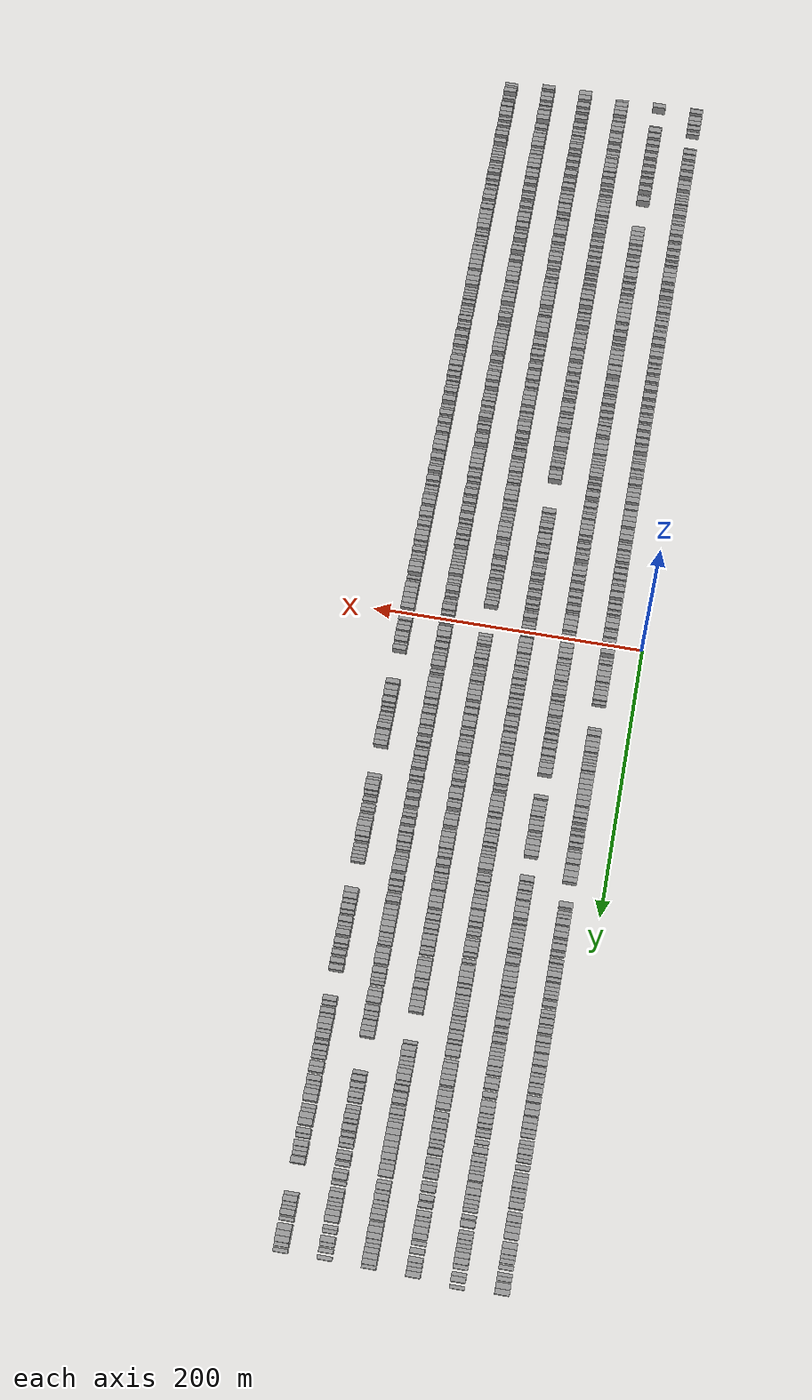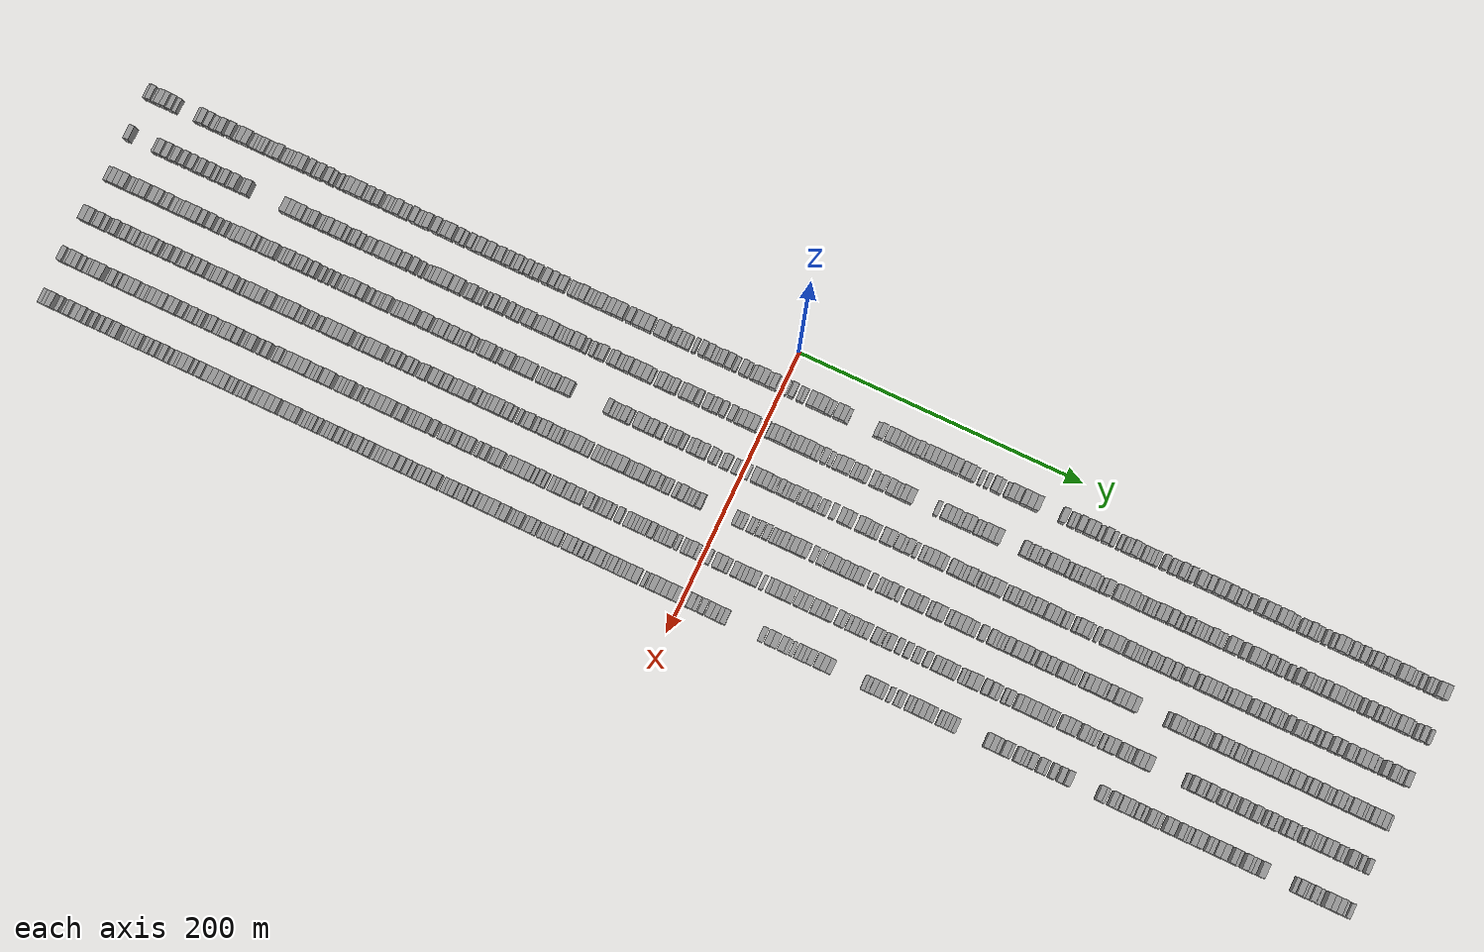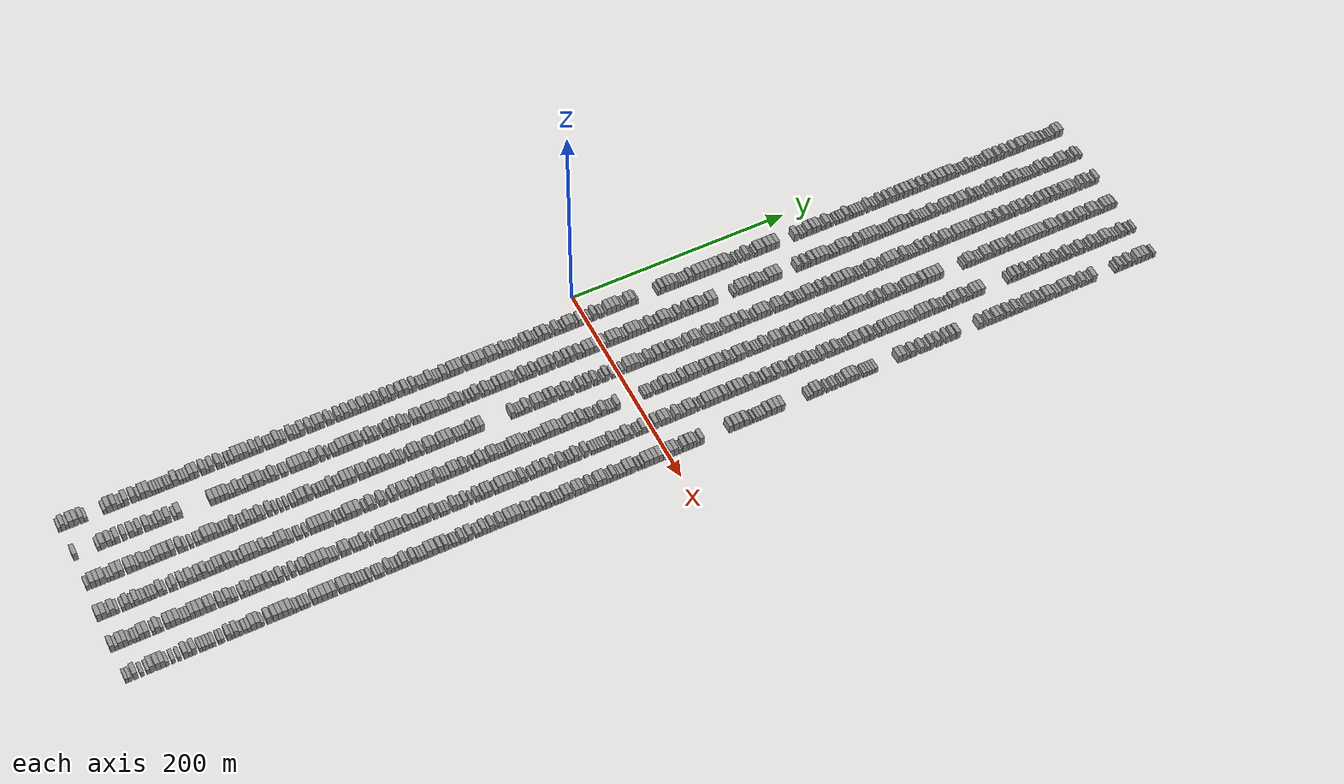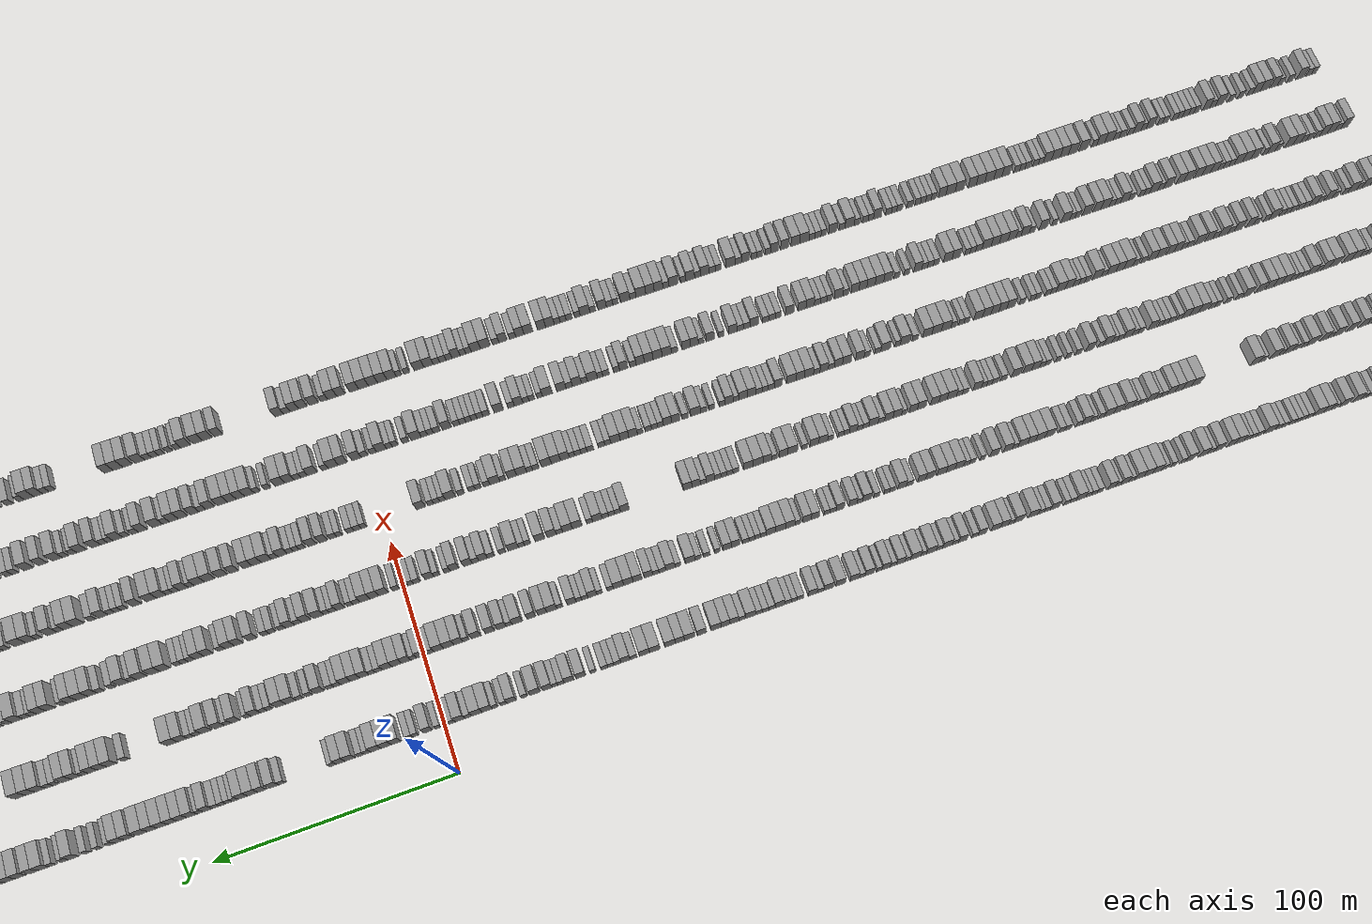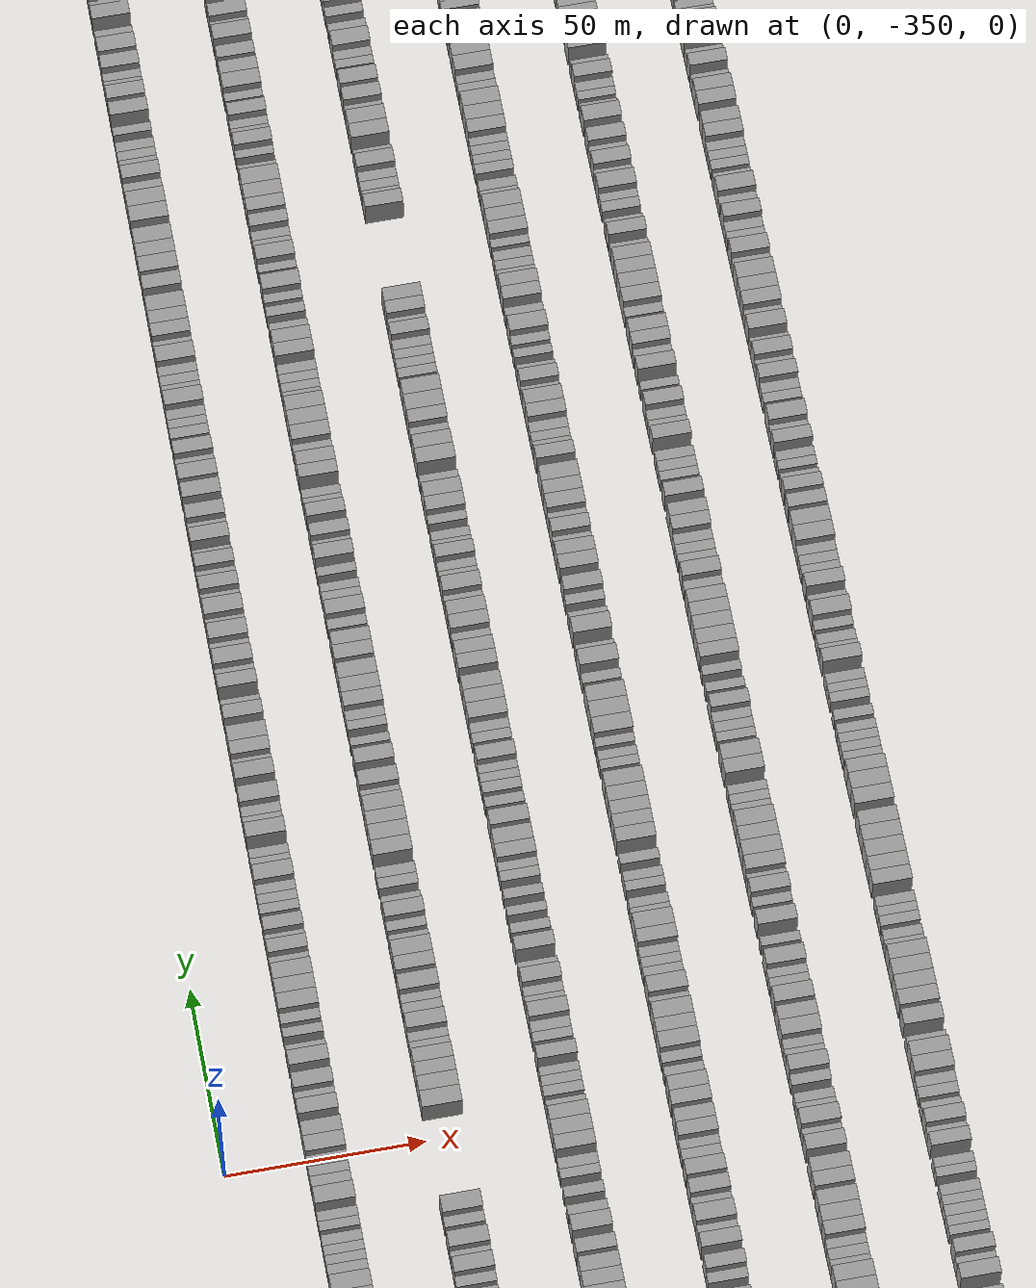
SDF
<sdf version="1.6">
 <world name="default">
  <scene>
   <sky><clouds><speed>12</speed></clouds></sky>
   <ambient>0.4 0.4 0.4 1</ambient>
   <background>0.7 0.7 0.7 1</background>
   <shadows>1</shadows>
  </scene>
  <gravity>0 0 -9.8066</gravity>
  <magnetic_field>6e-06 2.3e-05 -4.2e-05</magnetic_field>
  <physics default="0" name="default_physics" type="ode">
   <ode>
    <solver>
     <type>quick</type>
     <iters>10</iters>
     <sor>1.0</sor>
     <use_dynamic_moi_rescaling>0</use_dynamic_moi_rescaling>
    </solver>
    <constraints>
     <cfm>0</cfm>
     <erp>0.2</erp>
     <contact_max_correcting_vel>100</contact_max_correcting_vel>
     <contact_surface_layer>0.001</contact_surface_layer>
    </constraints>
   </ode>
   <max_step_size>0.004</max_step_size>
   <real_time_factor>1</real_time_factor>
   <real_time_update_rate>250</real_time_update_rate>
  </physics>
  <light name="sun" type="directional">
   <pose>0 0 10 0 0 0</pose>
   <diffuse>0.8 0.8 0.8 1</diffuse>
   <specular>0.2 0.2 0.2 1</specular>
   <attenuation>
    <range>1000</range>
    <constant>0.9</constant>
    <linear>0.01</linear>
    <quadratic>0.001</quadratic>
   </attenuation>
   <direction>-0.5 0.1 -0.9</direction>
  </light>
  <model name="building_1">
   <static>1</static>
   <pose>25.0000 -458.7066 0 0.000000 0.000000 0.000000</pose>
   <link name="link">
    <pose>0 0 3.00 0 0 0</pose>
    <collision name="collision"><geometry><box><size>10.0000 2.5868 6.0000</size></box></geometry></collision>
    <visual name="visual">
     <cast_shadows>0</cast_shadows>
     <geometry><box><size>10.0000 2.5868 6.0000</size></box></geometry>
     <material>
      <script>
       <uri>model://grey_wall/materials/scripts</uri>
       <uri>model://grey_wall/materials/textures</uri>
       <name>vrc/grey_wall</name>
      </script>
     </material>
    </visual>
   </link>
  </model>
  <model name="building_2">
   <static>1</static>
   <pose>25.0000 -455.5738 0 0.000000 0.000000 0.000000</pose>
   <link name="link">
    <pose>0 0 4.50 0 0 0</pose>
    <collision name="collision"><geometry><box><size>10.0000 3.6787 9.0000</size></box></geometry></collision>
    <visual name="visual">
     <cast_shadows>0</cast_shadows>
     <geometry><box><size>10.0000 3.6787 9.0000</size></box></geometry>
     <material>
      <script>
       <uri>model://grey_wall/materials/scripts</uri>
       <uri>model://grey_wall/materials/textures</uri>
       <name>vrc/grey_wall</name>
      </script>
     </material>
    </visual>
   </link>
  </model>
  <model name="building_3">
   <static>1</static>
   <pose>25.0000 -452.3858 0 0.000000 0.000000 0.000000</pose>
   <link name="link">
    <pose>0 0 3.00 0 0 0</pose>
    <collision name="collision"><geometry><box><size>10.0000 2.6974 6.0000</size></box></geometry></collision>
    <visual name="visual">
     <cast_shadows>0</cast_shadows>
     <geometry><box><size>10.0000 2.6974 6.0000</size></box></geometry>
     <material>
      <script>
       <uri>model://grey_wall/materials/scripts</uri>
       <uri>model://grey_wall/materials/textures</uri>
       <name>vrc/grey_wall</name>
      </script>
     </material>
    </visual>
   </link>
  </model>
  <model name="building_4">
   <static>1</static>
   <pose>25.0000 -448.9514 0 0.000000 0.000000 0.000000</pose>
   <link name="link">
    <pose>0 0 4.50 0 0 0</pose>
    <collision name="collision"><geometry><box><size>10.0000 4.1713 9.0000</size></box></geometry></collision>
    <visual name="visual">
     <cast_shadows>0</cast_shadows>
     <geometry><box><size>10.0000 4.1713 9.0000</size></box></geometry>
     <material>
      <script>
       <uri>model://grey_wall/materials/scripts</uri>
       <uri>model://grey_wall/materials/textures</uri>
       <name>vrc/grey_wall</name>
      </script>
     </material>
    </visual>
   </link>
  </model>
  <model name="building_5">
   <static>1</static>
   <pose>25.0000 -444.9981 0 0.000000 0.000000 0.000000</pose>
   <link name="link">
    <pose>0 0 4.50 0 0 0</pose>
    <collision name="collision"><geometry><box><size>10.0000 3.7355 9.0000</size></box></geometry></collision>
    <visual name="visual">
     <cast_shadows>0</cast_shadows>
     <geometry><box><size>10.0000 3.7355 9.0000</size></box></geometry>
     <material>
      <script>
       <uri>model://grey_wall/materials/scripts</uri>
       <uri>model://grey_wall/materials/textures</uri>
       <name>vrc/grey_wall</name>
      </script>
     </material>
    </visual>
   </link>
  </model>
  <model name="building_6">
   <static>1</static>
   <pose>25.0000 -440.3303 0 0.000000 0.000000 0.000000</pose>
   <link name="link">
    <pose>0 0 4.50 0 0 0</pose>
    <collision name="collision"><geometry><box><size>10.0000 3.6001 9.0000</size></box></geometry></collision>
    <visual name="visual">
     <cast_shadows>0</cast_shadows>
     <geometry><box><size>10.0000 3.6001 9.0000</size></box></geometry>
     <material>
      <script>
       <uri>model://grey_wall/materials/scripts</uri>
       <uri>model://grey_wall/materials/textures</uri>
       <name>vrc/grey_wall</name>
      </script>
     </material>
    </visual>
   </link>
  </model>
  <model name="building_7">
   <static>1</static>
   <pose>25.0000 -437.1537 0 0.000000 0.000000 0.000000</pose>
   <link name="link">
    <pose>0 0 3.00 0 0 0</pose>
    <collision name="collision"><geometry><box><size>10.0000 2.7531 6.0000</size></box></geometry></collision>
    <visual name="visual">
     <cast_shadows>0</cast_shadows>
     <geometry><box><size>10.0000 2.7531 6.0000</size></box></geometry>
     <material>
      <script>
       <uri>model://grey_wall/materials/scripts</uri>
       <uri>model://grey_wall/materials/textures</uri>
       <name>vrc/grey_wall</name>
      </script>
     </material>
    </visual>
   </link>
  </model>
  <model name="building_8">
   <static>1</static>
   <pose>25.0000 -421.3944 0 0.000000 0.000000 0.000000</pose>
   <link name="link">
    <pose>0 0 3.00 0 0 0</pose>
    <collision name="collision"><geometry><box><size>10.0000 2.9219 6.0000</size></box></geometry></collision>
    <visual name="visual">
     <cast_shadows>0</cast_shadows>
     <geometry><box><size>10.0000 2.9219 6.0000</size></box></geometry>
     <material>
      <script>
       <uri>model://grey_wall/materials/scripts</uri>
       <uri>model://grey_wall/materials/textures</uri>
       <name>vrc/grey_wall</name>
      </script>
     </material>
    </visual>
   </link>
  </model>
  <model name="building_9">
   <static>1</static>
   <pose>25.0000 -417.9384 0 0.000000 0.000000 0.000000</pose>
   <link name="link">
    <pose>0 0 4.50 0 0 0</pose>
    <collision name="collision"><geometry><box><size>10.0000 3.9902 9.0000</size></box></geometry></collision>
    <visual name="visual">
     <cast_shadows>0</cast_shadows>
     <geometry><box><size>10.0000 3.9902 9.0000</size></box></geometry>
     <material>
      <script>
       <uri>model://grey_wall/materials/scripts</uri>
       <uri>model://grey_wall/materials/textures</uri>
       <name>vrc/grey_wall</name>
      </script>
     </material>
    </visual>
   </link>
  </model>
  <model name="building_10">
   <static>1</static>
   <pose>25.0000 -412.9769 0 0.000000 0.000000 0.000000</pose>
   <link name="link">
    <pose>0 0 4.50 0 0 0</pose>
    <collision name="collision"><geometry><box><size>10.0000 3.9328 9.0000</size></box></geometry></collision>
    <visual name="visual">
     <cast_shadows>0</cast_shadows>
     <geometry><box><size>10.0000 3.9328 9.0000</size></box></geometry>
     <material>
      <script>
       <uri>model://grey_wall/materials/scripts</uri>
       <uri>model://grey_wall/materials/textures</uri>
       <name>vrc/grey_wall</name>
      </script>
     </material>
    </visual>
   </link>
  </model>
  <model name="building_11">
   <static>1</static>
   <pose>25.0000 -409.5305 0 0.000000 0.000000 0.000000</pose>
   <link name="link">
    <pose>0 0 3.00 0 0 0</pose>
    <collision name="collision"><geometry><box><size>10.0000 2.9600 6.0000</size></box></geometry></collision>
    <visual name="visual">
     <cast_shadows>0</cast_shadows>
     <geometry><box><size>10.0000 2.9600 6.0000</size></box></geometry>
     <material>
      <script>
       <uri>model://grey_wall/materials/scripts</uri>
       <uri>model://grey_wall/materials/textures</uri>
       <name>vrc/grey_wall</name>
      </script>
     </material>
    </visual>
   </link>
  </model>
  <model name="building_12">
   <static>1</static>
   <pose>25.0000 -406.8182 0 0.000000 0.000000 0.000000</pose>
   <link name="link">
    <pose>0 0 3.00 0 0 0</pose>
    <collision name="collision"><geometry><box><size>10.0000 2.4644 6.0000</size></box></geometry></collision>
    <visual name="visual">
     <cast_shadows>0</cast_shadows>
     <geometry><box><size>10.0000 2.4644 6.0000</size></box></geometry>
     <material>
      <script>
       <uri>model://grey_wall/materials/scripts</uri>
       <uri>model://grey_wall/materials/textures</uri>
       <name>vrc/grey_wall</name>
      </script>
     </material>
    </visual>
   </link>
  </model>
  <model name="building_13">
   <static>1</static>
   <pose>25.0000 -403.4928 0 0.000000 0.000000 0.000000</pose>
   <link name="link">
    <pose>0 0 4.50 0 0 0</pose>
    <collision name="collision"><geometry><box><size>10.0000 4.1865 9.0000</size></box></geometry></collision>
    <visual name="visual">
     <cast_shadows>0</cast_shadows>
     <geometry><box><size>10.0000 4.1865 9.0000</size></box></geometry>
     <material>
      <script>
       <uri>model://grey_wall/materials/scripts</uri>
       <uri>model://grey_wall/materials/textures</uri>
       <name>vrc/grey_wall</name>
      </script>
     </material>
    </visual>
   </link>
  </model>
  <model name="building_14">
   <static>1</static>
   <pose>25.0000 -397.3032 0 0.000000 0.000000 0.000000</pose>
   <link name="link">
    <pose>0 0 4.50 0 0 0</pose>
    <collision name="collision"><geometry><box><size>10.0000 4.1926 9.0000</size></box></geometry></collision>
    <visual name="visual">
     <cast_shadows>0</cast_shadows>
     <geometry><box><size>10.0000 4.1926 9.0000</size></box></geometry>
     <material>
      <script>
       <uri>model://grey_wall/materials/scripts</uri>
       <uri>model://grey_wall/materials/textures</uri>
       <name>vrc/grey_wall</name>
      </script>
     </material>
    </visual>
   </link>
  </model>
  <model name="building_15">
   <static>1</static>
   <pose>25.0000 -392.8134 0 0.000000 0.000000 0.000000</pose>
   <link name="link">
    <pose>0 0 3.00 0 0 0</pose>
    <collision name="collision"><geometry><box><size>10.0000 2.7870 6.0000</size></box></geometry></collision>
    <visual name="visual">
     <cast_shadows>0</cast_shadows>
     <geometry><box><size>10.0000 2.7870 6.0000</size></box></geometry>
     <material>
      <script>
       <uri>model://grey_wall/materials/scripts</uri>
       <uri>model://grey_wall/materials/textures</uri>
       <name>vrc/grey_wall</name>
      </script>
     </material>
    </visual>
   </link>
  </model>
  <model name="building_16">
   <static>1</static>
   <pose>25.0000 -389.4823 0 0.000000 0.000000 0.000000</pose>
   <link name="link">
    <pose>0 0 4.50 0 0 0</pose>
    <collision name="collision"><geometry><box><size>10.0000 3.8753 9.0000</size></box></geometry></collision>
    <visual name="visual">
     <cast_shadows>0</cast_shadows>
     <geometry><box><size>10.0000 3.8753 9.0000</size></box></geometry>
     <material>
      <script>
       <uri>model://grey_wall/materials/scripts</uri>
       <uri>model://grey_wall/materials/textures</uri>
       <name>vrc/grey_wall</name>
      </script>
     </material>
    </visual>
   </link>
  </model>
  <model name="building_17">
   <static>1</static>
   <pose>25.0000 -385.3470 0 0.000000 0.000000 0.000000</pose>
   <link name="link">
    <pose>0 0 4.50 0 0 0</pose>
    <collision name="collision"><geometry><box><size>10.0000 4.3953 9.0000</size></box></geometry></collision>
    <visual name="visual">
     <cast_shadows>0</cast_shadows>
     <geometry><box><size>10.0000 4.3953 9.0000</size></box></geometry>
     <material>
      <script>
       <uri>model://grey_wall/materials/scripts</uri>
       <uri>model://grey_wall/materials/textures</uri>
       <name>vrc/grey_wall</name>
      </script>
     </material>
    </visual>
   </link>
  </model>
  <model name="building_18">
   <static>1</static>
   <pose>25.0000 -380.8037 0 0.000000 0.000000 0.000000</pose>
   <link name="link">
    <pose>0 0 3.00 0 0 0</pose>
    <collision name="collision"><geometry><box><size>10.0000 2.6913 6.0000</size></box></geometry></collision>
    <visual name="visual">
     <cast_shadows>0</cast_shadows>
     <geometry><box><size>10.0000 2.6913 6.0000</size></box></geometry>
     <material>
      <script>
       <uri>model://grey_wall/materials/scripts</uri>
       <uri>model://grey_wall/materials/textures</uri>
       <name>vrc/grey_wall</name>
      </script>
     </material>
    </visual>
   </link>
  </model>
  <model name="building_19">
   <static>1</static>
   <pose>25.0000 -378.2091 0 0.000000 0.000000 0.000000</pose>
   <link name="link">
    <pose>0 0 3.00 0 0 0</pose>
    <collision name="collision"><geometry><box><size>10.0000 2.4979 6.0000</size></box></geometry></collision>
    <visual name="visual">
     <cast_shadows>0</cast_shadows>
     <geometry><box><size>10.0000 2.4979 6.0000</size></box></geometry>
     <material>
      <script>
       <uri>model://grey_wall/materials/scripts</uri>
       <uri>model://grey_wall/materials/textures</uri>
       <name>vrc/grey_wall</name>
      </script>
     </material>
    </visual>
   </link>
  </model>
  <model name="building_20">
   <static>1</static>
   <pose>25.0000 -375.7072 0 0.000000 0.000000 0.000000</pose>
   <link name="link">
    <pose>0 0 3.00 0 0 0</pose>
    <collision name="collision"><geometry><box><size>10.0000 2.5059 6.0000</size></box></geometry></collision>
    <visual name="visual">
     <cast_shadows>0</cast_shadows>
     <geometry><box><size>10.0000 2.5059 6.0000</size></box></geometry>
     <material>
      <script>
       <uri>model://grey_wall/materials/scripts</uri>
       <uri>model://grey_wall/materials/textures</uri>
       <name>vrc/grey_wall</name>
      </script>
     </material>
    </visual>
   </link>
  </model>
  <model name="building_21">
   <static>1</static>
   <pose>25.0000 -373.0271 0 0.000000 0.000000 0.000000</pose>
   <link name="link">
    <pose>0 0 3.00 0 0 0</pose>
    <collision name="collision"><geometry><box><size>10.0000 2.8543 6.0000</size></box></geometry></collision>
    <visual name="visual">
     <cast_shadows>0</cast_shadows>
     <geometry><box><size>10.0000 2.8543 6.0000</size></box></geometry>
     <material>
      <script>
       <uri>model://grey_wall/materials/scripts</uri>
       <uri>model://grey_wall/materials/textures</uri>
       <name>vrc/grey_wall</name>
      </script>
     </material>
    </visual>
   </link>
  </model>
  <model name="building_22">
   <static>1</static>
   <pose>25.0000 -369.3233 0 0.000000 0.000000 0.000000</pose>
   <link name="link">
    <pose>0 0 3.00 0 0 0</pose>
    <collision name="collision"><geometry><box><size>10.0000 2.5532 6.0000</size></box></geometry></collision>
    <visual name="visual">
     <cast_shadows>0</cast_shadows>
     <geometry><box><size>10.0000 2.5532 6.0000</size></box></geometry>
     <material>
      <script>
       <uri>model://grey_wall/materials/scripts</uri>
       <uri>model://grey_wall/materials/textures</uri>
       <name>vrc/grey_wall</name>
      </script>
     </material>
    </visual>
   </link>
  </model>
  <model name="building_23">
   <static>1</static>
   <pose>25.0000 -366.7375 0 0.000000 0.000000 0.000000</pose>
   <link name="link">
    <pose>0 0 3.00 0 0 0</pose>
    <collision name="collision"><geometry><box><size>10.0000 2.6186 6.0000</size></box></geometry></collision>
    <visual name="visual">
     <cast_shadows>0</cast_shadows>
     <geometry><box><size>10.0000 2.6186 6.0000</size></box></geometry>
     <material>
      <script>
       <uri>model://grey_wall/materials/scripts</uri>
       <uri>model://grey_wall/materials/textures</uri>
       <name>vrc/grey_wall</name>
      </script>
     </material>
    </visual>
   </link>
  </model>
  <model name="building_24">
   <static>1</static>
   <pose>25.0000 -362.2098 0 0.000000 0.000000 0.000000</pose>
   <link name="link">
    <pose>0 0 4.50 0 0 0</pose>
    <collision name="collision"><geometry><box><size>10.0000 4.4368 9.0000</size></box></geometry></collision>
    <visual name="visual">
     <cast_shadows>0</cast_shadows>
     <geometry><box><size>10.0000 4.4368 9.0000</size></box></geometry>
     <material>
      <script>
       <uri>model://grey_wall/materials/scripts</uri>
       <uri>model://grey_wall/materials/textures</uri>
       <name>vrc/grey_wall</name>
      </script>
     </material>
    </visual>
   </link>
  </model>
  <model name="building_25">
   <static>1</static>
   <pose>25.0000 -357.5511 0 0.000000 0.000000 0.000000</pose>
   <link name="link">
    <pose>0 0 3.00 0 0 0</pose>
    <collision name="collision"><geometry><box><size>10.0000 2.8805 6.0000</size></box></geometry></collision>
    <visual name="visual">
     <cast_shadows>0</cast_shadows>
     <geometry><box><size>10.0000 2.8805 6.0000</size></box></geometry>
     <material>
      <script>
       <uri>model://grey_wall/materials/scripts</uri>
       <uri>model://grey_wall/materials/textures</uri>
       <name>vrc/grey_wall</name>
      </script>
     </material>
    </visual>
   </link>
  </model>
  <model name="building_26">
   <static>1</static>
   <pose>25.0000 -354.8168 0 0.000000 0.000000 0.000000</pose>
   <link name="link">
    <pose>0 0 3.00 0 0 0</pose>
    <collision name="collision"><geometry><box><size>10.0000 2.5881 6.0000</size></box></geometry></collision>
    <visual name="visual">
     <cast_shadows>0</cast_shadows>
     <geometry><box><size>10.0000 2.5881 6.0000</size></box></geometry>
     <material>
      <script>
       <uri>model://grey_wall/materials/scripts</uri>
       <uri>model://grey_wall/materials/textures</uri>
       <name>vrc/grey_wall</name>
      </script>
     </material>
    </visual>
   </link>
  </model>
  <model name="building_27">
   <static>1</static>
   <pose>25.0000 -352.0899 0 0.000000 0.000000 0.000000</pose>
   <link name="link">
    <pose>0 0 3.00 0 0 0</pose>
    <collision name="collision"><geometry><box><size>10.0000 2.8656 6.0000</size></box></geometry></collision>
    <visual name="visual">
     <cast_shadows>0</cast_shadows>
     <geometry><box><size>10.0000 2.8656 6.0000</size></box></geometry>
     <material>
      <script>
       <uri>model://grey_wall/materials/scripts</uri>
       <uri>model://grey_wall/materials/textures</uri>
       <name>vrc/grey_wall</name>
      </script>
     </material>
    </visual>
   </link>
  </model>
  <model name="building_28">
   <static>1</static>
   <pose>25.0000 -348.5748 0 0.000000 0.000000 0.000000</pose>
   <link name="link">
    <pose>0 0 4.50 0 0 0</pose>
    <collision name="collision"><geometry><box><size>10.0000 4.1646 9.0000</size></box></geometry></collision>
    <visual name="visual">
     <cast_shadows>0</cast_shadows>
     <geometry><box><size>10.0000 4.1646 9.0000</size></box></geometry>
     <material>
      <script>
       <uri>model://grey_wall/materials/scripts</uri>
       <uri>model://grey_wall/materials/textures</uri>
       <name>vrc/grey_wall</name>
      </script>
     </material>
    </visual>
   </link>
  </model>
  <model name="building_29">
   <static>1</static>
   <pose>25.0000 -344.5619 0 0.000000 0.000000 0.000000</pose>
   <link name="link">
    <pose>0 0 4.50 0 0 0</pose>
    <collision name="collision"><geometry><box><size>10.0000 3.8612 9.0000</size></box></geometry></collision>
    <visual name="visual">
     <cast_shadows>0</cast_shadows>
     <geometry><box><size>10.0000 3.8612 9.0000</size></box></geometry>
     <material>
      <script>
       <uri>model://grey_wall/materials/scripts</uri>
       <uri>model://grey_wall/materials/textures</uri>
       <name>vrc/grey_wall</name>
      </script>
     </material>
    </visual>
   </link>
  </model>
  <model name="building_30">
   <static>1</static>
   <pose>25.0000 -338.6396 0 0.000000 0.000000 0.000000</pose>
   <link name="link">
    <pose>0 0 4.50 0 0 0</pose>
    <collision name="collision"><geometry><box><size>10.0000 3.9833 9.0000</size></box></geometry></collision>
    <visual name="visual">
     <cast_shadows>0</cast_shadows>
     <geometry><box><size>10.0000 3.9833 9.0000</size></box></geometry>
     <material>
      <script>
       <uri>model://grey_wall/materials/scripts</uri>
       <uri>model://grey_wall/materials/textures</uri>
       <name>vrc/grey_wall</name>
      </script>
     </material>
    </visual>
   </link>
  </model>
  <model name="building_31">
   <static>1</static>
   <pose>25.0000 -335.1630 0 0.000000 0.000000 0.000000</pose>
   <link name="link">
    <pose>0 0 3.00 0 0 0</pose>
    <collision name="collision"><geometry><box><size>10.0000 2.9698 6.0000</size></box></geometry></collision>
    <visual name="visual">
     <cast_shadows>0</cast_shadows>
     <geometry><box><size>10.0000 2.9698 6.0000</size></box></geometry>
     <material>
      <script>
       <uri>model://grey_wall/materials/scripts</uri>
       <uri>model://grey_wall/materials/textures</uri>
       <name>vrc/grey_wall</name>
      </script>
     </material>
    </visual>
   </link>
  </model>
  <model name="building_32">
   <static>1</static>
   <pose>25.0000 -331.6582 0 0.000000 0.000000 0.000000</pose>
   <link name="link">
    <pose>0 0 4.50 0 0 0</pose>
    <collision name="collision"><geometry><box><size>10.0000 4.0399 9.0000</size></box></geometry></collision>
    <visual name="visual">
     <cast_shadows>0</cast_shadows>
     <geometry><box><size>10.0000 4.0399 9.0000</size></box></geometry>
     <material>
      <script>
       <uri>model://grey_wall/materials/scripts</uri>
       <uri>model://grey_wall/materials/textures</uri>
       <name>vrc/grey_wall</name>
      </script>
     </material>
    </visual>
   </link>
  </model>
  <model name="building_33">
   <static>1</static>
   <pose>25.0000 -325.6373 0 0.000000 0.000000 0.000000</pose>
   <link name="link">
    <pose>0 0 4.50 0 0 0</pose>
    <collision name="collision"><geometry><box><size>10.0000 4.0019 9.0000</size></box></geometry></collision>
    <visual name="visual">
     <cast_shadows>0</cast_shadows>
     <geometry><box><size>10.0000 4.0019 9.0000</size></box></geometry>
     <material>
      <script>
       <uri>model://grey_wall/materials/scripts</uri>
       <uri>model://grey_wall/materials/textures</uri>
       <name>vrc/grey_wall</name>
      </script>
     </material>
    </visual>
   </link>
  </model>
  <model name="building_34">
   <static>1</static>
   <pose>25.0000 -322.3451 0 0.000000 0.000000 0.000000</pose>
   <link name="link">
    <pose>0 0 3.00 0 0 0</pose>
    <collision name="collision"><geometry><box><size>10.0000 2.5824 6.0000</size></box></geometry></collision>
    <visual name="visual">
     <cast_shadows>0</cast_shadows>
     <geometry><box><size>10.0000 2.5824 6.0000</size></box></geometry>
     <material>
      <script>
       <uri>model://grey_wall/materials/scripts</uri>
       <uri>model://grey_wall/materials/textures</uri>
       <name>vrc/grey_wall</name>
      </script>
     </material>
    </visual>
   </link>
  </model>
  <model name="building_35">
   <static>1</static>
   <pose>25.0000 -317.7563 0 0.000000 0.000000 0.000000</pose>
   <link name="link">
    <pose>0 0 3.00 0 0 0</pose>
    <collision name="collision"><geometry><box><size>10.0000 2.5953 6.0000</size></box></geometry></collision>
    <visual name="visual">
     <cast_shadows>0</cast_shadows>
     <geometry><box><size>10.0000 2.5953 6.0000</size></box></geometry>
     <material>
      <script>
       <uri>model://grey_wall/materials/scripts</uri>
       <uri>model://grey_wall/materials/textures</uri>
       <name>vrc/grey_wall</name>
      </script>
     </material>
    </visual>
   </link>
  </model>
  <model name="building_36">
   <static>1</static>
   <pose>25.0000 -314.0332 0 0.000000 0.000000 0.000000</pose>
   <link name="link">
    <pose>0 0 3.00 0 0 0</pose>
    <collision name="collision"><geometry><box><size>10.0000 2.8508 6.0000</size></box></geometry></collision>
    <visual name="visual">
     <cast_shadows>0</cast_shadows>
     <geometry><box><size>10.0000 2.8508 6.0000</size></box></geometry>
     <material>
      <script>
       <uri>model://grey_wall/materials/scripts</uri>
       <uri>model://grey_wall/materials/textures</uri>
       <name>vrc/grey_wall</name>
      </script>
     </material>
    </visual>
   </link>
  </model>
  <model name="building_37">
   <static>1</static>
   <pose>25.0000 -310.4805 0 0.000000 0.000000 0.000000</pose>
   <link name="link">
    <pose>0 0 4.50 0 0 0</pose>
    <collision name="collision"><geometry><box><size>10.0000 4.2546 9.0000</size></box></geometry></collision>
    <visual name="visual">
     <cast_shadows>0</cast_shadows>
     <geometry><box><size>10.0000 4.2546 9.0000</size></box></geometry>
     <material>
      <script>
       <uri>model://grey_wall/materials/scripts</uri>
       <uri>model://grey_wall/materials/textures</uri>
       <name>vrc/grey_wall</name>
      </script>
     </material>
    </visual>
   </link>
  </model>
  <model name="building_38">
   <static>1</static>
   <pose>25.0000 -306.3795 0 0.000000 0.000000 0.000000</pose>
   <link name="link">
    <pose>0 0 4.50 0 0 0</pose>
    <collision name="collision"><geometry><box><size>10.0000 3.9473 9.0000</size></box></geometry></collision>
    <visual name="visual">
     <cast_shadows>0</cast_shadows>
     <geometry><box><size>10.0000 3.9473 9.0000</size></box></geometry>
     <material>
      <script>
       <uri>model://grey_wall/materials/scripts</uri>
       <uri>model://grey_wall/materials/textures</uri>
       <name>vrc/grey_wall</name>
      </script>
     </material>
    </visual>
   </link>
  </model>
  <model name="building_39">
   <static>1</static>
   <pose>25.0000 -302.2905 0 0.000000 0.000000 0.000000</pose>
   <link name="link">
    <pose>0 0 4.50 0 0 0</pose>
    <collision name="collision"><geometry><box><size>10.0000 4.2308 9.0000</size></box></geometry></collision>
    <visual name="visual">
     <cast_shadows>0</cast_shadows>
     <geometry><box><size>10.0000 4.2308 9.0000</size></box></geometry>
     <material>
      <script>
       <uri>model://grey_wall/materials/scripts</uri>
       <uri>model://grey_wall/materials/textures</uri>
       <name>vrc/grey_wall</name>
      </script>
     </material>
    </visual>
   </link>
  </model>
  <model name="building_40">
   <static>1</static>
   <pose>25.0000 -298.7629 0 0.000000 0.000000 0.000000</pose>
   <link name="link">
    <pose>0 0 3.00 0 0 0</pose>
    <collision name="collision"><geometry><box><size>10.0000 2.8245 6.0000</size></box></geometry></collision>
    <visual name="visual">
     <cast_shadows>0</cast_shadows>
     <geometry><box><size>10.0000 2.8245 6.0000</size></box></geometry>
     <material>
      <script>
       <uri>model://grey_wall/materials/scripts</uri>
       <uri>model://grey_wall/materials/textures</uri>
       <name>vrc/grey_wall</name>
      </script>
     </material>
    </visual>
   </link>
  </model>
  <model name="building_41">
   <static>1</static>
   <pose>25.0000 -295.5331 0 0.000000 0.000000 0.000000</pose>
   <link name="link">
    <pose>0 0 4.50 0 0 0</pose>
    <collision name="collision"><geometry><box><size>10.0000 3.6350 9.0000</size></box></geometry></collision>
    <visual name="visual">
     <cast_shadows>0</cast_shadows>
     <geometry><box><size>10.0000 3.6350 9.0000</size></box></geometry>
     <material>
      <script>
       <uri>model://grey_wall/materials/scripts</uri>
       <uri>model://grey_wall/materials/textures</uri>
       <name>vrc/grey_wall</name>
      </script>
     </material>
    </visual>
   </link>
  </model>
  <model name="building_42">
   <static>1</static>
   <pose>25.0000 -292.4759 0 0.000000 0.000000 0.000000</pose>
   <link name="link">
    <pose>0 0 3.00 0 0 0</pose>
    <collision name="collision"><geometry><box><size>10.0000 2.4794 6.0000</size></box></geometry></collision>
    <visual name="visual">
     <cast_shadows>0</cast_shadows>
     <geometry><box><size>10.0000 2.4794 6.0000</size></box></geometry>
     <material>
      <script>
       <uri>model://grey_wall/materials/scripts</uri>
       <uri>model://grey_wall/materials/textures</uri>
       <name>vrc/grey_wall</name>
      </script>
     </material>
    </visual>
   </link>
  </model>
  <model name="building_43">
   <static>1</static>
   <pose>25.0000 -289.4240 0 0.000000 0.000000 0.000000</pose>
   <link name="link">
    <pose>0 0 4.50 0 0 0</pose>
    <collision name="collision"><geometry><box><size>10.0000 3.6244 9.0000</size></box></geometry></collision>
    <visual name="visual">
     <cast_shadows>0</cast_shadows>
     <geometry><box><size>10.0000 3.6244 9.0000</size></box></geometry>
     <material>
      <script>
       <uri>model://grey_wall/materials/scripts</uri>
       <uri>model://grey_wall/materials/textures</uri>
       <name>vrc/grey_wall</name>
      </script>
     </material>
    </visual>
   </link>
  </model>
  <model name="building_44">
   <static>1</static>
   <pose>25.0000 -284.2788 0 0.000000 0.000000 0.000000</pose>
   <link name="link">
    <pose>0 0 3.00 0 0 0</pose>
    <collision name="collision"><geometry><box><size>10.0000 2.6661 6.0000</size></box></geometry></collision>
    <visual name="visual">
     <cast_shadows>0</cast_shadows>
     <geometry><box><size>10.0000 2.6661 6.0000</size></box></geometry>
     <material>
      <script>
       <uri>model://grey_wall/materials/scripts</uri>
       <uri>model://grey_wall/materials/textures</uri>
       <name>vrc/grey_wall</name>
      </script>
     </material>
    </visual>
   </link>
  </model>
  <model name="building_45">
   <static>1</static>
   <pose>25.0000 -281.6269 0 0.000000 0.000000 0.000000</pose>
   <link name="link">
    <pose>0 0 3.00 0 0 0</pose>
    <collision name="collision"><geometry><box><size>10.0000 2.6376 6.0000</size></box></geometry></collision>
    <visual name="visual">
     <cast_shadows>0</cast_shadows>
     <geometry><box><size>10.0000 2.6376 6.0000</size></box></geometry>
     <material>
      <script>
       <uri>model://grey_wall/materials/scripts</uri>
       <uri>model://grey_wall/materials/textures</uri>
       <name>vrc/grey_wall</name>
      </script>
     </material>
    </visual>
   </link>
  </model>
  <model name="building_46">
   <static>1</static>
   <pose>25.0000 -278.9740 0 0.000000 0.000000 0.000000</pose>
   <link name="link">
    <pose>0 0 3.00 0 0 0</pose>
    <collision name="collision"><geometry><box><size>10.0000 2.6681 6.0000</size></box></geometry></collision>
    <visual name="visual">
     <cast_shadows>0</cast_shadows>
     <geometry><box><size>10.0000 2.6681 6.0000</size></box></geometry>
     <material>
      <script>
       <uri>model://grey_wall/materials/scripts</uri>
       <uri>model://grey_wall/materials/textures</uri>
       <name>vrc/grey_wall</name>
      </script>
     </material>
    </visual>
   </link>
  </model>
  <model name="building_47">
   <static>1</static>
   <pose>25.0000 -275.4990 0 0.000000 0.000000 0.000000</pose>
   <link name="link">
    <pose>0 0 4.50 0 0 0</pose>
    <collision name="collision"><geometry><box><size>10.0000 4.2820 9.0000</size></box></geometry></collision>
    <visual name="visual">
     <cast_shadows>0</cast_shadows>
     <geometry><box><size>10.0000 4.2820 9.0000</size></box></geometry>
     <material>
      <script>
       <uri>model://grey_wall/materials/scripts</uri>
       <uri>model://grey_wall/materials/textures</uri>
       <name>vrc/grey_wall</name>
      </script>
     </material>
    </visual>
   </link>
  </model>
  <model name="building_48">
   <static>1</static>
   <pose>25.0000 -271.8815 0 0.000000 0.000000 0.000000</pose>
   <link name="link">
    <pose>0 0 3.00 0 0 0</pose>
    <collision name="collision"><geometry><box><size>10.0000 2.9530 6.0000</size></box></geometry></collision>
    <visual name="visual">
     <cast_shadows>0</cast_shadows>
     <geometry><box><size>10.0000 2.9530 6.0000</size></box></geometry>
     <material>
      <script>
       <uri>model://grey_wall/materials/scripts</uri>
       <uri>model://grey_wall/materials/textures</uri>
       <name>vrc/grey_wall</name>
      </script>
     </material>
    </visual>
   </link>
  </model>
  <model name="building_49">
   <static>1</static>
   <pose>25.0000 -269.1042 0 0.000000 0.000000 0.000000</pose>
   <link name="link">
    <pose>0 0 3.00 0 0 0</pose>
    <collision name="collision"><geometry><box><size>10.0000 2.6016 6.0000</size></box></geometry></collision>
    <visual name="visual">
     <cast_shadows>0</cast_shadows>
     <geometry><box><size>10.0000 2.6016 6.0000</size></box></geometry>
     <material>
      <script>
       <uri>model://grey_wall/materials/scripts</uri>
       <uri>model://grey_wall/materials/textures</uri>
       <name>vrc/grey_wall</name>
      </script>
     </material>
    </visual>
   </link>
  </model>
  <model name="building_50">
   <static>1</static>
   <pose>25.0000 -263.7779 0 0.000000 0.000000 0.000000</pose>
   <link name="link">
    <pose>0 0 4.50 0 0 0</pose>
    <collision name="collision"><geometry><box><size>10.0000 4.0511 9.0000</size></box></geometry></collision>
    <visual name="visual">
     <cast_shadows>0</cast_shadows>
     <geometry><box><size>10.0000 4.0511 9.0000</size></box></geometry>
     <material>
      <script>
       <uri>model://grey_wall/materials/scripts</uri>
       <uri>model://grey_wall/materials/textures</uri>
       <name>vrc/grey_wall</name>
      </script>
     </material>
    </visual>
   </link>
  </model>
  <model name="building_51">
   <static>1</static>
   <pose>25.0000 -260.3694 0 0.000000 0.000000 0.000000</pose>
   <link name="link">
    <pose>0 0 3.00 0 0 0</pose>
    <collision name="collision"><geometry><box><size>10.0000 2.7658 6.0000</size></box></geometry></collision>
    <visual name="visual">
     <cast_shadows>0</cast_shadows>
     <geometry><box><size>10.0000 2.7658 6.0000</size></box></geometry>
     <material>
      <script>
       <uri>model://grey_wall/materials/scripts</uri>
       <uri>model://grey_wall/materials/textures</uri>
       <name>vrc/grey_wall</name>
      </script>
     </material>
    </visual>
   </link>
  </model>
  <model name="building_52">
   <static>1</static>
   <pose>25.0000 -257.5823 0 0.000000 0.000000 0.000000</pose>
   <link name="link">
    <pose>0 0 3.00 0 0 0</pose>
    <collision name="collision"><geometry><box><size>10.0000 2.8084 6.0000</size></box></geometry></collision>
    <visual name="visual">
     <cast_shadows>0</cast_shadows>
     <geometry><box><size>10.0000 2.8084 6.0000</size></box></geometry>
     <material>
      <script>
       <uri>model://grey_wall/materials/scripts</uri>
       <uri>model://grey_wall/materials/textures</uri>
       <name>vrc/grey_wall</name>
      </script>
     </material>
    </visual>
   </link>
  </model>
  <model name="building_53">
   <static>1</static>
   <pose>25.0000 -253.9620 0 0.000000 0.000000 0.000000</pose>
   <link name="link">
    <pose>0 0 4.50 0 0 0</pose>
    <collision name="collision"><geometry><box><size>10.0000 4.4323 9.0000</size></box></geometry></collision>
    <visual name="visual">
     <cast_shadows>0</cast_shadows>
     <geometry><box><size>10.0000 4.4323 9.0000</size></box></geometry>
     <material>
      <script>
       <uri>model://grey_wall/materials/scripts</uri>
       <uri>model://grey_wall/materials/textures</uri>
       <name>vrc/grey_wall</name>
      </script>
     </material>
    </visual>
   </link>
  </model>
  <model name="building_54">
   <static>1</static>
   <pose>25.0000 -247.5937 0 0.000000 0.000000 0.000000</pose>
   <link name="link">
    <pose>0 0 4.50 0 0 0</pose>
    <collision name="collision"><geometry><box><size>10.0000 4.3042 9.0000</size></box></geometry></collision>
    <visual name="visual">
     <cast_shadows>0</cast_shadows>
     <geometry><box><size>10.0000 4.3042 9.0000</size></box></geometry>
     <material>
      <script>
       <uri>model://grey_wall/materials/scripts</uri>
       <uri>model://grey_wall/materials/textures</uri>
       <name>vrc/grey_wall</name>
      </script>
     </material>
    </visual>
   </link>
  </model>
  <model name="building_55">
   <static>1</static>
   <pose>25.0000 -244.2251 0 0.000000 0.000000 0.000000</pose>
   <link name="link">
    <pose>0 0 3.00 0 0 0</pose>
    <collision name="collision"><geometry><box><size>10.0000 2.4330 6.0000</size></box></geometry></collision>
    <visual name="visual">
     <cast_shadows>0</cast_shadows>
     <geometry><box><size>10.0000 2.4330 6.0000</size></box></geometry>
     <material>
      <script>
       <uri>model://grey_wall/materials/scripts</uri>
       <uri>model://grey_wall/materials/textures</uri>
       <name>vrc/grey_wall</name>
      </script>
     </material>
    </visual>
   </link>
  </model>
  <model name="building_56">
   <static>1</static>
   <pose>25.0000 -241.1319 0 0.000000 0.000000 0.000000</pose>
   <link name="link">
    <pose>0 0 4.50 0 0 0</pose>
    <collision name="collision"><geometry><box><size>10.0000 3.7533 9.0000</size></box></geometry></collision>
    <visual name="visual">
     <cast_shadows>0</cast_shadows>
     <geometry><box><size>10.0000 3.7533 9.0000</size></box></geometry>
     <material>
      <script>
       <uri>model://grey_wall/materials/scripts</uri>
       <uri>model://grey_wall/materials/textures</uri>
       <name>vrc/grey_wall</name>
      </script>
     </material>
    </visual>
   </link>
  </model>
  <model name="building_57">
   <static>1</static>
   <pose>25.0000 -237.1283 0 0.000000 0.000000 0.000000</pose>
   <link name="link">
    <pose>0 0 4.50 0 0 0</pose>
    <collision name="collision"><geometry><box><size>10.0000 4.2540 9.0000</size></box></geometry></collision>
    <visual name="visual">
     <cast_shadows>0</cast_shadows>
     <geometry><box><size>10.0000 4.2540 9.0000</size></box></geometry>
     <material>
      <script>
       <uri>model://grey_wall/materials/scripts</uri>
       <uri>model://grey_wall/materials/textures</uri>
       <name>vrc/grey_wall</name>
      </script>
     </material>
    </visual>
   </link>
  </model>
  <model name="building_58">
   <static>1</static>
   <pose>25.0000 -231.1144 0 0.000000 0.000000 0.000000</pose>
   <link name="link">
    <pose>0 0 4.50 0 0 0</pose>
    <collision name="collision"><geometry><box><size>10.0000 3.7738 9.0000</size></box></geometry></collision>
    <visual name="visual">
     <cast_shadows>0</cast_shadows>
     <geometry><box><size>10.0000 3.7738 9.0000</size></box></geometry>
     <material>
      <script>
       <uri>model://grey_wall/materials/scripts</uri>
       <uri>model://grey_wall/materials/textures</uri>
       <name>vrc/grey_wall</name>
      </script>
     </material>
    </visual>
   </link>
  </model>
  <model name="building_59">
   <static>1</static>
   <pose>25.0000 -227.8237 0 0.000000 0.000000 0.000000</pose>
   <link name="link">
    <pose>0 0 3.00 0 0 0</pose>
    <collision name="collision"><geometry><box><size>10.0000 2.8077 6.0000</size></box></geometry></collision>
    <visual name="visual">
     <cast_shadows>0</cast_shadows>
     <geometry><box><size>10.0000 2.8077 6.0000</size></box></geometry>
     <material>
      <script>
       <uri>model://grey_wall/materials/scripts</uri>
       <uri>model://grey_wall/materials/textures</uri>
       <name>vrc/grey_wall</name>
      </script>
     </material>
    </visual>
   </link>
  </model>
  <model name="building_60">
   <static>1</static>
   <pose>25.0000 -222.5202 0 0.000000 0.000000 0.000000</pose>
   <link name="link">
    <pose>0 0 4.50 0 0 0</pose>
    <collision name="collision"><geometry><box><size>10.0000 3.7992 9.0000</size></box></geometry></collision>
    <visual name="visual">
     <cast_shadows>0</cast_shadows>
     <geometry><box><size>10.0000 3.7992 9.0000</size></box></geometry>
     <material>
      <script>
       <uri>model://grey_wall/materials/scripts</uri>
       <uri>model://grey_wall/materials/textures</uri>
       <name>vrc/grey_wall</name>
      </script>
     </material>
    </visual>
   </link>
  </model>
  <model name="building_61">
   <static>1</static>
   <pose>25.0000 -219.2233 0 0.000000 0.000000 0.000000</pose>
   <link name="link">
    <pose>0 0 3.00 0 0 0</pose>
    <collision name="collision"><geometry><box><size>10.0000 2.7945 6.0000</size></box></geometry></collision>
    <visual name="visual">
     <cast_shadows>0</cast_shadows>
     <geometry><box><size>10.0000 2.7945 6.0000</size></box></geometry>
     <material>
      <script>
       <uri>model://grey_wall/materials/scripts</uri>
       <uri>model://grey_wall/materials/textures</uri>
       <name>vrc/grey_wall</name>
      </script>
     </material>
    </visual>
   </link>
  </model>
  <model name="building_62">
   <static>1</static>
   <pose>25.0000 -215.6175 0 0.000000 0.000000 0.000000</pose>
   <link name="link">
    <pose>0 0 4.50 0 0 0</pose>
    <collision name="collision"><geometry><box><size>10.0000 4.4172 9.0000</size></box></geometry></collision>
    <visual name="visual">
     <cast_shadows>0</cast_shadows>
     <geometry><box><size>10.0000 4.4172 9.0000</size></box></geometry>
     <material>
      <script>
       <uri>model://grey_wall/materials/scripts</uri>
       <uri>model://grey_wall/materials/textures</uri>
       <name>vrc/grey_wall</name>
      </script>
     </material>
    </visual>
   </link>
  </model>
  <model name="building_63">
   <static>1</static>
   <pose>25.0000 -212.0301 0 0.000000 0.000000 0.000000</pose>
   <link name="link">
    <pose>0 0 3.00 0 0 0</pose>
    <collision name="collision"><geometry><box><size>10.0000 2.7577 6.0000</size></box></geometry></collision>
    <visual name="visual">
     <cast_shadows>0</cast_shadows>
     <geometry><box><size>10.0000 2.7577 6.0000</size></box></geometry>
     <material>
      <script>
       <uri>model://grey_wall/materials/scripts</uri>
       <uri>model://grey_wall/materials/textures</uri>
       <name>vrc/grey_wall</name>
      </script>
     </material>
    </visual>
   </link>
  </model>
  <model name="building_64">
   <static>1</static>
   <pose>25.0000 -208.4423 0 0.000000 0.000000 0.000000</pose>
   <link name="link">
    <pose>0 0 4.50 0 0 0</pose>
    <collision name="collision"><geometry><box><size>10.0000 4.4178 9.0000</size></box></geometry></collision>
    <visual name="visual">
     <cast_shadows>0</cast_shadows>
     <geometry><box><size>10.0000 4.4178 9.0000</size></box></geometry>
     <material>
      <script>
       <uri>model://grey_wall/materials/scripts</uri>
       <uri>model://grey_wall/materials/textures</uri>
       <name>vrc/grey_wall</name>
      </script>
     </material>
    </visual>
   </link>
  </model>
  <model name="building_65">
   <static>1</static>
   <pose>25.0000 -205.0201 0 0.000000 0.000000 0.000000</pose>
   <link name="link">
    <pose>0 0 3.00 0 0 0</pose>
    <collision name="collision"><geometry><box><size>10.0000 2.4267 6.0000</size></box></geometry></collision>
    <visual name="visual">
     <cast_shadows>0</cast_shadows>
     <geometry><box><size>10.0000 2.4267 6.0000</size></box></geometry>
     <material>
      <script>
       <uri>model://grey_wall/materials/scripts</uri>
       <uri>model://grey_wall/materials/textures</uri>
       <name>vrc/grey_wall</name>
      </script>
     </material>
    </visual>
   </link>
  </model>
  <model name="building_66">
   <static>1</static>
   <pose>25.0000 -201.5625 0 0.000000 0.000000 0.000000</pose>
   <link name="link">
    <pose>0 0 4.50 0 0 0</pose>
    <collision name="collision"><geometry><box><size>10.0000 4.4884 9.0000</size></box></geometry></collision>
    <visual name="visual">
     <cast_shadows>0</cast_shadows>
     <geometry><box><size>10.0000 4.4884 9.0000</size></box></geometry>
     <material>
      <script>
       <uri>model://grey_wall/materials/scripts</uri>
       <uri>model://grey_wall/materials/textures</uri>
       <name>vrc/grey_wall</name>
      </script>
     </material>
    </visual>
   </link>
  </model>
  <model name="building_67">
   <static>1</static>
   <pose>25.0000 -198.0349 0 0.000000 0.000000 0.000000</pose>
   <link name="link">
    <pose>0 0 3.00 0 0 0</pose>
    <collision name="collision"><geometry><box><size>10.0000 2.5669 6.0000</size></box></geometry></collision>
    <visual name="visual">
     <cast_shadows>0</cast_shadows>
     <geometry><box><size>10.0000 2.5669 6.0000</size></box></geometry>
     <material>
      <script>
       <uri>model://grey_wall/materials/scripts</uri>
       <uri>model://grey_wall/materials/textures</uri>
       <name>vrc/grey_wall</name>
      </script>
     </material>
    </visual>
   </link>
  </model>
  <model name="building_68">
   <static>1</static>
   <pose>25.0000 -194.8789 0 0.000000 0.000000 0.000000</pose>
   <link name="link">
    <pose>0 0 4.50 0 0 0</pose>
    <collision name="collision"><geometry><box><size>10.0000 3.7450 9.0000</size></box></geometry></collision>
    <visual name="visual">
     <cast_shadows>0</cast_shadows>
     <geometry><box><size>10.0000 3.7450 9.0000</size></box></geometry>
     <material>
      <script>
       <uri>model://grey_wall/materials/scripts</uri>
       <uri>model://grey_wall/materials/textures</uri>
       <name>vrc/grey_wall</name>
      </script>
     </material>
    </visual>
   </link>
  </model>
  <model name="building_69">
   <static>1</static>
   <pose>25.0000 -191.6341 0 0.000000 0.000000 0.000000</pose>
   <link name="link">
    <pose>0 0 3.00 0 0 0</pose>
    <collision name="collision"><geometry><box><size>10.0000 2.7447 6.0000</size></box></geometry></collision>
    <visual name="visual">
     <cast_shadows>0</cast_shadows>
     <geometry><box><size>10.0000 2.7447 6.0000</size></box></geometry>
     <material>
      <script>
       <uri>model://grey_wall/materials/scripts</uri>
       <uri>model://grey_wall/materials/textures</uri>
       <name>vrc/grey_wall</name>
      </script>
     </material>
    </visual>
   </link>
  </model>
  <model name="building_70">
   <static>1</static>
   <pose>25.0000 -188.4322 0 0.000000 0.000000 0.000000</pose>
   <link name="link">
    <pose>0 0 4.50 0 0 0</pose>
    <collision name="collision"><geometry><box><size>10.0000 3.6591 9.0000</size></box></geometry></collision>
    <visual name="visual">
     <cast_shadows>0</cast_shadows>
     <geometry><box><size>10.0000 3.6591 9.0000</size></box></geometry>
     <material>
      <script>
       <uri>model://grey_wall/materials/scripts</uri>
       <uri>model://grey_wall/materials/textures</uri>
       <name>vrc/grey_wall</name>
      </script>
     </material>
    </visual>
   </link>
  </model>
  <model name="building_71">
   <static>1</static>
   <pose>25.0000 -185.3874 0 0.000000 0.000000 0.000000</pose>
   <link name="link">
    <pose>0 0 3.00 0 0 0</pose>
    <collision name="collision"><geometry><box><size>10.0000 2.4306 6.0000</size></box></geometry></collision>
    <visual name="visual">
     <cast_shadows>0</cast_shadows>
     <geometry><box><size>10.0000 2.4306 6.0000</size></box></geometry>
     <material>
      <script>
       <uri>model://grey_wall/materials/scripts</uri>
       <uri>model://grey_wall/materials/textures</uri>
       <name>vrc/grey_wall</name>
      </script>
     </material>
    </visual>
   </link>
  </model>
  <model name="building_72">
   <static>1</static>
   <pose>25.0000 -181.1605 0 0.000000 0.000000 0.000000</pose>
   <link name="link">
    <pose>0 0 4.50 0 0 0</pose>
    <collision name="collision"><geometry><box><size>10.0000 4.0232 9.0000</size></box></geometry></collision>
    <visual name="visual">
     <cast_shadows>0</cast_shadows>
     <geometry><box><size>10.0000 4.0232 9.0000</size></box></geometry>
     <material>
      <script>
       <uri>model://grey_wall/materials/scripts</uri>
       <uri>model://grey_wall/materials/textures</uri>
       <name>vrc/grey_wall</name>
      </script>
     </material>
    </visual>
   </link>
  </model>
  <model name="building_73">
   <static>1</static>
   <pose>25.0000 -177.8580 0 0.000000 0.000000 0.000000</pose>
   <link name="link">
    <pose>0 0 3.00 0 0 0</pose>
    <collision name="collision"><geometry><box><size>10.0000 2.5818 6.0000</size></box></geometry></collision>
    <visual name="visual">
     <cast_shadows>0</cast_shadows>
     <geometry><box><size>10.0000 2.5818 6.0000</size></box></geometry>
     <material>
      <script>
       <uri>model://grey_wall/materials/scripts</uri>
       <uri>model://grey_wall/materials/textures</uri>
       <name>vrc/grey_wall</name>
      </script>
     </material>
    </visual>
   </link>
  </model>
  <model name="building_74">
   <static>1</static>
   <pose>25.0000 -174.5573 0 0.000000 0.000000 0.000000</pose>
   <link name="link">
    <pose>0 0 4.50 0 0 0</pose>
    <collision name="collision"><geometry><box><size>10.0000 4.0195 9.0000</size></box></geometry></collision>
    <visual name="visual">
     <cast_shadows>0</cast_shadows>
     <geometry><box><size>10.0000 4.0195 9.0000</size></box></geometry>
     <material>
      <script>
       <uri>model://grey_wall/materials/scripts</uri>
       <uri>model://grey_wall/materials/textures</uri>
       <name>vrc/grey_wall</name>
      </script>
     </material>
    </visual>
   </link>
  </model>
  <model name="building_75">
   <static>1</static>
   <pose>25.0000 -168.4147 0 0.000000 0.000000 0.000000</pose>
   <link name="link">
    <pose>0 0 4.50 0 0 0</pose>
    <collision name="collision"><geometry><box><size>10.0000 4.2658 9.0000</size></box></geometry></collision>
    <visual name="visual">
     <cast_shadows>0</cast_shadows>
     <geometry><box><size>10.0000 4.2658 9.0000</size></box></geometry>
     <material>
      <script>
       <uri>model://grey_wall/materials/scripts</uri>
       <uri>model://grey_wall/materials/textures</uri>
       <name>vrc/grey_wall</name>
      </script>
     </material>
    </visual>
   </link>
  </model>
  <model name="building_76">
   <static>1</static>
   <pose>25.0000 -163.1698 0 0.000000 0.000000 0.000000</pose>
   <link name="link">
    <pose>0 0 4.50 0 0 0</pose>
    <collision name="collision"><geometry><box><size>10.0000 4.2240 9.0000</size></box></geometry></collision>
    <visual name="visual">
     <cast_shadows>0</cast_shadows>
     <geometry><box><size>10.0000 4.2240 9.0000</size></box></geometry>
     <material>
      <script>
       <uri>model://grey_wall/materials/scripts</uri>
       <uri>model://grey_wall/materials/textures</uri>
       <name>vrc/grey_wall</name>
      </script>
     </material>
    </visual>
   </link>
  </model>
  <model name="building_77">
   <static>1</static>
   <pose>25.0000 -159.6030 0 0.000000 0.000000 0.000000</pose>
   <link name="link">
    <pose>0 0 3.00 0 0 0</pose>
    <collision name="collision"><geometry><box><size>10.0000 2.9098 6.0000</size></box></geometry></collision>
    <visual name="visual">
     <cast_shadows>0</cast_shadows>
     <geometry><box><size>10.0000 2.9098 6.0000</size></box></geometry>
     <material>
      <script>
       <uri>model://grey_wall/materials/scripts</uri>
       <uri>model://grey_wall/materials/textures</uri>
       <name>vrc/grey_wall</name>
      </script>
     </material>
    </visual>
   </link>
  </model>
  <model name="building_78">
   <static>1</static>
   <pose>25.0000 -156.2259 0 0.000000 0.000000 0.000000</pose>
   <link name="link">
    <pose>0 0 4.50 0 0 0</pose>
    <collision name="collision"><geometry><box><size>10.0000 3.8443 9.0000</size></box></geometry></collision>
    <visual name="visual">
     <cast_shadows>0</cast_shadows>
     <geometry><box><size>10.0000 3.8443 9.0000</size></box></geometry>
     <material>
      <script>
       <uri>model://grey_wall/materials/scripts</uri>
       <uri>model://grey_wall/materials/textures</uri>
       <name>vrc/grey_wall</name>
      </script>
     </material>
    </visual>
   </link>
  </model>
  <model name="building_79">
   <static>1</static>
   <pose>25.0000 -150.8061 0 0.000000 0.000000 0.000000</pose>
   <link name="link">
    <pose>0 0 3.00 0 0 0</pose>
    <collision name="collision"><geometry><box><size>10.0000 2.9952 6.0000</size></box></geometry></collision>
    <visual name="visual">
     <cast_shadows>0</cast_shadows>
     <geometry><box><size>10.0000 2.9952 6.0000</size></box></geometry>
     <material>
      <script>
       <uri>model://grey_wall/materials/scripts</uri>
       <uri>model://grey_wall/materials/textures</uri>
       <name>vrc/grey_wall</name>
      </script>
     </material>
    </visual>
   </link>
  </model>
  <model name="building_80">
   <static>1</static>
   <pose>25.0000 -148.1057 0 0.000000 0.000000 0.000000</pose>
   <link name="link">
    <pose>0 0 3.00 0 0 0</pose>
    <collision name="collision"><geometry><box><size>10.0000 2.4057 6.0000</size></box></geometry></collision>
    <visual name="visual">
     <cast_shadows>0</cast_shadows>
     <geometry><box><size>10.0000 2.4057 6.0000</size></box></geometry>
     <material>
      <script>
       <uri>model://grey_wall/materials/scripts</uri>
       <uri>model://grey_wall/materials/textures</uri>
       <name>vrc/grey_wall</name>
      </script>
     </material>
    </visual>
   </link>
  </model>
  <model name="building_81">
   <static>1</static>
   <pose>25.0000 -145.4674 0 0.000000 0.000000 0.000000</pose>
   <link name="link">
    <pose>0 0 3.00 0 0 0</pose>
    <collision name="collision"><geometry><box><size>10.0000 2.8709 6.0000</size></box></geometry></collision>
    <visual name="visual">
     <cast_shadows>0</cast_shadows>
     <geometry><box><size>10.0000 2.8709 6.0000</size></box></geometry>
     <material>
      <script>
       <uri>model://grey_wall/materials/scripts</uri>
       <uri>model://grey_wall/materials/textures</uri>
       <name>vrc/grey_wall</name>
      </script>
     </material>
    </visual>
   </link>
  </model>
  <model name="building_82">
   <static>1</static>
   <pose>25.0000 -141.9164 0 0.000000 0.000000 0.000000</pose>
   <link name="link">
    <pose>0 0 4.50 0 0 0</pose>
    <collision name="collision"><geometry><box><size>10.0000 4.2312 9.0000</size></box></geometry></collision>
    <visual name="visual">
     <cast_shadows>0</cast_shadows>
     <geometry><box><size>10.0000 4.2312 9.0000</size></box></geometry>
     <material>
      <script>
       <uri>model://grey_wall/materials/scripts</uri>
       <uri>model://grey_wall/materials/textures</uri>
       <name>vrc/grey_wall</name>
      </script>
     </material>
    </visual>
   </link>
  </model>
  <model name="building_83">
   <static>1</static>
   <pose>25.0000 -138.3829 0 0.000000 0.000000 0.000000</pose>
   <link name="link">
    <pose>0 0 3.00 0 0 0</pose>
    <collision name="collision"><geometry><box><size>10.0000 2.8357 6.0000</size></box></geometry></collision>
    <visual name="visual">
     <cast_shadows>0</cast_shadows>
     <geometry><box><size>10.0000 2.8357 6.0000</size></box></geometry>
     <material>
      <script>
       <uri>model://grey_wall/materials/scripts</uri>
       <uri>model://grey_wall/materials/textures</uri>
       <name>vrc/grey_wall</name>
      </script>
     </material>
    </visual>
   </link>
  </model>
  <model name="building_84">
   <static>1</static>
   <pose>25.0000 -135.5813 0 0.000000 0.000000 0.000000</pose>
   <link name="link">
    <pose>0 0 3.00 0 0 0</pose>
    <collision name="collision"><geometry><box><size>10.0000 2.7675 6.0000</size></box></geometry></collision>
    <visual name="visual">
     <cast_shadows>0</cast_shadows>
     <geometry><box><size>10.0000 2.7675 6.0000</size></box></geometry>
     <material>
      <script>
       <uri>model://grey_wall/materials/scripts</uri>
       <uri>model://grey_wall/materials/textures</uri>
       <name>vrc/grey_wall</name>
      </script>
     </material>
    </visual>
   </link>
  </model>
  <model name="building_85">
   <static>1</static>
   <pose>25.0000 -132.8319 0 0.000000 0.000000 0.000000</pose>
   <link name="link">
    <pose>0 0 3.00 0 0 0</pose>
    <collision name="collision"><geometry><box><size>10.0000 2.7314 6.0000</size></box></geometry></collision>
    <visual name="visual">
     <cast_shadows>0</cast_shadows>
     <geometry><box><size>10.0000 2.7314 6.0000</size></box></geometry>
     <material>
      <script>
       <uri>model://grey_wall/materials/scripts</uri>
       <uri>model://grey_wall/materials/textures</uri>
       <name>vrc/grey_wall</name>
      </script>
     </material>
    </visual>
   </link>
  </model>
  <model name="building_86">
   <static>1</static>
   <pose>25.0000 -129.2429 0 0.000000 0.000000 0.000000</pose>
   <link name="link">
    <pose>0 0 4.50 0 0 0</pose>
    <collision name="collision"><geometry><box><size>10.0000 4.4465 9.0000</size></box></geometry></collision>
    <visual name="visual">
     <cast_shadows>0</cast_shadows>
     <geometry><box><size>10.0000 4.4465 9.0000</size></box></geometry>
     <material>
      <script>
       <uri>model://grey_wall/materials/scripts</uri>
       <uri>model://grey_wall/materials/textures</uri>
       <name>vrc/grey_wall</name>
      </script>
     </material>
    </visual>
   </link>
  </model>
  <model name="building_87">
   <static>1</static>
   <pose>25.0000 -125.5737 0 0.000000 0.000000 0.000000</pose>
   <link name="link">
    <pose>0 0 3.00 0 0 0</pose>
    <collision name="collision"><geometry><box><size>10.0000 2.8920 6.0000</size></box></geometry></collision>
    <visual name="visual">
     <cast_shadows>0</cast_shadows>
     <geometry><box><size>10.0000 2.8920 6.0000</size></box></geometry>
     <material>
      <script>
       <uri>model://grey_wall/materials/scripts</uri>
       <uri>model://grey_wall/materials/textures</uri>
       <name>vrc/grey_wall</name>
      </script>
     </material>
    </visual>
   </link>
  </model>
  <model name="building_88">
   <static>1</static>
   <pose>25.0000 -122.2355 0 0.000000 0.000000 0.000000</pose>
   <link name="link">
    <pose>0 0 4.50 0 0 0</pose>
    <collision name="collision"><geometry><box><size>10.0000 3.7842 9.0000</size></box></geometry></collision>
    <visual name="visual">
     <cast_shadows>0</cast_shadows>
     <geometry><box><size>10.0000 3.7842 9.0000</size></box></geometry>
     <material>
      <script>
       <uri>model://grey_wall/materials/scripts</uri>
       <uri>model://grey_wall/materials/textures</uri>
       <name>vrc/grey_wall</name>
      </script>
     </material>
    </visual>
   </link>
  </model>
  <model name="building_89">
   <static>1</static>
   <pose>25.0000 -118.4990 0 0.000000 0.000000 0.000000</pose>
   <link name="link">
    <pose>0 0 4.50 0 0 0</pose>
    <collision name="collision"><geometry><box><size>10.0000 3.6889 9.0000</size></box></geometry></collision>
    <visual name="visual">
     <cast_shadows>0</cast_shadows>
     <geometry><box><size>10.0000 3.6889 9.0000</size></box></geometry>
     <material>
      <script>
       <uri>model://grey_wall/materials/scripts</uri>
       <uri>model://grey_wall/materials/textures</uri>
       <name>vrc/grey_wall</name>
      </script>
     </material>
    </visual>
   </link>
  </model>
  <model name="building_90">
   <static>1</static>
   <pose>25.0000 -114.4479 0 0.000000 0.000000 0.000000</pose>
   <link name="link">
    <pose>0 0 4.50 0 0 0</pose>
    <collision name="collision"><geometry><box><size>10.0000 4.4132 9.0000</size></box></geometry></collision>
    <visual name="visual">
     <cast_shadows>0</cast_shadows>
     <geometry><box><size>10.0000 4.4132 9.0000</size></box></geometry>
     <material>
      <script>
       <uri>model://grey_wall/materials/scripts</uri>
       <uri>model://grey_wall/materials/textures</uri>
       <name>vrc/grey_wall</name>
      </script>
     </material>
    </visual>
   </link>
  </model>
  <model name="building_91">
   <static>1</static>
   <pose>25.0000 -108.2431 0 0.000000 0.000000 0.000000</pose>
   <link name="link">
    <pose>0 0 4.50 0 0 0</pose>
    <collision name="collision"><geometry><box><size>10.0000 3.9962 9.0000</size></box></geometry></collision>
    <visual name="visual">
     <cast_shadows>0</cast_shadows>
     <geometry><box><size>10.0000 3.9962 9.0000</size></box></geometry>
     <material>
      <script>
       <uri>model://grey_wall/materials/scripts</uri>
       <uri>model://grey_wall/materials/textures</uri>
       <name>vrc/grey_wall</name>
      </script>
     </material>
    </visual>
   </link>
  </model>
  <model name="building_92">
   <static>1</static>
   <pose>25.0000 -102.9992 0 0.000000 0.000000 0.000000</pose>
   <link name="link">
    <pose>0 0 4.50 0 0 0</pose>
    <collision name="collision"><geometry><box><size>10.0000 4.4916 9.0000</size></box></geometry></collision>
    <visual name="visual">
     <cast_shadows>0</cast_shadows>
     <geometry><box><size>10.0000 4.4916 9.0000</size></box></geometry>
     <material>
      <script>
       <uri>model://grey_wall/materials/scripts</uri>
       <uri>model://grey_wall/materials/textures</uri>
       <name>vrc/grey_wall</name>
      </script>
     </material>
    </visual>
   </link>
  </model>
  <model name="building_93">
   <static>1</static>
   <pose>25.0000 -98.8216 0 0.000000 0.000000 0.000000</pose>
   <link name="link">
    <pose>0 0 4.50 0 0 0</pose>
    <collision name="collision"><geometry><box><size>10.0000 3.8637 9.0000</size></box></geometry></collision>
    <visual name="visual">
     <cast_shadows>0</cast_shadows>
     <geometry><box><size>10.0000 3.8637 9.0000</size></box></geometry>
     <material>
      <script>
       <uri>model://grey_wall/materials/scripts</uri>
       <uri>model://grey_wall/materials/textures</uri>
       <name>vrc/grey_wall</name>
      </script>
     </material>
    </visual>
   </link>
  </model>
  <model name="building_94">
   <static>1</static>
   <pose>25.0000 -94.6421 0 0.000000 0.000000 0.000000</pose>
   <link name="link">
    <pose>0 0 4.50 0 0 0</pose>
    <collision name="collision"><geometry><box><size>10.0000 4.4952 9.0000</size></box></geometry></collision>
    <visual name="visual">
     <cast_shadows>0</cast_shadows>
     <geometry><box><size>10.0000 4.4952 9.0000</size></box></geometry>
     <material>
      <script>
       <uri>model://grey_wall/materials/scripts</uri>
       <uri>model://grey_wall/materials/textures</uri>
       <name>vrc/grey_wall</name>
      </script>
     </material>
    </visual>
   </link>
  </model>
  <model name="building_95">
   <static>1</static>
   <pose>25.0000 -88.1537 0 0.000000 0.000000 0.000000</pose>
   <link name="link">
    <pose>0 0 4.50 0 0 0</pose>
    <collision name="collision"><geometry><box><size>10.0000 4.4817 9.0000</size></box></geometry></collision>
    <visual name="visual">
     <cast_shadows>0</cast_shadows>
     <geometry><box><size>10.0000 4.4817 9.0000</size></box></geometry>
     <material>
      <script>
       <uri>model://grey_wall/materials/scripts</uri>
       <uri>model://grey_wall/materials/textures</uri>
       <name>vrc/grey_wall</name>
      </script>
     </material>
    </visual>
   </link>
  </model>
  <model name="building_96">
   <static>1</static>
   <pose>25.0000 -83.7280 0 0.000000 0.000000 0.000000</pose>
   <link name="link">
    <pose>0 0 4.50 0 0 0</pose>
    <collision name="collision"><geometry><box><size>10.0000 4.3697 9.0000</size></box></geometry></collision>
    <visual name="visual">
     <cast_shadows>0</cast_shadows>
     <geometry><box><size>10.0000 4.3697 9.0000</size></box></geometry>
     <material>
      <script>
       <uri>model://grey_wall/materials/scripts</uri>
       <uri>model://grey_wall/materials/textures</uri>
       <name>vrc/grey_wall</name>
      </script>
     </material>
    </visual>
   </link>
  </model>
  <model name="building_97">
   <static>1</static>
   <pose>25.0000 -79.0770 0 0.000000 0.000000 0.000000</pose>
   <link name="link">
    <pose>0 0 3.00 0 0 0</pose>
    <collision name="collision"><geometry><box><size>10.0000 2.9321 6.0000</size></box></geometry></collision>
    <visual name="visual">
     <cast_shadows>0</cast_shadows>
     <geometry><box><size>10.0000 2.9321 6.0000</size></box></geometry>
     <material>
      <script>
       <uri>model://grey_wall/materials/scripts</uri>
       <uri>model://grey_wall/materials/textures</uri>
       <name>vrc/grey_wall</name>
      </script>
     </material>
    </visual>
   </link>
  </model>
  <model name="building_98">
   <static>1</static>
   <pose>25.0000 -75.6695 0 0.000000 0.000000 0.000000</pose>
   <link name="link">
    <pose>0 0 4.50 0 0 0</pose>
    <collision name="collision"><geometry><box><size>10.0000 3.8829 9.0000</size></box></geometry></collision>
    <visual name="visual">
     <cast_shadows>0</cast_shadows>
     <geometry><box><size>10.0000 3.8829 9.0000</size></box></geometry>
     <material>
      <script>
       <uri>model://grey_wall/materials/scripts</uri>
       <uri>model://grey_wall/materials/textures</uri>
       <name>vrc/grey_wall</name>
      </script>
     </material>
    </visual>
   </link>
  </model>
  <model name="building_99">
   <static>1</static>
   <pose>25.0000 -72.2417 0 0.000000 0.000000 0.000000</pose>
   <link name="link">
    <pose>0 0 3.00 0 0 0</pose>
    <collision name="collision"><geometry><box><size>10.0000 2.9727 6.0000</size></box></geometry></collision>
    <visual name="visual">
     <cast_shadows>0</cast_shadows>
     <geometry><box><size>10.0000 2.9727 6.0000</size></box></geometry>
     <material>
      <script>
       <uri>model://grey_wall/materials/scripts</uri>
       <uri>model://grey_wall/materials/textures</uri>
       <name>vrc/grey_wall</name>
      </script>
     </material>
    </visual>
   </link>
  </model>
  <model name="building_100">
   <static>1</static>
   <pose>25.0000 -69.4564 0 0.000000 0.000000 0.000000</pose>
   <link name="link">
    <pose>0 0 3.00 0 0 0</pose>
    <collision name="collision"><geometry><box><size>10.0000 2.5979 6.0000</size></box></geometry></collision>
    <visual name="visual">
     <cast_shadows>0</cast_shadows>
     <geometry><box><size>10.0000 2.5979 6.0000</size></box></geometry>
     <material>
      <script>
       <uri>model://grey_wall/materials/scripts</uri>
       <uri>model://grey_wall/materials/textures</uri>
       <name>vrc/grey_wall</name>
      </script>
     </material>
    </visual>
   </link>
  </model>
  <model name="building_101">
   <static>1</static>
   <pose>25.0000 -66.7267 0 0.000000 0.000000 0.000000</pose>
   <link name="link">
    <pose>0 0 3.00 0 0 0</pose>
    <collision name="collision"><geometry><box><size>10.0000 2.8617 6.0000</size></box></geometry></collision>
    <visual name="visual">
     <cast_shadows>0</cast_shadows>
     <geometry><box><size>10.0000 2.8617 6.0000</size></box></geometry>
     <material>
      <script>
       <uri>model://grey_wall/materials/scripts</uri>
       <uri>model://grey_wall/materials/textures</uri>
       <name>vrc/grey_wall</name>
      </script>
     </material>
    </visual>
   </link>
  </model>
  <model name="building_102">
   <static>1</static>
   <pose>25.0000 -62.0314 0 0.000000 0.000000 0.000000</pose>
   <link name="link">
    <pose>0 0 3.00 0 0 0</pose>
    <collision name="collision"><geometry><box><size>10.0000 2.5289 6.0000</size></box></geometry></collision>
    <visual name="visual">
     <cast_shadows>0</cast_shadows>
     <geometry><box><size>10.0000 2.5289 6.0000</size></box></geometry>
     <material>
      <script>
       <uri>model://grey_wall/materials/scripts</uri>
       <uri>model://grey_wall/materials/textures</uri>
       <name>vrc/grey_wall</name>
      </script>
     </material>
    </visual>
   </link>
  </model>
  <model name="building_103">
   <static>1</static>
   <pose>25.0000 -56.7847 0 0.000000 0.000000 0.000000</pose>
   <link name="link">
    <pose>0 0 4.50 0 0 0</pose>
    <collision name="collision"><geometry><box><size>10.0000 3.9644 9.0000</size></box></geometry></collision>
    <visual name="visual">
     <cast_shadows>0</cast_shadows>
     <geometry><box><size>10.0000 3.9644 9.0000</size></box></geometry>
     <material>
      <script>
       <uri>model://grey_wall/materials/scripts</uri>
       <uri>model://grey_wall/materials/textures</uri>
       <name>vrc/grey_wall</name>
      </script>
     </material>
    </visual>
   </link>
  </model>
  <model name="building_104">
   <static>1</static>
   <pose>25.0000 -51.8219 0 0.000000 0.000000 0.000000</pose>
   <link name="link">
    <pose>0 0 4.50 0 0 0</pose>
    <collision name="collision"><geometry><box><size>10.0000 3.9611 9.0000</size></box></geometry></collision>
    <visual name="visual">
     <cast_shadows>0</cast_shadows>
     <geometry><box><size>10.0000 3.9611 9.0000</size></box></geometry>
     <material>
      <script>
       <uri>model://grey_wall/materials/scripts</uri>
       <uri>model://grey_wall/materials/textures</uri>
       <name>vrc/grey_wall</name>
      </script>
     </material>
    </visual>
   </link>
  </model>
  <model name="building_105">
   <static>1</static>
   <pose>25.0000 -48.4789 0 0.000000 0.000000 0.000000</pose>
   <link name="link">
    <pose>0 0 3.00 0 0 0</pose>
    <collision name="collision"><geometry><box><size>10.0000 2.7249 6.0000</size></box></geometry></collision>
    <visual name="visual">
     <cast_shadows>0</cast_shadows>
     <geometry><box><size>10.0000 2.7249 6.0000</size></box></geometry>
     <material>
      <script>
       <uri>model://grey_wall/materials/scripts</uri>
       <uri>model://grey_wall/materials/textures</uri>
       <name>vrc/grey_wall</name>
      </script>
     </material>
    </visual>
   </link>
  </model>
  <model name="building_106">
   <static>1</static>
   <pose>25.0000 -45.9106 0 0.000000 0.000000 0.000000</pose>
   <link name="link">
    <pose>0 0 3.00 0 0 0</pose>
    <collision name="collision"><geometry><box><size>10.0000 2.4117 6.0000</size></box></geometry></collision>
    <visual name="visual">
     <cast_shadows>0</cast_shadows>
     <geometry><box><size>10.0000 2.4117 6.0000</size></box></geometry>
     <material>
      <script>
       <uri>model://grey_wall/materials/scripts</uri>
       <uri>model://grey_wall/materials/textures</uri>
       <name>vrc/grey_wall</name>
      </script>
     </material>
    </visual>
   </link>
  </model>
  <model name="building_107">
   <static>1</static>
   <pose>25.0000 -42.7206 0 0.000000 0.000000 0.000000</pose>
   <link name="link">
    <pose>0 0 4.50 0 0 0</pose>
    <collision name="collision"><geometry><box><size>10.0000 3.9683 9.0000</size></box></geometry></collision>
    <visual name="visual">
     <cast_shadows>0</cast_shadows>
     <geometry><box><size>10.0000 3.9683 9.0000</size></box></geometry>
     <material>
      <script>
       <uri>model://grey_wall/materials/scripts</uri>
       <uri>model://grey_wall/materials/textures</uri>
       <name>vrc/grey_wall</name>
      </script>
     </material>
    </visual>
   </link>
  </model>
  <model name="building_108">
   <static>1</static>
   <pose>25.0000 -37.5470 0 0.000000 0.000000 0.000000</pose>
   <link name="link">
    <pose>0 0 4.50 0 0 0</pose>
    <collision name="collision"><geometry><box><size>10.0000 4.3787 9.0000</size></box></geometry></collision>
    <visual name="visual">
     <cast_shadows>0</cast_shadows>
     <geometry><box><size>10.0000 4.3787 9.0000</size></box></geometry>
     <material>
      <script>
       <uri>model://grey_wall/materials/scripts</uri>
       <uri>model://grey_wall/materials/textures</uri>
       <name>vrc/grey_wall</name>
      </script>
     </material>
    </visual>
   </link>
  </model>
  <model name="building_109">
   <static>1</static>
   <pose>25.0000 -33.0625 0 0.000000 0.000000 0.000000</pose>
   <link name="link">
    <pose>0 0 3.00 0 0 0</pose>
    <collision name="collision"><geometry><box><size>10.0000 2.5903 6.0000</size></box></geometry></collision>
    <visual name="visual">
     <cast_shadows>0</cast_shadows>
     <geometry><box><size>10.0000 2.5903 6.0000</size></box></geometry>
     <material>
      <script>
       <uri>model://grey_wall/materials/scripts</uri>
       <uri>model://grey_wall/materials/textures</uri>
       <name>vrc/grey_wall</name>
      </script>
     </material>
    </visual>
   </link>
  </model>
  <model name="building_110">
   <static>1</static>
   <pose>25.0000 -27.7689 0 0.000000 0.000000 0.000000</pose>
   <link name="link">
    <pose>0 0 4.50 0 0 0</pose>
    <collision name="collision"><geometry><box><size>10.0000 3.9970 9.0000</size></box></geometry></collision>
    <visual name="visual">
     <cast_shadows>0</cast_shadows>
     <geometry><box><size>10.0000 3.9970 9.0000</size></box></geometry>
     <material>
      <script>
       <uri>model://grey_wall/materials/scripts</uri>
       <uri>model://grey_wall/materials/textures</uri>
       <name>vrc/grey_wall</name>
      </script>
     </material>
    </visual>
   </link>
  </model>
  <model name="building_111">
   <static>1</static>
   <pose>25.0000 -24.3842 0 0.000000 0.000000 0.000000</pose>
   <link name="link">
    <pose>0 0 3.00 0 0 0</pose>
    <collision name="collision"><geometry><box><size>10.0000 2.7723 6.0000</size></box></geometry></collision>
    <visual name="visual">
     <cast_shadows>0</cast_shadows>
     <geometry><box><size>10.0000 2.7723 6.0000</size></box></geometry>
     <material>
      <script>
       <uri>model://grey_wall/materials/scripts</uri>
       <uri>model://grey_wall/materials/textures</uri>
       <name>vrc/grey_wall</name>
      </script>
     </material>
    </visual>
   </link>
  </model>
  <model name="building_112">
   <static>1</static>
   <pose>25.0000 -20.7769 0 0.000000 0.000000 0.000000</pose>
   <link name="link">
    <pose>0 0 3.00 0 0 0</pose>
    <collision name="collision"><geometry><box><size>10.0000 2.4424 6.0000</size></box></geometry></collision>
    <visual name="visual">
     <cast_shadows>0</cast_shadows>
     <geometry><box><size>10.0000 2.4424 6.0000</size></box></geometry>
     <material>
      <script>
       <uri>model://grey_wall/materials/scripts</uri>
       <uri>model://grey_wall/materials/textures</uri>
       <name>vrc/grey_wall</name>
      </script>
     </material>
    </visual>
   </link>
  </model>
  <model name="building_113">
   <static>1</static>
   <pose>25.0000 -17.4277 0 0.000000 0.000000 0.000000</pose>
   <link name="link">
    <pose>0 0 4.50 0 0 0</pose>
    <collision name="collision"><geometry><box><size>10.0000 4.2559 9.0000</size></box></geometry></collision>
    <visual name="visual">
     <cast_shadows>0</cast_shadows>
     <geometry><box><size>10.0000 4.2559 9.0000</size></box></geometry>
     <material>
      <script>
       <uri>model://grey_wall/materials/scripts</uri>
       <uri>model://grey_wall/materials/textures</uri>
       <name>vrc/grey_wall</name>
      </script>
     </material>
    </visual>
   </link>
  </model>
  <model name="building_114">
   <static>1</static>
   <pose>25.0000 -13.1424 0 0.000000 0.000000 0.000000</pose>
   <link name="link">
    <pose>0 0 4.50 0 0 0</pose>
    <collision name="collision"><geometry><box><size>10.0000 4.3146 9.0000</size></box></geometry></collision>
    <visual name="visual">
     <cast_shadows>0</cast_shadows>
     <geometry><box><size>10.0000 4.3146 9.0000</size></box></geometry>
     <material>
      <script>
       <uri>model://grey_wall/materials/scripts</uri>
       <uri>model://grey_wall/materials/textures</uri>
       <name>vrc/grey_wall</name>
      </script>
     </material>
    </visual>
   </link>
  </model>
  <model name="building_115">
   <static>1</static>
   <pose>25.0000 -9.5608 0 0.000000 0.000000 0.000000</pose>
   <link name="link">
    <pose>0 0 3.00 0 0 0</pose>
    <collision name="collision"><geometry><box><size>10.0000 2.8487 6.0000</size></box></geometry></collision>
    <visual name="visual">
     <cast_shadows>0</cast_shadows>
     <geometry><box><size>10.0000 2.8487 6.0000</size></box></geometry>
     <material>
      <script>
       <uri>model://grey_wall/materials/scripts</uri>
       <uri>model://grey_wall/materials/textures</uri>
       <name>vrc/grey_wall</name>
      </script>
     </material>
    </visual>
   </link>
  </model>
  <model name="building_116">
   <static>1</static>
   <pose>25.0000 -6.0993 0 0.000000 0.000000 0.000000</pose>
   <link name="link">
    <pose>0 0 4.50 0 0 0</pose>
    <collision name="collision"><geometry><box><size>10.0000 4.0742 9.0000</size></box></geometry></collision>
    <visual name="visual">
     <cast_shadows>0</cast_shadows>
     <geometry><box><size>10.0000 4.0742 9.0000</size></box></geometry>
     <material>
      <script>
       <uri>model://grey_wall/materials/scripts</uri>
       <uri>model://grey_wall/materials/textures</uri>
       <name>vrc/grey_wall</name>
      </script>
     </material>
    </visual>
   </link>
  </model>
  <model name="building_117">
   <static>1</static>
   <pose>25.0000 -2.5724 0 0.000000 0.000000 0.000000</pose>
   <link name="link">
    <pose>0 0 3.00 0 0 0</pose>
    <collision name="collision"><geometry><box><size>10.0000 2.9797 6.0000</size></box></geometry></collision>
    <visual name="visual">
     <cast_shadows>0</cast_shadows>
     <geometry><box><size>10.0000 2.9797 6.0000</size></box></geometry>
     <material>
      <script>
       <uri>model://grey_wall/materials/scripts</uri>
       <uri>model://grey_wall/materials/textures</uri>
       <name>vrc/grey_wall</name>
      </script>
     </material>
    </visual>
   </link>
  </model>
  <model name="building_118">
   <static>1</static>
   <pose>25.0000 0.3047 0 0.000000 0.000000 0.000000</pose>
   <link name="link">
    <pose>0 0 3.00 0 0 0</pose>
    <collision name="collision"><geometry><box><size>10.0000 2.7744 6.0000</size></box></geometry></collision>
    <visual name="visual">
     <cast_shadows>0</cast_shadows>
     <geometry><box><size>10.0000 2.7744 6.0000</size></box></geometry>
     <material>
      <script>
       <uri>model://grey_wall/materials/scripts</uri>
       <uri>model://grey_wall/materials/textures</uri>
       <name>vrc/grey_wall</name>
      </script>
     </material>
    </visual>
   </link>
  </model>
  <model name="building_119">
   <static>1</static>
   <pose>25.0000 2.9134 0 0.000000 0.000000 0.000000</pose>
   <link name="link">
    <pose>0 0 3.00 0 0 0</pose>
    <collision name="collision"><geometry><box><size>10.0000 2.4431 6.0000</size></box></geometry></collision>
    <visual name="visual">
     <cast_shadows>0</cast_shadows>
     <geometry><box><size>10.0000 2.4431 6.0000</size></box></geometry>
     <material>
      <script>
       <uri>model://grey_wall/materials/scripts</uri>
       <uri>model://grey_wall/materials/textures</uri>
       <name>vrc/grey_wall</name>
      </script>
     </material>
    </visual>
   </link>
  </model>
  <model name="building_120">
   <static>1</static>
   <pose>25.0000 7.0186 0 0.000000 0.000000 0.000000</pose>
   <link name="link">
    <pose>0 0 4.50 0 0 0</pose>
    <collision name="collision"><geometry><box><size>10.0000 3.7671 9.0000</size></box></geometry></collision>
    <visual name="visual">
     <cast_shadows>0</cast_shadows>
     <geometry><box><size>10.0000 3.7671 9.0000</size></box></geometry>
     <material>
      <script>
       <uri>model://grey_wall/materials/scripts</uri>
       <uri>model://grey_wall/materials/textures</uri>
       <name>vrc/grey_wall</name>
      </script>
     </material>
    </visual>
   </link>
  </model>
  <model name="building_121">
   <static>1</static>
   <pose>25.0000 12.1765 0 0.000000 0.000000 0.000000</pose>
   <link name="link">
    <pose>0 0 3.00 0 0 0</pose>
    <collision name="collision"><geometry><box><size>10.0000 2.5488 6.0000</size></box></geometry></collision>
    <visual name="visual">
     <cast_shadows>0</cast_shadows>
     <geometry><box><size>10.0000 2.5488 6.0000</size></box></geometry>
     <material>
      <script>
       <uri>model://grey_wall/materials/scripts</uri>
       <uri>model://grey_wall/materials/textures</uri>
       <name>vrc/grey_wall</name>
      </script>
     </material>
    </visual>
   </link>
  </model>
  <model name="building_122">
   <static>1</static>
   <pose>25.0000 14.7962 0 0.000000 0.000000 0.000000</pose>
   <link name="link">
    <pose>0 0 3.00 0 0 0</pose>
    <collision name="collision"><geometry><box><size>10.0000 2.6904 6.0000</size></box></geometry></collision>
    <visual name="visual">
     <cast_shadows>0</cast_shadows>
     <geometry><box><size>10.0000 2.6904 6.0000</size></box></geometry>
     <material>
      <script>
       <uri>model://grey_wall/materials/scripts</uri>
       <uri>model://grey_wall/materials/textures</uri>
       <name>vrc/grey_wall</name>
      </script>
     </material>
    </visual>
   </link>
  </model>
  <model name="building_123">
   <static>1</static>
   <pose>25.0000 20.2078 0 0.000000 0.000000 0.000000</pose>
   <link name="link">
    <pose>0 0 4.50 0 0 0</pose>
    <collision name="collision"><geometry><box><size>10.0000 4.1329 9.0000</size></box></geometry></collision>
    <visual name="visual">
     <cast_shadows>0</cast_shadows>
     <geometry><box><size>10.0000 4.1329 9.0000</size></box></geometry>
     <material>
      <script>
       <uri>model://grey_wall/materials/scripts</uri>
       <uri>model://grey_wall/materials/textures</uri>
       <name>vrc/grey_wall</name>
      </script>
     </material>
    </visual>
   </link>
  </model>
  <model name="building_124">
   <static>1</static>
   <pose>25.0000 24.3872 0 0.000000 0.000000 0.000000</pose>
   <link name="link">
    <pose>0 0 4.50 0 0 0</pose>
    <collision name="collision"><geometry><box><size>10.0000 4.2260 9.0000</size></box></geometry></collision>
    <visual name="visual">
     <cast_shadows>0</cast_shadows>
     <geometry><box><size>10.0000 4.2260 9.0000</size></box></geometry>
     <material>
      <script>
       <uri>model://grey_wall/materials/scripts</uri>
       <uri>model://grey_wall/materials/textures</uri>
       <name>vrc/grey_wall</name>
      </script>
     </material>
    </visual>
   </link>
  </model>
  <model name="building_125">
   <static>1</static>
   <pose>25.0000 28.6368 0 0.000000 0.000000 0.000000</pose>
   <link name="link">
    <pose>0 0 4.50 0 0 0</pose>
    <collision name="collision"><geometry><box><size>10.0000 4.2732 9.0000</size></box></geometry></collision>
    <visual name="visual">
     <cast_shadows>0</cast_shadows>
     <geometry><box><size>10.0000 4.2732 9.0000</size></box></geometry>
     <material>
      <script>
       <uri>model://grey_wall/materials/scripts</uri>
       <uri>model://grey_wall/materials/textures</uri>
       <name>vrc/grey_wall</name>
      </script>
     </material>
    </visual>
   </link>
  </model>
  <model name="building_126">
   <static>1</static>
   <pose>25.0000 32.0913 0 0.000000 0.000000 0.000000</pose>
   <link name="link">
    <pose>0 0 3.00 0 0 0</pose>
    <collision name="collision"><geometry><box><size>10.0000 2.6359 6.0000</size></box></geometry></collision>
    <visual name="visual">
     <cast_shadows>0</cast_shadows>
     <geometry><box><size>10.0000 2.6359 6.0000</size></box></geometry>
     <material>
      <script>
       <uri>model://grey_wall/materials/scripts</uri>
       <uri>model://grey_wall/materials/textures</uri>
       <name>vrc/grey_wall</name>
      </script>
     </material>
    </visual>
   </link>
  </model>
  <model name="building_127">
   <static>1</static>
   <pose>25.0000 34.7178 0 0.000000 0.000000 0.000000</pose>
   <link name="link">
    <pose>0 0 3.00 0 0 0</pose>
    <collision name="collision"><geometry><box><size>10.0000 2.6172 6.0000</size></box></geometry></collision>
    <visual name="visual">
     <cast_shadows>0</cast_shadows>
     <geometry><box><size>10.0000 2.6172 6.0000</size></box></geometry>
     <material>
      <script>
       <uri>model://grey_wall/materials/scripts</uri>
       <uri>model://grey_wall/materials/textures</uri>
       <name>vrc/grey_wall</name>
      </script>
     </material>
    </visual>
   </link>
  </model>
  <model name="building_128">
   <static>1</static>
   <pose>25.0000 39.0813 0 0.000000 0.000000 0.000000</pose>
   <link name="link">
    <pose>0 0 4.50 0 0 0</pose>
    <collision name="collision"><geometry><box><size>10.0000 4.1098 9.0000</size></box></geometry></collision>
    <visual name="visual">
     <cast_shadows>0</cast_shadows>
     <geometry><box><size>10.0000 4.1098 9.0000</size></box></geometry>
     <material>
      <script>
       <uri>model://grey_wall/materials/scripts</uri>
       <uri>model://grey_wall/materials/textures</uri>
       <name>vrc/grey_wall</name>
      </script>
     </material>
    </visual>
   </link>
  </model>
  <model name="building_129">
   <static>1</static>
   <pose>25.0000 43.0020 0 0.000000 0.000000 0.000000</pose>
   <link name="link">
    <pose>0 0 4.50 0 0 0</pose>
    <collision name="collision"><geometry><box><size>10.0000 3.7316 9.0000</size></box></geometry></collision>
    <visual name="visual">
     <cast_shadows>0</cast_shadows>
     <geometry><box><size>10.0000 3.7316 9.0000</size></box></geometry>
     <material>
      <script>
       <uri>model://grey_wall/materials/scripts</uri>
       <uri>model://grey_wall/materials/textures</uri>
       <name>vrc/grey_wall</name>
      </script>
     </material>
    </visual>
   </link>
  </model>
  <model name="building_130">
   <static>1</static>
   <pose>25.0000 46.1460 0 0.000000 0.000000 0.000000</pose>
   <link name="link">
    <pose>0 0 3.00 0 0 0</pose>
    <collision name="collision"><geometry><box><size>10.0000 2.5563 6.0000</size></box></geometry></collision>
    <visual name="visual">
     <cast_shadows>0</cast_shadows>
     <geometry><box><size>10.0000 2.5563 6.0000</size></box></geometry>
     <material>
      <script>
       <uri>model://grey_wall/materials/scripts</uri>
       <uri>model://grey_wall/materials/textures</uri>
       <name>vrc/grey_wall</name>
      </script>
     </material>
    </visual>
   </link>
  </model>
  <model name="building_131">
   <static>1</static>
   <pose>25.0000 66.7313 0 0.000000 0.000000 0.000000</pose>
   <link name="link">
    <pose>0 0 3.00 0 0 0</pose>
    <collision name="collision"><geometry><box><size>10.0000 2.8714 6.0000</size></box></geometry></collision>
    <visual name="visual">
     <cast_shadows>0</cast_shadows>
     <geometry><box><size>10.0000 2.8714 6.0000</size></box></geometry>
     <material>
      <script>
       <uri>model://grey_wall/materials/scripts</uri>
       <uri>model://grey_wall/materials/textures</uri>
       <name>vrc/grey_wall</name>
      </script>
     </material>
    </visual>
   </link>
  </model>
  <model name="building_132">
   <static>1</static>
   <pose>25.0000 70.0591 0 0.000000 0.000000 0.000000</pose>
   <link name="link">
    <pose>0 0 4.50 0 0 0</pose>
    <collision name="collision"><geometry><box><size>10.0000 3.7842 9.0000</size></box></geometry></collision>
    <visual name="visual">
     <cast_shadows>0</cast_shadows>
     <geometry><box><size>10.0000 3.7842 9.0000</size></box></geometry>
     <material>
      <script>
       <uri>model://grey_wall/materials/scripts</uri>
       <uri>model://grey_wall/materials/textures</uri>
       <name>vrc/grey_wall</name>
      </script>
     </material>
    </visual>
   </link>
  </model>
  <model name="building_133">
   <static>1</static>
   <pose>25.0000 74.7587 0 0.000000 0.000000 0.000000</pose>
   <link name="link">
    <pose>0 0 4.50 0 0 0</pose>
    <collision name="collision"><geometry><box><size>10.0000 3.6150 9.0000</size></box></geometry></collision>
    <visual name="visual">
     <cast_shadows>0</cast_shadows>
     <geometry><box><size>10.0000 3.6150 9.0000</size></box></geometry>
     <material>
      <script>
       <uri>model://grey_wall/materials/scripts</uri>
       <uri>model://grey_wall/materials/textures</uri>
       <name>vrc/grey_wall</name>
      </script>
     </material>
    </visual>
   </link>
  </model>
  <model name="building_134">
   <static>1</static>
   <pose>25.0000 78.6257 0 0.000000 0.000000 0.000000</pose>
   <link name="link">
    <pose>0 0 4.50 0 0 0</pose>
    <collision name="collision"><geometry><box><size>10.0000 4.1189 9.0000</size></box></geometry></collision>
    <visual name="visual">
     <cast_shadows>0</cast_shadows>
     <geometry><box><size>10.0000 4.1189 9.0000</size></box></geometry>
     <material>
      <script>
       <uri>model://grey_wall/materials/scripts</uri>
       <uri>model://grey_wall/materials/textures</uri>
       <name>vrc/grey_wall</name>
      </script>
     </material>
    </visual>
   </link>
  </model>
  <model name="building_135">
   <static>1</static>
   <pose>25.0000 82.5671 0 0.000000 0.000000 0.000000</pose>
   <link name="link">
    <pose>0 0 4.50 0 0 0</pose>
    <collision name="collision"><geometry><box><size>10.0000 3.7638 9.0000</size></box></geometry></collision>
    <visual name="visual">
     <cast_shadows>0</cast_shadows>
     <geometry><box><size>10.0000 3.7638 9.0000</size></box></geometry>
     <material>
      <script>
       <uri>model://grey_wall/materials/scripts</uri>
       <uri>model://grey_wall/materials/textures</uri>
       <name>vrc/grey_wall</name>
      </script>
     </material>
    </visual>
   </link>
  </model>
  <model name="building_136">
   <static>1</static>
   <pose>25.0000 85.6708 0 0.000000 0.000000 0.000000</pose>
   <link name="link">
    <pose>0 0 3.00 0 0 0</pose>
    <collision name="collision"><geometry><box><size>10.0000 2.4436 6.0000</size></box></geometry></collision>
    <visual name="visual">
     <cast_shadows>0</cast_shadows>
     <geometry><box><size>10.0000 2.4436 6.0000</size></box></geometry>
     <material>
      <script>
       <uri>model://grey_wall/materials/scripts</uri>
       <uri>model://grey_wall/materials/textures</uri>
       <name>vrc/grey_wall</name>
      </script>
     </material>
    </visual>
   </link>
  </model>
  <model name="building_137">
   <static>1</static>
   <pose>25.0000 88.1018 0 0.000000 0.000000 0.000000</pose>
   <link name="link">
    <pose>0 0 3.00 0 0 0</pose>
    <collision name="collision"><geometry><box><size>10.0000 2.4183 6.0000</size></box></geometry></collision>
    <visual name="visual">
     <cast_shadows>0</cast_shadows>
     <geometry><box><size>10.0000 2.4183 6.0000</size></box></geometry>
     <material>
      <script>
       <uri>model://grey_wall/materials/scripts</uri>
       <uri>model://grey_wall/materials/textures</uri>
       <name>vrc/grey_wall</name>
      </script>
     </material>
    </visual>
   </link>
  </model>
  <model name="building_138">
   <static>1</static>
   <pose>25.0000 90.5647 0 0.000000 0.000000 0.000000</pose>
   <link name="link">
    <pose>0 0 3.00 0 0 0</pose>
    <collision name="collision"><geometry><box><size>10.0000 2.5077 6.0000</size></box></geometry></collision>
    <visual name="visual">
     <cast_shadows>0</cast_shadows>
     <geometry><box><size>10.0000 2.5077 6.0000</size></box></geometry>
     <material>
      <script>
       <uri>model://grey_wall/materials/scripts</uri>
       <uri>model://grey_wall/materials/textures</uri>
       <name>vrc/grey_wall</name>
      </script>
     </material>
    </visual>
   </link>
  </model>
  <model name="building_139">
   <static>1</static>
   <pose>25.0000 93.2722 0 0.000000 0.000000 0.000000</pose>
   <link name="link">
    <pose>0 0 3.00 0 0 0</pose>
    <collision name="collision"><geometry><box><size>10.0000 2.9072 6.0000</size></box></geometry></collision>
    <visual name="visual">
     <cast_shadows>0</cast_shadows>
     <geometry><box><size>10.0000 2.9072 6.0000</size></box></geometry>
     <material>
      <script>
       <uri>model://grey_wall/materials/scripts</uri>
       <uri>model://grey_wall/materials/textures</uri>
       <name>vrc/grey_wall</name>
      </script>
     </material>
    </visual>
   </link>
  </model>
  <model name="building_140">
   <static>1</static>
   <pose>25.0000 96.5996 0 0.000000 0.000000 0.000000</pose>
   <link name="link">
    <pose>0 0 4.50 0 0 0</pose>
    <collision name="collision"><geometry><box><size>10.0000 3.7475 9.0000</size></box></geometry></collision>
    <visual name="visual">
     <cast_shadows>0</cast_shadows>
     <geometry><box><size>10.0000 3.7475 9.0000</size></box></geometry>
     <material>
      <script>
       <uri>model://grey_wall/materials/scripts</uri>
       <uri>model://grey_wall/materials/textures</uri>
       <name>vrc/grey_wall</name>
      </script>
     </material>
    </visual>
   </link>
  </model>
  <model name="building_141">
   <static>1</static>
   <pose>25.0000 99.6861 0 0.000000 0.000000 0.000000</pose>
   <link name="link">
    <pose>0 0 3.00 0 0 0</pose>
    <collision name="collision"><geometry><box><size>10.0000 2.4255 6.0000</size></box></geometry></collision>
    <visual name="visual">
     <cast_shadows>0</cast_shadows>
     <geometry><box><size>10.0000 2.4255 6.0000</size></box></geometry>
     <material>
      <script>
       <uri>model://grey_wall/materials/scripts</uri>
       <uri>model://grey_wall/materials/textures</uri>
       <name>vrc/grey_wall</name>
      </script>
     </material>
    </visual>
   </link>
  </model>
  <model name="building_142">
   <static>1</static>
   <pose>25.0000 102.8888 0 0.000000 0.000000 0.000000</pose>
   <link name="link">
    <pose>0 0 4.50 0 0 0</pose>
    <collision name="collision"><geometry><box><size>10.0000 3.9800 9.0000</size></box></geometry></collision>
    <visual name="visual">
     <cast_shadows>0</cast_shadows>
     <geometry><box><size>10.0000 3.9800 9.0000</size></box></geometry>
     <material>
      <script>
       <uri>model://grey_wall/materials/scripts</uri>
       <uri>model://grey_wall/materials/textures</uri>
       <name>vrc/grey_wall</name>
      </script>
     </material>
    </visual>
   </link>
  </model>
  <model name="building_143">
   <static>1</static>
   <pose>25.0000 106.8172 0 0.000000 0.000000 0.000000</pose>
   <link name="link">
    <pose>0 0 4.50 0 0 0</pose>
    <collision name="collision"><geometry><box><size>10.0000 3.8768 9.0000</size></box></geometry></collision>
    <visual name="visual">
     <cast_shadows>0</cast_shadows>
     <geometry><box><size>10.0000 3.8768 9.0000</size></box></geometry>
     <material>
      <script>
       <uri>model://grey_wall/materials/scripts</uri>
       <uri>model://grey_wall/materials/textures</uri>
       <name>vrc/grey_wall</name>
      </script>
     </material>
    </visual>
   </link>
  </model>
  <model name="building_144">
   <static>1</static>
   <pose>25.0000 110.6579 0 0.000000 0.000000 0.000000</pose>
   <link name="link">
    <pose>0 0 4.50 0 0 0</pose>
    <collision name="collision"><geometry><box><size>10.0000 3.8047 9.0000</size></box></geometry></collision>
    <visual name="visual">
     <cast_shadows>0</cast_shadows>
     <geometry><box><size>10.0000 3.8047 9.0000</size></box></geometry>
     <material>
      <script>
       <uri>model://grey_wall/materials/scripts</uri>
       <uri>model://grey_wall/materials/textures</uri>
       <name>vrc/grey_wall</name>
      </script>
     </material>
    </visual>
   </link>
  </model>
  <model name="building_145">
   <static>1</static>
   <pose>25.0000 114.6661 0 0.000000 0.000000 0.000000</pose>
   <link name="link">
    <pose>0 0 4.50 0 0 0</pose>
    <collision name="collision"><geometry><box><size>10.0000 4.2118 9.0000</size></box></geometry></collision>
    <visual name="visual">
     <cast_shadows>0</cast_shadows>
     <geometry><box><size>10.0000 4.2118 9.0000</size></box></geometry>
     <material>
      <script>
       <uri>model://grey_wall/materials/scripts</uri>
       <uri>model://grey_wall/materials/textures</uri>
       <name>vrc/grey_wall</name>
      </script>
     </material>
    </visual>
   </link>
  </model>
  <model name="building_146">
   <static>1</static>
   <pose>25.0000 118.6815 0 0.000000 0.000000 0.000000</pose>
   <link name="link">
    <pose>0 0 4.50 0 0 0</pose>
    <collision name="collision"><geometry><box><size>10.0000 3.8190 9.0000</size></box></geometry></collision>
    <visual name="visual">
     <cast_shadows>0</cast_shadows>
     <geometry><box><size>10.0000 3.8190 9.0000</size></box></geometry>
     <material>
      <script>
       <uri>model://grey_wall/materials/scripts</uri>
       <uri>model://grey_wall/materials/textures</uri>
       <name>vrc/grey_wall</name>
      </script>
     </material>
    </visual>
   </link>
  </model>
  <model name="building_147">
   <static>1</static>
   <pose>25.0000 122.7910 0 0.000000 0.000000 0.000000</pose>
   <link name="link">
    <pose>0 0 4.50 0 0 0</pose>
    <collision name="collision"><geometry><box><size>10.0000 4.3998 9.0000</size></box></geometry></collision>
    <visual name="visual">
     <cast_shadows>0</cast_shadows>
     <geometry><box><size>10.0000 4.3998 9.0000</size></box></geometry>
     <material>
      <script>
       <uri>model://grey_wall/materials/scripts</uri>
       <uri>model://grey_wall/materials/textures</uri>
       <name>vrc/grey_wall</name>
      </script>
     </material>
    </visual>
   </link>
  </model>
  <model name="building_148">
   <static>1</static>
   <pose>25.0000 127.8787 0 0.000000 0.000000 0.000000</pose>
   <link name="link">
    <pose>0 0 4.50 0 0 0</pose>
    <collision name="collision"><geometry><box><size>10.0000 3.7756 9.0000</size></box></geometry></collision>
    <visual name="visual">
     <cast_shadows>0</cast_shadows>
     <geometry><box><size>10.0000 3.7756 9.0000</size></box></geometry>
     <material>
      <script>
       <uri>model://grey_wall/materials/scripts</uri>
       <uri>model://grey_wall/materials/textures</uri>
       <name>vrc/grey_wall</name>
      </script>
     </material>
    </visual>
   </link>
  </model>
  <model name="building_149">
   <static>1</static>
   <pose>25.0000 131.7306 0 0.000000 0.000000 0.000000</pose>
   <link name="link">
    <pose>0 0 4.50 0 0 0</pose>
    <collision name="collision"><geometry><box><size>10.0000 3.9283 9.0000</size></box></geometry></collision>
    <visual name="visual">
     <cast_shadows>0</cast_shadows>
     <geometry><box><size>10.0000 3.9283 9.0000</size></box></geometry>
     <material>
      <script>
       <uri>model://grey_wall/materials/scripts</uri>
       <uri>model://grey_wall/materials/textures</uri>
       <name>vrc/grey_wall</name>
      </script>
     </material>
    </visual>
   </link>
  </model>
  <model name="building_150">
   <static>1</static>
   <pose>25.0000 135.0770 0 0.000000 0.000000 0.000000</pose>
   <link name="link">
    <pose>0 0 3.00 0 0 0</pose>
    <collision name="collision"><geometry><box><size>10.0000 2.7645 6.0000</size></box></geometry></collision>
    <visual name="visual">
     <cast_shadows>0</cast_shadows>
     <geometry><box><size>10.0000 2.7645 6.0000</size></box></geometry>
     <material>
      <script>
       <uri>model://grey_wall/materials/scripts</uri>
       <uri>model://grey_wall/materials/textures</uri>
       <name>vrc/grey_wall</name>
      </script>
     </material>
    </visual>
   </link>
  </model>
  <model name="building_151">
   <static>1</static>
   <pose>25.0000 139.7506 0 0.000000 0.000000 0.000000</pose>
   <link name="link">
    <pose>0 0 3.00 0 0 0</pose>
    <collision name="collision"><geometry><box><size>10.0000 2.5826 6.0000</size></box></geometry></collision>
    <visual name="visual">
     <cast_shadows>0</cast_shadows>
     <geometry><box><size>10.0000 2.5826 6.0000</size></box></geometry>
     <material>
      <script>
       <uri>model://grey_wall/materials/scripts</uri>
       <uri>model://grey_wall/materials/textures</uri>
       <name>vrc/grey_wall</name>
      </script>
     </material>
    </visual>
   </link>
  </model>
  <model name="building_152">
   <static>1</static>
   <pose>25.0000 144.3665 0 0.000000 0.000000 0.000000</pose>
   <link name="link">
    <pose>0 0 3.00 0 0 0</pose>
    <collision name="collision"><geometry><box><size>10.0000 2.6494 6.0000</size></box></geometry></collision>
    <visual name="visual">
     <cast_shadows>0</cast_shadows>
     <geometry><box><size>10.0000 2.6494 6.0000</size></box></geometry>
     <material>
      <script>
       <uri>model://grey_wall/materials/scripts</uri>
       <uri>model://grey_wall/materials/textures</uri>
       <name>vrc/grey_wall</name>
      </script>
     </material>
    </visual>
   </link>
  </model>
  <model name="building_153">
   <static>1</static>
   <pose>25.0000 149.7480 0 0.000000 0.000000 0.000000</pose>
   <link name="link">
    <pose>0 0 4.50 0 0 0</pose>
    <collision name="collision"><geometry><box><size>10.0000 4.1134 9.0000</size></box></geometry></collision>
    <visual name="visual">
     <cast_shadows>0</cast_shadows>
     <geometry><box><size>10.0000 4.1134 9.0000</size></box></geometry>
     <material>
      <script>
       <uri>model://grey_wall/materials/scripts</uri>
       <uri>model://grey_wall/materials/textures</uri>
       <name>vrc/grey_wall</name>
      </script>
     </material>
    </visual>
   </link>
  </model>
  <model name="building_154">
   <static>1</static>
   <pose>25.0000 153.2562 0 0.000000 0.000000 0.000000</pose>
   <link name="link">
    <pose>0 0 3.00 0 0 0</pose>
    <collision name="collision"><geometry><box><size>10.0000 2.9031 6.0000</size></box></geometry></collision>
    <visual name="visual">
     <cast_shadows>0</cast_shadows>
     <geometry><box><size>10.0000 2.9031 6.0000</size></box></geometry>
     <material>
      <script>
       <uri>model://grey_wall/materials/scripts</uri>
       <uri>model://grey_wall/materials/textures</uri>
       <name>vrc/grey_wall</name>
      </script>
     </material>
    </visual>
   </link>
  </model>
  <model name="building_155">
   <static>1</static>
   <pose>25.0000 157.9871 0 0.000000 0.000000 0.000000</pose>
   <link name="link">
    <pose>0 0 3.00 0 0 0</pose>
    <collision name="collision"><geometry><box><size>10.0000 2.5587 6.0000</size></box></geometry></collision>
    <visual name="visual">
     <cast_shadows>0</cast_shadows>
     <geometry><box><size>10.0000 2.5587 6.0000</size></box></geometry>
     <material>
      <script>
       <uri>model://grey_wall/materials/scripts</uri>
       <uri>model://grey_wall/materials/textures</uri>
       <name>vrc/grey_wall</name>
      </script>
     </material>
    </visual>
   </link>
  </model>
  <model name="building_156">
   <static>1</static>
   <pose>25.0000 161.5023 0 0.000000 0.000000 0.000000</pose>
   <link name="link">
    <pose>0 0 4.50 0 0 0</pose>
    <collision name="collision"><geometry><box><size>10.0000 4.4717 9.0000</size></box></geometry></collision>
    <visual name="visual">
     <cast_shadows>0</cast_shadows>
     <geometry><box><size>10.0000 4.4717 9.0000</size></box></geometry>
     <material>
      <script>
       <uri>model://grey_wall/materials/scripts</uri>
       <uri>model://grey_wall/materials/textures</uri>
       <name>vrc/grey_wall</name>
      </script>
     </material>
    </visual>
   </link>
  </model>
  <model name="building_157">
   <static>1</static>
   <pose>25.0000 165.5705 0 0.000000 0.000000 0.000000</pose>
   <link name="link">
    <pose>0 0 4.50 0 0 0</pose>
    <collision name="collision"><geometry><box><size>10.0000 3.6647 9.0000</size></box></geometry></collision>
    <visual name="visual">
     <cast_shadows>0</cast_shadows>
     <geometry><box><size>10.0000 3.6647 9.0000</size></box></geometry>
     <material>
      <script>
       <uri>model://grey_wall/materials/scripts</uri>
       <uri>model://grey_wall/materials/textures</uri>
       <name>vrc/grey_wall</name>
      </script>
     </material>
    </visual>
   </link>
  </model>
  <model name="building_158">
   <static>1</static>
   <pose>25.0000 170.4959 0 0.000000 0.000000 0.000000</pose>
   <link name="link">
    <pose>0 0 4.50 0 0 0</pose>
    <collision name="collision"><geometry><box><size>10.0000 4.1862 9.0000</size></box></geometry></collision>
    <visual name="visual">
     <cast_shadows>0</cast_shadows>
     <geometry><box><size>10.0000 4.1862 9.0000</size></box></geometry>
     <material>
      <script>
       <uri>model://grey_wall/materials/scripts</uri>
       <uri>model://grey_wall/materials/textures</uri>
       <name>vrc/grey_wall</name>
      </script>
     </material>
    </visual>
   </link>
  </model>
  <model name="building_159">
   <static>1</static>
   <pose>25.0000 174.8231 0 0.000000 0.000000 0.000000</pose>
   <link name="link">
    <pose>0 0 4.50 0 0 0</pose>
    <collision name="collision"><geometry><box><size>10.0000 4.4682 9.0000</size></box></geometry></collision>
    <visual name="visual">
     <cast_shadows>0</cast_shadows>
     <geometry><box><size>10.0000 4.4682 9.0000</size></box></geometry>
     <material>
      <script>
       <uri>model://grey_wall/materials/scripts</uri>
       <uri>model://grey_wall/materials/textures</uri>
       <name>vrc/grey_wall</name>
      </script>
     </material>
    </visual>
   </link>
  </model>
  <model name="building_160">
   <static>1</static>
   <pose>25.0000 178.9884 0 0.000000 0.000000 0.000000</pose>
   <link name="link">
    <pose>0 0 4.50 0 0 0</pose>
    <collision name="collision"><geometry><box><size>10.0000 3.8625 9.0000</size></box></geometry></collision>
    <visual name="visual">
     <cast_shadows>0</cast_shadows>
     <geometry><box><size>10.0000 3.8625 9.0000</size></box></geometry>
     <material>
      <script>
       <uri>model://grey_wall/materials/scripts</uri>
       <uri>model://grey_wall/materials/textures</uri>
       <name>vrc/grey_wall</name>
      </script>
     </material>
    </visual>
   </link>
  </model>
  <model name="building_161">
   <static>1</static>
   <pose>25.0000 197.2277 0 0.000000 0.000000 0.000000</pose>
   <link name="link">
    <pose>0 0 4.50 0 0 0</pose>
    <collision name="collision"><geometry><box><size>10.0000 4.2054 9.0000</size></box></geometry></collision>
    <visual name="visual">
     <cast_shadows>0</cast_shadows>
     <geometry><box><size>10.0000 4.2054 9.0000</size></box></geometry>
     <material>
      <script>
       <uri>model://grey_wall/materials/scripts</uri>
       <uri>model://grey_wall/materials/textures</uri>
       <name>vrc/grey_wall</name>
      </script>
     </material>
    </visual>
   </link>
  </model>
  <model name="building_162">
   <static>1</static>
   <pose>25.0000 202.6130 0 0.000000 0.000000 0.000000</pose>
   <link name="link">
    <pose>0 0 3.00 0 0 0</pose>
    <collision name="collision"><geometry><box><size>10.0000 2.5653 6.0000</size></box></geometry></collision>
    <visual name="visual">
     <cast_shadows>0</cast_shadows>
     <geometry><box><size>10.0000 2.5653 6.0000</size></box></geometry>
     <material>
      <script>
       <uri>model://grey_wall/materials/scripts</uri>
       <uri>model://grey_wall/materials/textures</uri>
       <name>vrc/grey_wall</name>
      </script>
     </material>
    </visual>
   </link>
  </model>
  <model name="building_163">
   <static>1</static>
   <pose>25.0000 205.1648 0 0.000000 0.000000 0.000000</pose>
   <link name="link">
    <pose>0 0 3.00 0 0 0</pose>
    <collision name="collision"><geometry><box><size>10.0000 2.5384 6.0000</size></box></geometry></collision>
    <visual name="visual">
     <cast_shadows>0</cast_shadows>
     <geometry><box><size>10.0000 2.5384 6.0000</size></box></geometry>
     <material>
      <script>
       <uri>model://grey_wall/materials/scripts</uri>
       <uri>model://grey_wall/materials/textures</uri>
       <name>vrc/grey_wall</name>
      </script>
     </material>
    </visual>
   </link>
  </model>
  <model name="building_164">
   <static>1</static>
   <pose>25.0000 209.5976 0 0.000000 0.000000 0.000000</pose>
   <link name="link">
    <pose>0 0 4.50 0 0 0</pose>
    <collision name="collision"><geometry><box><size>10.0000 4.3273 9.0000</size></box></geometry></collision>
    <visual name="visual">
     <cast_shadows>0</cast_shadows>
     <geometry><box><size>10.0000 4.3273 9.0000</size></box></geometry>
     <material>
      <script>
       <uri>model://grey_wall/materials/scripts</uri>
       <uri>model://grey_wall/materials/textures</uri>
       <name>vrc/grey_wall</name>
      </script>
     </material>
    </visual>
   </link>
  </model>
  <model name="building_165">
   <static>1</static>
   <pose>25.0000 214.6560 0 0.000000 0.000000 0.000000</pose>
   <link name="link">
    <pose>0 0 4.50 0 0 0</pose>
    <collision name="collision"><geometry><box><size>10.0000 3.7894 9.0000</size></box></geometry></collision>
    <visual name="visual">
     <cast_shadows>0</cast_shadows>
     <geometry><box><size>10.0000 3.7894 9.0000</size></box></geometry>
     <material>
      <script>
       <uri>model://grey_wall/materials/scripts</uri>
       <uri>model://grey_wall/materials/textures</uri>
       <name>vrc/grey_wall</name>
      </script>
     </material>
    </visual>
   </link>
  </model>
  <model name="building_166">
   <static>1</static>
   <pose>25.0000 218.6222 0 0.000000 0.000000 0.000000</pose>
   <link name="link">
    <pose>0 0 4.50 0 0 0</pose>
    <collision name="collision"><geometry><box><size>10.0000 4.1430 9.0000</size></box></geometry></collision>
    <visual name="visual">
     <cast_shadows>0</cast_shadows>
     <geometry><box><size>10.0000 4.1430 9.0000</size></box></geometry>
     <material>
      <script>
       <uri>model://grey_wall/materials/scripts</uri>
       <uri>model://grey_wall/materials/textures</uri>
       <name>vrc/grey_wall</name>
      </script>
     </material>
    </visual>
   </link>
  </model>
  <model name="building_167">
   <static>1</static>
   <pose>25.0000 223.0322 0 0.000000 0.000000 0.000000</pose>
   <link name="link">
    <pose>0 0 3.00 0 0 0</pose>
    <collision name="collision"><geometry><box><size>10.0000 2.6770 6.0000</size></box></geometry></collision>
    <visual name="visual">
     <cast_shadows>0</cast_shadows>
     <geometry><box><size>10.0000 2.6770 6.0000</size></box></geometry>
     <material>
      <script>
       <uri>model://grey_wall/materials/scripts</uri>
       <uri>model://grey_wall/materials/textures</uri>
       <name>vrc/grey_wall</name>
      </script>
     </material>
    </visual>
   </link>
  </model>
  <model name="building_168">
   <static>1</static>
   <pose>25.0000 227.5489 0 0.000000 0.000000 0.000000</pose>
   <link name="link">
    <pose>0 0 4.50 0 0 0</pose>
    <collision name="collision"><geometry><box><size>10.0000 4.3564 9.0000</size></box></geometry></collision>
    <visual name="visual">
     <cast_shadows>0</cast_shadows>
     <geometry><box><size>10.0000 4.3564 9.0000</size></box></geometry>
     <material>
      <script>
       <uri>model://grey_wall/materials/scripts</uri>
       <uri>model://grey_wall/materials/textures</uri>
       <name>vrc/grey_wall</name>
      </script>
     </material>
    </visual>
   </link>
  </model>
  <model name="building_169">
   <static>1</static>
   <pose>25.0000 232.1427 0 0.000000 0.000000 0.000000</pose>
   <link name="link">
    <pose>0 0 3.00 0 0 0</pose>
    <collision name="collision"><geometry><box><size>10.0000 2.8312 6.0000</size></box></geometry></collision>
    <visual name="visual">
     <cast_shadows>0</cast_shadows>
     <geometry><box><size>10.0000 2.8312 6.0000</size></box></geometry>
     <material>
      <script>
       <uri>model://grey_wall/materials/scripts</uri>
       <uri>model://grey_wall/materials/textures</uri>
       <name>vrc/grey_wall</name>
      </script>
     </material>
    </visual>
   </link>
  </model>
  <model name="building_170">
   <static>1</static>
   <pose>25.0000 236.8923 0 0.000000 0.000000 0.000000</pose>
   <link name="link">
    <pose>0 0 3.00 0 0 0</pose>
    <collision name="collision"><geometry><box><size>10.0000 2.6681 6.0000</size></box></geometry></collision>
    <visual name="visual">
     <cast_shadows>0</cast_shadows>
     <geometry><box><size>10.0000 2.6681 6.0000</size></box></geometry>
     <material>
      <script>
       <uri>model://grey_wall/materials/scripts</uri>
       <uri>model://grey_wall/materials/textures</uri>
       <name>vrc/grey_wall</name>
      </script>
     </material>
    </visual>
   </link>
  </model>
  <model name="building_171">
   <static>1</static>
   <pose>25.0000 240.4660 0 0.000000 0.000000 0.000000</pose>
   <link name="link">
    <pose>0 0 3.00 0 0 0</pose>
    <collision name="collision"><geometry><box><size>10.0000 2.4793 6.0000</size></box></geometry></collision>
    <visual name="visual">
     <cast_shadows>0</cast_shadows>
     <geometry><box><size>10.0000 2.4793 6.0000</size></box></geometry>
     <material>
      <script>
       <uri>model://grey_wall/materials/scripts</uri>
       <uri>model://grey_wall/materials/textures</uri>
       <name>vrc/grey_wall</name>
      </script>
     </material>
    </visual>
   </link>
  </model>
  <model name="building_172">
   <static>1</static>
   <pose>25.0000 243.2002 0 0.000000 0.000000 0.000000</pose>
   <link name="link">
    <pose>0 0 3.00 0 0 0</pose>
    <collision name="collision"><geometry><box><size>10.0000 2.9892 6.0000</size></box></geometry></collision>
    <visual name="visual">
     <cast_shadows>0</cast_shadows>
     <geometry><box><size>10.0000 2.9892 6.0000</size></box></geometry>
     <material>
      <script>
       <uri>model://grey_wall/materials/scripts</uri>
       <uri>model://grey_wall/materials/textures</uri>
       <name>vrc/grey_wall</name>
      </script>
     </material>
    </visual>
   </link>
  </model>
  <model name="building_173">
   <static>1</static>
   <pose>25.0000 246.7606 0 0.000000 0.000000 0.000000</pose>
   <link name="link">
    <pose>0 0 4.50 0 0 0</pose>
    <collision name="collision"><geometry><box><size>10.0000 4.1317 9.0000</size></box></geometry></collision>
    <visual name="visual">
     <cast_shadows>0</cast_shadows>
     <geometry><box><size>10.0000 4.1317 9.0000</size></box></geometry>
     <material>
      <script>
       <uri>model://grey_wall/materials/scripts</uri>
       <uri>model://grey_wall/materials/textures</uri>
       <name>vrc/grey_wall</name>
      </script>
     </material>
    </visual>
   </link>
  </model>
  <model name="building_174">
   <static>1</static>
   <pose>25.0000 250.1740 0 0.000000 0.000000 0.000000</pose>
   <link name="link">
    <pose>0 0 3.00 0 0 0</pose>
    <collision name="collision"><geometry><box><size>10.0000 2.6950 6.0000</size></box></geometry></collision>
    <visual name="visual">
     <cast_shadows>0</cast_shadows>
     <geometry><box><size>10.0000 2.6950 6.0000</size></box></geometry>
     <material>
      <script>
       <uri>model://grey_wall/materials/scripts</uri>
       <uri>model://grey_wall/materials/textures</uri>
       <name>vrc/grey_wall</name>
      </script>
     </material>
    </visual>
   </link>
  </model>
  <model name="building_175">
   <static>1</static>
   <pose>25.0000 253.9454 0 0.000000 0.000000 0.000000</pose>
   <link name="link">
    <pose>0 0 3.00 0 0 0</pose>
    <collision name="collision"><geometry><box><size>10.0000 2.8477 6.0000</size></box></geometry></collision>
    <visual name="visual">
     <cast_shadows>0</cast_shadows>
     <geometry><box><size>10.0000 2.8477 6.0000</size></box></geometry>
     <material>
      <script>
       <uri>model://grey_wall/materials/scripts</uri>
       <uri>model://grey_wall/materials/textures</uri>
       <name>vrc/grey_wall</name>
      </script>
     </material>
    </visual>
   </link>
  </model>
  <model name="building_176">
   <static>1</static>
   <pose>25.0000 256.7983 0 0.000000 0.000000 0.000000</pose>
   <link name="link">
    <pose>0 0 3.00 0 0 0</pose>
    <collision name="collision"><geometry><box><size>10.0000 2.8579 6.0000</size></box></geometry></collision>
    <visual name="visual">
     <cast_shadows>0</cast_shadows>
     <geometry><box><size>10.0000 2.8579 6.0000</size></box></geometry>
     <material>
      <script>
       <uri>model://grey_wall/materials/scripts</uri>
       <uri>model://grey_wall/materials/textures</uri>
       <name>vrc/grey_wall</name>
      </script>
     </material>
    </visual>
   </link>
  </model>
  <model name="building_177">
   <static>1</static>
   <pose>25.0000 259.5301 0 0.000000 0.000000 0.000000</pose>
   <link name="link">
    <pose>0 0 3.00 0 0 0</pose>
    <collision name="collision"><geometry><box><size>10.0000 2.6057 6.0000</size></box></geometry></collision>
    <visual name="visual">
     <cast_shadows>0</cast_shadows>
     <geometry><box><size>10.0000 2.6057 6.0000</size></box></geometry>
     <material>
      <script>
       <uri>model://grey_wall/materials/scripts</uri>
       <uri>model://grey_wall/materials/textures</uri>
       <name>vrc/grey_wall</name>
      </script>
     </material>
    </visual>
   </link>
  </model>
  <model name="building_178">
   <static>1</static>
   <pose>25.0000 262.2731 0 0.000000 0.000000 0.000000</pose>
   <link name="link">
    <pose>0 0 3.00 0 0 0</pose>
    <collision name="collision"><geometry><box><size>10.0000 2.8803 6.0000</size></box></geometry></collision>
    <visual name="visual">
     <cast_shadows>0</cast_shadows>
     <geometry><box><size>10.0000 2.8803 6.0000</size></box></geometry>
     <material>
      <script>
       <uri>model://grey_wall/materials/scripts</uri>
       <uri>model://grey_wall/materials/textures</uri>
       <name>vrc/grey_wall</name>
      </script>
     </material>
    </visual>
   </link>
  </model>
  <model name="building_179">
   <static>1</static>
   <pose>25.0000 267.5606 0 0.000000 0.000000 0.000000</pose>
   <link name="link">
    <pose>0 0 4.50 0 0 0</pose>
    <collision name="collision"><geometry><box><size>10.0000 3.6946 9.0000</size></box></geometry></collision>
    <visual name="visual">
     <cast_shadows>0</cast_shadows>
     <geometry><box><size>10.0000 3.6946 9.0000</size></box></geometry>
     <material>
      <script>
       <uri>model://grey_wall/materials/scripts</uri>
       <uri>model://grey_wall/materials/textures</uri>
       <name>vrc/grey_wall</name>
      </script>
     </material>
    </visual>
   </link>
  </model>
  <model name="building_180">
   <static>1</static>
   <pose>25.0000 272.7976 0 0.000000 0.000000 0.000000</pose>
   <link name="link">
    <pose>0 0 3.00 0 0 0</pose>
    <collision name="collision"><geometry><box><size>10.0000 2.7793 6.0000</size></box></geometry></collision>
    <visual name="visual">
     <cast_shadows>0</cast_shadows>
     <geometry><box><size>10.0000 2.7793 6.0000</size></box></geometry>
     <material>
      <script>
       <uri>model://grey_wall/materials/scripts</uri>
       <uri>model://grey_wall/materials/textures</uri>
       <name>vrc/grey_wall</name>
      </script>
     </material>
    </visual>
   </link>
  </model>
  <model name="building_181">
   <static>1</static>
   <pose>25.0000 275.5544 0 0.000000 0.000000 0.000000</pose>
   <link name="link">
    <pose>0 0 3.00 0 0 0</pose>
    <collision name="collision"><geometry><box><size>10.0000 2.7344 6.0000</size></box></geometry></collision>
    <visual name="visual">
     <cast_shadows>0</cast_shadows>
     <geometry><box><size>10.0000 2.7344 6.0000</size></box></geometry>
     <material>
      <script>
       <uri>model://grey_wall/materials/scripts</uri>
       <uri>model://grey_wall/materials/textures</uri>
       <name>vrc/grey_wall</name>
      </script>
     </material>
    </visual>
   </link>
  </model>
  <model name="building_182">
   <static>1</static>
   <pose>25.0000 279.8623 0 0.000000 0.000000 0.000000</pose>
   <link name="link">
    <pose>0 0 4.50 0 0 0</pose>
    <collision name="collision"><geometry><box><size>10.0000 3.8812 9.0000</size></box></geometry></collision>
    <visual name="visual">
     <cast_shadows>0</cast_shadows>
     <geometry><box><size>10.0000 3.8812 9.0000</size></box></geometry>
     <material>
      <script>
       <uri>model://grey_wall/materials/scripts</uri>
       <uri>model://grey_wall/materials/textures</uri>
       <name>vrc/grey_wall</name>
      </script>
     </material>
    </visual>
   </link>
  </model>
  <model name="building_183">
   <static>1</static>
   <pose>25.0000 283.0174 0 0.000000 0.000000 0.000000</pose>
   <link name="link">
    <pose>0 0 3.00 0 0 0</pose>
    <collision name="collision"><geometry><box><size>10.0000 2.4290 6.0000</size></box></geometry></collision>
    <visual name="visual">
     <cast_shadows>0</cast_shadows>
     <geometry><box><size>10.0000 2.4290 6.0000</size></box></geometry>
     <material>
      <script>
       <uri>model://grey_wall/materials/scripts</uri>
       <uri>model://grey_wall/materials/textures</uri>
       <name>vrc/grey_wall</name>
      </script>
     </material>
    </visual>
   </link>
  </model>
  <model name="building_184">
   <static>1</static>
   <pose>25.0000 286.1537 0 0.000000 0.000000 0.000000</pose>
   <link name="link">
    <pose>0 0 4.50 0 0 0</pose>
    <collision name="collision"><geometry><box><size>10.0000 3.8438 9.0000</size></box></geometry></collision>
    <visual name="visual">
     <cast_shadows>0</cast_shadows>
     <geometry><box><size>10.0000 3.8438 9.0000</size></box></geometry>
     <material>
      <script>
       <uri>model://grey_wall/materials/scripts</uri>
       <uri>model://grey_wall/materials/textures</uri>
       <name>vrc/grey_wall</name>
      </script>
     </material>
    </visual>
   </link>
  </model>
  <model name="building_185">
   <static>1</static>
   <pose>25.0000 292.2350 0 0.000000 0.000000 0.000000</pose>
   <link name="link">
    <pose>0 0 4.50 0 0 0</pose>
    <collision name="collision"><geometry><box><size>10.0000 4.3187 9.0000</size></box></geometry></collision>
    <visual name="visual">
     <cast_shadows>0</cast_shadows>
     <geometry><box><size>10.0000 4.3187 9.0000</size></box></geometry>
     <material>
      <script>
       <uri>model://grey_wall/materials/scripts</uri>
       <uri>model://grey_wall/materials/textures</uri>
       <name>vrc/grey_wall</name>
      </script>
     </material>
    </visual>
   </link>
  </model>
  <model name="building_186">
   <static>1</static>
   <pose>25.0000 295.8857 0 0.000000 0.000000 0.000000</pose>
   <link name="link">
    <pose>0 0 3.00 0 0 0</pose>
    <collision name="collision"><geometry><box><size>10.0000 2.9826 6.0000</size></box></geometry></collision>
    <visual name="visual">
     <cast_shadows>0</cast_shadows>
     <geometry><box><size>10.0000 2.9826 6.0000</size></box></geometry>
     <material>
      <script>
       <uri>model://grey_wall/materials/scripts</uri>
       <uri>model://grey_wall/materials/textures</uri>
       <name>vrc/grey_wall</name>
      </script>
     </material>
    </visual>
   </link>
  </model>
  <model name="building_187">
   <static>1</static>
   <pose>25.0000 299.3654 0 0.000000 0.000000 0.000000</pose>
   <link name="link">
    <pose>0 0 4.50 0 0 0</pose>
    <collision name="collision"><geometry><box><size>10.0000 3.9769 9.0000</size></box></geometry></collision>
    <visual name="visual">
     <cast_shadows>0</cast_shadows>
     <geometry><box><size>10.0000 3.9769 9.0000</size></box></geometry>
     <material>
      <script>
       <uri>model://grey_wall/materials/scripts</uri>
       <uri>model://grey_wall/materials/textures</uri>
       <name>vrc/grey_wall</name>
      </script>
     </material>
    </visual>
   </link>
  </model>
  <model name="building_188">
   <static>1</static>
   <pose>25.0000 304.4196 0 0.000000 0.000000 0.000000</pose>
   <link name="link">
    <pose>0 0 4.50 0 0 0</pose>
    <collision name="collision"><geometry><box><size>10.0000 4.1314 9.0000</size></box></geometry></collision>
    <visual name="visual">
     <cast_shadows>0</cast_shadows>
     <geometry><box><size>10.0000 4.1314 9.0000</size></box></geometry>
     <material>
      <script>
       <uri>model://grey_wall/materials/scripts</uri>
       <uri>model://grey_wall/materials/textures</uri>
       <name>vrc/grey_wall</name>
      </script>
     </material>
    </visual>
   </link>
  </model>
  <model name="building_189">
   <static>1</static>
   <pose>25.0000 308.2958 0 0.000000 0.000000 0.000000</pose>
   <link name="link">
    <pose>0 0 4.50 0 0 0</pose>
    <collision name="collision"><geometry><box><size>10.0000 3.6211 9.0000</size></box></geometry></collision>
    <visual name="visual">
     <cast_shadows>0</cast_shadows>
     <geometry><box><size>10.0000 3.6211 9.0000</size></box></geometry>
     <material>
      <script>
       <uri>model://grey_wall/materials/scripts</uri>
       <uri>model://grey_wall/materials/textures</uri>
       <name>vrc/grey_wall</name>
      </script>
     </material>
    </visual>
   </link>
  </model>
  <model name="building_190">
   <static>1</static>
   <pose>25.0000 313.2651 0 0.000000 0.000000 0.000000</pose>
   <link name="link">
    <pose>0 0 4.50 0 0 0</pose>
    <collision name="collision"><geometry><box><size>10.0000 4.3174 9.0000</size></box></geometry></collision>
    <visual name="visual">
     <cast_shadows>0</cast_shadows>
     <geometry><box><size>10.0000 4.3174 9.0000</size></box></geometry>
     <material>
      <script>
       <uri>model://grey_wall/materials/scripts</uri>
       <uri>model://grey_wall/materials/textures</uri>
       <name>vrc/grey_wall</name>
      </script>
     </material>
    </visual>
   </link>
  </model>
  <model name="building_191">
   <static>1</static>
   <pose>25.0000 316.7909 0 0.000000 0.000000 0.000000</pose>
   <link name="link">
    <pose>0 0 3.00 0 0 0</pose>
    <collision name="collision"><geometry><box><size>10.0000 2.7342 6.0000</size></box></geometry></collision>
    <visual name="visual">
     <cast_shadows>0</cast_shadows>
     <geometry><box><size>10.0000 2.7342 6.0000</size></box></geometry>
     <material>
      <script>
       <uri>model://grey_wall/materials/scripts</uri>
       <uri>model://grey_wall/materials/textures</uri>
       <name>vrc/grey_wall</name>
      </script>
     </material>
    </visual>
   </link>
  </model>
  <model name="building_192">
   <static>1</static>
   <pose>25.0000 320.2041 0 0.000000 0.000000 0.000000</pose>
   <link name="link">
    <pose>0 0 4.50 0 0 0</pose>
    <collision name="collision"><geometry><box><size>10.0000 4.0921 9.0000</size></box></geometry></collision>
    <visual name="visual">
     <cast_shadows>0</cast_shadows>
     <geometry><box><size>10.0000 4.0921 9.0000</size></box></geometry>
     <material>
      <script>
       <uri>model://grey_wall/materials/scripts</uri>
       <uri>model://grey_wall/materials/textures</uri>
       <name>vrc/grey_wall</name>
      </script>
     </material>
    </visual>
   </link>
  </model>
  <model name="building_193">
   <static>1</static>
   <pose>25.0000 323.6910 0 0.000000 0.000000 0.000000</pose>
   <link name="link">
    <pose>0 0 3.00 0 0 0</pose>
    <collision name="collision"><geometry><box><size>10.0000 2.8817 6.0000</size></box></geometry></collision>
    <visual name="visual">
     <cast_shadows>0</cast_shadows>
     <geometry><box><size>10.0000 2.8817 6.0000</size></box></geometry>
     <material>
      <script>
       <uri>model://grey_wall/materials/scripts</uri>
       <uri>model://grey_wall/materials/textures</uri>
       <name>vrc/grey_wall</name>
      </script>
     </material>
    </visual>
   </link>
  </model>
  <model name="building_194">
   <static>1</static>
   <pose>25.0000 327.2083 0 0.000000 0.000000 0.000000</pose>
   <link name="link">
    <pose>0 0 4.50 0 0 0</pose>
    <collision name="collision"><geometry><box><size>10.0000 4.1529 9.0000</size></box></geometry></collision>
    <visual name="visual">
     <cast_shadows>0</cast_shadows>
     <geometry><box><size>10.0000 4.1529 9.0000</size></box></geometry>
     <material>
      <script>
       <uri>model://grey_wall/materials/scripts</uri>
       <uri>model://grey_wall/materials/textures</uri>
       <name>vrc/grey_wall</name>
      </script>
     </material>
    </visual>
   </link>
  </model>
  <model name="building_195">
   <static>1</static>
   <pose>25.0000 333.2432 0 0.000000 0.000000 0.000000</pose>
   <link name="link">
    <pose>0 0 4.50 0 0 0</pose>
    <collision name="collision"><geometry><box><size>10.0000 3.9170 9.0000</size></box></geometry></collision>
    <visual name="visual">
     <cast_shadows>0</cast_shadows>
     <geometry><box><size>10.0000 3.9170 9.0000</size></box></geometry>
     <material>
      <script>
       <uri>model://grey_wall/materials/scripts</uri>
       <uri>model://grey_wall/materials/textures</uri>
       <name>vrc/grey_wall</name>
      </script>
     </material>
    </visual>
   </link>
  </model>
  <model name="building_196">
   <static>1</static>
   <pose>25.0000 338.3030 0 0.000000 0.000000 0.000000</pose>
   <link name="link">
    <pose>0 0 4.50 0 0 0</pose>
    <collision name="collision"><geometry><box><size>10.0000 4.2027 9.0000</size></box></geometry></collision>
    <visual name="visual">
     <cast_shadows>0</cast_shadows>
     <geometry><box><size>10.0000 4.2027 9.0000</size></box></geometry>
     <material>
      <script>
       <uri>model://grey_wall/materials/scripts</uri>
       <uri>model://grey_wall/materials/textures</uri>
       <name>vrc/grey_wall</name>
      </script>
     </material>
    </visual>
   </link>
  </model>
  <model name="building_197">
   <static>1</static>
   <pose>25.0000 342.4099 0 0.000000 0.000000 0.000000</pose>
   <link name="link">
    <pose>0 0 4.50 0 0 0</pose>
    <collision name="collision"><geometry><box><size>10.0000 4.0110 9.0000</size></box></geometry></collision>
    <visual name="visual">
     <cast_shadows>0</cast_shadows>
     <geometry><box><size>10.0000 4.0110 9.0000</size></box></geometry>
     <material>
      <script>
       <uri>model://grey_wall/materials/scripts</uri>
       <uri>model://grey_wall/materials/textures</uri>
       <name>vrc/grey_wall</name>
      </script>
     </material>
    </visual>
   </link>
  </model>
  <model name="building_198">
   <static>1</static>
   <pose>25.0000 347.3904 0 0.000000 0.000000 0.000000</pose>
   <link name="link">
    <pose>0 0 4.50 0 0 0</pose>
    <collision name="collision"><geometry><box><size>10.0000 3.9500 9.0000</size></box></geometry></collision>
    <visual name="visual">
     <cast_shadows>0</cast_shadows>
     <geometry><box><size>10.0000 3.9500 9.0000</size></box></geometry>
     <material>
      <script>
       <uri>model://grey_wall/materials/scripts</uri>
       <uri>model://grey_wall/materials/textures</uri>
       <name>vrc/grey_wall</name>
      </script>
     </material>
    </visual>
   </link>
  </model>
  <model name="building_199">
   <static>1</static>
   <pose>25.0000 351.3839 0 0.000000 0.000000 0.000000</pose>
   <link name="link">
    <pose>0 0 4.50 0 0 0</pose>
    <collision name="collision"><geometry><box><size>10.0000 4.0370 9.0000</size></box></geometry></collision>
    <visual name="visual">
     <cast_shadows>0</cast_shadows>
     <geometry><box><size>10.0000 4.0370 9.0000</size></box></geometry>
     <material>
      <script>
       <uri>model://grey_wall/materials/scripts</uri>
       <uri>model://grey_wall/materials/textures</uri>
       <name>vrc/grey_wall</name>
      </script>
     </material>
    </visual>
   </link>
  </model>
  <model name="building_200">
   <static>1</static>
   <pose>25.0000 354.8347 0 0.000000 0.000000 0.000000</pose>
   <link name="link">
    <pose>0 0 3.00 0 0 0</pose>
    <collision name="collision"><geometry><box><size>10.0000 2.8646 6.0000</size></box></geometry></collision>
    <visual name="visual">
     <cast_shadows>0</cast_shadows>
     <geometry><box><size>10.0000 2.8646 6.0000</size></box></geometry>
     <material>
      <script>
       <uri>model://grey_wall/materials/scripts</uri>
       <uri>model://grey_wall/materials/textures</uri>
       <name>vrc/grey_wall</name>
      </script>
     </material>
    </visual>
   </link>
  </model>
  <model name="building_201">
   <static>1</static>
   <pose>25.0000 357.5970 0 0.000000 0.000000 0.000000</pose>
   <link name="link">
    <pose>0 0 3.00 0 0 0</pose>
    <collision name="collision"><geometry><box><size>10.0000 2.6600 6.0000</size></box></geometry></collision>
    <visual name="visual">
     <cast_shadows>0</cast_shadows>
     <geometry><box><size>10.0000 2.6600 6.0000</size></box></geometry>
     <material>
      <script>
       <uri>model://grey_wall/materials/scripts</uri>
       <uri>model://grey_wall/materials/textures</uri>
       <name>vrc/grey_wall</name>
      </script>
     </material>
    </visual>
   </link>
  </model>
  <model name="building_202">
   <static>1</static>
   <pose>25.0000 362.3696 0 0.000000 0.000000 0.000000</pose>
   <link name="link">
    <pose>0 0 3.00 0 0 0</pose>
    <collision name="collision"><geometry><box><size>10.0000 2.8851 6.0000</size></box></geometry></collision>
    <visual name="visual">
     <cast_shadows>0</cast_shadows>
     <geometry><box><size>10.0000 2.8851 6.0000</size></box></geometry>
     <material>
      <script>
       <uri>model://grey_wall/materials/scripts</uri>
       <uri>model://grey_wall/materials/textures</uri>
       <name>vrc/grey_wall</name>
      </script>
     </material>
    </visual>
   </link>
  </model>
  <model name="building_203">
   <static>1</static>
   <pose>25.0000 365.2452 0 0.000000 0.000000 0.000000</pose>
   <link name="link">
    <pose>0 0 3.00 0 0 0</pose>
    <collision name="collision"><geometry><box><size>10.0000 2.8662 6.0000</size></box></geometry></collision>
    <visual name="visual">
     <cast_shadows>0</cast_shadows>
     <geometry><box><size>10.0000 2.8662 6.0000</size></box></geometry>
     <material>
      <script>
       <uri>model://grey_wall/materials/scripts</uri>
       <uri>model://grey_wall/materials/textures</uri>
       <name>vrc/grey_wall</name>
      </script>
     </material>
    </visual>
   </link>
  </model>
  <model name="building_204">
   <static>1</static>
   <pose>25.0000 368.5611 0 0.000000 0.000000 0.000000</pose>
   <link name="link">
    <pose>0 0 4.50 0 0 0</pose>
    <collision name="collision"><geometry><box><size>10.0000 3.7656 9.0000</size></box></geometry></collision>
    <visual name="visual">
     <cast_shadows>0</cast_shadows>
     <geometry><box><size>10.0000 3.7656 9.0000</size></box></geometry>
     <material>
      <script>
       <uri>model://grey_wall/materials/scripts</uri>
       <uri>model://grey_wall/materials/textures</uri>
       <name>vrc/grey_wall</name>
      </script>
     </material>
    </visual>
   </link>
  </model>
  <model name="building_205">
   <static>1</static>
   <pose>25.0000 371.8466 0 0.000000 0.000000 0.000000</pose>
   <link name="link">
    <pose>0 0 3.00 0 0 0</pose>
    <collision name="collision"><geometry><box><size>10.0000 2.8053 6.0000</size></box></geometry></collision>
    <visual name="visual">
     <cast_shadows>0</cast_shadows>
     <geometry><box><size>10.0000 2.8053 6.0000</size></box></geometry>
     <material>
      <script>
       <uri>model://grey_wall/materials/scripts</uri>
       <uri>model://grey_wall/materials/textures</uri>
       <name>vrc/grey_wall</name>
      </script>
     </material>
    </visual>
   </link>
  </model>
  <model name="building_206">
   <static>1</static>
   <pose>25.0000 374.4504 0 0.000000 0.000000 0.000000</pose>
   <link name="link">
    <pose>0 0 3.00 0 0 0</pose>
    <collision name="collision"><geometry><box><size>10.0000 2.4022 6.0000</size></box></geometry></collision>
    <visual name="visual">
     <cast_shadows>0</cast_shadows>
     <geometry><box><size>10.0000 2.4022 6.0000</size></box></geometry>
     <material>
      <script>
       <uri>model://grey_wall/materials/scripts</uri>
       <uri>model://grey_wall/materials/textures</uri>
       <name>vrc/grey_wall</name>
      </script>
     </material>
    </visual>
   </link>
  </model>
  <model name="building_207">
   <static>1</static>
   <pose>25.0000 379.1370 0 0.000000 0.000000 0.000000</pose>
   <link name="link">
    <pose>0 0 3.00 0 0 0</pose>
    <collision name="collision"><geometry><box><size>10.0000 2.9709 6.0000</size></box></geometry></collision>
    <visual name="visual">
     <cast_shadows>0</cast_shadows>
     <geometry><box><size>10.0000 2.9709 6.0000</size></box></geometry>
     <material>
      <script>
       <uri>model://grey_wall/materials/scripts</uri>
       <uri>model://grey_wall/materials/textures</uri>
       <name>vrc/grey_wall</name>
      </script>
     </material>
    </visual>
   </link>
  </model>
  <model name="building_208">
   <static>1</static>
   <pose>25.0000 383.9000 0 0.000000 0.000000 0.000000</pose>
   <link name="link">
    <pose>0 0 3.00 0 0 0</pose>
    <collision name="collision"><geometry><box><size>10.0000 2.5552 6.0000</size></box></geometry></collision>
    <visual name="visual">
     <cast_shadows>0</cast_shadows>
     <geometry><box><size>10.0000 2.5552 6.0000</size></box></geometry>
     <material>
      <script>
       <uri>model://grey_wall/materials/scripts</uri>
       <uri>model://grey_wall/materials/textures</uri>
       <name>vrc/grey_wall</name>
      </script>
     </material>
    </visual>
   </link>
  </model>
  <model name="building_209">
   <static>1</static>
   <pose>25.0000 387.1963 0 0.000000 0.000000 0.000000</pose>
   <link name="link">
    <pose>0 0 4.50 0 0 0</pose>
    <collision name="collision"><geometry><box><size>10.0000 4.0375 9.0000</size></box></geometry></collision>
    <visual name="visual">
     <cast_shadows>0</cast_shadows>
     <geometry><box><size>10.0000 4.0375 9.0000</size></box></geometry>
     <material>
      <script>
       <uri>model://grey_wall/materials/scripts</uri>
       <uri>model://grey_wall/materials/textures</uri>
       <name>vrc/grey_wall</name>
      </script>
     </material>
    </visual>
   </link>
  </model>
  <model name="building_210">
   <static>1</static>
   <pose>25.0000 391.0380 0 0.000000 0.000000 0.000000</pose>
   <link name="link">
    <pose>0 0 4.50 0 0 0</pose>
    <collision name="collision"><geometry><box><size>10.0000 3.6460 9.0000</size></box></geometry></collision>
    <visual name="visual">
     <cast_shadows>0</cast_shadows>
     <geometry><box><size>10.0000 3.6460 9.0000</size></box></geometry>
     <material>
      <script>
       <uri>model://grey_wall/materials/scripts</uri>
       <uri>model://grey_wall/materials/textures</uri>
       <name>vrc/grey_wall</name>
      </script>
     </material>
    </visual>
   </link>
  </model>
  <model name="building_211">
   <static>1</static>
   <pose>25.0000 394.0642 0 0.000000 0.000000 0.000000</pose>
   <link name="link">
    <pose>0 0 3.00 0 0 0</pose>
    <collision name="collision"><geometry><box><size>10.0000 2.4063 6.0000</size></box></geometry></collision>
    <visual name="visual">
     <cast_shadows>0</cast_shadows>
     <geometry><box><size>10.0000 2.4063 6.0000</size></box></geometry>
     <material>
      <script>
       <uri>model://grey_wall/materials/scripts</uri>
       <uri>model://grey_wall/materials/textures</uri>
       <name>vrc/grey_wall</name>
      </script>
     </material>
    </visual>
   </link>
  </model>
  <model name="building_212">
   <static>1</static>
   <pose>25.0000 397.2676 0 0.000000 0.000000 0.000000</pose>
   <link name="link">
    <pose>0 0 4.50 0 0 0</pose>
    <collision name="collision"><geometry><box><size>10.0000 4.0007 9.0000</size></box></geometry></collision>
    <visual name="visual">
     <cast_shadows>0</cast_shadows>
     <geometry><box><size>10.0000 4.0007 9.0000</size></box></geometry>
     <material>
      <script>
       <uri>model://grey_wall/materials/scripts</uri>
       <uri>model://grey_wall/materials/textures</uri>
       <name>vrc/grey_wall</name>
      </script>
     </material>
    </visual>
   </link>
  </model>
  <model name="building_213">
   <static>1</static>
   <pose>25.0000 400.7352 0 0.000000 0.000000 0.000000</pose>
   <link name="link">
    <pose>0 0 3.00 0 0 0</pose>
    <collision name="collision"><geometry><box><size>10.0000 2.9345 6.0000</size></box></geometry></collision>
    <visual name="visual">
     <cast_shadows>0</cast_shadows>
     <geometry><box><size>10.0000 2.9345 6.0000</size></box></geometry>
     <material>
      <script>
       <uri>model://grey_wall/materials/scripts</uri>
       <uri>model://grey_wall/materials/textures</uri>
       <name>vrc/grey_wall</name>
      </script>
     </material>
    </visual>
   </link>
  </model>
  <model name="building_214">
   <static>1</static>
   <pose>25.0000 404.3452 0 0.000000 0.000000 0.000000</pose>
   <link name="link">
    <pose>0 0 4.50 0 0 0</pose>
    <collision name="collision"><geometry><box><size>10.0000 4.2856 9.0000</size></box></geometry></collision>
    <visual name="visual">
     <cast_shadows>0</cast_shadows>
     <geometry><box><size>10.0000 4.2856 9.0000</size></box></geometry>
     <material>
      <script>
       <uri>model://grey_wall/materials/scripts</uri>
       <uri>model://grey_wall/materials/textures</uri>
       <name>vrc/grey_wall</name>
      </script>
     </material>
    </visual>
   </link>
  </model>
  <model name="building_215">
   <static>1</static>
   <pose>25.0000 409.6885 0 0.000000 0.000000 0.000000</pose>
   <link name="link">
    <pose>0 0 3.00 0 0 0</pose>
    <collision name="collision"><geometry><box><size>10.0000 2.4009 6.0000</size></box></geometry></collision>
    <visual name="visual">
     <cast_shadows>0</cast_shadows>
     <geometry><box><size>10.0000 2.4009 6.0000</size></box></geometry>
     <material>
      <script>
       <uri>model://grey_wall/materials/scripts</uri>
       <uri>model://grey_wall/materials/textures</uri>
       <name>vrc/grey_wall</name>
      </script>
     </material>
    </visual>
   </link>
  </model>
  <model name="building_216">
   <static>1</static>
   <pose>25.0000 413.0924 0 0.000000 0.000000 0.000000</pose>
   <link name="link">
    <pose>0 0 4.50 0 0 0</pose>
    <collision name="collision"><geometry><box><size>10.0000 4.4070 9.0000</size></box></geometry></collision>
    <visual name="visual">
     <cast_shadows>0</cast_shadows>
     <geometry><box><size>10.0000 4.4070 9.0000</size></box></geometry>
     <material>
      <script>
       <uri>model://grey_wall/materials/scripts</uri>
       <uri>model://grey_wall/materials/textures</uri>
       <name>vrc/grey_wall</name>
      </script>
     </material>
    </visual>
   </link>
  </model>
  <model name="building_217">
   <static>1</static>
   <pose>25.0000 416.5932 0 0.000000 0.000000 0.000000</pose>
   <link name="link">
    <pose>0 0 3.00 0 0 0</pose>
    <collision name="collision"><geometry><box><size>10.0000 2.5945 6.0000</size></box></geometry></collision>
    <visual name="visual">
     <cast_shadows>0</cast_shadows>
     <geometry><box><size>10.0000 2.5945 6.0000</size></box></geometry>
     <material>
      <script>
       <uri>model://grey_wall/materials/scripts</uri>
       <uri>model://grey_wall/materials/textures</uri>
       <name>vrc/grey_wall</name>
      </script>
     </material>
    </visual>
   </link>
  </model>
  <model name="building_218">
   <static>1</static>
   <pose>25.0000 420.0022 0 0.000000 0.000000 0.000000</pose>
   <link name="link">
    <pose>0 0 4.50 0 0 0</pose>
    <collision name="collision"><geometry><box><size>10.0000 4.2235 9.0000</size></box></geometry></collision>
    <visual name="visual">
     <cast_shadows>0</cast_shadows>
     <geometry><box><size>10.0000 4.2235 9.0000</size></box></geometry>
     <material>
      <script>
       <uri>model://grey_wall/materials/scripts</uri>
       <uri>model://grey_wall/materials/textures</uri>
       <name>vrc/grey_wall</name>
      </script>
     </material>
    </visual>
   </link>
  </model>
  <model name="building_219">
   <static>1</static>
   <pose>25.0000 424.2267 0 0.000000 0.000000 0.000000</pose>
   <link name="link">
    <pose>0 0 4.50 0 0 0</pose>
    <collision name="collision"><geometry><box><size>10.0000 4.2254 9.0000</size></box></geometry></collision>
    <visual name="visual">
     <cast_shadows>0</cast_shadows>
     <geometry><box><size>10.0000 4.2254 9.0000</size></box></geometry>
     <material>
      <script>
       <uri>model://grey_wall/materials/scripts</uri>
       <uri>model://grey_wall/materials/textures</uri>
       <name>vrc/grey_wall</name>
      </script>
     </material>
    </visual>
   </link>
  </model>
  <model name="building_220">
   <static>1</static>
   <pose>25.0000 430.4475 0 0.000000 0.000000 0.000000</pose>
   <link name="link">
    <pose>0 0 4.50 0 0 0</pose>
    <collision name="collision"><geometry><box><size>10.0000 4.2161 9.0000</size></box></geometry></collision>
    <visual name="visual">
     <cast_shadows>0</cast_shadows>
     <geometry><box><size>10.0000 4.2161 9.0000</size></box></geometry>
     <material>
      <script>
       <uri>model://grey_wall/materials/scripts</uri>
       <uri>model://grey_wall/materials/textures</uri>
       <name>vrc/grey_wall</name>
      </script>
     </material>
    </visual>
   </link>
  </model>
  <model name="building_221">
   <static>1</static>
   <pose>25.0000 434.4631 0 0.000000 0.000000 0.000000</pose>
   <link name="link">
    <pose>0 0 4.50 0 0 0</pose>
    <collision name="collision"><geometry><box><size>10.0000 3.8151 9.0000</size></box></geometry></collision>
    <visual name="visual">
     <cast_shadows>0</cast_shadows>
     <geometry><box><size>10.0000 3.8151 9.0000</size></box></geometry>
     <material>
      <script>
       <uri>model://grey_wall/materials/scripts</uri>
       <uri>model://grey_wall/materials/textures</uri>
       <name>vrc/grey_wall</name>
      </script>
     </material>
    </visual>
   </link>
  </model>
  <model name="building_222">
   <static>1</static>
   <pose>25.0000 437.7582 0 0.000000 0.000000 0.000000</pose>
   <link name="link">
    <pose>0 0 3.00 0 0 0</pose>
    <collision name="collision"><geometry><box><size>10.0000 2.7752 6.0000</size></box></geometry></collision>
    <visual name="visual">
     <cast_shadows>0</cast_shadows>
     <geometry><box><size>10.0000 2.7752 6.0000</size></box></geometry>
     <material>
      <script>
       <uri>model://grey_wall/materials/scripts</uri>
       <uri>model://grey_wall/materials/textures</uri>
       <name>vrc/grey_wall</name>
      </script>
     </material>
    </visual>
   </link>
  </model>
  <model name="building_223">
   <static>1</static>
   <pose>25.0000 440.6237 0 0.000000 0.000000 0.000000</pose>
   <link name="link">
    <pose>0 0 3.00 0 0 0</pose>
    <collision name="collision"><geometry><box><size>10.0000 2.9558 6.0000</size></box></geometry></collision>
    <visual name="visual">
     <cast_shadows>0</cast_shadows>
     <geometry><box><size>10.0000 2.9558 6.0000</size></box></geometry>
     <material>
      <script>
       <uri>model://grey_wall/materials/scripts</uri>
       <uri>model://grey_wall/materials/textures</uri>
       <name>vrc/grey_wall</name>
      </script>
     </material>
    </visual>
   </link>
  </model>
  <model name="building_224">
   <static>1</static>
   <pose>25.0000 444.5673 0 0.000000 0.000000 0.000000</pose>
   <link name="link">
    <pose>0 0 3.00 0 0 0</pose>
    <collision name="collision"><geometry><box><size>10.0000 2.9314 6.0000</size></box></geometry></collision>
    <visual name="visual">
     <cast_shadows>0</cast_shadows>
     <geometry><box><size>10.0000 2.9314 6.0000</size></box></geometry>
     <material>
      <script>
       <uri>model://grey_wall/materials/scripts</uri>
       <uri>model://grey_wall/materials/textures</uri>
       <name>vrc/grey_wall</name>
      </script>
     </material>
    </visual>
   </link>
  </model>
  <model name="building_225">
   <static>1</static>
   <pose>25.0000 449.2459 0 0.000000 0.000000 0.000000</pose>
   <link name="link">
    <pose>0 0 3.00 0 0 0</pose>
    <collision name="collision"><geometry><box><size>10.0000 2.4259 6.0000</size></box></geometry></collision>
    <visual name="visual">
     <cast_shadows>0</cast_shadows>
     <geometry><box><size>10.0000 2.4259 6.0000</size></box></geometry>
     <material>
      <script>
       <uri>model://grey_wall/materials/scripts</uri>
       <uri>model://grey_wall/materials/textures</uri>
       <name>vrc/grey_wall</name>
      </script>
     </material>
    </visual>
   </link>
  </model>
  <model name="building_226">
   <static>1</static>
   <pose>25.0000 451.9480 0 0.000000 0.000000 0.000000</pose>
   <link name="link">
    <pose>0 0 3.00 0 0 0</pose>
    <collision name="collision"><geometry><box><size>10.0000 2.9783 6.0000</size></box></geometry></collision>
    <visual name="visual">
     <cast_shadows>0</cast_shadows>
     <geometry><box><size>10.0000 2.9783 6.0000</size></box></geometry>
     <material>
      <script>
       <uri>model://grey_wall/materials/scripts</uri>
       <uri>model://grey_wall/materials/textures</uri>
       <name>vrc/grey_wall</name>
      </script>
     </material>
    </visual>
   </link>
  </model>
  <model name="building_227">
   <static>1</static>
   <pose>25.0000 456.5043 0 0.000000 0.000000 0.000000</pose>
   <link name="link">
    <pose>0 0 4.50 0 0 0</pose>
    <collision name="collision"><geometry><box><size>10.0000 4.1343 9.0000</size></box></geometry></collision>
    <visual name="visual">
     <cast_shadows>0</cast_shadows>
     <geometry><box><size>10.0000 4.1343 9.0000</size></box></geometry>
     <material>
      <script>
       <uri>model://grey_wall/materials/scripts</uri>
       <uri>model://grey_wall/materials/textures</uri>
       <name>vrc/grey_wall</name>
      </script>
     </material>
    </visual>
   </link>
  </model>
  <model name="building_228">
   <static>1</static>
   <pose>25.0000 460.4600 0 0.000000 0.000000 0.000000</pose>
   <link name="link">
    <pose>0 0 4.50 0 0 0</pose>
    <collision name="collision"><geometry><box><size>10.0000 3.7772 9.0000</size></box></geometry></collision>
    <visual name="visual">
     <cast_shadows>0</cast_shadows>
     <geometry><box><size>10.0000 3.7772 9.0000</size></box></geometry>
     <material>
      <script>
       <uri>model://grey_wall/materials/scripts</uri>
       <uri>model://grey_wall/materials/textures</uri>
       <name>vrc/grey_wall</name>
      </script>
     </material>
    </visual>
   </link>
  </model>
  <model name="building_229">
   <static>1</static>
   <pose>55.0000 -456.0735 0 0.000000 0.000000 0.000000</pose>
   <link name="link">
    <pose>0 0 4.50 0 0 0</pose>
    <collision name="collision"><geometry><box><size>10.0000 3.8530 9.0000</size></box></geometry></collision>
    <visual name="visual">
     <cast_shadows>0</cast_shadows>
     <geometry><box><size>10.0000 3.8530 9.0000</size></box></geometry>
     <material>
      <script>
       <uri>model://grey_wall/materials/scripts</uri>
       <uri>model://grey_wall/materials/textures</uri>
       <name>vrc/grey_wall</name>
      </script>
     </material>
    </visual>
   </link>
  </model>
  <model name="building_230">
   <static>1</static>
   <pose>55.0000 -437.0351 0 0.000000 0.000000 0.000000</pose>
   <link name="link">
    <pose>0 0 3.00 0 0 0</pose>
    <collision name="collision"><geometry><box><size>10.0000 2.7413 6.0000</size></box></geometry></collision>
    <visual name="visual">
     <cast_shadows>0</cast_shadows>
     <geometry><box><size>10.0000 2.7413 6.0000</size></box></geometry>
     <material>
      <script>
       <uri>model://grey_wall/materials/scripts</uri>
       <uri>model://grey_wall/materials/textures</uri>
       <name>vrc/grey_wall</name>
      </script>
     </material>
    </visual>
   </link>
  </model>
  <model name="building_231">
   <static>1</static>
   <pose>55.0000 -433.4334 0 0.000000 0.000000 0.000000</pose>
   <link name="link">
    <pose>0 0 4.50 0 0 0</pose>
    <collision name="collision"><geometry><box><size>10.0000 4.4622 9.0000</size></box></geometry></collision>
    <visual name="visual">
     <cast_shadows>0</cast_shadows>
     <geometry><box><size>10.0000 4.4622 9.0000</size></box></geometry>
     <material>
      <script>
       <uri>model://grey_wall/materials/scripts</uri>
       <uri>model://grey_wall/materials/textures</uri>
       <name>vrc/grey_wall</name>
      </script>
     </material>
    </visual>
   </link>
  </model>
  <model name="building_232">
   <static>1</static>
   <pose>55.0000 -428.1297 0 0.000000 0.000000 0.000000</pose>
   <link name="link">
    <pose>0 0 4.50 0 0 0</pose>
    <collision name="collision"><geometry><box><size>10.0000 4.1451 9.0000</size></box></geometry></collision>
    <visual name="visual">
     <cast_shadows>0</cast_shadows>
     <geometry><box><size>10.0000 4.1451 9.0000</size></box></geometry>
     <material>
      <script>
       <uri>model://grey_wall/materials/scripts</uri>
       <uri>model://grey_wall/materials/textures</uri>
       <name>vrc/grey_wall</name>
      </script>
     </material>
    </visual>
   </link>
  </model>
  <model name="building_233">
   <static>1</static>
   <pose>55.0000 -424.8403 0 0.000000 0.000000 0.000000</pose>
   <link name="link">
    <pose>0 0 3.00 0 0 0</pose>
    <collision name="collision"><geometry><box><size>10.0000 2.4337 6.0000</size></box></geometry></collision>
    <visual name="visual">
     <cast_shadows>0</cast_shadows>
     <geometry><box><size>10.0000 2.4337 6.0000</size></box></geometry>
     <material>
      <script>
       <uri>model://grey_wall/materials/scripts</uri>
       <uri>model://grey_wall/materials/textures</uri>
       <name>vrc/grey_wall</name>
      </script>
     </material>
    </visual>
   </link>
  </model>
  <model name="building_234">
   <static>1</static>
   <pose>55.0000 -421.6321 0 0.000000 0.000000 0.000000</pose>
   <link name="link">
    <pose>0 0 4.50 0 0 0</pose>
    <collision name="collision"><geometry><box><size>10.0000 3.9828 9.0000</size></box></geometry></collision>
    <visual name="visual">
     <cast_shadows>0</cast_shadows>
     <geometry><box><size>10.0000 3.9828 9.0000</size></box></geometry>
     <material>
      <script>
       <uri>model://grey_wall/materials/scripts</uri>
       <uri>model://grey_wall/materials/textures</uri>
       <name>vrc/grey_wall</name>
      </script>
     </material>
    </visual>
   </link>
  </model>
  <model name="building_235">
   <static>1</static>
   <pose>55.0000 -415.7391 0 0.000000 0.000000 0.000000</pose>
   <link name="link">
    <pose>0 0 4.50 0 0 0</pose>
    <collision name="collision"><geometry><box><size>10.0000 3.8032 9.0000</size></box></geometry></collision>
    <visual name="visual">
     <cast_shadows>0</cast_shadows>
     <geometry><box><size>10.0000 3.8032 9.0000</size></box></geometry>
     <material>
      <script>
       <uri>model://grey_wall/materials/scripts</uri>
       <uri>model://grey_wall/materials/textures</uri>
       <name>vrc/grey_wall</name>
      </script>
     </material>
    </visual>
   </link>
  </model>
  <model name="building_236">
   <static>1</static>
   <pose>55.0000 -409.7206 0 0.000000 0.000000 0.000000</pose>
   <link name="link">
    <pose>0 0 4.50 0 0 0</pose>
    <collision name="collision"><geometry><box><size>10.0000 4.2340 9.0000</size></box></geometry></collision>
    <visual name="visual">
     <cast_shadows>0</cast_shadows>
     <geometry><box><size>10.0000 4.2340 9.0000</size></box></geometry>
     <material>
      <script>
       <uri>model://grey_wall/materials/scripts</uri>
       <uri>model://grey_wall/materials/textures</uri>
       <name>vrc/grey_wall</name>
      </script>
     </material>
    </visual>
   </link>
  </model>
  <model name="building_237">
   <static>1</static>
   <pose>55.0000 -406.2357 0 0.000000 0.000000 0.000000</pose>
   <link name="link">
    <pose>0 0 3.00 0 0 0</pose>
    <collision name="collision"><geometry><box><size>10.0000 2.7357 6.0000</size></box></geometry></collision>
    <visual name="visual">
     <cast_shadows>0</cast_shadows>
     <geometry><box><size>10.0000 2.7357 6.0000</size></box></geometry>
     <material>
      <script>
       <uri>model://grey_wall/materials/scripts</uri>
       <uri>model://grey_wall/materials/textures</uri>
       <name>vrc/grey_wall</name>
      </script>
     </material>
    </visual>
   </link>
  </model>
  <model name="building_238">
   <static>1</static>
   <pose>55.0000 -402.9765 0 0.000000 0.000000 0.000000</pose>
   <link name="link">
    <pose>0 0 4.50 0 0 0</pose>
    <collision name="collision"><geometry><box><size>10.0000 3.7827 9.0000</size></box></geometry></collision>
    <visual name="visual">
     <cast_shadows>0</cast_shadows>
     <geometry><box><size>10.0000 3.7827 9.0000</size></box></geometry>
     <material>
      <script>
       <uri>model://grey_wall/materials/scripts</uri>
       <uri>model://grey_wall/materials/textures</uri>
       <name>vrc/grey_wall</name>
      </script>
     </material>
    </visual>
   </link>
  </model>
  <model name="building_239">
   <static>1</static>
   <pose>55.0000 -396.8434 0 0.000000 0.000000 0.000000</pose>
   <link name="link">
    <pose>0 0 4.50 0 0 0</pose>
    <collision name="collision"><geometry><box><size>10.0000 4.4836 9.0000</size></box></geometry></collision>
    <visual name="visual">
     <cast_shadows>0</cast_shadows>
     <geometry><box><size>10.0000 4.4836 9.0000</size></box></geometry>
     <material>
      <script>
       <uri>model://grey_wall/materials/scripts</uri>
       <uri>model://grey_wall/materials/textures</uri>
       <name>vrc/grey_wall</name>
      </script>
     </material>
    </visual>
   </link>
  </model>
  <model name="building_240">
   <static>1</static>
   <pose>55.0000 -393.2731 0 0.000000 0.000000 0.000000</pose>
   <link name="link">
    <pose>0 0 3.00 0 0 0</pose>
    <collision name="collision"><geometry><box><size>10.0000 2.6569 6.0000</size></box></geometry></collision>
    <visual name="visual">
     <cast_shadows>0</cast_shadows>
     <geometry><box><size>10.0000 2.6569 6.0000</size></box></geometry>
     <material>
      <script>
       <uri>model://grey_wall/materials/scripts</uri>
       <uri>model://grey_wall/materials/textures</uri>
       <name>vrc/grey_wall</name>
      </script>
     </material>
    </visual>
   </link>
  </model>
  <model name="building_241">
   <static>1</static>
   <pose>55.0000 -389.5162 0 0.000000 0.000000 0.000000</pose>
   <link name="link">
    <pose>0 0 3.00 0 0 0</pose>
    <collision name="collision"><geometry><box><size>10.0000 2.8569 6.0000</size></box></geometry></collision>
    <visual name="visual">
     <cast_shadows>0</cast_shadows>
     <geometry><box><size>10.0000 2.8569 6.0000</size></box></geometry>
     <material>
      <script>
       <uri>model://grey_wall/materials/scripts</uri>
       <uri>model://grey_wall/materials/textures</uri>
       <name>vrc/grey_wall</name>
      </script>
     </material>
    </visual>
   </link>
  </model>
  <model name="building_242">
   <static>1</static>
   <pose>55.0000 -386.0466 0 0.000000 0.000000 0.000000</pose>
   <link name="link">
    <pose>0 0 4.50 0 0 0</pose>
    <collision name="collision"><geometry><box><size>10.0000 4.0823 9.0000</size></box></geometry></collision>
    <visual name="visual">
     <cast_shadows>0</cast_shadows>
     <geometry><box><size>10.0000 4.0823 9.0000</size></box></geometry>
     <material>
      <script>
       <uri>model://grey_wall/materials/scripts</uri>
       <uri>model://grey_wall/materials/textures</uri>
       <name>vrc/grey_wall</name>
      </script>
     </material>
    </visual>
   </link>
  </model>
  <model name="building_243">
   <static>1</static>
   <pose>55.0000 -382.7339 0 0.000000 0.000000 0.000000</pose>
   <link name="link">
    <pose>0 0 3.00 0 0 0</pose>
    <collision name="collision"><geometry><box><size>10.0000 2.5432 6.0000</size></box></geometry></collision>
    <visual name="visual">
     <cast_shadows>0</cast_shadows>
     <geometry><box><size>10.0000 2.5432 6.0000</size></box></geometry>
     <material>
      <script>
       <uri>model://grey_wall/materials/scripts</uri>
       <uri>model://grey_wall/materials/textures</uri>
       <name>vrc/grey_wall</name>
      </script>
     </material>
    </visual>
   </link>
  </model>
  <model name="building_244">
   <static>1</static>
   <pose>55.0000 -379.3539 0 0.000000 0.000000 0.000000</pose>
   <link name="link">
    <pose>0 0 4.50 0 0 0</pose>
    <collision name="collision"><geometry><box><size>10.0000 4.2167 9.0000</size></box></geometry></collision>
    <visual name="visual">
     <cast_shadows>0</cast_shadows>
     <geometry><box><size>10.0000 4.2167 9.0000</size></box></geometry>
     <material>
      <script>
       <uri>model://grey_wall/materials/scripts</uri>
       <uri>model://grey_wall/materials/textures</uri>
       <name>vrc/grey_wall</name>
      </script>
     </material>
    </visual>
   </link>
  </model>
  <model name="building_245">
   <static>1</static>
   <pose>55.0000 -373.8124 0 0.000000 0.000000 0.000000</pose>
   <link name="link">
    <pose>0 0 3.00 0 0 0</pose>
    <collision name="collision"><geometry><box><size>10.0000 2.8664 6.0000</size></box></geometry></collision>
    <visual name="visual">
     <cast_shadows>0</cast_shadows>
     <geometry><box><size>10.0000 2.8664 6.0000</size></box></geometry>
     <material>
      <script>
       <uri>model://grey_wall/materials/scripts</uri>
       <uri>model://grey_wall/materials/textures</uri>
       <name>vrc/grey_wall</name>
      </script>
     </material>
    </visual>
   </link>
  </model>
  <model name="building_246">
   <static>1</static>
   <pose>55.0000 -370.1532 0 0.000000 0.000000 0.000000</pose>
   <link name="link">
    <pose>0 0 4.50 0 0 0</pose>
    <collision name="collision"><geometry><box><size>10.0000 4.4521 9.0000</size></box></geometry></collision>
    <visual name="visual">
     <cast_shadows>0</cast_shadows>
     <geometry><box><size>10.0000 4.4521 9.0000</size></box></geometry>
     <material>
      <script>
       <uri>model://grey_wall/materials/scripts</uri>
       <uri>model://grey_wall/materials/textures</uri>
       <name>vrc/grey_wall</name>
      </script>
     </material>
    </visual>
   </link>
  </model>
  <model name="building_247">
   <static>1</static>
   <pose>55.0000 -342.3175 0 0.000000 0.000000 0.000000</pose>
   <link name="link">
    <pose>0 0 4.50 0 0 0</pose>
    <collision name="collision"><geometry><box><size>10.0000 4.4064 9.0000</size></box></geometry></collision>
    <visual name="visual">
     <cast_shadows>0</cast_shadows>
     <geometry><box><size>10.0000 4.4064 9.0000</size></box></geometry>
     <material>
      <script>
       <uri>model://grey_wall/materials/scripts</uri>
       <uri>model://grey_wall/materials/textures</uri>
       <name>vrc/grey_wall</name>
      </script>
     </material>
    </visual>
   </link>
  </model>
  <model name="building_248">
   <static>1</static>
   <pose>55.0000 -338.1200 0 0.000000 0.000000 0.000000</pose>
   <link name="link">
    <pose>0 0 4.50 0 0 0</pose>
    <collision name="collision"><geometry><box><size>10.0000 3.9886 9.0000</size></box></geometry></collision>
    <visual name="visual">
     <cast_shadows>0</cast_shadows>
     <geometry><box><size>10.0000 3.9886 9.0000</size></box></geometry>
     <material>
      <script>
       <uri>model://grey_wall/materials/scripts</uri>
       <uri>model://grey_wall/materials/textures</uri>
       <name>vrc/grey_wall</name>
      </script>
     </material>
    </visual>
   </link>
  </model>
  <model name="building_249">
   <static>1</static>
   <pose>55.0000 -334.3026 0 0.000000 0.000000 0.000000</pose>
   <link name="link">
    <pose>0 0 4.50 0 0 0</pose>
    <collision name="collision"><geometry><box><size>10.0000 3.6464 9.0000</size></box></geometry></collision>
    <visual name="visual">
     <cast_shadows>0</cast_shadows>
     <geometry><box><size>10.0000 3.6464 9.0000</size></box></geometry>
     <material>
      <script>
       <uri>model://grey_wall/materials/scripts</uri>
       <uri>model://grey_wall/materials/textures</uri>
       <name>vrc/grey_wall</name>
      </script>
     </material>
    </visual>
   </link>
  </model>
  <model name="building_250">
   <static>1</static>
   <pose>55.0000 -330.6114 0 0.000000 0.000000 0.000000</pose>
   <link name="link">
    <pose>0 0 4.50 0 0 0</pose>
    <collision name="collision"><geometry><box><size>10.0000 3.7359 9.0000</size></box></geometry></collision>
    <visual name="visual">
     <cast_shadows>0</cast_shadows>
     <geometry><box><size>10.0000 3.7359 9.0000</size></box></geometry>
     <material>
      <script>
       <uri>model://grey_wall/materials/scripts</uri>
       <uri>model://grey_wall/materials/textures</uri>
       <name>vrc/grey_wall</name>
      </script>
     </material>
    </visual>
   </link>
  </model>
  <model name="building_251">
   <static>1</static>
   <pose>55.0000 -327.2845 0 0.000000 0.000000 0.000000</pose>
   <link name="link">
    <pose>0 0 3.00 0 0 0</pose>
    <collision name="collision"><geometry><box><size>10.0000 2.9180 6.0000</size></box></geometry></collision>
    <visual name="visual">
     <cast_shadows>0</cast_shadows>
     <geometry><box><size>10.0000 2.9180 6.0000</size></box></geometry>
     <material>
      <script>
       <uri>model://grey_wall/materials/scripts</uri>
       <uri>model://grey_wall/materials/textures</uri>
       <name>vrc/grey_wall</name>
      </script>
     </material>
    </visual>
   </link>
  </model>
  <model name="building_252">
   <static>1</static>
   <pose>55.0000 -324.5820 0 0.000000 0.000000 0.000000</pose>
   <link name="link">
    <pose>0 0 3.00 0 0 0</pose>
    <collision name="collision"><geometry><box><size>10.0000 2.4868 6.0000</size></box></geometry></collision>
    <visual name="visual">
     <cast_shadows>0</cast_shadows>
     <geometry><box><size>10.0000 2.4868 6.0000</size></box></geometry>
     <material>
      <script>
       <uri>model://grey_wall/materials/scripts</uri>
       <uri>model://grey_wall/materials/textures</uri>
       <name>vrc/grey_wall</name>
      </script>
     </material>
    </visual>
   </link>
  </model>
  <model name="building_253">
   <static>1</static>
   <pose>55.0000 -321.3206 0 0.000000 0.000000 0.000000</pose>
   <link name="link">
    <pose>0 0 4.50 0 0 0</pose>
    <collision name="collision"><geometry><box><size>10.0000 4.0360 9.0000</size></box></geometry></collision>
    <visual name="visual">
     <cast_shadows>0</cast_shadows>
     <geometry><box><size>10.0000 4.0360 9.0000</size></box></geometry>
     <material>
      <script>
       <uri>model://grey_wall/materials/scripts</uri>
       <uri>model://grey_wall/materials/textures</uri>
       <name>vrc/grey_wall</name>
      </script>
     </material>
    </visual>
   </link>
  </model>
  <model name="building_254">
   <static>1</static>
   <pose>55.0000 -316.8909 0 0.000000 0.000000 0.000000</pose>
   <link name="link">
    <pose>0 0 3.00 0 0 0</pose>
    <collision name="collision"><geometry><box><size>10.0000 2.8235 6.0000</size></box></geometry></collision>
    <visual name="visual">
     <cast_shadows>0</cast_shadows>
     <geometry><box><size>10.0000 2.8235 6.0000</size></box></geometry>
     <material>
      <script>
       <uri>model://grey_wall/materials/scripts</uri>
       <uri>model://grey_wall/materials/textures</uri>
       <name>vrc/grey_wall</name>
      </script>
     </material>
    </visual>
   </link>
  </model>
  <model name="building_255">
   <static>1</static>
   <pose>55.0000 -314.2613 0 0.000000 0.000000 0.000000</pose>
   <link name="link">
    <pose>0 0 3.00 0 0 0</pose>
    <collision name="collision"><geometry><box><size>10.0000 2.4357 6.0000</size></box></geometry></collision>
    <visual name="visual">
     <cast_shadows>0</cast_shadows>
     <geometry><box><size>10.0000 2.4357 6.0000</size></box></geometry>
     <material>
      <script>
       <uri>model://grey_wall/materials/scripts</uri>
       <uri>model://grey_wall/materials/textures</uri>
       <name>vrc/grey_wall</name>
      </script>
     </material>
    </visual>
   </link>
  </model>
  <model name="building_256">
   <static>1</static>
   <pose>55.0000 -310.8874 0 0.000000 0.000000 0.000000</pose>
   <link name="link">
    <pose>0 0 4.50 0 0 0</pose>
    <collision name="collision"><geometry><box><size>10.0000 4.3120 9.0000</size></box></geometry></collision>
    <visual name="visual">
     <cast_shadows>0</cast_shadows>
     <geometry><box><size>10.0000 4.3120 9.0000</size></box></geometry>
     <material>
      <script>
       <uri>model://grey_wall/materials/scripts</uri>
       <uri>model://grey_wall/materials/textures</uri>
       <name>vrc/grey_wall</name>
      </script>
     </material>
    </visual>
   </link>
  </model>
  <model name="building_257">
   <static>1</static>
   <pose>55.0000 -305.8307 0 0.000000 0.000000 0.000000</pose>
   <link name="link">
    <pose>0 0 4.50 0 0 0</pose>
    <collision name="collision"><geometry><box><size>10.0000 3.8013 9.0000</size></box></geometry></collision>
    <visual name="visual">
     <cast_shadows>0</cast_shadows>
     <geometry><box><size>10.0000 3.8013 9.0000</size></box></geometry>
     <material>
      <script>
       <uri>model://grey_wall/materials/scripts</uri>
       <uri>model://grey_wall/materials/textures</uri>
       <name>vrc/grey_wall</name>
      </script>
     </material>
    </visual>
   </link>
  </model>
  <model name="building_258">
   <static>1</static>
   <pose>55.0000 -301.7483 0 0.000000 0.000000 0.000000</pose>
   <link name="link">
    <pose>0 0 4.50 0 0 0</pose>
    <collision name="collision"><geometry><box><size>10.0000 4.3636 9.0000</size></box></geometry></collision>
    <visual name="visual">
     <cast_shadows>0</cast_shadows>
     <geometry><box><size>10.0000 4.3636 9.0000</size></box></geometry>
     <material>
      <script>
       <uri>model://grey_wall/materials/scripts</uri>
       <uri>model://grey_wall/materials/textures</uri>
       <name>vrc/grey_wall</name>
      </script>
     </material>
    </visual>
   </link>
  </model>
  <model name="building_259">
   <static>1</static>
   <pose>55.0000 -298.2430 0 0.000000 0.000000 0.000000</pose>
   <link name="link">
    <pose>0 0 3.00 0 0 0</pose>
    <collision name="collision"><geometry><box><size>10.0000 2.6470 6.0000</size></box></geometry></collision>
    <visual name="visual">
     <cast_shadows>0</cast_shadows>
     <geometry><box><size>10.0000 2.6470 6.0000</size></box></geometry>
     <material>
      <script>
       <uri>model://grey_wall/materials/scripts</uri>
       <uri>model://grey_wall/materials/textures</uri>
       <name>vrc/grey_wall</name>
      </script>
     </material>
    </visual>
   </link>
  </model>
  <model name="building_260">
   <static>1</static>
   <pose>55.0000 -294.5799 0 0.000000 0.000000 0.000000</pose>
   <link name="link">
    <pose>0 0 3.00 0 0 0</pose>
    <collision name="collision"><geometry><box><size>10.0000 2.6791 6.0000</size></box></geometry></collision>
    <visual name="visual">
     <cast_shadows>0</cast_shadows>
     <geometry><box><size>10.0000 2.6791 6.0000</size></box></geometry>
     <material>
      <script>
       <uri>model://grey_wall/materials/scripts</uri>
       <uri>model://grey_wall/materials/textures</uri>
       <name>vrc/grey_wall</name>
      </script>
     </material>
    </visual>
   </link>
  </model>
  <model name="building_261">
   <static>1</static>
   <pose>55.0000 -291.2720 0 0.000000 0.000000 0.000000</pose>
   <link name="link">
    <pose>0 0 4.50 0 0 0</pose>
    <collision name="collision"><geometry><box><size>10.0000 3.9366 9.0000</size></box></geometry></collision>
    <visual name="visual">
     <cast_shadows>0</cast_shadows>
     <geometry><box><size>10.0000 3.9366 9.0000</size></box></geometry>
     <material>
      <script>
       <uri>model://grey_wall/materials/scripts</uri>
       <uri>model://grey_wall/materials/textures</uri>
       <name>vrc/grey_wall</name>
      </script>
     </material>
    </visual>
   </link>
  </model>
  <model name="building_262">
   <static>1</static>
   <pose>55.0000 -287.8226 0 0.000000 0.000000 0.000000</pose>
   <link name="link">
    <pose>0 0 3.00 0 0 0</pose>
    <collision name="collision"><geometry><box><size>10.0000 2.9623 6.0000</size></box></geometry></collision>
    <visual name="visual">
     <cast_shadows>0</cast_shadows>
     <geometry><box><size>10.0000 2.9623 6.0000</size></box></geometry>
     <material>
      <script>
       <uri>model://grey_wall/materials/scripts</uri>
       <uri>model://grey_wall/materials/textures</uri>
       <name>vrc/grey_wall</name>
      </script>
     </material>
    </visual>
   </link>
  </model>
  <model name="building_263">
   <static>1</static>
   <pose>55.0000 -282.8607 0 0.000000 0.000000 0.000000</pose>
   <link name="link">
    <pose>0 0 3.00 0 0 0</pose>
    <collision name="collision"><geometry><box><size>10.0000 2.9613 6.0000</size></box></geometry></collision>
    <visual name="visual">
     <cast_shadows>0</cast_shadows>
     <geometry><box><size>10.0000 2.9613 6.0000</size></box></geometry>
     <material>
      <script>
       <uri>model://grey_wall/materials/scripts</uri>
       <uri>model://grey_wall/materials/textures</uri>
       <name>vrc/grey_wall</name>
      </script>
     </material>
    </visual>
   </link>
  </model>
  <model name="building_264">
   <static>1</static>
   <pose>55.0000 -279.8940 0 0.000000 0.000000 0.000000</pose>
   <link name="link">
    <pose>0 0 3.00 0 0 0</pose>
    <collision name="collision"><geometry><box><size>10.0000 2.9720 6.0000</size></box></geometry></collision>
    <visual name="visual">
     <cast_shadows>0</cast_shadows>
     <geometry><box><size>10.0000 2.9720 6.0000</size></box></geometry>
     <material>
      <script>
       <uri>model://grey_wall/materials/scripts</uri>
       <uri>model://grey_wall/materials/textures</uri>
       <name>vrc/grey_wall</name>
      </script>
     </material>
    </visual>
   </link>
  </model>
  <model name="building_265">
   <static>1</static>
   <pose>55.0000 -274.3138 0 0.000000 0.000000 0.000000</pose>
   <link name="link">
    <pose>0 0 4.50 0 0 0</pose>
    <collision name="collision"><geometry><box><size>10.0000 4.1884 9.0000</size></box></geometry></collision>
    <visual name="visual">
     <cast_shadows>0</cast_shadows>
     <geometry><box><size>10.0000 4.1884 9.0000</size></box></geometry>
     <material>
      <script>
       <uri>model://grey_wall/materials/scripts</uri>
       <uri>model://grey_wall/materials/textures</uri>
       <name>vrc/grey_wall</name>
      </script>
     </material>
    </visual>
   </link>
  </model>
  <model name="building_266">
   <static>1</static>
   <pose>55.0000 -270.0680 0 0.000000 0.000000 0.000000</pose>
   <link name="link">
    <pose>0 0 4.50 0 0 0</pose>
    <collision name="collision"><geometry><box><size>10.0000 4.3032 9.0000</size></box></geometry></collision>
    <visual name="visual">
     <cast_shadows>0</cast_shadows>
     <geometry><box><size>10.0000 4.3032 9.0000</size></box></geometry>
     <material>
      <script>
       <uri>model://grey_wall/materials/scripts</uri>
       <uri>model://grey_wall/materials/textures</uri>
       <name>vrc/grey_wall</name>
      </script>
     </material>
    </visual>
   </link>
  </model>
  <model name="building_267">
   <static>1</static>
   <pose>55.0000 -266.1139 0 0.000000 0.000000 0.000000</pose>
   <link name="link">
    <pose>0 0 4.50 0 0 0</pose>
    <collision name="collision"><geometry><box><size>10.0000 3.6050 9.0000</size></box></geometry></collision>
    <visual name="visual">
     <cast_shadows>0</cast_shadows>
     <geometry><box><size>10.0000 3.6050 9.0000</size></box></geometry>
     <material>
      <script>
       <uri>model://grey_wall/materials/scripts</uri>
       <uri>model://grey_wall/materials/textures</uri>
       <name>vrc/grey_wall</name>
      </script>
     </material>
    </visual>
   </link>
  </model>
  <model name="building_268">
   <static>1</static>
   <pose>55.0000 -262.1344 0 0.000000 0.000000 0.000000</pose>
   <link name="link">
    <pose>0 0 4.50 0 0 0</pose>
    <collision name="collision"><geometry><box><size>10.0000 4.3541 9.0000</size></box></geometry></collision>
    <visual name="visual">
     <cast_shadows>0</cast_shadows>
     <geometry><box><size>10.0000 4.3541 9.0000</size></box></geometry>
     <material>
      <script>
       <uri>model://grey_wall/materials/scripts</uri>
       <uri>model://grey_wall/materials/textures</uri>
       <name>vrc/grey_wall</name>
      </script>
     </material>
    </visual>
   </link>
  </model>
  <model name="building_269">
   <static>1</static>
   <pose>55.0000 -258.5715 0 0.000000 0.000000 0.000000</pose>
   <link name="link">
    <pose>0 0 3.00 0 0 0</pose>
    <collision name="collision"><geometry><box><size>10.0000 2.7718 6.0000</size></box></geometry></collision>
    <visual name="visual">
     <cast_shadows>0</cast_shadows>
     <geometry><box><size>10.0000 2.7718 6.0000</size></box></geometry>
     <material>
      <script>
       <uri>model://grey_wall/materials/scripts</uri>
       <uri>model://grey_wall/materials/textures</uri>
       <name>vrc/grey_wall</name>
      </script>
     </material>
    </visual>
   </link>
  </model>
  <model name="building_270">
   <static>1</static>
   <pose>55.0000 -255.1119 0 0.000000 0.000000 0.000000</pose>
   <link name="link">
    <pose>0 0 4.50 0 0 0</pose>
    <collision name="collision"><geometry><box><size>10.0000 4.1473 9.0000</size></box></geometry></collision>
    <visual name="visual">
     <cast_shadows>0</cast_shadows>
     <geometry><box><size>10.0000 4.1473 9.0000</size></box></geometry>
     <material>
      <script>
       <uri>model://grey_wall/materials/scripts</uri>
       <uri>model://grey_wall/materials/textures</uri>
       <name>vrc/grey_wall</name>
      </script>
     </material>
    </visual>
   </link>
  </model>
  <model name="building_271">
   <static>1</static>
   <pose>55.0000 -248.9802 0 0.000000 0.000000 0.000000</pose>
   <link name="link">
    <pose>0 0 4.50 0 0 0</pose>
    <collision name="collision"><geometry><box><size>10.0000 4.1160 9.0000</size></box></geometry></collision>
    <visual name="visual">
     <cast_shadows>0</cast_shadows>
     <geometry><box><size>10.0000 4.1160 9.0000</size></box></geometry>
     <material>
      <script>
       <uri>model://grey_wall/materials/scripts</uri>
       <uri>model://grey_wall/materials/textures</uri>
       <name>vrc/grey_wall</name>
      </script>
     </material>
    </visual>
   </link>
  </model>
  <model name="building_272">
   <static>1</static>
   <pose>55.0000 -243.7173 0 0.000000 0.000000 0.000000</pose>
   <link name="link">
    <pose>0 0 3.00 0 0 0</pose>
    <collision name="collision"><geometry><box><size>10.0000 2.4099 6.0000</size></box></geometry></collision>
    <visual name="visual">
     <cast_shadows>0</cast_shadows>
     <geometry><box><size>10.0000 2.4099 6.0000</size></box></geometry>
     <material>
      <script>
       <uri>model://grey_wall/materials/scripts</uri>
       <uri>model://grey_wall/materials/textures</uri>
       <name>vrc/grey_wall</name>
      </script>
     </material>
    </visual>
   </link>
  </model>
  <model name="building_273">
   <static>1</static>
   <pose>55.0000 -239.2220 0 0.000000 0.000000 0.000000</pose>
   <link name="link">
    <pose>0 0 3.00 0 0 0</pose>
    <collision name="collision"><geometry><box><size>10.0000 2.5809 6.0000</size></box></geometry></collision>
    <visual name="visual">
     <cast_shadows>0</cast_shadows>
     <geometry><box><size>10.0000 2.5809 6.0000</size></box></geometry>
     <material>
      <script>
       <uri>model://grey_wall/materials/scripts</uri>
       <uri>model://grey_wall/materials/textures</uri>
       <name>vrc/grey_wall</name>
      </script>
     </material>
    </visual>
   </link>
  </model>
  <model name="building_274">
   <static>1</static>
   <pose>55.0000 -236.5334 0 0.000000 0.000000 0.000000</pose>
   <link name="link">
    <pose>0 0 3.00 0 0 0</pose>
    <collision name="collision"><geometry><box><size>10.0000 2.7962 6.0000</size></box></geometry></collision>
    <visual name="visual">
     <cast_shadows>0</cast_shadows>
     <geometry><box><size>10.0000 2.7962 6.0000</size></box></geometry>
     <material>
      <script>
       <uri>model://grey_wall/materials/scripts</uri>
       <uri>model://grey_wall/materials/textures</uri>
       <name>vrc/grey_wall</name>
      </script>
     </material>
    </visual>
   </link>
  </model>
  <model name="building_275">
   <static>1</static>
   <pose>55.0000 -233.1624 0 0.000000 0.000000 0.000000</pose>
   <link name="link">
    <pose>0 0 4.50 0 0 0</pose>
    <collision name="collision"><geometry><box><size>10.0000 3.9458 9.0000</size></box></geometry></collision>
    <visual name="visual">
     <cast_shadows>0</cast_shadows>
     <geometry><box><size>10.0000 3.9458 9.0000</size></box></geometry>
     <material>
      <script>
       <uri>model://grey_wall/materials/scripts</uri>
       <uri>model://grey_wall/materials/textures</uri>
       <name>vrc/grey_wall</name>
      </script>
     </material>
    </visual>
   </link>
  </model>
  <model name="building_276">
   <static>1</static>
   <pose>55.0000 -229.2415 0 0.000000 0.000000 0.000000</pose>
   <link name="link">
    <pose>0 0 4.50 0 0 0</pose>
    <collision name="collision"><geometry><box><size>10.0000 3.8961 9.0000</size></box></geometry></collision>
    <visual name="visual">
     <cast_shadows>0</cast_shadows>
     <geometry><box><size>10.0000 3.8961 9.0000</size></box></geometry>
     <material>
      <script>
       <uri>model://grey_wall/materials/scripts</uri>
       <uri>model://grey_wall/materials/textures</uri>
       <name>vrc/grey_wall</name>
      </script>
     </material>
    </visual>
   </link>
  </model>
  <model name="building_277">
   <static>1</static>
   <pose>55.0000 -225.1421 0 0.000000 0.000000 0.000000</pose>
   <link name="link">
    <pose>0 0 4.50 0 0 0</pose>
    <collision name="collision"><geometry><box><size>10.0000 4.3027 9.0000</size></box></geometry></collision>
    <visual name="visual">
     <cast_shadows>0</cast_shadows>
     <geometry><box><size>10.0000 4.3027 9.0000</size></box></geometry>
     <material>
      <script>
       <uri>model://grey_wall/materials/scripts</uri>
       <uri>model://grey_wall/materials/textures</uri>
       <name>vrc/grey_wall</name>
      </script>
     </material>
    </visual>
   </link>
  </model>
  <model name="building_278">
   <static>1</static>
   <pose>55.0000 -219.9936 0 0.000000 0.000000 0.000000</pose>
   <link name="link">
    <pose>0 0 4.50 0 0 0</pose>
    <collision name="collision"><geometry><box><size>10.0000 3.9943 9.0000</size></box></geometry></collision>
    <visual name="visual">
     <cast_shadows>0</cast_shadows>
     <geometry><box><size>10.0000 3.9943 9.0000</size></box></geometry>
     <material>
      <script>
       <uri>model://grey_wall/materials/scripts</uri>
       <uri>model://grey_wall/materials/textures</uri>
       <name>vrc/grey_wall</name>
      </script>
     </material>
    </visual>
   </link>
  </model>
  <model name="building_279">
   <static>1</static>
   <pose>55.0000 -216.1577 0 0.000000 0.000000 0.000000</pose>
   <link name="link">
    <pose>0 0 4.50 0 0 0</pose>
    <collision name="collision"><geometry><box><size>10.0000 3.6775 9.0000</size></box></geometry></collision>
    <visual name="visual">
     <cast_shadows>0</cast_shadows>
     <geometry><box><size>10.0000 3.6775 9.0000</size></box></geometry>
     <material>
      <script>
       <uri>model://grey_wall/materials/scripts</uri>
       <uri>model://grey_wall/materials/textures</uri>
       <name>vrc/grey_wall</name>
      </script>
     </material>
    </visual>
   </link>
  </model>
  <model name="building_280">
   <static>1</static>
   <pose>55.0000 -210.8374 0 0.000000 0.000000 0.000000</pose>
   <link name="link">
    <pose>0 0 3.00 0 0 0</pose>
    <collision name="collision"><geometry><box><size>10.0000 2.9630 6.0000</size></box></geometry></collision>
    <visual name="visual">
     <cast_shadows>0</cast_shadows>
     <geometry><box><size>10.0000 2.9630 6.0000</size></box></geometry>
     <material>
      <script>
       <uri>model://grey_wall/materials/scripts</uri>
       <uri>model://grey_wall/materials/textures</uri>
       <name>vrc/grey_wall</name>
      </script>
     </material>
    </visual>
   </link>
  </model>
  <model name="building_281">
   <static>1</static>
   <pose>55.0000 -207.3525 0 0.000000 0.000000 0.000000</pose>
   <link name="link">
    <pose>0 0 4.50 0 0 0</pose>
    <collision name="collision"><geometry><box><size>10.0000 4.0068 9.0000</size></box></geometry></collision>
    <visual name="visual">
     <cast_shadows>0</cast_shadows>
     <geometry><box><size>10.0000 4.0068 9.0000</size></box></geometry>
     <material>
      <script>
       <uri>model://grey_wall/materials/scripts</uri>
       <uri>model://grey_wall/materials/textures</uri>
       <name>vrc/grey_wall</name>
      </script>
     </material>
    </visual>
   </link>
  </model>
  <model name="building_282">
   <static>1</static>
   <pose>55.0000 -203.0196 0 0.000000 0.000000 0.000000</pose>
   <link name="link">
    <pose>0 0 3.00 0 0 0</pose>
    <collision name="collision"><geometry><box><size>10.0000 2.6590 6.0000</size></box></geometry></collision>
    <visual name="visual">
     <cast_shadows>0</cast_shadows>
     <geometry><box><size>10.0000 2.6590 6.0000</size></box></geometry>
     <material>
      <script>
       <uri>model://grey_wall/materials/scripts</uri>
       <uri>model://grey_wall/materials/textures</uri>
       <name>vrc/grey_wall</name>
      </script>
     </material>
    </visual>
   </link>
  </model>
  <model name="building_283">
   <static>1</static>
   <pose>55.0000 -200.4706 0 0.000000 0.000000 0.000000</pose>
   <link name="link">
    <pose>0 0 3.00 0 0 0</pose>
    <collision name="collision"><geometry><box><size>10.0000 2.4389 6.0000</size></box></geometry></collision>
    <visual name="visual">
     <cast_shadows>0</cast_shadows>
     <geometry><box><size>10.0000 2.4389 6.0000</size></box></geometry>
     <material>
      <script>
       <uri>model://grey_wall/materials/scripts</uri>
       <uri>model://grey_wall/materials/textures</uri>
       <name>vrc/grey_wall</name>
      </script>
     </material>
    </visual>
   </link>
  </model>
  <model name="building_284">
   <static>1</static>
   <pose>55.0000 -195.9285 0 0.000000 0.000000 0.000000</pose>
   <link name="link">
    <pose>0 0 3.00 0 0 0</pose>
    <collision name="collision"><geometry><box><size>10.0000 2.6453 6.0000</size></box></geometry></collision>
    <visual name="visual">
     <cast_shadows>0</cast_shadows>
     <geometry><box><size>10.0000 2.6453 6.0000</size></box></geometry>
     <material>
      <script>
       <uri>model://grey_wall/materials/scripts</uri>
       <uri>model://grey_wall/materials/textures</uri>
       <name>vrc/grey_wall</name>
      </script>
     </material>
    </visual>
   </link>
  </model>
  <model name="building_285">
   <static>1</static>
   <pose>55.0000 -191.6126 0 0.000000 0.000000 0.000000</pose>
   <link name="link">
    <pose>0 0 4.50 0 0 0</pose>
    <collision name="collision"><geometry><box><size>10.0000 3.9866 9.0000</size></box></geometry></collision>
    <visual name="visual">
     <cast_shadows>0</cast_shadows>
     <geometry><box><size>10.0000 3.9866 9.0000</size></box></geometry>
     <material>
      <script>
       <uri>model://grey_wall/materials/scripts</uri>
       <uri>model://grey_wall/materials/textures</uri>
       <name>vrc/grey_wall</name>
      </script>
     </material>
    </visual>
   </link>
  </model>
  <model name="building_286">
   <static>1</static>
   <pose>55.0000 -188.3999 0 0.000000 0.000000 0.000000</pose>
   <link name="link">
    <pose>0 0 3.00 0 0 0</pose>
    <collision name="collision"><geometry><box><size>10.0000 2.4387 6.0000</size></box></geometry></collision>
    <visual name="visual">
     <cast_shadows>0</cast_shadows>
     <geometry><box><size>10.0000 2.4387 6.0000</size></box></geometry>
     <material>
      <script>
       <uri>model://grey_wall/materials/scripts</uri>
       <uri>model://grey_wall/materials/textures</uri>
       <name>vrc/grey_wall</name>
      </script>
     </material>
    </visual>
   </link>
  </model>
  <model name="building_287">
   <static>1</static>
   <pose>55.0000 -185.3629 0 0.000000 0.000000 0.000000</pose>
   <link name="link">
    <pose>0 0 4.50 0 0 0</pose>
    <collision name="collision"><geometry><box><size>10.0000 3.6354 9.0000</size></box></geometry></collision>
    <visual name="visual">
     <cast_shadows>0</cast_shadows>
     <geometry><box><size>10.0000 3.6354 9.0000</size></box></geometry>
     <material>
      <script>
       <uri>model://grey_wall/materials/scripts</uri>
       <uri>model://grey_wall/materials/textures</uri>
       <name>vrc/grey_wall</name>
      </script>
     </material>
    </visual>
   </link>
  </model>
  <model name="building_288">
   <static>1</static>
   <pose>55.0000 -179.6857 0 0.000000 0.000000 0.000000</pose>
   <link name="link">
    <pose>0 0 4.50 0 0 0</pose>
    <collision name="collision"><geometry><box><size>10.0000 3.7189 9.0000</size></box></geometry></collision>
    <visual name="visual">
     <cast_shadows>0</cast_shadows>
     <geometry><box><size>10.0000 3.7189 9.0000</size></box></geometry>
     <material>
      <script>
       <uri>model://grey_wall/materials/scripts</uri>
       <uri>model://grey_wall/materials/textures</uri>
       <name>vrc/grey_wall</name>
      </script>
     </material>
    </visual>
   </link>
  </model>
  <model name="building_289">
   <static>1</static>
   <pose>55.0000 -176.4179 0 0.000000 0.000000 0.000000</pose>
   <link name="link">
    <pose>0 0 3.00 0 0 0</pose>
    <collision name="collision"><geometry><box><size>10.0000 2.8167 6.0000</size></box></geometry></collision>
    <visual name="visual">
     <cast_shadows>0</cast_shadows>
     <geometry><box><size>10.0000 2.8167 6.0000</size></box></geometry>
     <material>
      <script>
       <uri>model://grey_wall/materials/scripts</uri>
       <uri>model://grey_wall/materials/textures</uri>
       <name>vrc/grey_wall</name>
      </script>
     </material>
    </visual>
   </link>
  </model>
  <model name="building_290">
   <static>1</static>
   <pose>55.0000 -173.7258 0 0.000000 0.000000 0.000000</pose>
   <link name="link">
    <pose>0 0 3.00 0 0 0</pose>
    <collision name="collision"><geometry><box><size>10.0000 2.5674 6.0000</size></box></geometry></collision>
    <visual name="visual">
     <cast_shadows>0</cast_shadows>
     <geometry><box><size>10.0000 2.5674 6.0000</size></box></geometry>
     <material>
      <script>
       <uri>model://grey_wall/materials/scripts</uri>
       <uri>model://grey_wall/materials/textures</uri>
       <name>vrc/grey_wall</name>
      </script>
     </material>
    </visual>
   </link>
  </model>
  <model name="building_291">
   <static>1</static>
   <pose>55.0000 -168.6255 0 0.000000 0.000000 0.000000</pose>
   <link name="link">
    <pose>0 0 4.50 0 0 0</pose>
    <collision name="collision"><geometry><box><size>10.0000 3.6331 9.0000</size></box></geometry></collision>
    <visual name="visual">
     <cast_shadows>0</cast_shadows>
     <geometry><box><size>10.0000 3.6331 9.0000</size></box></geometry>
     <material>
      <script>
       <uri>model://grey_wall/materials/scripts</uri>
       <uri>model://grey_wall/materials/textures</uri>
       <name>vrc/grey_wall</name>
      </script>
     </material>
    </visual>
   </link>
  </model>
  <model name="building_292">
   <static>1</static>
   <pose>55.0000 -164.9386 0 0.000000 0.000000 0.000000</pose>
   <link name="link">
    <pose>0 0 4.50 0 0 0</pose>
    <collision name="collision"><geometry><box><size>10.0000 3.7407 9.0000</size></box></geometry></collision>
    <visual name="visual">
     <cast_shadows>0</cast_shadows>
     <geometry><box><size>10.0000 3.7407 9.0000</size></box></geometry>
     <material>
      <script>
       <uri>model://grey_wall/materials/scripts</uri>
       <uri>model://grey_wall/materials/textures</uri>
       <name>vrc/grey_wall</name>
      </script>
     </material>
    </visual>
   </link>
  </model>
  <model name="building_293">
   <static>1</static>
   <pose>55.0000 -160.8263 0 0.000000 0.000000 0.000000</pose>
   <link name="link">
    <pose>0 0 3.00 0 0 0</pose>
    <collision name="collision"><geometry><box><size>10.0000 2.4839 6.0000</size></box></geometry></collision>
    <visual name="visual">
     <cast_shadows>0</cast_shadows>
     <geometry><box><size>10.0000 2.4839 6.0000</size></box></geometry>
     <material>
      <script>
       <uri>model://grey_wall/materials/scripts</uri>
       <uri>model://grey_wall/materials/textures</uri>
       <name>vrc/grey_wall</name>
      </script>
     </material>
    </visual>
   </link>
  </model>
  <model name="building_294">
   <static>1</static>
   <pose>55.0000 -157.4975 0 0.000000 0.000000 0.000000</pose>
   <link name="link">
    <pose>0 0 4.50 0 0 0</pose>
    <collision name="collision"><geometry><box><size>10.0000 4.1737 9.0000</size></box></geometry></collision>
    <visual name="visual">
     <cast_shadows>0</cast_shadows>
     <geometry><box><size>10.0000 4.1737 9.0000</size></box></geometry>
     <material>
      <script>
       <uri>model://grey_wall/materials/scripts</uri>
       <uri>model://grey_wall/materials/textures</uri>
       <name>vrc/grey_wall</name>
      </script>
     </material>
    </visual>
   </link>
  </model>
  <model name="building_295">
   <static>1</static>
   <pose>55.0000 -153.2698 0 0.000000 0.000000 0.000000</pose>
   <link name="link">
    <pose>0 0 4.50 0 0 0</pose>
    <collision name="collision"><geometry><box><size>10.0000 4.2818 9.0000</size></box></geometry></collision>
    <visual name="visual">
     <cast_shadows>0</cast_shadows>
     <geometry><box><size>10.0000 4.2818 9.0000</size></box></geometry>
     <material>
      <script>
       <uri>model://grey_wall/materials/scripts</uri>
       <uri>model://grey_wall/materials/textures</uri>
       <name>vrc/grey_wall</name>
      </script>
     </material>
    </visual>
   </link>
  </model>
  <model name="building_296">
   <static>1</static>
   <pose>55.0000 -149.0750 0 0.000000 0.000000 0.000000</pose>
   <link name="link">
    <pose>0 0 4.50 0 0 0</pose>
    <collision name="collision"><geometry><box><size>10.0000 4.1077 9.0000</size></box></geometry></collision>
    <visual name="visual">
     <cast_shadows>0</cast_shadows>
     <geometry><box><size>10.0000 4.1077 9.0000</size></box></geometry>
     <material>
      <script>
       <uri>model://grey_wall/materials/scripts</uri>
       <uri>model://grey_wall/materials/textures</uri>
       <name>vrc/grey_wall</name>
      </script>
     </material>
    </visual>
   </link>
  </model>
  <model name="building_297">
   <static>1</static>
   <pose>55.0000 -145.7051 0 0.000000 0.000000 0.000000</pose>
   <link name="link">
    <pose>0 0 3.00 0 0 0</pose>
    <collision name="collision"><geometry><box><size>10.0000 2.6322 6.0000</size></box></geometry></collision>
    <visual name="visual">
     <cast_shadows>0</cast_shadows>
     <geometry><box><size>10.0000 2.6322 6.0000</size></box></geometry>
     <material>
      <script>
       <uri>model://grey_wall/materials/scripts</uri>
       <uri>model://grey_wall/materials/textures</uri>
       <name>vrc/grey_wall</name>
      </script>
     </material>
    </visual>
   </link>
  </model>
  <model name="building_298">
   <static>1</static>
   <pose>55.0000 -143.1531 0 0.000000 0.000000 0.000000</pose>
   <link name="link">
    <pose>0 0 3.00 0 0 0</pose>
    <collision name="collision"><geometry><box><size>10.0000 2.4718 6.0000</size></box></geometry></collision>
    <visual name="visual">
     <cast_shadows>0</cast_shadows>
     <geometry><box><size>10.0000 2.4718 6.0000</size></box></geometry>
     <material>
      <script>
       <uri>model://grey_wall/materials/scripts</uri>
       <uri>model://grey_wall/materials/textures</uri>
       <name>vrc/grey_wall</name>
      </script>
     </material>
    </visual>
   </link>
  </model>
  <model name="building_299">
   <static>1</static>
   <pose>55.0000 -140.6236 0 0.000000 0.000000 0.000000</pose>
   <link name="link">
    <pose>0 0 3.00 0 0 0</pose>
    <collision name="collision"><geometry><box><size>10.0000 2.5873 6.0000</size></box></geometry></collision>
    <visual name="visual">
     <cast_shadows>0</cast_shadows>
     <geometry><box><size>10.0000 2.5873 6.0000</size></box></geometry>
     <material>
      <script>
       <uri>model://grey_wall/materials/scripts</uri>
       <uri>model://grey_wall/materials/textures</uri>
       <name>vrc/grey_wall</name>
      </script>
     </material>
    </visual>
   </link>
  </model>
  <model name="building_300">
   <static>1</static>
   <pose>55.0000 -137.8982 0 0.000000 0.000000 0.000000</pose>
   <link name="link">
    <pose>0 0 3.00 0 0 0</pose>
    <collision name="collision"><geometry><box><size>10.0000 2.8634 6.0000</size></box></geometry></collision>
    <visual name="visual">
     <cast_shadows>0</cast_shadows>
     <geometry><box><size>10.0000 2.8634 6.0000</size></box></geometry>
     <material>
      <script>
       <uri>model://grey_wall/materials/scripts</uri>
       <uri>model://grey_wall/materials/textures</uri>
       <name>vrc/grey_wall</name>
      </script>
     </material>
    </visual>
   </link>
  </model>
  <model name="building_301">
   <static>1</static>
   <pose>55.0000 -133.5677 0 0.000000 0.000000 0.000000</pose>
   <link name="link">
    <pose>0 0 4.50 0 0 0</pose>
    <collision name="collision"><geometry><box><size>10.0000 3.7976 9.0000</size></box></geometry></collision>
    <visual name="visual">
     <cast_shadows>0</cast_shadows>
     <geometry><box><size>10.0000 3.7976 9.0000</size></box></geometry>
     <material>
      <script>
       <uri>model://grey_wall/materials/scripts</uri>
       <uri>model://grey_wall/materials/textures</uri>
       <name>vrc/grey_wall</name>
      </script>
     </material>
    </visual>
   </link>
  </model>
  <model name="building_302">
   <static>1</static>
   <pose>55.0000 -129.7905 0 0.000000 0.000000 0.000000</pose>
   <link name="link">
    <pose>0 0 4.50 0 0 0</pose>
    <collision name="collision"><geometry><box><size>10.0000 3.7569 9.0000</size></box></geometry></collision>
    <visual name="visual">
     <cast_shadows>0</cast_shadows>
     <geometry><box><size>10.0000 3.7569 9.0000</size></box></geometry>
     <material>
      <script>
       <uri>model://grey_wall/materials/scripts</uri>
       <uri>model://grey_wall/materials/textures</uri>
       <name>vrc/grey_wall</name>
      </script>
     </material>
    </visual>
   </link>
  </model>
  <model name="building_303">
   <static>1</static>
   <pose>55.0000 -125.6593 0 0.000000 0.000000 0.000000</pose>
   <link name="link">
    <pose>0 0 3.00 0 0 0</pose>
    <collision name="collision"><geometry><box><size>10.0000 2.5055 6.0000</size></box></geometry></collision>
    <visual name="visual">
     <cast_shadows>0</cast_shadows>
     <geometry><box><size>10.0000 2.5055 6.0000</size></box></geometry>
     <material>
      <script>
       <uri>model://grey_wall/materials/scripts</uri>
       <uri>model://grey_wall/materials/textures</uri>
       <name>vrc/grey_wall</name>
      </script>
     </material>
    </visual>
   </link>
  </model>
  <model name="building_304">
   <static>1</static>
   <pose>55.0000 -120.9526 0 0.000000 0.000000 0.000000</pose>
   <link name="link">
    <pose>0 0 3.00 0 0 0</pose>
    <collision name="collision"><geometry><box><size>10.0000 2.9080 6.0000</size></box></geometry></collision>
    <visual name="visual">
     <cast_shadows>0</cast_shadows>
     <geometry><box><size>10.0000 2.9080 6.0000</size></box></geometry>
     <material>
      <script>
       <uri>model://grey_wall/materials/scripts</uri>
       <uri>model://grey_wall/materials/textures</uri>
       <name>vrc/grey_wall</name>
      </script>
     </material>
    </visual>
   </link>
  </model>
  <model name="building_305">
   <static>1</static>
   <pose>55.0000 -117.2067 0 0.000000 0.000000 0.000000</pose>
   <link name="link">
    <pose>0 0 3.00 0 0 0</pose>
    <collision name="collision"><geometry><box><size>10.0000 2.5838 6.0000</size></box></geometry></collision>
    <visual name="visual">
     <cast_shadows>0</cast_shadows>
     <geometry><box><size>10.0000 2.5838 6.0000</size></box></geometry>
     <material>
      <script>
       <uri>model://grey_wall/materials/scripts</uri>
       <uri>model://grey_wall/materials/textures</uri>
       <name>vrc/grey_wall</name>
      </script>
     </material>
    </visual>
   </link>
  </model>
  <model name="building_306">
   <static>1</static>
   <pose>55.0000 -113.7410 0 0.000000 0.000000 0.000000</pose>
   <link name="link">
    <pose>0 0 4.50 0 0 0</pose>
    <collision name="collision"><geometry><box><size>10.0000 4.3477 9.0000</size></box></geometry></collision>
    <visual name="visual">
     <cast_shadows>0</cast_shadows>
     <geometry><box><size>10.0000 4.3477 9.0000</size></box></geometry>
     <material>
      <script>
       <uri>model://grey_wall/materials/scripts</uri>
       <uri>model://grey_wall/materials/textures</uri>
       <name>vrc/grey_wall</name>
      </script>
     </material>
    </visual>
   </link>
  </model>
  <model name="building_307">
   <static>1</static>
   <pose>55.0000 -108.3549 0 0.000000 0.000000 0.000000</pose>
   <link name="link">
    <pose>0 0 3.00 0 0 0</pose>
    <collision name="collision"><geometry><box><size>10.0000 2.4244 6.0000</size></box></geometry></collision>
    <visual name="visual">
     <cast_shadows>0</cast_shadows>
     <geometry><box><size>10.0000 2.4244 6.0000</size></box></geometry>
     <material>
      <script>
       <uri>model://grey_wall/materials/scripts</uri>
       <uri>model://grey_wall/materials/textures</uri>
       <name>vrc/grey_wall</name>
      </script>
     </material>
    </visual>
   </link>
  </model>
  <model name="building_308">
   <static>1</static>
   <pose>55.0000 -105.1115 0 0.000000 0.000000 0.000000</pose>
   <link name="link">
    <pose>0 0 4.50 0 0 0</pose>
    <collision name="collision"><geometry><box><size>10.0000 4.0626 9.0000</size></box></geometry></collision>
    <visual name="visual">
     <cast_shadows>0</cast_shadows>
     <geometry><box><size>10.0000 4.0626 9.0000</size></box></geometry>
     <material>
      <script>
       <uri>model://grey_wall/materials/scripts</uri>
       <uri>model://grey_wall/materials/textures</uri>
       <name>vrc/grey_wall</name>
      </script>
     </material>
    </visual>
   </link>
  </model>
  <model name="building_309">
   <static>1</static>
   <pose>55.0000 -101.6029 0 0.000000 0.000000 0.000000</pose>
   <link name="link">
    <pose>0 0 3.00 0 0 0</pose>
    <collision name="collision"><geometry><box><size>10.0000 2.9546 6.0000</size></box></geometry></collision>
    <visual name="visual">
     <cast_shadows>0</cast_shadows>
     <geometry><box><size>10.0000 2.9546 6.0000</size></box></geometry>
     <material>
      <script>
       <uri>model://grey_wall/materials/scripts</uri>
       <uri>model://grey_wall/materials/textures</uri>
       <name>vrc/grey_wall</name>
      </script>
     </material>
    </visual>
   </link>
  </model>
  <model name="building_310">
   <static>1</static>
   <pose>55.0000 -98.7615 0 0.000000 0.000000 0.000000</pose>
   <link name="link">
    <pose>0 0 3.00 0 0 0</pose>
    <collision name="collision"><geometry><box><size>10.0000 2.7284 6.0000</size></box></geometry></collision>
    <visual name="visual">
     <cast_shadows>0</cast_shadows>
     <geometry><box><size>10.0000 2.7284 6.0000</size></box></geometry>
     <material>
      <script>
       <uri>model://grey_wall/materials/scripts</uri>
       <uri>model://grey_wall/materials/textures</uri>
       <name>vrc/grey_wall</name>
      </script>
     </material>
    </visual>
   </link>
  </model>
  <model name="building_311">
   <static>1</static>
   <pose>55.0000 -95.5935 0 0.000000 0.000000 0.000000</pose>
   <link name="link">
    <pose>0 0 4.50 0 0 0</pose>
    <collision name="collision"><geometry><box><size>10.0000 3.6075 9.0000</size></box></geometry></collision>
    <visual name="visual">
     <cast_shadows>0</cast_shadows>
     <geometry><box><size>10.0000 3.6075 9.0000</size></box></geometry>
     <material>
      <script>
       <uri>model://grey_wall/materials/scripts</uri>
       <uri>model://grey_wall/materials/textures</uri>
       <name>vrc/grey_wall</name>
      </script>
     </material>
    </visual>
   </link>
  </model>
  <model name="building_312">
   <static>1</static>
   <pose>55.0000 -90.9104 0 0.000000 0.000000 0.000000</pose>
   <link name="link">
    <pose>0 0 4.50 0 0 0</pose>
    <collision name="collision"><geometry><box><size>10.0000 3.7588 9.0000</size></box></geometry></collision>
    <visual name="visual">
     <cast_shadows>0</cast_shadows>
     <geometry><box><size>10.0000 3.7588 9.0000</size></box></geometry>
     <material>
      <script>
       <uri>model://grey_wall/materials/scripts</uri>
       <uri>model://grey_wall/materials/textures</uri>
       <name>vrc/grey_wall</name>
      </script>
     </material>
    </visual>
   </link>
  </model>
  <model name="building_313">
   <static>1</static>
   <pose>55.0000 -86.9716 0 0.000000 0.000000 0.000000</pose>
   <link name="link">
    <pose>0 0 4.50 0 0 0</pose>
    <collision name="collision"><geometry><box><size>10.0000 4.1188 9.0000</size></box></geometry></collision>
    <visual name="visual">
     <cast_shadows>0</cast_shadows>
     <geometry><box><size>10.0000 4.1188 9.0000</size></box></geometry>
     <material>
      <script>
       <uri>model://grey_wall/materials/scripts</uri>
       <uri>model://grey_wall/materials/textures</uri>
       <name>vrc/grey_wall</name>
      </script>
     </material>
    </visual>
   </link>
  </model>
  <model name="building_314">
   <static>1</static>
   <pose>55.0000 -82.6649 0 0.000000 0.000000 0.000000</pose>
   <link name="link">
    <pose>0 0 4.50 0 0 0</pose>
    <collision name="collision"><geometry><box><size>10.0000 4.4946 9.0000</size></box></geometry></collision>
    <visual name="visual">
     <cast_shadows>0</cast_shadows>
     <geometry><box><size>10.0000 4.4946 9.0000</size></box></geometry>
     <material>
      <script>
       <uri>model://grey_wall/materials/scripts</uri>
       <uri>model://grey_wall/materials/textures</uri>
       <name>vrc/grey_wall</name>
      </script>
     </material>
    </visual>
   </link>
  </model>
  <model name="building_315">
   <static>1</static>
   <pose>55.0000 -79.0763 0 0.000000 0.000000 0.000000</pose>
   <link name="link">
    <pose>0 0 3.00 0 0 0</pose>
    <collision name="collision"><geometry><box><size>10.0000 2.6825 6.0000</size></box></geometry></collision>
    <visual name="visual">
     <cast_shadows>0</cast_shadows>
     <geometry><box><size>10.0000 2.6825 6.0000</size></box></geometry>
     <material>
      <script>
       <uri>model://grey_wall/materials/scripts</uri>
       <uri>model://grey_wall/materials/textures</uri>
       <name>vrc/grey_wall</name>
      </script>
     </material>
    </visual>
   </link>
  </model>
  <model name="building_316">
   <static>1</static>
   <pose>55.0000 -74.5141 0 0.000000 0.000000 0.000000</pose>
   <link name="link">
    <pose>0 0 3.00 0 0 0</pose>
    <collision name="collision"><geometry><box><size>10.0000 2.4419 6.0000</size></box></geometry></collision>
    <visual name="visual">
     <cast_shadows>0</cast_shadows>
     <geometry><box><size>10.0000 2.4419 6.0000</size></box></geometry>
     <material>
      <script>
       <uri>model://grey_wall/materials/scripts</uri>
       <uri>model://grey_wall/materials/textures</uri>
       <name>vrc/grey_wall</name>
      </script>
     </material>
    </visual>
   </link>
  </model>
  <model name="building_317">
   <static>1</static>
   <pose>55.0000 -71.4259 0 0.000000 0.000000 0.000000</pose>
   <link name="link">
    <pose>0 0 4.50 0 0 0</pose>
    <collision name="collision"><geometry><box><size>10.0000 3.7346 9.0000</size></box></geometry></collision>
    <visual name="visual">
     <cast_shadows>0</cast_shadows>
     <geometry><box><size>10.0000 3.7346 9.0000</size></box></geometry>
     <material>
      <script>
       <uri>model://grey_wall/materials/scripts</uri>
       <uri>model://grey_wall/materials/textures</uri>
       <name>vrc/grey_wall</name>
      </script>
     </material>
    </visual>
   </link>
  </model>
  <model name="building_318">
   <static>1</static>
   <pose>55.0000 -68.2077 0 0.000000 0.000000 0.000000</pose>
   <link name="link">
    <pose>0 0 3.00 0 0 0</pose>
    <collision name="collision"><geometry><box><size>10.0000 2.7017 6.0000</size></box></geometry></collision>
    <visual name="visual">
     <cast_shadows>0</cast_shadows>
     <geometry><box><size>10.0000 2.7017 6.0000</size></box></geometry>
     <material>
      <script>
       <uri>model://grey_wall/materials/scripts</uri>
       <uri>model://grey_wall/materials/textures</uri>
       <name>vrc/grey_wall</name>
      </script>
     </material>
    </visual>
   </link>
  </model>
  <model name="building_319">
   <static>1</static>
   <pose>55.0000 -65.6340 0 0.000000 0.000000 0.000000</pose>
   <link name="link">
    <pose>0 0 3.00 0 0 0</pose>
    <collision name="collision"><geometry><box><size>10.0000 2.4459 6.0000</size></box></geometry></collision>
    <visual name="visual">
     <cast_shadows>0</cast_shadows>
     <geometry><box><size>10.0000 2.4459 6.0000</size></box></geometry>
     <material>
      <script>
       <uri>model://grey_wall/materials/scripts</uri>
       <uri>model://grey_wall/materials/textures</uri>
       <name>vrc/grey_wall</name>
      </script>
     </material>
    </visual>
   </link>
  </model>
  <model name="building_320">
   <static>1</static>
   <pose>55.0000 -62.5423 0 0.000000 0.000000 0.000000</pose>
   <link name="link">
    <pose>0 0 4.50 0 0 0</pose>
    <collision name="collision"><geometry><box><size>10.0000 3.7375 9.0000</size></box></geometry></collision>
    <visual name="visual">
     <cast_shadows>0</cast_shadows>
     <geometry><box><size>10.0000 3.7375 9.0000</size></box></geometry>
     <material>
      <script>
       <uri>model://grey_wall/materials/scripts</uri>
       <uri>model://grey_wall/materials/textures</uri>
       <name>vrc/grey_wall</name>
      </script>
     </material>
    </visual>
   </link>
  </model>
  <model name="building_321">
   <static>1</static>
   <pose>55.0000 -57.4261 0 0.000000 0.000000 0.000000</pose>
   <link name="link">
    <pose>0 0 3.00 0 0 0</pose>
    <collision name="collision"><geometry><box><size>10.0000 2.4948 6.0000</size></box></geometry></collision>
    <visual name="visual">
     <cast_shadows>0</cast_shadows>
     <geometry><box><size>10.0000 2.4948 6.0000</size></box></geometry>
     <material>
      <script>
       <uri>model://grey_wall/materials/scripts</uri>
       <uri>model://grey_wall/materials/textures</uri>
       <name>vrc/grey_wall</name>
      </script>
     </material>
    </visual>
   </link>
  </model>
  <model name="building_322">
   <static>1</static>
   <pose>55.0000 -54.0072 0 0.000000 0.000000 0.000000</pose>
   <link name="link">
    <pose>0 0 4.50 0 0 0</pose>
    <collision name="collision"><geometry><box><size>10.0000 4.3430 9.0000</size></box></geometry></collision>
    <visual name="visual">
     <cast_shadows>0</cast_shadows>
     <geometry><box><size>10.0000 4.3430 9.0000</size></box></geometry>
     <material>
      <script>
       <uri>model://grey_wall/materials/scripts</uri>
       <uri>model://grey_wall/materials/textures</uri>
       <name>vrc/grey_wall</name>
      </script>
     </material>
    </visual>
   </link>
  </model>
  <model name="building_323">
   <static>1</static>
   <pose>55.0000 -49.9811 0 0.000000 0.000000 0.000000</pose>
   <link name="link">
    <pose>0 0 4.50 0 0 0</pose>
    <collision name="collision"><geometry><box><size>10.0000 3.7091 9.0000</size></box></geometry></collision>
    <visual name="visual">
     <cast_shadows>0</cast_shadows>
     <geometry><box><size>10.0000 3.7091 9.0000</size></box></geometry>
     <material>
      <script>
       <uri>model://grey_wall/materials/scripts</uri>
       <uri>model://grey_wall/materials/textures</uri>
       <name>vrc/grey_wall</name>
      </script>
     </material>
    </visual>
   </link>
  </model>
  <model name="building_324">
   <static>1</static>
   <pose>55.0000 -45.3077 0 0.000000 0.000000 0.000000</pose>
   <link name="link">
    <pose>0 0 4.50 0 0 0</pose>
    <collision name="collision"><geometry><box><size>10.0000 3.6377 9.0000</size></box></geometry></collision>
    <visual name="visual">
     <cast_shadows>0</cast_shadows>
     <geometry><box><size>10.0000 3.6377 9.0000</size></box></geometry>
     <material>
      <script>
       <uri>model://grey_wall/materials/scripts</uri>
       <uri>model://grey_wall/materials/textures</uri>
       <name>vrc/grey_wall</name>
      </script>
     </material>
    </visual>
   </link>
  </model>
  <model name="building_325">
   <static>1</static>
   <pose>55.0000 -39.3084 0 0.000000 0.000000 0.000000</pose>
   <link name="link">
    <pose>0 0 4.50 0 0 0</pose>
    <collision name="collision"><geometry><box><size>10.0000 4.3609 9.0000</size></box></geometry></collision>
    <visual name="visual">
     <cast_shadows>0</cast_shadows>
     <geometry><box><size>10.0000 4.3609 9.0000</size></box></geometry>
     <material>
      <script>
       <uri>model://grey_wall/materials/scripts</uri>
       <uri>model://grey_wall/materials/textures</uri>
       <name>vrc/grey_wall</name>
      </script>
     </material>
    </visual>
   </link>
  </model>
  <model name="building_326">
   <static>1</static>
   <pose>55.0000 -35.8753 0 0.000000 0.000000 0.000000</pose>
   <link name="link">
    <pose>0 0 3.00 0 0 0</pose>
    <collision name="collision"><geometry><box><size>10.0000 2.5054 6.0000</size></box></geometry></collision>
    <visual name="visual">
     <cast_shadows>0</cast_shadows>
     <geometry><box><size>10.0000 2.5054 6.0000</size></box></geometry>
     <material>
      <script>
       <uri>model://grey_wall/materials/scripts</uri>
       <uri>model://grey_wall/materials/textures</uri>
       <name>vrc/grey_wall</name>
      </script>
     </material>
    </visual>
   </link>
  </model>
  <model name="building_327">
   <static>1</static>
   <pose>55.0000 -32.6952 0 0.000000 0.000000 0.000000</pose>
   <link name="link">
    <pose>0 0 4.50 0 0 0</pose>
    <collision name="collision"><geometry><box><size>10.0000 3.8547 9.0000</size></box></geometry></collision>
    <visual name="visual">
     <cast_shadows>0</cast_shadows>
     <geometry><box><size>10.0000 3.8547 9.0000</size></box></geometry>
     <material>
      <script>
       <uri>model://grey_wall/materials/scripts</uri>
       <uri>model://grey_wall/materials/textures</uri>
       <name>vrc/grey_wall</name>
      </script>
     </material>
    </visual>
   </link>
  </model>
  <model name="building_328">
   <static>1</static>
   <pose>55.0000 -27.8082 0 0.000000 0.000000 0.000000</pose>
   <link name="link">
    <pose>0 0 4.50 0 0 0</pose>
    <collision name="collision"><geometry><box><size>10.0000 3.9194 9.0000</size></box></geometry></collision>
    <visual name="visual">
     <cast_shadows>0</cast_shadows>
     <geometry><box><size>10.0000 3.9194 9.0000</size></box></geometry>
     <material>
      <script>
       <uri>model://grey_wall/materials/scripts</uri>
       <uri>model://grey_wall/materials/textures</uri>
       <name>vrc/grey_wall</name>
      </script>
     </material>
    </visual>
   </link>
  </model>
  <model name="building_329">
   <static>1</static>
   <pose>55.0000 -21.8397 0 0.000000 0.000000 0.000000</pose>
   <link name="link">
    <pose>0 0 4.50 0 0 0</pose>
    <collision name="collision"><geometry><box><size>10.0000 4.0176 9.0000</size></box></geometry></collision>
    <visual name="visual">
     <cast_shadows>0</cast_shadows>
     <geometry><box><size>10.0000 4.0176 9.0000</size></box></geometry>
     <material>
      <script>
       <uri>model://grey_wall/materials/scripts</uri>
       <uri>model://grey_wall/materials/textures</uri>
       <name>vrc/grey_wall</name>
      </script>
     </material>
    </visual>
   </link>
  </model>
  <model name="building_330">
   <static>1</static>
   <pose>55.0000 -17.6273 0 0.000000 0.000000 0.000000</pose>
   <link name="link">
    <pose>0 0 3.00 0 0 0</pose>
    <collision name="collision"><geometry><box><size>10.0000 2.4071 6.0000</size></box></geometry></collision>
    <visual name="visual">
     <cast_shadows>0</cast_shadows>
     <geometry><box><size>10.0000 2.4071 6.0000</size></box></geometry>
     <material>
      <script>
       <uri>model://grey_wall/materials/scripts</uri>
       <uri>model://grey_wall/materials/textures</uri>
       <name>vrc/grey_wall</name>
      </script>
     </material>
    </visual>
   </link>
  </model>
  <model name="building_331">
   <static>1</static>
   <pose>55.0000 -14.4724 0 0.000000 0.000000 0.000000</pose>
   <link name="link">
    <pose>0 0 4.50 0 0 0</pose>
    <collision name="collision"><geometry><box><size>10.0000 3.9026 9.0000</size></box></geometry></collision>
    <visual name="visual">
     <cast_shadows>0</cast_shadows>
     <geometry><box><size>10.0000 3.9026 9.0000</size></box></geometry>
     <material>
      <script>
       <uri>model://grey_wall/materials/scripts</uri>
       <uri>model://grey_wall/materials/textures</uri>
       <name>vrc/grey_wall</name>
      </script>
     </material>
    </visual>
   </link>
  </model>
  <model name="building_332">
   <static>1</static>
   <pose>55.0000 -10.3844 0 0.000000 0.000000 0.000000</pose>
   <link name="link">
    <pose>0 0 4.50 0 0 0</pose>
    <collision name="collision"><geometry><box><size>10.0000 4.2735 9.0000</size></box></geometry></collision>
    <visual name="visual">
     <cast_shadows>0</cast_shadows>
     <geometry><box><size>10.0000 4.2735 9.0000</size></box></geometry>
     <material>
      <script>
       <uri>model://grey_wall/materials/scripts</uri>
       <uri>model://grey_wall/materials/textures</uri>
       <name>vrc/grey_wall</name>
      </script>
     </material>
    </visual>
   </link>
  </model>
  <model name="building_333">
   <static>1</static>
   <pose>55.0000 -6.1240 0 0.000000 0.000000 0.000000</pose>
   <link name="link">
    <pose>0 0 4.50 0 0 0</pose>
    <collision name="collision"><geometry><box><size>10.0000 4.2473 9.0000</size></box></geometry></collision>
    <visual name="visual">
     <cast_shadows>0</cast_shadows>
     <geometry><box><size>10.0000 4.2473 9.0000</size></box></geometry>
     <material>
      <script>
       <uri>model://grey_wall/materials/scripts</uri>
       <uri>model://grey_wall/materials/textures</uri>
       <name>vrc/grey_wall</name>
      </script>
     </material>
    </visual>
   </link>
  </model>
  <model name="building_334">
   <static>1</static>
   <pose>55.0000 -2.6113 0 0.000000 0.000000 0.000000</pose>
   <link name="link">
    <pose>0 0 3.00 0 0 0</pose>
    <collision name="collision"><geometry><box><size>10.0000 2.7782 6.0000</size></box></geometry></collision>
    <visual name="visual">
     <cast_shadows>0</cast_shadows>
     <geometry><box><size>10.0000 2.7782 6.0000</size></box></geometry>
     <material>
      <script>
       <uri>model://grey_wall/materials/scripts</uri>
       <uri>model://grey_wall/materials/textures</uri>
       <name>vrc/grey_wall</name>
      </script>
     </material>
    </visual>
   </link>
  </model>
  <model name="building_335">
   <static>1</static>
   <pose>55.0000 1.0071 0 0.000000 0.000000 0.000000</pose>
   <link name="link">
    <pose>0 0 4.50 0 0 0</pose>
    <collision name="collision"><geometry><box><size>10.0000 4.4586 9.0000</size></box></geometry></collision>
    <visual name="visual">
     <cast_shadows>0</cast_shadows>
     <geometry><box><size>10.0000 4.4586 9.0000</size></box></geometry>
     <material>
      <script>
       <uri>model://grey_wall/materials/scripts</uri>
       <uri>model://grey_wall/materials/textures</uri>
       <name>vrc/grey_wall</name>
      </script>
     </material>
    </visual>
   </link>
  </model>
  <model name="building_336">
   <static>1</static>
   <pose>55.0000 4.4590 0 0.000000 0.000000 0.000000</pose>
   <link name="link">
    <pose>0 0 3.00 0 0 0</pose>
    <collision name="collision"><geometry><box><size>10.0000 2.4451 6.0000</size></box></geometry></collision>
    <visual name="visual">
     <cast_shadows>0</cast_shadows>
     <geometry><box><size>10.0000 2.4451 6.0000</size></box></geometry>
     <material>
      <script>
       <uri>model://grey_wall/materials/scripts</uri>
       <uri>model://grey_wall/materials/textures</uri>
       <name>vrc/grey_wall</name>
      </script>
     </material>
    </visual>
   </link>
  </model>
  <model name="building_337">
   <static>1</static>
   <pose>55.0000 7.5793 0 0.000000 0.000000 0.000000</pose>
   <link name="link">
    <pose>0 0 4.50 0 0 0</pose>
    <collision name="collision"><geometry><box><size>10.0000 3.7955 9.0000</size></box></geometry></collision>
    <visual name="visual">
     <cast_shadows>0</cast_shadows>
     <geometry><box><size>10.0000 3.7955 9.0000</size></box></geometry>
     <material>
      <script>
       <uri>model://grey_wall/materials/scripts</uri>
       <uri>model://grey_wall/materials/textures</uri>
       <name>vrc/grey_wall</name>
      </script>
     </material>
    </visual>
   </link>
  </model>
  <model name="building_338">
   <static>1</static>
   <pose>55.0000 11.4789 0 0.000000 0.000000 0.000000</pose>
   <link name="link">
    <pose>0 0 4.50 0 0 0</pose>
    <collision name="collision"><geometry><box><size>10.0000 4.0038 9.0000</size></box></geometry></collision>
    <visual name="visual">
     <cast_shadows>0</cast_shadows>
     <geometry><box><size>10.0000 4.0038 9.0000</size></box></geometry>
     <material>
      <script>
       <uri>model://grey_wall/materials/scripts</uri>
       <uri>model://grey_wall/materials/textures</uri>
       <name>vrc/grey_wall</name>
      </script>
     </material>
    </visual>
   </link>
  </model>
  <model name="building_339">
   <static>1</static>
   <pose>55.0000 15.4428 0 0.000000 0.000000 0.000000</pose>
   <link name="link">
    <pose>0 0 4.50 0 0 0</pose>
    <collision name="collision"><geometry><box><size>10.0000 3.9239 9.0000</size></box></geometry></collision>
    <visual name="visual">
     <cast_shadows>0</cast_shadows>
     <geometry><box><size>10.0000 3.9239 9.0000</size></box></geometry>
     <material>
      <script>
       <uri>model://grey_wall/materials/scripts</uri>
       <uri>model://grey_wall/materials/textures</uri>
       <name>vrc/grey_wall</name>
      </script>
     </material>
    </visual>
   </link>
  </model>
  <model name="building_340">
   <static>1</static>
   <pose>55.0000 18.8974 0 0.000000 0.000000 0.000000</pose>
   <link name="link">
    <pose>0 0 3.00 0 0 0</pose>
    <collision name="collision"><geometry><box><size>10.0000 2.9852 6.0000</size></box></geometry></collision>
    <visual name="visual">
     <cast_shadows>0</cast_shadows>
     <geometry><box><size>10.0000 2.9852 6.0000</size></box></geometry>
     <material>
      <script>
       <uri>model://grey_wall/materials/scripts</uri>
       <uri>model://grey_wall/materials/textures</uri>
       <name>vrc/grey_wall</name>
      </script>
     </material>
    </visual>
   </link>
  </model>
  <model name="building_341">
   <static>1</static>
   <pose>55.0000 21.7458 0 0.000000 0.000000 0.000000</pose>
   <link name="link">
    <pose>0 0 3.00 0 0 0</pose>
    <collision name="collision"><geometry><box><size>10.0000 2.7116 6.0000</size></box></geometry></collision>
    <visual name="visual">
     <cast_shadows>0</cast_shadows>
     <geometry><box><size>10.0000 2.7116 6.0000</size></box></geometry>
     <material>
      <script>
       <uri>model://grey_wall/materials/scripts</uri>
       <uri>model://grey_wall/materials/textures</uri>
       <name>vrc/grey_wall</name>
      </script>
     </material>
    </visual>
   </link>
  </model>
  <model name="building_342">
   <static>1</static>
   <pose>55.0000 25.0195 0 0.000000 0.000000 0.000000</pose>
   <link name="link">
    <pose>0 0 4.50 0 0 0</pose>
    <collision name="collision"><geometry><box><size>10.0000 3.8357 9.0000</size></box></geometry></collision>
    <visual name="visual">
     <cast_shadows>0</cast_shadows>
     <geometry><box><size>10.0000 3.8357 9.0000</size></box></geometry>
     <material>
      <script>
       <uri>model://grey_wall/materials/scripts</uri>
       <uri>model://grey_wall/materials/textures</uri>
       <name>vrc/grey_wall</name>
      </script>
     </material>
    </visual>
   </link>
  </model>
  <model name="building_343">
   <static>1</static>
   <pose>55.0000 28.8304 0 0.000000 0.000000 0.000000</pose>
   <link name="link">
    <pose>0 0 4.50 0 0 0</pose>
    <collision name="collision"><geometry><box><size>10.0000 3.7861 9.0000</size></box></geometry></collision>
    <visual name="visual">
     <cast_shadows>0</cast_shadows>
     <geometry><box><size>10.0000 3.7861 9.0000</size></box></geometry>
     <material>
      <script>
       <uri>model://grey_wall/materials/scripts</uri>
       <uri>model://grey_wall/materials/textures</uri>
       <name>vrc/grey_wall</name>
      </script>
     </material>
    </visual>
   </link>
  </model>
  <model name="building_344">
   <static>1</static>
   <pose>55.0000 32.7847 0 0.000000 0.000000 0.000000</pose>
   <link name="link">
    <pose>0 0 4.50 0 0 0</pose>
    <collision name="collision"><geometry><box><size>10.0000 4.1223 9.0000</size></box></geometry></collision>
    <visual name="visual">
     <cast_shadows>0</cast_shadows>
     <geometry><box><size>10.0000 4.1223 9.0000</size></box></geometry>
     <material>
      <script>
       <uri>model://grey_wall/materials/scripts</uri>
       <uri>model://grey_wall/materials/textures</uri>
       <name>vrc/grey_wall</name>
      </script>
     </material>
    </visual>
   </link>
  </model>
  <model name="building_345">
   <static>1</static>
   <pose>55.0000 36.2588 0 0.000000 0.000000 0.000000</pose>
   <link name="link">
    <pose>0 0 3.00 0 0 0</pose>
    <collision name="collision"><geometry><box><size>10.0000 2.8260 6.0000</size></box></geometry></collision>
    <visual name="visual">
     <cast_shadows>0</cast_shadows>
     <geometry><box><size>10.0000 2.8260 6.0000</size></box></geometry>
     <material>
      <script>
       <uri>model://grey_wall/materials/scripts</uri>
       <uri>model://grey_wall/materials/textures</uri>
       <name>vrc/grey_wall</name>
      </script>
     </material>
    </visual>
   </link>
  </model>
  <model name="building_346">
   <static>1</static>
   <pose>55.0000 39.1075 0 0.000000 0.000000 0.000000</pose>
   <link name="link">
    <pose>0 0 3.00 0 0 0</pose>
    <collision name="collision"><geometry><box><size>10.0000 2.8714 6.0000</size></box></geometry></collision>
    <visual name="visual">
     <cast_shadows>0</cast_shadows>
     <geometry><box><size>10.0000 2.8714 6.0000</size></box></geometry>
     <material>
      <script>
       <uri>model://grey_wall/materials/scripts</uri>
       <uri>model://grey_wall/materials/textures</uri>
       <name>vrc/grey_wall</name>
      </script>
     </material>
    </visual>
   </link>
  </model>
  <model name="building_347">
   <static>1</static>
   <pose>55.0000 43.5326 0 0.000000 0.000000 0.000000</pose>
   <link name="link">
    <pose>0 0 4.50 0 0 0</pose>
    <collision name="collision"><geometry><box><size>10.0000 3.9789 9.0000</size></box></geometry></collision>
    <visual name="visual">
     <cast_shadows>0</cast_shadows>
     <geometry><box><size>10.0000 3.9789 9.0000</size></box></geometry>
     <material>
      <script>
       <uri>model://grey_wall/materials/scripts</uri>
       <uri>model://grey_wall/materials/textures</uri>
       <name>vrc/grey_wall</name>
      </script>
     </material>
    </visual>
   </link>
  </model>
  <model name="building_348">
   <static>1</static>
   <pose>55.0000 47.8714 0 0.000000 0.000000 0.000000</pose>
   <link name="link">
    <pose>0 0 3.00 0 0 0</pose>
    <collision name="collision"><geometry><box><size>10.0000 2.6987 6.0000</size></box></geometry></collision>
    <visual name="visual">
     <cast_shadows>0</cast_shadows>
     <geometry><box><size>10.0000 2.6987 6.0000</size></box></geometry>
     <material>
      <script>
       <uri>model://grey_wall/materials/scripts</uri>
       <uri>model://grey_wall/materials/textures</uri>
       <name>vrc/grey_wall</name>
      </script>
     </material>
    </visual>
   </link>
  </model>
  <model name="building_349">
   <static>1</static>
   <pose>55.0000 51.7200 0 0.000000 0.000000 0.000000</pose>
   <link name="link">
    <pose>0 0 3.00 0 0 0</pose>
    <collision name="collision"><geometry><box><size>10.0000 2.9985 6.0000</size></box></geometry></collision>
    <visual name="visual">
     <cast_shadows>0</cast_shadows>
     <geometry><box><size>10.0000 2.9985 6.0000</size></box></geometry>
     <material>
      <script>
       <uri>model://grey_wall/materials/scripts</uri>
       <uri>model://grey_wall/materials/textures</uri>
       <name>vrc/grey_wall</name>
      </script>
     </material>
    </visual>
   </link>
  </model>
  <model name="building_350">
   <static>1</static>
   <pose>55.0000 55.4023 0 0.000000 0.000000 0.000000</pose>
   <link name="link">
    <pose>0 0 4.50 0 0 0</pose>
    <collision name="collision"><geometry><box><size>10.0000 4.3660 9.0000</size></box></geometry></collision>
    <visual name="visual">
     <cast_shadows>0</cast_shadows>
     <geometry><box><size>10.0000 4.3660 9.0000</size></box></geometry>
     <material>
      <script>
       <uri>model://grey_wall/materials/scripts</uri>
       <uri>model://grey_wall/materials/textures</uri>
       <name>vrc/grey_wall</name>
      </script>
     </material>
    </visual>
   </link>
  </model>
  <model name="building_351">
   <static>1</static>
   <pose>55.0000 59.6369 0 0.000000 0.000000 0.000000</pose>
   <link name="link">
    <pose>0 0 4.50 0 0 0</pose>
    <collision name="collision"><geometry><box><size>10.0000 4.1033 9.0000</size></box></geometry></collision>
    <visual name="visual">
     <cast_shadows>0</cast_shadows>
     <geometry><box><size>10.0000 4.1033 9.0000</size></box></geometry>
     <material>
      <script>
       <uri>model://grey_wall/materials/scripts</uri>
       <uri>model://grey_wall/materials/textures</uri>
       <name>vrc/grey_wall</name>
      </script>
     </material>
    </visual>
   </link>
  </model>
  <model name="building_352">
   <static>1</static>
   <pose>55.0000 64.0035 0 0.000000 0.000000 0.000000</pose>
   <link name="link">
    <pose>0 0 3.00 0 0 0</pose>
    <collision name="collision"><geometry><box><size>10.0000 2.6299 6.0000</size></box></geometry></collision>
    <visual name="visual">
     <cast_shadows>0</cast_shadows>
     <geometry><box><size>10.0000 2.6299 6.0000</size></box></geometry>
     <material>
      <script>
       <uri>model://grey_wall/materials/scripts</uri>
       <uri>model://grey_wall/materials/textures</uri>
       <name>vrc/grey_wall</name>
      </script>
     </material>
    </visual>
   </link>
  </model>
  <model name="building_353">
   <static>1</static>
   <pose>55.0000 66.6451 0 0.000000 0.000000 0.000000</pose>
   <link name="link">
    <pose>0 0 3.00 0 0 0</pose>
    <collision name="collision"><geometry><box><size>10.0000 2.6533 6.0000</size></box></geometry></collision>
    <visual name="visual">
     <cast_shadows>0</cast_shadows>
     <geometry><box><size>10.0000 2.6533 6.0000</size></box></geometry>
     <material>
      <script>
       <uri>model://grey_wall/materials/scripts</uri>
       <uri>model://grey_wall/materials/textures</uri>
       <name>vrc/grey_wall</name>
      </script>
     </material>
    </visual>
   </link>
  </model>
  <model name="building_354">
   <static>1</static>
   <pose>55.0000 69.8385 0 0.000000 0.000000 0.000000</pose>
   <link name="link">
    <pose>0 0 4.50 0 0 0</pose>
    <collision name="collision"><geometry><box><size>10.0000 3.7335 9.0000</size></box></geometry></collision>
    <visual name="visual">
     <cast_shadows>0</cast_shadows>
     <geometry><box><size>10.0000 3.7335 9.0000</size></box></geometry>
     <material>
      <script>
       <uri>model://grey_wall/materials/scripts</uri>
       <uri>model://grey_wall/materials/textures</uri>
       <name>vrc/grey_wall</name>
      </script>
     </material>
    </visual>
   </link>
  </model>
  <model name="building_355">
   <static>1</static>
   <pose>55.0000 72.9557 0 0.000000 0.000000 0.000000</pose>
   <link name="link">
    <pose>0 0 3.00 0 0 0</pose>
    <collision name="collision"><geometry><box><size>10.0000 2.5010 6.0000</size></box></geometry></collision>
    <visual name="visual">
     <cast_shadows>0</cast_shadows>
     <geometry><box><size>10.0000 2.5010 6.0000</size></box></geometry>
     <material>
      <script>
       <uri>model://grey_wall/materials/scripts</uri>
       <uri>model://grey_wall/materials/textures</uri>
       <name>vrc/grey_wall</name>
      </script>
     </material>
    </visual>
   </link>
  </model>
  <model name="building_356">
   <static>1</static>
   <pose>55.0000 78.0812 0 0.000000 0.000000 0.000000</pose>
   <link name="link">
    <pose>0 0 4.50 0 0 0</pose>
    <collision name="collision"><geometry><box><size>10.0000 3.7501 9.0000</size></box></geometry></collision>
    <visual name="visual">
     <cast_shadows>0</cast_shadows>
     <geometry><box><size>10.0000 3.7501 9.0000</size></box></geometry>
     <material>
      <script>
       <uri>model://grey_wall/materials/scripts</uri>
       <uri>model://grey_wall/materials/textures</uri>
       <name>vrc/grey_wall</name>
      </script>
     </material>
    </visual>
   </link>
  </model>
  <model name="building_357">
   <static>1</static>
   <pose>55.0000 81.2904 0 0.000000 0.000000 0.000000</pose>
   <link name="link">
    <pose>0 0 3.00 0 0 0</pose>
    <collision name="collision"><geometry><box><size>10.0000 2.6684 6.0000</size></box></geometry></collision>
    <visual name="visual">
     <cast_shadows>0</cast_shadows>
     <geometry><box><size>10.0000 2.6684 6.0000</size></box></geometry>
     <material>
      <script>
       <uri>model://grey_wall/materials/scripts</uri>
       <uri>model://grey_wall/materials/textures</uri>
       <name>vrc/grey_wall</name>
      </script>
     </material>
    </visual>
   </link>
  </model>
  <model name="building_358">
   <static>1</static>
   <pose>55.0000 84.6705 0 0.000000 0.000000 0.000000</pose>
   <link name="link">
    <pose>0 0 4.50 0 0 0</pose>
    <collision name="collision"><geometry><box><size>10.0000 4.0917 9.0000</size></box></geometry></collision>
    <visual name="visual">
     <cast_shadows>0</cast_shadows>
     <geometry><box><size>10.0000 4.0917 9.0000</size></box></geometry>
     <material>
      <script>
       <uri>model://grey_wall/materials/scripts</uri>
       <uri>model://grey_wall/materials/textures</uri>
       <name>vrc/grey_wall</name>
      </script>
     </material>
    </visual>
   </link>
  </model>
  <model name="building_359">
   <static>1</static>
   <pose>55.0000 89.9325 0 0.000000 0.000000 0.000000</pose>
   <link name="link">
    <pose>0 0 4.50 0 0 0</pose>
    <collision name="collision"><geometry><box><size>10.0000 4.4324 9.0000</size></box></geometry></collision>
    <visual name="visual">
     <cast_shadows>0</cast_shadows>
     <geometry><box><size>10.0000 4.4324 9.0000</size></box></geometry>
     <material>
      <script>
       <uri>model://grey_wall/materials/scripts</uri>
       <uri>model://grey_wall/materials/textures</uri>
       <name>vrc/grey_wall</name>
      </script>
     </material>
    </visual>
   </link>
  </model>
  <model name="building_360">
   <static>1</static>
   <pose>55.0000 93.5783 0 0.000000 0.000000 0.000000</pose>
   <link name="link">
    <pose>0 0 3.00 0 0 0</pose>
    <collision name="collision"><geometry><box><size>10.0000 2.8591 6.0000</size></box></geometry></collision>
    <visual name="visual">
     <cast_shadows>0</cast_shadows>
     <geometry><box><size>10.0000 2.8591 6.0000</size></box></geometry>
     <material>
      <script>
       <uri>model://grey_wall/materials/scripts</uri>
       <uri>model://grey_wall/materials/textures</uri>
       <name>vrc/grey_wall</name>
      </script>
     </material>
    </visual>
   </link>
  </model>
  <model name="building_361">
   <static>1</static>
   <pose>55.0000 96.3116 0 0.000000 0.000000 0.000000</pose>
   <link name="link">
    <pose>0 0 3.00 0 0 0</pose>
    <collision name="collision"><geometry><box><size>10.0000 2.6075 6.0000</size></box></geometry></collision>
    <visual name="visual">
     <cast_shadows>0</cast_shadows>
     <geometry><box><size>10.0000 2.6075 6.0000</size></box></geometry>
     <material>
      <script>
       <uri>model://grey_wall/materials/scripts</uri>
       <uri>model://grey_wall/materials/textures</uri>
       <name>vrc/grey_wall</name>
      </script>
     </material>
    </visual>
   </link>
  </model>
  <model name="building_362">
   <static>1</static>
   <pose>55.0000 99.6271 0 0.000000 0.000000 0.000000</pose>
   <link name="link">
    <pose>0 0 4.50 0 0 0</pose>
    <collision name="collision"><geometry><box><size>10.0000 4.0236 9.0000</size></box></geometry></collision>
    <visual name="visual">
     <cast_shadows>0</cast_shadows>
     <geometry><box><size>10.0000 4.0236 9.0000</size></box></geometry>
     <material>
      <script>
       <uri>model://grey_wall/materials/scripts</uri>
       <uri>model://grey_wall/materials/textures</uri>
       <name>vrc/grey_wall</name>
      </script>
     </material>
    </visual>
   </link>
  </model>
  <model name="building_363">
   <static>1</static>
   <pose>55.0000 103.8882 0 0.000000 0.000000 0.000000</pose>
   <link name="link">
    <pose>0 0 4.50 0 0 0</pose>
    <collision name="collision"><geometry><box><size>10.0000 4.4985 9.0000</size></box></geometry></collision>
    <visual name="visual">
     <cast_shadows>0</cast_shadows>
     <geometry><box><size>10.0000 4.4985 9.0000</size></box></geometry>
     <material>
      <script>
       <uri>model://grey_wall/materials/scripts</uri>
       <uri>model://grey_wall/materials/textures</uri>
       <name>vrc/grey_wall</name>
      </script>
     </material>
    </visual>
   </link>
  </model>
  <model name="building_364">
   <static>1</static>
   <pose>55.0000 122.5554 0 0.000000 0.000000 0.000000</pose>
   <link name="link">
    <pose>0 0 3.00 0 0 0</pose>
    <collision name="collision"><geometry><box><size>10.0000 2.9453 6.0000</size></box></geometry></collision>
    <visual name="visual">
     <cast_shadows>0</cast_shadows>
     <geometry><box><size>10.0000 2.9453 6.0000</size></box></geometry>
     <material>
      <script>
       <uri>model://grey_wall/materials/scripts</uri>
       <uri>model://grey_wall/materials/textures</uri>
       <name>vrc/grey_wall</name>
      </script>
     </material>
    </visual>
   </link>
  </model>
  <model name="building_365">
   <static>1</static>
   <pose>55.0000 128.1410 0 0.000000 0.000000 0.000000</pose>
   <link name="link">
    <pose>0 0 4.50 0 0 0</pose>
    <collision name="collision"><geometry><box><size>10.0000 4.2260 9.0000</size></box></geometry></collision>
    <visual name="visual">
     <cast_shadows>0</cast_shadows>
     <geometry><box><size>10.0000 4.2260 9.0000</size></box></geometry>
     <material>
      <script>
       <uri>model://grey_wall/materials/scripts</uri>
       <uri>model://grey_wall/materials/textures</uri>
       <name>vrc/grey_wall</name>
      </script>
     </material>
    </visual>
   </link>
  </model>
  <model name="building_366">
   <static>1</static>
   <pose>55.0000 132.1128 0 0.000000 0.000000 0.000000</pose>
   <link name="link">
    <pose>0 0 4.50 0 0 0</pose>
    <collision name="collision"><geometry><box><size>10.0000 3.7174 9.0000</size></box></geometry></collision>
    <visual name="visual">
     <cast_shadows>0</cast_shadows>
     <geometry><box><size>10.0000 3.7174 9.0000</size></box></geometry>
     <material>
      <script>
       <uri>model://grey_wall/materials/scripts</uri>
       <uri>model://grey_wall/materials/textures</uri>
       <name>vrc/grey_wall</name>
      </script>
     </material>
    </visual>
   </link>
  </model>
  <model name="building_367">
   <static>1</static>
   <pose>55.0000 135.7934 0 0.000000 0.000000 0.000000</pose>
   <link name="link">
    <pose>0 0 4.50 0 0 0</pose>
    <collision name="collision"><geometry><box><size>10.0000 3.6438 9.0000</size></box></geometry></collision>
    <visual name="visual">
     <cast_shadows>0</cast_shadows>
     <geometry><box><size>10.0000 3.6438 9.0000</size></box></geometry>
     <material>
      <script>
       <uri>model://grey_wall/materials/scripts</uri>
       <uri>model://grey_wall/materials/textures</uri>
       <name>vrc/grey_wall</name>
      </script>
     </material>
    </visual>
   </link>
  </model>
  <model name="building_368">
   <static>1</static>
   <pose>55.0000 139.0617 0 0.000000 0.000000 0.000000</pose>
   <link name="link">
    <pose>0 0 3.00 0 0 0</pose>
    <collision name="collision"><geometry><box><size>10.0000 2.8927 6.0000</size></box></geometry></collision>
    <visual name="visual">
     <cast_shadows>0</cast_shadows>
     <geometry><box><size>10.0000 2.8927 6.0000</size></box></geometry>
     <material>
      <script>
       <uri>model://grey_wall/materials/scripts</uri>
       <uri>model://grey_wall/materials/textures</uri>
       <name>vrc/grey_wall</name>
      </script>
     </material>
    </visual>
   </link>
  </model>
  <model name="building_369">
   <static>1</static>
   <pose>55.0000 142.4565 0 0.000000 0.000000 0.000000</pose>
   <link name="link">
    <pose>0 0 4.50 0 0 0</pose>
    <collision name="collision"><geometry><box><size>10.0000 3.8969 9.0000</size></box></geometry></collision>
    <visual name="visual">
     <cast_shadows>0</cast_shadows>
     <geometry><box><size>10.0000 3.8969 9.0000</size></box></geometry>
     <material>
      <script>
       <uri>model://grey_wall/materials/scripts</uri>
       <uri>model://grey_wall/materials/textures</uri>
       <name>vrc/grey_wall</name>
      </script>
     </material>
    </visual>
   </link>
  </model>
  <model name="building_370">
   <static>1</static>
   <pose>55.0000 146.2730 0 0.000000 0.000000 0.000000</pose>
   <link name="link">
    <pose>0 0 4.50 0 0 0</pose>
    <collision name="collision"><geometry><box><size>10.0000 3.7361 9.0000</size></box></geometry></collision>
    <visual name="visual">
     <cast_shadows>0</cast_shadows>
     <geometry><box><size>10.0000 3.7361 9.0000</size></box></geometry>
     <material>
      <script>
       <uri>model://grey_wall/materials/scripts</uri>
       <uri>model://grey_wall/materials/textures</uri>
       <name>vrc/grey_wall</name>
      </script>
     </material>
    </visual>
   </link>
  </model>
  <model name="building_371">
   <static>1</static>
   <pose>55.0000 150.4378 0 0.000000 0.000000 0.000000</pose>
   <link name="link">
    <pose>0 0 3.00 0 0 0</pose>
    <collision name="collision"><geometry><box><size>10.0000 2.5934 6.0000</size></box></geometry></collision>
    <visual name="visual">
     <cast_shadows>0</cast_shadows>
     <geometry><box><size>10.0000 2.5934 6.0000</size></box></geometry>
     <material>
      <script>
       <uri>model://grey_wall/materials/scripts</uri>
       <uri>model://grey_wall/materials/textures</uri>
       <name>vrc/grey_wall</name>
      </script>
     </material>
    </visual>
   </link>
  </model>
  <model name="building_372">
   <static>1</static>
   <pose>55.0000 153.1449 0 0.000000 0.000000 0.000000</pose>
   <link name="link">
    <pose>0 0 3.00 0 0 0</pose>
    <collision name="collision"><geometry><box><size>10.0000 2.8208 6.0000</size></box></geometry></collision>
    <visual name="visual">
     <cast_shadows>0</cast_shadows>
     <geometry><box><size>10.0000 2.8208 6.0000</size></box></geometry>
     <material>
      <script>
       <uri>model://grey_wall/materials/scripts</uri>
       <uri>model://grey_wall/materials/textures</uri>
       <name>vrc/grey_wall</name>
      </script>
     </material>
    </visual>
   </link>
  </model>
  <model name="building_373">
   <static>1</static>
   <pose>55.0000 156.7132 0 0.000000 0.000000 0.000000</pose>
   <link name="link">
    <pose>0 0 4.50 0 0 0</pose>
    <collision name="collision"><geometry><box><size>10.0000 4.3158 9.0000</size></box></geometry></collision>
    <visual name="visual">
     <cast_shadows>0</cast_shadows>
     <geometry><box><size>10.0000 4.3158 9.0000</size></box></geometry>
     <material>
      <script>
       <uri>model://grey_wall/materials/scripts</uri>
       <uri>model://grey_wall/materials/textures</uri>
       <name>vrc/grey_wall</name>
      </script>
     </material>
    </visual>
   </link>
  </model>
  <model name="building_374">
   <static>1</static>
   <pose>55.0000 160.7890 0 0.000000 0.000000 0.000000</pose>
   <link name="link">
    <pose>0 0 4.50 0 0 0</pose>
    <collision name="collision"><geometry><box><size>10.0000 3.8359 9.0000</size></box></geometry></collision>
    <visual name="visual">
     <cast_shadows>0</cast_shadows>
     <geometry><box><size>10.0000 3.8359 9.0000</size></box></geometry>
     <material>
      <script>
       <uri>model://grey_wall/materials/scripts</uri>
       <uri>model://grey_wall/materials/textures</uri>
       <name>vrc/grey_wall</name>
      </script>
     </material>
    </visual>
   </link>
  </model>
  <model name="building_375">
   <static>1</static>
   <pose>55.0000 164.8096 0 0.000000 0.000000 0.000000</pose>
   <link name="link">
    <pose>0 0 4.50 0 0 0</pose>
    <collision name="collision"><geometry><box><size>10.0000 4.2052 9.0000</size></box></geometry></collision>
    <visual name="visual">
     <cast_shadows>0</cast_shadows>
     <geometry><box><size>10.0000 4.2052 9.0000</size></box></geometry>
     <material>
      <script>
       <uri>model://grey_wall/materials/scripts</uri>
       <uri>model://grey_wall/materials/textures</uri>
       <name>vrc/grey_wall</name>
      </script>
     </material>
    </visual>
   </link>
  </model>
  <model name="building_376">
   <static>1</static>
   <pose>55.0000 183.2323 0 0.000000 0.000000 0.000000</pose>
   <link name="link">
    <pose>0 0 4.50 0 0 0</pose>
    <collision name="collision"><geometry><box><size>10.0000 4.2134 9.0000</size></box></geometry></collision>
    <visual name="visual">
     <cast_shadows>0</cast_shadows>
     <geometry><box><size>10.0000 4.2134 9.0000</size></box></geometry>
     <material>
      <script>
       <uri>model://grey_wall/materials/scripts</uri>
       <uri>model://grey_wall/materials/textures</uri>
       <name>vrc/grey_wall</name>
      </script>
     </material>
    </visual>
   </link>
  </model>
  <model name="building_377">
   <static>1</static>
   <pose>55.0000 186.5932 0 0.000000 0.000000 0.000000</pose>
   <link name="link">
    <pose>0 0 3.00 0 0 0</pose>
    <collision name="collision"><geometry><box><size>10.0000 2.5084 6.0000</size></box></geometry></collision>
    <visual name="visual">
     <cast_shadows>0</cast_shadows>
     <geometry><box><size>10.0000 2.5084 6.0000</size></box></geometry>
     <material>
      <script>
       <uri>model://grey_wall/materials/scripts</uri>
       <uri>model://grey_wall/materials/textures</uri>
       <name>vrc/grey_wall</name>
      </script>
     </material>
    </visual>
   </link>
  </model>
  <model name="building_378">
   <static>1</static>
   <pose>55.0000 189.8190 0 0.000000 0.000000 0.000000</pose>
   <link name="link">
    <pose>0 0 4.50 0 0 0</pose>
    <collision name="collision"><geometry><box><size>10.0000 3.9432 9.0000</size></box></geometry></collision>
    <visual name="visual">
     <cast_shadows>0</cast_shadows>
     <geometry><box><size>10.0000 3.9432 9.0000</size></box></geometry>
     <material>
      <script>
       <uri>model://grey_wall/materials/scripts</uri>
       <uri>model://grey_wall/materials/textures</uri>
       <name>vrc/grey_wall</name>
      </script>
     </material>
    </visual>
   </link>
  </model>
  <model name="building_379">
   <static>1</static>
   <pose>55.0000 193.1334 0 0.000000 0.000000 0.000000</pose>
   <link name="link">
    <pose>0 0 3.00 0 0 0</pose>
    <collision name="collision"><geometry><box><size>10.0000 2.6855 6.0000</size></box></geometry></collision>
    <visual name="visual">
     <cast_shadows>0</cast_shadows>
     <geometry><box><size>10.0000 2.6855 6.0000</size></box></geometry>
     <material>
      <script>
       <uri>model://grey_wall/materials/scripts</uri>
       <uri>model://grey_wall/materials/textures</uri>
       <name>vrc/grey_wall</name>
      </script>
     </material>
    </visual>
   </link>
  </model>
  <model name="building_380">
   <static>1</static>
   <pose>55.0000 196.5611 0 0.000000 0.000000 0.000000</pose>
   <link name="link">
    <pose>0 0 4.50 0 0 0</pose>
    <collision name="collision"><geometry><box><size>10.0000 4.1699 9.0000</size></box></geometry></collision>
    <visual name="visual">
     <cast_shadows>0</cast_shadows>
     <geometry><box><size>10.0000 4.1699 9.0000</size></box></geometry>
     <material>
      <script>
       <uri>model://grey_wall/materials/scripts</uri>
       <uri>model://grey_wall/materials/textures</uri>
       <name>vrc/grey_wall</name>
      </script>
     </material>
    </visual>
   </link>
  </model>
  <model name="building_381">
   <static>1</static>
   <pose>55.0000 201.6565 0 0.000000 0.000000 0.000000</pose>
   <link name="link">
    <pose>0 0 4.50 0 0 0</pose>
    <collision name="collision"><geometry><box><size>10.0000 4.0209 9.0000</size></box></geometry></collision>
    <visual name="visual">
     <cast_shadows>0</cast_shadows>
     <geometry><box><size>10.0000 4.0209 9.0000</size></box></geometry>
     <material>
      <script>
       <uri>model://grey_wall/materials/scripts</uri>
       <uri>model://grey_wall/materials/textures</uri>
       <name>vrc/grey_wall</name>
      </script>
     </material>
    </visual>
   </link>
  </model>
  <model name="building_382">
   <static>1</static>
   <pose>55.0000 205.6579 0 0.000000 0.000000 0.000000</pose>
   <link name="link">
    <pose>0 0 4.50 0 0 0</pose>
    <collision name="collision"><geometry><box><size>10.0000 3.9820 9.0000</size></box></geometry></collision>
    <visual name="visual">
     <cast_shadows>0</cast_shadows>
     <geometry><box><size>10.0000 3.9820 9.0000</size></box></geometry>
     <material>
      <script>
       <uri>model://grey_wall/materials/scripts</uri>
       <uri>model://grey_wall/materials/textures</uri>
       <name>vrc/grey_wall</name>
      </script>
     </material>
    </visual>
   </link>
  </model>
  <model name="building_383">
   <static>1</static>
   <pose>55.0000 209.7962 0 0.000000 0.000000 0.000000</pose>
   <link name="link">
    <pose>0 0 4.50 0 0 0</pose>
    <collision name="collision"><geometry><box><size>10.0000 4.2946 9.0000</size></box></geometry></collision>
    <visual name="visual">
     <cast_shadows>0</cast_shadows>
     <geometry><box><size>10.0000 4.2946 9.0000</size></box></geometry>
     <material>
      <script>
       <uri>model://grey_wall/materials/scripts</uri>
       <uri>model://grey_wall/materials/textures</uri>
       <name>vrc/grey_wall</name>
      </script>
     </material>
    </visual>
   </link>
  </model>
  <model name="building_384">
   <static>1</static>
   <pose>55.0000 214.2566 0 0.000000 0.000000 0.000000</pose>
   <link name="link">
    <pose>0 0 3.00 0 0 0</pose>
    <collision name="collision"><geometry><box><size>10.0000 2.6262 6.0000</size></box></geometry></collision>
    <visual name="visual">
     <cast_shadows>0</cast_shadows>
     <geometry><box><size>10.0000 2.6262 6.0000</size></box></geometry>
     <material>
      <script>
       <uri>model://grey_wall/materials/scripts</uri>
       <uri>model://grey_wall/materials/textures</uri>
       <name>vrc/grey_wall</name>
      </script>
     </material>
    </visual>
   </link>
  </model>
  <model name="building_385">
   <static>1</static>
   <pose>55.0000 217.8919 0 0.000000 0.000000 0.000000</pose>
   <link name="link">
    <pose>0 0 3.00 0 0 0</pose>
    <collision name="collision"><geometry><box><size>10.0000 2.6444 6.0000</size></box></geometry></collision>
    <visual name="visual">
     <cast_shadows>0</cast_shadows>
     <geometry><box><size>10.0000 2.6444 6.0000</size></box></geometry>
     <material>
      <script>
       <uri>model://grey_wall/materials/scripts</uri>
       <uri>model://grey_wall/materials/textures</uri>
       <name>vrc/grey_wall</name>
      </script>
     </material>
    </visual>
   </link>
  </model>
  <model name="building_386">
   <static>1</static>
   <pose>55.0000 220.6845 0 0.000000 0.000000 0.000000</pose>
   <link name="link">
    <pose>0 0 3.00 0 0 0</pose>
    <collision name="collision"><geometry><box><size>10.0000 2.9409 6.0000</size></box></geometry></collision>
    <visual name="visual">
     <cast_shadows>0</cast_shadows>
     <geometry><box><size>10.0000 2.9409 6.0000</size></box></geometry>
     <material>
      <script>
       <uri>model://grey_wall/materials/scripts</uri>
       <uri>model://grey_wall/materials/textures</uri>
       <name>vrc/grey_wall</name>
      </script>
     </material>
    </visual>
   </link>
  </model>
  <model name="building_387">
   <static>1</static>
   <pose>55.0000 224.0638 0 0.000000 0.000000 0.000000</pose>
   <link name="link">
    <pose>0 0 4.50 0 0 0</pose>
    <collision name="collision"><geometry><box><size>10.0000 3.8177 9.0000</size></box></geometry></collision>
    <visual name="visual">
     <cast_shadows>0</cast_shadows>
     <geometry><box><size>10.0000 3.8177 9.0000</size></box></geometry>
     <material>
      <script>
       <uri>model://grey_wall/materials/scripts</uri>
       <uri>model://grey_wall/materials/textures</uri>
       <name>vrc/grey_wall</name>
      </script>
     </material>
    </visual>
   </link>
  </model>
  <model name="building_388">
   <static>1</static>
   <pose>55.0000 227.7985 0 0.000000 0.000000 0.000000</pose>
   <link name="link">
    <pose>0 0 4.50 0 0 0</pose>
    <collision name="collision"><geometry><box><size>10.0000 3.6518 9.0000</size></box></geometry></collision>
    <visual name="visual">
     <cast_shadows>0</cast_shadows>
     <geometry><box><size>10.0000 3.6518 9.0000</size></box></geometry>
     <material>
      <script>
       <uri>model://grey_wall/materials/scripts</uri>
       <uri>model://grey_wall/materials/textures</uri>
       <name>vrc/grey_wall</name>
      </script>
     </material>
    </visual>
   </link>
  </model>
  <model name="building_389">
   <static>1</static>
   <pose>55.0000 231.5324 0 0.000000 0.000000 0.000000</pose>
   <link name="link">
    <pose>0 0 4.50 0 0 0</pose>
    <collision name="collision"><geometry><box><size>10.0000 3.8160 9.0000</size></box></geometry></collision>
    <visual name="visual">
     <cast_shadows>0</cast_shadows>
     <geometry><box><size>10.0000 3.8160 9.0000</size></box></geometry>
     <material>
      <script>
       <uri>model://grey_wall/materials/scripts</uri>
       <uri>model://grey_wall/materials/textures</uri>
       <name>vrc/grey_wall</name>
      </script>
     </material>
    </visual>
   </link>
  </model>
  <model name="building_390">
   <static>1</static>
   <pose>55.0000 234.7448 0 0.000000 0.000000 0.000000</pose>
   <link name="link">
    <pose>0 0 3.00 0 0 0</pose>
    <collision name="collision"><geometry><box><size>10.0000 2.6088 6.0000</size></box></geometry></collision>
    <visual name="visual">
     <cast_shadows>0</cast_shadows>
     <geometry><box><size>10.0000 2.6088 6.0000</size></box></geometry>
     <material>
      <script>
       <uri>model://grey_wall/materials/scripts</uri>
       <uri>model://grey_wall/materials/textures</uri>
       <name>vrc/grey_wall</name>
      </script>
     </material>
    </visual>
   </link>
  </model>
  <model name="building_391">
   <static>1</static>
   <pose>55.0000 238.3835 0 0.000000 0.000000 0.000000</pose>
   <link name="link">
    <pose>0 0 3.00 0 0 0</pose>
    <collision name="collision"><geometry><box><size>10.0000 2.6685 6.0000</size></box></geometry></collision>
    <visual name="visual">
     <cast_shadows>0</cast_shadows>
     <geometry><box><size>10.0000 2.6685 6.0000</size></box></geometry>
     <material>
      <script>
       <uri>model://grey_wall/materials/scripts</uri>
       <uri>model://grey_wall/materials/textures</uri>
       <name>vrc/grey_wall</name>
      </script>
     </material>
    </visual>
   </link>
  </model>
  <model name="building_392">
   <static>1</static>
   <pose>55.0000 241.9121 0 0.000000 0.000000 0.000000</pose>
   <link name="link">
    <pose>0 0 4.50 0 0 0</pose>
    <collision name="collision"><geometry><box><size>10.0000 4.3886 9.0000</size></box></geometry></collision>
    <visual name="visual">
     <cast_shadows>0</cast_shadows>
     <geometry><box><size>10.0000 4.3886 9.0000</size></box></geometry>
     <material>
      <script>
       <uri>model://grey_wall/materials/scripts</uri>
       <uri>model://grey_wall/materials/textures</uri>
       <name>vrc/grey_wall</name>
      </script>
     </material>
    </visual>
   </link>
  </model>
  <model name="building_393">
   <static>1</static>
   <pose>55.0000 247.9670 0 0.000000 0.000000 0.000000</pose>
   <link name="link">
    <pose>0 0 4.50 0 0 0</pose>
    <collision name="collision"><geometry><box><size>10.0000 3.7211 9.0000</size></box></geometry></collision>
    <visual name="visual">
     <cast_shadows>0</cast_shadows>
     <geometry><box><size>10.0000 3.7211 9.0000</size></box></geometry>
     <material>
      <script>
       <uri>model://grey_wall/materials/scripts</uri>
       <uri>model://grey_wall/materials/textures</uri>
       <name>vrc/grey_wall</name>
      </script>
     </material>
    </visual>
   </link>
  </model>
  <model name="building_394">
   <static>1</static>
   <pose>55.0000 251.6501 0 0.000000 0.000000 0.000000</pose>
   <link name="link">
    <pose>0 0 4.50 0 0 0</pose>
    <collision name="collision"><geometry><box><size>10.0000 3.6452 9.0000</size></box></geometry></collision>
    <visual name="visual">
     <cast_shadows>0</cast_shadows>
     <geometry><box><size>10.0000 3.6452 9.0000</size></box></geometry>
     <material>
      <script>
       <uri>model://grey_wall/materials/scripts</uri>
       <uri>model://grey_wall/materials/textures</uri>
       <name>vrc/grey_wall</name>
      </script>
     </material>
    </visual>
   </link>
  </model>
  <model name="building_395">
   <static>1</static>
   <pose>55.0000 255.2797 0 0.000000 0.000000 0.000000</pose>
   <link name="link">
    <pose>0 0 4.50 0 0 0</pose>
    <collision name="collision"><geometry><box><size>10.0000 3.6140 9.0000</size></box></geometry></collision>
    <visual name="visual">
     <cast_shadows>0</cast_shadows>
     <geometry><box><size>10.0000 3.6140 9.0000</size></box></geometry>
     <material>
      <script>
       <uri>model://grey_wall/materials/scripts</uri>
       <uri>model://grey_wall/materials/textures</uri>
       <name>vrc/grey_wall</name>
      </script>
     </material>
    </visual>
   </link>
  </model>
  <model name="building_396">
   <static>1</static>
   <pose>55.0000 259.1114 0 0.000000 0.000000 0.000000</pose>
   <link name="link">
    <pose>0 0 4.50 0 0 0</pose>
    <collision name="collision"><geometry><box><size>10.0000 4.0493 9.0000</size></box></geometry></collision>
    <visual name="visual">
     <cast_shadows>0</cast_shadows>
     <geometry><box><size>10.0000 4.0493 9.0000</size></box></geometry>
     <material>
      <script>
       <uri>model://grey_wall/materials/scripts</uri>
       <uri>model://grey_wall/materials/textures</uri>
       <name>vrc/grey_wall</name>
      </script>
     </material>
    </visual>
   </link>
  </model>
  <model name="building_397">
   <static>1</static>
   <pose>55.0000 262.4866 0 0.000000 0.000000 0.000000</pose>
   <link name="link">
    <pose>0 0 3.00 0 0 0</pose>
    <collision name="collision"><geometry><box><size>10.0000 2.7010 6.0000</size></box></geometry></collision>
    <visual name="visual">
     <cast_shadows>0</cast_shadows>
     <geometry><box><size>10.0000 2.7010 6.0000</size></box></geometry>
     <material>
      <script>
       <uri>model://grey_wall/materials/scripts</uri>
       <uri>model://grey_wall/materials/textures</uri>
       <name>vrc/grey_wall</name>
      </script>
     </material>
    </visual>
   </link>
  </model>
  <model name="building_398">
   <static>1</static>
   <pose>55.0000 265.0640 0 0.000000 0.000000 0.000000</pose>
   <link name="link">
    <pose>0 0 3.00 0 0 0</pose>
    <collision name="collision"><geometry><box><size>10.0000 2.4538 6.0000</size></box></geometry></collision>
    <visual name="visual">
     <cast_shadows>0</cast_shadows>
     <geometry><box><size>10.0000 2.4538 6.0000</size></box></geometry>
     <material>
      <script>
       <uri>model://grey_wall/materials/scripts</uri>
       <uri>model://grey_wall/materials/textures</uri>
       <name>vrc/grey_wall</name>
      </script>
     </material>
    </visual>
   </link>
  </model>
  <model name="building_399">
   <static>1</static>
   <pose>55.0000 268.5587 0 0.000000 0.000000 0.000000</pose>
   <link name="link">
    <pose>0 0 3.00 0 0 0</pose>
    <collision name="collision"><geometry><box><size>10.0000 2.5356 6.0000</size></box></geometry></collision>
    <visual name="visual">
     <cast_shadows>0</cast_shadows>
     <geometry><box><size>10.0000 2.5356 6.0000</size></box></geometry>
     <material>
      <script>
       <uri>model://grey_wall/materials/scripts</uri>
       <uri>model://grey_wall/materials/textures</uri>
       <name>vrc/grey_wall</name>
      </script>
     </material>
    </visual>
   </link>
  </model>
  <model name="building_400">
   <static>1</static>
   <pose>55.0000 271.1538 0 0.000000 0.000000 0.000000</pose>
   <link name="link">
    <pose>0 0 3.00 0 0 0</pose>
    <collision name="collision"><geometry><box><size>10.0000 2.6547 6.0000</size></box></geometry></collision>
    <visual name="visual">
     <cast_shadows>0</cast_shadows>
     <geometry><box><size>10.0000 2.6547 6.0000</size></box></geometry>
     <material>
      <script>
       <uri>model://grey_wall/materials/scripts</uri>
       <uri>model://grey_wall/materials/textures</uri>
       <name>vrc/grey_wall</name>
      </script>
     </material>
    </visual>
   </link>
  </model>
  <model name="building_401">
   <static>1</static>
   <pose>55.0000 273.7311 0 0.000000 0.000000 0.000000</pose>
   <link name="link">
    <pose>0 0 3.00 0 0 0</pose>
    <collision name="collision"><geometry><box><size>10.0000 2.4999 6.0000</size></box></geometry></collision>
    <visual name="visual">
     <cast_shadows>0</cast_shadows>
     <geometry><box><size>10.0000 2.4999 6.0000</size></box></geometry>
     <material>
      <script>
       <uri>model://grey_wall/materials/scripts</uri>
       <uri>model://grey_wall/materials/textures</uri>
       <name>vrc/grey_wall</name>
      </script>
     </material>
    </visual>
   </link>
  </model>
  <model name="building_402">
   <static>1</static>
   <pose>55.0000 276.9073 0 0.000000 0.000000 0.000000</pose>
   <link name="link">
    <pose>0 0 4.50 0 0 0</pose>
    <collision name="collision"><geometry><box><size>10.0000 3.8527 9.0000</size></box></geometry></collision>
    <visual name="visual">
     <cast_shadows>0</cast_shadows>
     <geometry><box><size>10.0000 3.8527 9.0000</size></box></geometry>
     <material>
      <script>
       <uri>model://grey_wall/materials/scripts</uri>
       <uri>model://grey_wall/materials/textures</uri>
       <name>vrc/grey_wall</name>
      </script>
     </material>
    </visual>
   </link>
  </model>
  <model name="building_403">
   <static>1</static>
   <pose>55.0000 280.8255 0 0.000000 0.000000 0.000000</pose>
   <link name="link">
    <pose>0 0 4.50 0 0 0</pose>
    <collision name="collision"><geometry><box><size>10.0000 3.9836 9.0000</size></box></geometry></collision>
    <visual name="visual">
     <cast_shadows>0</cast_shadows>
     <geometry><box><size>10.0000 3.9836 9.0000</size></box></geometry>
     <material>
      <script>
       <uri>model://grey_wall/materials/scripts</uri>
       <uri>model://grey_wall/materials/textures</uri>
       <name>vrc/grey_wall</name>
      </script>
     </material>
    </visual>
   </link>
  </model>
  <model name="building_404">
   <static>1</static>
   <pose>55.0000 285.9674 0 0.000000 0.000000 0.000000</pose>
   <link name="link">
    <pose>0 0 4.50 0 0 0</pose>
    <collision name="collision"><geometry><box><size>10.0000 4.3002 9.0000</size></box></geometry></collision>
    <visual name="visual">
     <cast_shadows>0</cast_shadows>
     <geometry><box><size>10.0000 4.3002 9.0000</size></box></geometry>
     <material>
      <script>
       <uri>model://grey_wall/materials/scripts</uri>
       <uri>model://grey_wall/materials/textures</uri>
       <name>vrc/grey_wall</name>
      </script>
     </material>
    </visual>
   </link>
  </model>
  <model name="building_405">
   <static>1</static>
   <pose>55.0000 290.5615 0 0.000000 0.000000 0.000000</pose>
   <link name="link">
    <pose>0 0 3.00 0 0 0</pose>
    <collision name="collision"><geometry><box><size>10.0000 2.8879 6.0000</size></box></geometry></collision>
    <visual name="visual">
     <cast_shadows>0</cast_shadows>
     <geometry><box><size>10.0000 2.8879 6.0000</size></box></geometry>
     <material>
      <script>
       <uri>model://grey_wall/materials/scripts</uri>
       <uri>model://grey_wall/materials/textures</uri>
       <name>vrc/grey_wall</name>
      </script>
     </material>
    </visual>
   </link>
  </model>
  <model name="building_406">
   <static>1</static>
   <pose>55.0000 294.2959 0 0.000000 0.000000 0.000000</pose>
   <link name="link">
    <pose>0 0 3.00 0 0 0</pose>
    <collision name="collision"><geometry><box><size>10.0000 2.5809 6.0000</size></box></geometry></collision>
    <visual name="visual">
     <cast_shadows>0</cast_shadows>
     <geometry><box><size>10.0000 2.5809 6.0000</size></box></geometry>
     <material>
      <script>
       <uri>model://grey_wall/materials/scripts</uri>
       <uri>model://grey_wall/materials/textures</uri>
       <name>vrc/grey_wall</name>
      </script>
     </material>
    </visual>
   </link>
  </model>
  <model name="building_407">
   <static>1</static>
   <pose>55.0000 297.4259 0 0.000000 0.000000 0.000000</pose>
   <link name="link">
    <pose>0 0 4.50 0 0 0</pose>
    <collision name="collision"><geometry><box><size>10.0000 3.6790 9.0000</size></box></geometry></collision>
    <visual name="visual">
     <cast_shadows>0</cast_shadows>
     <geometry><box><size>10.0000 3.6790 9.0000</size></box></geometry>
     <material>
      <script>
       <uri>model://grey_wall/materials/scripts</uri>
       <uri>model://grey_wall/materials/textures</uri>
       <name>vrc/grey_wall</name>
      </script>
     </material>
    </visual>
   </link>
  </model>
  <model name="building_408">
   <static>1</static>
   <pose>55.0000 301.6578 0 0.000000 0.000000 0.000000</pose>
   <link name="link">
    <pose>0 0 3.00 0 0 0</pose>
    <collision name="collision"><geometry><box><size>10.0000 2.7849 6.0000</size></box></geometry></collision>
    <visual name="visual">
     <cast_shadows>0</cast_shadows>
     <geometry><box><size>10.0000 2.7849 6.0000</size></box></geometry>
     <material>
      <script>
       <uri>model://grey_wall/materials/scripts</uri>
       <uri>model://grey_wall/materials/textures</uri>
       <name>vrc/grey_wall</name>
      </script>
     </material>
    </visual>
   </link>
  </model>
  <model name="building_409">
   <static>1</static>
   <pose>55.0000 304.3447 0 0.000000 0.000000 0.000000</pose>
   <link name="link">
    <pose>0 0 3.00 0 0 0</pose>
    <collision name="collision"><geometry><box><size>10.0000 2.5888 6.0000</size></box></geometry></collision>
    <visual name="visual">
     <cast_shadows>0</cast_shadows>
     <geometry><box><size>10.0000 2.5888 6.0000</size></box></geometry>
     <material>
      <script>
       <uri>model://grey_wall/materials/scripts</uri>
       <uri>model://grey_wall/materials/textures</uri>
       <name>vrc/grey_wall</name>
      </script>
     </material>
    </visual>
   </link>
  </model>
  <model name="building_410">
   <static>1</static>
   <pose>55.0000 307.1229 0 0.000000 0.000000 0.000000</pose>
   <link name="link">
    <pose>0 0 3.00 0 0 0</pose>
    <collision name="collision"><geometry><box><size>10.0000 2.9676 6.0000</size></box></geometry></collision>
    <visual name="visual">
     <cast_shadows>0</cast_shadows>
     <geometry><box><size>10.0000 2.9676 6.0000</size></box></geometry>
     <material>
      <script>
       <uri>model://grey_wall/materials/scripts</uri>
       <uri>model://grey_wall/materials/textures</uri>
       <name>vrc/grey_wall</name>
      </script>
     </material>
    </visual>
   </link>
  </model>
  <model name="building_411">
   <static>1</static>
   <pose>55.0000 310.0540 0 0.000000 0.000000 0.000000</pose>
   <link name="link">
    <pose>0 0 3.00 0 0 0</pose>
    <collision name="collision"><geometry><box><size>10.0000 2.8946 6.0000</size></box></geometry></collision>
    <visual name="visual">
     <cast_shadows>0</cast_shadows>
     <geometry><box><size>10.0000 2.8946 6.0000</size></box></geometry>
     <material>
      <script>
       <uri>model://grey_wall/materials/scripts</uri>
       <uri>model://grey_wall/materials/textures</uri>
       <name>vrc/grey_wall</name>
      </script>
     </material>
    </visual>
   </link>
  </model>
  <model name="building_412">
   <static>1</static>
   <pose>55.0000 313.6736 0 0.000000 0.000000 0.000000</pose>
   <link name="link">
    <pose>0 0 4.50 0 0 0</pose>
    <collision name="collision"><geometry><box><size>10.0000 4.3445 9.0000</size></box></geometry></collision>
    <visual name="visual">
     <cast_shadows>0</cast_shadows>
     <geometry><box><size>10.0000 4.3445 9.0000</size></box></geometry>
     <material>
      <script>
       <uri>model://grey_wall/materials/scripts</uri>
       <uri>model://grey_wall/materials/textures</uri>
       <name>vrc/grey_wall</name>
      </script>
     </material>
    </visual>
   </link>
  </model>
  <model name="building_413">
   <static>1</static>
   <pose>55.0000 317.3429 0 0.000000 0.000000 0.000000</pose>
   <link name="link">
    <pose>0 0 3.00 0 0 0</pose>
    <collision name="collision"><geometry><box><size>10.0000 2.9941 6.0000</size></box></geometry></collision>
    <visual name="visual">
     <cast_shadows>0</cast_shadows>
     <geometry><box><size>10.0000 2.9941 6.0000</size></box></geometry>
     <material>
      <script>
       <uri>model://grey_wall/materials/scripts</uri>
       <uri>model://grey_wall/materials/textures</uri>
       <name>vrc/grey_wall</name>
      </script>
     </material>
    </visual>
   </link>
  </model>
  <model name="building_414">
   <static>1</static>
   <pose>55.0000 320.2412 0 0.000000 0.000000 0.000000</pose>
   <link name="link">
    <pose>0 0 3.00 0 0 0</pose>
    <collision name="collision"><geometry><box><size>10.0000 2.8025 6.0000</size></box></geometry></collision>
    <visual name="visual">
     <cast_shadows>0</cast_shadows>
     <geometry><box><size>10.0000 2.8025 6.0000</size></box></geometry>
     <material>
      <script>
       <uri>model://grey_wall/materials/scripts</uri>
       <uri>model://grey_wall/materials/textures</uri>
       <name>vrc/grey_wall</name>
      </script>
     </material>
    </visual>
   </link>
  </model>
  <model name="building_415">
   <static>1</static>
   <pose>55.0000 325.7208 0 0.000000 0.000000 0.000000</pose>
   <link name="link">
    <pose>0 0 4.50 0 0 0</pose>
    <collision name="collision"><geometry><box><size>10.0000 4.1566 9.0000</size></box></geometry></collision>
    <visual name="visual">
     <cast_shadows>0</cast_shadows>
     <geometry><box><size>10.0000 4.1566 9.0000</size></box></geometry>
     <material>
      <script>
       <uri>model://grey_wall/materials/scripts</uri>
       <uri>model://grey_wall/materials/textures</uri>
       <name>vrc/grey_wall</name>
      </script>
     </material>
    </visual>
   </link>
  </model>
  <model name="building_416">
   <static>1</static>
   <pose>55.0000 329.6175 0 0.000000 0.000000 0.000000</pose>
   <link name="link">
    <pose>0 0 4.50 0 0 0</pose>
    <collision name="collision"><geometry><box><size>10.0000 3.6368 9.0000</size></box></geometry></collision>
    <visual name="visual">
     <cast_shadows>0</cast_shadows>
     <geometry><box><size>10.0000 3.6368 9.0000</size></box></geometry>
     <material>
      <script>
       <uri>model://grey_wall/materials/scripts</uri>
       <uri>model://grey_wall/materials/textures</uri>
       <name>vrc/grey_wall</name>
      </script>
     </material>
    </visual>
   </link>
  </model>
  <model name="building_417">
   <static>1</static>
   <pose>55.0000 335.4066 0 0.000000 0.000000 0.000000</pose>
   <link name="link">
    <pose>0 0 4.50 0 0 0</pose>
    <collision name="collision"><geometry><box><size>10.0000 3.9414 9.0000</size></box></geometry></collision>
    <visual name="visual">
     <cast_shadows>0</cast_shadows>
     <geometry><box><size>10.0000 3.9414 9.0000</size></box></geometry>
     <material>
      <script>
       <uri>model://grey_wall/materials/scripts</uri>
       <uri>model://grey_wall/materials/textures</uri>
       <name>vrc/grey_wall</name>
      </script>
     </material>
    </visual>
   </link>
  </model>
  <model name="building_418">
   <static>1</static>
   <pose>55.0000 341.5016 0 0.000000 0.000000 0.000000</pose>
   <link name="link">
    <pose>0 0 4.50 0 0 0</pose>
    <collision name="collision"><geometry><box><size>10.0000 4.2486 9.0000</size></box></geometry></collision>
    <visual name="visual">
     <cast_shadows>0</cast_shadows>
     <geometry><box><size>10.0000 4.2486 9.0000</size></box></geometry>
     <material>
      <script>
       <uri>model://grey_wall/materials/scripts</uri>
       <uri>model://grey_wall/materials/textures</uri>
       <name>vrc/grey_wall</name>
      </script>
     </material>
    </visual>
   </link>
  </model>
  <model name="building_419">
   <static>1</static>
   <pose>55.0000 345.8499 0 0.000000 0.000000 0.000000</pose>
   <link name="link">
    <pose>0 0 4.50 0 0 0</pose>
    <collision name="collision"><geometry><box><size>10.0000 4.4479 9.0000</size></box></geometry></collision>
    <visual name="visual">
     <cast_shadows>0</cast_shadows>
     <geometry><box><size>10.0000 4.4479 9.0000</size></box></geometry>
     <material>
      <script>
       <uri>model://grey_wall/materials/scripts</uri>
       <uri>model://grey_wall/materials/textures</uri>
       <name>vrc/grey_wall</name>
      </script>
     </material>
    </visual>
   </link>
  </model>
  <model name="building_420">
   <static>1</static>
   <pose>55.0000 349.5216 0 0.000000 0.000000 0.000000</pose>
   <link name="link">
    <pose>0 0 3.00 0 0 0</pose>
    <collision name="collision"><geometry><box><size>10.0000 2.8955 6.0000</size></box></geometry></collision>
    <visual name="visual">
     <cast_shadows>0</cast_shadows>
     <geometry><box><size>10.0000 2.8955 6.0000</size></box></geometry>
     <material>
      <script>
       <uri>model://grey_wall/materials/scripts</uri>
       <uri>model://grey_wall/materials/textures</uri>
       <name>vrc/grey_wall</name>
      </script>
     </material>
    </visual>
   </link>
  </model>
  <model name="building_421">
   <static>1</static>
   <pose>55.0000 352.8133 0 0.000000 0.000000 0.000000</pose>
   <link name="link">
    <pose>0 0 4.50 0 0 0</pose>
    <collision name="collision"><geometry><box><size>10.0000 3.6880 9.0000</size></box></geometry></collision>
    <visual name="visual">
     <cast_shadows>0</cast_shadows>
     <geometry><box><size>10.0000 3.6880 9.0000</size></box></geometry>
     <material>
      <script>
       <uri>model://grey_wall/materials/scripts</uri>
       <uri>model://grey_wall/materials/textures</uri>
       <name>vrc/grey_wall</name>
      </script>
     </material>
    </visual>
   </link>
  </model>
  <model name="building_422">
   <static>1</static>
   <pose>55.0000 356.0743 0 0.000000 0.000000 0.000000</pose>
   <link name="link">
    <pose>0 0 3.00 0 0 0</pose>
    <collision name="collision"><geometry><box><size>10.0000 2.8339 6.0000</size></box></geometry></collision>
    <visual name="visual">
     <cast_shadows>0</cast_shadows>
     <geometry><box><size>10.0000 2.8339 6.0000</size></box></geometry>
     <material>
      <script>
       <uri>model://grey_wall/materials/scripts</uri>
       <uri>model://grey_wall/materials/textures</uri>
       <name>vrc/grey_wall</name>
      </script>
     </material>
    </visual>
   </link>
  </model>
  <model name="building_423">
   <static>1</static>
   <pose>55.0000 359.7311 0 0.000000 0.000000 0.000000</pose>
   <link name="link">
    <pose>0 0 3.00 0 0 0</pose>
    <collision name="collision"><geometry><box><size>10.0000 2.4797 6.0000</size></box></geometry></collision>
    <visual name="visual">
     <cast_shadows>0</cast_shadows>
     <geometry><box><size>10.0000 2.4797 6.0000</size></box></geometry>
     <material>
      <script>
       <uri>model://grey_wall/materials/scripts</uri>
       <uri>model://grey_wall/materials/textures</uri>
       <name>vrc/grey_wall</name>
      </script>
     </material>
    </visual>
   </link>
  </model>
  <model name="building_424">
   <static>1</static>
   <pose>55.0000 362.3566 0 0.000000 0.000000 0.000000</pose>
   <link name="link">
    <pose>0 0 3.00 0 0 0</pose>
    <collision name="collision"><geometry><box><size>10.0000 2.7712 6.0000</size></box></geometry></collision>
    <visual name="visual">
     <cast_shadows>0</cast_shadows>
     <geometry><box><size>10.0000 2.7712 6.0000</size></box></geometry>
     <material>
      <script>
       <uri>model://grey_wall/materials/scripts</uri>
       <uri>model://grey_wall/materials/textures</uri>
       <name>vrc/grey_wall</name>
      </script>
     </material>
    </visual>
   </link>
  </model>
  <model name="building_425">
   <static>1</static>
   <pose>55.0000 367.2113 0 0.000000 0.000000 0.000000</pose>
   <link name="link">
    <pose>0 0 3.00 0 0 0</pose>
    <collision name="collision"><geometry><box><size>10.0000 2.9382 6.0000</size></box></geometry></collision>
    <visual name="visual">
     <cast_shadows>0</cast_shadows>
     <geometry><box><size>10.0000 2.9382 6.0000</size></box></geometry>
     <material>
      <script>
       <uri>model://grey_wall/materials/scripts</uri>
       <uri>model://grey_wall/materials/textures</uri>
       <name>vrc/grey_wall</name>
      </script>
     </material>
    </visual>
   </link>
  </model>
  <model name="building_426">
   <static>1</static>
   <pose>55.0000 372.7798 0 0.000000 0.000000 0.000000</pose>
   <link name="link">
    <pose>0 0 4.50 0 0 0</pose>
    <collision name="collision"><geometry><box><size>10.0000 4.1989 9.0000</size></box></geometry></collision>
    <visual name="visual">
     <cast_shadows>0</cast_shadows>
     <geometry><box><size>10.0000 4.1989 9.0000</size></box></geometry>
     <material>
      <script>
       <uri>model://grey_wall/materials/scripts</uri>
       <uri>model://grey_wall/materials/textures</uri>
       <name>vrc/grey_wall</name>
      </script>
     </material>
    </visual>
   </link>
  </model>
  <model name="building_427">
   <static>1</static>
   <pose>55.0000 378.7235 0 0.000000 0.000000 0.000000</pose>
   <link name="link">
    <pose>0 0 4.50 0 0 0</pose>
    <collision name="collision"><geometry><box><size>10.0000 3.6886 9.0000</size></box></geometry></collision>
    <visual name="visual">
     <cast_shadows>0</cast_shadows>
     <geometry><box><size>10.0000 3.6886 9.0000</size></box></geometry>
     <material>
      <script>
       <uri>model://grey_wall/materials/scripts</uri>
       <uri>model://grey_wall/materials/textures</uri>
       <name>vrc/grey_wall</name>
      </script>
     </material>
    </visual>
   </link>
  </model>
  <model name="building_428">
   <static>1</static>
   <pose>55.0000 382.0170 0 0.000000 0.000000 0.000000</pose>
   <link name="link">
    <pose>0 0 3.00 0 0 0</pose>
    <collision name="collision"><geometry><box><size>10.0000 2.8984 6.0000</size></box></geometry></collision>
    <visual name="visual">
     <cast_shadows>0</cast_shadows>
     <geometry><box><size>10.0000 2.8984 6.0000</size></box></geometry>
     <material>
      <script>
       <uri>model://grey_wall/materials/scripts</uri>
       <uri>model://grey_wall/materials/textures</uri>
       <name>vrc/grey_wall</name>
      </script>
     </material>
    </visual>
   </link>
  </model>
  <model name="building_429">
   <static>1</static>
   <pose>55.0000 384.9036 0 0.000000 0.000000 0.000000</pose>
   <link name="link">
    <pose>0 0 3.00 0 0 0</pose>
    <collision name="collision"><geometry><box><size>10.0000 2.8748 6.0000</size></box></geometry></collision>
    <visual name="visual">
     <cast_shadows>0</cast_shadows>
     <geometry><box><size>10.0000 2.8748 6.0000</size></box></geometry>
     <material>
      <script>
       <uri>model://grey_wall/materials/scripts</uri>
       <uri>model://grey_wall/materials/textures</uri>
       <name>vrc/grey_wall</name>
      </script>
     </material>
    </visual>
   </link>
  </model>
  <model name="building_430">
   <static>1</static>
   <pose>55.0000 387.5706 0 0.000000 0.000000 0.000000</pose>
   <link name="link">
    <pose>0 0 3.00 0 0 0</pose>
    <collision name="collision"><geometry><box><size>10.0000 2.4592 6.0000</size></box></geometry></collision>
    <visual name="visual">
     <cast_shadows>0</cast_shadows>
     <geometry><box><size>10.0000 2.4592 6.0000</size></box></geometry>
     <material>
      <script>
       <uri>model://grey_wall/materials/scripts</uri>
       <uri>model://grey_wall/materials/textures</uri>
       <name>vrc/grey_wall</name>
      </script>
     </material>
    </visual>
   </link>
  </model>
  <model name="building_431">
   <static>1</static>
   <pose>55.0000 391.0101 0 0.000000 0.000000 0.000000</pose>
   <link name="link">
    <pose>0 0 4.50 0 0 0</pose>
    <collision name="collision"><geometry><box><size>10.0000 4.4197 9.0000</size></box></geometry></collision>
    <visual name="visual">
     <cast_shadows>0</cast_shadows>
     <geometry><box><size>10.0000 4.4197 9.0000</size></box></geometry>
     <material>
      <script>
       <uri>model://grey_wall/materials/scripts</uri>
       <uri>model://grey_wall/materials/textures</uri>
       <name>vrc/grey_wall</name>
      </script>
     </material>
    </visual>
   </link>
  </model>
  <model name="building_432">
   <static>1</static>
   <pose>55.0000 396.1065 0 0.000000 0.000000 0.000000</pose>
   <link name="link">
    <pose>0 0 4.50 0 0 0</pose>
    <collision name="collision"><geometry><box><size>10.0000 3.7731 9.0000</size></box></geometry></collision>
    <visual name="visual">
     <cast_shadows>0</cast_shadows>
     <geometry><box><size>10.0000 3.7731 9.0000</size></box></geometry>
     <material>
      <script>
       <uri>model://grey_wall/materials/scripts</uri>
       <uri>model://grey_wall/materials/textures</uri>
       <name>vrc/grey_wall</name>
      </script>
     </material>
    </visual>
   </link>
  </model>
  <model name="building_433">
   <static>1</static>
   <pose>55.0000 400.2122 0 0.000000 0.000000 0.000000</pose>
   <link name="link">
    <pose>0 0 4.50 0 0 0</pose>
    <collision name="collision"><geometry><box><size>10.0000 4.4384 9.0000</size></box></geometry></collision>
    <visual name="visual">
     <cast_shadows>0</cast_shadows>
     <geometry><box><size>10.0000 4.4384 9.0000</size></box></geometry>
     <material>
      <script>
       <uri>model://grey_wall/materials/scripts</uri>
       <uri>model://grey_wall/materials/textures</uri>
       <name>vrc/grey_wall</name>
      </script>
     </material>
    </visual>
   </link>
  </model>
  <model name="building_434">
   <static>1</static>
   <pose>55.0000 403.8818 0 0.000000 0.000000 0.000000</pose>
   <link name="link">
    <pose>0 0 3.00 0 0 0</pose>
    <collision name="collision"><geometry><box><size>10.0000 2.9007 6.0000</size></box></geometry></collision>
    <visual name="visual">
     <cast_shadows>0</cast_shadows>
     <geometry><box><size>10.0000 2.9007 6.0000</size></box></geometry>
     <material>
      <script>
       <uri>model://grey_wall/materials/scripts</uri>
       <uri>model://grey_wall/materials/textures</uri>
       <name>vrc/grey_wall</name>
      </script>
     </material>
    </visual>
   </link>
  </model>
  <model name="building_435">
   <static>1</static>
   <pose>55.0000 406.8028 0 0.000000 0.000000 0.000000</pose>
   <link name="link">
    <pose>0 0 3.00 0 0 0</pose>
    <collision name="collision"><geometry><box><size>10.0000 2.9414 6.0000</size></box></geometry></collision>
    <visual name="visual">
     <cast_shadows>0</cast_shadows>
     <geometry><box><size>10.0000 2.9414 6.0000</size></box></geometry>
     <material>
      <script>
       <uri>model://grey_wall/materials/scripts</uri>
       <uri>model://grey_wall/materials/textures</uri>
       <name>vrc/grey_wall</name>
      </script>
     </material>
    </visual>
   </link>
  </model>
  <model name="building_436">
   <static>1</static>
   <pose>55.0000 409.5921 0 0.000000 0.000000 0.000000</pose>
   <link name="link">
    <pose>0 0 3.00 0 0 0</pose>
    <collision name="collision"><geometry><box><size>10.0000 2.6373 6.0000</size></box></geometry></collision>
    <visual name="visual">
     <cast_shadows>0</cast_shadows>
     <geometry><box><size>10.0000 2.6373 6.0000</size></box></geometry>
     <material>
      <script>
       <uri>model://grey_wall/materials/scripts</uri>
       <uri>model://grey_wall/materials/textures</uri>
       <name>vrc/grey_wall</name>
      </script>
     </material>
    </visual>
   </link>
  </model>
  <model name="building_437">
   <static>1</static>
   <pose>55.0000 412.1668 0 0.000000 0.000000 0.000000</pose>
   <link name="link">
    <pose>0 0 3.00 0 0 0</pose>
    <collision name="collision"><geometry><box><size>10.0000 2.5122 6.0000</size></box></geometry></collision>
    <visual name="visual">
     <cast_shadows>0</cast_shadows>
     <geometry><box><size>10.0000 2.5122 6.0000</size></box></geometry>
     <material>
      <script>
       <uri>model://grey_wall/materials/scripts</uri>
       <uri>model://grey_wall/materials/textures</uri>
       <name>vrc/grey_wall</name>
      </script>
     </material>
    </visual>
   </link>
  </model>
  <model name="building_438">
   <static>1</static>
   <pose>55.0000 416.7985 0 0.000000 0.000000 0.000000</pose>
   <link name="link">
    <pose>0 0 3.00 0 0 0</pose>
    <collision name="collision"><geometry><box><size>10.0000 2.7511 6.0000</size></box></geometry></collision>
    <visual name="visual">
     <cast_shadows>0</cast_shadows>
     <geometry><box><size>10.0000 2.7511 6.0000</size></box></geometry>
     <material>
      <script>
       <uri>model://grey_wall/materials/scripts</uri>
       <uri>model://grey_wall/materials/textures</uri>
       <name>vrc/grey_wall</name>
      </script>
     </material>
    </visual>
   </link>
  </model>
  <model name="building_439">
   <static>1</static>
   <pose>55.0000 421.4069 0 0.000000 0.000000 0.000000</pose>
   <link name="link">
    <pose>0 0 4.50 0 0 0</pose>
    <collision name="collision"><geometry><box><size>10.0000 4.4657 9.0000</size></box></geometry></collision>
    <visual name="visual">
     <cast_shadows>0</cast_shadows>
     <geometry><box><size>10.0000 4.4657 9.0000</size></box></geometry>
     <material>
      <script>
       <uri>model://grey_wall/materials/scripts</uri>
       <uri>model://grey_wall/materials/textures</uri>
       <name>vrc/grey_wall</name>
      </script>
     </material>
    </visual>
   </link>
  </model>
  <model name="building_440">
   <static>1</static>
   <pose>55.0000 426.9031 0 0.000000 0.000000 0.000000</pose>
   <link name="link">
    <pose>0 0 3.00 0 0 0</pose>
    <collision name="collision"><geometry><box><size>10.0000 2.5266 6.0000</size></box></geometry></collision>
    <visual name="visual">
     <cast_shadows>0</cast_shadows>
     <geometry><box><size>10.0000 2.5266 6.0000</size></box></geometry>
     <material>
      <script>
       <uri>model://grey_wall/materials/scripts</uri>
       <uri>model://grey_wall/materials/textures</uri>
       <name>vrc/grey_wall</name>
      </script>
     </material>
    </visual>
   </link>
  </model>
  <model name="building_441">
   <static>1</static>
   <pose>55.0000 429.9791 0 0.000000 0.000000 0.000000</pose>
   <link name="link">
    <pose>0 0 4.50 0 0 0</pose>
    <collision name="collision"><geometry><box><size>10.0000 3.6254 9.0000</size></box></geometry></collision>
    <visual name="visual">
     <cast_shadows>0</cast_shadows>
     <geometry><box><size>10.0000 3.6254 9.0000</size></box></geometry>
     <material>
      <script>
       <uri>model://grey_wall/materials/scripts</uri>
       <uri>model://grey_wall/materials/textures</uri>
       <name>vrc/grey_wall</name>
      </script>
     </material>
    </visual>
   </link>
  </model>
  <model name="building_442">
   <static>1</static>
   <pose>55.0000 433.1159 0 0.000000 0.000000 0.000000</pose>
   <link name="link">
    <pose>0 0 3.00 0 0 0</pose>
    <collision name="collision"><geometry><box><size>10.0000 2.6484 6.0000</size></box></geometry></collision>
    <visual name="visual">
     <cast_shadows>0</cast_shadows>
     <geometry><box><size>10.0000 2.6484 6.0000</size></box></geometry>
     <material>
      <script>
       <uri>model://grey_wall/materials/scripts</uri>
       <uri>model://grey_wall/materials/textures</uri>
       <name>vrc/grey_wall</name>
      </script>
     </material>
    </visual>
   </link>
  </model>
  <model name="building_443">
   <static>1</static>
   <pose>55.0000 435.7917 0 0.000000 0.000000 0.000000</pose>
   <link name="link">
    <pose>0 0 3.00 0 0 0</pose>
    <collision name="collision"><geometry><box><size>10.0000 2.7031 6.0000</size></box></geometry></collision>
    <visual name="visual">
     <cast_shadows>0</cast_shadows>
     <geometry><box><size>10.0000 2.7031 6.0000</size></box></geometry>
     <material>
      <script>
       <uri>model://grey_wall/materials/scripts</uri>
       <uri>model://grey_wall/materials/textures</uri>
       <name>vrc/grey_wall</name>
      </script>
     </material>
    </visual>
   </link>
  </model>
  <model name="building_444">
   <static>1</static>
   <pose>55.0000 438.5058 0 0.000000 0.000000 0.000000</pose>
   <link name="link">
    <pose>0 0 3.00 0 0 0</pose>
    <collision name="collision"><geometry><box><size>10.0000 2.7253 6.0000</size></box></geometry></collision>
    <visual name="visual">
     <cast_shadows>0</cast_shadows>
     <geometry><box><size>10.0000 2.7253 6.0000</size></box></geometry>
     <material>
      <script>
       <uri>model://grey_wall/materials/scripts</uri>
       <uri>model://grey_wall/materials/textures</uri>
       <name>vrc/grey_wall</name>
      </script>
     </material>
    </visual>
   </link>
  </model>
  <model name="building_445">
   <static>1</static>
   <pose>55.0000 441.8433 0 0.000000 0.000000 0.000000</pose>
   <link name="link">
    <pose>0 0 4.50 0 0 0</pose>
    <collision name="collision"><geometry><box><size>10.0000 3.9497 9.0000</size></box></geometry></collision>
    <visual name="visual">
     <cast_shadows>0</cast_shadows>
     <geometry><box><size>10.0000 3.9497 9.0000</size></box></geometry>
     <material>
      <script>
       <uri>model://grey_wall/materials/scripts</uri>
       <uri>model://grey_wall/materials/textures</uri>
       <name>vrc/grey_wall</name>
      </script>
     </material>
    </visual>
   </link>
  </model>
  <model name="building_446">
   <static>1</static>
   <pose>55.0000 445.8401 0 0.000000 0.000000 0.000000</pose>
   <link name="link">
    <pose>0 0 4.50 0 0 0</pose>
    <collision name="collision"><geometry><box><size>10.0000 4.0438 9.0000</size></box></geometry></collision>
    <visual name="visual">
     <cast_shadows>0</cast_shadows>
     <geometry><box><size>10.0000 4.0438 9.0000</size></box></geometry>
     <material>
      <script>
       <uri>model://grey_wall/materials/scripts</uri>
       <uri>model://grey_wall/materials/textures</uri>
       <name>vrc/grey_wall</name>
      </script>
     </material>
    </visual>
   </link>
  </model>
  <model name="building_447">
   <static>1</static>
   <pose>55.0000 449.3095 0 0.000000 0.000000 0.000000</pose>
   <link name="link">
    <pose>0 0 3.00 0 0 0</pose>
    <collision name="collision"><geometry><box><size>10.0000 2.8950 6.0000</size></box></geometry></collision>
    <visual name="visual">
     <cast_shadows>0</cast_shadows>
     <geometry><box><size>10.0000 2.8950 6.0000</size></box></geometry>
     <material>
      <script>
       <uri>model://grey_wall/materials/scripts</uri>
       <uri>model://grey_wall/materials/textures</uri>
       <name>vrc/grey_wall</name>
      </script>
     </material>
    </visual>
   </link>
  </model>
  <model name="building_448">
   <static>1</static>
   <pose>55.0000 454.1444 0 0.000000 0.000000 0.000000</pose>
   <link name="link">
    <pose>0 0 3.00 0 0 0</pose>
    <collision name="collision"><geometry><box><size>10.0000 2.7748 6.0000</size></box></geometry></collision>
    <visual name="visual">
     <cast_shadows>0</cast_shadows>
     <geometry><box><size>10.0000 2.7748 6.0000</size></box></geometry>
     <material>
      <script>
       <uri>model://grey_wall/materials/scripts</uri>
       <uri>model://grey_wall/materials/textures</uri>
       <name>vrc/grey_wall</name>
      </script>
     </material>
    </visual>
   </link>
  </model>
  <model name="building_449">
   <static>1</static>
   <pose>55.0000 457.3681 0 0.000000 0.000000 0.000000</pose>
   <link name="link">
    <pose>0 0 4.50 0 0 0</pose>
    <collision name="collision"><geometry><box><size>10.0000 3.6726 9.0000</size></box></geometry></collision>
    <visual name="visual">
     <cast_shadows>0</cast_shadows>
     <geometry><box><size>10.0000 3.6726 9.0000</size></box></geometry>
     <material>
      <script>
       <uri>model://grey_wall/materials/scripts</uri>
       <uri>model://grey_wall/materials/textures</uri>
       <name>vrc/grey_wall</name>
      </script>
     </material>
    </visual>
   </link>
  </model>
  <model name="building_450">
   <static>1</static>
   <pose>55.0000 462.4099 0 0.000000 0.000000 0.000000</pose>
   <link name="link">
    <pose>0 0 3.00 0 0 0</pose>
    <collision name="collision"><geometry><box><size>10.0000 2.4111 6.0000</size></box></geometry></collision>
    <visual name="visual">
     <cast_shadows>0</cast_shadows>
     <geometry><box><size>10.0000 2.4111 6.0000</size></box></geometry>
     <material>
      <script>
       <uri>model://grey_wall/materials/scripts</uri>
       <uri>model://grey_wall/materials/textures</uri>
       <name>vrc/grey_wall</name>
      </script>
     </material>
    </visual>
   </link>
  </model>
  <model name="building_451">
   <static>1</static>
   <pose>85.0000 -456.6678 0 0.000000 0.000000 0.000000</pose>
   <link name="link">
    <pose>0 0 3.00 0 0 0</pose>
    <collision name="collision"><geometry><box><size>10.0000 2.6645 6.0000</size></box></geometry></collision>
    <visual name="visual">
     <cast_shadows>0</cast_shadows>
     <geometry><box><size>10.0000 2.6645 6.0000</size></box></geometry>
     <material>
      <script>
       <uri>model://grey_wall/materials/scripts</uri>
       <uri>model://grey_wall/materials/textures</uri>
       <name>vrc/grey_wall</name>
      </script>
     </material>
    </visual>
   </link>
  </model>
  <model name="building_452">
   <static>1</static>
   <pose>85.0000 -452.3245 0 0.000000 0.000000 0.000000</pose>
   <link name="link">
    <pose>0 0 4.50 0 0 0</pose>
    <collision name="collision"><geometry><box><size>10.0000 4.0221 9.0000</size></box></geometry></collision>
    <visual name="visual">
     <cast_shadows>0</cast_shadows>
     <geometry><box><size>10.0000 4.0221 9.0000</size></box></geometry>
     <material>
      <script>
       <uri>model://grey_wall/materials/scripts</uri>
       <uri>model://grey_wall/materials/textures</uri>
       <name>vrc/grey_wall</name>
      </script>
     </material>
    </visual>
   </link>
  </model>
  <model name="building_453">
   <static>1</static>
   <pose>85.0000 -448.4547 0 0.000000 0.000000 0.000000</pose>
   <link name="link">
    <pose>0 0 4.50 0 0 0</pose>
    <collision name="collision"><geometry><box><size>10.0000 3.7173 9.0000</size></box></geometry></collision>
    <visual name="visual">
     <cast_shadows>0</cast_shadows>
     <geometry><box><size>10.0000 3.7173 9.0000</size></box></geometry>
     <material>
      <script>
       <uri>model://grey_wall/materials/scripts</uri>
       <uri>model://grey_wall/materials/textures</uri>
       <name>vrc/grey_wall</name>
      </script>
     </material>
    </visual>
   </link>
  </model>
  <model name="building_454">
   <static>1</static>
   <pose>85.0000 -444.4459 0 0.000000 0.000000 0.000000</pose>
   <link name="link">
    <pose>0 0 4.50 0 0 0</pose>
    <collision name="collision"><geometry><box><size>10.0000 4.3004 9.0000</size></box></geometry></collision>
    <visual name="visual">
     <cast_shadows>0</cast_shadows>
     <geometry><box><size>10.0000 4.3004 9.0000</size></box></geometry>
     <material>
      <script>
       <uri>model://grey_wall/materials/scripts</uri>
       <uri>model://grey_wall/materials/textures</uri>
       <name>vrc/grey_wall</name>
      </script>
     </material>
    </visual>
   </link>
  </model>
  <model name="building_455">
   <static>1</static>
   <pose>85.0000 -439.8222 0 0.000000 0.000000 0.000000</pose>
   <link name="link">
    <pose>0 0 3.00 0 0 0</pose>
    <collision name="collision"><geometry><box><size>10.0000 2.9471 6.0000</size></box></geometry></collision>
    <visual name="visual">
     <cast_shadows>0</cast_shadows>
     <geometry><box><size>10.0000 2.9471 6.0000</size></box></geometry>
     <material>
      <script>
       <uri>model://grey_wall/materials/scripts</uri>
       <uri>model://grey_wall/materials/textures</uri>
       <name>vrc/grey_wall</name>
      </script>
     </material>
    </visual>
   </link>
  </model>
  <model name="building_456">
   <static>1</static>
   <pose>85.0000 -436.9221 0 0.000000 0.000000 0.000000</pose>
   <link name="link">
    <pose>0 0 3.00 0 0 0</pose>
    <collision name="collision"><geometry><box><size>10.0000 2.8531 6.0000</size></box></geometry></collision>
    <visual name="visual">
     <cast_shadows>0</cast_shadows>
     <geometry><box><size>10.0000 2.8531 6.0000</size></box></geometry>
     <material>
      <script>
       <uri>model://grey_wall/materials/scripts</uri>
       <uri>model://grey_wall/materials/textures</uri>
       <name>vrc/grey_wall</name>
      </script>
     </material>
    </visual>
   </link>
  </model>
  <model name="building_457">
   <static>1</static>
   <pose>85.0000 -433.4011 0 0.000000 0.000000 0.000000</pose>
   <link name="link">
    <pose>0 0 4.50 0 0 0</pose>
    <collision name="collision"><geometry><box><size>10.0000 4.1889 9.0000</size></box></geometry></collision>
    <visual name="visual">
     <cast_shadows>0</cast_shadows>
     <geometry><box><size>10.0000 4.1889 9.0000</size></box></geometry>
     <material>
      <script>
       <uri>model://grey_wall/materials/scripts</uri>
       <uri>model://grey_wall/materials/textures</uri>
       <name>vrc/grey_wall</name>
      </script>
     </material>
    </visual>
   </link>
  </model>
  <model name="building_458">
   <static>1</static>
   <pose>85.0000 -429.1492 0 0.000000 0.000000 0.000000</pose>
   <link name="link">
    <pose>0 0 4.50 0 0 0</pose>
    <collision name="collision"><geometry><box><size>10.0000 4.3148 9.0000</size></box></geometry></collision>
    <visual name="visual">
     <cast_shadows>0</cast_shadows>
     <geometry><box><size>10.0000 4.3148 9.0000</size></box></geometry>
     <material>
      <script>
       <uri>model://grey_wall/materials/scripts</uri>
       <uri>model://grey_wall/materials/textures</uri>
       <name>vrc/grey_wall</name>
      </script>
     </material>
    </visual>
   </link>
  </model>
  <model name="building_459">
   <static>1</static>
   <pose>85.0000 -422.7486 0 0.000000 0.000000 0.000000</pose>
   <link name="link">
    <pose>0 0 4.50 0 0 0</pose>
    <collision name="collision"><geometry><box><size>10.0000 4.4864 9.0000</size></box></geometry></collision>
    <visual name="visual">
     <cast_shadows>0</cast_shadows>
     <geometry><box><size>10.0000 4.4864 9.0000</size></box></geometry>
     <material>
      <script>
       <uri>model://grey_wall/materials/scripts</uri>
       <uri>model://grey_wall/materials/textures</uri>
       <name>vrc/grey_wall</name>
      </script>
     </material>
    </visual>
   </link>
  </model>
  <model name="building_460">
   <static>1</static>
   <pose>85.0000 -418.6689 0 0.000000 0.000000 0.000000</pose>
   <link name="link">
    <pose>0 0 4.50 0 0 0</pose>
    <collision name="collision"><geometry><box><size>10.0000 3.6731 9.0000</size></box></geometry></collision>
    <visual name="visual">
     <cast_shadows>0</cast_shadows>
     <geometry><box><size>10.0000 3.6731 9.0000</size></box></geometry>
     <material>
      <script>
       <uri>model://grey_wall/materials/scripts</uri>
       <uri>model://grey_wall/materials/textures</uri>
       <name>vrc/grey_wall</name>
      </script>
     </material>
    </visual>
   </link>
  </model>
  <model name="building_461">
   <static>1</static>
   <pose>85.0000 -415.5051 0 0.000000 0.000000 0.000000</pose>
   <link name="link">
    <pose>0 0 3.00 0 0 0</pose>
    <collision name="collision"><geometry><box><size>10.0000 2.6544 6.0000</size></box></geometry></collision>
    <visual name="visual">
     <cast_shadows>0</cast_shadows>
     <geometry><box><size>10.0000 2.6544 6.0000</size></box></geometry>
     <material>
      <script>
       <uri>model://grey_wall/materials/scripts</uri>
       <uri>model://grey_wall/materials/textures</uri>
       <name>vrc/grey_wall</name>
      </script>
     </material>
    </visual>
   </link>
  </model>
  <model name="building_462">
   <static>1</static>
   <pose>85.0000 -412.0289 0 0.000000 0.000000 0.000000</pose>
   <link name="link">
    <pose>0 0 4.50 0 0 0</pose>
    <collision name="collision"><geometry><box><size>10.0000 4.2980 9.0000</size></box></geometry></collision>
    <visual name="visual">
     <cast_shadows>0</cast_shadows>
     <geometry><box><size>10.0000 4.2980 9.0000</size></box></geometry>
     <material>
      <script>
       <uri>model://grey_wall/materials/scripts</uri>
       <uri>model://grey_wall/materials/textures</uri>
       <name>vrc/grey_wall</name>
      </script>
     </material>
    </visual>
   </link>
  </model>
  <model name="building_463">
   <static>1</static>
   <pose>85.0000 -408.3924 0 0.000000 0.000000 0.000000</pose>
   <link name="link">
    <pose>0 0 3.00 0 0 0</pose>
    <collision name="collision"><geometry><box><size>10.0000 2.9751 6.0000</size></box></geometry></collision>
    <visual name="visual">
     <cast_shadows>0</cast_shadows>
     <geometry><box><size>10.0000 2.9751 6.0000</size></box></geometry>
     <material>
      <script>
       <uri>model://grey_wall/materials/scripts</uri>
       <uri>model://grey_wall/materials/textures</uri>
       <name>vrc/grey_wall</name>
      </script>
     </material>
    </visual>
   </link>
  </model>
  <model name="building_464">
   <static>1</static>
   <pose>85.0000 -405.6403 0 0.000000 0.000000 0.000000</pose>
   <link name="link">
    <pose>0 0 3.00 0 0 0</pose>
    <collision name="collision"><geometry><box><size>10.0000 2.5290 6.0000</size></box></geometry></collision>
    <visual name="visual">
     <cast_shadows>0</cast_shadows>
     <geometry><box><size>10.0000 2.5290 6.0000</size></box></geometry>
     <material>
      <script>
       <uri>model://grey_wall/materials/scripts</uri>
       <uri>model://grey_wall/materials/textures</uri>
       <name>vrc/grey_wall</name>
      </script>
     </material>
    </visual>
   </link>
  </model>
  <model name="building_465">
   <static>1</static>
   <pose>85.0000 -402.8973 0 0.000000 0.000000 0.000000</pose>
   <link name="link">
    <pose>0 0 3.00 0 0 0</pose>
    <collision name="collision"><geometry><box><size>10.0000 2.9571 6.0000</size></box></geometry></collision>
    <visual name="visual">
     <cast_shadows>0</cast_shadows>
     <geometry><box><size>10.0000 2.9571 6.0000</size></box></geometry>
     <material>
      <script>
       <uri>model://grey_wall/materials/scripts</uri>
       <uri>model://grey_wall/materials/textures</uri>
       <name>vrc/grey_wall</name>
      </script>
     </material>
    </visual>
   </link>
  </model>
  <model name="building_466">
   <static>1</static>
   <pose>85.0000 -399.4324 0 0.000000 0.000000 0.000000</pose>
   <link name="link">
    <pose>0 0 4.50 0 0 0</pose>
    <collision name="collision"><geometry><box><size>10.0000 3.9728 9.0000</size></box></geometry></collision>
    <visual name="visual">
     <cast_shadows>0</cast_shadows>
     <geometry><box><size>10.0000 3.9728 9.0000</size></box></geometry>
     <material>
      <script>
       <uri>model://grey_wall/materials/scripts</uri>
       <uri>model://grey_wall/materials/textures</uri>
       <name>vrc/grey_wall</name>
      </script>
     </material>
    </visual>
   </link>
  </model>
  <model name="building_467">
   <static>1</static>
   <pose>85.0000 -395.4899 0 0.000000 0.000000 0.000000</pose>
   <link name="link">
    <pose>0 0 4.50 0 0 0</pose>
    <collision name="collision"><geometry><box><size>10.0000 3.9123 9.0000</size></box></geometry></collision>
    <visual name="visual">
     <cast_shadows>0</cast_shadows>
     <geometry><box><size>10.0000 3.9123 9.0000</size></box></geometry>
     <material>
      <script>
       <uri>model://grey_wall/materials/scripts</uri>
       <uri>model://grey_wall/materials/textures</uri>
       <name>vrc/grey_wall</name>
      </script>
     </material>
    </visual>
   </link>
  </model>
  <model name="building_468">
   <static>1</static>
   <pose>85.0000 -391.5585 0 0.000000 0.000000 0.000000</pose>
   <link name="link">
    <pose>0 0 4.50 0 0 0</pose>
    <collision name="collision"><geometry><box><size>10.0000 3.9504 9.0000</size></box></geometry></collision>
    <visual name="visual">
     <cast_shadows>0</cast_shadows>
     <geometry><box><size>10.0000 3.9504 9.0000</size></box></geometry>
     <material>
      <script>
       <uri>model://grey_wall/materials/scripts</uri>
       <uri>model://grey_wall/materials/textures</uri>
       <name>vrc/grey_wall</name>
      </script>
     </material>
    </visual>
   </link>
  </model>
  <model name="building_469">
   <static>1</static>
   <pose>85.0000 -386.7161 0 0.000000 0.000000 0.000000</pose>
   <link name="link">
    <pose>0 0 4.50 0 0 0</pose>
    <collision name="collision"><geometry><box><size>10.0000 3.7344 9.0000</size></box></geometry></collision>
    <visual name="visual">
     <cast_shadows>0</cast_shadows>
     <geometry><box><size>10.0000 3.7344 9.0000</size></box></geometry>
     <material>
      <script>
       <uri>model://grey_wall/materials/scripts</uri>
       <uri>model://grey_wall/materials/textures</uri>
       <name>vrc/grey_wall</name>
      </script>
     </material>
    </visual>
   </link>
  </model>
  <model name="building_470">
   <static>1</static>
   <pose>85.0000 -380.7545 0 0.000000 0.000000 0.000000</pose>
   <link name="link">
    <pose>0 0 4.50 0 0 0</pose>
    <collision name="collision"><geometry><box><size>10.0000 4.1889 9.0000</size></box></geometry></collision>
    <visual name="visual">
     <cast_shadows>0</cast_shadows>
     <geometry><box><size>10.0000 4.1889 9.0000</size></box></geometry>
     <material>
      <script>
       <uri>model://grey_wall/materials/scripts</uri>
       <uri>model://grey_wall/materials/textures</uri>
       <name>vrc/grey_wall</name>
      </script>
     </material>
    </visual>
   </link>
  </model>
  <model name="building_471">
   <static>1</static>
   <pose>85.0000 -376.3036 0 0.000000 0.000000 0.000000</pose>
   <link name="link">
    <pose>0 0 3.00 0 0 0</pose>
    <collision name="collision"><geometry><box><size>10.0000 2.7128 6.0000</size></box></geometry></collision>
    <visual name="visual">
     <cast_shadows>0</cast_shadows>
     <geometry><box><size>10.0000 2.7128 6.0000</size></box></geometry>
     <material>
      <script>
       <uri>model://grey_wall/materials/scripts</uri>
       <uri>model://grey_wall/materials/textures</uri>
       <name>vrc/grey_wall</name>
      </script>
     </material>
    </visual>
   </link>
  </model>
  <model name="building_472">
   <static>1</static>
   <pose>85.0000 -371.4637 0 0.000000 0.000000 0.000000</pose>
   <link name="link">
    <pose>0 0 3.00 0 0 0</pose>
    <collision name="collision"><geometry><box><size>10.0000 2.9670 6.0000</size></box></geometry></collision>
    <visual name="visual">
     <cast_shadows>0</cast_shadows>
     <geometry><box><size>10.0000 2.9670 6.0000</size></box></geometry>
     <material>
      <script>
       <uri>model://grey_wall/materials/scripts</uri>
       <uri>model://grey_wall/materials/textures</uri>
       <name>vrc/grey_wall</name>
      </script>
     </material>
    </visual>
   </link>
  </model>
  <model name="building_473">
   <static>1</static>
   <pose>85.0000 -366.6856 0 0.000000 0.000000 0.000000</pose>
   <link name="link">
    <pose>0 0 3.00 0 0 0</pose>
    <collision name="collision"><geometry><box><size>10.0000 2.5893 6.0000</size></box></geometry></collision>
    <visual name="visual">
     <cast_shadows>0</cast_shadows>
     <geometry><box><size>10.0000 2.5893 6.0000</size></box></geometry>
     <material>
      <script>
       <uri>model://grey_wall/materials/scripts</uri>
       <uri>model://grey_wall/materials/textures</uri>
       <name>vrc/grey_wall</name>
      </script>
     </material>
    </visual>
   </link>
  </model>
  <model name="building_474">
   <static>1</static>
   <pose>85.0000 -363.9079 0 0.000000 0.000000 0.000000</pose>
   <link name="link">
    <pose>0 0 3.00 0 0 0</pose>
    <collision name="collision"><geometry><box><size>10.0000 2.9661 6.0000</size></box></geometry></collision>
    <visual name="visual">
     <cast_shadows>0</cast_shadows>
     <geometry><box><size>10.0000 2.9661 6.0000</size></box></geometry>
     <material>
      <script>
       <uri>model://grey_wall/materials/scripts</uri>
       <uri>model://grey_wall/materials/textures</uri>
       <name>vrc/grey_wall</name>
      </script>
     </material>
    </visual>
   </link>
  </model>
  <model name="building_475">
   <static>1</static>
   <pose>85.0000 -359.4837 0 0.000000 0.000000 0.000000</pose>
   <link name="link">
    <pose>0 0 4.50 0 0 0</pose>
    <collision name="collision"><geometry><box><size>10.0000 3.8821 9.0000</size></box></geometry></collision>
    <visual name="visual">
     <cast_shadows>0</cast_shadows>
     <geometry><box><size>10.0000 3.8821 9.0000</size></box></geometry>
     <material>
      <script>
       <uri>model://grey_wall/materials/scripts</uri>
       <uri>model://grey_wall/materials/textures</uri>
       <name>vrc/grey_wall</name>
      </script>
     </material>
    </visual>
   </link>
  </model>
  <model name="building_476">
   <static>1</static>
   <pose>85.0000 -355.4692 0 0.000000 0.000000 0.000000</pose>
   <link name="link">
    <pose>0 0 4.50 0 0 0</pose>
    <collision name="collision"><geometry><box><size>10.0000 4.1469 9.0000</size></box></geometry></collision>
    <visual name="visual">
     <cast_shadows>0</cast_shadows>
     <geometry><box><size>10.0000 4.1469 9.0000</size></box></geometry>
     <material>
      <script>
       <uri>model://grey_wall/materials/scripts</uri>
       <uri>model://grey_wall/materials/textures</uri>
       <name>vrc/grey_wall</name>
      </script>
     </material>
    </visual>
   </link>
  </model>
  <model name="building_477">
   <static>1</static>
   <pose>85.0000 -351.5467 0 0.000000 0.000000 0.000000</pose>
   <link name="link">
    <pose>0 0 4.50 0 0 0</pose>
    <collision name="collision"><geometry><box><size>10.0000 3.6981 9.0000</size></box></geometry></collision>
    <visual name="visual">
     <cast_shadows>0</cast_shadows>
     <geometry><box><size>10.0000 3.6981 9.0000</size></box></geometry>
     <material>
      <script>
       <uri>model://grey_wall/materials/scripts</uri>
       <uri>model://grey_wall/materials/textures</uri>
       <name>vrc/grey_wall</name>
      </script>
     </material>
    </visual>
   </link>
  </model>
  <model name="building_478">
   <static>1</static>
   <pose>85.0000 -348.3805 0 0.000000 0.000000 0.000000</pose>
   <link name="link">
    <pose>0 0 3.00 0 0 0</pose>
    <collision name="collision"><geometry><box><size>10.0000 2.6344 6.0000</size></box></geometry></collision>
    <visual name="visual">
     <cast_shadows>0</cast_shadows>
     <geometry><box><size>10.0000 2.6344 6.0000</size></box></geometry>
     <material>
      <script>
       <uri>model://grey_wall/materials/scripts</uri>
       <uri>model://grey_wall/materials/textures</uri>
       <name>vrc/grey_wall</name>
      </script>
     </material>
    </visual>
   </link>
  </model>
  <model name="building_479">
   <static>1</static>
   <pose>85.0000 -344.6564 0 0.000000 0.000000 0.000000</pose>
   <link name="link">
    <pose>0 0 3.00 0 0 0</pose>
    <collision name="collision"><geometry><box><size>10.0000 2.8140 6.0000</size></box></geometry></collision>
    <visual name="visual">
     <cast_shadows>0</cast_shadows>
     <geometry><box><size>10.0000 2.8140 6.0000</size></box></geometry>
     <material>
      <script>
       <uri>model://grey_wall/materials/scripts</uri>
       <uri>model://grey_wall/materials/textures</uri>
       <name>vrc/grey_wall</name>
      </script>
     </material>
    </visual>
   </link>
  </model>
  <model name="building_480">
   <static>1</static>
   <pose>85.0000 -341.8948 0 0.000000 0.000000 0.000000</pose>
   <link name="link">
    <pose>0 0 3.00 0 0 0</pose>
    <collision name="collision"><geometry><box><size>10.0000 2.7092 6.0000</size></box></geometry></collision>
    <visual name="visual">
     <cast_shadows>0</cast_shadows>
     <geometry><box><size>10.0000 2.7092 6.0000</size></box></geometry>
     <material>
      <script>
       <uri>model://grey_wall/materials/scripts</uri>
       <uri>model://grey_wall/materials/textures</uri>
       <name>vrc/grey_wall</name>
      </script>
     </material>
    </visual>
   </link>
  </model>
  <model name="building_481">
   <static>1</static>
   <pose>85.0000 -339.3396 0 0.000000 0.000000 0.000000</pose>
   <link name="link">
    <pose>0 0 3.00 0 0 0</pose>
    <collision name="collision"><geometry><box><size>10.0000 2.4012 6.0000</size></box></geometry></collision>
    <visual name="visual">
     <cast_shadows>0</cast_shadows>
     <geometry><box><size>10.0000 2.4012 6.0000</size></box></geometry>
     <material>
      <script>
       <uri>model://grey_wall/materials/scripts</uri>
       <uri>model://grey_wall/materials/textures</uri>
       <name>vrc/grey_wall</name>
      </script>
     </material>
    </visual>
   </link>
  </model>
  <model name="building_482">
   <static>1</static>
   <pose>85.0000 -335.3372 0 0.000000 0.000000 0.000000</pose>
   <link name="link">
    <pose>0 0 4.50 0 0 0</pose>
    <collision name="collision"><geometry><box><size>10.0000 3.6036 9.0000</size></box></geometry></collision>
    <visual name="visual">
     <cast_shadows>0</cast_shadows>
     <geometry><box><size>10.0000 3.6036 9.0000</size></box></geometry>
     <material>
      <script>
       <uri>model://grey_wall/materials/scripts</uri>
       <uri>model://grey_wall/materials/textures</uri>
       <name>vrc/grey_wall</name>
      </script>
     </material>
    </visual>
   </link>
  </model>
  <model name="building_483">
   <static>1</static>
   <pose>85.0000 -330.1881 0 0.000000 0.000000 0.000000</pose>
   <link name="link">
    <pose>0 0 3.00 0 0 0</pose>
    <collision name="collision"><geometry><box><size>10.0000 2.6945 6.0000</size></box></geometry></collision>
    <visual name="visual">
     <cast_shadows>0</cast_shadows>
     <geometry><box><size>10.0000 2.6945 6.0000</size></box></geometry>
     <material>
      <script>
       <uri>model://grey_wall/materials/scripts</uri>
       <uri>model://grey_wall/materials/textures</uri>
       <name>vrc/grey_wall</name>
      </script>
     </material>
    </visual>
   </link>
  </model>
  <model name="building_484">
   <static>1</static>
   <pose>85.0000 -327.3828 0 0.000000 0.000000 0.000000</pose>
   <link name="link">
    <pose>0 0 3.00 0 0 0</pose>
    <collision name="collision"><geometry><box><size>10.0000 2.9161 6.0000</size></box></geometry></collision>
    <visual name="visual">
     <cast_shadows>0</cast_shadows>
     <geometry><box><size>10.0000 2.9161 6.0000</size></box></geometry>
     <material>
      <script>
       <uri>model://grey_wall/materials/scripts</uri>
       <uri>model://grey_wall/materials/textures</uri>
       <name>vrc/grey_wall</name>
      </script>
     </material>
    </visual>
   </link>
  </model>
  <model name="building_485">
   <static>1</static>
   <pose>85.0000 -323.9149 0 0.000000 0.000000 0.000000</pose>
   <link name="link">
    <pose>0 0 4.50 0 0 0</pose>
    <collision name="collision"><geometry><box><size>10.0000 4.0197 9.0000</size></box></geometry></collision>
    <visual name="visual">
     <cast_shadows>0</cast_shadows>
     <geometry><box><size>10.0000 4.0197 9.0000</size></box></geometry>
     <material>
      <script>
       <uri>model://grey_wall/materials/scripts</uri>
       <uri>model://grey_wall/materials/textures</uri>
       <name>vrc/grey_wall</name>
      </script>
     </material>
    </visual>
   </link>
  </model>
  <model name="building_486">
   <static>1</static>
   <pose>85.0000 -320.5594 0 0.000000 0.000000 0.000000</pose>
   <link name="link">
    <pose>0 0 3.00 0 0 0</pose>
    <collision name="collision"><geometry><box><size>10.0000 2.6914 6.0000</size></box></geometry></collision>
    <visual name="visual">
     <cast_shadows>0</cast_shadows>
     <geometry><box><size>10.0000 2.6914 6.0000</size></box></geometry>
     <material>
      <script>
       <uri>model://grey_wall/materials/scripts</uri>
       <uri>model://grey_wall/materials/textures</uri>
       <name>vrc/grey_wall</name>
      </script>
     </material>
    </visual>
   </link>
  </model>
  <model name="building_487">
   <static>1</static>
   <pose>85.0000 -317.9111 0 0.000000 0.000000 0.000000</pose>
   <link name="link">
    <pose>0 0 3.00 0 0 0</pose>
    <collision name="collision"><geometry><box><size>10.0000 2.6051 6.0000</size></box></geometry></collision>
    <visual name="visual">
     <cast_shadows>0</cast_shadows>
     <geometry><box><size>10.0000 2.6051 6.0000</size></box></geometry>
     <material>
      <script>
       <uri>model://grey_wall/materials/scripts</uri>
       <uri>model://grey_wall/materials/textures</uri>
       <name>vrc/grey_wall</name>
      </script>
     </material>
    </visual>
   </link>
  </model>
  <model name="building_488">
   <static>1</static>
   <pose>85.0000 -314.6230 0 0.000000 0.000000 0.000000</pose>
   <link name="link">
    <pose>0 0 4.50 0 0 0</pose>
    <collision name="collision"><geometry><box><size>10.0000 3.9713 9.0000</size></box></geometry></collision>
    <visual name="visual">
     <cast_shadows>0</cast_shadows>
     <geometry><box><size>10.0000 3.9713 9.0000</size></box></geometry>
     <material>
      <script>
       <uri>model://grey_wall/materials/scripts</uri>
       <uri>model://grey_wall/materials/textures</uri>
       <name>vrc/grey_wall</name>
      </script>
     </material>
    </visual>
   </link>
  </model>
  <model name="building_489">
   <static>1</static>
   <pose>85.0000 -311.2786 0 0.000000 0.000000 0.000000</pose>
   <link name="link">
    <pose>0 0 3.00 0 0 0</pose>
    <collision name="collision"><geometry><box><size>10.0000 2.7174 6.0000</size></box></geometry></collision>
    <visual name="visual">
     <cast_shadows>0</cast_shadows>
     <geometry><box><size>10.0000 2.7174 6.0000</size></box></geometry>
     <material>
      <script>
       <uri>model://grey_wall/materials/scripts</uri>
       <uri>model://grey_wall/materials/textures</uri>
       <name>vrc/grey_wall</name>
      </script>
     </material>
    </visual>
   </link>
  </model>
  <model name="building_490">
   <static>1</static>
   <pose>85.0000 -306.0055 0 0.000000 0.000000 0.000000</pose>
   <link name="link">
    <pose>0 0 4.50 0 0 0</pose>
    <collision name="collision"><geometry><box><size>10.0000 3.8288 9.0000</size></box></geometry></collision>
    <visual name="visual">
     <cast_shadows>0</cast_shadows>
     <geometry><box><size>10.0000 3.8288 9.0000</size></box></geometry>
     <material>
      <script>
       <uri>model://grey_wall/materials/scripts</uri>
       <uri>model://grey_wall/materials/textures</uri>
       <name>vrc/grey_wall</name>
      </script>
     </material>
    </visual>
   </link>
  </model>
  <model name="building_491">
   <static>1</static>
   <pose>85.0000 -300.6921 0 0.000000 0.000000 0.000000</pose>
   <link name="link">
    <pose>0 0 3.00 0 0 0</pose>
    <collision name="collision"><geometry><box><size>10.0000 2.7982 6.0000</size></box></geometry></collision>
    <visual name="visual">
     <cast_shadows>0</cast_shadows>
     <geometry><box><size>10.0000 2.7982 6.0000</size></box></geometry>
     <material>
      <script>
       <uri>model://grey_wall/materials/scripts</uri>
       <uri>model://grey_wall/materials/textures</uri>
       <name>vrc/grey_wall</name>
      </script>
     </material>
    </visual>
   </link>
  </model>
  <model name="building_492">
   <static>1</static>
   <pose>85.0000 -295.9974 0 0.000000 0.000000 0.000000</pose>
   <link name="link">
    <pose>0 0 3.00 0 0 0</pose>
    <collision name="collision"><geometry><box><size>10.0000 2.5912 6.0000</size></box></geometry></collision>
    <visual name="visual">
     <cast_shadows>0</cast_shadows>
     <geometry><box><size>10.0000 2.5912 6.0000</size></box></geometry>
     <material>
      <script>
       <uri>model://grey_wall/materials/scripts</uri>
       <uri>model://grey_wall/materials/textures</uri>
       <name>vrc/grey_wall</name>
      </script>
     </material>
    </visual>
   </link>
  </model>
  <model name="building_493">
   <static>1</static>
   <pose>85.0000 -291.2978 0 0.000000 0.000000 0.000000</pose>
   <link name="link">
    <pose>0 0 3.00 0 0 0</pose>
    <collision name="collision"><geometry><box><size>10.0000 2.8080 6.0000</size></box></geometry></collision>
    <visual name="visual">
     <cast_shadows>0</cast_shadows>
     <geometry><box><size>10.0000 2.8080 6.0000</size></box></geometry>
     <material>
      <script>
       <uri>model://grey_wall/materials/scripts</uri>
       <uri>model://grey_wall/materials/textures</uri>
       <name>vrc/grey_wall</name>
      </script>
     </material>
    </visual>
   </link>
  </model>
  <model name="building_494">
   <static>1</static>
   <pose>85.0000 -286.5032 0 0.000000 0.000000 0.000000</pose>
   <link name="link">
    <pose>0 0 3.00 0 0 0</pose>
    <collision name="collision"><geometry><box><size>10.0000 2.7811 6.0000</size></box></geometry></collision>
    <visual name="visual">
     <cast_shadows>0</cast_shadows>
     <geometry><box><size>10.0000 2.7811 6.0000</size></box></geometry>
     <material>
      <script>
       <uri>model://grey_wall/materials/scripts</uri>
       <uri>model://grey_wall/materials/textures</uri>
       <name>vrc/grey_wall</name>
      </script>
     </material>
    </visual>
   </link>
  </model>
  <model name="building_495">
   <static>1</static>
   <pose>85.0000 -283.8998 0 0.000000 0.000000 0.000000</pose>
   <link name="link">
    <pose>0 0 3.00 0 0 0</pose>
    <collision name="collision"><geometry><box><size>10.0000 2.4257 6.0000</size></box></geometry></collision>
    <visual name="visual">
     <cast_shadows>0</cast_shadows>
     <geometry><box><size>10.0000 2.4257 6.0000</size></box></geometry>
     <material>
      <script>
       <uri>model://grey_wall/materials/scripts</uri>
       <uri>model://grey_wall/materials/textures</uri>
       <name>vrc/grey_wall</name>
      </script>
     </material>
    </visual>
   </link>
  </model>
  <model name="building_496">
   <static>1</static>
   <pose>85.0000 -280.7714 0 0.000000 0.000000 0.000000</pose>
   <link name="link">
    <pose>0 0 4.50 0 0 0</pose>
    <collision name="collision"><geometry><box><size>10.0000 3.8310 9.0000</size></box></geometry></collision>
    <visual name="visual">
     <cast_shadows>0</cast_shadows>
     <geometry><box><size>10.0000 3.8310 9.0000</size></box></geometry>
     <material>
      <script>
       <uri>model://grey_wall/materials/scripts</uri>
       <uri>model://grey_wall/materials/textures</uri>
       <name>vrc/grey_wall</name>
      </script>
     </material>
    </visual>
   </link>
  </model>
  <model name="building_497">
   <static>1</static>
   <pose>85.0000 -276.7625 0 0.000000 0.000000 0.000000</pose>
   <link name="link">
    <pose>0 0 4.50 0 0 0</pose>
    <collision name="collision"><geometry><box><size>10.0000 4.1868 9.0000</size></box></geometry></collision>
    <visual name="visual">
     <cast_shadows>0</cast_shadows>
     <geometry><box><size>10.0000 4.1868 9.0000</size></box></geometry>
     <material>
      <script>
       <uri>model://grey_wall/materials/scripts</uri>
       <uri>model://grey_wall/materials/textures</uri>
       <name>vrc/grey_wall</name>
      </script>
     </material>
    </visual>
   </link>
  </model>
  <model name="building_498">
   <static>1</static>
   <pose>85.0000 -271.5706 0 0.000000 0.000000 0.000000</pose>
   <link name="link">
    <pose>0 0 4.50 0 0 0</pose>
    <collision name="collision"><geometry><box><size>10.0000 4.1968 9.0000</size></box></geometry></collision>
    <visual name="visual">
     <cast_shadows>0</cast_shadows>
     <geometry><box><size>10.0000 4.1968 9.0000</size></box></geometry>
     <material>
      <script>
       <uri>model://grey_wall/materials/scripts</uri>
       <uri>model://grey_wall/materials/textures</uri>
       <name>vrc/grey_wall</name>
      </script>
     </material>
    </visual>
   </link>
  </model>
  <model name="building_499">
   <static>1</static>
   <pose>85.0000 -266.0189 0 0.000000 0.000000 0.000000</pose>
   <link name="link">
    <pose>0 0 3.00 0 0 0</pose>
    <collision name="collision"><geometry><box><size>10.0000 2.9068 6.0000</size></box></geometry></collision>
    <visual name="visual">
     <cast_shadows>0</cast_shadows>
     <geometry><box><size>10.0000 2.9068 6.0000</size></box></geometry>
     <material>
      <script>
       <uri>model://grey_wall/materials/scripts</uri>
       <uri>model://grey_wall/materials/textures</uri>
       <name>vrc/grey_wall</name>
      </script>
     </material>
    </visual>
   </link>
  </model>
  <model name="building_500">
   <static>1</static>
   <pose>85.0000 -262.0661 0 0.000000 0.000000 0.000000</pose>
   <link name="link">
    <pose>0 0 3.00 0 0 0</pose>
    <collision name="collision"><geometry><box><size>10.0000 2.9987 6.0000</size></box></geometry></collision>
    <visual name="visual">
     <cast_shadows>0</cast_shadows>
     <geometry><box><size>10.0000 2.9987 6.0000</size></box></geometry>
     <material>
      <script>
       <uri>model://grey_wall/materials/scripts</uri>
       <uri>model://grey_wall/materials/textures</uri>
       <name>vrc/grey_wall</name>
      </script>
     </material>
    </visual>
   </link>
  </model>
  <model name="building_501">
   <static>1</static>
   <pose>85.0000 -259.3483 0 0.000000 0.000000 0.000000</pose>
   <link name="link">
    <pose>0 0 3.00 0 0 0</pose>
    <collision name="collision"><geometry><box><size>10.0000 2.4369 6.0000</size></box></geometry></collision>
    <visual name="visual">
     <cast_shadows>0</cast_shadows>
     <geometry><box><size>10.0000 2.4369 6.0000</size></box></geometry>
     <material>
      <script>
       <uri>model://grey_wall/materials/scripts</uri>
       <uri>model://grey_wall/materials/textures</uri>
       <name>vrc/grey_wall</name>
      </script>
     </material>
    </visual>
   </link>
  </model>
  <model name="building_502">
   <static>1</static>
   <pose>85.0000 -256.9231 0 0.000000 0.000000 0.000000</pose>
   <link name="link">
    <pose>0 0 3.00 0 0 0</pose>
    <collision name="collision"><geometry><box><size>10.0000 2.4136 6.0000</size></box></geometry></collision>
    <visual name="visual">
     <cast_shadows>0</cast_shadows>
     <geometry><box><size>10.0000 2.4136 6.0000</size></box></geometry>
     <material>
      <script>
       <uri>model://grey_wall/materials/scripts</uri>
       <uri>model://grey_wall/materials/textures</uri>
       <name>vrc/grey_wall</name>
      </script>
     </material>
    </visual>
   </link>
  </model>
  <model name="building_503">
   <static>1</static>
   <pose>85.0000 -253.7352 0 0.000000 0.000000 0.000000</pose>
   <link name="link">
    <pose>0 0 4.50 0 0 0</pose>
    <collision name="collision"><geometry><box><size>10.0000 3.9622 9.0000</size></box></geometry></collision>
    <visual name="visual">
     <cast_shadows>0</cast_shadows>
     <geometry><box><size>10.0000 3.9622 9.0000</size></box></geometry>
     <material>
      <script>
       <uri>model://grey_wall/materials/scripts</uri>
       <uri>model://grey_wall/materials/textures</uri>
       <name>vrc/grey_wall</name>
      </script>
     </material>
    </visual>
   </link>
  </model>
  <model name="building_504">
   <static>1</static>
   <pose>85.0000 -248.3496 0 0.000000 0.000000 0.000000</pose>
   <link name="link">
    <pose>0 0 3.00 0 0 0</pose>
    <collision name="collision"><geometry><box><size>10.0000 2.8089 6.0000</size></box></geometry></collision>
    <visual name="visual">
     <cast_shadows>0</cast_shadows>
     <geometry><box><size>10.0000 2.8089 6.0000</size></box></geometry>
     <material>
      <script>
       <uri>model://grey_wall/materials/scripts</uri>
       <uri>model://grey_wall/materials/textures</uri>
       <name>vrc/grey_wall</name>
      </script>
     </material>
    </visual>
   </link>
  </model>
  <model name="building_505">
   <static>1</static>
   <pose>85.0000 -245.5330 0 0.000000 0.000000 0.000000</pose>
   <link name="link">
    <pose>0 0 3.00 0 0 0</pose>
    <collision name="collision"><geometry><box><size>10.0000 2.8242 6.0000</size></box></geometry></collision>
    <visual name="visual">
     <cast_shadows>0</cast_shadows>
     <geometry><box><size>10.0000 2.8242 6.0000</size></box></geometry>
     <material>
      <script>
       <uri>model://grey_wall/materials/scripts</uri>
       <uri>model://grey_wall/materials/textures</uri>
       <name>vrc/grey_wall</name>
      </script>
     </material>
    </visual>
   </link>
  </model>
  <model name="building_506">
   <static>1</static>
   <pose>85.0000 -241.9698 0 0.000000 0.000000 0.000000</pose>
   <link name="link">
    <pose>0 0 4.50 0 0 0</pose>
    <collision name="collision"><geometry><box><size>10.0000 4.3021 9.0000</size></box></geometry></collision>
    <visual name="visual">
     <cast_shadows>0</cast_shadows>
     <geometry><box><size>10.0000 4.3021 9.0000</size></box></geometry>
     <material>
      <script>
       <uri>model://grey_wall/materials/scripts</uri>
       <uri>model://grey_wall/materials/textures</uri>
       <name>vrc/grey_wall</name>
      </script>
     </material>
    </visual>
   </link>
  </model>
  <model name="building_507">
   <static>1</static>
   <pose>85.0000 -237.9693 0 0.000000 0.000000 0.000000</pose>
   <link name="link">
    <pose>0 0 4.50 0 0 0</pose>
    <collision name="collision"><geometry><box><size>10.0000 3.6989 9.0000</size></box></geometry></collision>
    <visual name="visual">
     <cast_shadows>0</cast_shadows>
     <geometry><box><size>10.0000 3.6989 9.0000</size></box></geometry>
     <material>
      <script>
       <uri>model://grey_wall/materials/scripts</uri>
       <uri>model://grey_wall/materials/textures</uri>
       <name>vrc/grey_wall</name>
      </script>
     </material>
    </visual>
   </link>
  </model>
  <model name="building_508">
   <static>1</static>
   <pose>85.0000 -234.1450 0 0.000000 0.000000 0.000000</pose>
   <link name="link">
    <pose>0 0 4.50 0 0 0</pose>
    <collision name="collision"><geometry><box><size>10.0000 3.9498 9.0000</size></box></geometry></collision>
    <visual name="visual">
     <cast_shadows>0</cast_shadows>
     <geometry><box><size>10.0000 3.9498 9.0000</size></box></geometry>
     <material>
      <script>
       <uri>model://grey_wall/materials/scripts</uri>
       <uri>model://grey_wall/materials/textures</uri>
       <name>vrc/grey_wall</name>
      </script>
     </material>
    </visual>
   </link>
  </model>
  <model name="building_509">
   <static>1</static>
   <pose>85.0000 -228.1766 0 0.000000 0.000000 0.000000</pose>
   <link name="link">
    <pose>0 0 4.50 0 0 0</pose>
    <collision name="collision"><geometry><box><size>10.0000 3.9870 9.0000</size></box></geometry></collision>
    <visual name="visual">
     <cast_shadows>0</cast_shadows>
     <geometry><box><size>10.0000 3.9870 9.0000</size></box></geometry>
     <material>
      <script>
       <uri>model://grey_wall/materials/scripts</uri>
       <uri>model://grey_wall/materials/textures</uri>
       <name>vrc/grey_wall</name>
      </script>
     </material>
    </visual>
   </link>
  </model>
  <model name="building_510">
   <static>1</static>
   <pose>85.0000 -224.3034 0 0.000000 0.000000 0.000000</pose>
   <link name="link">
    <pose>0 0 4.50 0 0 0</pose>
    <collision name="collision"><geometry><box><size>10.0000 3.7595 9.0000</size></box></geometry></collision>
    <visual name="visual">
     <cast_shadows>0</cast_shadows>
     <geometry><box><size>10.0000 3.7595 9.0000</size></box></geometry>
     <material>
      <script>
       <uri>model://grey_wall/materials/scripts</uri>
       <uri>model://grey_wall/materials/textures</uri>
       <name>vrc/grey_wall</name>
      </script>
     </material>
    </visual>
   </link>
  </model>
  <model name="building_511">
   <static>1</static>
   <pose>85.0000 -220.1977 0 0.000000 0.000000 0.000000</pose>
   <link name="link">
    <pose>0 0 3.00 0 0 0</pose>
    <collision name="collision"><geometry><box><size>10.0000 2.4520 6.0000</size></box></geometry></collision>
    <visual name="visual">
     <cast_shadows>0</cast_shadows>
     <geometry><box><size>10.0000 2.4520 6.0000</size></box></geometry>
     <material>
      <script>
       <uri>model://grey_wall/materials/scripts</uri>
       <uri>model://grey_wall/materials/textures</uri>
       <name>vrc/grey_wall</name>
      </script>
     </material>
    </visual>
   </link>
  </model>
  <model name="building_512">
   <static>1</static>
   <pose>85.0000 -217.0165 0 0.000000 0.000000 0.000000</pose>
   <link name="link">
    <pose>0 0 4.50 0 0 0</pose>
    <collision name="collision"><geometry><box><size>10.0000 3.9104 9.0000</size></box></geometry></collision>
    <visual name="visual">
     <cast_shadows>0</cast_shadows>
     <geometry><box><size>10.0000 3.9104 9.0000</size></box></geometry>
     <material>
      <script>
       <uri>model://grey_wall/materials/scripts</uri>
       <uri>model://grey_wall/materials/textures</uri>
       <name>vrc/grey_wall</name>
      </script>
     </material>
    </visual>
   </link>
  </model>
  <model name="building_513">
   <static>1</static>
   <pose>85.0000 -213.1420 0 0.000000 0.000000 0.000000</pose>
   <link name="link">
    <pose>0 0 4.50 0 0 0</pose>
    <collision name="collision"><geometry><box><size>10.0000 3.8387 9.0000</size></box></geometry></collision>
    <visual name="visual">
     <cast_shadows>0</cast_shadows>
     <geometry><box><size>10.0000 3.8387 9.0000</size></box></geometry>
     <material>
      <script>
       <uri>model://grey_wall/materials/scripts</uri>
       <uri>model://grey_wall/materials/textures</uri>
       <name>vrc/grey_wall</name>
      </script>
     </material>
    </visual>
   </link>
  </model>
  <model name="building_514">
   <static>1</static>
   <pose>85.0000 -209.7717 0 0.000000 0.000000 0.000000</pose>
   <link name="link">
    <pose>0 0 3.00 0 0 0</pose>
    <collision name="collision"><geometry><box><size>10.0000 2.9019 6.0000</size></box></geometry></collision>
    <visual name="visual">
     <cast_shadows>0</cast_shadows>
     <geometry><box><size>10.0000 2.9019 6.0000</size></box></geometry>
     <material>
      <script>
       <uri>model://grey_wall/materials/scripts</uri>
       <uri>model://grey_wall/materials/textures</uri>
       <name>vrc/grey_wall</name>
      </script>
     </material>
    </visual>
   </link>
  </model>
  <model name="building_515">
   <static>1</static>
   <pose>85.0000 -206.2180 0 0.000000 0.000000 0.000000</pose>
   <link name="link">
    <pose>0 0 4.50 0 0 0</pose>
    <collision name="collision"><geometry><box><size>10.0000 4.2055 9.0000</size></box></geometry></collision>
    <visual name="visual">
     <cast_shadows>0</cast_shadows>
     <geometry><box><size>10.0000 4.2055 9.0000</size></box></geometry>
     <material>
      <script>
       <uri>model://grey_wall/materials/scripts</uri>
       <uri>model://grey_wall/materials/textures</uri>
       <name>vrc/grey_wall</name>
      </script>
     </material>
    </visual>
   </link>
  </model>
  <model name="building_516">
   <static>1</static>
   <pose>85.0000 -202.7707 0 0.000000 0.000000 0.000000</pose>
   <link name="link">
    <pose>0 0 3.00 0 0 0</pose>
    <collision name="collision"><geometry><box><size>10.0000 2.6891 6.0000</size></box></geometry></collision>
    <visual name="visual">
     <cast_shadows>0</cast_shadows>
     <geometry><box><size>10.0000 2.6891 6.0000</size></box></geometry>
     <material>
      <script>
       <uri>model://grey_wall/materials/scripts</uri>
       <uri>model://grey_wall/materials/textures</uri>
       <name>vrc/grey_wall</name>
      </script>
     </material>
    </visual>
   </link>
  </model>
  <model name="building_517">
   <static>1</static>
   <pose>85.0000 -200.1411 0 0.000000 0.000000 0.000000</pose>
   <link name="link">
    <pose>0 0 3.00 0 0 0</pose>
    <collision name="collision"><geometry><box><size>10.0000 2.5700 6.0000</size></box></geometry></collision>
    <visual name="visual">
     <cast_shadows>0</cast_shadows>
     <geometry><box><size>10.0000 2.5700 6.0000</size></box></geometry>
     <material>
      <script>
       <uri>model://grey_wall/materials/scripts</uri>
       <uri>model://grey_wall/materials/textures</uri>
       <name>vrc/grey_wall</name>
      </script>
     </material>
    </visual>
   </link>
  </model>
  <model name="building_518">
   <static>1</static>
   <pose>85.0000 -197.0480 0 0.000000 0.000000 0.000000</pose>
   <link name="link">
    <pose>0 0 4.50 0 0 0</pose>
    <collision name="collision"><geometry><box><size>10.0000 3.6161 9.0000</size></box></geometry></collision>
    <visual name="visual">
     <cast_shadows>0</cast_shadows>
     <geometry><box><size>10.0000 3.6161 9.0000</size></box></geometry>
     <material>
      <script>
       <uri>model://grey_wall/materials/scripts</uri>
       <uri>model://grey_wall/materials/textures</uri>
       <name>vrc/grey_wall</name>
      </script>
     </material>
    </visual>
   </link>
  </model>
  <model name="building_519">
   <static>1</static>
   <pose>85.0000 -193.9657 0 0.000000 0.000000 0.000000</pose>
   <link name="link">
    <pose>0 0 3.00 0 0 0</pose>
    <collision name="collision"><geometry><box><size>10.0000 2.5485 6.0000</size></box></geometry></collision>
    <visual name="visual">
     <cast_shadows>0</cast_shadows>
     <geometry><box><size>10.0000 2.5485 6.0000</size></box></geometry>
     <material>
      <script>
       <uri>model://grey_wall/materials/scripts</uri>
       <uri>model://grey_wall/materials/textures</uri>
       <name>vrc/grey_wall</name>
      </script>
     </material>
    </visual>
   </link>
  </model>
  <model name="building_520">
   <static>1</static>
   <pose>85.0000 -191.3946 0 0.000000 0.000000 0.000000</pose>
   <link name="link">
    <pose>0 0 3.00 0 0 0</pose>
    <collision name="collision"><geometry><box><size>10.0000 2.5936 6.0000</size></box></geometry></collision>
    <visual name="visual">
     <cast_shadows>0</cast_shadows>
     <geometry><box><size>10.0000 2.5936 6.0000</size></box></geometry>
     <material>
      <script>
       <uri>model://grey_wall/materials/scripts</uri>
       <uri>model://grey_wall/materials/textures</uri>
       <name>vrc/grey_wall</name>
      </script>
     </material>
    </visual>
   </link>
  </model>
  <model name="building_521">
   <static>1</static>
   <pose>85.0000 -186.7619 0 0.000000 0.000000 0.000000</pose>
   <link name="link">
    <pose>0 0 3.00 0 0 0</pose>
    <collision name="collision"><geometry><box><size>10.0000 2.6718 6.0000</size></box></geometry></collision>
    <visual name="visual">
     <cast_shadows>0</cast_shadows>
     <geometry><box><size>10.0000 2.6718 6.0000</size></box></geometry>
     <material>
      <script>
       <uri>model://grey_wall/materials/scripts</uri>
       <uri>model://grey_wall/materials/textures</uri>
       <name>vrc/grey_wall</name>
      </script>
     </material>
    </visual>
   </link>
  </model>
  <model name="building_522">
   <static>1</static>
   <pose>85.0000 -183.4644 0 0.000000 0.000000 0.000000</pose>
   <link name="link">
    <pose>0 0 4.50 0 0 0</pose>
    <collision name="collision"><geometry><box><size>10.0000 3.9232 9.0000</size></box></geometry></collision>
    <visual name="visual">
     <cast_shadows>0</cast_shadows>
     <geometry><box><size>10.0000 3.9232 9.0000</size></box></geometry>
     <material>
      <script>
       <uri>model://grey_wall/materials/scripts</uri>
       <uri>model://grey_wall/materials/textures</uri>
       <name>vrc/grey_wall</name>
      </script>
     </material>
    </visual>
   </link>
  </model>
  <model name="building_523">
   <static>1</static>
   <pose>85.0000 -179.4848 0 0.000000 0.000000 0.000000</pose>
   <link name="link">
    <pose>0 0 4.50 0 0 0</pose>
    <collision name="collision"><geometry><box><size>10.0000 4.0360 9.0000</size></box></geometry></collision>
    <visual name="visual">
     <cast_shadows>0</cast_shadows>
     <geometry><box><size>10.0000 4.0360 9.0000</size></box></geometry>
     <material>
      <script>
       <uri>model://grey_wall/materials/scripts</uri>
       <uri>model://grey_wall/materials/textures</uri>
       <name>vrc/grey_wall</name>
      </script>
     </material>
    </visual>
   </link>
  </model>
  <model name="building_524">
   <static>1</static>
   <pose>85.0000 -175.2092 0 0.000000 0.000000 0.000000</pose>
   <link name="link">
    <pose>0 0 3.00 0 0 0</pose>
    <collision name="collision"><geometry><box><size>10.0000 2.5153 6.0000</size></box></geometry></collision>
    <visual name="visual">
     <cast_shadows>0</cast_shadows>
     <geometry><box><size>10.0000 2.5153 6.0000</size></box></geometry>
     <material>
      <script>
       <uri>model://grey_wall/materials/scripts</uri>
       <uri>model://grey_wall/materials/textures</uri>
       <name>vrc/grey_wall</name>
      </script>
     </material>
    </visual>
   </link>
  </model>
  <model name="building_525">
   <static>1</static>
   <pose>85.0000 -169.7785 0 0.000000 0.000000 0.000000</pose>
   <link name="link">
    <pose>0 0 4.50 0 0 0</pose>
    <collision name="collision"><geometry><box><size>10.0000 4.3460 9.0000</size></box></geometry></collision>
    <visual name="visual">
     <cast_shadows>0</cast_shadows>
     <geometry><box><size>10.0000 4.3460 9.0000</size></box></geometry>
     <material>
      <script>
       <uri>model://grey_wall/materials/scripts</uri>
       <uri>model://grey_wall/materials/textures</uri>
       <name>vrc/grey_wall</name>
      </script>
     </material>
    </visual>
   </link>
  </model>
  <model name="building_526">
   <static>1</static>
   <pose>85.0000 -165.6904 0 0.000000 0.000000 0.000000</pose>
   <link name="link">
    <pose>0 0 4.50 0 0 0</pose>
    <collision name="collision"><geometry><box><size>10.0000 3.8303 9.0000</size></box></geometry></collision>
    <visual name="visual">
     <cast_shadows>0</cast_shadows>
     <geometry><box><size>10.0000 3.8303 9.0000</size></box></geometry>
     <material>
      <script>
       <uri>model://grey_wall/materials/scripts</uri>
       <uri>model://grey_wall/materials/textures</uri>
       <name>vrc/grey_wall</name>
      </script>
     </material>
    </visual>
   </link>
  </model>
  <model name="building_527">
   <static>1</static>
   <pose>85.0000 -161.5397 0 0.000000 0.000000 0.000000</pose>
   <link name="link">
    <pose>0 0 3.00 0 0 0</pose>
    <collision name="collision"><geometry><box><size>10.0000 2.4710 6.0000</size></box></geometry></collision>
    <visual name="visual">
     <cast_shadows>0</cast_shadows>
     <geometry><box><size>10.0000 2.4710 6.0000</size></box></geometry>
     <material>
      <script>
       <uri>model://grey_wall/materials/scripts</uri>
       <uri>model://grey_wall/materials/textures</uri>
       <name>vrc/grey_wall</name>
      </script>
     </material>
    </visual>
   </link>
  </model>
  <model name="building_528">
   <static>1</static>
   <pose>85.0000 -158.4383 0 0.000000 0.000000 0.000000</pose>
   <link name="link">
    <pose>0 0 4.50 0 0 0</pose>
    <collision name="collision"><geometry><box><size>10.0000 3.7319 9.0000</size></box></geometry></collision>
    <visual name="visual">
     <cast_shadows>0</cast_shadows>
     <geometry><box><size>10.0000 3.7319 9.0000</size></box></geometry>
     <material>
      <script>
       <uri>model://grey_wall/materials/scripts</uri>
       <uri>model://grey_wall/materials/textures</uri>
       <name>vrc/grey_wall</name>
      </script>
     </material>
    </visual>
   </link>
  </model>
  <model name="building_529">
   <static>1</static>
   <pose>85.0000 -154.3488 0 0.000000 0.000000 0.000000</pose>
   <link name="link">
    <pose>0 0 4.50 0 0 0</pose>
    <collision name="collision"><geometry><box><size>10.0000 4.4470 9.0000</size></box></geometry></collision>
    <visual name="visual">
     <cast_shadows>0</cast_shadows>
     <geometry><box><size>10.0000 4.4470 9.0000</size></box></geometry>
     <material>
      <script>
       <uri>model://grey_wall/materials/scripts</uri>
       <uri>model://grey_wall/materials/textures</uri>
       <name>vrc/grey_wall</name>
      </script>
     </material>
    </visual>
   </link>
  </model>
  <model name="building_530">
   <static>1</static>
   <pose>85.0000 -149.9912 0 0.000000 0.000000 0.000000</pose>
   <link name="link">
    <pose>0 0 4.50 0 0 0</pose>
    <collision name="collision"><geometry><box><size>10.0000 4.2682 9.0000</size></box></geometry></collision>
    <visual name="visual">
     <cast_shadows>0</cast_shadows>
     <geometry><box><size>10.0000 4.2682 9.0000</size></box></geometry>
     <material>
      <script>
       <uri>model://grey_wall/materials/scripts</uri>
       <uri>model://grey_wall/materials/textures</uri>
       <name>vrc/grey_wall</name>
      </script>
     </material>
    </visual>
   </link>
  </model>
  <model name="building_531">
   <static>1</static>
   <pose>85.0000 -144.4446 0 0.000000 0.000000 0.000000</pose>
   <link name="link">
    <pose>0 0 3.00 0 0 0</pose>
    <collision name="collision"><geometry><box><size>10.0000 2.8250 6.0000</size></box></geometry></collision>
    <visual name="visual">
     <cast_shadows>0</cast_shadows>
     <geometry><box><size>10.0000 2.8250 6.0000</size></box></geometry>
     <material>
      <script>
       <uri>model://grey_wall/materials/scripts</uri>
       <uri>model://grey_wall/materials/textures</uri>
       <name>vrc/grey_wall</name>
      </script>
     </material>
    </visual>
   </link>
  </model>
  <model name="building_532">
   <static>1</static>
   <pose>85.0000 -141.7109 0 0.000000 0.000000 0.000000</pose>
   <link name="link">
    <pose>0 0 3.00 0 0 0</pose>
    <collision name="collision"><geometry><box><size>10.0000 2.6423 6.0000</size></box></geometry></collision>
    <visual name="visual">
     <cast_shadows>0</cast_shadows>
     <geometry><box><size>10.0000 2.6423 6.0000</size></box></geometry>
     <material>
      <script>
       <uri>model://grey_wall/materials/scripts</uri>
       <uri>model://grey_wall/materials/textures</uri>
       <name>vrc/grey_wall</name>
      </script>
     </material>
    </visual>
   </link>
  </model>
  <model name="building_533">
   <static>1</static>
   <pose>85.0000 -139.0458 0 0.000000 0.000000 0.000000</pose>
   <link name="link">
    <pose>0 0 3.00 0 0 0</pose>
    <collision name="collision"><geometry><box><size>10.0000 2.6880 6.0000</size></box></geometry></collision>
    <visual name="visual">
     <cast_shadows>0</cast_shadows>
     <geometry><box><size>10.0000 2.6880 6.0000</size></box></geometry>
     <material>
      <script>
       <uri>model://grey_wall/materials/scripts</uri>
       <uri>model://grey_wall/materials/textures</uri>
       <name>vrc/grey_wall</name>
      </script>
     </material>
    </visual>
   </link>
  </model>
  <model name="building_534">
   <static>1</static>
   <pose>85.0000 -136.2839 0 0.000000 0.000000 0.000000</pose>
   <link name="link">
    <pose>0 0 3.00 0 0 0</pose>
    <collision name="collision"><geometry><box><size>10.0000 2.8358 6.0000</size></box></geometry></collision>
    <visual name="visual">
     <cast_shadows>0</cast_shadows>
     <geometry><box><size>10.0000 2.8358 6.0000</size></box></geometry>
     <material>
      <script>
       <uri>model://grey_wall/materials/scripts</uri>
       <uri>model://grey_wall/materials/textures</uri>
       <name>vrc/grey_wall</name>
      </script>
     </material>
    </visual>
   </link>
  </model>
  <model name="building_535">
   <static>1</static>
   <pose>85.0000 -133.0587 0 0.000000 0.000000 0.000000</pose>
   <link name="link">
    <pose>0 0 4.50 0 0 0</pose>
    <collision name="collision"><geometry><box><size>10.0000 3.6145 9.0000</size></box></geometry></collision>
    <visual name="visual">
     <cast_shadows>0</cast_shadows>
     <geometry><box><size>10.0000 3.6145 9.0000</size></box></geometry>
     <material>
      <script>
       <uri>model://grey_wall/materials/scripts</uri>
       <uri>model://grey_wall/materials/textures</uri>
       <name>vrc/grey_wall</name>
      </script>
     </material>
    </visual>
   </link>
  </model>
  <model name="building_536">
   <static>1</static>
   <pose>85.0000 -129.9210 0 0.000000 0.000000 0.000000</pose>
   <link name="link">
    <pose>0 0 3.00 0 0 0</pose>
    <collision name="collision"><geometry><box><size>10.0000 2.6611 6.0000</size></box></geometry></collision>
    <visual name="visual">
     <cast_shadows>0</cast_shadows>
     <geometry><box><size>10.0000 2.6611 6.0000</size></box></geometry>
     <material>
      <script>
       <uri>model://grey_wall/materials/scripts</uri>
       <uri>model://grey_wall/materials/textures</uri>
       <name>vrc/grey_wall</name>
      </script>
     </material>
    </visual>
   </link>
  </model>
  <model name="building_537">
   <static>1</static>
   <pose>85.0000 -126.7513 0 0.000000 0.000000 0.000000</pose>
   <link name="link">
    <pose>0 0 4.50 0 0 0</pose>
    <collision name="collision"><geometry><box><size>10.0000 3.6784 9.0000</size></box></geometry></collision>
    <visual name="visual">
     <cast_shadows>0</cast_shadows>
     <geometry><box><size>10.0000 3.6784 9.0000</size></box></geometry>
     <material>
      <script>
       <uri>model://grey_wall/materials/scripts</uri>
       <uri>model://grey_wall/materials/textures</uri>
       <name>vrc/grey_wall</name>
      </script>
     </material>
    </visual>
   </link>
  </model>
  <model name="building_538">
   <static>1</static>
   <pose>85.0000 -123.0262 0 0.000000 0.000000 0.000000</pose>
   <link name="link">
    <pose>0 0 4.50 0 0 0</pose>
    <collision name="collision"><geometry><box><size>10.0000 3.7718 9.0000</size></box></geometry></collision>
    <visual name="visual">
     <cast_shadows>0</cast_shadows>
     <geometry><box><size>10.0000 3.7718 9.0000</size></box></geometry>
     <material>
      <script>
       <uri>model://grey_wall/materials/scripts</uri>
       <uri>model://grey_wall/materials/textures</uri>
       <name>vrc/grey_wall</name>
      </script>
     </material>
    </visual>
   </link>
  </model>
  <model name="building_539">
   <static>1</static>
   <pose>85.0000 -95.3878 0 0.000000 0.000000 0.000000</pose>
   <link name="link">
    <pose>0 0 4.50 0 0 0</pose>
    <collision name="collision"><geometry><box><size>10.0000 3.8350 9.0000</size></box></geometry></collision>
    <visual name="visual">
     <cast_shadows>0</cast_shadows>
     <geometry><box><size>10.0000 3.8350 9.0000</size></box></geometry>
     <material>
      <script>
       <uri>model://grey_wall/materials/scripts</uri>
       <uri>model://grey_wall/materials/textures</uri>
       <name>vrc/grey_wall</name>
      </script>
     </material>
    </visual>
   </link>
  </model>
  <model name="building_540">
   <static>1</static>
   <pose>85.0000 -92.1844 0 0.000000 0.000000 0.000000</pose>
   <link name="link">
    <pose>0 0 3.00 0 0 0</pose>
    <collision name="collision"><geometry><box><size>10.0000 2.5719 6.0000</size></box></geometry></collision>
    <visual name="visual">
     <cast_shadows>0</cast_shadows>
     <geometry><box><size>10.0000 2.5719 6.0000</size></box></geometry>
     <material>
      <script>
       <uri>model://grey_wall/materials/scripts</uri>
       <uri>model://grey_wall/materials/textures</uri>
       <name>vrc/grey_wall</name>
      </script>
     </material>
    </visual>
   </link>
  </model>
  <model name="building_541">
   <static>1</static>
   <pose>85.0000 -89.5664 0 0.000000 0.000000 0.000000</pose>
   <link name="link">
    <pose>0 0 3.00 0 0 0</pose>
    <collision name="collision"><geometry><box><size>10.0000 2.6642 6.0000</size></box></geometry></collision>
    <visual name="visual">
     <cast_shadows>0</cast_shadows>
     <geometry><box><size>10.0000 2.6642 6.0000</size></box></geometry>
     <material>
      <script>
       <uri>model://grey_wall/materials/scripts</uri>
       <uri>model://grey_wall/materials/textures</uri>
       <name>vrc/grey_wall</name>
      </script>
     </material>
    </visual>
   </link>
  </model>
  <model name="building_542">
   <static>1</static>
   <pose>85.0000 -86.8094 0 0.000000 0.000000 0.000000</pose>
   <link name="link">
    <pose>0 0 3.00 0 0 0</pose>
    <collision name="collision"><geometry><box><size>10.0000 2.8498 6.0000</size></box></geometry></collision>
    <visual name="visual">
     <cast_shadows>0</cast_shadows>
     <geometry><box><size>10.0000 2.8498 6.0000</size></box></geometry>
     <material>
      <script>
       <uri>model://grey_wall/materials/scripts</uri>
       <uri>model://grey_wall/materials/textures</uri>
       <name>vrc/grey_wall</name>
      </script>
     </material>
    </visual>
   </link>
  </model>
  <model name="building_543">
   <static>1</static>
   <pose>85.0000 -83.3595 0 0.000000 0.000000 0.000000</pose>
   <link name="link">
    <pose>0 0 4.50 0 0 0</pose>
    <collision name="collision"><geometry><box><size>10.0000 4.0500 9.0000</size></box></geometry></collision>
    <visual name="visual">
     <cast_shadows>0</cast_shadows>
     <geometry><box><size>10.0000 4.0500 9.0000</size></box></geometry>
     <material>
      <script>
       <uri>model://grey_wall/materials/scripts</uri>
       <uri>model://grey_wall/materials/textures</uri>
       <name>vrc/grey_wall</name>
      </script>
     </material>
    </visual>
   </link>
  </model>
  <model name="building_544">
   <static>1</static>
   <pose>85.0000 -80.0130 0 0.000000 0.000000 0.000000</pose>
   <link name="link">
    <pose>0 0 3.00 0 0 0</pose>
    <collision name="collision"><geometry><box><size>10.0000 2.6430 6.0000</size></box></geometry></collision>
    <visual name="visual">
     <cast_shadows>0</cast_shadows>
     <geometry><box><size>10.0000 2.6430 6.0000</size></box></geometry>
     <material>
      <script>
       <uri>model://grey_wall/materials/scripts</uri>
       <uri>model://grey_wall/materials/textures</uri>
       <name>vrc/grey_wall</name>
      </script>
     </material>
    </visual>
   </link>
  </model>
  <model name="building_545">
   <static>1</static>
   <pose>85.0000 -74.5912 0 0.000000 0.000000 0.000000</pose>
   <link name="link">
    <pose>0 0 4.50 0 0 0</pose>
    <collision name="collision"><geometry><box><size>10.0000 4.2006 9.0000</size></box></geometry></collision>
    <visual name="visual">
     <cast_shadows>0</cast_shadows>
     <geometry><box><size>10.0000 4.2006 9.0000</size></box></geometry>
     <material>
      <script>
       <uri>model://grey_wall/materials/scripts</uri>
       <uri>model://grey_wall/materials/textures</uri>
       <name>vrc/grey_wall</name>
      </script>
     </material>
    </visual>
   </link>
  </model>
  <model name="building_546">
   <static>1</static>
   <pose>85.0000 -70.3956 0 0.000000 0.000000 0.000000</pose>
   <link name="link">
    <pose>0 0 4.50 0 0 0</pose>
    <collision name="collision"><geometry><box><size>10.0000 4.1907 9.0000</size></box></geometry></collision>
    <visual name="visual">
     <cast_shadows>0</cast_shadows>
     <geometry><box><size>10.0000 4.1907 9.0000</size></box></geometry>
     <material>
      <script>
       <uri>model://grey_wall/materials/scripts</uri>
       <uri>model://grey_wall/materials/textures</uri>
       <name>vrc/grey_wall</name>
      </script>
     </material>
    </visual>
   </link>
  </model>
  <model name="building_547">
   <static>1</static>
   <pose>85.0000 -66.8794 0 0.000000 0.000000 0.000000</pose>
   <link name="link">
    <pose>0 0 3.00 0 0 0</pose>
    <collision name="collision"><geometry><box><size>10.0000 2.8417 6.0000</size></box></geometry></collision>
    <visual name="visual">
     <cast_shadows>0</cast_shadows>
     <geometry><box><size>10.0000 2.8417 6.0000</size></box></geometry>
     <material>
      <script>
       <uri>model://grey_wall/materials/scripts</uri>
       <uri>model://grey_wall/materials/textures</uri>
       <name>vrc/grey_wall</name>
      </script>
     </material>
    </visual>
   </link>
  </model>
  <model name="building_548">
   <static>1</static>
   <pose>85.0000 -63.4931 0 0.000000 0.000000 0.000000</pose>
   <link name="link">
    <pose>0 0 4.50 0 0 0</pose>
    <collision name="collision"><geometry><box><size>10.0000 3.9309 9.0000</size></box></geometry></collision>
    <visual name="visual">
     <cast_shadows>0</cast_shadows>
     <geometry><box><size>10.0000 3.9309 9.0000</size></box></geometry>
     <material>
      <script>
       <uri>model://grey_wall/materials/scripts</uri>
       <uri>model://grey_wall/materials/textures</uri>
       <name>vrc/grey_wall</name>
      </script>
     </material>
    </visual>
   </link>
  </model>
  <model name="building_549">
   <static>1</static>
   <pose>85.0000 -58.4224 0 0.000000 0.000000 0.000000</pose>
   <link name="link">
    <pose>0 0 4.50 0 0 0</pose>
    <collision name="collision"><geometry><box><size>10.0000 4.2105 9.0000</size></box></geometry></collision>
    <visual name="visual">
     <cast_shadows>0</cast_shadows>
     <geometry><box><size>10.0000 4.2105 9.0000</size></box></geometry>
     <material>
      <script>
       <uri>model://grey_wall/materials/scripts</uri>
       <uri>model://grey_wall/materials/textures</uri>
       <name>vrc/grey_wall</name>
      </script>
     </material>
    </visual>
   </link>
  </model>
  <model name="building_550">
   <static>1</static>
   <pose>85.0000 -53.0402 0 0.000000 0.000000 0.000000</pose>
   <link name="link">
    <pose>0 0 3.00 0 0 0</pose>
    <collision name="collision"><geometry><box><size>10.0000 2.5539 6.0000</size></box></geometry></collision>
    <visual name="visual">
     <cast_shadows>0</cast_shadows>
     <geometry><box><size>10.0000 2.5539 6.0000</size></box></geometry>
     <material>
      <script>
       <uri>model://grey_wall/materials/scripts</uri>
       <uri>model://grey_wall/materials/textures</uri>
       <name>vrc/grey_wall</name>
      </script>
     </material>
    </visual>
   </link>
  </model>
  <model name="building_551">
   <static>1</static>
   <pose>85.0000 -50.4473 0 0.000000 0.000000 0.000000</pose>
   <link name="link">
    <pose>0 0 3.00 0 0 0</pose>
    <collision name="collision"><geometry><box><size>10.0000 2.6319 6.0000</size></box></geometry></collision>
    <visual name="visual">
     <cast_shadows>0</cast_shadows>
     <geometry><box><size>10.0000 2.6319 6.0000</size></box></geometry>
     <material>
      <script>
       <uri>model://grey_wall/materials/scripts</uri>
       <uri>model://grey_wall/materials/textures</uri>
       <name>vrc/grey_wall</name>
      </script>
     </material>
    </visual>
   </link>
  </model>
  <model name="building_552">
   <static>1</static>
   <pose>85.0000 -46.8939 0 0.000000 0.000000 0.000000</pose>
   <link name="link">
    <pose>0 0 4.50 0 0 0</pose>
    <collision name="collision"><geometry><box><size>10.0000 4.4749 9.0000</size></box></geometry></collision>
    <visual name="visual">
     <cast_shadows>0</cast_shadows>
     <geometry><box><size>10.0000 4.4749 9.0000</size></box></geometry>
     <material>
      <script>
       <uri>model://grey_wall/materials/scripts</uri>
       <uri>model://grey_wall/materials/textures</uri>
       <name>vrc/grey_wall</name>
      </script>
     </material>
    </visual>
   </link>
  </model>
  <model name="building_553">
   <static>1</static>
   <pose>85.0000 -42.1985 0 0.000000 0.000000 0.000000</pose>
   <link name="link">
    <pose>0 0 3.00 0 0 0</pose>
    <collision name="collision"><geometry><box><size>10.0000 2.9160 6.0000</size></box></geometry></collision>
    <visual name="visual">
     <cast_shadows>0</cast_shadows>
     <geometry><box><size>10.0000 2.9160 6.0000</size></box></geometry>
     <material>
      <script>
       <uri>model://grey_wall/materials/scripts</uri>
       <uri>model://grey_wall/materials/textures</uri>
       <name>vrc/grey_wall</name>
      </script>
     </material>
    </visual>
   </link>
  </model>
  <model name="building_554">
   <static>1</static>
   <pose>85.0000 -37.2692 0 0.000000 0.000000 0.000000</pose>
   <link name="link">
    <pose>0 0 3.00 0 0 0</pose>
    <collision name="collision"><geometry><box><size>10.0000 2.9426 6.0000</size></box></geometry></collision>
    <visual name="visual">
     <cast_shadows>0</cast_shadows>
     <geometry><box><size>10.0000 2.9426 6.0000</size></box></geometry>
     <material>
      <script>
       <uri>model://grey_wall/materials/scripts</uri>
       <uri>model://grey_wall/materials/textures</uri>
       <name>vrc/grey_wall</name>
      </script>
     </material>
    </visual>
   </link>
  </model>
  <model name="building_555">
   <static>1</static>
   <pose>85.0000 -33.9635 0 0.000000 0.000000 0.000000</pose>
   <link name="link">
    <pose>0 0 4.50 0 0 0</pose>
    <collision name="collision"><geometry><box><size>10.0000 3.6686 9.0000</size></box></geometry></collision>
    <visual name="visual">
     <cast_shadows>0</cast_shadows>
     <geometry><box><size>10.0000 3.6686 9.0000</size></box></geometry>
     <material>
      <script>
       <uri>model://grey_wall/materials/scripts</uri>
       <uri>model://grey_wall/materials/textures</uri>
       <name>vrc/grey_wall</name>
      </script>
     </material>
    </visual>
   </link>
  </model>
  <model name="building_556">
   <static>1</static>
   <pose>85.0000 -30.6973 0 0.000000 0.000000 0.000000</pose>
   <link name="link">
    <pose>0 0 3.00 0 0 0</pose>
    <collision name="collision"><geometry><box><size>10.0000 2.8639 6.0000</size></box></geometry></collision>
    <visual name="visual">
     <cast_shadows>0</cast_shadows>
     <geometry><box><size>10.0000 2.8639 6.0000</size></box></geometry>
     <material>
      <script>
       <uri>model://grey_wall/materials/scripts</uri>
       <uri>model://grey_wall/materials/textures</uri>
       <name>vrc/grey_wall</name>
      </script>
     </material>
    </visual>
   </link>
  </model>
  <model name="building_557">
   <static>1</static>
   <pose>85.0000 -27.3738 0 0.000000 0.000000 0.000000</pose>
   <link name="link">
    <pose>0 0 4.50 0 0 0</pose>
    <collision name="collision"><geometry><box><size>10.0000 3.7830 9.0000</size></box></geometry></collision>
    <visual name="visual">
     <cast_shadows>0</cast_shadows>
     <geometry><box><size>10.0000 3.7830 9.0000</size></box></geometry>
     <material>
      <script>
       <uri>model://grey_wall/materials/scripts</uri>
       <uri>model://grey_wall/materials/textures</uri>
       <name>vrc/grey_wall</name>
      </script>
     </material>
    </visual>
   </link>
  </model>
  <model name="building_558">
   <static>1</static>
   <pose>85.0000 -21.6729 0 0.000000 0.000000 0.000000</pose>
   <link name="link">
    <pose>0 0 4.50 0 0 0</pose>
    <collision name="collision"><geometry><box><size>10.0000 3.6187 9.0000</size></box></geometry></collision>
    <visual name="visual">
     <cast_shadows>0</cast_shadows>
     <geometry><box><size>10.0000 3.6187 9.0000</size></box></geometry>
     <material>
      <script>
       <uri>model://grey_wall/materials/scripts</uri>
       <uri>model://grey_wall/materials/textures</uri>
       <name>vrc/grey_wall</name>
      </script>
     </material>
    </visual>
   </link>
  </model>
  <model name="building_559">
   <static>1</static>
   <pose>85.0000 -18.5969 0 0.000000 0.000000 0.000000</pose>
   <link name="link">
    <pose>0 0 3.00 0 0 0</pose>
    <collision name="collision"><geometry><box><size>10.0000 2.5334 6.0000</size></box></geometry></collision>
    <visual name="visual">
     <cast_shadows>0</cast_shadows>
     <geometry><box><size>10.0000 2.5334 6.0000</size></box></geometry>
     <material>
      <script>
       <uri>model://grey_wall/materials/scripts</uri>
       <uri>model://grey_wall/materials/textures</uri>
       <name>vrc/grey_wall</name>
      </script>
     </material>
    </visual>
   </link>
  </model>
  <model name="building_560">
   <static>1</static>
   <pose>85.0000 -14.1073 0 0.000000 0.000000 0.000000</pose>
   <link name="link">
    <pose>0 0 3.00 0 0 0</pose>
    <collision name="collision"><geometry><box><size>10.0000 2.4458 6.0000</size></box></geometry></collision>
    <visual name="visual">
     <cast_shadows>0</cast_shadows>
     <geometry><box><size>10.0000 2.4458 6.0000</size></box></geometry>
     <material>
      <script>
       <uri>model://grey_wall/materials/scripts</uri>
       <uri>model://grey_wall/materials/textures</uri>
       <name>vrc/grey_wall</name>
      </script>
     </material>
    </visual>
   </link>
  </model>
  <model name="building_561">
   <static>1</static>
   <pose>85.0000 -10.9543 0 0.000000 0.000000 0.000000</pose>
   <link name="link">
    <pose>0 0 4.50 0 0 0</pose>
    <collision name="collision"><geometry><box><size>10.0000 3.8602 9.0000</size></box></geometry></collision>
    <visual name="visual">
     <cast_shadows>0</cast_shadows>
     <geometry><box><size>10.0000 3.8602 9.0000</size></box></geometry>
     <material>
      <script>
       <uri>model://grey_wall/materials/scripts</uri>
       <uri>model://grey_wall/materials/textures</uri>
       <name>vrc/grey_wall</name>
      </script>
     </material>
    </visual>
   </link>
  </model>
  <model name="building_562">
   <static>1</static>
   <pose>85.0000 -5.5721 0 0.000000 0.000000 0.000000</pose>
   <link name="link">
    <pose>0 0 3.00 0 0 0</pose>
    <collision name="collision"><geometry><box><size>10.0000 2.9042 6.0000</size></box></geometry></collision>
    <visual name="visual">
     <cast_shadows>0</cast_shadows>
     <geometry><box><size>10.0000 2.9042 6.0000</size></box></geometry>
     <material>
      <script>
       <uri>model://grey_wall/materials/scripts</uri>
       <uri>model://grey_wall/materials/textures</uri>
       <name>vrc/grey_wall</name>
      </script>
     </material>
    </visual>
   </link>
  </model>
  <model name="building_563">
   <static>1</static>
   <pose>85.0000 -2.9116 0 0.000000 0.000000 0.000000</pose>
   <link name="link">
    <pose>0 0 3.00 0 0 0</pose>
    <collision name="collision"><geometry><box><size>10.0000 2.4167 6.0000</size></box></geometry></collision>
    <visual name="visual">
     <cast_shadows>0</cast_shadows>
     <geometry><box><size>10.0000 2.4167 6.0000</size></box></geometry>
     <material>
      <script>
       <uri>model://grey_wall/materials/scripts</uri>
       <uri>model://grey_wall/materials/textures</uri>
       <name>vrc/grey_wall</name>
      </script>
     </material>
    </visual>
   </link>
  </model>
  <model name="building_564">
   <static>1</static>
   <pose>85.0000 -0.4543 0 0.000000 0.000000 0.000000</pose>
   <link name="link">
    <pose>0 0 3.00 0 0 0</pose>
    <collision name="collision"><geometry><box><size>10.0000 2.4979 6.0000</size></box></geometry></collision>
    <visual name="visual">
     <cast_shadows>0</cast_shadows>
     <geometry><box><size>10.0000 2.4979 6.0000</size></box></geometry>
     <material>
      <script>
       <uri>model://grey_wall/materials/scripts</uri>
       <uri>model://grey_wall/materials/textures</uri>
       <name>vrc/grey_wall</name>
      </script>
     </material>
    </visual>
   </link>
  </model>
  <model name="building_565">
   <static>1</static>
   <pose>85.0000 3.1892 0 0.000000 0.000000 0.000000</pose>
   <link name="link">
    <pose>0 0 3.00 0 0 0</pose>
    <collision name="collision"><geometry><box><size>10.0000 2.7892 6.0000</size></box></geometry></collision>
    <visual name="visual">
     <cast_shadows>0</cast_shadows>
     <geometry><box><size>10.0000 2.7892 6.0000</size></box></geometry>
     <material>
      <script>
       <uri>model://grey_wall/materials/scripts</uri>
       <uri>model://grey_wall/materials/textures</uri>
       <name>vrc/grey_wall</name>
      </script>
     </material>
    </visual>
   </link>
  </model>
  <model name="building_566">
   <static>1</static>
   <pose>85.0000 8.6449 0 0.000000 0.000000 0.000000</pose>
   <link name="link">
    <pose>0 0 4.50 0 0 0</pose>
    <collision name="collision"><geometry><box><size>10.0000 4.1222 9.0000</size></box></geometry></collision>
    <visual name="visual">
     <cast_shadows>0</cast_shadows>
     <geometry><box><size>10.0000 4.1222 9.0000</size></box></geometry>
     <material>
      <script>
       <uri>model://grey_wall/materials/scripts</uri>
       <uri>model://grey_wall/materials/textures</uri>
       <name>vrc/grey_wall</name>
      </script>
     </material>
    </visual>
   </link>
  </model>
  <model name="building_567">
   <static>1</static>
   <pose>85.0000 12.5771 0 0.000000 0.000000 0.000000</pose>
   <link name="link">
    <pose>0 0 4.50 0 0 0</pose>
    <collision name="collision"><geometry><box><size>10.0000 3.7422 9.0000</size></box></geometry></collision>
    <visual name="visual">
     <cast_shadows>0</cast_shadows>
     <geometry><box><size>10.0000 3.7422 9.0000</size></box></geometry>
     <material>
      <script>
       <uri>model://grey_wall/materials/scripts</uri>
       <uri>model://grey_wall/materials/textures</uri>
       <name>vrc/grey_wall</name>
      </script>
     </material>
    </visual>
   </link>
  </model>
  <model name="building_568">
   <static>1</static>
   <pose>85.0000 16.4879 0 0.000000 0.000000 0.000000</pose>
   <link name="link">
    <pose>0 0 4.50 0 0 0</pose>
    <collision name="collision"><geometry><box><size>10.0000 4.0794 9.0000</size></box></geometry></collision>
    <visual name="visual">
     <cast_shadows>0</cast_shadows>
     <geometry><box><size>10.0000 4.0794 9.0000</size></box></geometry>
     <material>
      <script>
       <uri>model://grey_wall/materials/scripts</uri>
       <uri>model://grey_wall/materials/textures</uri>
       <name>vrc/grey_wall</name>
      </script>
     </material>
    </visual>
   </link>
  </model>
  <model name="building_569">
   <static>1</static>
   <pose>85.0000 20.0236 0 0.000000 0.000000 0.000000</pose>
   <link name="link">
    <pose>0 0 3.00 0 0 0</pose>
    <collision name="collision"><geometry><box><size>10.0000 2.9920 6.0000</size></box></geometry></collision>
    <visual name="visual">
     <cast_shadows>0</cast_shadows>
     <geometry><box><size>10.0000 2.9920 6.0000</size></box></geometry>
     <material>
      <script>
       <uri>model://grey_wall/materials/scripts</uri>
       <uri>model://grey_wall/materials/textures</uri>
       <name>vrc/grey_wall</name>
      </script>
     </material>
    </visual>
   </link>
  </model>
  <model name="building_570">
   <static>1</static>
   <pose>85.0000 22.7349 0 0.000000 0.000000 0.000000</pose>
   <link name="link">
    <pose>0 0 3.00 0 0 0</pose>
    <collision name="collision"><geometry><box><size>10.0000 2.4306 6.0000</size></box></geometry></collision>
    <visual name="visual">
     <cast_shadows>0</cast_shadows>
     <geometry><box><size>10.0000 2.4306 6.0000</size></box></geometry>
     <material>
      <script>
       <uri>model://grey_wall/materials/scripts</uri>
       <uri>model://grey_wall/materials/textures</uri>
       <name>vrc/grey_wall</name>
      </script>
     </material>
    </visual>
   </link>
  </model>
  <model name="building_571">
   <static>1</static>
   <pose>85.0000 26.7584 0 0.000000 0.000000 0.000000</pose>
   <link name="link">
    <pose>0 0 4.50 0 0 0</pose>
    <collision name="collision"><geometry><box><size>10.0000 3.6164 9.0000</size></box></geometry></collision>
    <visual name="visual">
     <cast_shadows>0</cast_shadows>
     <geometry><box><size>10.0000 3.6164 9.0000</size></box></geometry>
     <material>
      <script>
       <uri>model://grey_wall/materials/scripts</uri>
       <uri>model://grey_wall/materials/textures</uri>
       <name>vrc/grey_wall</name>
      </script>
     </material>
    </visual>
   </link>
  </model>
  <model name="building_572">
   <static>1</static>
   <pose>85.0000 29.9409 0 0.000000 0.000000 0.000000</pose>
   <link name="link">
    <pose>0 0 3.00 0 0 0</pose>
    <collision name="collision"><geometry><box><size>10.0000 2.7486 6.0000</size></box></geometry></collision>
    <visual name="visual">
     <cast_shadows>0</cast_shadows>
     <geometry><box><size>10.0000 2.7486 6.0000</size></box></geometry>
     <material>
      <script>
       <uri>model://grey_wall/materials/scripts</uri>
       <uri>model://grey_wall/materials/textures</uri>
       <name>vrc/grey_wall</name>
      </script>
     </material>
    </visual>
   </link>
  </model>
  <model name="building_573">
   <static>1</static>
   <pose>85.0000 32.5838 0 0.000000 0.000000 0.000000</pose>
   <link name="link">
    <pose>0 0 3.00 0 0 0</pose>
    <collision name="collision"><geometry><box><size>10.0000 2.5371 6.0000</size></box></geometry></collision>
    <visual name="visual">
     <cast_shadows>0</cast_shadows>
     <geometry><box><size>10.0000 2.5371 6.0000</size></box></geometry>
     <material>
      <script>
       <uri>model://grey_wall/materials/scripts</uri>
       <uri>model://grey_wall/materials/textures</uri>
       <name>vrc/grey_wall</name>
      </script>
     </material>
    </visual>
   </link>
  </model>
  <model name="building_574">
   <static>1</static>
   <pose>85.0000 36.0795 0 0.000000 0.000000 0.000000</pose>
   <link name="link">
    <pose>0 0 4.50 0 0 0</pose>
    <collision name="collision"><geometry><box><size>10.0000 4.4544 9.0000</size></box></geometry></collision>
    <visual name="visual">
     <cast_shadows>0</cast_shadows>
     <geometry><box><size>10.0000 4.4544 9.0000</size></box></geometry>
     <material>
      <script>
       <uri>model://grey_wall/materials/scripts</uri>
       <uri>model://grey_wall/materials/textures</uri>
       <name>vrc/grey_wall</name>
      </script>
     </material>
    </visual>
   </link>
  </model>
  <model name="building_575">
   <static>1</static>
   <pose>85.0000 41.2253 0 0.000000 0.000000 0.000000</pose>
   <link name="link">
    <pose>0 0 4.50 0 0 0</pose>
    <collision name="collision"><geometry><box><size>10.0000 3.8371 9.0000</size></box></geometry></collision>
    <visual name="visual">
     <cast_shadows>0</cast_shadows>
     <geometry><box><size>10.0000 3.8371 9.0000</size></box></geometry>
     <material>
      <script>
       <uri>model://grey_wall/materials/scripts</uri>
       <uri>model://grey_wall/materials/textures</uri>
       <name>vrc/grey_wall</name>
      </script>
     </material>
    </visual>
   </link>
  </model>
  <model name="building_576">
   <static>1</static>
   <pose>85.0000 44.6212 0 0.000000 0.000000 0.000000</pose>
   <link name="link">
    <pose>0 0 3.00 0 0 0</pose>
    <collision name="collision"><geometry><box><size>10.0000 2.9547 6.0000</size></box></geometry></collision>
    <visual name="visual">
     <cast_shadows>0</cast_shadows>
     <geometry><box><size>10.0000 2.9547 6.0000</size></box></geometry>
     <material>
      <script>
       <uri>model://grey_wall/materials/scripts</uri>
       <uri>model://grey_wall/materials/textures</uri>
       <name>vrc/grey_wall</name>
      </script>
     </material>
    </visual>
   </link>
  </model>
  <model name="building_577">
   <static>1</static>
   <pose>85.0000 48.0016 0 0.000000 0.000000 0.000000</pose>
   <link name="link">
    <pose>0 0 4.50 0 0 0</pose>
    <collision name="collision"><geometry><box><size>10.0000 3.8062 9.0000</size></box></geometry></collision>
    <visual name="visual">
     <cast_shadows>0</cast_shadows>
     <geometry><box><size>10.0000 3.8062 9.0000</size></box></geometry>
     <material>
      <script>
       <uri>model://grey_wall/materials/scripts</uri>
       <uri>model://grey_wall/materials/textures</uri>
       <name>vrc/grey_wall</name>
      </script>
     </material>
    </visual>
   </link>
  </model>
  <model name="building_578">
   <static>1</static>
   <pose>85.0000 51.3219 0 0.000000 0.000000 0.000000</pose>
   <link name="link">
    <pose>0 0 3.00 0 0 0</pose>
    <collision name="collision"><geometry><box><size>10.0000 2.8344 6.0000</size></box></geometry></collision>
    <visual name="visual">
     <cast_shadows>0</cast_shadows>
     <geometry><box><size>10.0000 2.8344 6.0000</size></box></geometry>
     <material>
      <script>
       <uri>model://grey_wall/materials/scripts</uri>
       <uri>model://grey_wall/materials/textures</uri>
       <name>vrc/grey_wall</name>
      </script>
     </material>
    </visual>
   </link>
  </model>
  <model name="building_579">
   <static>1</static>
   <pose>85.0000 55.2294 0 0.000000 0.000000 0.000000</pose>
   <link name="link">
    <pose>0 0 3.00 0 0 0</pose>
    <collision name="collision"><geometry><box><size>10.0000 2.9806 6.0000</size></box></geometry></collision>
    <visual name="visual">
     <cast_shadows>0</cast_shadows>
     <geometry><box><size>10.0000 2.9806 6.0000</size></box></geometry>
     <material>
      <script>
       <uri>model://grey_wall/materials/scripts</uri>
       <uri>model://grey_wall/materials/textures</uri>
       <name>vrc/grey_wall</name>
      </script>
     </material>
    </visual>
   </link>
  </model>
  <model name="building_580">
   <static>1</static>
   <pose>85.0000 58.1530 0 0.000000 0.000000 0.000000</pose>
   <link name="link">
    <pose>0 0 3.00 0 0 0</pose>
    <collision name="collision"><geometry><box><size>10.0000 2.8664 6.0000</size></box></geometry></collision>
    <visual name="visual">
     <cast_shadows>0</cast_shadows>
     <geometry><box><size>10.0000 2.8664 6.0000</size></box></geometry>
     <material>
      <script>
       <uri>model://grey_wall/materials/scripts</uri>
       <uri>model://grey_wall/materials/textures</uri>
       <name>vrc/grey_wall</name>
      </script>
     </material>
    </visual>
   </link>
  </model>
  <model name="building_581">
   <static>1</static>
   <pose>85.0000 63.5341 0 0.000000 0.000000 0.000000</pose>
   <link name="link">
    <pose>0 0 4.50 0 0 0</pose>
    <collision name="collision"><geometry><box><size>10.0000 3.8959 9.0000</size></box></geometry></collision>
    <visual name="visual">
     <cast_shadows>0</cast_shadows>
     <geometry><box><size>10.0000 3.8959 9.0000</size></box></geometry>
     <material>
      <script>
       <uri>model://grey_wall/materials/scripts</uri>
       <uri>model://grey_wall/materials/textures</uri>
       <name>vrc/grey_wall</name>
      </script>
     </material>
    </visual>
   </link>
  </model>
  <model name="building_582">
   <static>1</static>
   <pose>85.0000 69.3348 0 0.000000 0.000000 0.000000</pose>
   <link name="link">
    <pose>0 0 4.50 0 0 0</pose>
    <collision name="collision"><geometry><box><size>10.0000 3.7054 9.0000</size></box></geometry></collision>
    <visual name="visual">
     <cast_shadows>0</cast_shadows>
     <geometry><box><size>10.0000 3.7054 9.0000</size></box></geometry>
     <material>
      <script>
       <uri>model://grey_wall/materials/scripts</uri>
       <uri>model://grey_wall/materials/textures</uri>
       <name>vrc/grey_wall</name>
      </script>
     </material>
    </visual>
   </link>
  </model>
  <model name="building_583">
   <static>1</static>
   <pose>85.0000 73.1292 0 0.000000 0.000000 0.000000</pose>
   <link name="link">
    <pose>0 0 4.50 0 0 0</pose>
    <collision name="collision"><geometry><box><size>10.0000 3.8836 9.0000</size></box></geometry></collision>
    <visual name="visual">
     <cast_shadows>0</cast_shadows>
     <geometry><box><size>10.0000 3.8836 9.0000</size></box></geometry>
     <material>
      <script>
       <uri>model://grey_wall/materials/scripts</uri>
       <uri>model://grey_wall/materials/textures</uri>
       <name>vrc/grey_wall</name>
      </script>
     </material>
    </visual>
   </link>
  </model>
  <model name="building_584">
   <static>1</static>
   <pose>85.0000 76.4975 0 0.000000 0.000000 0.000000</pose>
   <link name="link">
    <pose>0 0 3.00 0 0 0</pose>
    <collision name="collision"><geometry><box><size>10.0000 2.8530 6.0000</size></box></geometry></collision>
    <visual name="visual">
     <cast_shadows>0</cast_shadows>
     <geometry><box><size>10.0000 2.8530 6.0000</size></box></geometry>
     <material>
      <script>
       <uri>model://grey_wall/materials/scripts</uri>
       <uri>model://grey_wall/materials/textures</uri>
       <name>vrc/grey_wall</name>
      </script>
     </material>
    </visual>
   </link>
  </model>
  <model name="building_585">
   <static>1</static>
   <pose>85.0000 81.8586 0 0.000000 0.000000 0.000000</pose>
   <link name="link">
    <pose>0 0 4.50 0 0 0</pose>
    <collision name="collision"><geometry><box><size>10.0000 3.8692 9.0000</size></box></geometry></collision>
    <visual name="visual">
     <cast_shadows>0</cast_shadows>
     <geometry><box><size>10.0000 3.8692 9.0000</size></box></geometry>
     <material>
      <script>
       <uri>model://grey_wall/materials/scripts</uri>
       <uri>model://grey_wall/materials/textures</uri>
       <name>vrc/grey_wall</name>
      </script>
     </material>
    </visual>
   </link>
  </model>
  <model name="building_586">
   <static>1</static>
   <pose>85.0000 85.6565 0 0.000000 0.000000 0.000000</pose>
   <link name="link">
    <pose>0 0 4.50 0 0 0</pose>
    <collision name="collision"><geometry><box><size>10.0000 3.7265 9.0000</size></box></geometry></collision>
    <visual name="visual">
     <cast_shadows>0</cast_shadows>
     <geometry><box><size>10.0000 3.7265 9.0000</size></box></geometry>
     <material>
      <script>
       <uri>model://grey_wall/materials/scripts</uri>
       <uri>model://grey_wall/materials/textures</uri>
       <name>vrc/grey_wall</name>
      </script>
     </material>
    </visual>
   </link>
  </model>
  <model name="building_587">
   <static>1</static>
   <pose>85.0000 88.8793 0 0.000000 0.000000 0.000000</pose>
   <link name="link">
    <pose>0 0 3.00 0 0 0</pose>
    <collision name="collision"><geometry><box><size>10.0000 2.7191 6.0000</size></box></geometry></collision>
    <visual name="visual">
     <cast_shadows>0</cast_shadows>
     <geometry><box><size>10.0000 2.7191 6.0000</size></box></geometry>
     <material>
      <script>
       <uri>model://grey_wall/materials/scripts</uri>
       <uri>model://grey_wall/materials/textures</uri>
       <name>vrc/grey_wall</name>
      </script>
     </material>
    </visual>
   </link>
  </model>
  <model name="building_588">
   <static>1</static>
   <pose>85.0000 91.5749 0 0.000000 0.000000 0.000000</pose>
   <link name="link">
    <pose>0 0 3.00 0 0 0</pose>
    <collision name="collision"><geometry><box><size>10.0000 2.6723 6.0000</size></box></geometry></collision>
    <visual name="visual">
     <cast_shadows>0</cast_shadows>
     <geometry><box><size>10.0000 2.6723 6.0000</size></box></geometry>
     <material>
      <script>
       <uri>model://grey_wall/materials/scripts</uri>
       <uri>model://grey_wall/materials/textures</uri>
       <name>vrc/grey_wall</name>
      </script>
     </material>
    </visual>
   </link>
  </model>
  <model name="building_589">
   <static>1</static>
   <pose>85.0000 94.1861 0 0.000000 0.000000 0.000000</pose>
   <link name="link">
    <pose>0 0 3.00 0 0 0</pose>
    <collision name="collision"><geometry><box><size>10.0000 2.5501 6.0000</size></box></geometry></collision>
    <visual name="visual">
     <cast_shadows>0</cast_shadows>
     <geometry><box><size>10.0000 2.5501 6.0000</size></box></geometry>
     <material>
      <script>
       <uri>model://grey_wall/materials/scripts</uri>
       <uri>model://grey_wall/materials/textures</uri>
       <name>vrc/grey_wall</name>
      </script>
     </material>
    </visual>
   </link>
  </model>
  <model name="building_590">
   <static>1</static>
   <pose>85.0000 99.6773 0 0.000000 0.000000 0.000000</pose>
   <link name="link">
    <pose>0 0 4.50 0 0 0</pose>
    <collision name="collision"><geometry><box><size>10.0000 4.4322 9.0000</size></box></geometry></collision>
    <visual name="visual">
     <cast_shadows>0</cast_shadows>
     <geometry><box><size>10.0000 4.4322 9.0000</size></box></geometry>
     <material>
      <script>
       <uri>model://grey_wall/materials/scripts</uri>
       <uri>model://grey_wall/materials/textures</uri>
       <name>vrc/grey_wall</name>
      </script>
     </material>
    </visual>
   </link>
  </model>
  <model name="building_591">
   <static>1</static>
   <pose>85.0000 103.9904 0 0.000000 0.000000 0.000000</pose>
   <link name="link">
    <pose>0 0 4.50 0 0 0</pose>
    <collision name="collision"><geometry><box><size>10.0000 4.1940 9.0000</size></box></geometry></collision>
    <visual name="visual">
     <cast_shadows>0</cast_shadows>
     <geometry><box><size>10.0000 4.1940 9.0000</size></box></geometry>
     <material>
      <script>
       <uri>model://grey_wall/materials/scripts</uri>
       <uri>model://grey_wall/materials/textures</uri>
       <name>vrc/grey_wall</name>
      </script>
     </material>
    </visual>
   </link>
  </model>
  <model name="building_592">
   <static>1</static>
   <pose>85.0000 109.3140 0 0.000000 0.000000 0.000000</pose>
   <link name="link">
    <pose>0 0 4.50 0 0 0</pose>
    <collision name="collision"><geometry><box><size>10.0000 4.4531 9.0000</size></box></geometry></collision>
    <visual name="visual">
     <cast_shadows>0</cast_shadows>
     <geometry><box><size>10.0000 4.4531 9.0000</size></box></geometry>
     <material>
      <script>
       <uri>model://grey_wall/materials/scripts</uri>
       <uri>model://grey_wall/materials/textures</uri>
       <name>vrc/grey_wall</name>
      </script>
     </material>
    </visual>
   </link>
  </model>
  <model name="building_593">
   <static>1</static>
   <pose>85.0000 112.9464 0 0.000000 0.000000 0.000000</pose>
   <link name="link">
    <pose>0 0 3.00 0 0 0</pose>
    <collision name="collision"><geometry><box><size>10.0000 2.8118 6.0000</size></box></geometry></collision>
    <visual name="visual">
     <cast_shadows>0</cast_shadows>
     <geometry><box><size>10.0000 2.8118 6.0000</size></box></geometry>
     <material>
      <script>
       <uri>model://grey_wall/materials/scripts</uri>
       <uri>model://grey_wall/materials/textures</uri>
       <name>vrc/grey_wall</name>
      </script>
     </material>
    </visual>
   </link>
  </model>
  <model name="building_594">
   <static>1</static>
   <pose>85.0000 116.5709 0 0.000000 0.000000 0.000000</pose>
   <link name="link">
    <pose>0 0 4.50 0 0 0</pose>
    <collision name="collision"><geometry><box><size>10.0000 4.4371 9.0000</size></box></geometry></collision>
    <visual name="visual">
     <cast_shadows>0</cast_shadows>
     <geometry><box><size>10.0000 4.4371 9.0000</size></box></geometry>
     <material>
      <script>
       <uri>model://grey_wall/materials/scripts</uri>
       <uri>model://grey_wall/materials/textures</uri>
       <name>vrc/grey_wall</name>
      </script>
     </material>
    </visual>
   </link>
  </model>
  <model name="building_595">
   <static>1</static>
   <pose>85.0000 121.1180 0 0.000000 0.000000 0.000000</pose>
   <link name="link">
    <pose>0 0 3.00 0 0 0</pose>
    <collision name="collision"><geometry><box><size>10.0000 2.6570 6.0000</size></box></geometry></collision>
    <visual name="visual">
     <cast_shadows>0</cast_shadows>
     <geometry><box><size>10.0000 2.6570 6.0000</size></box></geometry>
     <material>
      <script>
       <uri>model://grey_wall/materials/scripts</uri>
       <uri>model://grey_wall/materials/textures</uri>
       <name>vrc/grey_wall</name>
      </script>
     </material>
    </visual>
   </link>
  </model>
  <model name="building_596">
   <static>1</static>
   <pose>85.0000 125.9358 0 0.000000 0.000000 0.000000</pose>
   <link name="link">
    <pose>0 0 3.00 0 0 0</pose>
    <collision name="collision"><geometry><box><size>10.0000 2.9787 6.0000</size></box></geometry></collision>
    <visual name="visual">
     <cast_shadows>0</cast_shadows>
     <geometry><box><size>10.0000 2.9787 6.0000</size></box></geometry>
     <material>
      <script>
       <uri>model://grey_wall/materials/scripts</uri>
       <uri>model://grey_wall/materials/textures</uri>
       <name>vrc/grey_wall</name>
      </script>
     </material>
    </visual>
   </link>
  </model>
  <model name="building_597">
   <static>1</static>
   <pose>85.0000 129.4119 0 0.000000 0.000000 0.000000</pose>
   <link name="link">
    <pose>0 0 4.50 0 0 0</pose>
    <collision name="collision"><geometry><box><size>10.0000 3.9734 9.0000</size></box></geometry></collision>
    <visual name="visual">
     <cast_shadows>0</cast_shadows>
     <geometry><box><size>10.0000 3.9734 9.0000</size></box></geometry>
     <material>
      <script>
       <uri>model://grey_wall/materials/scripts</uri>
       <uri>model://grey_wall/materials/textures</uri>
       <name>vrc/grey_wall</name>
      </script>
     </material>
    </visual>
   </link>
  </model>
  <model name="building_598">
   <static>1</static>
   <pose>85.0000 133.6250 0 0.000000 0.000000 0.000000</pose>
   <link name="link">
    <pose>0 0 4.50 0 0 0</pose>
    <collision name="collision"><geometry><box><size>10.0000 4.4528 9.0000</size></box></geometry></collision>
    <visual name="visual">
     <cast_shadows>0</cast_shadows>
     <geometry><box><size>10.0000 4.4528 9.0000</size></box></geometry>
     <material>
      <script>
       <uri>model://grey_wall/materials/scripts</uri>
       <uri>model://grey_wall/materials/textures</uri>
       <name>vrc/grey_wall</name>
      </script>
     </material>
    </visual>
   </link>
  </model>
  <model name="building_599">
   <static>1</static>
   <pose>85.0000 137.7255 0 0.000000 0.000000 0.000000</pose>
   <link name="link">
    <pose>0 0 4.50 0 0 0</pose>
    <collision name="collision"><geometry><box><size>10.0000 3.7481 9.0000</size></box></geometry></collision>
    <visual name="visual">
     <cast_shadows>0</cast_shadows>
     <geometry><box><size>10.0000 3.7481 9.0000</size></box></geometry>
     <material>
      <script>
       <uri>model://grey_wall/materials/scripts</uri>
       <uri>model://grey_wall/materials/textures</uri>
       <name>vrc/grey_wall</name>
      </script>
     </material>
    </visual>
   </link>
  </model>
  <model name="building_600">
   <static>1</static>
   <pose>85.0000 140.9971 0 0.000000 0.000000 0.000000</pose>
   <link name="link">
    <pose>0 0 3.00 0 0 0</pose>
    <collision name="collision"><geometry><box><size>10.0000 2.7952 6.0000</size></box></geometry></collision>
    <visual name="visual">
     <cast_shadows>0</cast_shadows>
     <geometry><box><size>10.0000 2.7952 6.0000</size></box></geometry>
     <material>
      <script>
       <uri>model://grey_wall/materials/scripts</uri>
       <uri>model://grey_wall/materials/textures</uri>
       <name>vrc/grey_wall</name>
      </script>
     </material>
    </visual>
   </link>
  </model>
  <model name="building_601">
   <static>1</static>
   <pose>85.0000 146.2999 0 0.000000 0.000000 0.000000</pose>
   <link name="link">
    <pose>0 0 4.50 0 0 0</pose>
    <collision name="collision"><geometry><box><size>10.0000 3.8105 9.0000</size></box></geometry></collision>
    <visual name="visual">
     <cast_shadows>0</cast_shadows>
     <geometry><box><size>10.0000 3.8105 9.0000</size></box></geometry>
     <material>
      <script>
       <uri>model://grey_wall/materials/scripts</uri>
       <uri>model://grey_wall/materials/textures</uri>
       <name>vrc/grey_wall</name>
      </script>
     </material>
    </visual>
   </link>
  </model>
  <model name="building_602">
   <static>1</static>
   <pose>85.0000 150.1101 0 0.000000 0.000000 0.000000</pose>
   <link name="link">
    <pose>0 0 4.50 0 0 0</pose>
    <collision name="collision"><geometry><box><size>10.0000 3.8098 9.0000</size></box></geometry></collision>
    <visual name="visual">
     <cast_shadows>0</cast_shadows>
     <geometry><box><size>10.0000 3.8098 9.0000</size></box></geometry>
     <material>
      <script>
       <uri>model://grey_wall/materials/scripts</uri>
       <uri>model://grey_wall/materials/textures</uri>
       <name>vrc/grey_wall</name>
      </script>
     </material>
    </visual>
   </link>
  </model>
  <model name="building_603">
   <static>1</static>
   <pose>85.0000 153.3013 0 0.000000 0.000000 0.000000</pose>
   <link name="link">
    <pose>0 0 3.00 0 0 0</pose>
    <collision name="collision"><geometry><box><size>10.0000 2.5728 6.0000</size></box></geometry></collision>
    <visual name="visual">
     <cast_shadows>0</cast_shadows>
     <geometry><box><size>10.0000 2.5728 6.0000</size></box></geometry>
     <material>
      <script>
       <uri>model://grey_wall/materials/scripts</uri>
       <uri>model://grey_wall/materials/textures</uri>
       <name>vrc/grey_wall</name>
      </script>
     </material>
    </visual>
   </link>
  </model>
  <model name="building_604">
   <static>1</static>
   <pose>85.0000 156.0657 0 0.000000 0.000000 0.000000</pose>
   <link name="link">
    <pose>0 0 3.00 0 0 0</pose>
    <collision name="collision"><geometry><box><size>10.0000 2.9559 6.0000</size></box></geometry></collision>
    <visual name="visual">
     <cast_shadows>0</cast_shadows>
     <geometry><box><size>10.0000 2.9559 6.0000</size></box></geometry>
     <material>
      <script>
       <uri>model://grey_wall/materials/scripts</uri>
       <uri>model://grey_wall/materials/textures</uri>
       <name>vrc/grey_wall</name>
      </script>
     </material>
    </visual>
   </link>
  </model>
  <model name="building_605">
   <static>1</static>
   <pose>85.0000 159.7173 0 0.000000 0.000000 0.000000</pose>
   <link name="link">
    <pose>0 0 4.50 0 0 0</pose>
    <collision name="collision"><geometry><box><size>10.0000 4.3473 9.0000</size></box></geometry></collision>
    <visual name="visual">
     <cast_shadows>0</cast_shadows>
     <geometry><box><size>10.0000 4.3473 9.0000</size></box></geometry>
     <material>
      <script>
       <uri>model://grey_wall/materials/scripts</uri>
       <uri>model://grey_wall/materials/textures</uri>
       <name>vrc/grey_wall</name>
      </script>
     </material>
    </visual>
   </link>
  </model>
  <model name="building_606">
   <static>1</static>
   <pose>85.0000 163.1421 0 0.000000 0.000000 0.000000</pose>
   <link name="link">
    <pose>0 0 3.00 0 0 0</pose>
    <collision name="collision"><geometry><box><size>10.0000 2.5024 6.0000</size></box></geometry></collision>
    <visual name="visual">
     <cast_shadows>0</cast_shadows>
     <geometry><box><size>10.0000 2.5024 6.0000</size></box></geometry>
     <material>
      <script>
       <uri>model://grey_wall/materials/scripts</uri>
       <uri>model://grey_wall/materials/textures</uri>
       <name>vrc/grey_wall</name>
      </script>
     </material>
    </visual>
   </link>
  </model>
  <model name="building_607">
   <static>1</static>
   <pose>85.0000 166.6172 0 0.000000 0.000000 0.000000</pose>
   <link name="link">
    <pose>0 0 3.00 0 0 0</pose>
    <collision name="collision"><geometry><box><size>10.0000 2.4478 6.0000</size></box></geometry></collision>
    <visual name="visual">
     <cast_shadows>0</cast_shadows>
     <geometry><box><size>10.0000 2.4478 6.0000</size></box></geometry>
     <material>
      <script>
       <uri>model://grey_wall/materials/scripts</uri>
       <uri>model://grey_wall/materials/textures</uri>
       <name>vrc/grey_wall</name>
      </script>
     </material>
    </visual>
   </link>
  </model>
  <model name="building_608">
   <static>1</static>
   <pose>85.0000 169.0835 0 0.000000 0.000000 0.000000</pose>
   <link name="link">
    <pose>0 0 3.00 0 0 0</pose>
    <collision name="collision"><geometry><box><size>10.0000 2.4848 6.0000</size></box></geometry></collision>
    <visual name="visual">
     <cast_shadows>0</cast_shadows>
     <geometry><box><size>10.0000 2.4848 6.0000</size></box></geometry>
     <material>
      <script>
       <uri>model://grey_wall/materials/scripts</uri>
       <uri>model://grey_wall/materials/textures</uri>
       <name>vrc/grey_wall</name>
      </script>
     </material>
    </visual>
   </link>
  </model>
  <model name="building_609">
   <static>1</static>
   <pose>85.0000 171.7627 0 0.000000 0.000000 0.000000</pose>
   <link name="link">
    <pose>0 0 3.00 0 0 0</pose>
    <collision name="collision"><geometry><box><size>10.0000 2.8736 6.0000</size></box></geometry></collision>
    <visual name="visual">
     <cast_shadows>0</cast_shadows>
     <geometry><box><size>10.0000 2.8736 6.0000</size></box></geometry>
     <material>
      <script>
       <uri>model://grey_wall/materials/scripts</uri>
       <uri>model://grey_wall/materials/textures</uri>
       <name>vrc/grey_wall</name>
      </script>
     </material>
    </visual>
   </link>
  </model>
  <model name="building_610">
   <static>1</static>
   <pose>85.0000 175.2991 0 0.000000 0.000000 0.000000</pose>
   <link name="link">
    <pose>0 0 4.50 0 0 0</pose>
    <collision name="collision"><geometry><box><size>10.0000 4.1992 9.0000</size></box></geometry></collision>
    <visual name="visual">
     <cast_shadows>0</cast_shadows>
     <geometry><box><size>10.0000 4.1992 9.0000</size></box></geometry>
     <material>
      <script>
       <uri>model://grey_wall/materials/scripts</uri>
       <uri>model://grey_wall/materials/textures</uri>
       <name>vrc/grey_wall</name>
      </script>
     </material>
    </visual>
   </link>
  </model>
  <model name="building_611">
   <static>1</static>
   <pose>85.0000 179.6279 0 0.000000 0.000000 0.000000</pose>
   <link name="link">
    <pose>0 0 4.50 0 0 0</pose>
    <collision name="collision"><geometry><box><size>10.0000 4.4585 9.0000</size></box></geometry></collision>
    <visual name="visual">
     <cast_shadows>0</cast_shadows>
     <geometry><box><size>10.0000 4.4585 9.0000</size></box></geometry>
     <material>
      <script>
       <uri>model://grey_wall/materials/scripts</uri>
       <uri>model://grey_wall/materials/textures</uri>
       <name>vrc/grey_wall</name>
      </script>
     </material>
    </visual>
   </link>
  </model>
  <model name="building_612">
   <static>1</static>
   <pose>85.0000 185.1939 0 0.000000 0.000000 0.000000</pose>
   <link name="link">
    <pose>0 0 3.00 0 0 0</pose>
    <collision name="collision"><geometry><box><size>10.0000 2.6736 6.0000</size></box></geometry></collision>
    <visual name="visual">
     <cast_shadows>0</cast_shadows>
     <geometry><box><size>10.0000 2.6736 6.0000</size></box></geometry>
     <material>
      <script>
       <uri>model://grey_wall/materials/scripts</uri>
       <uri>model://grey_wall/materials/textures</uri>
       <name>vrc/grey_wall</name>
      </script>
     </material>
    </visual>
   </link>
  </model>
  <model name="building_613">
   <static>1</static>
   <pose>85.0000 188.5895 0 0.000000 0.000000 0.000000</pose>
   <link name="link">
    <pose>0 0 4.50 0 0 0</pose>
    <collision name="collision"><geometry><box><size>10.0000 4.1176 9.0000</size></box></geometry></collision>
    <visual name="visual">
     <cast_shadows>0</cast_shadows>
     <geometry><box><size>10.0000 4.1176 9.0000</size></box></geometry>
     <material>
      <script>
       <uri>model://grey_wall/materials/scripts</uri>
       <uri>model://grey_wall/materials/textures</uri>
       <name>vrc/grey_wall</name>
      </script>
     </material>
    </visual>
   </link>
  </model>
  <model name="building_614">
   <static>1</static>
   <pose>85.0000 192.0385 0 0.000000 0.000000 0.000000</pose>
   <link name="link">
    <pose>0 0 3.00 0 0 0</pose>
    <collision name="collision"><geometry><box><size>10.0000 2.7803 6.0000</size></box></geometry></collision>
    <visual name="visual">
     <cast_shadows>0</cast_shadows>
     <geometry><box><size>10.0000 2.7803 6.0000</size></box></geometry>
     <material>
      <script>
       <uri>model://grey_wall/materials/scripts</uri>
       <uri>model://grey_wall/materials/textures</uri>
       <name>vrc/grey_wall</name>
      </script>
     </material>
    </visual>
   </link>
  </model>
  <model name="building_615">
   <static>1</static>
   <pose>85.0000 195.3661 0 0.000000 0.000000 0.000000</pose>
   <link name="link">
    <pose>0 0 4.50 0 0 0</pose>
    <collision name="collision"><geometry><box><size>10.0000 3.8750 9.0000</size></box></geometry></collision>
    <visual name="visual">
     <cast_shadows>0</cast_shadows>
     <geometry><box><size>10.0000 3.8750 9.0000</size></box></geometry>
     <material>
      <script>
       <uri>model://grey_wall/materials/scripts</uri>
       <uri>model://grey_wall/materials/textures</uri>
       <name>vrc/grey_wall</name>
      </script>
     </material>
    </visual>
   </link>
  </model>
  <model name="building_616">
   <static>1</static>
   <pose>85.0000 198.6044 0 0.000000 0.000000 0.000000</pose>
   <link name="link">
    <pose>0 0 3.00 0 0 0</pose>
    <collision name="collision"><geometry><box><size>10.0000 2.6017 6.0000</size></box></geometry></collision>
    <visual name="visual">
     <cast_shadows>0</cast_shadows>
     <geometry><box><size>10.0000 2.6017 6.0000</size></box></geometry>
     <material>
      <script>
       <uri>model://grey_wall/materials/scripts</uri>
       <uri>model://grey_wall/materials/textures</uri>
       <name>vrc/grey_wall</name>
      </script>
     </material>
    </visual>
   </link>
  </model>
  <model name="building_617">
   <static>1</static>
   <pose>85.0000 201.3329 0 0.000000 0.000000 0.000000</pose>
   <link name="link">
    <pose>0 0 3.00 0 0 0</pose>
    <collision name="collision"><geometry><box><size>10.0000 2.8552 6.0000</size></box></geometry></collision>
    <visual name="visual">
     <cast_shadows>0</cast_shadows>
     <geometry><box><size>10.0000 2.8552 6.0000</size></box></geometry>
     <material>
      <script>
       <uri>model://grey_wall/materials/scripts</uri>
       <uri>model://grey_wall/materials/textures</uri>
       <name>vrc/grey_wall</name>
      </script>
     </material>
    </visual>
   </link>
  </model>
  <model name="building_618">
   <static>1</static>
   <pose>85.0000 204.7908 0 0.000000 0.000000 0.000000</pose>
   <link name="link">
    <pose>0 0 4.50 0 0 0</pose>
    <collision name="collision"><geometry><box><size>10.0000 4.0607 9.0000</size></box></geometry></collision>
    <visual name="visual">
     <cast_shadows>0</cast_shadows>
     <geometry><box><size>10.0000 4.0607 9.0000</size></box></geometry>
     <material>
      <script>
       <uri>model://grey_wall/materials/scripts</uri>
       <uri>model://grey_wall/materials/textures</uri>
       <name>vrc/grey_wall</name>
      </script>
     </material>
    </visual>
   </link>
  </model>
  <model name="building_619">
   <static>1</static>
   <pose>85.0000 208.6401 0 0.000000 0.000000 0.000000</pose>
   <link name="link">
    <pose>0 0 4.50 0 0 0</pose>
    <collision name="collision"><geometry><box><size>10.0000 3.6380 9.0000</size></box></geometry></collision>
    <visual name="visual">
     <cast_shadows>0</cast_shadows>
     <geometry><box><size>10.0000 3.6380 9.0000</size></box></geometry>
     <material>
      <script>
       <uri>model://grey_wall/materials/scripts</uri>
       <uri>model://grey_wall/materials/textures</uri>
       <name>vrc/grey_wall</name>
      </script>
     </material>
    </visual>
   </link>
  </model>
  <model name="building_620">
   <static>1</static>
   <pose>85.0000 213.6082 0 0.000000 0.000000 0.000000</pose>
   <link name="link">
    <pose>0 0 4.50 0 0 0</pose>
    <collision name="collision"><geometry><box><size>10.0000 4.2981 9.0000</size></box></geometry></collision>
    <visual name="visual">
     <cast_shadows>0</cast_shadows>
     <geometry><box><size>10.0000 4.2981 9.0000</size></box></geometry>
     <material>
      <script>
       <uri>model://grey_wall/materials/scripts</uri>
       <uri>model://grey_wall/materials/textures</uri>
       <name>vrc/grey_wall</name>
      </script>
     </material>
    </visual>
   </link>
  </model>
  <model name="building_621">
   <static>1</static>
   <pose>85.0000 217.7059 0 0.000000 0.000000 0.000000</pose>
   <link name="link">
    <pose>0 0 4.50 0 0 0</pose>
    <collision name="collision"><geometry><box><size>10.0000 3.8972 9.0000</size></box></geometry></collision>
    <visual name="visual">
     <cast_shadows>0</cast_shadows>
     <geometry><box><size>10.0000 3.8972 9.0000</size></box></geometry>
     <material>
      <script>
       <uri>model://grey_wall/materials/scripts</uri>
       <uri>model://grey_wall/materials/textures</uri>
       <name>vrc/grey_wall</name>
      </script>
     </material>
    </visual>
   </link>
  </model>
  <model name="building_622">
   <static>1</static>
   <pose>85.0000 221.1541 0 0.000000 0.000000 0.000000</pose>
   <link name="link">
    <pose>0 0 3.00 0 0 0</pose>
    <collision name="collision"><geometry><box><size>10.0000 2.9992 6.0000</size></box></geometry></collision>
    <visual name="visual">
     <cast_shadows>0</cast_shadows>
     <geometry><box><size>10.0000 2.9992 6.0000</size></box></geometry>
     <material>
      <script>
       <uri>model://grey_wall/materials/scripts</uri>
       <uri>model://grey_wall/materials/textures</uri>
       <name>vrc/grey_wall</name>
      </script>
     </material>
    </visual>
   </link>
  </model>
  <model name="building_623">
   <static>1</static>
   <pose>85.0000 225.0027 0 0.000000 0.000000 0.000000</pose>
   <link name="link">
    <pose>0 0 3.00 0 0 0</pose>
    <collision name="collision"><geometry><box><size>10.0000 2.6979 6.0000</size></box></geometry></collision>
    <visual name="visual">
     <cast_shadows>0</cast_shadows>
     <geometry><box><size>10.0000 2.6979 6.0000</size></box></geometry>
     <material>
      <script>
       <uri>model://grey_wall/materials/scripts</uri>
       <uri>model://grey_wall/materials/textures</uri>
       <name>vrc/grey_wall</name>
      </script>
     </material>
    </visual>
   </link>
  </model>
  <model name="building_624">
   <static>1</static>
   <pose>85.0000 227.6578 0 0.000000 0.000000 0.000000</pose>
   <link name="link">
    <pose>0 0 3.00 0 0 0</pose>
    <collision name="collision"><geometry><box><size>10.0000 2.6124 6.0000</size></box></geometry></collision>
    <visual name="visual">
     <cast_shadows>0</cast_shadows>
     <geometry><box><size>10.0000 2.6124 6.0000</size></box></geometry>
     <material>
      <script>
       <uri>model://grey_wall/materials/scripts</uri>
       <uri>model://grey_wall/materials/textures</uri>
       <name>vrc/grey_wall</name>
      </script>
     </material>
    </visual>
   </link>
  </model>
  <model name="building_625">
   <static>1</static>
   <pose>85.0000 232.1707 0 0.000000 0.000000 0.000000</pose>
   <link name="link">
    <pose>0 0 3.00 0 0 0</pose>
    <collision name="collision"><geometry><box><size>10.0000 2.4134 6.0000</size></box></geometry></collision>
    <visual name="visual">
     <cast_shadows>0</cast_shadows>
     <geometry><box><size>10.0000 2.4134 6.0000</size></box></geometry>
     <material>
      <script>
       <uri>model://grey_wall/materials/scripts</uri>
       <uri>model://grey_wall/materials/textures</uri>
       <name>vrc/grey_wall</name>
      </script>
     </material>
    </visual>
   </link>
  </model>
  <model name="building_626">
   <static>1</static>
   <pose>85.0000 235.4446 0 0.000000 0.000000 0.000000</pose>
   <link name="link">
    <pose>0 0 4.50 0 0 0</pose>
    <collision name="collision"><geometry><box><size>10.0000 4.1343 9.0000</size></box></geometry></collision>
    <visual name="visual">
     <cast_shadows>0</cast_shadows>
     <geometry><box><size>10.0000 4.1343 9.0000</size></box></geometry>
     <material>
      <script>
       <uri>model://grey_wall/materials/scripts</uri>
       <uri>model://grey_wall/materials/textures</uri>
       <name>vrc/grey_wall</name>
      </script>
     </material>
    </visual>
   </link>
  </model>
  <model name="building_627">
   <static>1</static>
   <pose>85.0000 239.4942 0 0.000000 0.000000 0.000000</pose>
   <link name="link">
    <pose>0 0 4.50 0 0 0</pose>
    <collision name="collision"><geometry><box><size>10.0000 3.9650 9.0000</size></box></geometry></collision>
    <visual name="visual">
     <cast_shadows>0</cast_shadows>
     <geometry><box><size>10.0000 3.9650 9.0000</size></box></geometry>
     <material>
      <script>
       <uri>model://grey_wall/materials/scripts</uri>
       <uri>model://grey_wall/materials/textures</uri>
       <name>vrc/grey_wall</name>
      </script>
     </material>
    </visual>
   </link>
  </model>
  <model name="building_628">
   <static>1</static>
   <pose>85.0000 242.7916 0 0.000000 0.000000 0.000000</pose>
   <link name="link">
    <pose>0 0 3.00 0 0 0</pose>
    <collision name="collision"><geometry><box><size>10.0000 2.6298 6.0000</size></box></geometry></collision>
    <visual name="visual">
     <cast_shadows>0</cast_shadows>
     <geometry><box><size>10.0000 2.6298 6.0000</size></box></geometry>
     <material>
      <script>
       <uri>model://grey_wall/materials/scripts</uri>
       <uri>model://grey_wall/materials/textures</uri>
       <name>vrc/grey_wall</name>
      </script>
     </material>
    </visual>
   </link>
  </model>
  <model name="building_629">
   <static>1</static>
   <pose>85.0000 247.3448 0 0.000000 0.000000 0.000000</pose>
   <link name="link">
    <pose>0 0 3.00 0 0 0</pose>
    <collision name="collision"><geometry><box><size>10.0000 2.4765 6.0000</size></box></geometry></collision>
    <visual name="visual">
     <cast_shadows>0</cast_shadows>
     <geometry><box><size>10.0000 2.4765 6.0000</size></box></geometry>
     <material>
      <script>
       <uri>model://grey_wall/materials/scripts</uri>
       <uri>model://grey_wall/materials/textures</uri>
       <name>vrc/grey_wall</name>
      </script>
     </material>
    </visual>
   </link>
  </model>
  <model name="building_630">
   <static>1</static>
   <pose>85.0000 252.7795 0 0.000000 0.000000 0.000000</pose>
   <link name="link">
    <pose>0 0 4.50 0 0 0</pose>
    <collision name="collision"><geometry><box><size>10.0000 4.3930 9.0000</size></box></geometry></collision>
    <visual name="visual">
     <cast_shadows>0</cast_shadows>
     <geometry><box><size>10.0000 4.3930 9.0000</size></box></geometry>
     <material>
      <script>
       <uri>model://grey_wall/materials/scripts</uri>
       <uri>model://grey_wall/materials/textures</uri>
       <name>vrc/grey_wall</name>
      </script>
     </material>
    </visual>
   </link>
  </model>
  <model name="building_631">
   <static>1</static>
   <pose>85.0000 257.0989 0 0.000000 0.000000 0.000000</pose>
   <link name="link">
    <pose>0 0 4.50 0 0 0</pose>
    <collision name="collision"><geometry><box><size>10.0000 4.2457 9.0000</size></box></geometry></collision>
    <visual name="visual">
     <cast_shadows>0</cast_shadows>
     <geometry><box><size>10.0000 4.2457 9.0000</size></box></geometry>
     <material>
      <script>
       <uri>model://grey_wall/materials/scripts</uri>
       <uri>model://grey_wall/materials/textures</uri>
       <name>vrc/grey_wall</name>
      </script>
     </material>
    </visual>
   </link>
  </model>
  <model name="building_632">
   <static>1</static>
   <pose>85.0000 261.3508 0 0.000000 0.000000 0.000000</pose>
   <link name="link">
    <pose>0 0 4.50 0 0 0</pose>
    <collision name="collision"><geometry><box><size>10.0000 4.2579 9.0000</size></box></geometry></collision>
    <visual name="visual">
     <cast_shadows>0</cast_shadows>
     <geometry><box><size>10.0000 4.2579 9.0000</size></box></geometry>
     <material>
      <script>
       <uri>model://grey_wall/materials/scripts</uri>
       <uri>model://grey_wall/materials/textures</uri>
       <name>vrc/grey_wall</name>
      </script>
     </material>
    </visual>
   </link>
  </model>
  <model name="building_633">
   <static>1</static>
   <pose>85.0000 264.7139 0 0.000000 0.000000 0.000000</pose>
   <link name="link">
    <pose>0 0 3.00 0 0 0</pose>
    <collision name="collision"><geometry><box><size>10.0000 2.4682 6.0000</size></box></geometry></collision>
    <visual name="visual">
     <cast_shadows>0</cast_shadows>
     <geometry><box><size>10.0000 2.4682 6.0000</size></box></geometry>
     <material>
      <script>
       <uri>model://grey_wall/materials/scripts</uri>
       <uri>model://grey_wall/materials/textures</uri>
       <name>vrc/grey_wall</name>
      </script>
     </material>
    </visual>
   </link>
  </model>
  <model name="building_634">
   <static>1</static>
   <pose>85.0000 269.1686 0 0.000000 0.000000 0.000000</pose>
   <link name="link">
    <pose>0 0 4.50 0 0 0</pose>
    <collision name="collision"><geometry><box><size>10.0000 4.4413 9.0000</size></box></geometry></collision>
    <visual name="visual">
     <cast_shadows>0</cast_shadows>
     <geometry><box><size>10.0000 4.4413 9.0000</size></box></geometry>
     <material>
      <script>
       <uri>model://grey_wall/materials/scripts</uri>
       <uri>model://grey_wall/materials/textures</uri>
       <name>vrc/grey_wall</name>
      </script>
     </material>
    </visual>
   </link>
  </model>
  <model name="building_635">
   <static>1</static>
   <pose>85.0000 272.8637 0 0.000000 0.000000 0.000000</pose>
   <link name="link">
    <pose>0 0 3.00 0 0 0</pose>
    <collision name="collision"><geometry><box><size>10.0000 2.9489 6.0000</size></box></geometry></collision>
    <visual name="visual">
     <cast_shadows>0</cast_shadows>
     <geometry><box><size>10.0000 2.9489 6.0000</size></box></geometry>
     <material>
      <script>
       <uri>model://grey_wall/materials/scripts</uri>
       <uri>model://grey_wall/materials/textures</uri>
       <name>vrc/grey_wall</name>
      </script>
     </material>
    </visual>
   </link>
  </model>
  <model name="building_636">
   <static>1</static>
   <pose>85.0000 275.6340 0 0.000000 0.000000 0.000000</pose>
   <link name="link">
    <pose>0 0 3.00 0 0 0</pose>
    <collision name="collision"><geometry><box><size>10.0000 2.5918 6.0000</size></box></geometry></collision>
    <visual name="visual">
     <cast_shadows>0</cast_shadows>
     <geometry><box><size>10.0000 2.5918 6.0000</size></box></geometry>
     <material>
      <script>
       <uri>model://grey_wall/materials/scripts</uri>
       <uri>model://grey_wall/materials/textures</uri>
       <name>vrc/grey_wall</name>
      </script>
     </material>
    </visual>
   </link>
  </model>
  <model name="building_637">
   <static>1</static>
   <pose>85.0000 278.2202 0 0.000000 0.000000 0.000000</pose>
   <link name="link">
    <pose>0 0 3.00 0 0 0</pose>
    <collision name="collision"><geometry><box><size>10.0000 2.5806 6.0000</size></box></geometry></collision>
    <visual name="visual">
     <cast_shadows>0</cast_shadows>
     <geometry><box><size>10.0000 2.5806 6.0000</size></box></geometry>
     <material>
      <script>
       <uri>model://grey_wall/materials/scripts</uri>
       <uri>model://grey_wall/materials/textures</uri>
       <name>vrc/grey_wall</name>
      </script>
     </material>
    </visual>
   </link>
  </model>
  <model name="building_638">
   <static>1</static>
   <pose>85.0000 280.8699 0 0.000000 0.000000 0.000000</pose>
   <link name="link">
    <pose>0 0 3.00 0 0 0</pose>
    <collision name="collision"><geometry><box><size>10.0000 2.7187 6.0000</size></box></geometry></collision>
    <visual name="visual">
     <cast_shadows>0</cast_shadows>
     <geometry><box><size>10.0000 2.7187 6.0000</size></box></geometry>
     <material>
      <script>
       <uri>model://grey_wall/materials/scripts</uri>
       <uri>model://grey_wall/materials/textures</uri>
       <name>vrc/grey_wall</name>
      </script>
     </material>
    </visual>
   </link>
  </model>
  <model name="building_639">
   <static>1</static>
   <pose>85.0000 284.2106 0 0.000000 0.000000 0.000000</pose>
   <link name="link">
    <pose>0 0 4.50 0 0 0</pose>
    <collision name="collision"><geometry><box><size>10.0000 3.9629 9.0000</size></box></geometry></collision>
    <visual name="visual">
     <cast_shadows>0</cast_shadows>
     <geometry><box><size>10.0000 3.9629 9.0000</size></box></geometry>
     <material>
      <script>
       <uri>model://grey_wall/materials/scripts</uri>
       <uri>model://grey_wall/materials/textures</uri>
       <name>vrc/grey_wall</name>
      </script>
     </material>
    </visual>
   </link>
  </model>
  <model name="building_640">
   <static>1</static>
   <pose>85.0000 287.4931 0 0.000000 0.000000 0.000000</pose>
   <link name="link">
    <pose>0 0 3.00 0 0 0</pose>
    <collision name="collision"><geometry><box><size>10.0000 2.6020 6.0000</size></box></geometry></collision>
    <visual name="visual">
     <cast_shadows>0</cast_shadows>
     <geometry><box><size>10.0000 2.6020 6.0000</size></box></geometry>
     <material>
      <script>
       <uri>model://grey_wall/materials/scripts</uri>
       <uri>model://grey_wall/materials/textures</uri>
       <name>vrc/grey_wall</name>
      </script>
     </material>
    </visual>
   </link>
  </model>
  <model name="building_641">
   <static>1</static>
   <pose>85.0000 290.1294 0 0.000000 0.000000 0.000000</pose>
   <link name="link">
    <pose>0 0 3.00 0 0 0</pose>
    <collision name="collision"><geometry><box><size>10.0000 2.6706 6.0000</size></box></geometry></collision>
    <visual name="visual">
     <cast_shadows>0</cast_shadows>
     <geometry><box><size>10.0000 2.6706 6.0000</size></box></geometry>
     <material>
      <script>
       <uri>model://grey_wall/materials/scripts</uri>
       <uri>model://grey_wall/materials/textures</uri>
       <name>vrc/grey_wall</name>
      </script>
     </material>
    </visual>
   </link>
  </model>
  <model name="building_642">
   <static>1</static>
   <pose>85.0000 293.5994 0 0.000000 0.000000 0.000000</pose>
   <link name="link">
    <pose>0 0 4.50 0 0 0</pose>
    <collision name="collision"><geometry><box><size>10.0000 4.2694 9.0000</size></box></geometry></collision>
    <visual name="visual">
     <cast_shadows>0</cast_shadows>
     <geometry><box><size>10.0000 4.2694 9.0000</size></box></geometry>
     <material>
      <script>
       <uri>model://grey_wall/materials/scripts</uri>
       <uri>model://grey_wall/materials/textures</uri>
       <name>vrc/grey_wall</name>
      </script>
     </material>
    </visual>
   </link>
  </model>
  <model name="building_643">
   <static>1</static>
   <pose>85.0000 297.2171 0 0.000000 0.000000 0.000000</pose>
   <link name="link">
    <pose>0 0 3.00 0 0 0</pose>
    <collision name="collision"><geometry><box><size>10.0000 2.9660 6.0000</size></box></geometry></collision>
    <visual name="visual">
     <cast_shadows>0</cast_shadows>
     <geometry><box><size>10.0000 2.9660 6.0000</size></box></geometry>
     <material>
      <script>
       <uri>model://grey_wall/materials/scripts</uri>
       <uri>model://grey_wall/materials/textures</uri>
       <name>vrc/grey_wall</name>
      </script>
     </material>
    </visual>
   </link>
  </model>
  <model name="building_644">
   <static>1</static>
   <pose>85.0000 300.6900 0 0.000000 0.000000 0.000000</pose>
   <link name="link">
    <pose>0 0 4.50 0 0 0</pose>
    <collision name="collision"><geometry><box><size>10.0000 3.9798 9.0000</size></box></geometry></collision>
    <visual name="visual">
     <cast_shadows>0</cast_shadows>
     <geometry><box><size>10.0000 3.9798 9.0000</size></box></geometry>
     <material>
      <script>
       <uri>model://grey_wall/materials/scripts</uri>
       <uri>model://grey_wall/materials/textures</uri>
       <name>vrc/grey_wall</name>
      </script>
     </material>
    </visual>
   </link>
  </model>
  <model name="building_645">
   <static>1</static>
   <pose>85.0000 303.8897 0 0.000000 0.000000 0.000000</pose>
   <link name="link">
    <pose>0 0 3.00 0 0 0</pose>
    <collision name="collision"><geometry><box><size>10.0000 2.4196 6.0000</size></box></geometry></collision>
    <visual name="visual">
     <cast_shadows>0</cast_shadows>
     <geometry><box><size>10.0000 2.4196 6.0000</size></box></geometry>
     <material>
      <script>
       <uri>model://grey_wall/materials/scripts</uri>
       <uri>model://grey_wall/materials/textures</uri>
       <name>vrc/grey_wall</name>
      </script>
     </material>
    </visual>
   </link>
  </model>
  <model name="building_646">
   <static>1</static>
   <pose>85.0000 308.0054 0 0.000000 0.000000 0.000000</pose>
   <link name="link">
    <pose>0 0 4.50 0 0 0</pose>
    <collision name="collision"><geometry><box><size>10.0000 3.8120 9.0000</size></box></geometry></collision>
    <visual name="visual">
     <cast_shadows>0</cast_shadows>
     <geometry><box><size>10.0000 3.8120 9.0000</size></box></geometry>
     <material>
      <script>
       <uri>model://grey_wall/materials/scripts</uri>
       <uri>model://grey_wall/materials/textures</uri>
       <name>vrc/grey_wall</name>
      </script>
     </material>
    </visual>
   </link>
  </model>
  <model name="building_647">
   <static>1</static>
   <pose>85.0000 311.9797 0 0.000000 0.000000 0.000000</pose>
   <link name="link">
    <pose>0 0 4.50 0 0 0</pose>
    <collision name="collision"><geometry><box><size>10.0000 4.1366 9.0000</size></box></geometry></collision>
    <visual name="visual">
     <cast_shadows>0</cast_shadows>
     <geometry><box><size>10.0000 4.1366 9.0000</size></box></geometry>
     <material>
      <script>
       <uri>model://grey_wall/materials/scripts</uri>
       <uri>model://grey_wall/materials/textures</uri>
       <name>vrc/grey_wall</name>
      </script>
     </material>
    </visual>
   </link>
  </model>
  <model name="building_648">
   <static>1</static>
   <pose>85.0000 317.3850 0 0.000000 0.000000 0.000000</pose>
   <link name="link">
    <pose>0 0 3.00 0 0 0</pose>
    <collision name="collision"><geometry><box><size>10.0000 2.6740 6.0000</size></box></geometry></collision>
    <visual name="visual">
     <cast_shadows>0</cast_shadows>
     <geometry><box><size>10.0000 2.6740 6.0000</size></box></geometry>
     <material>
      <script>
       <uri>model://grey_wall/materials/scripts</uri>
       <uri>model://grey_wall/materials/textures</uri>
       <name>vrc/grey_wall</name>
      </script>
     </material>
    </visual>
   </link>
  </model>
  <model name="building_649">
   <static>1</static>
   <pose>85.0000 320.7683 0 0.000000 0.000000 0.000000</pose>
   <link name="link">
    <pose>0 0 4.50 0 0 0</pose>
    <collision name="collision"><geometry><box><size>10.0000 4.0926 9.0000</size></box></geometry></collision>
    <visual name="visual">
     <cast_shadows>0</cast_shadows>
     <geometry><box><size>10.0000 4.0926 9.0000</size></box></geometry>
     <material>
      <script>
       <uri>model://grey_wall/materials/scripts</uri>
       <uri>model://grey_wall/materials/textures</uri>
       <name>vrc/grey_wall</name>
      </script>
     </material>
    </visual>
   </link>
  </model>
  <model name="building_650">
   <static>1</static>
   <pose>85.0000 324.6993 0 0.000000 0.000000 0.000000</pose>
   <link name="link">
    <pose>0 0 4.50 0 0 0</pose>
    <collision name="collision"><geometry><box><size>10.0000 3.7693 9.0000</size></box></geometry></collision>
    <visual name="visual">
     <cast_shadows>0</cast_shadows>
     <geometry><box><size>10.0000 3.7693 9.0000</size></box></geometry>
     <material>
      <script>
       <uri>model://grey_wall/materials/scripts</uri>
       <uri>model://grey_wall/materials/textures</uri>
       <name>vrc/grey_wall</name>
      </script>
     </material>
    </visual>
   </link>
  </model>
  <model name="building_651">
   <static>1</static>
   <pose>85.0000 328.4505 0 0.000000 0.000000 0.000000</pose>
   <link name="link">
    <pose>0 0 4.50 0 0 0</pose>
    <collision name="collision"><geometry><box><size>10.0000 3.7331 9.0000</size></box></geometry></collision>
    <visual name="visual">
     <cast_shadows>0</cast_shadows>
     <geometry><box><size>10.0000 3.7331 9.0000</size></box></geometry>
     <material>
      <script>
       <uri>model://grey_wall/materials/scripts</uri>
       <uri>model://grey_wall/materials/textures</uri>
       <name>vrc/grey_wall</name>
      </script>
     </material>
    </visual>
   </link>
  </model>
  <model name="building_652">
   <static>1</static>
   <pose>85.0000 332.2208 0 0.000000 0.000000 0.000000</pose>
   <link name="link">
    <pose>0 0 4.50 0 0 0</pose>
    <collision name="collision"><geometry><box><size>10.0000 3.8075 9.0000</size></box></geometry></collision>
    <visual name="visual">
     <cast_shadows>0</cast_shadows>
     <geometry><box><size>10.0000 3.8075 9.0000</size></box></geometry>
     <material>
      <script>
       <uri>model://grey_wall/materials/scripts</uri>
       <uri>model://grey_wall/materials/textures</uri>
       <name>vrc/grey_wall</name>
      </script>
     </material>
    </visual>
   </link>
  </model>
  <model name="building_653">
   <static>1</static>
   <pose>85.0000 336.3339 0 0.000000 0.000000 0.000000</pose>
   <link name="link">
    <pose>0 0 3.00 0 0 0</pose>
    <collision name="collision"><geometry><box><size>10.0000 2.4187 6.0000</size></box></geometry></collision>
    <visual name="visual">
     <cast_shadows>0</cast_shadows>
     <geometry><box><size>10.0000 2.4187 6.0000</size></box></geometry>
     <material>
      <script>
       <uri>model://grey_wall/materials/scripts</uri>
       <uri>model://grey_wall/materials/textures</uri>
       <name>vrc/grey_wall</name>
      </script>
     </material>
    </visual>
   </link>
  </model>
  <model name="building_654">
   <static>1</static>
   <pose>85.0000 339.5963 0 0.000000 0.000000 0.000000</pose>
   <link name="link">
    <pose>0 0 4.50 0 0 0</pose>
    <collision name="collision"><geometry><box><size>10.0000 4.1062 9.0000</size></box></geometry></collision>
    <visual name="visual">
     <cast_shadows>0</cast_shadows>
     <geometry><box><size>10.0000 4.1062 9.0000</size></box></geometry>
     <material>
      <script>
       <uri>model://grey_wall/materials/scripts</uri>
       <uri>model://grey_wall/materials/textures</uri>
       <name>vrc/grey_wall</name>
      </script>
     </material>
    </visual>
   </link>
  </model>
  <model name="building_655">
   <static>1</static>
   <pose>85.0000 343.8708 0 0.000000 0.000000 0.000000</pose>
   <link name="link">
    <pose>0 0 4.50 0 0 0</pose>
    <collision name="collision"><geometry><box><size>10.0000 4.4428 9.0000</size></box></geometry></collision>
    <visual name="visual">
     <cast_shadows>0</cast_shadows>
     <geometry><box><size>10.0000 4.4428 9.0000</size></box></geometry>
     <material>
      <script>
       <uri>model://grey_wall/materials/scripts</uri>
       <uri>model://grey_wall/materials/textures</uri>
       <name>vrc/grey_wall</name>
      </script>
     </material>
    </visual>
   </link>
  </model>
  <model name="building_656">
   <static>1</static>
   <pose>85.0000 348.1341 0 0.000000 0.000000 0.000000</pose>
   <link name="link">
    <pose>0 0 4.50 0 0 0</pose>
    <collision name="collision"><geometry><box><size>10.0000 4.0838 9.0000</size></box></geometry></collision>
    <visual name="visual">
     <cast_shadows>0</cast_shadows>
     <geometry><box><size>10.0000 4.0838 9.0000</size></box></geometry>
     <material>
      <script>
       <uri>model://grey_wall/materials/scripts</uri>
       <uri>model://grey_wall/materials/textures</uri>
       <name>vrc/grey_wall</name>
      </script>
     </material>
    </visual>
   </link>
  </model>
  <model name="building_657">
   <static>1</static>
   <pose>85.0000 354.2867 0 0.000000 0.000000 0.000000</pose>
   <link name="link">
    <pose>0 0 4.50 0 0 0</pose>
    <collision name="collision"><geometry><box><size>10.0000 4.2215 9.0000</size></box></geometry></collision>
    <visual name="visual">
     <cast_shadows>0</cast_shadows>
     <geometry><box><size>10.0000 4.2215 9.0000</size></box></geometry>
     <material>
      <script>
       <uri>model://grey_wall/materials/scripts</uri>
       <uri>model://grey_wall/materials/textures</uri>
       <name>vrc/grey_wall</name>
      </script>
     </material>
    </visual>
   </link>
  </model>
  <model name="building_658">
   <static>1</static>
   <pose>85.0000 357.8116 0 0.000000 0.000000 0.000000</pose>
   <link name="link">
    <pose>0 0 3.00 0 0 0</pose>
    <collision name="collision"><geometry><box><size>10.0000 2.8283 6.0000</size></box></geometry></collision>
    <visual name="visual">
     <cast_shadows>0</cast_shadows>
     <geometry><box><size>10.0000 2.8283 6.0000</size></box></geometry>
     <material>
      <script>
       <uri>model://grey_wall/materials/scripts</uri>
       <uri>model://grey_wall/materials/textures</uri>
       <name>vrc/grey_wall</name>
      </script>
     </material>
    </visual>
   </link>
  </model>
  <model name="building_659">
   <static>1</static>
   <pose>85.0000 361.3165 0 0.000000 0.000000 0.000000</pose>
   <link name="link">
    <pose>0 0 4.50 0 0 0</pose>
    <collision name="collision"><geometry><box><size>10.0000 4.1814 9.0000</size></box></geometry></collision>
    <visual name="visual">
     <cast_shadows>0</cast_shadows>
     <geometry><box><size>10.0000 4.1814 9.0000</size></box></geometry>
     <material>
      <script>
       <uri>model://grey_wall/materials/scripts</uri>
       <uri>model://grey_wall/materials/textures</uri>
       <name>vrc/grey_wall</name>
      </script>
     </material>
    </visual>
   </link>
  </model>
  <model name="building_660">
   <static>1</static>
   <pose>85.0000 364.8974 0 0.000000 0.000000 0.000000</pose>
   <link name="link">
    <pose>0 0 3.00 0 0 0</pose>
    <collision name="collision"><geometry><box><size>10.0000 2.9804 6.0000</size></box></geometry></collision>
    <visual name="visual">
     <cast_shadows>0</cast_shadows>
     <geometry><box><size>10.0000 2.9804 6.0000</size></box></geometry>
     <material>
      <script>
       <uri>model://grey_wall/materials/scripts</uri>
       <uri>model://grey_wall/materials/textures</uri>
       <name>vrc/grey_wall</name>
      </script>
     </material>
    </visual>
   </link>
  </model>
  <model name="building_661">
   <static>1</static>
   <pose>85.0000 368.6003 0 0.000000 0.000000 0.000000</pose>
   <link name="link">
    <pose>0 0 4.50 0 0 0</pose>
    <collision name="collision"><geometry><box><size>10.0000 4.4254 9.0000</size></box></geometry></collision>
    <visual name="visual">
     <cast_shadows>0</cast_shadows>
     <geometry><box><size>10.0000 4.4254 9.0000</size></box></geometry>
     <material>
      <script>
       <uri>model://grey_wall/materials/scripts</uri>
       <uri>model://grey_wall/materials/textures</uri>
       <name>vrc/grey_wall</name>
      </script>
     </material>
    </visual>
   </link>
  </model>
  <model name="building_662">
   <static>1</static>
   <pose>85.0000 372.0662 0 0.000000 0.000000 0.000000</pose>
   <link name="link">
    <pose>0 0 3.00 0 0 0</pose>
    <collision name="collision"><geometry><box><size>10.0000 2.5065 6.0000</size></box></geometry></collision>
    <visual name="visual">
     <cast_shadows>0</cast_shadows>
     <geometry><box><size>10.0000 2.5065 6.0000</size></box></geometry>
     <material>
      <script>
       <uri>model://grey_wall/materials/scripts</uri>
       <uri>model://grey_wall/materials/textures</uri>
       <name>vrc/grey_wall</name>
      </script>
     </material>
    </visual>
   </link>
  </model>
  <model name="building_663">
   <static>1</static>
   <pose>85.0000 374.5858 0 0.000000 0.000000 0.000000</pose>
   <link name="link">
    <pose>0 0 3.00 0 0 0</pose>
    <collision name="collision"><geometry><box><size>10.0000 2.5327 6.0000</size></box></geometry></collision>
    <visual name="visual">
     <cast_shadows>0</cast_shadows>
     <geometry><box><size>10.0000 2.5327 6.0000</size></box></geometry>
     <material>
      <script>
       <uri>model://grey_wall/materials/scripts</uri>
       <uri>model://grey_wall/materials/textures</uri>
       <name>vrc/grey_wall</name>
      </script>
     </material>
    </visual>
   </link>
  </model>
  <model name="building_664">
   <static>1</static>
   <pose>85.0000 378.8697 0 0.000000 0.000000 0.000000</pose>
   <link name="link">
    <pose>0 0 4.50 0 0 0</pose>
    <collision name="collision"><geometry><box><size>10.0000 4.0352 9.0000</size></box></geometry></collision>
    <visual name="visual">
     <cast_shadows>0</cast_shadows>
     <geometry><box><size>10.0000 4.0352 9.0000</size></box></geometry>
     <material>
      <script>
       <uri>model://grey_wall/materials/scripts</uri>
       <uri>model://grey_wall/materials/textures</uri>
       <name>vrc/grey_wall</name>
      </script>
     </material>
    </visual>
   </link>
  </model>
  <model name="building_665">
   <static>1</static>
   <pose>85.0000 385.0764 0 0.000000 0.000000 0.000000</pose>
   <link name="link">
    <pose>0 0 4.50 0 0 0</pose>
    <collision name="collision"><geometry><box><size>10.0000 4.3782 9.0000</size></box></geometry></collision>
    <visual name="visual">
     <cast_shadows>0</cast_shadows>
     <geometry><box><size>10.0000 4.3782 9.0000</size></box></geometry>
     <material>
      <script>
       <uri>model://grey_wall/materials/scripts</uri>
       <uri>model://grey_wall/materials/textures</uri>
       <name>vrc/grey_wall</name>
      </script>
     </material>
    </visual>
   </link>
  </model>
  <model name="building_666">
   <static>1</static>
   <pose>85.0000 388.5542 0 0.000000 0.000000 0.000000</pose>
   <link name="link">
    <pose>0 0 3.00 0 0 0</pose>
    <collision name="collision"><geometry><box><size>10.0000 2.5774 6.0000</size></box></geometry></collision>
    <visual name="visual">
     <cast_shadows>0</cast_shadows>
     <geometry><box><size>10.0000 2.5774 6.0000</size></box></geometry>
     <material>
      <script>
       <uri>model://grey_wall/materials/scripts</uri>
       <uri>model://grey_wall/materials/textures</uri>
       <name>vrc/grey_wall</name>
      </script>
     </material>
    </visual>
   </link>
  </model>
  <model name="building_667">
   <static>1</static>
   <pose>85.0000 391.1163 0 0.000000 0.000000 0.000000</pose>
   <link name="link">
    <pose>0 0 3.00 0 0 0</pose>
    <collision name="collision"><geometry><box><size>10.0000 2.5467 6.0000</size></box></geometry></collision>
    <visual name="visual">
     <cast_shadows>0</cast_shadows>
     <geometry><box><size>10.0000 2.5467 6.0000</size></box></geometry>
     <material>
      <script>
       <uri>model://grey_wall/materials/scripts</uri>
       <uri>model://grey_wall/materials/textures</uri>
       <name>vrc/grey_wall</name>
      </script>
     </material>
    </visual>
   </link>
  </model>
  <model name="building_668">
   <static>1</static>
   <pose>85.0000 394.4743 0 0.000000 0.000000 0.000000</pose>
   <link name="link">
    <pose>0 0 4.50 0 0 0</pose>
    <collision name="collision"><geometry><box><size>10.0000 4.1693 9.0000</size></box></geometry></collision>
    <visual name="visual">
     <cast_shadows>0</cast_shadows>
     <geometry><box><size>10.0000 4.1693 9.0000</size></box></geometry>
     <material>
      <script>
       <uri>model://grey_wall/materials/scripts</uri>
       <uri>model://grey_wall/materials/textures</uri>
       <name>vrc/grey_wall</name>
      </script>
     </material>
    </visual>
   </link>
  </model>
  <model name="building_669">
   <static>1</static>
   <pose>85.0000 399.7932 0 0.000000 0.000000 0.000000</pose>
   <link name="link">
    <pose>0 0 3.00 0 0 0</pose>
    <collision name="collision"><geometry><box><size>10.0000 2.4685 6.0000</size></box></geometry></collision>
    <visual name="visual">
     <cast_shadows>0</cast_shadows>
     <geometry><box><size>10.0000 2.4685 6.0000</size></box></geometry>
     <material>
      <script>
       <uri>model://grey_wall/materials/scripts</uri>
       <uri>model://grey_wall/materials/textures</uri>
       <name>vrc/grey_wall</name>
      </script>
     </material>
    </visual>
   </link>
  </model>
  <model name="building_670">
   <static>1</static>
   <pose>85.0000 403.2650 0 0.000000 0.000000 0.000000</pose>
   <link name="link">
    <pose>0 0 4.50 0 0 0</pose>
    <collision name="collision"><geometry><box><size>10.0000 4.4751 9.0000</size></box></geometry></collision>
    <visual name="visual">
     <cast_shadows>0</cast_shadows>
     <geometry><box><size>10.0000 4.4751 9.0000</size></box></geometry>
     <material>
      <script>
       <uri>model://grey_wall/materials/scripts</uri>
       <uri>model://grey_wall/materials/textures</uri>
       <name>vrc/grey_wall</name>
      </script>
     </material>
    </visual>
   </link>
  </model>
  <model name="building_671">
   <static>1</static>
   <pose>85.0000 409.4116 0 0.000000 0.000000 0.000000</pose>
   <link name="link">
    <pose>0 0 4.50 0 0 0</pose>
    <collision name="collision"><geometry><box><size>10.0000 3.8179 9.0000</size></box></geometry></collision>
    <visual name="visual">
     <cast_shadows>0</cast_shadows>
     <geometry><box><size>10.0000 3.8179 9.0000</size></box></geometry>
     <material>
      <script>
       <uri>model://grey_wall/materials/scripts</uri>
       <uri>model://grey_wall/materials/textures</uri>
       <name>vrc/grey_wall</name>
      </script>
     </material>
    </visual>
   </link>
  </model>
  <model name="building_672">
   <static>1</static>
   <pose>85.0000 414.1322 0 0.000000 0.000000 0.000000</pose>
   <link name="link">
    <pose>0 0 4.50 0 0 0</pose>
    <collision name="collision"><geometry><box><size>10.0000 3.6234 9.0000</size></box></geometry></collision>
    <visual name="visual">
     <cast_shadows>0</cast_shadows>
     <geometry><box><size>10.0000 3.6234 9.0000</size></box></geometry>
     <material>
      <script>
       <uri>model://grey_wall/materials/scripts</uri>
       <uri>model://grey_wall/materials/textures</uri>
       <name>vrc/grey_wall</name>
      </script>
     </material>
    </visual>
   </link>
  </model>
  <model name="building_673">
   <static>1</static>
   <pose>85.0000 419.8813 0 0.000000 0.000000 0.000000</pose>
   <link name="link">
    <pose>0 0 4.50 0 0 0</pose>
    <collision name="collision"><geometry><box><size>10.0000 3.8748 9.0000</size></box></geometry></collision>
    <visual name="visual">
     <cast_shadows>0</cast_shadows>
     <geometry><box><size>10.0000 3.8748 9.0000</size></box></geometry>
     <material>
      <script>
       <uri>model://grey_wall/materials/scripts</uri>
       <uri>model://grey_wall/materials/textures</uri>
       <name>vrc/grey_wall</name>
      </script>
     </material>
    </visual>
   </link>
  </model>
  <model name="building_674">
   <static>1</static>
   <pose>85.0000 423.2856 0 0.000000 0.000000 0.000000</pose>
   <link name="link">
    <pose>0 0 3.00 0 0 0</pose>
    <collision name="collision"><geometry><box><size>10.0000 2.9337 6.0000</size></box></geometry></collision>
    <visual name="visual">
     <cast_shadows>0</cast_shadows>
     <geometry><box><size>10.0000 2.9337 6.0000</size></box></geometry>
     <material>
      <script>
       <uri>model://grey_wall/materials/scripts</uri>
       <uri>model://grey_wall/materials/textures</uri>
       <name>vrc/grey_wall</name>
      </script>
     </material>
    </visual>
   </link>
  </model>
  <model name="building_675">
   <static>1</static>
   <pose>85.0000 426.5875 0 0.000000 0.000000 0.000000</pose>
   <link name="link">
    <pose>0 0 4.50 0 0 0</pose>
    <collision name="collision"><geometry><box><size>10.0000 3.6701 9.0000</size></box></geometry></collision>
    <visual name="visual">
     <cast_shadows>0</cast_shadows>
     <geometry><box><size>10.0000 3.6701 9.0000</size></box></geometry>
     <material>
      <script>
       <uri>model://grey_wall/materials/scripts</uri>
       <uri>model://grey_wall/materials/textures</uri>
       <name>vrc/grey_wall</name>
      </script>
     </material>
    </visual>
   </link>
  </model>
  <model name="building_676">
   <static>1</static>
   <pose>85.0000 430.6540 0 0.000000 0.000000 0.000000</pose>
   <link name="link">
    <pose>0 0 4.50 0 0 0</pose>
    <collision name="collision"><geometry><box><size>10.0000 4.4630 9.0000</size></box></geometry></collision>
    <visual name="visual">
     <cast_shadows>0</cast_shadows>
     <geometry><box><size>10.0000 4.4630 9.0000</size></box></geometry>
     <material>
      <script>
       <uri>model://grey_wall/materials/scripts</uri>
       <uri>model://grey_wall/materials/textures</uri>
       <name>vrc/grey_wall</name>
      </script>
     </material>
    </visual>
   </link>
  </model>
  <model name="building_677">
   <static>1</static>
   <pose>85.0000 434.7889 0 0.000000 0.000000 0.000000</pose>
   <link name="link">
    <pose>0 0 4.50 0 0 0</pose>
    <collision name="collision"><geometry><box><size>10.0000 3.8067 9.0000</size></box></geometry></collision>
    <visual name="visual">
     <cast_shadows>0</cast_shadows>
     <geometry><box><size>10.0000 3.8067 9.0000</size></box></geometry>
     <material>
      <script>
       <uri>model://grey_wall/materials/scripts</uri>
       <uri>model://grey_wall/materials/textures</uri>
       <name>vrc/grey_wall</name>
      </script>
     </material>
    </visual>
   </link>
  </model>
  <model name="building_678">
   <static>1</static>
   <pose>85.0000 439.0395 0 0.000000 0.000000 0.000000</pose>
   <link name="link">
    <pose>0 0 3.00 0 0 0</pose>
    <collision name="collision"><geometry><box><size>10.0000 2.6946 6.0000</size></box></geometry></collision>
    <visual name="visual">
     <cast_shadows>0</cast_shadows>
     <geometry><box><size>10.0000 2.6946 6.0000</size></box></geometry>
     <material>
      <script>
       <uri>model://grey_wall/materials/scripts</uri>
       <uri>model://grey_wall/materials/textures</uri>
       <name>vrc/grey_wall</name>
      </script>
     </material>
    </visual>
   </link>
  </model>
  <model name="building_679">
   <static>1</static>
   <pose>85.0000 444.2269 0 0.000000 0.000000 0.000000</pose>
   <link name="link">
    <pose>0 0 4.50 0 0 0</pose>
    <collision name="collision"><geometry><box><size>10.0000 3.6802 9.0000</size></box></geometry></collision>
    <visual name="visual">
     <cast_shadows>0</cast_shadows>
     <geometry><box><size>10.0000 3.6802 9.0000</size></box></geometry>
     <material>
      <script>
       <uri>model://grey_wall/materials/scripts</uri>
       <uri>model://grey_wall/materials/textures</uri>
       <name>vrc/grey_wall</name>
      </script>
     </material>
    </visual>
   </link>
  </model>
  <model name="building_680">
   <static>1</static>
   <pose>85.0000 449.9162 0 0.000000 0.000000 0.000000</pose>
   <link name="link">
    <pose>0 0 4.50 0 0 0</pose>
    <collision name="collision"><geometry><box><size>10.0000 3.6982 9.0000</size></box></geometry></collision>
    <visual name="visual">
     <cast_shadows>0</cast_shadows>
     <geometry><box><size>10.0000 3.6982 9.0000</size></box></geometry>
     <material>
      <script>
       <uri>model://grey_wall/materials/scripts</uri>
       <uri>model://grey_wall/materials/textures</uri>
       <name>vrc/grey_wall</name>
      </script>
     </material>
    </visual>
   </link>
  </model>
  <model name="building_681">
   <static>1</static>
   <pose>85.0000 453.1391 0 0.000000 0.000000 0.000000</pose>
   <link name="link">
    <pose>0 0 3.00 0 0 0</pose>
    <collision name="collision"><geometry><box><size>10.0000 2.7476 6.0000</size></box></geometry></collision>
    <visual name="visual">
     <cast_shadows>0</cast_shadows>
     <geometry><box><size>10.0000 2.7476 6.0000</size></box></geometry>
     <material>
      <script>
       <uri>model://grey_wall/materials/scripts</uri>
       <uri>model://grey_wall/materials/textures</uri>
       <name>vrc/grey_wall</name>
      </script>
     </material>
    </visual>
   </link>
  </model>
  <model name="building_682">
   <static>1</static>
   <pose>85.0000 455.9436 0 0.000000 0.000000 0.000000</pose>
   <link name="link">
    <pose>0 0 3.00 0 0 0</pose>
    <collision name="collision"><geometry><box><size>10.0000 2.8615 6.0000</size></box></geometry></collision>
    <visual name="visual">
     <cast_shadows>0</cast_shadows>
     <geometry><box><size>10.0000 2.8615 6.0000</size></box></geometry>
     <material>
      <script>
       <uri>model://grey_wall/materials/scripts</uri>
       <uri>model://grey_wall/materials/textures</uri>
       <name>vrc/grey_wall</name>
      </script>
     </material>
    </visual>
   </link>
  </model>
  <model name="building_683">
   <static>1</static>
   <pose>85.0000 459.3144 0 0.000000 0.000000 0.000000</pose>
   <link name="link">
    <pose>0 0 4.50 0 0 0</pose>
    <collision name="collision"><geometry><box><size>10.0000 3.8802 9.0000</size></box></geometry></collision>
    <visual name="visual">
     <cast_shadows>0</cast_shadows>
     <geometry><box><size>10.0000 3.8802 9.0000</size></box></geometry>
     <material>
      <script>
       <uri>model://grey_wall/materials/scripts</uri>
       <uri>model://grey_wall/materials/textures</uri>
       <name>vrc/grey_wall</name>
      </script>
     </material>
    </visual>
   </link>
  </model>
  <model name="building_684">
   <static>1</static>
   <pose>115.0000 -457.9395 0 0.000000 0.000000 0.000000</pose>
   <link name="link">
    <pose>0 0 4.50 0 0 0</pose>
    <collision name="collision"><geometry><box><size>10.0000 4.1210 9.0000</size></box></geometry></collision>
    <visual name="visual">
     <cast_shadows>0</cast_shadows>
     <geometry><box><size>10.0000 4.1210 9.0000</size></box></geometry>
     <material>
      <script>
       <uri>model://grey_wall/materials/scripts</uri>
       <uri>model://grey_wall/materials/textures</uri>
       <name>vrc/grey_wall</name>
      </script>
     </material>
    </visual>
   </link>
  </model>
  <model name="building_685">
   <static>1</static>
   <pose>115.0000 -453.7623 0 0.000000 0.000000 0.000000</pose>
   <link name="link">
    <pose>0 0 4.50 0 0 0</pose>
    <collision name="collision"><geometry><box><size>10.0000 4.2334 9.0000</size></box></geometry></collision>
    <visual name="visual">
     <cast_shadows>0</cast_shadows>
     <geometry><box><size>10.0000 4.2334 9.0000</size></box></geometry>
     <material>
      <script>
       <uri>model://grey_wall/materials/scripts</uri>
       <uri>model://grey_wall/materials/textures</uri>
       <name>vrc/grey_wall</name>
      </script>
     </material>
    </visual>
   </link>
  </model>
  <model name="building_686">
   <static>1</static>
   <pose>115.0000 -450.3417 0 0.000000 0.000000 0.000000</pose>
   <link name="link">
    <pose>0 0 3.00 0 0 0</pose>
    <collision name="collision"><geometry><box><size>10.0000 2.6078 6.0000</size></box></geometry></collision>
    <visual name="visual">
     <cast_shadows>0</cast_shadows>
     <geometry><box><size>10.0000 2.6078 6.0000</size></box></geometry>
     <material>
      <script>
       <uri>model://grey_wall/materials/scripts</uri>
       <uri>model://grey_wall/materials/textures</uri>
       <name>vrc/grey_wall</name>
      </script>
     </material>
    </visual>
   </link>
  </model>
  <model name="building_687">
   <static>1</static>
   <pose>115.0000 -446.8182 0 0.000000 0.000000 0.000000</pose>
   <link name="link">
    <pose>0 0 4.50 0 0 0</pose>
    <collision name="collision"><geometry><box><size>10.0000 4.4390 9.0000</size></box></geometry></collision>
    <visual name="visual">
     <cast_shadows>0</cast_shadows>
     <geometry><box><size>10.0000 4.4390 9.0000</size></box></geometry>
     <material>
      <script>
       <uri>model://grey_wall/materials/scripts</uri>
       <uri>model://grey_wall/materials/textures</uri>
       <name>vrc/grey_wall</name>
      </script>
     </material>
    </visual>
   </link>
  </model>
  <model name="building_688">
   <static>1</static>
   <pose>115.0000 -443.1605 0 0.000000 0.000000 0.000000</pose>
   <link name="link">
    <pose>0 0 3.00 0 0 0</pose>
    <collision name="collision"><geometry><box><size>10.0000 2.8764 6.0000</size></box></geometry></collision>
    <visual name="visual">
     <cast_shadows>0</cast_shadows>
     <geometry><box><size>10.0000 2.8764 6.0000</size></box></geometry>
     <material>
      <script>
       <uri>model://grey_wall/materials/scripts</uri>
       <uri>model://grey_wall/materials/textures</uri>
       <name>vrc/grey_wall</name>
      </script>
     </material>
    </visual>
   </link>
  </model>
  <model name="building_689">
   <static>1</static>
   <pose>115.0000 -438.3756 0 0.000000 0.000000 0.000000</pose>
   <link name="link">
    <pose>0 0 3.00 0 0 0</pose>
    <collision name="collision"><geometry><box><size>10.0000 2.6936 6.0000</size></box></geometry></collision>
    <visual name="visual">
     <cast_shadows>0</cast_shadows>
     <geometry><box><size>10.0000 2.6936 6.0000</size></box></geometry>
     <material>
      <script>
       <uri>model://grey_wall/materials/scripts</uri>
       <uri>model://grey_wall/materials/textures</uri>
       <name>vrc/grey_wall</name>
      </script>
     </material>
    </visual>
   </link>
  </model>
  <model name="building_690">
   <static>1</static>
   <pose>115.0000 -435.1415 0 0.000000 0.000000 0.000000</pose>
   <link name="link">
    <pose>0 0 4.50 0 0 0</pose>
    <collision name="collision"><geometry><box><size>10.0000 3.7746 9.0000</size></box></geometry></collision>
    <visual name="visual">
     <cast_shadows>0</cast_shadows>
     <geometry><box><size>10.0000 3.7746 9.0000</size></box></geometry>
     <material>
      <script>
       <uri>model://grey_wall/materials/scripts</uri>
       <uri>model://grey_wall/materials/textures</uri>
       <name>vrc/grey_wall</name>
      </script>
     </material>
    </visual>
   </link>
  </model>
  <model name="building_691">
   <static>1</static>
   <pose>115.0000 -430.8856 0 0.000000 0.000000 0.000000</pose>
   <link name="link">
    <pose>0 0 3.00 0 0 0</pose>
    <collision name="collision"><geometry><box><size>10.0000 2.7371 6.0000</size></box></geometry></collision>
    <visual name="visual">
     <cast_shadows>0</cast_shadows>
     <geometry><box><size>10.0000 2.7371 6.0000</size></box></geometry>
     <material>
      <script>
       <uri>model://grey_wall/materials/scripts</uri>
       <uri>model://grey_wall/materials/textures</uri>
       <name>vrc/grey_wall</name>
      </script>
     </material>
    </visual>
   </link>
  </model>
  <model name="building_692">
   <static>1</static>
   <pose>115.0000 -427.5727 0 0.000000 0.000000 0.000000</pose>
   <link name="link">
    <pose>0 0 4.50 0 0 0</pose>
    <collision name="collision"><geometry><box><size>10.0000 3.8888 9.0000</size></box></geometry></collision>
    <visual name="visual">
     <cast_shadows>0</cast_shadows>
     <geometry><box><size>10.0000 3.8888 9.0000</size></box></geometry>
     <material>
      <script>
       <uri>model://grey_wall/materials/scripts</uri>
       <uri>model://grey_wall/materials/textures</uri>
       <name>vrc/grey_wall</name>
      </script>
     </material>
    </visual>
   </link>
  </model>
  <model name="building_693">
   <static>1</static>
   <pose>115.0000 -424.1624 0 0.000000 0.000000 0.000000</pose>
   <link name="link">
    <pose>0 0 3.00 0 0 0</pose>
    <collision name="collision"><geometry><box><size>10.0000 2.9317 6.0000</size></box></geometry></collision>
    <visual name="visual">
     <cast_shadows>0</cast_shadows>
     <geometry><box><size>10.0000 2.9317 6.0000</size></box></geometry>
     <material>
      <script>
       <uri>model://grey_wall/materials/scripts</uri>
       <uri>model://grey_wall/materials/textures</uri>
       <name>vrc/grey_wall</name>
      </script>
     </material>
    </visual>
   </link>
  </model>
  <model name="building_694">
   <static>1</static>
   <pose>115.0000 -421.2687 0 0.000000 0.000000 0.000000</pose>
   <link name="link">
    <pose>0 0 3.00 0 0 0</pose>
    <collision name="collision"><geometry><box><size>10.0000 2.8557 6.0000</size></box></geometry></collision>
    <visual name="visual">
     <cast_shadows>0</cast_shadows>
     <geometry><box><size>10.0000 2.8557 6.0000</size></box></geometry>
     <material>
      <script>
       <uri>model://grey_wall/materials/scripts</uri>
       <uri>model://grey_wall/materials/textures</uri>
       <name>vrc/grey_wall</name>
      </script>
     </material>
    </visual>
   </link>
  </model>
  <model name="building_695">
   <static>1</static>
   <pose>115.0000 -417.5749 0 0.000000 0.000000 0.000000</pose>
   <link name="link">
    <pose>0 0 3.00 0 0 0</pose>
    <collision name="collision"><geometry><box><size>10.0000 2.5320 6.0000</size></box></geometry></collision>
    <visual name="visual">
     <cast_shadows>0</cast_shadows>
     <geometry><box><size>10.0000 2.5320 6.0000</size></box></geometry>
     <material>
      <script>
       <uri>model://grey_wall/materials/scripts</uri>
       <uri>model://grey_wall/materials/textures</uri>
       <name>vrc/grey_wall</name>
      </script>
     </material>
    </visual>
   </link>
  </model>
  <model name="building_696">
   <static>1</static>
   <pose>115.0000 -414.9284 0 0.000000 0.000000 0.000000</pose>
   <link name="link">
    <pose>0 0 3.00 0 0 0</pose>
    <collision name="collision"><geometry><box><size>10.0000 2.7609 6.0000</size></box></geometry></collision>
    <visual name="visual">
     <cast_shadows>0</cast_shadows>
     <geometry><box><size>10.0000 2.7609 6.0000</size></box></geometry>
     <material>
      <script>
       <uri>model://grey_wall/materials/scripts</uri>
       <uri>model://grey_wall/materials/textures</uri>
       <name>vrc/grey_wall</name>
      </script>
     </material>
    </visual>
   </link>
  </model>
  <model name="building_697">
   <static>1</static>
   <pose>115.0000 -412.2848 0 0.000000 0.000000 0.000000</pose>
   <link name="link">
    <pose>0 0 3.00 0 0 0</pose>
    <collision name="collision"><geometry><box><size>10.0000 2.5263 6.0000</size></box></geometry></collision>
    <visual name="visual">
     <cast_shadows>0</cast_shadows>
     <geometry><box><size>10.0000 2.5263 6.0000</size></box></geometry>
     <material>
      <script>
       <uri>model://grey_wall/materials/scripts</uri>
       <uri>model://grey_wall/materials/textures</uri>
       <name>vrc/grey_wall</name>
      </script>
     </material>
    </visual>
   </link>
  </model>
  <model name="building_698">
   <static>1</static>
   <pose>115.0000 -407.9855 0 0.000000 0.000000 0.000000</pose>
   <link name="link">
    <pose>0 0 4.50 0 0 0</pose>
    <collision name="collision"><geometry><box><size>10.0000 4.0724 9.0000</size></box></geometry></collision>
    <visual name="visual">
     <cast_shadows>0</cast_shadows>
     <geometry><box><size>10.0000 4.0724 9.0000</size></box></geometry>
     <material>
      <script>
       <uri>model://grey_wall/materials/scripts</uri>
       <uri>model://grey_wall/materials/textures</uri>
       <name>vrc/grey_wall</name>
      </script>
     </material>
    </visual>
   </link>
  </model>
  <model name="building_699">
   <static>1</static>
   <pose>115.0000 -404.5561 0 0.000000 0.000000 0.000000</pose>
   <link name="link">
    <pose>0 0 3.00 0 0 0</pose>
    <collision name="collision"><geometry><box><size>10.0000 2.7863 6.0000</size></box></geometry></collision>
    <visual name="visual">
     <cast_shadows>0</cast_shadows>
     <geometry><box><size>10.0000 2.7863 6.0000</size></box></geometry>
     <material>
      <script>
       <uri>model://grey_wall/materials/scripts</uri>
       <uri>model://grey_wall/materials/textures</uri>
       <name>vrc/grey_wall</name>
      </script>
     </material>
    </visual>
   </link>
  </model>
  <model name="building_700">
   <static>1</static>
   <pose>115.0000 -399.7503 0 0.000000 0.000000 0.000000</pose>
   <link name="link">
    <pose>0 0 3.00 0 0 0</pose>
    <collision name="collision"><geometry><box><size>10.0000 2.8254 6.0000</size></box></geometry></collision>
    <visual name="visual">
     <cast_shadows>0</cast_shadows>
     <geometry><box><size>10.0000 2.8254 6.0000</size></box></geometry>
     <material>
      <script>
       <uri>model://grey_wall/materials/scripts</uri>
       <uri>model://grey_wall/materials/textures</uri>
       <name>vrc/grey_wall</name>
      </script>
     </material>
    </visual>
   </link>
  </model>
  <model name="building_701">
   <static>1</static>
   <pose>115.0000 -396.5195 0 0.000000 0.000000 0.000000</pose>
   <link name="link">
    <pose>0 0 4.50 0 0 0</pose>
    <collision name="collision"><geometry><box><size>10.0000 3.6361 9.0000</size></box></geometry></collision>
    <visual name="visual">
     <cast_shadows>0</cast_shadows>
     <geometry><box><size>10.0000 3.6361 9.0000</size></box></geometry>
     <material>
      <script>
       <uri>model://grey_wall/materials/scripts</uri>
       <uri>model://grey_wall/materials/textures</uri>
       <name>vrc/grey_wall</name>
      </script>
     </material>
    </visual>
   </link>
  </model>
  <model name="building_702">
   <static>1</static>
   <pose>115.0000 -390.7950 0 0.000000 0.000000 0.000000</pose>
   <link name="link">
    <pose>0 0 4.50 0 0 0</pose>
    <collision name="collision"><geometry><box><size>10.0000 3.8131 9.0000</size></box></geometry></collision>
    <visual name="visual">
     <cast_shadows>0</cast_shadows>
     <geometry><box><size>10.0000 3.8131 9.0000</size></box></geometry>
     <material>
      <script>
       <uri>model://grey_wall/materials/scripts</uri>
       <uri>model://grey_wall/materials/textures</uri>
       <name>vrc/grey_wall</name>
      </script>
     </material>
    </visual>
   </link>
  </model>
  <model name="building_703">
   <static>1</static>
   <pose>115.0000 -387.3922 0 0.000000 0.000000 0.000000</pose>
   <link name="link">
    <pose>0 0 3.00 0 0 0</pose>
    <collision name="collision"><geometry><box><size>10.0000 2.9925 6.0000</size></box></geometry></collision>
    <visual name="visual">
     <cast_shadows>0</cast_shadows>
     <geometry><box><size>10.0000 2.9925 6.0000</size></box></geometry>
     <material>
      <script>
       <uri>model://grey_wall/materials/scripts</uri>
       <uri>model://grey_wall/materials/textures</uri>
       <name>vrc/grey_wall</name>
      </script>
     </material>
    </visual>
   </link>
  </model>
  <model name="building_704">
   <static>1</static>
   <pose>115.0000 -383.6499 0 0.000000 0.000000 0.000000</pose>
   <link name="link">
    <pose>0 0 4.50 0 0 0</pose>
    <collision name="collision"><geometry><box><size>10.0000 4.4921 9.0000</size></box></geometry></collision>
    <visual name="visual">
     <cast_shadows>0</cast_shadows>
     <geometry><box><size>10.0000 4.4921 9.0000</size></box></geometry>
     <material>
      <script>
       <uri>model://grey_wall/materials/scripts</uri>
       <uri>model://grey_wall/materials/textures</uri>
       <name>vrc/grey_wall</name>
      </script>
     </material>
    </visual>
   </link>
  </model>
  <model name="building_705">
   <static>1</static>
   <pose>115.0000 -379.9650 0 0.000000 0.000000 0.000000</pose>
   <link name="link">
    <pose>0 0 3.00 0 0 0</pose>
    <collision name="collision"><geometry><box><size>10.0000 2.8778 6.0000</size></box></geometry></collision>
    <visual name="visual">
     <cast_shadows>0</cast_shadows>
     <geometry><box><size>10.0000 2.8778 6.0000</size></box></geometry>
     <material>
      <script>
       <uri>model://grey_wall/materials/scripts</uri>
       <uri>model://grey_wall/materials/textures</uri>
       <name>vrc/grey_wall</name>
      </script>
     </material>
    </visual>
   </link>
  </model>
  <model name="building_706">
   <static>1</static>
   <pose>115.0000 -376.6048 0 0.000000 0.000000 0.000000</pose>
   <link name="link">
    <pose>0 0 4.50 0 0 0</pose>
    <collision name="collision"><geometry><box><size>10.0000 3.8425 9.0000</size></box></geometry></collision>
    <visual name="visual">
     <cast_shadows>0</cast_shadows>
     <geometry><box><size>10.0000 3.8425 9.0000</size></box></geometry>
     <material>
      <script>
       <uri>model://grey_wall/materials/scripts</uri>
       <uri>model://grey_wall/materials/textures</uri>
       <name>vrc/grey_wall</name>
      </script>
     </material>
    </visual>
   </link>
  </model>
  <model name="building_707">
   <static>1</static>
   <pose>115.0000 -371.6330 0 0.000000 0.000000 0.000000</pose>
   <link name="link">
    <pose>0 0 4.50 0 0 0</pose>
    <collision name="collision"><geometry><box><size>10.0000 4.1010 9.0000</size></box></geometry></collision>
    <visual name="visual">
     <cast_shadows>0</cast_shadows>
     <geometry><box><size>10.0000 4.1010 9.0000</size></box></geometry>
     <material>
      <script>
       <uri>model://grey_wall/materials/scripts</uri>
       <uri>model://grey_wall/materials/textures</uri>
       <name>vrc/grey_wall</name>
      </script>
     </material>
    </visual>
   </link>
  </model>
  <model name="building_708">
   <static>1</static>
   <pose>115.0000 -367.1819 0 0.000000 0.000000 0.000000</pose>
   <link name="link">
    <pose>0 0 3.00 0 0 0</pose>
    <collision name="collision"><geometry><box><size>10.0000 2.8012 6.0000</size></box></geometry></collision>
    <visual name="visual">
     <cast_shadows>0</cast_shadows>
     <geometry><box><size>10.0000 2.8012 6.0000</size></box></geometry>
     <material>
      <script>
       <uri>model://grey_wall/materials/scripts</uri>
       <uri>model://grey_wall/materials/textures</uri>
       <name>vrc/grey_wall</name>
      </script>
     </material>
    </visual>
   </link>
  </model>
  <model name="building_709">
   <static>1</static>
   <pose>115.0000 -364.5373 0 0.000000 0.000000 0.000000</pose>
   <link name="link">
    <pose>0 0 3.00 0 0 0</pose>
    <collision name="collision"><geometry><box><size>10.0000 2.4880 6.0000</size></box></geometry></collision>
    <visual name="visual">
     <cast_shadows>0</cast_shadows>
     <geometry><box><size>10.0000 2.4880 6.0000</size></box></geometry>
     <material>
      <script>
       <uri>model://grey_wall/materials/scripts</uri>
       <uri>model://grey_wall/materials/textures</uri>
       <name>vrc/grey_wall</name>
      </script>
     </material>
    </visual>
   </link>
  </model>
  <model name="building_710">
   <static>1</static>
   <pose>115.0000 -361.4548 0 0.000000 0.000000 0.000000</pose>
   <link name="link">
    <pose>0 0 4.50 0 0 0</pose>
    <collision name="collision"><geometry><box><size>10.0000 3.6770 9.0000</size></box></geometry></collision>
    <visual name="visual">
     <cast_shadows>0</cast_shadows>
     <geometry><box><size>10.0000 3.6770 9.0000</size></box></geometry>
     <material>
      <script>
       <uri>model://grey_wall/materials/scripts</uri>
       <uri>model://grey_wall/materials/textures</uri>
       <name>vrc/grey_wall</name>
      </script>
     </material>
    </visual>
   </link>
  </model>
  <model name="building_711">
   <static>1</static>
   <pose>115.0000 -357.8092 0 0.000000 0.000000 0.000000</pose>
   <link name="link">
    <pose>0 0 4.50 0 0 0</pose>
    <collision name="collision"><geometry><box><size>10.0000 3.6142 9.0000</size></box></geometry></collision>
    <visual name="visual">
     <cast_shadows>0</cast_shadows>
     <geometry><box><size>10.0000 3.6142 9.0000</size></box></geometry>
     <material>
      <script>
       <uri>model://grey_wall/materials/scripts</uri>
       <uri>model://grey_wall/materials/textures</uri>
       <name>vrc/grey_wall</name>
      </script>
     </material>
    </visual>
   </link>
  </model>
  <model name="building_712">
   <static>1</static>
   <pose>115.0000 -353.0992 0 0.000000 0.000000 0.000000</pose>
   <link name="link">
    <pose>0 0 4.50 0 0 0</pose>
    <collision name="collision"><geometry><box><size>10.0000 3.8060 9.0000</size></box></geometry></collision>
    <visual name="visual">
     <cast_shadows>0</cast_shadows>
     <geometry><box><size>10.0000 3.8060 9.0000</size></box></geometry>
     <material>
      <script>
       <uri>model://grey_wall/materials/scripts</uri>
       <uri>model://grey_wall/materials/textures</uri>
       <name>vrc/grey_wall</name>
      </script>
     </material>
    </visual>
   </link>
  </model>
  <model name="building_713">
   <static>1</static>
   <pose>115.0000 -349.2718 0 0.000000 0.000000 0.000000</pose>
   <link name="link">
    <pose>0 0 4.50 0 0 0</pose>
    <collision name="collision"><geometry><box><size>10.0000 3.8487 9.0000</size></box></geometry></collision>
    <visual name="visual">
     <cast_shadows>0</cast_shadows>
     <geometry><box><size>10.0000 3.8487 9.0000</size></box></geometry>
     <material>
      <script>
       <uri>model://grey_wall/materials/scripts</uri>
       <uri>model://grey_wall/materials/textures</uri>
       <name>vrc/grey_wall</name>
      </script>
     </material>
    </visual>
   </link>
  </model>
  <model name="building_714">
   <static>1</static>
   <pose>115.0000 -345.0325 0 0.000000 0.000000 0.000000</pose>
   <link name="link">
    <pose>0 0 3.00 0 0 0</pose>
    <collision name="collision"><geometry><box><size>10.0000 2.6299 6.0000</size></box></geometry></collision>
    <visual name="visual">
     <cast_shadows>0</cast_shadows>
     <geometry><box><size>10.0000 2.6299 6.0000</size></box></geometry>
     <material>
      <script>
       <uri>model://grey_wall/materials/scripts</uri>
       <uri>model://grey_wall/materials/textures</uri>
       <name>vrc/grey_wall</name>
      </script>
     </material>
    </visual>
   </link>
  </model>
  <model name="building_715">
   <static>1</static>
   <pose>115.0000 -341.2757 0 0.000000 0.000000 0.000000</pose>
   <link name="link">
    <pose>0 0 3.00 0 0 0</pose>
    <collision name="collision"><geometry><box><size>10.0000 2.8836 6.0000</size></box></geometry></collision>
    <visual name="visual">
     <cast_shadows>0</cast_shadows>
     <geometry><box><size>10.0000 2.8836 6.0000</size></box></geometry>
     <material>
      <script>
       <uri>model://grey_wall/materials/scripts</uri>
       <uri>model://grey_wall/materials/textures</uri>
       <name>vrc/grey_wall</name>
      </script>
     </material>
    </visual>
   </link>
  </model>
  <model name="building_716">
   <static>1</static>
   <pose>115.0000 -337.6735 0 0.000000 0.000000 0.000000</pose>
   <link name="link">
    <pose>0 0 4.50 0 0 0</pose>
    <collision name="collision"><geometry><box><size>10.0000 4.3208 9.0000</size></box></geometry></collision>
    <visual name="visual">
     <cast_shadows>0</cast_shadows>
     <geometry><box><size>10.0000 4.3208 9.0000</size></box></geometry>
     <material>
      <script>
       <uri>model://grey_wall/materials/scripts</uri>
       <uri>model://grey_wall/materials/textures</uri>
       <name>vrc/grey_wall</name>
      </script>
     </material>
    </visual>
   </link>
  </model>
  <model name="building_717">
   <static>1</static>
   <pose>115.0000 -333.7056 0 0.000000 0.000000 0.000000</pose>
   <link name="link">
    <pose>0 0 4.50 0 0 0</pose>
    <collision name="collision"><geometry><box><size>10.0000 3.6150 9.0000</size></box></geometry></collision>
    <visual name="visual">
     <cast_shadows>0</cast_shadows>
     <geometry><box><size>10.0000 3.6150 9.0000</size></box></geometry>
     <material>
      <script>
       <uri>model://grey_wall/materials/scripts</uri>
       <uri>model://grey_wall/materials/textures</uri>
       <name>vrc/grey_wall</name>
      </script>
     </material>
    </visual>
   </link>
  </model>
  <model name="building_718">
   <static>1</static>
   <pose>115.0000 -329.7016 0 0.000000 0.000000 0.000000</pose>
   <link name="link">
    <pose>0 0 4.50 0 0 0</pose>
    <collision name="collision"><geometry><box><size>10.0000 4.3929 9.0000</size></box></geometry></collision>
    <visual name="visual">
     <cast_shadows>0</cast_shadows>
     <geometry><box><size>10.0000 4.3929 9.0000</size></box></geometry>
     <material>
      <script>
       <uri>model://grey_wall/materials/scripts</uri>
       <uri>model://grey_wall/materials/textures</uri>
       <name>vrc/grey_wall</name>
      </script>
     </material>
    </visual>
   </link>
  </model>
  <model name="building_719">
   <static>1</static>
   <pose>115.0000 -326.2116 0 0.000000 0.000000 0.000000</pose>
   <link name="link">
    <pose>0 0 3.00 0 0 0</pose>
    <collision name="collision"><geometry><box><size>10.0000 2.5870 6.0000</size></box></geometry></collision>
    <visual name="visual">
     <cast_shadows>0</cast_shadows>
     <geometry><box><size>10.0000 2.5870 6.0000</size></box></geometry>
     <material>
      <script>
       <uri>model://grey_wall/materials/scripts</uri>
       <uri>model://grey_wall/materials/textures</uri>
       <name>vrc/grey_wall</name>
      </script>
     </material>
    </visual>
   </link>
  </model>
  <model name="building_720">
   <static>1</static>
   <pose>115.0000 -322.7113 0 0.000000 0.000000 0.000000</pose>
   <link name="link">
    <pose>0 0 4.50 0 0 0</pose>
    <collision name="collision"><geometry><box><size>10.0000 4.4137 9.0000</size></box></geometry></collision>
    <visual name="visual">
     <cast_shadows>0</cast_shadows>
     <geometry><box><size>10.0000 4.4137 9.0000</size></box></geometry>
     <material>
      <script>
       <uri>model://grey_wall/materials/scripts</uri>
       <uri>model://grey_wall/materials/textures</uri>
       <name>vrc/grey_wall</name>
      </script>
     </material>
    </visual>
   </link>
  </model>
  <model name="building_721">
   <static>1</static>
   <pose>115.0000 -318.2077 0 0.000000 0.000000 0.000000</pose>
   <link name="link">
    <pose>0 0 3.00 0 0 0</pose>
    <collision name="collision"><geometry><box><size>10.0000 2.5934 6.0000</size></box></geometry></collision>
    <visual name="visual">
     <cast_shadows>0</cast_shadows>
     <geometry><box><size>10.0000 2.5934 6.0000</size></box></geometry>
     <material>
      <script>
       <uri>model://grey_wall/materials/scripts</uri>
       <uri>model://grey_wall/materials/textures</uri>
       <name>vrc/grey_wall</name>
      </script>
     </material>
    </visual>
   </link>
  </model>
  <model name="building_722">
   <static>1</static>
   <pose>115.0000 -315.5808 0 0.000000 0.000000 0.000000</pose>
   <link name="link">
    <pose>0 0 3.00 0 0 0</pose>
    <collision name="collision"><geometry><box><size>10.0000 2.6605 6.0000</size></box></geometry></collision>
    <visual name="visual">
     <cast_shadows>0</cast_shadows>
     <geometry><box><size>10.0000 2.6605 6.0000</size></box></geometry>
     <material>
      <script>
       <uri>model://grey_wall/materials/scripts</uri>
       <uri>model://grey_wall/materials/textures</uri>
       <name>vrc/grey_wall</name>
      </script>
     </material>
    </visual>
   </link>
  </model>
  <model name="building_723">
   <static>1</static>
   <pose>115.0000 -312.8457 0 0.000000 0.000000 0.000000</pose>
   <link name="link">
    <pose>0 0 3.00 0 0 0</pose>
    <collision name="collision"><geometry><box><size>10.0000 2.8096 6.0000</size></box></geometry></collision>
    <visual name="visual">
     <cast_shadows>0</cast_shadows>
     <geometry><box><size>10.0000 2.8096 6.0000</size></box></geometry>
     <material>
      <script>
       <uri>model://grey_wall/materials/scripts</uri>
       <uri>model://grey_wall/materials/textures</uri>
       <name>vrc/grey_wall</name>
      </script>
     </material>
    </visual>
   </link>
  </model>
  <model name="building_724">
   <static>1</static>
   <pose>115.0000 -309.5720 0 0.000000 0.000000 0.000000</pose>
   <link name="link">
    <pose>0 0 4.50 0 0 0</pose>
    <collision name="collision"><geometry><box><size>10.0000 3.7379 9.0000</size></box></geometry></collision>
    <visual name="visual">
     <cast_shadows>0</cast_shadows>
     <geometry><box><size>10.0000 3.7379 9.0000</size></box></geometry>
     <material>
      <script>
       <uri>model://grey_wall/materials/scripts</uri>
       <uri>model://grey_wall/materials/textures</uri>
       <name>vrc/grey_wall</name>
      </script>
     </material>
    </visual>
   </link>
  </model>
  <model name="building_725">
   <static>1</static>
   <pose>115.0000 -305.5279 0 0.000000 0.000000 0.000000</pose>
   <link name="link">
    <pose>0 0 4.50 0 0 0</pose>
    <collision name="collision"><geometry><box><size>10.0000 4.3501 9.0000</size></box></geometry></collision>
    <visual name="visual">
     <cast_shadows>0</cast_shadows>
     <geometry><box><size>10.0000 4.3501 9.0000</size></box></geometry>
     <material>
      <script>
       <uri>model://grey_wall/materials/scripts</uri>
       <uri>model://grey_wall/materials/textures</uri>
       <name>vrc/grey_wall</name>
      </script>
     </material>
    </visual>
   </link>
  </model>
  <model name="building_726">
   <static>1</static>
   <pose>115.0000 -302.0555 0 0.000000 0.000000 0.000000</pose>
   <link name="link">
    <pose>0 0 3.00 0 0 0</pose>
    <collision name="collision"><geometry><box><size>10.0000 2.5948 6.0000</size></box></geometry></collision>
    <visual name="visual">
     <cast_shadows>0</cast_shadows>
     <geometry><box><size>10.0000 2.5948 6.0000</size></box></geometry>
     <material>
      <script>
       <uri>model://grey_wall/materials/scripts</uri>
       <uri>model://grey_wall/materials/textures</uri>
       <name>vrc/grey_wall</name>
      </script>
     </material>
    </visual>
   </link>
  </model>
  <model name="building_727">
   <static>1</static>
   <pose>115.0000 -299.4252 0 0.000000 0.000000 0.000000</pose>
   <link name="link">
    <pose>0 0 3.00 0 0 0</pose>
    <collision name="collision"><geometry><box><size>10.0000 2.6658 6.0000</size></box></geometry></collision>
    <visual name="visual">
     <cast_shadows>0</cast_shadows>
     <geometry><box><size>10.0000 2.6658 6.0000</size></box></geometry>
     <material>
      <script>
       <uri>model://grey_wall/materials/scripts</uri>
       <uri>model://grey_wall/materials/textures</uri>
       <name>vrc/grey_wall</name>
      </script>
     </material>
    </visual>
   </link>
  </model>
  <model name="building_728">
   <static>1</static>
   <pose>115.0000 -294.7700 0 0.000000 0.000000 0.000000</pose>
   <link name="link">
    <pose>0 0 3.00 0 0 0</pose>
    <collision name="collision"><geometry><box><size>10.0000 2.6446 6.0000</size></box></geometry></collision>
    <visual name="visual">
     <cast_shadows>0</cast_shadows>
     <geometry><box><size>10.0000 2.6446 6.0000</size></box></geometry>
     <material>
      <script>
       <uri>model://grey_wall/materials/scripts</uri>
       <uri>model://grey_wall/materials/textures</uri>
       <name>vrc/grey_wall</name>
      </script>
     </material>
    </visual>
   </link>
  </model>
  <model name="building_729">
   <static>1</static>
   <pose>115.0000 -292.1045 0 0.000000 0.000000 0.000000</pose>
   <link name="link">
    <pose>0 0 3.00 0 0 0</pose>
    <collision name="collision"><geometry><box><size>10.0000 2.6865 6.0000</size></box></geometry></collision>
    <visual name="visual">
     <cast_shadows>0</cast_shadows>
     <geometry><box><size>10.0000 2.6865 6.0000</size></box></geometry>
     <material>
      <script>
       <uri>model://grey_wall/materials/scripts</uri>
       <uri>model://grey_wall/materials/textures</uri>
       <name>vrc/grey_wall</name>
      </script>
     </material>
    </visual>
   </link>
  </model>
  <model name="building_730">
   <static>1</static>
   <pose>115.0000 -287.3236 0 0.000000 0.000000 0.000000</pose>
   <link name="link">
    <pose>0 0 3.00 0 0 0</pose>
    <collision name="collision"><geometry><box><size>10.0000 2.8752 6.0000</size></box></geometry></collision>
    <visual name="visual">
     <cast_shadows>0</cast_shadows>
     <geometry><box><size>10.0000 2.8752 6.0000</size></box></geometry>
     <material>
      <script>
       <uri>model://grey_wall/materials/scripts</uri>
       <uri>model://grey_wall/materials/textures</uri>
       <name>vrc/grey_wall</name>
      </script>
     </material>
    </visual>
   </link>
  </model>
  <model name="building_731">
   <static>1</static>
   <pose>115.0000 -281.9451 0 0.000000 0.000000 0.000000</pose>
   <link name="link">
    <pose>0 0 4.50 0 0 0</pose>
    <collision name="collision"><geometry><box><size>10.0000 3.8818 9.0000</size></box></geometry></collision>
    <visual name="visual">
     <cast_shadows>0</cast_shadows>
     <geometry><box><size>10.0000 3.8818 9.0000</size></box></geometry>
     <material>
      <script>
       <uri>model://grey_wall/materials/scripts</uri>
       <uri>model://grey_wall/materials/textures</uri>
       <name>vrc/grey_wall</name>
      </script>
     </material>
    </visual>
   </link>
  </model>
  <model name="building_732">
   <static>1</static>
   <pose>115.0000 -278.1721 0 0.000000 0.000000 0.000000</pose>
   <link name="link">
    <pose>0 0 4.50 0 0 0</pose>
    <collision name="collision"><geometry><box><size>10.0000 3.6641 9.0000</size></box></geometry></collision>
    <visual name="visual">
     <cast_shadows>0</cast_shadows>
     <geometry><box><size>10.0000 3.6641 9.0000</size></box></geometry>
     <material>
      <script>
       <uri>model://grey_wall/materials/scripts</uri>
       <uri>model://grey_wall/materials/textures</uri>
       <name>vrc/grey_wall</name>
      </script>
     </material>
    </visual>
   </link>
  </model>
  <model name="building_733">
   <static>1</static>
   <pose>115.0000 -274.5097 0 0.000000 0.000000 0.000000</pose>
   <link name="link">
    <pose>0 0 4.50 0 0 0</pose>
    <collision name="collision"><geometry><box><size>10.0000 3.6608 9.0000</size></box></geometry></collision>
    <visual name="visual">
     <cast_shadows>0</cast_shadows>
     <geometry><box><size>10.0000 3.6608 9.0000</size></box></geometry>
     <material>
      <script>
       <uri>model://grey_wall/materials/scripts</uri>
       <uri>model://grey_wall/materials/textures</uri>
       <name>vrc/grey_wall</name>
      </script>
     </material>
    </visual>
   </link>
  </model>
  <model name="building_734">
   <static>1</static>
   <pose>115.0000 -270.6856 0 0.000000 0.000000 0.000000</pose>
   <link name="link">
    <pose>0 0 4.50 0 0 0</pose>
    <collision name="collision"><geometry><box><size>10.0000 3.9873 9.0000</size></box></geometry></collision>
    <visual name="visual">
     <cast_shadows>0</cast_shadows>
     <geometry><box><size>10.0000 3.9873 9.0000</size></box></geometry>
     <material>
      <script>
       <uri>model://grey_wall/materials/scripts</uri>
       <uri>model://grey_wall/materials/textures</uri>
       <name>vrc/grey_wall</name>
      </script>
     </material>
    </visual>
   </link>
  </model>
  <model name="building_735">
   <static>1</static>
   <pose>115.0000 -266.6170 0 0.000000 0.000000 0.000000</pose>
   <link name="link">
    <pose>0 0 4.50 0 0 0</pose>
    <collision name="collision"><geometry><box><size>10.0000 4.1498 9.0000</size></box></geometry></collision>
    <visual name="visual">
     <cast_shadows>0</cast_shadows>
     <geometry><box><size>10.0000 4.1498 9.0000</size></box></geometry>
     <material>
      <script>
       <uri>model://grey_wall/materials/scripts</uri>
       <uri>model://grey_wall/materials/textures</uri>
       <name>vrc/grey_wall</name>
      </script>
     </material>
    </visual>
   </link>
  </model>
  <model name="building_736">
   <static>1</static>
   <pose>115.0000 -261.2384 0 0.000000 0.000000 0.000000</pose>
   <link name="link">
    <pose>0 0 3.00 0 0 0</pose>
    <collision name="collision"><geometry><box><size>10.0000 2.6075 6.0000</size></box></geometry></collision>
    <visual name="visual">
     <cast_shadows>0</cast_shadows>
     <geometry><box><size>10.0000 2.6075 6.0000</size></box></geometry>
     <material>
      <script>
       <uri>model://grey_wall/materials/scripts</uri>
       <uri>model://grey_wall/materials/textures</uri>
       <name>vrc/grey_wall</name>
      </script>
     </material>
    </visual>
   </link>
  </model>
  <model name="building_737">
   <static>1</static>
   <pose>115.0000 -258.6811 0 0.000000 0.000000 0.000000</pose>
   <link name="link">
    <pose>0 0 3.00 0 0 0</pose>
    <collision name="collision"><geometry><box><size>10.0000 2.5071 6.0000</size></box></geometry></collision>
    <visual name="visual">
     <cast_shadows>0</cast_shadows>
     <geometry><box><size>10.0000 2.5071 6.0000</size></box></geometry>
     <material>
      <script>
       <uri>model://grey_wall/materials/scripts</uri>
       <uri>model://grey_wall/materials/textures</uri>
       <name>vrc/grey_wall</name>
      </script>
     </material>
    </visual>
   </link>
  </model>
  <model name="building_738">
   <static>1</static>
   <pose>115.0000 -255.1444 0 0.000000 0.000000 0.000000</pose>
   <link name="link">
    <pose>0 0 3.00 0 0 0</pose>
    <collision name="collision"><geometry><box><size>10.0000 2.5662 6.0000</size></box></geometry></collision>
    <visual name="visual">
     <cast_shadows>0</cast_shadows>
     <geometry><box><size>10.0000 2.5662 6.0000</size></box></geometry>
     <material>
      <script>
       <uri>model://grey_wall/materials/scripts</uri>
       <uri>model://grey_wall/materials/textures</uri>
       <name>vrc/grey_wall</name>
      </script>
     </material>
    </visual>
   </link>
  </model>
  <model name="building_739">
   <static>1</static>
   <pose>115.0000 -251.6676 0 0.000000 0.000000 0.000000</pose>
   <link name="link">
    <pose>0 0 4.50 0 0 0</pose>
    <collision name="collision"><geometry><box><size>10.0000 4.3874 9.0000</size></box></geometry></collision>
    <visual name="visual">
     <cast_shadows>0</cast_shadows>
     <geometry><box><size>10.0000 4.3874 9.0000</size></box></geometry>
     <material>
      <script>
       <uri>model://grey_wall/materials/scripts</uri>
       <uri>model://grey_wall/materials/textures</uri>
       <name>vrc/grey_wall</name>
      </script>
     </material>
    </visual>
   </link>
  </model>
  <model name="building_740">
   <static>1</static>
   <pose>115.0000 -247.2451 0 0.000000 0.000000 0.000000</pose>
   <link name="link">
    <pose>0 0 4.50 0 0 0</pose>
    <collision name="collision"><geometry><box><size>10.0000 4.4577 9.0000</size></box></geometry></collision>
    <visual name="visual">
     <cast_shadows>0</cast_shadows>
     <geometry><box><size>10.0000 4.4577 9.0000</size></box></geometry>
     <material>
      <script>
       <uri>model://grey_wall/materials/scripts</uri>
       <uri>model://grey_wall/materials/textures</uri>
       <name>vrc/grey_wall</name>
      </script>
     </material>
    </visual>
   </link>
  </model>
  <model name="building_741">
   <static>1</static>
   <pose>115.0000 -242.8344 0 0.000000 0.000000 0.000000</pose>
   <link name="link">
    <pose>0 0 4.50 0 0 0</pose>
    <collision name="collision"><geometry><box><size>10.0000 4.3636 9.0000</size></box></geometry></collision>
    <visual name="visual">
     <cast_shadows>0</cast_shadows>
     <geometry><box><size>10.0000 4.3636 9.0000</size></box></geometry>
     <material>
      <script>
       <uri>model://grey_wall/materials/scripts</uri>
       <uri>model://grey_wall/materials/textures</uri>
       <name>vrc/grey_wall</name>
      </script>
     </material>
    </visual>
   </link>
  </model>
  <model name="building_742">
   <static>1</static>
   <pose>115.0000 -237.2269 0 0.000000 0.000000 0.000000</pose>
   <link name="link">
    <pose>0 0 3.00 0 0 0</pose>
    <collision name="collision"><geometry><box><size>10.0000 2.8513 6.0000</size></box></geometry></collision>
    <visual name="visual">
     <cast_shadows>0</cast_shadows>
     <geometry><box><size>10.0000 2.8513 6.0000</size></box></geometry>
     <material>
      <script>
       <uri>model://grey_wall/materials/scripts</uri>
       <uri>model://grey_wall/materials/textures</uri>
       <name>vrc/grey_wall</name>
      </script>
     </material>
    </visual>
   </link>
  </model>
  <model name="building_743">
   <static>1</static>
   <pose>115.0000 -232.5745 0 0.000000 0.000000 0.000000</pose>
   <link name="link">
    <pose>0 0 4.50 0 0 0</pose>
    <collision name="collision"><geometry><box><size>10.0000 4.4535 9.0000</size></box></geometry></collision>
    <visual name="visual">
     <cast_shadows>0</cast_shadows>
     <geometry><box><size>10.0000 4.4535 9.0000</size></box></geometry>
     <material>
      <script>
       <uri>model://grey_wall/materials/scripts</uri>
       <uri>model://grey_wall/materials/textures</uri>
       <name>vrc/grey_wall</name>
      </script>
     </material>
    </visual>
   </link>
  </model>
  <model name="building_744">
   <static>1</static>
   <pose>115.0000 -229.0693 0 0.000000 0.000000 0.000000</pose>
   <link name="link">
    <pose>0 0 3.00 0 0 0</pose>
    <collision name="collision"><geometry><box><size>10.0000 2.5570 6.0000</size></box></geometry></collision>
    <visual name="visual">
     <cast_shadows>0</cast_shadows>
     <geometry><box><size>10.0000 2.5570 6.0000</size></box></geometry>
     <material>
      <script>
       <uri>model://grey_wall/materials/scripts</uri>
       <uri>model://grey_wall/materials/textures</uri>
       <name>vrc/grey_wall</name>
      </script>
     </material>
    </visual>
   </link>
  </model>
  <model name="building_745">
   <static>1</static>
   <pose>115.0000 -223.5674 0 0.000000 0.000000 0.000000</pose>
   <link name="link">
    <pose>0 0 4.50 0 0 0</pose>
    <collision name="collision"><geometry><box><size>10.0000 4.4467 9.0000</size></box></geometry></collision>
    <visual name="visual">
     <cast_shadows>0</cast_shadows>
     <geometry><box><size>10.0000 4.4467 9.0000</size></box></geometry>
     <material>
      <script>
       <uri>model://grey_wall/materials/scripts</uri>
       <uri>model://grey_wall/materials/textures</uri>
       <name>vrc/grey_wall</name>
      </script>
     </material>
    </visual>
   </link>
  </model>
  <model name="building_746">
   <static>1</static>
   <pose>115.0000 -219.9164 0 0.000000 0.000000 0.000000</pose>
   <link name="link">
    <pose>0 0 3.00 0 0 0</pose>
    <collision name="collision"><geometry><box><size>10.0000 2.8552 6.0000</size></box></geometry></collision>
    <visual name="visual">
     <cast_shadows>0</cast_shadows>
     <geometry><box><size>10.0000 2.8552 6.0000</size></box></geometry>
     <material>
      <script>
       <uri>model://grey_wall/materials/scripts</uri>
       <uri>model://grey_wall/materials/textures</uri>
       <name>vrc/grey_wall</name>
      </script>
     </material>
    </visual>
   </link>
  </model>
  <model name="building_747">
   <static>1</static>
   <pose>115.0000 -215.0705 0 0.000000 0.000000 0.000000</pose>
   <link name="link">
    <pose>0 0 3.00 0 0 0</pose>
    <collision name="collision"><geometry><box><size>10.0000 2.8367 6.0000</size></box></geometry></collision>
    <visual name="visual">
     <cast_shadows>0</cast_shadows>
     <geometry><box><size>10.0000 2.8367 6.0000</size></box></geometry>
     <material>
      <script>
       <uri>model://grey_wall/materials/scripts</uri>
       <uri>model://grey_wall/materials/textures</uri>
       <name>vrc/grey_wall</name>
      </script>
     </material>
    </visual>
   </link>
  </model>
  <model name="building_748">
   <static>1</static>
   <pose>115.0000 -211.6782 0 0.000000 0.000000 0.000000</pose>
   <link name="link">
    <pose>0 0 4.50 0 0 0</pose>
    <collision name="collision"><geometry><box><size>10.0000 3.9478 9.0000</size></box></geometry></collision>
    <visual name="visual">
     <cast_shadows>0</cast_shadows>
     <geometry><box><size>10.0000 3.9478 9.0000</size></box></geometry>
     <material>
      <script>
       <uri>model://grey_wall/materials/scripts</uri>
       <uri>model://grey_wall/materials/textures</uri>
       <name>vrc/grey_wall</name>
      </script>
     </material>
    </visual>
   </link>
  </model>
  <model name="building_749">
   <static>1</static>
   <pose>115.0000 -205.6958 0 0.000000 0.000000 0.000000</pose>
   <link name="link">
    <pose>0 0 4.50 0 0 0</pose>
    <collision name="collision"><geometry><box><size>10.0000 4.0170 9.0000</size></box></geometry></collision>
    <visual name="visual">
     <cast_shadows>0</cast_shadows>
     <geometry><box><size>10.0000 4.0170 9.0000</size></box></geometry>
     <material>
      <script>
       <uri>model://grey_wall/materials/scripts</uri>
       <uri>model://grey_wall/materials/textures</uri>
       <name>vrc/grey_wall</name>
      </script>
     </material>
    </visual>
   </link>
  </model>
  <model name="building_750">
   <static>1</static>
   <pose>115.0000 -201.8261 0 0.000000 0.000000 0.000000</pose>
   <link name="link">
    <pose>0 0 4.50 0 0 0</pose>
    <collision name="collision"><geometry><box><size>10.0000 3.7223 9.0000</size></box></geometry></collision>
    <visual name="visual">
     <cast_shadows>0</cast_shadows>
     <geometry><box><size>10.0000 3.7223 9.0000</size></box></geometry>
     <material>
      <script>
       <uri>model://grey_wall/materials/scripts</uri>
       <uri>model://grey_wall/materials/textures</uri>
       <name>vrc/grey_wall</name>
      </script>
     </material>
    </visual>
   </link>
  </model>
  <model name="building_751">
   <static>1</static>
   <pose>115.0000 -198.5601 0 0.000000 0.000000 0.000000</pose>
   <link name="link">
    <pose>0 0 3.00 0 0 0</pose>
    <collision name="collision"><geometry><box><size>10.0000 2.8098 6.0000</size></box></geometry></collision>
    <visual name="visual">
     <cast_shadows>0</cast_shadows>
     <geometry><box><size>10.0000 2.8098 6.0000</size></box></geometry>
     <material>
      <script>
       <uri>model://grey_wall/materials/scripts</uri>
       <uri>model://grey_wall/materials/textures</uri>
       <name>vrc/grey_wall</name>
      </script>
     </material>
    </visual>
   </link>
  </model>
  <model name="building_752">
   <static>1</static>
   <pose>115.0000 -195.2658 0 0.000000 0.000000 0.000000</pose>
   <link name="link">
    <pose>0 0 4.50 0 0 0</pose>
    <collision name="collision"><geometry><box><size>10.0000 3.7789 9.0000</size></box></geometry></collision>
    <visual name="visual">
     <cast_shadows>0</cast_shadows>
     <geometry><box><size>10.0000 3.7789 9.0000</size></box></geometry>
     <material>
      <script>
       <uri>model://grey_wall/materials/scripts</uri>
       <uri>model://grey_wall/materials/textures</uri>
       <name>vrc/grey_wall</name>
      </script>
     </material>
    </visual>
   </link>
  </model>
  <model name="building_753">
   <static>1</static>
   <pose>115.0000 -191.8789 0 0.000000 0.000000 0.000000</pose>
   <link name="link">
    <pose>0 0 3.00 0 0 0</pose>
    <collision name="collision"><geometry><box><size>10.0000 2.9948 6.0000</size></box></geometry></collision>
    <visual name="visual">
     <cast_shadows>0</cast_shadows>
     <geometry><box><size>10.0000 2.9948 6.0000</size></box></geometry>
     <material>
      <script>
       <uri>model://grey_wall/materials/scripts</uri>
       <uri>model://grey_wall/materials/textures</uri>
       <name>vrc/grey_wall</name>
      </script>
     </material>
    </visual>
   </link>
  </model>
  <model name="building_754">
   <static>1</static>
   <pose>115.0000 -188.3376 0 0.000000 0.000000 0.000000</pose>
   <link name="link">
    <pose>0 0 4.50 0 0 0</pose>
    <collision name="collision"><geometry><box><size>10.0000 4.0879 9.0000</size></box></geometry></collision>
    <visual name="visual">
     <cast_shadows>0</cast_shadows>
     <geometry><box><size>10.0000 4.0879 9.0000</size></box></geometry>
     <material>
      <script>
       <uri>model://grey_wall/materials/scripts</uri>
       <uri>model://grey_wall/materials/textures</uri>
       <name>vrc/grey_wall</name>
      </script>
     </material>
    </visual>
   </link>
  </model>
  <model name="building_755">
   <static>1</static>
   <pose>115.0000 -184.4282 0 0.000000 0.000000 0.000000</pose>
   <link name="link">
    <pose>0 0 4.50 0 0 0</pose>
    <collision name="collision"><geometry><box><size>10.0000 3.7308 9.0000</size></box></geometry></collision>
    <visual name="visual">
     <cast_shadows>0</cast_shadows>
     <geometry><box><size>10.0000 3.7308 9.0000</size></box></geometry>
     <material>
      <script>
       <uri>model://grey_wall/materials/scripts</uri>
       <uri>model://grey_wall/materials/textures</uri>
       <name>vrc/grey_wall</name>
      </script>
     </material>
    </visual>
   </link>
  </model>
  <model name="building_756">
   <static>1</static>
   <pose>115.0000 -180.3870 0 0.000000 0.000000 0.000000</pose>
   <link name="link">
    <pose>0 0 4.50 0 0 0</pose>
    <collision name="collision"><geometry><box><size>10.0000 4.3516 9.0000</size></box></geometry></collision>
    <visual name="visual">
     <cast_shadows>0</cast_shadows>
     <geometry><box><size>10.0000 4.3516 9.0000</size></box></geometry>
     <material>
      <script>
       <uri>model://grey_wall/materials/scripts</uri>
       <uri>model://grey_wall/materials/textures</uri>
       <name>vrc/grey_wall</name>
      </script>
     </material>
    </visual>
   </link>
  </model>
  <model name="building_757">
   <static>1</static>
   <pose>115.0000 -174.3454 0 0.000000 0.000000 0.000000</pose>
   <link name="link">
    <pose>0 0 4.50 0 0 0</pose>
    <collision name="collision"><geometry><box><size>10.0000 3.7316 9.0000</size></box></geometry></collision>
    <visual name="visual">
     <cast_shadows>0</cast_shadows>
     <geometry><box><size>10.0000 3.7316 9.0000</size></box></geometry>
     <material>
      <script>
       <uri>model://grey_wall/materials/scripts</uri>
       <uri>model://grey_wall/materials/textures</uri>
       <name>vrc/grey_wall</name>
      </script>
     </material>
    </visual>
   </link>
  </model>
  <model name="building_758">
   <static>1</static>
   <pose>115.0000 -171.1223 0 0.000000 0.000000 0.000000</pose>
   <link name="link">
    <pose>0 0 3.00 0 0 0</pose>
    <collision name="collision"><geometry><box><size>10.0000 2.7147 6.0000</size></box></geometry></collision>
    <visual name="visual">
     <cast_shadows>0</cast_shadows>
     <geometry><box><size>10.0000 2.7147 6.0000</size></box></geometry>
     <material>
      <script>
       <uri>model://grey_wall/materials/scripts</uri>
       <uri>model://grey_wall/materials/textures</uri>
       <name>vrc/grey_wall</name>
      </script>
     </material>
    </visual>
   </link>
  </model>
  <model name="building_759">
   <static>1</static>
   <pose>115.0000 -168.4990 0 0.000000 0.000000 0.000000</pose>
   <link name="link">
    <pose>0 0 3.00 0 0 0</pose>
    <collision name="collision"><geometry><box><size>10.0000 2.5319 6.0000</size></box></geometry></collision>
    <visual name="visual">
     <cast_shadows>0</cast_shadows>
     <geometry><box><size>10.0000 2.5319 6.0000</size></box></geometry>
     <material>
      <script>
       <uri>model://grey_wall/materials/scripts</uri>
       <uri>model://grey_wall/materials/textures</uri>
       <name>vrc/grey_wall</name>
      </script>
     </material>
    </visual>
   </link>
  </model>
  <model name="building_760">
   <static>1</static>
   <pose>115.0000 -165.7537 0 0.000000 0.000000 0.000000</pose>
   <link name="link">
    <pose>0 0 3.00 0 0 0</pose>
    <collision name="collision"><geometry><box><size>10.0000 2.9588 6.0000</size></box></geometry></collision>
    <visual name="visual">
     <cast_shadows>0</cast_shadows>
     <geometry><box><size>10.0000 2.9588 6.0000</size></box></geometry>
     <material>
      <script>
       <uri>model://grey_wall/materials/scripts</uri>
       <uri>model://grey_wall/materials/textures</uri>
       <name>vrc/grey_wall</name>
      </script>
     </material>
    </visual>
   </link>
  </model>
  <model name="building_761">
   <static>1</static>
   <pose>115.0000 -162.3380 0 0.000000 0.000000 0.000000</pose>
   <link name="link">
    <pose>0 0 4.50 0 0 0</pose>
    <collision name="collision"><geometry><box><size>10.0000 3.8726 9.0000</size></box></geometry></collision>
    <visual name="visual">
     <cast_shadows>0</cast_shadows>
     <geometry><box><size>10.0000 3.8726 9.0000</size></box></geometry>
     <material>
      <script>
       <uri>model://grey_wall/materials/scripts</uri>
       <uri>model://grey_wall/materials/textures</uri>
       <name>vrc/grey_wall</name>
      </script>
     </material>
    </visual>
   </link>
  </model>
  <model name="building_762">
   <static>1</static>
   <pose>115.0000 -158.4075 0 0.000000 0.000000 0.000000</pose>
   <link name="link">
    <pose>0 0 4.50 0 0 0</pose>
    <collision name="collision"><geometry><box><size>10.0000 3.9883 9.0000</size></box></geometry></collision>
    <visual name="visual">
     <cast_shadows>0</cast_shadows>
     <geometry><box><size>10.0000 3.9883 9.0000</size></box></geometry>
     <material>
      <script>
       <uri>model://grey_wall/materials/scripts</uri>
       <uri>model://grey_wall/materials/textures</uri>
       <name>vrc/grey_wall</name>
      </script>
     </material>
    </visual>
   </link>
  </model>
  <model name="building_763">
   <static>1</static>
   <pose>115.0000 -155.1950 0 0.000000 0.000000 0.000000</pose>
   <link name="link">
    <pose>0 0 3.00 0 0 0</pose>
    <collision name="collision"><geometry><box><size>10.0000 2.4366 6.0000</size></box></geometry></collision>
    <visual name="visual">
     <cast_shadows>0</cast_shadows>
     <geometry><box><size>10.0000 2.4366 6.0000</size></box></geometry>
     <material>
      <script>
       <uri>model://grey_wall/materials/scripts</uri>
       <uri>model://grey_wall/materials/textures</uri>
       <name>vrc/grey_wall</name>
      </script>
     </material>
    </visual>
   </link>
  </model>
  <model name="building_764">
   <static>1</static>
   <pose>115.0000 -152.1132 0 0.000000 0.000000 0.000000</pose>
   <link name="link">
    <pose>0 0 4.50 0 0 0</pose>
    <collision name="collision"><geometry><box><size>10.0000 3.7271 9.0000</size></box></geometry></collision>
    <visual name="visual">
     <cast_shadows>0</cast_shadows>
     <geometry><box><size>10.0000 3.7271 9.0000</size></box></geometry>
     <material>
      <script>
       <uri>model://grey_wall/materials/scripts</uri>
       <uri>model://grey_wall/materials/textures</uri>
       <name>vrc/grey_wall</name>
      </script>
     </material>
    </visual>
   </link>
  </model>
  <model name="building_765">
   <static>1</static>
   <pose>115.0000 -148.9574 0 0.000000 0.000000 0.000000</pose>
   <link name="link">
    <pose>0 0 3.00 0 0 0</pose>
    <collision name="collision"><geometry><box><size>10.0000 2.5844 6.0000</size></box></geometry></collision>
    <visual name="visual">
     <cast_shadows>0</cast_shadows>
     <geometry><box><size>10.0000 2.5844 6.0000</size></box></geometry>
     <material>
      <script>
       <uri>model://grey_wall/materials/scripts</uri>
       <uri>model://grey_wall/materials/textures</uri>
       <name>vrc/grey_wall</name>
      </script>
     </material>
    </visual>
   </link>
  </model>
  <model name="building_766">
   <static>1</static>
   <pose>115.0000 -144.3546 0 0.000000 0.000000 0.000000</pose>
   <link name="link">
    <pose>0 0 3.00 0 0 0</pose>
    <collision name="collision"><geometry><box><size>10.0000 2.6212 6.0000</size></box></geometry></collision>
    <visual name="visual">
     <cast_shadows>0</cast_shadows>
     <geometry><box><size>10.0000 2.6212 6.0000</size></box></geometry>
     <material>
      <script>
       <uri>model://grey_wall/materials/scripts</uri>
       <uri>model://grey_wall/materials/textures</uri>
       <name>vrc/grey_wall</name>
      </script>
     </material>
    </visual>
   </link>
  </model>
  <model name="building_767">
   <static>1</static>
   <pose>115.0000 -140.6502 0 0.000000 0.000000 0.000000</pose>
   <link name="link">
    <pose>0 0 3.00 0 0 0</pose>
    <collision name="collision"><geometry><box><size>10.0000 2.7877 6.0000</size></box></geometry></collision>
    <visual name="visual">
     <cast_shadows>0</cast_shadows>
     <geometry><box><size>10.0000 2.7877 6.0000</size></box></geometry>
     <material>
      <script>
       <uri>model://grey_wall/materials/scripts</uri>
       <uri>model://grey_wall/materials/textures</uri>
       <name>vrc/grey_wall</name>
      </script>
     </material>
    </visual>
   </link>
  </model>
  <model name="building_768">
   <static>1</static>
   <pose>115.0000 -137.0310 0 0.000000 0.000000 0.000000</pose>
   <link name="link">
    <pose>0 0 4.50 0 0 0</pose>
    <collision name="collision"><geometry><box><size>10.0000 4.4507 9.0000</size></box></geometry></collision>
    <visual name="visual">
     <cast_shadows>0</cast_shadows>
     <geometry><box><size>10.0000 4.4507 9.0000</size></box></geometry>
     <material>
      <script>
       <uri>model://grey_wall/materials/scripts</uri>
       <uri>model://grey_wall/materials/textures</uri>
       <name>vrc/grey_wall</name>
      </script>
     </material>
    </visual>
   </link>
  </model>
  <model name="building_769">
   <static>1</static>
   <pose>115.0000 -132.3982 0 0.000000 0.000000 0.000000</pose>
   <link name="link">
    <pose>0 0 3.00 0 0 0</pose>
    <collision name="collision"><geometry><box><size>10.0000 2.8148 6.0000</size></box></geometry></collision>
    <visual name="visual">
     <cast_shadows>0</cast_shadows>
     <geometry><box><size>10.0000 2.8148 6.0000</size></box></geometry>
     <material>
      <script>
       <uri>model://grey_wall/materials/scripts</uri>
       <uri>model://grey_wall/materials/textures</uri>
       <name>vrc/grey_wall</name>
      </script>
     </material>
    </visual>
   </link>
  </model>
  <model name="building_770">
   <static>1</static>
   <pose>115.0000 -128.1190 0 0.000000 0.000000 0.000000</pose>
   <link name="link">
    <pose>0 0 4.50 0 0 0</pose>
    <collision name="collision"><geometry><box><size>10.0000 3.7436 9.0000</size></box></geometry></collision>
    <visual name="visual">
     <cast_shadows>0</cast_shadows>
     <geometry><box><size>10.0000 3.7436 9.0000</size></box></geometry>
     <material>
      <script>
       <uri>model://grey_wall/materials/scripts</uri>
       <uri>model://grey_wall/materials/textures</uri>
       <name>vrc/grey_wall</name>
      </script>
     </material>
    </visual>
   </link>
  </model>
  <model name="building_771">
   <static>1</static>
   <pose>115.0000 -124.4085 0 0.000000 0.000000 0.000000</pose>
   <link name="link">
    <pose>0 0 4.50 0 0 0</pose>
    <collision name="collision"><geometry><box><size>10.0000 3.6773 9.0000</size></box></geometry></collision>
    <visual name="visual">
     <cast_shadows>0</cast_shadows>
     <geometry><box><size>10.0000 3.6773 9.0000</size></box></geometry>
     <material>
      <script>
       <uri>model://grey_wall/materials/scripts</uri>
       <uri>model://grey_wall/materials/textures</uri>
       <name>vrc/grey_wall</name>
      </script>
     </material>
    </visual>
   </link>
  </model>
  <model name="building_772">
   <static>1</static>
   <pose>115.0000 -121.2611 0 0.000000 0.000000 0.000000</pose>
   <link name="link">
    <pose>0 0 3.00 0 0 0</pose>
    <collision name="collision"><geometry><box><size>10.0000 2.6176 6.0000</size></box></geometry></collision>
    <visual name="visual">
     <cast_shadows>0</cast_shadows>
     <geometry><box><size>10.0000 2.6176 6.0000</size></box></geometry>
     <material>
      <script>
       <uri>model://grey_wall/materials/scripts</uri>
       <uri>model://grey_wall/materials/textures</uri>
       <name>vrc/grey_wall</name>
      </script>
     </material>
    </visual>
   </link>
  </model>
  <model name="building_773">
   <static>1</static>
   <pose>115.0000 -118.6068 0 0.000000 0.000000 0.000000</pose>
   <link name="link">
    <pose>0 0 3.00 0 0 0</pose>
    <collision name="collision"><geometry><box><size>10.0000 2.6911 6.0000</size></box></geometry></collision>
    <visual name="visual">
     <cast_shadows>0</cast_shadows>
     <geometry><box><size>10.0000 2.6911 6.0000</size></box></geometry>
     <material>
      <script>
       <uri>model://grey_wall/materials/scripts</uri>
       <uri>model://grey_wall/materials/textures</uri>
       <name>vrc/grey_wall</name>
      </script>
     </material>
    </visual>
   </link>
  </model>
  <model name="building_774">
   <static>1</static>
   <pose>115.0000 -115.8497 0 0.000000 0.000000 0.000000</pose>
   <link name="link">
    <pose>0 0 3.00 0 0 0</pose>
    <collision name="collision"><geometry><box><size>10.0000 2.8231 6.0000</size></box></geometry></collision>
    <visual name="visual">
     <cast_shadows>0</cast_shadows>
     <geometry><box><size>10.0000 2.8231 6.0000</size></box></geometry>
     <material>
      <script>
       <uri>model://grey_wall/materials/scripts</uri>
       <uri>model://grey_wall/materials/textures</uri>
       <name>vrc/grey_wall</name>
      </script>
     </material>
    </visual>
   </link>
  </model>
  <model name="building_775">
   <static>1</static>
   <pose>115.0000 -112.1913 0 0.000000 0.000000 0.000000</pose>
   <link name="link">
    <pose>0 0 3.00 0 0 0</pose>
    <collision name="collision"><geometry><box><size>10.0000 2.4937 6.0000</size></box></geometry></collision>
    <visual name="visual">
     <cast_shadows>0</cast_shadows>
     <geometry><box><size>10.0000 2.4937 6.0000</size></box></geometry>
     <material>
      <script>
       <uri>model://grey_wall/materials/scripts</uri>
       <uri>model://grey_wall/materials/textures</uri>
       <name>vrc/grey_wall</name>
      </script>
     </material>
    </visual>
   </link>
  </model>
  <model name="building_776">
   <static>1</static>
   <pose>115.0000 -109.0128 0 0.000000 0.000000 0.000000</pose>
   <link name="link">
    <pose>0 0 4.50 0 0 0</pose>
    <collision name="collision"><geometry><box><size>10.0000 3.8631 9.0000</size></box></geometry></collision>
    <visual name="visual">
     <cast_shadows>0</cast_shadows>
     <geometry><box><size>10.0000 3.8631 9.0000</size></box></geometry>
     <material>
      <script>
       <uri>model://grey_wall/materials/scripts</uri>
       <uri>model://grey_wall/materials/textures</uri>
       <name>vrc/grey_wall</name>
      </script>
     </material>
    </visual>
   </link>
  </model>
  <model name="building_777">
   <static>1</static>
   <pose>115.0000 -105.1990 0 0.000000 0.000000 0.000000</pose>
   <link name="link">
    <pose>0 0 4.50 0 0 0</pose>
    <collision name="collision"><geometry><box><size>10.0000 3.7647 9.0000</size></box></geometry></collision>
    <visual name="visual">
     <cast_shadows>0</cast_shadows>
     <geometry><box><size>10.0000 3.7647 9.0000</size></box></geometry>
     <material>
      <script>
       <uri>model://grey_wall/materials/scripts</uri>
       <uri>model://grey_wall/materials/textures</uri>
       <name>vrc/grey_wall</name>
      </script>
     </material>
    </visual>
   </link>
  </model>
  <model name="building_778">
   <static>1</static>
   <pose>115.0000 -101.2284 0 0.000000 0.000000 0.000000</pose>
   <link name="link">
    <pose>0 0 4.50 0 0 0</pose>
    <collision name="collision"><geometry><box><size>10.0000 4.1764 9.0000</size></box></geometry></collision>
    <visual name="visual">
     <cast_shadows>0</cast_shadows>
     <geometry><box><size>10.0000 4.1764 9.0000</size></box></geometry>
     <material>
      <script>
       <uri>model://grey_wall/materials/scripts</uri>
       <uri>model://grey_wall/materials/textures</uri>
       <name>vrc/grey_wall</name>
      </script>
     </material>
    </visual>
   </link>
  </model>
  <model name="building_779">
   <static>1</static>
   <pose>115.0000 -97.8498 0 0.000000 0.000000 0.000000</pose>
   <link name="link">
    <pose>0 0 3.00 0 0 0</pose>
    <collision name="collision"><geometry><box><size>10.0000 2.5810 6.0000</size></box></geometry></collision>
    <visual name="visual">
     <cast_shadows>0</cast_shadows>
     <geometry><box><size>10.0000 2.5810 6.0000</size></box></geometry>
     <material>
      <script>
       <uri>model://grey_wall/materials/scripts</uri>
       <uri>model://grey_wall/materials/textures</uri>
       <name>vrc/grey_wall</name>
      </script>
     </material>
    </visual>
   </link>
  </model>
  <model name="building_780">
   <static>1</static>
   <pose>115.0000 -95.0687 0 0.000000 0.000000 0.000000</pose>
   <link name="link">
    <pose>0 0 3.00 0 0 0</pose>
    <collision name="collision"><geometry><box><size>10.0000 2.9812 6.0000</size></box></geometry></collision>
    <visual name="visual">
     <cast_shadows>0</cast_shadows>
     <geometry><box><size>10.0000 2.9812 6.0000</size></box></geometry>
     <material>
      <script>
       <uri>model://grey_wall/materials/scripts</uri>
       <uri>model://grey_wall/materials/textures</uri>
       <name>vrc/grey_wall</name>
      </script>
     </material>
    </visual>
   </link>
  </model>
  <model name="building_781">
   <static>1</static>
   <pose>115.0000 -90.1058 0 0.000000 0.000000 0.000000</pose>
   <link name="link">
    <pose>0 0 3.00 0 0 0</pose>
    <collision name="collision"><geometry><box><size>10.0000 2.9447 6.0000</size></box></geometry></collision>
    <visual name="visual">
     <cast_shadows>0</cast_shadows>
     <geometry><box><size>10.0000 2.9447 6.0000</size></box></geometry>
     <material>
      <script>
       <uri>model://grey_wall/materials/scripts</uri>
       <uri>model://grey_wall/materials/textures</uri>
       <name>vrc/grey_wall</name>
      </script>
     </material>
    </visual>
   </link>
  </model>
  <model name="building_782">
   <static>1</static>
   <pose>115.0000 -87.2615 0 0.000000 0.000000 0.000000</pose>
   <link name="link">
    <pose>0 0 3.00 0 0 0</pose>
    <collision name="collision"><geometry><box><size>10.0000 2.7438 6.0000</size></box></geometry></collision>
    <visual name="visual">
     <cast_shadows>0</cast_shadows>
     <geometry><box><size>10.0000 2.7438 6.0000</size></box></geometry>
     <material>
      <script>
       <uri>model://grey_wall/materials/scripts</uri>
       <uri>model://grey_wall/materials/textures</uri>
       <name>vrc/grey_wall</name>
      </script>
     </material>
    </visual>
   </link>
  </model>
  <model name="building_783">
   <static>1</static>
   <pose>115.0000 -84.5321 0 0.000000 0.000000 0.000000</pose>
   <link name="link">
    <pose>0 0 3.00 0 0 0</pose>
    <collision name="collision"><geometry><box><size>10.0000 2.7150 6.0000</size></box></geometry></collision>
    <visual name="visual">
     <cast_shadows>0</cast_shadows>
     <geometry><box><size>10.0000 2.7150 6.0000</size></box></geometry>
     <material>
      <script>
       <uri>model://grey_wall/materials/scripts</uri>
       <uri>model://grey_wall/materials/textures</uri>
       <name>vrc/grey_wall</name>
      </script>
     </material>
    </visual>
   </link>
  </model>
  <model name="building_784">
   <static>1</static>
   <pose>115.0000 -81.9609 0 0.000000 0.000000 0.000000</pose>
   <link name="link">
    <pose>0 0 3.00 0 0 0</pose>
    <collision name="collision"><geometry><box><size>10.0000 2.4275 6.0000</size></box></geometry></collision>
    <visual name="visual">
     <cast_shadows>0</cast_shadows>
     <geometry><box><size>10.0000 2.4275 6.0000</size></box></geometry>
     <material>
      <script>
       <uri>model://grey_wall/materials/scripts</uri>
       <uri>model://grey_wall/materials/textures</uri>
       <name>vrc/grey_wall</name>
      </script>
     </material>
    </visual>
   </link>
  </model>
  <model name="building_785">
   <static>1</static>
   <pose>115.0000 -78.8354 0 0.000000 0.000000 0.000000</pose>
   <link name="link">
    <pose>0 0 4.50 0 0 0</pose>
    <collision name="collision"><geometry><box><size>10.0000 3.8235 9.0000</size></box></geometry></collision>
    <visual name="visual">
     <cast_shadows>0</cast_shadows>
     <geometry><box><size>10.0000 3.8235 9.0000</size></box></geometry>
     <material>
      <script>
       <uri>model://grey_wall/materials/scripts</uri>
       <uri>model://grey_wall/materials/textures</uri>
       <name>vrc/grey_wall</name>
      </script>
     </material>
    </visual>
   </link>
  </model>
  <model name="building_786">
   <static>1</static>
   <pose>115.0000 -74.8771 0 0.000000 0.000000 0.000000</pose>
   <link name="link">
    <pose>0 0 4.50 0 0 0</pose>
    <collision name="collision"><geometry><box><size>10.0000 4.0932 9.0000</size></box></geometry></collision>
    <visual name="visual">
     <cast_shadows>0</cast_shadows>
     <geometry><box><size>10.0000 4.0932 9.0000</size></box></geometry>
     <material>
      <script>
       <uri>model://grey_wall/materials/scripts</uri>
       <uri>model://grey_wall/materials/textures</uri>
       <name>vrc/grey_wall</name>
      </script>
     </material>
    </visual>
   </link>
  </model>
  <model name="building_787">
   <static>1</static>
   <pose>115.0000 -70.6596 0 0.000000 0.000000 0.000000</pose>
   <link name="link">
    <pose>0 0 4.50 0 0 0</pose>
    <collision name="collision"><geometry><box><size>10.0000 4.3417 9.0000</size></box></geometry></collision>
    <visual name="visual">
     <cast_shadows>0</cast_shadows>
     <geometry><box><size>10.0000 4.3417 9.0000</size></box></geometry>
     <material>
      <script>
       <uri>model://grey_wall/materials/scripts</uri>
       <uri>model://grey_wall/materials/textures</uri>
       <name>vrc/grey_wall</name>
      </script>
     </material>
    </visual>
   </link>
  </model>
  <model name="building_788">
   <static>1</static>
   <pose>115.0000 -66.0806 0 0.000000 0.000000 0.000000</pose>
   <link name="link">
    <pose>0 0 3.00 0 0 0</pose>
    <collision name="collision"><geometry><box><size>10.0000 2.8163 6.0000</size></box></geometry></collision>
    <visual name="visual">
     <cast_shadows>0</cast_shadows>
     <geometry><box><size>10.0000 2.8163 6.0000</size></box></geometry>
     <material>
      <script>
       <uri>model://grey_wall/materials/scripts</uri>
       <uri>model://grey_wall/materials/textures</uri>
       <name>vrc/grey_wall</name>
      </script>
     </material>
    </visual>
   </link>
  </model>
  <model name="building_789">
   <static>1</static>
   <pose>115.0000 -63.3696 0 0.000000 0.000000 0.000000</pose>
   <link name="link">
    <pose>0 0 3.00 0 0 0</pose>
    <collision name="collision"><geometry><box><size>10.0000 2.6057 6.0000</size></box></geometry></collision>
    <visual name="visual">
     <cast_shadows>0</cast_shadows>
     <geometry><box><size>10.0000 2.6057 6.0000</size></box></geometry>
     <material>
      <script>
       <uri>model://grey_wall/materials/scripts</uri>
       <uri>model://grey_wall/materials/textures</uri>
       <name>vrc/grey_wall</name>
      </script>
     </material>
    </visual>
   </link>
  </model>
  <model name="building_790">
   <static>1</static>
   <pose>115.0000 -59.8717 0 0.000000 0.000000 0.000000</pose>
   <link name="link">
    <pose>0 0 4.50 0 0 0</pose>
    <collision name="collision"><geometry><box><size>10.0000 4.3900 9.0000</size></box></geometry></collision>
    <visual name="visual">
     <cast_shadows>0</cast_shadows>
     <geometry><box><size>10.0000 4.3900 9.0000</size></box></geometry>
     <material>
      <script>
       <uri>model://grey_wall/materials/scripts</uri>
       <uri>model://grey_wall/materials/textures</uri>
       <name>vrc/grey_wall</name>
      </script>
     </material>
    </visual>
   </link>
  </model>
  <model name="building_791">
   <static>1</static>
   <pose>115.0000 -55.7369 0 0.000000 0.000000 0.000000</pose>
   <link name="link">
    <pose>0 0 4.50 0 0 0</pose>
    <collision name="collision"><geometry><box><size>10.0000 3.8796 9.0000</size></box></geometry></collision>
    <visual name="visual">
     <cast_shadows>0</cast_shadows>
     <geometry><box><size>10.0000 3.8796 9.0000</size></box></geometry>
     <material>
      <script>
       <uri>model://grey_wall/materials/scripts</uri>
       <uri>model://grey_wall/materials/textures</uri>
       <name>vrc/grey_wall</name>
      </script>
     </material>
    </visual>
   </link>
  </model>
  <model name="building_792">
   <static>1</static>
   <pose>115.0000 -51.5681 0 0.000000 0.000000 0.000000</pose>
   <link name="link">
    <pose>0 0 3.00 0 0 0</pose>
    <collision name="collision"><geometry><box><size>10.0000 2.4579 6.0000</size></box></geometry></collision>
    <visual name="visual">
     <cast_shadows>0</cast_shadows>
     <geometry><box><size>10.0000 2.4579 6.0000</size></box></geometry>
     <material>
      <script>
       <uri>model://grey_wall/materials/scripts</uri>
       <uri>model://grey_wall/materials/textures</uri>
       <name>vrc/grey_wall</name>
      </script>
     </material>
    </visual>
   </link>
  </model>
  <model name="building_793">
   <static>1</static>
   <pose>115.0000 -48.1373 0 0.000000 0.000000 0.000000</pose>
   <link name="link">
    <pose>0 0 4.50 0 0 0</pose>
    <collision name="collision"><geometry><box><size>10.0000 4.4039 9.0000</size></box></geometry></collision>
    <visual name="visual">
     <cast_shadows>0</cast_shadows>
     <geometry><box><size>10.0000 4.4039 9.0000</size></box></geometry>
     <material>
      <script>
       <uri>model://grey_wall/materials/scripts</uri>
       <uri>model://grey_wall/materials/textures</uri>
       <name>vrc/grey_wall</name>
      </script>
     </material>
    </visual>
   </link>
  </model>
  <model name="building_794">
   <static>1</static>
   <pose>115.0000 -44.5466 0 0.000000 0.000000 0.000000</pose>
   <link name="link">
    <pose>0 0 3.00 0 0 0</pose>
    <collision name="collision"><geometry><box><size>10.0000 2.7774 6.0000</size></box></geometry></collision>
    <visual name="visual">
     <cast_shadows>0</cast_shadows>
     <geometry><box><size>10.0000 2.7774 6.0000</size></box></geometry>
     <material>
      <script>
       <uri>model://grey_wall/materials/scripts</uri>
       <uri>model://grey_wall/materials/textures</uri>
       <name>vrc/grey_wall</name>
      </script>
     </material>
    </visual>
   </link>
  </model>
  <model name="building_795">
   <static>1</static>
   <pose>115.0000 -40.8722 0 0.000000 0.000000 0.000000</pose>
   <link name="link">
    <pose>0 0 3.00 0 0 0</pose>
    <collision name="collision"><geometry><box><size>10.0000 2.5715 6.0000</size></box></geometry></collision>
    <visual name="visual">
     <cast_shadows>0</cast_shadows>
     <geometry><box><size>10.0000 2.5715 6.0000</size></box></geometry>
     <material>
      <script>
       <uri>model://grey_wall/materials/scripts</uri>
       <uri>model://grey_wall/materials/textures</uri>
       <name>vrc/grey_wall</name>
      </script>
     </material>
    </visual>
   </link>
  </model>
  <model name="building_796">
   <static>1</static>
   <pose>115.0000 -38.1796 0 0.000000 0.000000 0.000000</pose>
   <link name="link">
    <pose>0 0 3.00 0 0 0</pose>
    <collision name="collision"><geometry><box><size>10.0000 2.8137 6.0000</size></box></geometry></collision>
    <visual name="visual">
     <cast_shadows>0</cast_shadows>
     <geometry><box><size>10.0000 2.8137 6.0000</size></box></geometry>
     <material>
      <script>
       <uri>model://grey_wall/materials/scripts</uri>
       <uri>model://grey_wall/materials/textures</uri>
       <name>vrc/grey_wall</name>
      </script>
     </material>
    </visual>
   </link>
  </model>
  <model name="building_797">
   <static>1</static>
   <pose>115.0000 -33.3763 0 0.000000 0.000000 0.000000</pose>
   <link name="link">
    <pose>0 0 3.00 0 0 0</pose>
    <collision name="collision"><geometry><box><size>10.0000 2.7929 6.0000</size></box></geometry></collision>
    <visual name="visual">
     <cast_shadows>0</cast_shadows>
     <geometry><box><size>10.0000 2.7929 6.0000</size></box></geometry>
     <material>
      <script>
       <uri>model://grey_wall/materials/scripts</uri>
       <uri>model://grey_wall/materials/textures</uri>
       <name>vrc/grey_wall</name>
      </script>
     </material>
    </visual>
   </link>
  </model>
  <model name="building_798">
   <static>1</static>
   <pose>115.0000 -28.7784 0 0.000000 0.000000 0.000000</pose>
   <link name="link">
    <pose>0 0 4.50 0 0 0</pose>
    <collision name="collision"><geometry><box><size>10.0000 4.4030 9.0000</size></box></geometry></collision>
    <visual name="visual">
     <cast_shadows>0</cast_shadows>
     <geometry><box><size>10.0000 4.4030 9.0000</size></box></geometry>
     <material>
      <script>
       <uri>model://grey_wall/materials/scripts</uri>
       <uri>model://grey_wall/materials/textures</uri>
       <name>vrc/grey_wall</name>
      </script>
     </material>
    </visual>
   </link>
  </model>
  <model name="building_799">
   <static>1</static>
   <pose>115.0000 -25.3609 0 0.000000 0.000000 0.000000</pose>
   <link name="link">
    <pose>0 0 3.00 0 0 0</pose>
    <collision name="collision"><geometry><box><size>10.0000 2.4319 6.0000</size></box></geometry></collision>
    <visual name="visual">
     <cast_shadows>0</cast_shadows>
     <geometry><box><size>10.0000 2.4319 6.0000</size></box></geometry>
     <material>
      <script>
       <uri>model://grey_wall/materials/scripts</uri>
       <uri>model://grey_wall/materials/textures</uri>
       <name>vrc/grey_wall</name>
      </script>
     </material>
    </visual>
   </link>
  </model>
  <model name="building_800">
   <static>1</static>
   <pose>115.0000 -22.8334 0 0.000000 0.000000 0.000000</pose>
   <link name="link">
    <pose>0 0 3.00 0 0 0</pose>
    <collision name="collision"><geometry><box><size>10.0000 2.6231 6.0000</size></box></geometry></collision>
    <visual name="visual">
     <cast_shadows>0</cast_shadows>
     <geometry><box><size>10.0000 2.6231 6.0000</size></box></geometry>
     <material>
      <script>
       <uri>model://grey_wall/materials/scripts</uri>
       <uri>model://grey_wall/materials/textures</uri>
       <name>vrc/grey_wall</name>
      </script>
     </material>
    </visual>
   </link>
  </model>
  <model name="building_801">
   <static>1</static>
   <pose>115.0000 -20.2376 0 0.000000 0.000000 0.000000</pose>
   <link name="link">
    <pose>0 0 3.00 0 0 0</pose>
    <collision name="collision"><geometry><box><size>10.0000 2.5683 6.0000</size></box></geometry></collision>
    <visual name="visual">
     <cast_shadows>0</cast_shadows>
     <geometry><box><size>10.0000 2.5683 6.0000</size></box></geometry>
     <material>
      <script>
       <uri>model://grey_wall/materials/scripts</uri>
       <uri>model://grey_wall/materials/textures</uri>
       <name>vrc/grey_wall</name>
      </script>
     </material>
    </visual>
   </link>
  </model>
  <model name="building_802">
   <static>1</static>
   <pose>115.0000 -16.0023 0 0.000000 0.000000 0.000000</pose>
   <link name="link">
    <pose>0 0 4.50 0 0 0</pose>
    <collision name="collision"><geometry><box><size>10.0000 3.9023 9.0000</size></box></geometry></collision>
    <visual name="visual">
     <cast_shadows>0</cast_shadows>
     <geometry><box><size>10.0000 3.9023 9.0000</size></box></geometry>
     <material>
      <script>
       <uri>model://grey_wall/materials/scripts</uri>
       <uri>model://grey_wall/materials/textures</uri>
       <name>vrc/grey_wall</name>
      </script>
     </material>
    </visual>
   </link>
  </model>
  <model name="building_803">
   <static>1</static>
   <pose>115.0000 8.6658 0 0.000000 0.000000 0.000000</pose>
   <link name="link">
    <pose>0 0 3.00 0 0 0</pose>
    <collision name="collision"><geometry><box><size>10.0000 2.4779 6.0000</size></box></geometry></collision>
    <visual name="visual">
     <cast_shadows>0</cast_shadows>
     <geometry><box><size>10.0000 2.4779 6.0000</size></box></geometry>
     <material>
      <script>
       <uri>model://grey_wall/materials/scripts</uri>
       <uri>model://grey_wall/materials/textures</uri>
       <name>vrc/grey_wall</name>
      </script>
     </material>
    </visual>
   </link>
  </model>
  <model name="building_804">
   <static>1</static>
   <pose>115.0000 11.3984 0 0.000000 0.000000 0.000000</pose>
   <link name="link">
    <pose>0 0 3.00 0 0 0</pose>
    <collision name="collision"><geometry><box><size>10.0000 2.9875 6.0000</size></box></geometry></collision>
    <visual name="visual">
     <cast_shadows>0</cast_shadows>
     <geometry><box><size>10.0000 2.9875 6.0000</size></box></geometry>
     <material>
      <script>
       <uri>model://grey_wall/materials/scripts</uri>
       <uri>model://grey_wall/materials/textures</uri>
       <name>vrc/grey_wall</name>
      </script>
     </material>
    </visual>
   </link>
  </model>
  <model name="building_805">
   <static>1</static>
   <pose>115.0000 14.3344 0 0.000000 0.000000 0.000000</pose>
   <link name="link">
    <pose>0 0 3.00 0 0 0</pose>
    <collision name="collision"><geometry><box><size>10.0000 2.8844 6.0000</size></box></geometry></collision>
    <visual name="visual">
     <cast_shadows>0</cast_shadows>
     <geometry><box><size>10.0000 2.8844 6.0000</size></box></geometry>
     <material>
      <script>
       <uri>model://grey_wall/materials/scripts</uri>
       <uri>model://grey_wall/materials/textures</uri>
       <name>vrc/grey_wall</name>
      </script>
     </material>
    </visual>
   </link>
  </model>
  <model name="building_806">
   <static>1</static>
   <pose>115.0000 19.0334 0 0.000000 0.000000 0.000000</pose>
   <link name="link">
    <pose>0 0 3.00 0 0 0</pose>
    <collision name="collision"><geometry><box><size>10.0000 2.5138 6.0000</size></box></geometry></collision>
    <visual name="visual">
     <cast_shadows>0</cast_shadows>
     <geometry><box><size>10.0000 2.5138 6.0000</size></box></geometry>
     <material>
      <script>
       <uri>model://grey_wall/materials/scripts</uri>
       <uri>model://grey_wall/materials/textures</uri>
       <name>vrc/grey_wall</name>
      </script>
     </material>
    </visual>
   </link>
  </model>
  <model name="building_807">
   <static>1</static>
   <pose>115.0000 21.6853 0 0.000000 0.000000 0.000000</pose>
   <link name="link">
    <pose>0 0 3.00 0 0 0</pose>
    <collision name="collision"><geometry><box><size>10.0000 2.7900 6.0000</size></box></geometry></collision>
    <visual name="visual">
     <cast_shadows>0</cast_shadows>
     <geometry><box><size>10.0000 2.7900 6.0000</size></box></geometry>
     <material>
      <script>
       <uri>model://grey_wall/materials/scripts</uri>
       <uri>model://grey_wall/materials/textures</uri>
       <name>vrc/grey_wall</name>
      </script>
     </material>
    </visual>
   </link>
  </model>
  <model name="building_808">
   <static>1</static>
   <pose>115.0000 25.9015 0 0.000000 0.000000 0.000000</pose>
   <link name="link">
    <pose>0 0 4.50 0 0 0</pose>
    <collision name="collision"><geometry><box><size>10.0000 3.6422 9.0000</size></box></geometry></collision>
    <visual name="visual">
     <cast_shadows>0</cast_shadows>
     <geometry><box><size>10.0000 3.6422 9.0000</size></box></geometry>
     <material>
      <script>
       <uri>model://grey_wall/materials/scripts</uri>
       <uri>model://grey_wall/materials/textures</uri>
       <name>vrc/grey_wall</name>
      </script>
     </material>
    </visual>
   </link>
  </model>
  <model name="building_809">
   <static>1</static>
   <pose>115.0000 30.6529 0 0.000000 0.000000 0.000000</pose>
   <link name="link">
    <pose>0 0 4.50 0 0 0</pose>
    <collision name="collision"><geometry><box><size>10.0000 3.8607 9.0000</size></box></geometry></collision>
    <visual name="visual">
     <cast_shadows>0</cast_shadows>
     <geometry><box><size>10.0000 3.8607 9.0000</size></box></geometry>
     <material>
      <script>
       <uri>model://grey_wall/materials/scripts</uri>
       <uri>model://grey_wall/materials/textures</uri>
       <name>vrc/grey_wall</name>
      </script>
     </material>
    </visual>
   </link>
  </model>
  <model name="building_810">
   <static>1</static>
   <pose>115.0000 34.8802 0 0.000000 0.000000 0.000000</pose>
   <link name="link">
    <pose>0 0 3.00 0 0 0</pose>
    <collision name="collision"><geometry><box><size>10.0000 2.5939 6.0000</size></box></geometry></collision>
    <visual name="visual">
     <cast_shadows>0</cast_shadows>
     <geometry><box><size>10.0000 2.5939 6.0000</size></box></geometry>
     <material>
      <script>
       <uri>model://grey_wall/materials/scripts</uri>
       <uri>model://grey_wall/materials/textures</uri>
       <name>vrc/grey_wall</name>
      </script>
     </material>
    </visual>
   </link>
  </model>
  <model name="building_811">
   <static>1</static>
   <pose>115.0000 37.4185 0 0.000000 0.000000 0.000000</pose>
   <link name="link">
    <pose>0 0 3.00 0 0 0</pose>
    <collision name="collision"><geometry><box><size>10.0000 2.4828 6.0000</size></box></geometry></collision>
    <visual name="visual">
     <cast_shadows>0</cast_shadows>
     <geometry><box><size>10.0000 2.4828 6.0000</size></box></geometry>
     <material>
      <script>
       <uri>model://grey_wall/materials/scripts</uri>
       <uri>model://grey_wall/materials/textures</uri>
       <name>vrc/grey_wall</name>
      </script>
     </material>
    </visual>
   </link>
  </model>
  <model name="building_812">
   <static>1</static>
   <pose>115.0000 39.9613 0 0.000000 0.000000 0.000000</pose>
   <link name="link">
    <pose>0 0 3.00 0 0 0</pose>
    <collision name="collision"><geometry><box><size>10.0000 2.6028 6.0000</size></box></geometry></collision>
    <visual name="visual">
     <cast_shadows>0</cast_shadows>
     <geometry><box><size>10.0000 2.6028 6.0000</size></box></geometry>
     <material>
      <script>
       <uri>model://grey_wall/materials/scripts</uri>
       <uri>model://grey_wall/materials/textures</uri>
       <name>vrc/grey_wall</name>
      </script>
     </material>
    </visual>
   </link>
  </model>
  <model name="building_813">
   <static>1</static>
   <pose>115.0000 43.2933 0 0.000000 0.000000 0.000000</pose>
   <link name="link">
    <pose>0 0 4.50 0 0 0</pose>
    <collision name="collision"><geometry><box><size>10.0000 4.0612 9.0000</size></box></geometry></collision>
    <visual name="visual">
     <cast_shadows>0</cast_shadows>
     <geometry><box><size>10.0000 4.0612 9.0000</size></box></geometry>
     <material>
      <script>
       <uri>model://grey_wall/materials/scripts</uri>
       <uri>model://grey_wall/materials/textures</uri>
       <name>vrc/grey_wall</name>
      </script>
     </material>
    </visual>
   </link>
  </model>
  <model name="building_814">
   <static>1</static>
   <pose>115.0000 46.6836 0 0.000000 0.000000 0.000000</pose>
   <link name="link">
    <pose>0 0 3.00 0 0 0</pose>
    <collision name="collision"><geometry><box><size>10.0000 2.7195 6.0000</size></box></geometry></collision>
    <visual name="visual">
     <cast_shadows>0</cast_shadows>
     <geometry><box><size>10.0000 2.7195 6.0000</size></box></geometry>
     <material>
      <script>
       <uri>model://grey_wall/materials/scripts</uri>
       <uri>model://grey_wall/materials/textures</uri>
       <name>vrc/grey_wall</name>
      </script>
     </material>
    </visual>
   </link>
  </model>
  <model name="building_815">
   <static>1</static>
   <pose>115.0000 50.1747 0 0.000000 0.000000 0.000000</pose>
   <link name="link">
    <pose>0 0 4.50 0 0 0</pose>
    <collision name="collision"><geometry><box><size>10.0000 4.2629 9.0000</size></box></geometry></collision>
    <visual name="visual">
     <cast_shadows>0</cast_shadows>
     <geometry><box><size>10.0000 4.2629 9.0000</size></box></geometry>
     <material>
      <script>
       <uri>model://grey_wall/materials/scripts</uri>
       <uri>model://grey_wall/materials/textures</uri>
       <name>vrc/grey_wall</name>
      </script>
     </material>
    </visual>
   </link>
  </model>
  <model name="building_816">
   <static>1</static>
   <pose>115.0000 54.2908 0 0.000000 0.000000 0.000000</pose>
   <link name="link">
    <pose>0 0 4.50 0 0 0</pose>
    <collision name="collision"><geometry><box><size>10.0000 3.9693 9.0000</size></box></geometry></collision>
    <visual name="visual">
     <cast_shadows>0</cast_shadows>
     <geometry><box><size>10.0000 3.9693 9.0000</size></box></geometry>
     <material>
      <script>
       <uri>model://grey_wall/materials/scripts</uri>
       <uri>model://grey_wall/materials/textures</uri>
       <name>vrc/grey_wall</name>
      </script>
     </material>
    </visual>
   </link>
  </model>
  <model name="building_817">
   <static>1</static>
   <pose>115.0000 58.0973 0 0.000000 0.000000 0.000000</pose>
   <link name="link">
    <pose>0 0 4.50 0 0 0</pose>
    <collision name="collision"><geometry><box><size>10.0000 3.6437 9.0000</size></box></geometry></collision>
    <visual name="visual">
     <cast_shadows>0</cast_shadows>
     <geometry><box><size>10.0000 3.6437 9.0000</size></box></geometry>
     <material>
      <script>
       <uri>model://grey_wall/materials/scripts</uri>
       <uri>model://grey_wall/materials/textures</uri>
       <name>vrc/grey_wall</name>
      </script>
     </material>
    </visual>
   </link>
  </model>
  <model name="building_818">
   <static>1</static>
   <pose>115.0000 63.7436 0 0.000000 0.000000 0.000000</pose>
   <link name="link">
    <pose>0 0 4.50 0 0 0</pose>
    <collision name="collision"><geometry><box><size>10.0000 3.6490 9.0000</size></box></geometry></collision>
    <visual name="visual">
     <cast_shadows>0</cast_shadows>
     <geometry><box><size>10.0000 3.6490 9.0000</size></box></geometry>
     <material>
      <script>
       <uri>model://grey_wall/materials/scripts</uri>
       <uri>model://grey_wall/materials/textures</uri>
       <name>vrc/grey_wall</name>
      </script>
     </material>
    </visual>
   </link>
  </model>
  <model name="building_819">
   <static>1</static>
   <pose>115.0000 68.6830 0 0.000000 0.000000 0.000000</pose>
   <link name="link">
    <pose>0 0 4.50 0 0 0</pose>
    <collision name="collision"><geometry><box><size>10.0000 4.2298 9.0000</size></box></geometry></collision>
    <visual name="visual">
     <cast_shadows>0</cast_shadows>
     <geometry><box><size>10.0000 4.2298 9.0000</size></box></geometry>
     <material>
      <script>
       <uri>model://grey_wall/materials/scripts</uri>
       <uri>model://grey_wall/materials/textures</uri>
       <name>vrc/grey_wall</name>
      </script>
     </material>
    </visual>
   </link>
  </model>
  <model name="building_820">
   <static>1</static>
   <pose>115.0000 74.0087 0 0.000000 0.000000 0.000000</pose>
   <link name="link">
    <pose>0 0 4.50 0 0 0</pose>
    <collision name="collision"><geometry><box><size>10.0000 4.4217 9.0000</size></box></geometry></collision>
    <visual name="visual">
     <cast_shadows>0</cast_shadows>
     <geometry><box><size>10.0000 4.4217 9.0000</size></box></geometry>
     <material>
      <script>
       <uri>model://grey_wall/materials/scripts</uri>
       <uri>model://grey_wall/materials/textures</uri>
       <name>vrc/grey_wall</name>
      </script>
     </material>
    </visual>
   </link>
  </model>
  <model name="building_821">
   <static>1</static>
   <pose>115.0000 78.4195 0 0.000000 0.000000 0.000000</pose>
   <link name="link">
    <pose>0 0 4.50 0 0 0</pose>
    <collision name="collision"><geometry><box><size>10.0000 4.3999 9.0000</size></box></geometry></collision>
    <visual name="visual">
     <cast_shadows>0</cast_shadows>
     <geometry><box><size>10.0000 4.3999 9.0000</size></box></geometry>
     <material>
      <script>
       <uri>model://grey_wall/materials/scripts</uri>
       <uri>model://grey_wall/materials/textures</uri>
       <name>vrc/grey_wall</name>
      </script>
     </material>
    </visual>
   </link>
  </model>
  <model name="building_822">
   <static>1</static>
   <pose>115.0000 81.8378 0 0.000000 0.000000 0.000000</pose>
   <link name="link">
    <pose>0 0 3.00 0 0 0</pose>
    <collision name="collision"><geometry><box><size>10.0000 2.4367 6.0000</size></box></geometry></collision>
    <visual name="visual">
     <cast_shadows>0</cast_shadows>
     <geometry><box><size>10.0000 2.4367 6.0000</size></box></geometry>
     <material>
      <script>
       <uri>model://grey_wall/materials/scripts</uri>
       <uri>model://grey_wall/materials/textures</uri>
       <name>vrc/grey_wall</name>
      </script>
     </material>
    </visual>
   </link>
  </model>
  <model name="building_823">
   <static>1</static>
   <pose>115.0000 84.9774 0 0.000000 0.000000 0.000000</pose>
   <link name="link">
    <pose>0 0 4.50 0 0 0</pose>
    <collision name="collision"><geometry><box><size>10.0000 3.8424 9.0000</size></box></geometry></collision>
    <visual name="visual">
     <cast_shadows>0</cast_shadows>
     <geometry><box><size>10.0000 3.8424 9.0000</size></box></geometry>
     <material>
      <script>
       <uri>model://grey_wall/materials/scripts</uri>
       <uri>model://grey_wall/materials/textures</uri>
       <name>vrc/grey_wall</name>
      </script>
     </material>
    </visual>
   </link>
  </model>
  <model name="building_824">
   <static>1</static>
   <pose>115.0000 88.2580 0 0.000000 0.000000 0.000000</pose>
   <link name="link">
    <pose>0 0 3.00 0 0 0</pose>
    <collision name="collision"><geometry><box><size>10.0000 2.7189 6.0000</size></box></geometry></collision>
    <visual name="visual">
     <cast_shadows>0</cast_shadows>
     <geometry><box><size>10.0000 2.7189 6.0000</size></box></geometry>
     <material>
      <script>
       <uri>model://grey_wall/materials/scripts</uri>
       <uri>model://grey_wall/materials/textures</uri>
       <name>vrc/grey_wall</name>
      </script>
     </material>
    </visual>
   </link>
  </model>
  <model name="building_825">
   <static>1</static>
   <pose>115.0000 90.9194 0 0.000000 0.000000 0.000000</pose>
   <link name="link">
    <pose>0 0 3.00 0 0 0</pose>
    <collision name="collision"><geometry><box><size>10.0000 2.6038 6.0000</size></box></geometry></collision>
    <visual name="visual">
     <cast_shadows>0</cast_shadows>
     <geometry><box><size>10.0000 2.6038 6.0000</size></box></geometry>
     <material>
      <script>
       <uri>model://grey_wall/materials/scripts</uri>
       <uri>model://grey_wall/materials/textures</uri>
       <name>vrc/grey_wall</name>
      </script>
     </material>
    </visual>
   </link>
  </model>
  <model name="building_826">
   <static>1</static>
   <pose>115.0000 94.2460 0 0.000000 0.000000 0.000000</pose>
   <link name="link">
    <pose>0 0 4.50 0 0 0</pose>
    <collision name="collision"><geometry><box><size>10.0000 4.0493 9.0000</size></box></geometry></collision>
    <visual name="visual">
     <cast_shadows>0</cast_shadows>
     <geometry><box><size>10.0000 4.0493 9.0000</size></box></geometry>
     <material>
      <script>
       <uri>model://grey_wall/materials/scripts</uri>
       <uri>model://grey_wall/materials/textures</uri>
       <name>vrc/grey_wall</name>
      </script>
     </material>
    </visual>
   </link>
  </model>
  <model name="building_827">
   <static>1</static>
   <pose>115.0000 98.4206 0 0.000000 0.000000 0.000000</pose>
   <link name="link">
    <pose>0 0 4.50 0 0 0</pose>
    <collision name="collision"><geometry><box><size>10.0000 4.3000 9.0000</size></box></geometry></collision>
    <visual name="visual">
     <cast_shadows>0</cast_shadows>
     <geometry><box><size>10.0000 4.3000 9.0000</size></box></geometry>
     <material>
      <script>
       <uri>model://grey_wall/materials/scripts</uri>
       <uri>model://grey_wall/materials/textures</uri>
       <name>vrc/grey_wall</name>
      </script>
     </material>
    </visual>
   </link>
  </model>
  <model name="building_828">
   <static>1</static>
   <pose>115.0000 104.4827 0 0.000000 0.000000 0.000000</pose>
   <link name="link">
    <pose>0 0 4.50 0 0 0</pose>
    <collision name="collision"><geometry><box><size>10.0000 3.8243 9.0000</size></box></geometry></collision>
    <visual name="visual">
     <cast_shadows>0</cast_shadows>
     <geometry><box><size>10.0000 3.8243 9.0000</size></box></geometry>
     <material>
      <script>
       <uri>model://grey_wall/materials/scripts</uri>
       <uri>model://grey_wall/materials/textures</uri>
       <name>vrc/grey_wall</name>
      </script>
     </material>
    </visual>
   </link>
  </model>
  <model name="building_829">
   <static>1</static>
   <pose>115.0000 109.7558 0 0.000000 0.000000 0.000000</pose>
   <link name="link">
    <pose>0 0 3.00 0 0 0</pose>
    <collision name="collision"><geometry><box><size>10.0000 2.7219 6.0000</size></box></geometry></collision>
    <visual name="visual">
     <cast_shadows>0</cast_shadows>
     <geometry><box><size>10.0000 2.7219 6.0000</size></box></geometry>
     <material>
      <script>
       <uri>model://grey_wall/materials/scripts</uri>
       <uri>model://grey_wall/materials/textures</uri>
       <name>vrc/grey_wall</name>
      </script>
     </material>
    </visual>
   </link>
  </model>
  <model name="building_830">
   <static>1</static>
   <pose>115.0000 112.4151 0 0.000000 0.000000 0.000000</pose>
   <link name="link">
    <pose>0 0 3.00 0 0 0</pose>
    <collision name="collision"><geometry><box><size>10.0000 2.5968 6.0000</size></box></geometry></collision>
    <visual name="visual">
     <cast_shadows>0</cast_shadows>
     <geometry><box><size>10.0000 2.5968 6.0000</size></box></geometry>
     <material>
      <script>
       <uri>model://grey_wall/materials/scripts</uri>
       <uri>model://grey_wall/materials/textures</uri>
       <name>vrc/grey_wall</name>
      </script>
     </material>
    </visual>
   </link>
  </model>
  <model name="building_831">
   <static>1</static>
   <pose>115.0000 115.0126 0 0.000000 0.000000 0.000000</pose>
   <link name="link">
    <pose>0 0 3.00 0 0 0</pose>
    <collision name="collision"><geometry><box><size>10.0000 2.5980 6.0000</size></box></geometry></collision>
    <visual name="visual">
     <cast_shadows>0</cast_shadows>
     <geometry><box><size>10.0000 2.5980 6.0000</size></box></geometry>
     <material>
      <script>
       <uri>model://grey_wall/materials/scripts</uri>
       <uri>model://grey_wall/materials/textures</uri>
       <name>vrc/grey_wall</name>
      </script>
     </material>
    </visual>
   </link>
  </model>
  <model name="building_832">
   <static>1</static>
   <pose>115.0000 118.3584 0 0.000000 0.000000 0.000000</pose>
   <link name="link">
    <pose>0 0 4.50 0 0 0</pose>
    <collision name="collision"><geometry><box><size>10.0000 4.0936 9.0000</size></box></geometry></collision>
    <visual name="visual">
     <cast_shadows>0</cast_shadows>
     <geometry><box><size>10.0000 4.0936 9.0000</size></box></geometry>
     <material>
      <script>
       <uri>model://grey_wall/materials/scripts</uri>
       <uri>model://grey_wall/materials/textures</uri>
       <name>vrc/grey_wall</name>
      </script>
     </material>
    </visual>
   </link>
  </model>
  <model name="building_833">
   <static>1</static>
   <pose>115.0000 122.8574 0 0.000000 0.000000 0.000000</pose>
   <link name="link">
    <pose>0 0 3.00 0 0 0</pose>
    <collision name="collision"><geometry><box><size>10.0000 2.9042 6.0000</size></box></geometry></collision>
    <visual name="visual">
     <cast_shadows>0</cast_shadows>
     <geometry><box><size>10.0000 2.9042 6.0000</size></box></geometry>
     <material>
      <script>
       <uri>model://grey_wall/materials/scripts</uri>
       <uri>model://grey_wall/materials/textures</uri>
       <name>vrc/grey_wall</name>
      </script>
     </material>
    </visual>
   </link>
  </model>
  <model name="building_834">
   <static>1</static>
   <pose>115.0000 128.5365 0 0.000000 0.000000 0.000000</pose>
   <link name="link">
    <pose>0 0 4.50 0 0 0</pose>
    <collision name="collision"><geometry><box><size>10.0000 4.4541 9.0000</size></box></geometry></collision>
    <visual name="visual">
     <cast_shadows>0</cast_shadows>
     <geometry><box><size>10.0000 4.4541 9.0000</size></box></geometry>
     <material>
      <script>
       <uri>model://grey_wall/materials/scripts</uri>
       <uri>model://grey_wall/materials/textures</uri>
       <name>vrc/grey_wall</name>
      </script>
     </material>
    </visual>
   </link>
  </model>
  <model name="building_835">
   <static>1</static>
   <pose>115.0000 132.7751 0 0.000000 0.000000 0.000000</pose>
   <link name="link">
    <pose>0 0 4.50 0 0 0</pose>
    <collision name="collision"><geometry><box><size>10.0000 4.0231 9.0000</size></box></geometry></collision>
    <visual name="visual">
     <cast_shadows>0</cast_shadows>
     <geometry><box><size>10.0000 4.0231 9.0000</size></box></geometry>
     <material>
      <script>
       <uri>model://grey_wall/materials/scripts</uri>
       <uri>model://grey_wall/materials/textures</uri>
       <name>vrc/grey_wall</name>
      </script>
     </material>
    </visual>
   </link>
  </model>
  <model name="building_836">
   <static>1</static>
   <pose>115.0000 136.1300 0 0.000000 0.000000 0.000000</pose>
   <link name="link">
    <pose>0 0 3.00 0 0 0</pose>
    <collision name="collision"><geometry><box><size>10.0000 2.6866 6.0000</size></box></geometry></collision>
    <visual name="visual">
     <cast_shadows>0</cast_shadows>
     <geometry><box><size>10.0000 2.6866 6.0000</size></box></geometry>
     <material>
      <script>
       <uri>model://grey_wall/materials/scripts</uri>
       <uri>model://grey_wall/materials/textures</uri>
       <name>vrc/grey_wall</name>
      </script>
     </material>
    </visual>
   </link>
  </model>
  <model name="building_837">
   <static>1</static>
   <pose>115.0000 139.5340 0 0.000000 0.000000 0.000000</pose>
   <link name="link">
    <pose>0 0 4.50 0 0 0</pose>
    <collision name="collision"><geometry><box><size>10.0000 4.1214 9.0000</size></box></geometry></collision>
    <visual name="visual">
     <cast_shadows>0</cast_shadows>
     <geometry><box><size>10.0000 4.1214 9.0000</size></box></geometry>
     <material>
      <script>
       <uri>model://grey_wall/materials/scripts</uri>
       <uri>model://grey_wall/materials/textures</uri>
       <name>vrc/grey_wall</name>
      </script>
     </material>
    </visual>
   </link>
  </model>
  <model name="building_838">
   <static>1</static>
   <pose>115.0000 144.8630 0 0.000000 0.000000 0.000000</pose>
   <link name="link">
    <pose>0 0 3.00 0 0 0</pose>
    <collision name="collision"><geometry><box><size>10.0000 2.5366 6.0000</size></box></geometry></collision>
    <visual name="visual">
     <cast_shadows>0</cast_shadows>
     <geometry><box><size>10.0000 2.5366 6.0000</size></box></geometry>
     <material>
      <script>
       <uri>model://grey_wall/materials/scripts</uri>
       <uri>model://grey_wall/materials/textures</uri>
       <name>vrc/grey_wall</name>
      </script>
     </material>
    </visual>
   </link>
  </model>
  <model name="building_839">
   <static>1</static>
   <pose>115.0000 148.2027 0 0.000000 0.000000 0.000000</pose>
   <link name="link">
    <pose>0 0 4.50 0 0 0</pose>
    <collision name="collision"><geometry><box><size>10.0000 4.1428 9.0000</size></box></geometry></collision>
    <visual name="visual">
     <cast_shadows>0</cast_shadows>
     <geometry><box><size>10.0000 4.1428 9.0000</size></box></geometry>
     <material>
      <script>
       <uri>model://grey_wall/materials/scripts</uri>
       <uri>model://grey_wall/materials/textures</uri>
       <name>vrc/grey_wall</name>
      </script>
     </material>
    </visual>
   </link>
  </model>
  <model name="building_840">
   <static>1</static>
   <pose>115.0000 152.5198 0 0.000000 0.000000 0.000000</pose>
   <link name="link">
    <pose>0 0 4.50 0 0 0</pose>
    <collision name="collision"><geometry><box><size>10.0000 4.4913 9.0000</size></box></geometry></collision>
    <visual name="visual">
     <cast_shadows>0</cast_shadows>
     <geometry><box><size>10.0000 4.4913 9.0000</size></box></geometry>
     <material>
      <script>
       <uri>model://grey_wall/materials/scripts</uri>
       <uri>model://grey_wall/materials/textures</uri>
       <name>vrc/grey_wall</name>
      </script>
     </material>
    </visual>
   </link>
  </model>
  <model name="building_841">
   <static>1</static>
   <pose>115.0000 158.0987 0 0.000000 0.000000 0.000000</pose>
   <link name="link">
    <pose>0 0 3.00 0 0 0</pose>
    <collision name="collision"><geometry><box><size>10.0000 2.6665 6.0000</size></box></geometry></collision>
    <visual name="visual">
     <cast_shadows>0</cast_shadows>
     <geometry><box><size>10.0000 2.6665 6.0000</size></box></geometry>
     <material>
      <script>
       <uri>model://grey_wall/materials/scripts</uri>
       <uri>model://grey_wall/materials/textures</uri>
       <name>vrc/grey_wall</name>
      </script>
     </material>
    </visual>
   </link>
  </model>
  <model name="building_842">
   <static>1</static>
   <pose>115.0000 161.4385 0 0.000000 0.000000 0.000000</pose>
   <link name="link">
    <pose>0 0 4.50 0 0 0</pose>
    <collision name="collision"><geometry><box><size>10.0000 4.0131 9.0000</size></box></geometry></collision>
    <visual name="visual">
     <cast_shadows>0</cast_shadows>
     <geometry><box><size>10.0000 4.0131 9.0000</size></box></geometry>
     <material>
      <script>
       <uri>model://grey_wall/materials/scripts</uri>
       <uri>model://grey_wall/materials/textures</uri>
       <name>vrc/grey_wall</name>
      </script>
     </material>
    </visual>
   </link>
  </model>
  <model name="building_843">
   <static>1</static>
   <pose>115.0000 165.3426 0 0.000000 0.000000 0.000000</pose>
   <link name="link">
    <pose>0 0 4.50 0 0 0</pose>
    <collision name="collision"><geometry><box><size>10.0000 3.7951 9.0000</size></box></geometry></collision>
    <visual name="visual">
     <cast_shadows>0</cast_shadows>
     <geometry><box><size>10.0000 3.7951 9.0000</size></box></geometry>
     <material>
      <script>
       <uri>model://grey_wall/materials/scripts</uri>
       <uri>model://grey_wall/materials/textures</uri>
       <name>vrc/grey_wall</name>
      </script>
     </material>
    </visual>
   </link>
  </model>
  <model name="building_844">
   <static>1</static>
   <pose>115.0000 169.3079 0 0.000000 0.000000 0.000000</pose>
   <link name="link">
    <pose>0 0 4.50 0 0 0</pose>
    <collision name="collision"><geometry><box><size>10.0000 4.1355 9.0000</size></box></geometry></collision>
    <visual name="visual">
     <cast_shadows>0</cast_shadows>
     <geometry><box><size>10.0000 4.1355 9.0000</size></box></geometry>
     <material>
      <script>
       <uri>model://grey_wall/materials/scripts</uri>
       <uri>model://grey_wall/materials/textures</uri>
       <name>vrc/grey_wall</name>
      </script>
     </material>
    </visual>
   </link>
  </model>
  <model name="building_845">
   <static>1</static>
   <pose>115.0000 172.8383 0 0.000000 0.000000 0.000000</pose>
   <link name="link">
    <pose>0 0 3.00 0 0 0</pose>
    <collision name="collision"><geometry><box><size>10.0000 2.9253 6.0000</size></box></geometry></collision>
    <visual name="visual">
     <cast_shadows>0</cast_shadows>
     <geometry><box><size>10.0000 2.9253 6.0000</size></box></geometry>
     <material>
      <script>
       <uri>model://grey_wall/materials/scripts</uri>
       <uri>model://grey_wall/materials/textures</uri>
       <name>vrc/grey_wall</name>
      </script>
     </material>
    </visual>
   </link>
  </model>
  <model name="building_846">
   <static>1</static>
   <pose>115.0000 175.7460 0 0.000000 0.000000 0.000000</pose>
   <link name="link">
    <pose>0 0 3.00 0 0 0</pose>
    <collision name="collision"><geometry><box><size>10.0000 2.8901 6.0000</size></box></geometry></collision>
    <visual name="visual">
     <cast_shadows>0</cast_shadows>
     <geometry><box><size>10.0000 2.8901 6.0000</size></box></geometry>
     <material>
      <script>
       <uri>model://grey_wall/materials/scripts</uri>
       <uri>model://grey_wall/materials/textures</uri>
       <name>vrc/grey_wall</name>
      </script>
     </material>
    </visual>
   </link>
  </model>
  <model name="building_847">
   <static>1</static>
   <pose>115.0000 181.3854 0 0.000000 0.000000 0.000000</pose>
   <link name="link">
    <pose>0 0 4.50 0 0 0</pose>
    <collision name="collision"><geometry><box><size>10.0000 4.3888 9.0000</size></box></geometry></collision>
    <visual name="visual">
     <cast_shadows>0</cast_shadows>
     <geometry><box><size>10.0000 4.3888 9.0000</size></box></geometry>
     <material>
      <script>
       <uri>model://grey_wall/materials/scripts</uri>
       <uri>model://grey_wall/materials/textures</uri>
       <name>vrc/grey_wall</name>
      </script>
     </material>
    </visual>
   </link>
  </model>
  <model name="building_848">
   <static>1</static>
   <pose>115.0000 187.4157 0 0.000000 0.000000 0.000000</pose>
   <link name="link">
    <pose>0 0 4.50 0 0 0</pose>
    <collision name="collision"><geometry><box><size>10.0000 3.6717 9.0000</size></box></geometry></collision>
    <visual name="visual">
     <cast_shadows>0</cast_shadows>
     <geometry><box><size>10.0000 3.6717 9.0000</size></box></geometry>
     <material>
      <script>
       <uri>model://grey_wall/materials/scripts</uri>
       <uri>model://grey_wall/materials/textures</uri>
       <name>vrc/grey_wall</name>
      </script>
     </material>
    </visual>
   </link>
  </model>
  <model name="building_849">
   <static>1</static>
   <pose>115.0000 190.7142 0 0.000000 0.000000 0.000000</pose>
   <link name="link">
    <pose>0 0 3.00 0 0 0</pose>
    <collision name="collision"><geometry><box><size>10.0000 2.9254 6.0000</size></box></geometry></collision>
    <visual name="visual">
     <cast_shadows>0</cast_shadows>
     <geometry><box><size>10.0000 2.9254 6.0000</size></box></geometry>
     <material>
      <script>
       <uri>model://grey_wall/materials/scripts</uri>
       <uri>model://grey_wall/materials/textures</uri>
       <name>vrc/grey_wall</name>
      </script>
     </material>
    </visual>
   </link>
  </model>
  <model name="building_850">
   <static>1</static>
   <pose>115.0000 193.4355 0 0.000000 0.000000 0.000000</pose>
   <link name="link">
    <pose>0 0 3.00 0 0 0</pose>
    <collision name="collision"><geometry><box><size>10.0000 2.5171 6.0000</size></box></geometry></collision>
    <visual name="visual">
     <cast_shadows>0</cast_shadows>
     <geometry><box><size>10.0000 2.5171 6.0000</size></box></geometry>
     <material>
      <script>
       <uri>model://grey_wall/materials/scripts</uri>
       <uri>model://grey_wall/materials/textures</uri>
       <name>vrc/grey_wall</name>
      </script>
     </material>
    </visual>
   </link>
  </model>
  <model name="building_851">
   <static>1</static>
   <pose>115.0000 195.9529 0 0.000000 0.000000 0.000000</pose>
   <link name="link">
    <pose>0 0 3.00 0 0 0</pose>
    <collision name="collision"><geometry><box><size>10.0000 2.5176 6.0000</size></box></geometry></collision>
    <visual name="visual">
     <cast_shadows>0</cast_shadows>
     <geometry><box><size>10.0000 2.5176 6.0000</size></box></geometry>
     <material>
      <script>
       <uri>model://grey_wall/materials/scripts</uri>
       <uri>model://grey_wall/materials/textures</uri>
       <name>vrc/grey_wall</name>
      </script>
     </material>
    </visual>
   </link>
  </model>
  <model name="building_852">
   <static>1</static>
   <pose>115.0000 199.4155 0 0.000000 0.000000 0.000000</pose>
   <link name="link">
    <pose>0 0 4.50 0 0 0</pose>
    <collision name="collision"><geometry><box><size>10.0000 4.4075 9.0000</size></box></geometry></collision>
    <visual name="visual">
     <cast_shadows>0</cast_shadows>
     <geometry><box><size>10.0000 4.4075 9.0000</size></box></geometry>
     <material>
      <script>
       <uri>model://grey_wall/materials/scripts</uri>
       <uri>model://grey_wall/materials/textures</uri>
       <name>vrc/grey_wall</name>
      </script>
     </material>
    </visual>
   </link>
  </model>
  <model name="building_853">
   <static>1</static>
   <pose>115.0000 204.5489 0 0.000000 0.000000 0.000000</pose>
   <link name="link">
    <pose>0 0 4.50 0 0 0</pose>
    <collision name="collision"><geometry><box><size>10.0000 3.8593 9.0000</size></box></geometry></collision>
    <visual name="visual">
     <cast_shadows>0</cast_shadows>
     <geometry><box><size>10.0000 3.8593 9.0000</size></box></geometry>
     <material>
      <script>
       <uri>model://grey_wall/materials/scripts</uri>
       <uri>model://grey_wall/materials/textures</uri>
       <name>vrc/grey_wall</name>
      </script>
     </material>
    </visual>
   </link>
  </model>
  <model name="building_854">
   <static>1</static>
   <pose>115.0000 208.5659 0 0.000000 0.000000 0.000000</pose>
   <link name="link">
    <pose>0 0 4.50 0 0 0</pose>
    <collision name="collision"><geometry><box><size>10.0000 4.1747 9.0000</size></box></geometry></collision>
    <visual name="visual">
     <cast_shadows>0</cast_shadows>
     <geometry><box><size>10.0000 4.1747 9.0000</size></box></geometry>
     <material>
      <script>
       <uri>model://grey_wall/materials/scripts</uri>
       <uri>model://grey_wall/materials/textures</uri>
       <name>vrc/grey_wall</name>
      </script>
     </material>
    </visual>
   </link>
  </model>
  <model name="building_855">
   <static>1</static>
   <pose>115.0000 212.7169 0 0.000000 0.000000 0.000000</pose>
   <link name="link">
    <pose>0 0 4.50 0 0 0</pose>
    <collision name="collision"><geometry><box><size>10.0000 4.1275 9.0000</size></box></geometry></collision>
    <visual name="visual">
     <cast_shadows>0</cast_shadows>
     <geometry><box><size>10.0000 4.1275 9.0000</size></box></geometry>
     <material>
      <script>
       <uri>model://grey_wall/materials/scripts</uri>
       <uri>model://grey_wall/materials/textures</uri>
       <name>vrc/grey_wall</name>
      </script>
     </material>
    </visual>
   </link>
  </model>
  <model name="building_856">
   <static>1</static>
   <pose>115.0000 217.1145 0 0.000000 0.000000 0.000000</pose>
   <link name="link">
    <pose>0 0 3.00 0 0 0</pose>
    <collision name="collision"><geometry><box><size>10.0000 2.6675 6.0000</size></box></geometry></collision>
    <visual name="visual">
     <cast_shadows>0</cast_shadows>
     <geometry><box><size>10.0000 2.6675 6.0000</size></box></geometry>
     <material>
      <script>
       <uri>model://grey_wall/materials/scripts</uri>
       <uri>model://grey_wall/materials/textures</uri>
       <name>vrc/grey_wall</name>
      </script>
     </material>
    </visual>
   </link>
  </model>
  <model name="building_857">
   <static>1</static>
   <pose>115.0000 221.3921 0 0.000000 0.000000 0.000000</pose>
   <link name="link">
    <pose>0 0 4.50 0 0 0</pose>
    <collision name="collision"><geometry><box><size>10.0000 3.8877 9.0000</size></box></geometry></collision>
    <visual name="visual">
     <cast_shadows>0</cast_shadows>
     <geometry><box><size>10.0000 3.8877 9.0000</size></box></geometry>
     <material>
      <script>
       <uri>model://grey_wall/materials/scripts</uri>
       <uri>model://grey_wall/materials/textures</uri>
       <name>vrc/grey_wall</name>
      </script>
     </material>
    </visual>
   </link>
  </model>
  <model name="building_858">
   <static>1</static>
   <pose>115.0000 224.6875 0 0.000000 0.000000 0.000000</pose>
   <link name="link">
    <pose>0 0 3.00 0 0 0</pose>
    <collision name="collision"><geometry><box><size>10.0000 2.7033 6.0000</size></box></geometry></collision>
    <visual name="visual">
     <cast_shadows>0</cast_shadows>
     <geometry><box><size>10.0000 2.7033 6.0000</size></box></geometry>
     <material>
      <script>
       <uri>model://grey_wall/materials/scripts</uri>
       <uri>model://grey_wall/materials/textures</uri>
       <name>vrc/grey_wall</name>
      </script>
     </material>
    </visual>
   </link>
  </model>
  <model name="building_859">
   <static>1</static>
   <pose>115.0000 227.9486 0 0.000000 0.000000 0.000000</pose>
   <link name="link">
    <pose>0 0 4.50 0 0 0</pose>
    <collision name="collision"><geometry><box><size>10.0000 3.8188 9.0000</size></box></geometry></collision>
    <visual name="visual">
     <cast_shadows>0</cast_shadows>
     <geometry><box><size>10.0000 3.8188 9.0000</size></box></geometry>
     <material>
      <script>
       <uri>model://grey_wall/materials/scripts</uri>
       <uri>model://grey_wall/materials/textures</uri>
       <name>vrc/grey_wall</name>
      </script>
     </material>
    </visual>
   </link>
  </model>
  <model name="building_860">
   <static>1</static>
   <pose>115.0000 231.3409 0 0.000000 0.000000 0.000000</pose>
   <link name="link">
    <pose>0 0 3.00 0 0 0</pose>
    <collision name="collision"><geometry><box><size>10.0000 2.9659 6.0000</size></box></geometry></collision>
    <visual name="visual">
     <cast_shadows>0</cast_shadows>
     <geometry><box><size>10.0000 2.9659 6.0000</size></box></geometry>
     <material>
      <script>
       <uri>model://grey_wall/materials/scripts</uri>
       <uri>model://grey_wall/materials/textures</uri>
       <name>vrc/grey_wall</name>
      </script>
     </material>
    </visual>
   </link>
  </model>
  <model name="building_861">
   <static>1</static>
   <pose>115.0000 235.7855 0 0.000000 0.000000 0.000000</pose>
   <link name="link">
    <pose>0 0 4.50 0 0 0</pose>
    <collision name="collision"><geometry><box><size>10.0000 3.9233 9.0000</size></box></geometry></collision>
    <visual name="visual">
     <cast_shadows>0</cast_shadows>
     <geometry><box><size>10.0000 3.9233 9.0000</size></box></geometry>
     <material>
      <script>
       <uri>model://grey_wall/materials/scripts</uri>
       <uri>model://grey_wall/materials/textures</uri>
       <name>vrc/grey_wall</name>
      </script>
     </material>
    </visual>
   </link>
  </model>
  <model name="building_862">
   <static>1</static>
   <pose>115.0000 239.9768 0 0.000000 0.000000 0.000000</pose>
   <link name="link">
    <pose>0 0 4.50 0 0 0</pose>
    <collision name="collision"><geometry><box><size>10.0000 4.4593 9.0000</size></box></geometry></collision>
    <visual name="visual">
     <cast_shadows>0</cast_shadows>
     <geometry><box><size>10.0000 4.4593 9.0000</size></box></geometry>
     <material>
      <script>
       <uri>model://grey_wall/materials/scripts</uri>
       <uri>model://grey_wall/materials/textures</uri>
       <name>vrc/grey_wall</name>
      </script>
     </material>
    </visual>
   </link>
  </model>
  <model name="building_863">
   <static>1</static>
   <pose>115.0000 243.5546 0 0.000000 0.000000 0.000000</pose>
   <link name="link">
    <pose>0 0 3.00 0 0 0</pose>
    <collision name="collision"><geometry><box><size>10.0000 2.6963 6.0000</size></box></geometry></collision>
    <visual name="visual">
     <cast_shadows>0</cast_shadows>
     <geometry><box><size>10.0000 2.6963 6.0000</size></box></geometry>
     <material>
      <script>
       <uri>model://grey_wall/materials/scripts</uri>
       <uri>model://grey_wall/materials/textures</uri>
       <name>vrc/grey_wall</name>
      </script>
     </material>
    </visual>
   </link>
  </model>
  <model name="building_864">
   <static>1</static>
   <pose>115.0000 246.3356 0 0.000000 0.000000 0.000000</pose>
   <link name="link">
    <pose>0 0 3.00 0 0 0</pose>
    <collision name="collision"><geometry><box><size>10.0000 2.8657 6.0000</size></box></geometry></collision>
    <visual name="visual">
     <cast_shadows>0</cast_shadows>
     <geometry><box><size>10.0000 2.8657 6.0000</size></box></geometry>
     <material>
      <script>
       <uri>model://grey_wall/materials/scripts</uri>
       <uri>model://grey_wall/materials/textures</uri>
       <name>vrc/grey_wall</name>
      </script>
     </material>
    </visual>
   </link>
  </model>
  <model name="building_865">
   <static>1</static>
   <pose>115.0000 251.0928 0 0.000000 0.000000 0.000000</pose>
   <link name="link">
    <pose>0 0 3.00 0 0 0</pose>
    <collision name="collision"><geometry><box><size>10.0000 2.6486 6.0000</size></box></geometry></collision>
    <visual name="visual">
     <cast_shadows>0</cast_shadows>
     <geometry><box><size>10.0000 2.6486 6.0000</size></box></geometry>
     <material>
      <script>
       <uri>model://grey_wall/materials/scripts</uri>
       <uri>model://grey_wall/materials/textures</uri>
       <name>vrc/grey_wall</name>
      </script>
     </material>
    </visual>
   </link>
  </model>
  <model name="building_866">
   <static>1</static>
   <pose>115.0000 254.3661 0 0.000000 0.000000 0.000000</pose>
   <link name="link">
    <pose>0 0 4.50 0 0 0</pose>
    <collision name="collision"><geometry><box><size>10.0000 3.8980 9.0000</size></box></geometry></collision>
    <visual name="visual">
     <cast_shadows>0</cast_shadows>
     <geometry><box><size>10.0000 3.8980 9.0000</size></box></geometry>
     <material>
      <script>
       <uri>model://grey_wall/materials/scripts</uri>
       <uri>model://grey_wall/materials/textures</uri>
       <name>vrc/grey_wall</name>
      </script>
     </material>
    </visual>
   </link>
  </model>
  <model name="building_867">
   <static>1</static>
   <pose>115.0000 258.4513 0 0.000000 0.000000 0.000000</pose>
   <link name="link">
    <pose>0 0 4.50 0 0 0</pose>
    <collision name="collision"><geometry><box><size>10.0000 4.2724 9.0000</size></box></geometry></collision>
    <visual name="visual">
     <cast_shadows>0</cast_shadows>
     <geometry><box><size>10.0000 4.2724 9.0000</size></box></geometry>
     <material>
      <script>
       <uri>model://grey_wall/materials/scripts</uri>
       <uri>model://grey_wall/materials/textures</uri>
       <name>vrc/grey_wall</name>
      </script>
     </material>
    </visual>
   </link>
  </model>
  <model name="building_868">
   <static>1</static>
   <pose>115.0000 262.8002 0 0.000000 0.000000 0.000000</pose>
   <link name="link">
    <pose>0 0 4.50 0 0 0</pose>
    <collision name="collision"><geometry><box><size>10.0000 4.4254 9.0000</size></box></geometry></collision>
    <visual name="visual">
     <cast_shadows>0</cast_shadows>
     <geometry><box><size>10.0000 4.4254 9.0000</size></box></geometry>
     <material>
      <script>
       <uri>model://grey_wall/materials/scripts</uri>
       <uri>model://grey_wall/materials/textures</uri>
       <name>vrc/grey_wall</name>
      </script>
     </material>
    </visual>
   </link>
  </model>
  <model name="building_869">
   <static>1</static>
   <pose>115.0000 266.2693 0 0.000000 0.000000 0.000000</pose>
   <link name="link">
    <pose>0 0 3.00 0 0 0</pose>
    <collision name="collision"><geometry><box><size>10.0000 2.5130 6.0000</size></box></geometry></collision>
    <visual name="visual">
     <cast_shadows>0</cast_shadows>
     <geometry><box><size>10.0000 2.5130 6.0000</size></box></geometry>
     <material>
      <script>
       <uri>model://grey_wall/materials/scripts</uri>
       <uri>model://grey_wall/materials/textures</uri>
       <name>vrc/grey_wall</name>
      </script>
     </material>
    </visual>
   </link>
  </model>
  <model name="building_870">
   <static>1</static>
   <pose>115.0000 269.6935 0 0.000000 0.000000 0.000000</pose>
   <link name="link">
    <pose>0 0 4.50 0 0 0</pose>
    <collision name="collision"><geometry><box><size>10.0000 4.3353 9.0000</size></box></geometry></collision>
    <visual name="visual">
     <cast_shadows>0</cast_shadows>
     <geometry><box><size>10.0000 4.3353 9.0000</size></box></geometry>
     <material>
      <script>
       <uri>model://grey_wall/materials/scripts</uri>
       <uri>model://grey_wall/materials/textures</uri>
       <name>vrc/grey_wall</name>
      </script>
     </material>
    </visual>
   </link>
  </model>
  <model name="building_871">
   <static>1</static>
   <pose>115.0000 274.8023 0 0.000000 0.000000 0.000000</pose>
   <link name="link">
    <pose>0 0 4.50 0 0 0</pose>
    <collision name="collision"><geometry><box><size>10.0000 3.8823 9.0000</size></box></geometry></collision>
    <visual name="visual">
     <cast_shadows>0</cast_shadows>
     <geometry><box><size>10.0000 3.8823 9.0000</size></box></geometry>
     <material>
      <script>
       <uri>model://grey_wall/materials/scripts</uri>
       <uri>model://grey_wall/materials/textures</uri>
       <name>vrc/grey_wall</name>
      </script>
     </material>
    </visual>
   </link>
  </model>
  <model name="building_872">
   <static>1</static>
   <pose>115.0000 278.5787 0 0.000000 0.000000 0.000000</pose>
   <link name="link">
    <pose>0 0 4.50 0 0 0</pose>
    <collision name="collision"><geometry><box><size>10.0000 3.6706 9.0000</size></box></geometry></collision>
    <visual name="visual">
     <cast_shadows>0</cast_shadows>
     <geometry><box><size>10.0000 3.6706 9.0000</size></box></geometry>
     <material>
      <script>
       <uri>model://grey_wall/materials/scripts</uri>
       <uri>model://grey_wall/materials/textures</uri>
       <name>vrc/grey_wall</name>
      </script>
     </material>
    </visual>
   </link>
  </model>
  <model name="building_873">
   <static>1</static>
   <pose>115.0000 282.6433 0 0.000000 0.000000 0.000000</pose>
   <link name="link">
    <pose>0 0 4.50 0 0 0</pose>
    <collision name="collision"><geometry><box><size>10.0000 4.4585 9.0000</size></box></geometry></collision>
    <visual name="visual">
     <cast_shadows>0</cast_shadows>
     <geometry><box><size>10.0000 4.4585 9.0000</size></box></geometry>
     <material>
      <script>
       <uri>model://grey_wall/materials/scripts</uri>
       <uri>model://grey_wall/materials/textures</uri>
       <name>vrc/grey_wall</name>
      </script>
     </material>
    </visual>
   </link>
  </model>
  <model name="building_874">
   <static>1</static>
   <pose>115.0000 286.7255 0 0.000000 0.000000 0.000000</pose>
   <link name="link">
    <pose>0 0 4.50 0 0 0</pose>
    <collision name="collision"><geometry><box><size>10.0000 3.7059 9.0000</size></box></geometry></collision>
    <visual name="visual">
     <cast_shadows>0</cast_shadows>
     <geometry><box><size>10.0000 3.7059 9.0000</size></box></geometry>
     <material>
      <script>
       <uri>model://grey_wall/materials/scripts</uri>
       <uri>model://grey_wall/materials/textures</uri>
       <name>vrc/grey_wall</name>
      </script>
     </material>
    </visual>
   </link>
  </model>
  <model name="building_875">
   <static>1</static>
   <pose>115.0000 309.2016 0 0.000000 0.000000 0.000000</pose>
   <link name="link">
    <pose>0 0 3.00 0 0 0</pose>
    <collision name="collision"><geometry><box><size>10.0000 2.4154 6.0000</size></box></geometry></collision>
    <visual name="visual">
     <cast_shadows>0</cast_shadows>
     <geometry><box><size>10.0000 2.4154 6.0000</size></box></geometry>
     <material>
      <script>
       <uri>model://grey_wall/materials/scripts</uri>
       <uri>model://grey_wall/materials/textures</uri>
       <name>vrc/grey_wall</name>
      </script>
     </material>
    </visual>
   </link>
  </model>
  <model name="building_876">
   <static>1</static>
   <pose>115.0000 313.3740 0 0.000000 0.000000 0.000000</pose>
   <link name="link">
    <pose>0 0 4.50 0 0 0</pose>
    <collision name="collision"><geometry><box><size>10.0000 3.9293 9.0000</size></box></geometry></collision>
    <visual name="visual">
     <cast_shadows>0</cast_shadows>
     <geometry><box><size>10.0000 3.9293 9.0000</size></box></geometry>
     <material>
      <script>
       <uri>model://grey_wall/materials/scripts</uri>
       <uri>model://grey_wall/materials/textures</uri>
       <name>vrc/grey_wall</name>
      </script>
     </material>
    </visual>
   </link>
  </model>
  <model name="building_877">
   <static>1</static>
   <pose>115.0000 317.3100 0 0.000000 0.000000 0.000000</pose>
   <link name="link">
    <pose>0 0 4.50 0 0 0</pose>
    <collision name="collision"><geometry><box><size>10.0000 3.9426 9.0000</size></box></geometry></collision>
    <visual name="visual">
     <cast_shadows>0</cast_shadows>
     <geometry><box><size>10.0000 3.9426 9.0000</size></box></geometry>
     <material>
      <script>
       <uri>model://grey_wall/materials/scripts</uri>
       <uri>model://grey_wall/materials/textures</uri>
       <name>vrc/grey_wall</name>
      </script>
     </material>
    </visual>
   </link>
  </model>
  <model name="building_878">
   <static>1</static>
   <pose>115.0000 320.7036 0 0.000000 0.000000 0.000000</pose>
   <link name="link">
    <pose>0 0 3.00 0 0 0</pose>
    <collision name="collision"><geometry><box><size>10.0000 2.8445 6.0000</size></box></geometry></collision>
    <visual name="visual">
     <cast_shadows>0</cast_shadows>
     <geometry><box><size>10.0000 2.8445 6.0000</size></box></geometry>
     <material>
      <script>
       <uri>model://grey_wall/materials/scripts</uri>
       <uri>model://grey_wall/materials/textures</uri>
       <name>vrc/grey_wall</name>
      </script>
     </material>
    </visual>
   </link>
  </model>
  <model name="building_879">
   <static>1</static>
   <pose>115.0000 323.5686 0 0.000000 0.000000 0.000000</pose>
   <link name="link">
    <pose>0 0 3.00 0 0 0</pose>
    <collision name="collision"><geometry><box><size>10.0000 2.8855 6.0000</size></box></geometry></collision>
    <visual name="visual">
     <cast_shadows>0</cast_shadows>
     <geometry><box><size>10.0000 2.8855 6.0000</size></box></geometry>
     <material>
      <script>
       <uri>model://grey_wall/materials/scripts</uri>
       <uri>model://grey_wall/materials/textures</uri>
       <name>vrc/grey_wall</name>
      </script>
     </material>
    </visual>
   </link>
  </model>
  <model name="building_880">
   <static>1</static>
   <pose>115.0000 326.3033 0 0.000000 0.000000 0.000000</pose>
   <link name="link">
    <pose>0 0 3.00 0 0 0</pose>
    <collision name="collision"><geometry><box><size>10.0000 2.5839 6.0000</size></box></geometry></collision>
    <visual name="visual">
     <cast_shadows>0</cast_shadows>
     <geometry><box><size>10.0000 2.5839 6.0000</size></box></geometry>
     <material>
      <script>
       <uri>model://grey_wall/materials/scripts</uri>
       <uri>model://grey_wall/materials/textures</uri>
       <name>vrc/grey_wall</name>
      </script>
     </material>
    </visual>
   </link>
  </model>
  <model name="building_881">
   <static>1</static>
   <pose>115.0000 329.4584 0 0.000000 0.000000 0.000000</pose>
   <link name="link">
    <pose>0 0 4.50 0 0 0</pose>
    <collision name="collision"><geometry><box><size>10.0000 3.7263 9.0000</size></box></geometry></collision>
    <visual name="visual">
     <cast_shadows>0</cast_shadows>
     <geometry><box><size>10.0000 3.7263 9.0000</size></box></geometry>
     <material>
      <script>
       <uri>model://grey_wall/materials/scripts</uri>
       <uri>model://grey_wall/materials/textures</uri>
       <name>vrc/grey_wall</name>
      </script>
     </material>
    </visual>
   </link>
  </model>
  <model name="building_882">
   <static>1</static>
   <pose>115.0000 333.5451 0 0.000000 0.000000 0.000000</pose>
   <link name="link">
    <pose>0 0 4.50 0 0 0</pose>
    <collision name="collision"><geometry><box><size>10.0000 4.4471 9.0000</size></box></geometry></collision>
    <visual name="visual">
     <cast_shadows>0</cast_shadows>
     <geometry><box><size>10.0000 4.4471 9.0000</size></box></geometry>
     <material>
      <script>
       <uri>model://grey_wall/materials/scripts</uri>
       <uri>model://grey_wall/materials/textures</uri>
       <name>vrc/grey_wall</name>
      </script>
     </material>
    </visual>
   </link>
  </model>
  <model name="building_883">
   <static>1</static>
   <pose>115.0000 336.9957 0 0.000000 0.000000 0.000000</pose>
   <link name="link">
    <pose>0 0 3.00 0 0 0</pose>
    <collision name="collision"><geometry><box><size>10.0000 2.4541 6.0000</size></box></geometry></collision>
    <visual name="visual">
     <cast_shadows>0</cast_shadows>
     <geometry><box><size>10.0000 2.4541 6.0000</size></box></geometry>
     <material>
      <script>
       <uri>model://grey_wall/materials/scripts</uri>
       <uri>model://grey_wall/materials/textures</uri>
       <name>vrc/grey_wall</name>
      </script>
     </material>
    </visual>
   </link>
  </model>
  <model name="building_884">
   <static>1</static>
   <pose>115.0000 341.0672 0 0.000000 0.000000 0.000000</pose>
   <link name="link">
    <pose>0 0 4.50 0 0 0</pose>
    <collision name="collision"><geometry><box><size>10.0000 3.6887 9.0000</size></box></geometry></collision>
    <visual name="visual">
     <cast_shadows>0</cast_shadows>
     <geometry><box><size>10.0000 3.6887 9.0000</size></box></geometry>
     <material>
      <script>
       <uri>model://grey_wall/materials/scripts</uri>
       <uri>model://grey_wall/materials/textures</uri>
       <name>vrc/grey_wall</name>
      </script>
     </material>
    </visual>
   </link>
  </model>
  <model name="building_885">
   <static>1</static>
   <pose>115.0000 345.7455 0 0.000000 0.000000 0.000000</pose>
   <link name="link">
    <pose>0 0 4.50 0 0 0</pose>
    <collision name="collision"><geometry><box><size>10.0000 3.6679 9.0000</size></box></geometry></collision>
    <visual name="visual">
     <cast_shadows>0</cast_shadows>
     <geometry><box><size>10.0000 3.6679 9.0000</size></box></geometry>
     <material>
      <script>
       <uri>model://grey_wall/materials/scripts</uri>
       <uri>model://grey_wall/materials/textures</uri>
       <name>vrc/grey_wall</name>
      </script>
     </material>
    </visual>
   </link>
  </model>
  <model name="building_886">
   <static>1</static>
   <pose>115.0000 349.4809 0 0.000000 0.000000 0.000000</pose>
   <link name="link">
    <pose>0 0 4.50 0 0 0</pose>
    <collision name="collision"><geometry><box><size>10.0000 3.8029 9.0000</size></box></geometry></collision>
    <visual name="visual">
     <cast_shadows>0</cast_shadows>
     <geometry><box><size>10.0000 3.8029 9.0000</size></box></geometry>
     <material>
      <script>
       <uri>model://grey_wall/materials/scripts</uri>
       <uri>model://grey_wall/materials/textures</uri>
       <name>vrc/grey_wall</name>
      </script>
     </material>
    </visual>
   </link>
  </model>
  <model name="building_887">
   <static>1</static>
   <pose>115.0000 353.6740 0 0.000000 0.000000 0.000000</pose>
   <link name="link">
    <pose>0 0 3.00 0 0 0</pose>
    <collision name="collision"><geometry><box><size>10.0000 2.5834 6.0000</size></box></geometry></collision>
    <visual name="visual">
     <cast_shadows>0</cast_shadows>
     <geometry><box><size>10.0000 2.5834 6.0000</size></box></geometry>
     <material>
      <script>
       <uri>model://grey_wall/materials/scripts</uri>
       <uri>model://grey_wall/materials/textures</uri>
       <name>vrc/grey_wall</name>
      </script>
     </material>
    </visual>
   </link>
  </model>
  <model name="building_888">
   <static>1</static>
   <pose>115.0000 356.9640 0 0.000000 0.000000 0.000000</pose>
   <link name="link">
    <pose>0 0 4.50 0 0 0</pose>
    <collision name="collision"><geometry><box><size>10.0000 3.9966 9.0000</size></box></geometry></collision>
    <visual name="visual">
     <cast_shadows>0</cast_shadows>
     <geometry><box><size>10.0000 3.9966 9.0000</size></box></geometry>
     <material>
      <script>
       <uri>model://grey_wall/materials/scripts</uri>
       <uri>model://grey_wall/materials/textures</uri>
       <name>vrc/grey_wall</name>
      </script>
     </material>
    </visual>
   </link>
  </model>
  <model name="building_889">
   <static>1</static>
   <pose>115.0000 360.2494 0 0.000000 0.000000 0.000000</pose>
   <link name="link">
    <pose>0 0 3.00 0 0 0</pose>
    <collision name="collision"><geometry><box><size>10.0000 2.5742 6.0000</size></box></geometry></collision>
    <visual name="visual">
     <cast_shadows>0</cast_shadows>
     <geometry><box><size>10.0000 2.5742 6.0000</size></box></geometry>
     <material>
      <script>
       <uri>model://grey_wall/materials/scripts</uri>
       <uri>model://grey_wall/materials/textures</uri>
       <name>vrc/grey_wall</name>
      </script>
     </material>
    </visual>
   </link>
  </model>
  <model name="building_890">
   <static>1</static>
   <pose>115.0000 362.8209 0 0.000000 0.000000 0.000000</pose>
   <link name="link">
    <pose>0 0 3.00 0 0 0</pose>
    <collision name="collision"><geometry><box><size>10.0000 2.5688 6.0000</size></box></geometry></collision>
    <visual name="visual">
     <cast_shadows>0</cast_shadows>
     <geometry><box><size>10.0000 2.5688 6.0000</size></box></geometry>
     <material>
      <script>
       <uri>model://grey_wall/materials/scripts</uri>
       <uri>model://grey_wall/materials/textures</uri>
       <name>vrc/grey_wall</name>
      </script>
     </material>
    </visual>
   </link>
  </model>
  <model name="building_891">
   <static>1</static>
   <pose>115.0000 366.1637 0 0.000000 0.000000 0.000000</pose>
   <link name="link">
    <pose>0 0 4.50 0 0 0</pose>
    <collision name="collision"><geometry><box><size>10.0000 4.1167 9.0000</size></box></geometry></collision>
    <visual name="visual">
     <cast_shadows>0</cast_shadows>
     <geometry><box><size>10.0000 4.1167 9.0000</size></box></geometry>
     <material>
      <script>
       <uri>model://grey_wall/materials/scripts</uri>
       <uri>model://grey_wall/materials/textures</uri>
       <name>vrc/grey_wall</name>
      </script>
     </material>
    </visual>
   </link>
  </model>
  <model name="building_892">
   <static>1</static>
   <pose>115.0000 370.4058 0 0.000000 0.000000 0.000000</pose>
   <link name="link">
    <pose>0 0 4.50 0 0 0</pose>
    <collision name="collision"><geometry><box><size>10.0000 4.3675 9.0000</size></box></geometry></collision>
    <visual name="visual">
     <cast_shadows>0</cast_shadows>
     <geometry><box><size>10.0000 4.3675 9.0000</size></box></geometry>
     <material>
      <script>
       <uri>model://grey_wall/materials/scripts</uri>
       <uri>model://grey_wall/materials/textures</uri>
       <name>vrc/grey_wall</name>
      </script>
     </material>
    </visual>
   </link>
  </model>
  <model name="building_893">
   <static>1</static>
   <pose>115.0000 374.6741 0 0.000000 0.000000 0.000000</pose>
   <link name="link">
    <pose>0 0 4.50 0 0 0</pose>
    <collision name="collision"><geometry><box><size>10.0000 4.1692 9.0000</size></box></geometry></collision>
    <visual name="visual">
     <cast_shadows>0</cast_shadows>
     <geometry><box><size>10.0000 4.1692 9.0000</size></box></geometry>
     <material>
      <script>
       <uri>model://grey_wall/materials/scripts</uri>
       <uri>model://grey_wall/materials/textures</uri>
       <name>vrc/grey_wall</name>
      </script>
     </material>
    </visual>
   </link>
  </model>
  <model name="building_894">
   <static>1</static>
   <pose>115.0000 378.7660 0 0.000000 0.000000 0.000000</pose>
   <link name="link">
    <pose>0 0 4.50 0 0 0</pose>
    <collision name="collision"><geometry><box><size>10.0000 4.0147 9.0000</size></box></geometry></collision>
    <visual name="visual">
     <cast_shadows>0</cast_shadows>
     <geometry><box><size>10.0000 4.0147 9.0000</size></box></geometry>
     <material>
      <script>
       <uri>model://grey_wall/materials/scripts</uri>
       <uri>model://grey_wall/materials/textures</uri>
       <name>vrc/grey_wall</name>
      </script>
     </material>
    </visual>
   </link>
  </model>
  <model name="building_895">
   <static>1</static>
   <pose>115.0000 382.7391 0 0.000000 0.000000 0.000000</pose>
   <link name="link">
    <pose>0 0 4.50 0 0 0</pose>
    <collision name="collision"><geometry><box><size>10.0000 3.9314 9.0000</size></box></geometry></collision>
    <visual name="visual">
     <cast_shadows>0</cast_shadows>
     <geometry><box><size>10.0000 3.9314 9.0000</size></box></geometry>
     <material>
      <script>
       <uri>model://grey_wall/materials/scripts</uri>
       <uri>model://grey_wall/materials/textures</uri>
       <name>vrc/grey_wall</name>
      </script>
     </material>
    </visual>
   </link>
  </model>
  <model name="building_896">
   <static>1</static>
   <pose>115.0000 386.9502 0 0.000000 0.000000 0.000000</pose>
   <link name="link">
    <pose>0 0 4.50 0 0 0</pose>
    <collision name="collision"><geometry><box><size>10.0000 4.4909 9.0000</size></box></geometry></collision>
    <visual name="visual">
     <cast_shadows>0</cast_shadows>
     <geometry><box><size>10.0000 4.4909 9.0000</size></box></geometry>
     <material>
      <script>
       <uri>model://grey_wall/materials/scripts</uri>
       <uri>model://grey_wall/materials/textures</uri>
       <name>vrc/grey_wall</name>
      </script>
     </material>
    </visual>
   </link>
  </model>
  <model name="building_897">
   <static>1</static>
   <pose>115.0000 390.6271 0 0.000000 0.000000 0.000000</pose>
   <link name="link">
    <pose>0 0 3.00 0 0 0</pose>
    <collision name="collision"><geometry><box><size>10.0000 2.8628 6.0000</size></box></geometry></collision>
    <visual name="visual">
     <cast_shadows>0</cast_shadows>
     <geometry><box><size>10.0000 2.8628 6.0000</size></box></geometry>
     <material>
      <script>
       <uri>model://grey_wall/materials/scripts</uri>
       <uri>model://grey_wall/materials/textures</uri>
       <name>vrc/grey_wall</name>
      </script>
     </material>
    </visual>
   </link>
  </model>
  <model name="building_898">
   <static>1</static>
   <pose>115.0000 394.0909 0 0.000000 0.000000 0.000000</pose>
   <link name="link">
    <pose>0 0 4.50 0 0 0</pose>
    <collision name="collision"><geometry><box><size>10.0000 4.0648 9.0000</size></box></geometry></collision>
    <visual name="visual">
     <cast_shadows>0</cast_shadows>
     <geometry><box><size>10.0000 4.0648 9.0000</size></box></geometry>
     <material>
      <script>
       <uri>model://grey_wall/materials/scripts</uri>
       <uri>model://grey_wall/materials/textures</uri>
       <name>vrc/grey_wall</name>
      </script>
     </material>
    </visual>
   </link>
  </model>
  <model name="building_899">
   <static>1</static>
   <pose>115.0000 398.3278 0 0.000000 0.000000 0.000000</pose>
   <link name="link">
    <pose>0 0 4.50 0 0 0</pose>
    <collision name="collision"><geometry><box><size>10.0000 4.4091 9.0000</size></box></geometry></collision>
    <visual name="visual">
     <cast_shadows>0</cast_shadows>
     <geometry><box><size>10.0000 4.4091 9.0000</size></box></geometry>
     <material>
      <script>
       <uri>model://grey_wall/materials/scripts</uri>
       <uri>model://grey_wall/materials/textures</uri>
       <name>vrc/grey_wall</name>
      </script>
     </material>
    </visual>
   </link>
  </model>
  <model name="building_900">
   <static>1</static>
   <pose>115.0000 403.8495 0 0.000000 0.000000 0.000000</pose>
   <link name="link">
    <pose>0 0 3.00 0 0 0</pose>
    <collision name="collision"><geometry><box><size>10.0000 2.6343 6.0000</size></box></geometry></collision>
    <visual name="visual">
     <cast_shadows>0</cast_shadows>
     <geometry><box><size>10.0000 2.6343 6.0000</size></box></geometry>
     <material>
      <script>
       <uri>model://grey_wall/materials/scripts</uri>
       <uri>model://grey_wall/materials/textures</uri>
       <name>vrc/grey_wall</name>
      </script>
     </material>
    </visual>
   </link>
  </model>
  <model name="building_901">
   <static>1</static>
   <pose>115.0000 407.2513 0 0.000000 0.000000 0.000000</pose>
   <link name="link">
    <pose>0 0 4.50 0 0 0</pose>
    <collision name="collision"><geometry><box><size>10.0000 4.1693 9.0000</size></box></geometry></collision>
    <visual name="visual">
     <cast_shadows>0</cast_shadows>
     <geometry><box><size>10.0000 4.1693 9.0000</size></box></geometry>
     <material>
      <script>
       <uri>model://grey_wall/materials/scripts</uri>
       <uri>model://grey_wall/materials/textures</uri>
       <name>vrc/grey_wall</name>
      </script>
     </material>
    </visual>
   </link>
  </model>
  <model name="building_902">
   <static>1</static>
   <pose>115.0000 410.6361 0 0.000000 0.000000 0.000000</pose>
   <link name="link">
    <pose>0 0 3.00 0 0 0</pose>
    <collision name="collision"><geometry><box><size>10.0000 2.6003 6.0000</size></box></geometry></collision>
    <visual name="visual">
     <cast_shadows>0</cast_shadows>
     <geometry><box><size>10.0000 2.6003 6.0000</size></box></geometry>
     <material>
      <script>
       <uri>model://grey_wall/materials/scripts</uri>
       <uri>model://grey_wall/materials/textures</uri>
       <name>vrc/grey_wall</name>
      </script>
     </material>
    </visual>
   </link>
  </model>
  <model name="building_903">
   <static>1</static>
   <pose>115.0000 414.0457 0 0.000000 0.000000 0.000000</pose>
   <link name="link">
    <pose>0 0 4.50 0 0 0</pose>
    <collision name="collision"><geometry><box><size>10.0000 4.2190 9.0000</size></box></geometry></collision>
    <visual name="visual">
     <cast_shadows>0</cast_shadows>
     <geometry><box><size>10.0000 4.2190 9.0000</size></box></geometry>
     <material>
      <script>
       <uri>model://grey_wall/materials/scripts</uri>
       <uri>model://grey_wall/materials/textures</uri>
       <name>vrc/grey_wall</name>
      </script>
     </material>
    </visual>
   </link>
  </model>
  <model name="building_904">
   <static>1</static>
   <pose>115.0000 417.4762 0 0.000000 0.000000 0.000000</pose>
   <link name="link">
    <pose>0 0 3.00 0 0 0</pose>
    <collision name="collision"><geometry><box><size>10.0000 2.6420 6.0000</size></box></geometry></collision>
    <visual name="visual">
     <cast_shadows>0</cast_shadows>
     <geometry><box><size>10.0000 2.6420 6.0000</size></box></geometry>
     <material>
      <script>
       <uri>model://grey_wall/materials/scripts</uri>
       <uri>model://grey_wall/materials/textures</uri>
       <name>vrc/grey_wall</name>
      </script>
     </material>
    </visual>
   </link>
  </model>
  <model name="building_905">
   <static>1</static>
   <pose>115.0000 420.2600 0 0.000000 0.000000 0.000000</pose>
   <link name="link">
    <pose>0 0 3.00 0 0 0</pose>
    <collision name="collision"><geometry><box><size>10.0000 2.9254 6.0000</size></box></geometry></collision>
    <visual name="visual">
     <cast_shadows>0</cast_shadows>
     <geometry><box><size>10.0000 2.9254 6.0000</size></box></geometry>
     <material>
      <script>
       <uri>model://grey_wall/materials/scripts</uri>
       <uri>model://grey_wall/materials/textures</uri>
       <name>vrc/grey_wall</name>
      </script>
     </material>
    </visual>
   </link>
  </model>
  <model name="building_906">
   <static>1</static>
   <pose>115.0000 423.5840 0 0.000000 0.000000 0.000000</pose>
   <link name="link">
    <pose>0 0 4.50 0 0 0</pose>
    <collision name="collision"><geometry><box><size>10.0000 3.7226 9.0000</size></box></geometry></collision>
    <visual name="visual">
     <cast_shadows>0</cast_shadows>
     <geometry><box><size>10.0000 3.7226 9.0000</size></box></geometry>
     <material>
      <script>
       <uri>model://grey_wall/materials/scripts</uri>
       <uri>model://grey_wall/materials/textures</uri>
       <name>vrc/grey_wall</name>
      </script>
     </material>
    </visual>
   </link>
  </model>
  <model name="building_907">
   <static>1</static>
   <pose>115.0000 427.3121 0 0.000000 0.000000 0.000000</pose>
   <link name="link">
    <pose>0 0 4.50 0 0 0</pose>
    <collision name="collision"><geometry><box><size>10.0000 3.7337 9.0000</size></box></geometry></collision>
    <visual name="visual">
     <cast_shadows>0</cast_shadows>
     <geometry><box><size>10.0000 3.7337 9.0000</size></box></geometry>
     <material>
      <script>
       <uri>model://grey_wall/materials/scripts</uri>
       <uri>model://grey_wall/materials/textures</uri>
       <name>vrc/grey_wall</name>
      </script>
     </material>
    </visual>
   </link>
  </model>
  <model name="building_908">
   <static>1</static>
   <pose>115.0000 431.6362 0 0.000000 0.000000 0.000000</pose>
   <link name="link">
    <pose>0 0 3.00 0 0 0</pose>
    <collision name="collision"><geometry><box><size>10.0000 2.9145 6.0000</size></box></geometry></collision>
    <visual name="visual">
     <cast_shadows>0</cast_shadows>
     <geometry><box><size>10.0000 2.9145 6.0000</size></box></geometry>
     <material>
      <script>
       <uri>model://grey_wall/materials/scripts</uri>
       <uri>model://grey_wall/materials/textures</uri>
       <name>vrc/grey_wall</name>
      </script>
     </material>
    </visual>
   </link>
  </model>
  <model name="building_909">
   <static>1</static>
   <pose>115.0000 435.3174 0 0.000000 0.000000 0.000000</pose>
   <link name="link">
    <pose>0 0 4.50 0 0 0</pose>
    <collision name="collision"><geometry><box><size>10.0000 4.4480 9.0000</size></box></geometry></collision>
    <visual name="visual">
     <cast_shadows>0</cast_shadows>
     <geometry><box><size>10.0000 4.4480 9.0000</size></box></geometry>
     <material>
      <script>
       <uri>model://grey_wall/materials/scripts</uri>
       <uri>model://grey_wall/materials/textures</uri>
       <name>vrc/grey_wall</name>
      </script>
     </material>
    </visual>
   </link>
  </model>
  <model name="building_910">
   <static>1</static>
   <pose>115.0000 439.5522 0 0.000000 0.000000 0.000000</pose>
   <link name="link">
    <pose>0 0 4.50 0 0 0</pose>
    <collision name="collision"><geometry><box><size>10.0000 4.0216 9.0000</size></box></geometry></collision>
    <visual name="visual">
     <cast_shadows>0</cast_shadows>
     <geometry><box><size>10.0000 4.0216 9.0000</size></box></geometry>
     <material>
      <script>
       <uri>model://grey_wall/materials/scripts</uri>
       <uri>model://grey_wall/materials/textures</uri>
       <name>vrc/grey_wall</name>
      </script>
     </material>
    </visual>
   </link>
  </model>
  <model name="building_911">
   <static>1</static>
   <pose>115.0000 442.9079 0 0.000000 0.000000 0.000000</pose>
   <link name="link">
    <pose>0 0 3.00 0 0 0</pose>
    <collision name="collision"><geometry><box><size>10.0000 2.6898 6.0000</size></box></geometry></collision>
    <visual name="visual">
     <cast_shadows>0</cast_shadows>
     <geometry><box><size>10.0000 2.6898 6.0000</size></box></geometry>
     <material>
      <script>
       <uri>model://grey_wall/materials/scripts</uri>
       <uri>model://grey_wall/materials/textures</uri>
       <name>vrc/grey_wall</name>
      </script>
     </material>
    </visual>
   </link>
  </model>
  <model name="building_912">
   <static>1</static>
   <pose>115.0000 445.6960 0 0.000000 0.000000 0.000000</pose>
   <link name="link">
    <pose>0 0 3.00 0 0 0</pose>
    <collision name="collision"><geometry><box><size>10.0000 2.8863 6.0000</size></box></geometry></collision>
    <visual name="visual">
     <cast_shadows>0</cast_shadows>
     <geometry><box><size>10.0000 2.8863 6.0000</size></box></geometry>
     <material>
      <script>
       <uri>model://grey_wall/materials/scripts</uri>
       <uri>model://grey_wall/materials/textures</uri>
       <name>vrc/grey_wall</name>
      </script>
     </material>
    </visual>
   </link>
  </model>
  <model name="building_913">
   <static>1</static>
   <pose>115.0000 448.9404 0 0.000000 0.000000 0.000000</pose>
   <link name="link">
    <pose>0 0 4.50 0 0 0</pose>
    <collision name="collision"><geometry><box><size>10.0000 3.6024 9.0000</size></box></geometry></collision>
    <visual name="visual">
     <cast_shadows>0</cast_shadows>
     <geometry><box><size>10.0000 3.6024 9.0000</size></box></geometry>
     <material>
      <script>
       <uri>model://grey_wall/materials/scripts</uri>
       <uri>model://grey_wall/materials/textures</uri>
       <name>vrc/grey_wall</name>
      </script>
     </material>
    </visual>
   </link>
  </model>
  <model name="building_914">
   <static>1</static>
   <pose>115.0000 452.6306 0 0.000000 0.000000 0.000000</pose>
   <link name="link">
    <pose>0 0 4.50 0 0 0</pose>
    <collision name="collision"><geometry><box><size>10.0000 3.7782 9.0000</size></box></geometry></collision>
    <visual name="visual">
     <cast_shadows>0</cast_shadows>
     <geometry><box><size>10.0000 3.7782 9.0000</size></box></geometry>
     <material>
      <script>
       <uri>model://grey_wall/materials/scripts</uri>
       <uri>model://grey_wall/materials/textures</uri>
       <name>vrc/grey_wall</name>
      </script>
     </material>
    </visual>
   </link>
  </model>
  <model name="building_915">
   <static>1</static>
   <pose>115.0000 456.3951 0 0.000000 0.000000 0.000000</pose>
   <link name="link">
    <pose>0 0 4.50 0 0 0</pose>
    <collision name="collision"><geometry><box><size>10.0000 3.7507 9.0000</size></box></geometry></collision>
    <visual name="visual">
     <cast_shadows>0</cast_shadows>
     <geometry><box><size>10.0000 3.7507 9.0000</size></box></geometry>
     <material>
      <script>
       <uri>model://grey_wall/materials/scripts</uri>
       <uri>model://grey_wall/materials/textures</uri>
       <name>vrc/grey_wall</name>
      </script>
     </material>
    </visual>
   </link>
  </model>
  <model name="building_916">
   <static>1</static>
   <pose>115.0000 459.5024 0 0.000000 0.000000 0.000000</pose>
   <link name="link">
    <pose>0 0 3.00 0 0 0</pose>
    <collision name="collision"><geometry><box><size>10.0000 2.4638 6.0000</size></box></geometry></collision>
    <visual name="visual">
     <cast_shadows>0</cast_shadows>
     <geometry><box><size>10.0000 2.4638 6.0000</size></box></geometry>
     <material>
      <script>
       <uri>model://grey_wall/materials/scripts</uri>
       <uri>model://grey_wall/materials/textures</uri>
       <name>vrc/grey_wall</name>
      </script>
     </material>
    </visual>
   </link>
  </model>
  <model name="building_917">
   <static>1</static>
   <pose>145.0000 -458.1745 0 0.000000 0.000000 0.000000</pose>
   <link name="link">
    <pose>0 0 4.50 0 0 0</pose>
    <collision name="collision"><geometry><box><size>10.0000 3.6510 9.0000</size></box></geometry></collision>
    <visual name="visual">
     <cast_shadows>0</cast_shadows>
     <geometry><box><size>10.0000 3.6510 9.0000</size></box></geometry>
     <material>
      <script>
       <uri>model://grey_wall/materials/scripts</uri>
       <uri>model://grey_wall/materials/textures</uri>
       <name>vrc/grey_wall</name>
      </script>
     </material>
    </visual>
   </link>
  </model>
  <model name="building_918">
   <static>1</static>
   <pose>145.0000 -454.9061 0 0.000000 0.000000 0.000000</pose>
   <link name="link">
    <pose>0 0 3.00 0 0 0</pose>
    <collision name="collision"><geometry><box><size>10.0000 2.8857 6.0000</size></box></geometry></collision>
    <visual name="visual">
     <cast_shadows>0</cast_shadows>
     <geometry><box><size>10.0000 2.8857 6.0000</size></box></geometry>
     <material>
      <script>
       <uri>model://grey_wall/materials/scripts</uri>
       <uri>model://grey_wall/materials/textures</uri>
       <name>vrc/grey_wall</name>
      </script>
     </material>
    </visual>
   </link>
  </model>
  <model name="building_919">
   <static>1</static>
   <pose>145.0000 -451.4813 0 0.000000 0.000000 0.000000</pose>
   <link name="link">
    <pose>0 0 4.50 0 0 0</pose>
    <collision name="collision"><geometry><box><size>10.0000 3.9639 9.0000</size></box></geometry></collision>
    <visual name="visual">
     <cast_shadows>0</cast_shadows>
     <geometry><box><size>10.0000 3.9639 9.0000</size></box></geometry>
     <material>
      <script>
       <uri>model://grey_wall/materials/scripts</uri>
       <uri>model://grey_wall/materials/textures</uri>
       <name>vrc/grey_wall</name>
      </script>
     </material>
    </visual>
   </link>
  </model>
  <model name="building_920">
   <static>1</static>
   <pose>145.0000 -447.6172 0 0.000000 0.000000 0.000000</pose>
   <link name="link">
    <pose>0 0 4.50 0 0 0</pose>
    <collision name="collision"><geometry><box><size>10.0000 3.7643 9.0000</size></box></geometry></collision>
    <visual name="visual">
     <cast_shadows>0</cast_shadows>
     <geometry><box><size>10.0000 3.7643 9.0000</size></box></geometry>
     <material>
      <script>
       <uri>model://grey_wall/materials/scripts</uri>
       <uri>model://grey_wall/materials/textures</uri>
       <name>vrc/grey_wall</name>
      </script>
     </material>
    </visual>
   </link>
  </model>
  <model name="building_921">
   <static>1</static>
   <pose>145.0000 -444.3316 0 0.000000 0.000000 0.000000</pose>
   <link name="link">
    <pose>0 0 3.00 0 0 0</pose>
    <collision name="collision"><geometry><box><size>10.0000 2.8068 6.0000</size></box></geometry></collision>
    <visual name="visual">
     <cast_shadows>0</cast_shadows>
     <geometry><box><size>10.0000 2.8068 6.0000</size></box></geometry>
     <material>
      <script>
       <uri>model://grey_wall/materials/scripts</uri>
       <uri>model://grey_wall/materials/textures</uri>
       <name>vrc/grey_wall</name>
      </script>
     </material>
    </visual>
   </link>
  </model>
  <model name="building_922">
   <static>1</static>
   <pose>145.0000 -440.5053 0 0.000000 0.000000 0.000000</pose>
   <link name="link">
    <pose>0 0 3.00 0 0 0</pose>
    <collision name="collision"><geometry><box><size>10.0000 2.8460 6.0000</size></box></geometry></collision>
    <visual name="visual">
     <cast_shadows>0</cast_shadows>
     <geometry><box><size>10.0000 2.8460 6.0000</size></box></geometry>
     <material>
      <script>
       <uri>model://grey_wall/materials/scripts</uri>
       <uri>model://grey_wall/materials/textures</uri>
       <name>vrc/grey_wall</name>
      </script>
     </material>
    </visual>
   </link>
  </model>
  <model name="building_923">
   <static>1</static>
   <pose>145.0000 -437.7346 0 0.000000 0.000000 0.000000</pose>
   <link name="link">
    <pose>0 0 3.00 0 0 0</pose>
    <collision name="collision"><geometry><box><size>10.0000 2.6953 6.0000</size></box></geometry></collision>
    <visual name="visual">
     <cast_shadows>0</cast_shadows>
     <geometry><box><size>10.0000 2.6953 6.0000</size></box></geometry>
     <material>
      <script>
       <uri>model://grey_wall/materials/scripts</uri>
       <uri>model://grey_wall/materials/textures</uri>
       <name>vrc/grey_wall</name>
      </script>
     </material>
    </visual>
   </link>
  </model>
  <model name="building_924">
   <static>1</static>
   <pose>145.0000 -434.3648 0 0.000000 0.000000 0.000000</pose>
   <link name="link">
    <pose>0 0 4.50 0 0 0</pose>
    <collision name="collision"><geometry><box><size>10.0000 4.0444 9.0000</size></box></geometry></collision>
    <visual name="visual">
     <cast_shadows>0</cast_shadows>
     <geometry><box><size>10.0000 4.0444 9.0000</size></box></geometry>
     <material>
      <script>
       <uri>model://grey_wall/materials/scripts</uri>
       <uri>model://grey_wall/materials/textures</uri>
       <name>vrc/grey_wall</name>
      </script>
     </material>
    </visual>
   </link>
  </model>
  <model name="building_925">
   <static>1</static>
   <pose>145.0000 -430.2356 0 0.000000 0.000000 0.000000</pose>
   <link name="link">
    <pose>0 0 4.50 0 0 0</pose>
    <collision name="collision"><geometry><box><size>10.0000 4.2140 9.0000</size></box></geometry></collision>
    <visual name="visual">
     <cast_shadows>0</cast_shadows>
     <geometry><box><size>10.0000 4.2140 9.0000</size></box></geometry>
     <material>
      <script>
       <uri>model://grey_wall/materials/scripts</uri>
       <uri>model://grey_wall/materials/textures</uri>
       <name>vrc/grey_wall</name>
      </script>
     </material>
    </visual>
   </link>
  </model>
  <model name="building_926">
   <static>1</static>
   <pose>145.0000 -424.8741 0 0.000000 0.000000 0.000000</pose>
   <link name="link">
    <pose>0 0 3.00 0 0 0</pose>
    <collision name="collision"><geometry><box><size>10.0000 2.5090 6.0000</size></box></geometry></collision>
    <visual name="visual">
     <cast_shadows>0</cast_shadows>
     <geometry><box><size>10.0000 2.5090 6.0000</size></box></geometry>
     <material>
      <script>
       <uri>model://grey_wall/materials/scripts</uri>
       <uri>model://grey_wall/materials/textures</uri>
       <name>vrc/grey_wall</name>
      </script>
     </material>
    </visual>
   </link>
  </model>
  <model name="building_927">
   <static>1</static>
   <pose>145.0000 -421.5827 0 0.000000 0.000000 0.000000</pose>
   <link name="link">
    <pose>0 0 4.50 0 0 0</pose>
    <collision name="collision"><geometry><box><size>10.0000 4.0738 9.0000</size></box></geometry></collision>
    <visual name="visual">
     <cast_shadows>0</cast_shadows>
     <geometry><box><size>10.0000 4.0738 9.0000</size></box></geometry>
     <material>
      <script>
       <uri>model://grey_wall/materials/scripts</uri>
       <uri>model://grey_wall/materials/textures</uri>
       <name>vrc/grey_wall</name>
      </script>
     </material>
    </visual>
   </link>
  </model>
  <model name="building_928">
   <static>1</static>
   <pose>145.0000 -418.3230 0 0.000000 0.000000 0.000000</pose>
   <link name="link">
    <pose>0 0 3.00 0 0 0</pose>
    <collision name="collision"><geometry><box><size>10.0000 2.4456 6.0000</size></box></geometry></collision>
    <visual name="visual">
     <cast_shadows>0</cast_shadows>
     <geometry><box><size>10.0000 2.4456 6.0000</size></box></geometry>
     <material>
      <script>
       <uri>model://grey_wall/materials/scripts</uri>
       <uri>model://grey_wall/materials/textures</uri>
       <name>vrc/grey_wall</name>
      </script>
     </material>
    </visual>
   </link>
  </model>
  <model name="building_929">
   <static>1</static>
   <pose>145.0000 -413.2552 0 0.000000 0.000000 0.000000</pose>
   <link name="link">
    <pose>0 0 4.50 0 0 0</pose>
    <collision name="collision"><geometry><box><size>10.0000 3.6899 9.0000</size></box></geometry></collision>
    <visual name="visual">
     <cast_shadows>0</cast_shadows>
     <geometry><box><size>10.0000 3.6899 9.0000</size></box></geometry>
     <material>
      <script>
       <uri>model://grey_wall/materials/scripts</uri>
       <uri>model://grey_wall/materials/textures</uri>
       <name>vrc/grey_wall</name>
      </script>
     </material>
    </visual>
   </link>
  </model>
  <model name="building_930">
   <static>1</static>
   <pose>145.0000 -409.3502 0 0.000000 0.000000 0.000000</pose>
   <link name="link">
    <pose>0 0 4.50 0 0 0</pose>
    <collision name="collision"><geometry><box><size>10.0000 4.1201 9.0000</size></box></geometry></collision>
    <visual name="visual">
     <cast_shadows>0</cast_shadows>
     <geometry><box><size>10.0000 4.1201 9.0000</size></box></geometry>
     <material>
      <script>
       <uri>model://grey_wall/materials/scripts</uri>
       <uri>model://grey_wall/materials/textures</uri>
       <name>vrc/grey_wall</name>
      </script>
     </material>
    </visual>
   </link>
  </model>
  <model name="building_931">
   <static>1</static>
   <pose>145.0000 -405.2065 0 0.000000 0.000000 0.000000</pose>
   <link name="link">
    <pose>0 0 4.50 0 0 0</pose>
    <collision name="collision"><geometry><box><size>10.0000 4.1674 9.0000</size></box></geometry></collision>
    <visual name="visual">
     <cast_shadows>0</cast_shadows>
     <geometry><box><size>10.0000 4.1674 9.0000</size></box></geometry>
     <material>
      <script>
       <uri>model://grey_wall/materials/scripts</uri>
       <uri>model://grey_wall/materials/textures</uri>
       <name>vrc/grey_wall</name>
      </script>
     </material>
    </visual>
   </link>
  </model>
  <model name="building_932">
   <static>1</static>
   <pose>145.0000 -401.8544 0 0.000000 0.000000 0.000000</pose>
   <link name="link">
    <pose>0 0 3.00 0 0 0</pose>
    <collision name="collision"><geometry><box><size>10.0000 2.5367 6.0000</size></box></geometry></collision>
    <visual name="visual">
     <cast_shadows>0</cast_shadows>
     <geometry><box><size>10.0000 2.5367 6.0000</size></box></geometry>
     <material>
      <script>
       <uri>model://grey_wall/materials/scripts</uri>
       <uri>model://grey_wall/materials/textures</uri>
       <name>vrc/grey_wall</name>
      </script>
     </material>
    </visual>
   </link>
  </model>
  <model name="building_933">
   <static>1</static>
   <pose>145.0000 -399.1332 0 0.000000 0.000000 0.000000</pose>
   <link name="link">
    <pose>0 0 3.00 0 0 0</pose>
    <collision name="collision"><geometry><box><size>10.0000 2.9057 6.0000</size></box></geometry></collision>
    <visual name="visual">
     <cast_shadows>0</cast_shadows>
     <geometry><box><size>10.0000 2.9057 6.0000</size></box></geometry>
     <material>
      <script>
       <uri>model://grey_wall/materials/scripts</uri>
       <uri>model://grey_wall/materials/textures</uri>
       <name>vrc/grey_wall</name>
      </script>
     </material>
    </visual>
   </link>
  </model>
  <model name="building_934">
   <static>1</static>
   <pose>145.0000 -396.3976 0 0.000000 0.000000 0.000000</pose>
   <link name="link">
    <pose>0 0 3.00 0 0 0</pose>
    <collision name="collision"><geometry><box><size>10.0000 2.5655 6.0000</size></box></geometry></collision>
    <visual name="visual">
     <cast_shadows>0</cast_shadows>
     <geometry><box><size>10.0000 2.5655 6.0000</size></box></geometry>
     <material>
      <script>
       <uri>model://grey_wall/materials/scripts</uri>
       <uri>model://grey_wall/materials/textures</uri>
       <name>vrc/grey_wall</name>
      </script>
     </material>
    </visual>
   </link>
  </model>
  <model name="building_935">
   <static>1</static>
   <pose>145.0000 -393.3001 0 0.000000 0.000000 0.000000</pose>
   <link name="link">
    <pose>0 0 4.50 0 0 0</pose>
    <collision name="collision"><geometry><box><size>10.0000 3.6296 9.0000</size></box></geometry></collision>
    <visual name="visual">
     <cast_shadows>0</cast_shadows>
     <geometry><box><size>10.0000 3.6296 9.0000</size></box></geometry>
     <material>
      <script>
       <uri>model://grey_wall/materials/scripts</uri>
       <uri>model://grey_wall/materials/textures</uri>
       <name>vrc/grey_wall</name>
      </script>
     </material>
    </visual>
   </link>
  </model>
  <model name="building_936">
   <static>1</static>
   <pose>145.0000 -389.4156 0 0.000000 0.000000 0.000000</pose>
   <link name="link">
    <pose>0 0 4.50 0 0 0</pose>
    <collision name="collision"><geometry><box><size>10.0000 4.1393 9.0000</size></box></geometry></collision>
    <visual name="visual">
     <cast_shadows>0</cast_shadows>
     <geometry><box><size>10.0000 4.1393 9.0000</size></box></geometry>
     <material>
      <script>
       <uri>model://grey_wall/materials/scripts</uri>
       <uri>model://grey_wall/materials/textures</uri>
       <name>vrc/grey_wall</name>
      </script>
     </material>
    </visual>
   </link>
  </model>
  <model name="building_937">
   <static>1</static>
   <pose>145.0000 -385.3441 0 0.000000 0.000000 0.000000</pose>
   <link name="link">
    <pose>0 0 4.50 0 0 0</pose>
    <collision name="collision"><geometry><box><size>10.0000 4.0038 9.0000</size></box></geometry></collision>
    <visual name="visual">
     <cast_shadows>0</cast_shadows>
     <geometry><box><size>10.0000 4.0038 9.0000</size></box></geometry>
     <material>
      <script>
       <uri>model://grey_wall/materials/scripts</uri>
       <uri>model://grey_wall/materials/textures</uri>
       <name>vrc/grey_wall</name>
      </script>
     </material>
    </visual>
   </link>
  </model>
  <model name="building_938">
   <static>1</static>
   <pose>145.0000 -380.4040 0 0.000000 0.000000 0.000000</pose>
   <link name="link">
    <pose>0 0 4.50 0 0 0</pose>
    <collision name="collision"><geometry><box><size>10.0000 3.8763 9.0000</size></box></geometry></collision>
    <visual name="visual">
     <cast_shadows>0</cast_shadows>
     <geometry><box><size>10.0000 3.8763 9.0000</size></box></geometry>
     <material>
      <script>
       <uri>model://grey_wall/materials/scripts</uri>
       <uri>model://grey_wall/materials/textures</uri>
       <name>vrc/grey_wall</name>
      </script>
     </material>
    </visual>
   </link>
  </model>
  <model name="building_939">
   <static>1</static>
   <pose>145.0000 -376.5436 0 0.000000 0.000000 0.000000</pose>
   <link name="link">
    <pose>0 0 4.50 0 0 0</pose>
    <collision name="collision"><geometry><box><size>10.0000 3.8447 9.0000</size></box></geometry></collision>
    <visual name="visual">
     <cast_shadows>0</cast_shadows>
     <geometry><box><size>10.0000 3.8447 9.0000</size></box></geometry>
     <material>
      <script>
       <uri>model://grey_wall/materials/scripts</uri>
       <uri>model://grey_wall/materials/textures</uri>
       <name>vrc/grey_wall</name>
      </script>
     </material>
    </visual>
   </link>
  </model>
  <model name="building_940">
   <static>1</static>
   <pose>145.0000 -370.6159 0 0.000000 0.000000 0.000000</pose>
   <link name="link">
    <pose>0 0 4.50 0 0 0</pose>
    <collision name="collision"><geometry><box><size>10.0000 4.0107 9.0000</size></box></geometry></collision>
    <visual name="visual">
     <cast_shadows>0</cast_shadows>
     <geometry><box><size>10.0000 4.0107 9.0000</size></box></geometry>
     <material>
      <script>
       <uri>model://grey_wall/materials/scripts</uri>
       <uri>model://grey_wall/materials/textures</uri>
       <name>vrc/grey_wall</name>
      </script>
     </material>
    </visual>
   </link>
  </model>
  <model name="building_941">
   <static>1</static>
   <pose>145.0000 -367.2355 0 0.000000 0.000000 0.000000</pose>
   <link name="link">
    <pose>0 0 3.00 0 0 0</pose>
    <collision name="collision"><geometry><box><size>10.0000 2.7501 6.0000</size></box></geometry></collision>
    <visual name="visual">
     <cast_shadows>0</cast_shadows>
     <geometry><box><size>10.0000 2.7501 6.0000</size></box></geometry>
     <material>
      <script>
       <uri>model://grey_wall/materials/scripts</uri>
       <uri>model://grey_wall/materials/textures</uri>
       <name>vrc/grey_wall</name>
      </script>
     </material>
    </visual>
   </link>
  </model>
  <model name="building_942">
   <static>1</static>
   <pose>145.0000 -363.7291 0 0.000000 0.000000 0.000000</pose>
   <link name="link">
    <pose>0 0 4.50 0 0 0</pose>
    <collision name="collision"><geometry><box><size>10.0000 4.2627 9.0000</size></box></geometry></collision>
    <visual name="visual">
     <cast_shadows>0</cast_shadows>
     <geometry><box><size>10.0000 4.2627 9.0000</size></box></geometry>
     <material>
      <script>
       <uri>model://grey_wall/materials/scripts</uri>
       <uri>model://grey_wall/materials/textures</uri>
       <name>vrc/grey_wall</name>
      </script>
     </material>
    </visual>
   </link>
  </model>
  <model name="building_943">
   <static>1</static>
   <pose>145.0000 -360.2966 0 0.000000 0.000000 0.000000</pose>
   <link name="link">
    <pose>0 0 3.00 0 0 0</pose>
    <collision name="collision"><geometry><box><size>10.0000 2.6022 6.0000</size></box></geometry></collision>
    <visual name="visual">
     <cast_shadows>0</cast_shadows>
     <geometry><box><size>10.0000 2.6022 6.0000</size></box></geometry>
     <material>
      <script>
       <uri>model://grey_wall/materials/scripts</uri>
       <uri>model://grey_wall/materials/textures</uri>
       <name>vrc/grey_wall</name>
      </script>
     </material>
    </visual>
   </link>
  </model>
  <model name="building_944">
   <static>1</static>
   <pose>145.0000 -357.6795 0 0.000000 0.000000 0.000000</pose>
   <link name="link">
    <pose>0 0 3.00 0 0 0</pose>
    <collision name="collision"><geometry><box><size>10.0000 2.6321 6.0000</size></box></geometry></collision>
    <visual name="visual">
     <cast_shadows>0</cast_shadows>
     <geometry><box><size>10.0000 2.6321 6.0000</size></box></geometry>
     <material>
      <script>
       <uri>model://grey_wall/materials/scripts</uri>
       <uri>model://grey_wall/materials/textures</uri>
       <name>vrc/grey_wall</name>
      </script>
     </material>
    </visual>
   </link>
  </model>
  <model name="building_945">
   <static>1</static>
   <pose>145.0000 -352.8787 0 0.000000 0.000000 0.000000</pose>
   <link name="link">
    <pose>0 0 3.00 0 0 0</pose>
    <collision name="collision"><geometry><box><size>10.0000 2.9694 6.0000</size></box></geometry></collision>
    <visual name="visual">
     <cast_shadows>0</cast_shadows>
     <geometry><box><size>10.0000 2.9694 6.0000</size></box></geometry>
     <material>
      <script>
       <uri>model://grey_wall/materials/scripts</uri>
       <uri>model://grey_wall/materials/textures</uri>
       <name>vrc/grey_wall</name>
      </script>
     </material>
    </visual>
   </link>
  </model>
  <model name="building_946">
   <static>1</static>
   <pose>145.0000 -349.3877 0 0.000000 0.000000 0.000000</pose>
   <link name="link">
    <pose>0 0 4.50 0 0 0</pose>
    <collision name="collision"><geometry><box><size>10.0000 4.0126 9.0000</size></box></geometry></collision>
    <visual name="visual">
     <cast_shadows>0</cast_shadows>
     <geometry><box><size>10.0000 4.0126 9.0000</size></box></geometry>
     <material>
      <script>
       <uri>model://grey_wall/materials/scripts</uri>
       <uri>model://grey_wall/materials/textures</uri>
       <name>vrc/grey_wall</name>
      </script>
     </material>
    </visual>
   </link>
  </model>
  <model name="building_947">
   <static>1</static>
   <pose>145.0000 -346.0245 0 0.000000 0.000000 0.000000</pose>
   <link name="link">
    <pose>0 0 3.00 0 0 0</pose>
    <collision name="collision"><geometry><box><size>10.0000 2.7140 6.0000</size></box></geometry></collision>
    <visual name="visual">
     <cast_shadows>0</cast_shadows>
     <geometry><box><size>10.0000 2.7140 6.0000</size></box></geometry>
     <material>
      <script>
       <uri>model://grey_wall/materials/scripts</uri>
       <uri>model://grey_wall/materials/textures</uri>
       <name>vrc/grey_wall</name>
      </script>
     </material>
    </visual>
   </link>
  </model>
  <model name="building_948">
   <static>1</static>
   <pose>145.0000 -343.3308 0 0.000000 0.000000 0.000000</pose>
   <link name="link">
    <pose>0 0 3.00 0 0 0</pose>
    <collision name="collision"><geometry><box><size>10.0000 2.6733 6.0000</size></box></geometry></collision>
    <visual name="visual">
     <cast_shadows>0</cast_shadows>
     <geometry><box><size>10.0000 2.6733 6.0000</size></box></geometry>
     <material>
      <script>
       <uri>model://grey_wall/materials/scripts</uri>
       <uri>model://grey_wall/materials/textures</uri>
       <name>vrc/grey_wall</name>
      </script>
     </material>
    </visual>
   </link>
  </model>
  <model name="building_949">
   <static>1</static>
   <pose>145.0000 -339.9297 0 0.000000 0.000000 0.000000</pose>
   <link name="link">
    <pose>0 0 4.50 0 0 0</pose>
    <collision name="collision"><geometry><box><size>10.0000 4.1289 9.0000</size></box></geometry></collision>
    <visual name="visual">
     <cast_shadows>0</cast_shadows>
     <geometry><box><size>10.0000 4.1289 9.0000</size></box></geometry>
     <material>
      <script>
       <uri>model://grey_wall/materials/scripts</uri>
       <uri>model://grey_wall/materials/textures</uri>
       <name>vrc/grey_wall</name>
      </script>
     </material>
    </visual>
   </link>
  </model>
  <model name="building_950">
   <static>1</static>
   <pose>145.0000 -335.9802 0 0.000000 0.000000 0.000000</pose>
   <link name="link">
    <pose>0 0 4.50 0 0 0</pose>
    <collision name="collision"><geometry><box><size>10.0000 3.7701 9.0000</size></box></geometry></collision>
    <visual name="visual">
     <cast_shadows>0</cast_shadows>
     <geometry><box><size>10.0000 3.7701 9.0000</size></box></geometry>
     <material>
      <script>
       <uri>model://grey_wall/materials/scripts</uri>
       <uri>model://grey_wall/materials/textures</uri>
       <name>vrc/grey_wall</name>
      </script>
     </material>
    </visual>
   </link>
  </model>
  <model name="building_951">
   <static>1</static>
   <pose>145.0000 -330.9729 0 0.000000 0.000000 0.000000</pose>
   <link name="link">
    <pose>0 0 4.50 0 0 0</pose>
    <collision name="collision"><geometry><box><size>10.0000 4.2445 9.0000</size></box></geometry></collision>
    <visual name="visual">
     <cast_shadows>0</cast_shadows>
     <geometry><box><size>10.0000 4.2445 9.0000</size></box></geometry>
     <material>
      <script>
       <uri>model://grey_wall/materials/scripts</uri>
       <uri>model://grey_wall/materials/textures</uri>
       <name>vrc/grey_wall</name>
      </script>
     </material>
    </visual>
   </link>
  </model>
  <model name="building_952">
   <static>1</static>
   <pose>145.0000 -326.6328 0 0.000000 0.000000 0.000000</pose>
   <link name="link">
    <pose>0 0 3.00 0 0 0</pose>
    <collision name="collision"><geometry><box><size>10.0000 2.4357 6.0000</size></box></geometry></collision>
    <visual name="visual">
     <cast_shadows>0</cast_shadows>
     <geometry><box><size>10.0000 2.4357 6.0000</size></box></geometry>
     <material>
      <script>
       <uri>model://grey_wall/materials/scripts</uri>
       <uri>model://grey_wall/materials/textures</uri>
       <name>vrc/grey_wall</name>
      </script>
     </material>
    </visual>
   </link>
  </model>
  <model name="building_953">
   <static>1</static>
   <pose>145.0000 -324.1994 0 0.000000 0.000000 0.000000</pose>
   <link name="link">
    <pose>0 0 3.00 0 0 0</pose>
    <collision name="collision"><geometry><box><size>10.0000 2.4311 6.0000</size></box></geometry></collision>
    <visual name="visual">
     <cast_shadows>0</cast_shadows>
     <geometry><box><size>10.0000 2.4311 6.0000</size></box></geometry>
     <material>
      <script>
       <uri>model://grey_wall/materials/scripts</uri>
       <uri>model://grey_wall/materials/textures</uri>
       <name>vrc/grey_wall</name>
      </script>
     </material>
    </visual>
   </link>
  </model>
  <model name="building_954">
   <static>1</static>
   <pose>145.0000 -320.8631 0 0.000000 0.000000 0.000000</pose>
   <link name="link">
    <pose>0 0 4.50 0 0 0</pose>
    <collision name="collision"><geometry><box><size>10.0000 4.2415 9.0000</size></box></geometry></collision>
    <visual name="visual">
     <cast_shadows>0</cast_shadows>
     <geometry><box><size>10.0000 4.2415 9.0000</size></box></geometry>
     <material>
      <script>
       <uri>model://grey_wall/materials/scripts</uri>
       <uri>model://grey_wall/materials/textures</uri>
       <name>vrc/grey_wall</name>
      </script>
     </material>
    </visual>
   </link>
  </model>
  <model name="building_955">
   <static>1</static>
   <pose>145.0000 -315.4333 0 0.000000 0.000000 0.000000</pose>
   <link name="link">
    <pose>0 0 3.00 0 0 0</pose>
    <collision name="collision"><geometry><box><size>10.0000 2.6180 6.0000</size></box></geometry></collision>
    <visual name="visual">
     <cast_shadows>0</cast_shadows>
     <geometry><box><size>10.0000 2.6180 6.0000</size></box></geometry>
     <material>
      <script>
       <uri>model://grey_wall/materials/scripts</uri>
       <uri>model://grey_wall/materials/textures</uri>
       <name>vrc/grey_wall</name>
      </script>
     </material>
    </visual>
   </link>
  </model>
  <model name="building_956">
   <static>1</static>
   <pose>145.0000 -310.1233 0 0.000000 0.000000 0.000000</pose>
   <link name="link">
    <pose>0 0 4.50 0 0 0</pose>
    <collision name="collision"><geometry><box><size>10.0000 4.0022 9.0000</size></box></geometry></collision>
    <visual name="visual">
     <cast_shadows>0</cast_shadows>
     <geometry><box><size>10.0000 4.0022 9.0000</size></box></geometry>
     <material>
      <script>
       <uri>model://grey_wall/materials/scripts</uri>
       <uri>model://grey_wall/materials/textures</uri>
       <name>vrc/grey_wall</name>
      </script>
     </material>
    </visual>
   </link>
  </model>
  <model name="building_957">
   <static>1</static>
   <pose>145.0000 -304.7585 0 0.000000 0.000000 0.000000</pose>
   <link name="link">
    <pose>0 0 3.00 0 0 0</pose>
    <collision name="collision"><geometry><box><size>10.0000 2.7274 6.0000</size></box></geometry></collision>
    <visual name="visual">
     <cast_shadows>0</cast_shadows>
     <geometry><box><size>10.0000 2.7274 6.0000</size></box></geometry>
     <material>
      <script>
       <uri>model://grey_wall/materials/scripts</uri>
       <uri>model://grey_wall/materials/textures</uri>
       <name>vrc/grey_wall</name>
      </script>
     </material>
    </visual>
   </link>
  </model>
  <model name="building_958">
   <static>1</static>
   <pose>145.0000 -301.4330 0 0.000000 0.000000 0.000000</pose>
   <link name="link">
    <pose>0 0 4.50 0 0 0</pose>
    <collision name="collision"><geometry><box><size>10.0000 3.9236 9.0000</size></box></geometry></collision>
    <visual name="visual">
     <cast_shadows>0</cast_shadows>
     <geometry><box><size>10.0000 3.9236 9.0000</size></box></geometry>
     <material>
      <script>
       <uri>model://grey_wall/materials/scripts</uri>
       <uri>model://grey_wall/materials/textures</uri>
       <name>vrc/grey_wall</name>
      </script>
     </material>
    </visual>
   </link>
  </model>
  <model name="building_959">
   <static>1</static>
   <pose>145.0000 -298.2555 0 0.000000 0.000000 0.000000</pose>
   <link name="link">
    <pose>0 0 3.00 0 0 0</pose>
    <collision name="collision"><geometry><box><size>10.0000 2.4314 6.0000</size></box></geometry></collision>
    <visual name="visual">
     <cast_shadows>0</cast_shadows>
     <geometry><box><size>10.0000 2.4314 6.0000</size></box></geometry>
     <material>
      <script>
       <uri>model://grey_wall/materials/scripts</uri>
       <uri>model://grey_wall/materials/textures</uri>
       <name>vrc/grey_wall</name>
      </script>
     </material>
    </visual>
   </link>
  </model>
  <model name="building_960">
   <static>1</static>
   <pose>145.0000 -295.1308 0 0.000000 0.000000 0.000000</pose>
   <link name="link">
    <pose>0 0 4.50 0 0 0</pose>
    <collision name="collision"><geometry><box><size>10.0000 3.8180 9.0000</size></box></geometry></collision>
    <visual name="visual">
     <cast_shadows>0</cast_shadows>
     <geometry><box><size>10.0000 3.8180 9.0000</size></box></geometry>
     <material>
      <script>
       <uri>model://grey_wall/materials/scripts</uri>
       <uri>model://grey_wall/materials/textures</uri>
       <name>vrc/grey_wall</name>
      </script>
     </material>
    </visual>
   </link>
  </model>
  <model name="building_961">
   <static>1</static>
   <pose>145.0000 -291.1480 0 0.000000 0.000000 0.000000</pose>
   <link name="link">
    <pose>0 0 4.50 0 0 0</pose>
    <collision name="collision"><geometry><box><size>10.0000 4.1475 9.0000</size></box></geometry></collision>
    <visual name="visual">
     <cast_shadows>0</cast_shadows>
     <geometry><box><size>10.0000 4.1475 9.0000</size></box></geometry>
     <material>
      <script>
       <uri>model://grey_wall/materials/scripts</uri>
       <uri>model://grey_wall/materials/textures</uri>
       <name>vrc/grey_wall</name>
      </script>
     </material>
    </visual>
   </link>
  </model>
  <model name="building_962">
   <static>1</static>
   <pose>145.0000 -287.1610 0 0.000000 0.000000 0.000000</pose>
   <link name="link">
    <pose>0 0 4.50 0 0 0</pose>
    <collision name="collision"><geometry><box><size>10.0000 3.8265 9.0000</size></box></geometry></collision>
    <visual name="visual">
     <cast_shadows>0</cast_shadows>
     <geometry><box><size>10.0000 3.8265 9.0000</size></box></geometry>
     <material>
      <script>
       <uri>model://grey_wall/materials/scripts</uri>
       <uri>model://grey_wall/materials/textures</uri>
       <name>vrc/grey_wall</name>
      </script>
     </material>
    </visual>
   </link>
  </model>
  <model name="building_963">
   <static>1</static>
   <pose>145.0000 -283.0524 0 0.000000 0.000000 0.000000</pose>
   <link name="link">
    <pose>0 0 4.50 0 0 0</pose>
    <collision name="collision"><geometry><box><size>10.0000 4.3908 9.0000</size></box></geometry></collision>
    <visual name="visual">
     <cast_shadows>0</cast_shadows>
     <geometry><box><size>10.0000 4.3908 9.0000</size></box></geometry>
     <material>
      <script>
       <uri>model://grey_wall/materials/scripts</uri>
       <uri>model://grey_wall/materials/textures</uri>
       <name>vrc/grey_wall</name>
      </script>
     </material>
    </visual>
   </link>
  </model>
  <model name="building_964">
   <static>1</static>
   <pose>145.0000 -279.3878 0 0.000000 0.000000 0.000000</pose>
   <link name="link">
    <pose>0 0 3.00 0 0 0</pose>
    <collision name="collision"><geometry><box><size>10.0000 2.9383 6.0000</size></box></geometry></collision>
    <visual name="visual">
     <cast_shadows>0</cast_shadows>
     <geometry><box><size>10.0000 2.9383 6.0000</size></box></geometry>
     <material>
      <script>
       <uri>model://grey_wall/materials/scripts</uri>
       <uri>model://grey_wall/materials/textures</uri>
       <name>vrc/grey_wall</name>
      </script>
     </material>
    </visual>
   </link>
  </model>
  <model name="building_965">
   <static>1</static>
   <pose>145.0000 -276.5594 0 0.000000 0.000000 0.000000</pose>
   <link name="link">
    <pose>0 0 3.00 0 0 0</pose>
    <collision name="collision"><geometry><box><size>10.0000 2.7186 6.0000</size></box></geometry></collision>
    <visual name="visual">
     <cast_shadows>0</cast_shadows>
     <geometry><box><size>10.0000 2.7186 6.0000</size></box></geometry>
     <material>
      <script>
       <uri>model://grey_wall/materials/scripts</uri>
       <uri>model://grey_wall/materials/textures</uri>
       <name>vrc/grey_wall</name>
      </script>
     </material>
    </visual>
   </link>
  </model>
  <model name="building_966">
   <static>1</static>
   <pose>145.0000 -273.9099 0 0.000000 0.000000 0.000000</pose>
   <link name="link">
    <pose>0 0 3.00 0 0 0</pose>
    <collision name="collision"><geometry><box><size>10.0000 2.5804 6.0000</size></box></geometry></collision>
    <visual name="visual">
     <cast_shadows>0</cast_shadows>
     <geometry><box><size>10.0000 2.5804 6.0000</size></box></geometry>
     <material>
      <script>
       <uri>model://grey_wall/materials/scripts</uri>
       <uri>model://grey_wall/materials/textures</uri>
       <name>vrc/grey_wall</name>
      </script>
     </material>
    </visual>
   </link>
  </model>
  <model name="building_967">
   <static>1</static>
   <pose>145.0000 -268.6438 0 0.000000 0.000000 0.000000</pose>
   <link name="link">
    <pose>0 0 4.50 0 0 0</pose>
    <collision name="collision"><geometry><box><size>10.0000 3.9518 9.0000</size></box></geometry></collision>
    <visual name="visual">
     <cast_shadows>0</cast_shadows>
     <geometry><box><size>10.0000 3.9518 9.0000</size></box></geometry>
     <material>
      <script>
       <uri>model://grey_wall/materials/scripts</uri>
       <uri>model://grey_wall/materials/textures</uri>
       <name>vrc/grey_wall</name>
      </script>
     </material>
    </visual>
   </link>
  </model>
  <model name="building_968">
   <static>1</static>
   <pose>145.0000 -264.5922 0 0.000000 0.000000 0.000000</pose>
   <link name="link">
    <pose>0 0 4.50 0 0 0</pose>
    <collision name="collision"><geometry><box><size>10.0000 4.1512 9.0000</size></box></geometry></collision>
    <visual name="visual">
     <cast_shadows>0</cast_shadows>
     <geometry><box><size>10.0000 4.1512 9.0000</size></box></geometry>
     <material>
      <script>
       <uri>model://grey_wall/materials/scripts</uri>
       <uri>model://grey_wall/materials/textures</uri>
       <name>vrc/grey_wall</name>
      </script>
     </material>
    </visual>
   </link>
  </model>
  <model name="building_969">
   <static>1</static>
   <pose>145.0000 -259.2133 0 0.000000 0.000000 0.000000</pose>
   <link name="link">
    <pose>0 0 3.00 0 0 0</pose>
    <collision name="collision"><geometry><box><size>10.0000 2.6068 6.0000</size></box></geometry></collision>
    <visual name="visual">
     <cast_shadows>0</cast_shadows>
     <geometry><box><size>10.0000 2.6068 6.0000</size></box></geometry>
     <material>
      <script>
       <uri>model://grey_wall/materials/scripts</uri>
       <uri>model://grey_wall/materials/textures</uri>
       <name>vrc/grey_wall</name>
      </script>
     </material>
    </visual>
   </link>
  </model>
  <model name="building_970">
   <static>1</static>
   <pose>145.0000 -256.5124 0 0.000000 0.000000 0.000000</pose>
   <link name="link">
    <pose>0 0 3.00 0 0 0</pose>
    <collision name="collision"><geometry><box><size>10.0000 2.7950 6.0000</size></box></geometry></collision>
    <visual name="visual">
     <cast_shadows>0</cast_shadows>
     <geometry><box><size>10.0000 2.7950 6.0000</size></box></geometry>
     <material>
      <script>
       <uri>model://grey_wall/materials/scripts</uri>
       <uri>model://grey_wall/materials/textures</uri>
       <name>vrc/grey_wall</name>
      </script>
     </material>
    </visual>
   </link>
  </model>
  <model name="building_971">
   <static>1</static>
   <pose>145.0000 -253.7049 0 0.000000 0.000000 0.000000</pose>
   <link name="link">
    <pose>0 0 3.00 0 0 0</pose>
    <collision name="collision"><geometry><box><size>10.0000 2.8201 6.0000</size></box></geometry></collision>
    <visual name="visual">
     <cast_shadows>0</cast_shadows>
     <geometry><box><size>10.0000 2.8201 6.0000</size></box></geometry>
     <material>
      <script>
       <uri>model://grey_wall/materials/scripts</uri>
       <uri>model://grey_wall/materials/textures</uri>
       <name>vrc/grey_wall</name>
      </script>
     </material>
    </visual>
   </link>
  </model>
  <model name="building_972">
   <static>1</static>
   <pose>145.0000 -250.4410 0 0.000000 0.000000 0.000000</pose>
   <link name="link">
    <pose>0 0 4.50 0 0 0</pose>
    <collision name="collision"><geometry><box><size>10.0000 3.7076 9.0000</size></box></geometry></collision>
    <visual name="visual">
     <cast_shadows>0</cast_shadows>
     <geometry><box><size>10.0000 3.7076 9.0000</size></box></geometry>
     <material>
      <script>
       <uri>model://grey_wall/materials/scripts</uri>
       <uri>model://grey_wall/materials/textures</uri>
       <name>vrc/grey_wall</name>
      </script>
     </material>
    </visual>
   </link>
  </model>
  <model name="building_973">
   <static>1</static>
   <pose>145.0000 -245.2767 0 0.000000 0.000000 0.000000</pose>
   <link name="link">
    <pose>0 0 3.00 0 0 0</pose>
    <collision name="collision"><geometry><box><size>10.0000 2.6211 6.0000</size></box></geometry></collision>
    <visual name="visual">
     <cast_shadows>0</cast_shadows>
     <geometry><box><size>10.0000 2.6211 6.0000</size></box></geometry>
     <material>
      <script>
       <uri>model://grey_wall/materials/scripts</uri>
       <uri>model://grey_wall/materials/textures</uri>
       <name>vrc/grey_wall</name>
      </script>
     </material>
    </visual>
   </link>
  </model>
  <model name="building_974">
   <static>1</static>
   <pose>145.0000 -240.5764 0 0.000000 0.000000 0.000000</pose>
   <link name="link">
    <pose>0 0 3.00 0 0 0</pose>
    <collision name="collision"><geometry><box><size>10.0000 2.7794 6.0000</size></box></geometry></collision>
    <visual name="visual">
     <cast_shadows>0</cast_shadows>
     <geometry><box><size>10.0000 2.7794 6.0000</size></box></geometry>
     <material>
      <script>
       <uri>model://grey_wall/materials/scripts</uri>
       <uri>model://grey_wall/materials/textures</uri>
       <name>vrc/grey_wall</name>
      </script>
     </material>
    </visual>
   </link>
  </model>
  <model name="building_975">
   <static>1</static>
   <pose>145.0000 -236.3157 0 0.000000 0.000000 0.000000</pose>
   <link name="link">
    <pose>0 0 4.50 0 0 0</pose>
    <collision name="collision"><geometry><box><size>10.0000 3.7422 9.0000</size></box></geometry></collision>
    <visual name="visual">
     <cast_shadows>0</cast_shadows>
     <geometry><box><size>10.0000 3.7422 9.0000</size></box></geometry>
     <material>
      <script>
       <uri>model://grey_wall/materials/scripts</uri>
       <uri>model://grey_wall/materials/textures</uri>
       <name>vrc/grey_wall</name>
      </script>
     </material>
    </visual>
   </link>
  </model>
  <model name="building_976">
   <static>1</static>
   <pose>145.0000 -232.4217 0 0.000000 0.000000 0.000000</pose>
   <link name="link">
    <pose>0 0 4.50 0 0 0</pose>
    <collision name="collision"><geometry><box><size>10.0000 4.0458 9.0000</size></box></geometry></collision>
    <visual name="visual">
     <cast_shadows>0</cast_shadows>
     <geometry><box><size>10.0000 4.0458 9.0000</size></box></geometry>
     <material>
      <script>
       <uri>model://grey_wall/materials/scripts</uri>
       <uri>model://grey_wall/materials/textures</uri>
       <name>vrc/grey_wall</name>
      </script>
     </material>
    </visual>
   </link>
  </model>
  <model name="building_977">
   <static>1</static>
   <pose>145.0000 -228.4781 0 0.000000 0.000000 0.000000</pose>
   <link name="link">
    <pose>0 0 4.50 0 0 0</pose>
    <collision name="collision"><geometry><box><size>10.0000 3.8412 9.0000</size></box></geometry></collision>
    <visual name="visual">
     <cast_shadows>0</cast_shadows>
     <geometry><box><size>10.0000 3.8412 9.0000</size></box></geometry>
     <material>
      <script>
       <uri>model://grey_wall/materials/scripts</uri>
       <uri>model://grey_wall/materials/textures</uri>
       <name>vrc/grey_wall</name>
      </script>
     </material>
    </visual>
   </link>
  </model>
  <model name="building_978">
   <static>1</static>
   <pose>145.0000 -224.6836 0 0.000000 0.000000 0.000000</pose>
   <link name="link">
    <pose>0 0 4.50 0 0 0</pose>
    <collision name="collision"><geometry><box><size>10.0000 3.7477 9.0000</size></box></geometry></collision>
    <visual name="visual">
     <cast_shadows>0</cast_shadows>
     <geometry><box><size>10.0000 3.7477 9.0000</size></box></geometry>
     <material>
      <script>
       <uri>model://grey_wall/materials/scripts</uri>
       <uri>model://grey_wall/materials/textures</uri>
       <name>vrc/grey_wall</name>
      </script>
     </material>
    </visual>
   </link>
  </model>
  <model name="building_979">
   <static>1</static>
   <pose>145.0000 -220.9949 0 0.000000 0.000000 0.000000</pose>
   <link name="link">
    <pose>0 0 4.50 0 0 0</pose>
    <collision name="collision"><geometry><box><size>10.0000 3.6297 9.0000</size></box></geometry></collision>
    <visual name="visual">
     <cast_shadows>0</cast_shadows>
     <geometry><box><size>10.0000 3.6297 9.0000</size></box></geometry>
     <material>
      <script>
       <uri>model://grey_wall/materials/scripts</uri>
       <uri>model://grey_wall/materials/textures</uri>
       <name>vrc/grey_wall</name>
      </script>
     </material>
    </visual>
   </link>
  </model>
  <model name="building_980">
   <static>1</static>
   <pose>145.0000 -216.7549 0 0.000000 0.000000 0.000000</pose>
   <link name="link">
    <pose>0 0 3.00 0 0 0</pose>
    <collision name="collision"><geometry><box><size>10.0000 2.8504 6.0000</size></box></geometry></collision>
    <visual name="visual">
     <cast_shadows>0</cast_shadows>
     <geometry><box><size>10.0000 2.8504 6.0000</size></box></geometry>
     <material>
      <script>
       <uri>model://grey_wall/materials/scripts</uri>
       <uri>model://grey_wall/materials/textures</uri>
       <name>vrc/grey_wall</name>
      </script>
     </material>
    </visual>
   </link>
  </model>
  <model name="building_981">
   <static>1</static>
   <pose>145.0000 -213.3160 0 0.000000 0.000000 0.000000</pose>
   <link name="link">
    <pose>0 0 4.50 0 0 0</pose>
    <collision name="collision"><geometry><box><size>10.0000 4.0274 9.0000</size></box></geometry></collision>
    <visual name="visual">
     <cast_shadows>0</cast_shadows>
     <geometry><box><size>10.0000 4.0274 9.0000</size></box></geometry>
     <material>
      <script>
       <uri>model://grey_wall/materials/scripts</uri>
       <uri>model://grey_wall/materials/textures</uri>
       <name>vrc/grey_wall</name>
      </script>
     </material>
    </visual>
   </link>
  </model>
  <model name="building_982">
   <static>1</static>
   <pose>145.0000 -209.0618 0 0.000000 0.000000 0.000000</pose>
   <link name="link">
    <pose>0 0 3.00 0 0 0</pose>
    <collision name="collision"><geometry><box><size>10.0000 2.4808 6.0000</size></box></geometry></collision>
    <visual name="visual">
     <cast_shadows>0</cast_shadows>
     <geometry><box><size>10.0000 2.4808 6.0000</size></box></geometry>
     <material>
      <script>
       <uri>model://grey_wall/materials/scripts</uri>
       <uri>model://grey_wall/materials/textures</uri>
       <name>vrc/grey_wall</name>
      </script>
     </material>
    </visual>
   </link>
  </model>
  <model name="building_983">
   <static>1</static>
   <pose>145.0000 -206.4024 0 0.000000 0.000000 0.000000</pose>
   <link name="link">
    <pose>0 0 3.00 0 0 0</pose>
    <collision name="collision"><geometry><box><size>10.0000 2.8380 6.0000</size></box></geometry></collision>
    <visual name="visual">
     <cast_shadows>0</cast_shadows>
     <geometry><box><size>10.0000 2.8380 6.0000</size></box></geometry>
     <material>
      <script>
       <uri>model://grey_wall/materials/scripts</uri>
       <uri>model://grey_wall/materials/textures</uri>
       <name>vrc/grey_wall</name>
      </script>
     </material>
    </visual>
   </link>
  </model>
  <model name="building_984">
   <static>1</static>
   <pose>145.0000 -203.5335 0 0.000000 0.000000 0.000000</pose>
   <link name="link">
    <pose>0 0 3.00 0 0 0</pose>
    <collision name="collision"><geometry><box><size>10.0000 2.8998 6.0000</size></box></geometry></collision>
    <visual name="visual">
     <cast_shadows>0</cast_shadows>
     <geometry><box><size>10.0000 2.8998 6.0000</size></box></geometry>
     <material>
      <script>
       <uri>model://grey_wall/materials/scripts</uri>
       <uri>model://grey_wall/materials/textures</uri>
       <name>vrc/grey_wall</name>
      </script>
     </material>
    </visual>
   </link>
  </model>
  <model name="building_985">
   <static>1</static>
   <pose>145.0000 -200.1637 0 0.000000 0.000000 0.000000</pose>
   <link name="link">
    <pose>0 0 4.50 0 0 0</pose>
    <collision name="collision"><geometry><box><size>10.0000 3.8398 9.0000</size></box></geometry></collision>
    <visual name="visual">
     <cast_shadows>0</cast_shadows>
     <geometry><box><size>10.0000 3.8398 9.0000</size></box></geometry>
     <material>
      <script>
       <uri>model://grey_wall/materials/scripts</uri>
       <uri>model://grey_wall/materials/textures</uri>
       <name>vrc/grey_wall</name>
      </script>
     </material>
    </visual>
   </link>
  </model>
  <model name="building_986">
   <static>1</static>
   <pose>145.0000 -196.4187 0 0.000000 0.000000 0.000000</pose>
   <link name="link">
    <pose>0 0 4.50 0 0 0</pose>
    <collision name="collision"><geometry><box><size>10.0000 3.6501 9.0000</size></box></geometry></collision>
    <visual name="visual">
     <cast_shadows>0</cast_shadows>
     <geometry><box><size>10.0000 3.6501 9.0000</size></box></geometry>
     <material>
      <script>
       <uri>model://grey_wall/materials/scripts</uri>
       <uri>model://grey_wall/materials/textures</uri>
       <name>vrc/grey_wall</name>
      </script>
     </material>
    </visual>
   </link>
  </model>
  <model name="building_987">
   <static>1</static>
   <pose>145.0000 -190.6261 0 0.000000 0.000000 0.000000</pose>
   <link name="link">
    <pose>0 0 4.50 0 0 0</pose>
    <collision name="collision"><geometry><box><size>10.0000 3.9352 9.0000</size></box></geometry></collision>
    <visual name="visual">
     <cast_shadows>0</cast_shadows>
     <geometry><box><size>10.0000 3.9352 9.0000</size></box></geometry>
     <material>
      <script>
       <uri>model://grey_wall/materials/scripts</uri>
       <uri>model://grey_wall/materials/textures</uri>
       <name>vrc/grey_wall</name>
      </script>
     </material>
    </visual>
   </link>
  </model>
  <model name="building_988">
   <static>1</static>
   <pose>145.0000 -185.3593 0 0.000000 0.000000 0.000000</pose>
   <link name="link">
    <pose>0 0 3.00 0 0 0</pose>
    <collision name="collision"><geometry><box><size>10.0000 2.5984 6.0000</size></box></geometry></collision>
    <visual name="visual">
     <cast_shadows>0</cast_shadows>
     <geometry><box><size>10.0000 2.5984 6.0000</size></box></geometry>
     <material>
      <script>
       <uri>model://grey_wall/materials/scripts</uri>
       <uri>model://grey_wall/materials/textures</uri>
       <name>vrc/grey_wall</name>
      </script>
     </material>
    </visual>
   </link>
  </model>
  <model name="building_989">
   <static>1</static>
   <pose>145.0000 -182.5708 0 0.000000 0.000000 0.000000</pose>
   <link name="link">
    <pose>0 0 3.00 0 0 0</pose>
    <collision name="collision"><geometry><box><size>10.0000 2.9786 6.0000</size></box></geometry></collision>
    <visual name="visual">
     <cast_shadows>0</cast_shadows>
     <geometry><box><size>10.0000 2.9786 6.0000</size></box></geometry>
     <material>
      <script>
       <uri>model://grey_wall/materials/scripts</uri>
       <uri>model://grey_wall/materials/textures</uri>
       <name>vrc/grey_wall</name>
      </script>
     </material>
    </visual>
   </link>
  </model>
  <model name="building_990">
   <static>1</static>
   <pose>145.0000 -179.6187 0 0.000000 0.000000 0.000000</pose>
   <link name="link">
    <pose>0 0 3.00 0 0 0</pose>
    <collision name="collision"><geometry><box><size>10.0000 2.9255 6.0000</size></box></geometry></collision>
    <visual name="visual">
     <cast_shadows>0</cast_shadows>
     <geometry><box><size>10.0000 2.9255 6.0000</size></box></geometry>
     <material>
      <script>
       <uri>model://grey_wall/materials/scripts</uri>
       <uri>model://grey_wall/materials/textures</uri>
       <name>vrc/grey_wall</name>
      </script>
     </material>
    </visual>
   </link>
  </model>
  <model name="building_991">
   <static>1</static>
   <pose>145.0000 -174.2577 0 0.000000 0.000000 0.000000</pose>
   <link name="link">
    <pose>0 0 4.50 0 0 0</pose>
    <collision name="collision"><geometry><box><size>10.0000 3.7965 9.0000</size></box></geometry></collision>
    <visual name="visual">
     <cast_shadows>0</cast_shadows>
     <geometry><box><size>10.0000 3.7965 9.0000</size></box></geometry>
     <material>
      <script>
       <uri>model://grey_wall/materials/scripts</uri>
       <uri>model://grey_wall/materials/textures</uri>
       <name>vrc/grey_wall</name>
      </script>
     </material>
    </visual>
   </link>
  </model>
  <model name="building_992">
   <static>1</static>
   <pose>145.0000 -170.8781 0 0.000000 0.000000 0.000000</pose>
   <link name="link">
    <pose>0 0 3.00 0 0 0</pose>
    <collision name="collision"><geometry><box><size>10.0000 2.9628 6.0000</size></box></geometry></collision>
    <visual name="visual">
     <cast_shadows>0</cast_shadows>
     <geometry><box><size>10.0000 2.9628 6.0000</size></box></geometry>
     <material>
      <script>
       <uri>model://grey_wall/materials/scripts</uri>
       <uri>model://grey_wall/materials/textures</uri>
       <name>vrc/grey_wall</name>
      </script>
     </material>
    </visual>
   </link>
  </model>
  <model name="building_993">
   <static>1</static>
   <pose>145.0000 -167.9231 0 0.000000 0.000000 0.000000</pose>
   <link name="link">
    <pose>0 0 3.00 0 0 0</pose>
    <collision name="collision"><geometry><box><size>10.0000 2.9472 6.0000</size></box></geometry></collision>
    <visual name="visual">
     <cast_shadows>0</cast_shadows>
     <geometry><box><size>10.0000 2.9472 6.0000</size></box></geometry>
     <material>
      <script>
       <uri>model://grey_wall/materials/scripts</uri>
       <uri>model://grey_wall/materials/textures</uri>
       <name>vrc/grey_wall</name>
      </script>
     </material>
    </visual>
   </link>
  </model>
  <model name="building_994">
   <static>1</static>
   <pose>145.0000 -164.5054 0 0.000000 0.000000 0.000000</pose>
   <link name="link">
    <pose>0 0 4.50 0 0 0</pose>
    <collision name="collision"><geometry><box><size>10.0000 3.8881 9.0000</size></box></geometry></collision>
    <visual name="visual">
     <cast_shadows>0</cast_shadows>
     <geometry><box><size>10.0000 3.8881 9.0000</size></box></geometry>
     <material>
      <script>
       <uri>model://grey_wall/materials/scripts</uri>
       <uri>model://grey_wall/materials/textures</uri>
       <name>vrc/grey_wall</name>
      </script>
     </material>
    </visual>
   </link>
  </model>
  <model name="building_995">
   <static>1</static>
   <pose>145.0000 -159.3108 0 0.000000 0.000000 0.000000</pose>
   <link name="link">
    <pose>0 0 3.00 0 0 0</pose>
    <collision name="collision"><geometry><box><size>10.0000 2.5013 6.0000</size></box></geometry></collision>
    <visual name="visual">
     <cast_shadows>0</cast_shadows>
     <geometry><box><size>10.0000 2.5013 6.0000</size></box></geometry>
     <material>
      <script>
       <uri>model://grey_wall/materials/scripts</uri>
       <uri>model://grey_wall/materials/textures</uri>
       <name>vrc/grey_wall</name>
      </script>
     </material>
    </visual>
   </link>
  </model>
  <model name="building_996">
   <static>1</static>
   <pose>145.0000 -154.1515 0 0.000000 0.000000 0.000000</pose>
   <link name="link">
    <pose>0 0 4.50 0 0 0</pose>
    <collision name="collision"><geometry><box><size>10.0000 3.8172 9.0000</size></box></geometry></collision>
    <visual name="visual">
     <cast_shadows>0</cast_shadows>
     <geometry><box><size>10.0000 3.8172 9.0000</size></box></geometry>
     <material>
      <script>
       <uri>model://grey_wall/materials/scripts</uri>
       <uri>model://grey_wall/materials/textures</uri>
       <name>vrc/grey_wall</name>
      </script>
     </material>
    </visual>
   </link>
  </model>
  <model name="building_997">
   <static>1</static>
   <pose>145.0000 -150.0039 0 0.000000 0.000000 0.000000</pose>
   <link name="link">
    <pose>0 0 3.00 0 0 0</pose>
    <collision name="collision"><geometry><box><size>10.0000 2.4780 6.0000</size></box></geometry></collision>
    <visual name="visual">
     <cast_shadows>0</cast_shadows>
     <geometry><box><size>10.0000 2.4780 6.0000</size></box></geometry>
     <material>
      <script>
       <uri>model://grey_wall/materials/scripts</uri>
       <uri>model://grey_wall/materials/textures</uri>
       <name>vrc/grey_wall</name>
      </script>
     </material>
    </visual>
   </link>
  </model>
  <model name="building_998">
   <static>1</static>
   <pose>145.0000 -146.9643 0 0.000000 0.000000 0.000000</pose>
   <link name="link">
    <pose>0 0 4.50 0 0 0</pose>
    <collision name="collision"><geometry><box><size>10.0000 3.6012 9.0000</size></box></geometry></collision>
    <visual name="visual">
     <cast_shadows>0</cast_shadows>
     <geometry><box><size>10.0000 3.6012 9.0000</size></box></geometry>
     <material>
      <script>
       <uri>model://grey_wall/materials/scripts</uri>
       <uri>model://grey_wall/materials/textures</uri>
       <name>vrc/grey_wall</name>
      </script>
     </material>
    </visual>
   </link>
  </model>
  <model name="building_999">
   <static>1</static>
   <pose>145.0000 -143.2689 0 0.000000 0.000000 0.000000</pose>
   <link name="link">
    <pose>0 0 4.50 0 0 0</pose>
    <collision name="collision"><geometry><box><size>10.0000 3.7896 9.0000</size></box></geometry></collision>
    <visual name="visual">
     <cast_shadows>0</cast_shadows>
     <geometry><box><size>10.0000 3.7896 9.0000</size></box></geometry>
     <material>
      <script>
       <uri>model://grey_wall/materials/scripts</uri>
       <uri>model://grey_wall/materials/textures</uri>
       <name>vrc/grey_wall</name>
      </script>
     </material>
    </visual>
   </link>
  </model>
  <model name="building_1000">
   <static>1</static>
   <pose>145.0000 -137.9165 0 0.000000 0.000000 0.000000</pose>
   <link name="link">
    <pose>0 0 3.00 0 0 0</pose>
    <collision name="collision"><geometry><box><size>10.0000 2.9152 6.0000</size></box></geometry></collision>
    <visual name="visual">
     <cast_shadows>0</cast_shadows>
     <geometry><box><size>10.0000 2.9152 6.0000</size></box></geometry>
     <material>
      <script>
       <uri>model://grey_wall/materials/scripts</uri>
       <uri>model://grey_wall/materials/textures</uri>
       <name>vrc/grey_wall</name>
      </script>
     </material>
    </visual>
   </link>
  </model>
  <model name="building_1001">
   <static>1</static>
   <pose>145.0000 -134.3388 0 0.000000 0.000000 0.000000</pose>
   <link name="link">
    <pose>0 0 4.50 0 0 0</pose>
    <collision name="collision"><geometry><box><size>10.0000 4.2404 9.0000</size></box></geometry></collision>
    <visual name="visual">
     <cast_shadows>0</cast_shadows>
     <geometry><box><size>10.0000 4.2404 9.0000</size></box></geometry>
     <material>
      <script>
       <uri>model://grey_wall/materials/scripts</uri>
       <uri>model://grey_wall/materials/textures</uri>
       <name>vrc/grey_wall</name>
      </script>
     </material>
    </visual>
   </link>
  </model>
  <model name="building_1002">
   <static>1</static>
   <pose>145.0000 -130.1775 0 0.000000 0.000000 0.000000</pose>
   <link name="link">
    <pose>0 0 4.50 0 0 0</pose>
    <collision name="collision"><geometry><box><size>10.0000 4.0822 9.0000</size></box></geometry></collision>
    <visual name="visual">
     <cast_shadows>0</cast_shadows>
     <geometry><box><size>10.0000 4.0822 9.0000</size></box></geometry>
     <material>
      <script>
       <uri>model://grey_wall/materials/scripts</uri>
       <uri>model://grey_wall/materials/textures</uri>
       <name>vrc/grey_wall</name>
      </script>
     </material>
    </visual>
   </link>
  </model>
  <model name="building_1003">
   <static>1</static>
   <pose>145.0000 -126.1565 0 0.000000 0.000000 0.000000</pose>
   <link name="link">
    <pose>0 0 4.50 0 0 0</pose>
    <collision name="collision"><geometry><box><size>10.0000 3.9598 9.0000</size></box></geometry></collision>
    <visual name="visual">
     <cast_shadows>0</cast_shadows>
     <geometry><box><size>10.0000 3.9598 9.0000</size></box></geometry>
     <material>
      <script>
       <uri>model://grey_wall/materials/scripts</uri>
       <uri>model://grey_wall/materials/textures</uri>
       <name>vrc/grey_wall</name>
      </script>
     </material>
    </visual>
   </link>
  </model>
  <model name="building_1004">
   <static>1</static>
   <pose>145.0000 -122.3041 0 0.000000 0.000000 0.000000</pose>
   <link name="link">
    <pose>0 0 4.50 0 0 0</pose>
    <collision name="collision"><geometry><box><size>10.0000 3.7449 9.0000</size></box></geometry></collision>
    <visual name="visual">
     <cast_shadows>0</cast_shadows>
     <geometry><box><size>10.0000 3.7449 9.0000</size></box></geometry>
     <material>
      <script>
       <uri>model://grey_wall/materials/scripts</uri>
       <uri>model://grey_wall/materials/textures</uri>
       <name>vrc/grey_wall</name>
      </script>
     </material>
    </visual>
   </link>
  </model>
  <model name="building_1005">
   <static>1</static>
   <pose>145.0000 -119.0727 0 0.000000 0.000000 0.000000</pose>
   <link name="link">
    <pose>0 0 3.00 0 0 0</pose>
    <collision name="collision"><geometry><box><size>10.0000 2.7179 6.0000</size></box></geometry></collision>
    <visual name="visual">
     <cast_shadows>0</cast_shadows>
     <geometry><box><size>10.0000 2.7179 6.0000</size></box></geometry>
     <material>
      <script>
       <uri>model://grey_wall/materials/scripts</uri>
       <uri>model://grey_wall/materials/textures</uri>
       <name>vrc/grey_wall</name>
      </script>
     </material>
    </visual>
   </link>
  </model>
  <model name="building_1006">
   <static>1</static>
   <pose>145.0000 -114.8422 0 0.000000 0.000000 0.000000</pose>
   <link name="link">
    <pose>0 0 4.50 0 0 0</pose>
    <collision name="collision"><geometry><box><size>10.0000 3.7431 9.0000</size></box></geometry></collision>
    <visual name="visual">
     <cast_shadows>0</cast_shadows>
     <geometry><box><size>10.0000 3.7431 9.0000</size></box></geometry>
     <material>
      <script>
       <uri>model://grey_wall/materials/scripts</uri>
       <uri>model://grey_wall/materials/textures</uri>
       <name>vrc/grey_wall</name>
      </script>
     </material>
    </visual>
   </link>
  </model>
  <model name="building_1007">
   <static>1</static>
   <pose>145.0000 -111.6651 0 0.000000 0.000000 0.000000</pose>
   <link name="link">
    <pose>0 0 3.00 0 0 0</pose>
    <collision name="collision"><geometry><box><size>10.0000 2.6111 6.0000</size></box></geometry></collision>
    <visual name="visual">
     <cast_shadows>0</cast_shadows>
     <geometry><box><size>10.0000 2.6111 6.0000</size></box></geometry>
     <material>
      <script>
       <uri>model://grey_wall/materials/scripts</uri>
       <uri>model://grey_wall/materials/textures</uri>
       <name>vrc/grey_wall</name>
      </script>
     </material>
    </visual>
   </link>
  </model>
  <model name="building_1008">
   <static>1</static>
   <pose>145.0000 -106.8743 0 0.000000 0.000000 0.000000</pose>
   <link name="link">
    <pose>0 0 3.00 0 0 0</pose>
    <collision name="collision"><geometry><box><size>10.0000 2.9703 6.0000</size></box></geometry></collision>
    <visual name="visual">
     <cast_shadows>0</cast_shadows>
     <geometry><box><size>10.0000 2.9703 6.0000</size></box></geometry>
     <material>
      <script>
       <uri>model://grey_wall/materials/scripts</uri>
       <uri>model://grey_wall/materials/textures</uri>
       <name>vrc/grey_wall</name>
      </script>
     </material>
    </visual>
   </link>
  </model>
  <model name="building_1009">
   <static>1</static>
   <pose>145.0000 -104.1787 0 0.000000 0.000000 0.000000</pose>
   <link name="link">
    <pose>0 0 3.00 0 0 0</pose>
    <collision name="collision"><geometry><box><size>10.0000 2.4209 6.0000</size></box></geometry></collision>
    <visual name="visual">
     <cast_shadows>0</cast_shadows>
     <geometry><box><size>10.0000 2.4209 6.0000</size></box></geometry>
     <material>
      <script>
       <uri>model://grey_wall/materials/scripts</uri>
       <uri>model://grey_wall/materials/textures</uri>
       <name>vrc/grey_wall</name>
      </script>
     </material>
    </visual>
   </link>
  </model>
  <model name="building_1010">
   <static>1</static>
   <pose>145.0000 -100.7255 0 0.000000 0.000000 0.000000</pose>
   <link name="link">
    <pose>0 0 4.50 0 0 0</pose>
    <collision name="collision"><geometry><box><size>10.0000 4.4854 9.0000</size></box></geometry></collision>
    <visual name="visual">
     <cast_shadows>0</cast_shadows>
     <geometry><box><size>10.0000 4.4854 9.0000</size></box></geometry>
     <material>
      <script>
       <uri>model://grey_wall/materials/scripts</uri>
       <uri>model://grey_wall/materials/textures</uri>
       <name>vrc/grey_wall</name>
      </script>
     </material>
    </visual>
   </link>
  </model>
  <model name="building_1011">
   <static>1</static>
   <pose>145.0000 -97.1535 0 0.000000 0.000000 0.000000</pose>
   <link name="link">
    <pose>0 0 3.00 0 0 0</pose>
    <collision name="collision"><geometry><box><size>10.0000 2.6585 6.0000</size></box></geometry></collision>
    <visual name="visual">
     <cast_shadows>0</cast_shadows>
     <geometry><box><size>10.0000 2.6585 6.0000</size></box></geometry>
     <material>
      <script>
       <uri>model://grey_wall/materials/scripts</uri>
       <uri>model://grey_wall/materials/textures</uri>
       <name>vrc/grey_wall</name>
      </script>
     </material>
    </visual>
   </link>
  </model>
  <model name="building_1012">
   <static>1</static>
   <pose>145.0000 -93.8397 0 0.000000 0.000000 0.000000</pose>
   <link name="link">
    <pose>0 0 4.50 0 0 0</pose>
    <collision name="collision"><geometry><box><size>10.0000 3.9692 9.0000</size></box></geometry></collision>
    <visual name="visual">
     <cast_shadows>0</cast_shadows>
     <geometry><box><size>10.0000 3.9692 9.0000</size></box></geometry>
     <material>
      <script>
       <uri>model://grey_wall/materials/scripts</uri>
       <uri>model://grey_wall/materials/textures</uri>
       <name>vrc/grey_wall</name>
      </script>
     </material>
    </visual>
   </link>
  </model>
  <model name="building_1013">
   <static>1</static>
   <pose>145.0000 -90.3669 0 0.000000 0.000000 0.000000</pose>
   <link name="link">
    <pose>0 0 3.00 0 0 0</pose>
    <collision name="collision"><geometry><box><size>10.0000 2.9763 6.0000</size></box></geometry></collision>
    <visual name="visual">
     <cast_shadows>0</cast_shadows>
     <geometry><box><size>10.0000 2.9763 6.0000</size></box></geometry>
     <material>
      <script>
       <uri>model://grey_wall/materials/scripts</uri>
       <uri>model://grey_wall/materials/textures</uri>
       <name>vrc/grey_wall</name>
      </script>
     </material>
    </visual>
   </link>
  </model>
  <model name="building_1014">
   <static>1</static>
   <pose>145.0000 -86.8603 0 0.000000 0.000000 0.000000</pose>
   <link name="link">
    <pose>0 0 4.50 0 0 0</pose>
    <collision name="collision"><geometry><box><size>10.0000 4.0368 9.0000</size></box></geometry></collision>
    <visual name="visual">
     <cast_shadows>0</cast_shadows>
     <geometry><box><size>10.0000 4.0368 9.0000</size></box></geometry>
     <material>
      <script>
       <uri>model://grey_wall/materials/scripts</uri>
       <uri>model://grey_wall/materials/textures</uri>
       <name>vrc/grey_wall</name>
      </script>
     </material>
    </visual>
   </link>
  </model>
  <model name="building_1015">
   <static>1</static>
   <pose>145.0000 -80.6089 0 0.000000 0.000000 0.000000</pose>
   <link name="link">
    <pose>0 0 4.50 0 0 0</pose>
    <collision name="collision"><geometry><box><size>10.0000 4.4661 9.0000</size></box></geometry></collision>
    <visual name="visual">
     <cast_shadows>0</cast_shadows>
     <geometry><box><size>10.0000 4.4661 9.0000</size></box></geometry>
     <material>
      <script>
       <uri>model://grey_wall/materials/scripts</uri>
       <uri>model://grey_wall/materials/textures</uri>
       <name>vrc/grey_wall</name>
      </script>
     </material>
    </visual>
   </link>
  </model>
  <model name="building_1016">
   <static>1</static>
   <pose>145.0000 -77.1668 0 0.000000 0.000000 0.000000</pose>
   <link name="link">
    <pose>0 0 3.00 0 0 0</pose>
    <collision name="collision"><geometry><box><size>10.0000 2.4181 6.0000</size></box></geometry></collision>
    <visual name="visual">
     <cast_shadows>0</cast_shadows>
     <geometry><box><size>10.0000 2.4181 6.0000</size></box></geometry>
     <material>
      <script>
       <uri>model://grey_wall/materials/scripts</uri>
       <uri>model://grey_wall/materials/textures</uri>
       <name>vrc/grey_wall</name>
      </script>
     </material>
    </visual>
   </link>
  </model>
  <model name="building_1017">
   <static>1</static>
   <pose>145.0000 -73.7085 0 0.000000 0.000000 0.000000</pose>
   <link name="link">
    <pose>0 0 3.00 0 0 0</pose>
    <collision name="collision"><geometry><box><size>10.0000 2.4986 6.0000</size></box></geometry></collision>
    <visual name="visual">
     <cast_shadows>0</cast_shadows>
     <geometry><box><size>10.0000 2.4986 6.0000</size></box></geometry>
     <material>
      <script>
       <uri>model://grey_wall/materials/scripts</uri>
       <uri>model://grey_wall/materials/textures</uri>
       <name>vrc/grey_wall</name>
      </script>
     </material>
    </visual>
   </link>
  </model>
  <model name="building_1018">
   <static>1</static>
   <pose>145.0000 -71.0874 0 0.000000 0.000000 0.000000</pose>
   <link name="link">
    <pose>0 0 3.00 0 0 0</pose>
    <collision name="collision"><geometry><box><size>10.0000 2.7436 6.0000</size></box></geometry></collision>
    <visual name="visual">
     <cast_shadows>0</cast_shadows>
     <geometry><box><size>10.0000 2.7436 6.0000</size></box></geometry>
     <material>
      <script>
       <uri>model://grey_wall/materials/scripts</uri>
       <uri>model://grey_wall/materials/textures</uri>
       <name>vrc/grey_wall</name>
      </script>
     </material>
    </visual>
   </link>
  </model>
  <model name="building_1019">
   <static>1</static>
   <pose>145.0000 -67.8088 0 0.000000 0.000000 0.000000</pose>
   <link name="link">
    <pose>0 0 4.50 0 0 0</pose>
    <collision name="collision"><geometry><box><size>10.0000 3.8135 9.0000</size></box></geometry></collision>
    <visual name="visual">
     <cast_shadows>0</cast_shadows>
     <geometry><box><size>10.0000 3.8135 9.0000</size></box></geometry>
     <material>
      <script>
       <uri>model://grey_wall/materials/scripts</uri>
       <uri>model://grey_wall/materials/textures</uri>
       <name>vrc/grey_wall</name>
      </script>
     </material>
    </visual>
   </link>
  </model>
  <model name="building_1020">
   <static>1</static>
   <pose>145.0000 -64.4714 0 0.000000 0.000000 0.000000</pose>
   <link name="link">
    <pose>0 0 3.00 0 0 0</pose>
    <collision name="collision"><geometry><box><size>10.0000 2.8614 6.0000</size></box></geometry></collision>
    <visual name="visual">
     <cast_shadows>0</cast_shadows>
     <geometry><box><size>10.0000 2.8614 6.0000</size></box></geometry>
     <material>
      <script>
       <uri>model://grey_wall/materials/scripts</uri>
       <uri>model://grey_wall/materials/textures</uri>
       <name>vrc/grey_wall</name>
      </script>
     </material>
    </visual>
   </link>
  </model>
  <model name="building_1021">
   <static>1</static>
   <pose>145.0000 -58.9504 0 0.000000 0.000000 0.000000</pose>
   <link name="link">
    <pose>0 0 4.50 0 0 0</pose>
    <collision name="collision"><geometry><box><size>10.0000 4.1805 9.0000</size></box></geometry></collision>
    <visual name="visual">
     <cast_shadows>0</cast_shadows>
     <geometry><box><size>10.0000 4.1805 9.0000</size></box></geometry>
     <material>
      <script>
       <uri>model://grey_wall/materials/scripts</uri>
       <uri>model://grey_wall/materials/textures</uri>
       <name>vrc/grey_wall</name>
      </script>
     </material>
    </visual>
   </link>
  </model>
  <model name="building_1022">
   <static>1</static>
   <pose>145.0000 -53.3833 0 0.000000 0.000000 0.000000</pose>
   <link name="link">
    <pose>0 0 3.00 0 0 0</pose>
    <collision name="collision"><geometry><box><size>10.0000 2.9537 6.0000</size></box></geometry></collision>
    <visual name="visual">
     <cast_shadows>0</cast_shadows>
     <geometry><box><size>10.0000 2.9537 6.0000</size></box></geometry>
     <material>
      <script>
       <uri>model://grey_wall/materials/scripts</uri>
       <uri>model://grey_wall/materials/textures</uri>
       <name>vrc/grey_wall</name>
      </script>
     </material>
    </visual>
   </link>
  </model>
  <model name="building_1023">
   <static>1</static>
   <pose>145.0000 -50.5869 0 0.000000 0.000000 0.000000</pose>
   <link name="link">
    <pose>0 0 3.00 0 0 0</pose>
    <collision name="collision"><geometry><box><size>10.0000 2.6391 6.0000</size></box></geometry></collision>
    <visual name="visual">
     <cast_shadows>0</cast_shadows>
     <geometry><box><size>10.0000 2.6391 6.0000</size></box></geometry>
     <material>
      <script>
       <uri>model://grey_wall/materials/scripts</uri>
       <uri>model://grey_wall/materials/textures</uri>
       <name>vrc/grey_wall</name>
      </script>
     </material>
    </visual>
   </link>
  </model>
  <model name="building_1024">
   <static>1</static>
   <pose>145.0000 -48.0389 0 0.000000 0.000000 0.000000</pose>
   <link name="link">
    <pose>0 0 3.00 0 0 0</pose>
    <collision name="collision"><geometry><box><size>10.0000 2.4570 6.0000</size></box></geometry></collision>
    <visual name="visual">
     <cast_shadows>0</cast_shadows>
     <geometry><box><size>10.0000 2.4570 6.0000</size></box></geometry>
     <material>
      <script>
       <uri>model://grey_wall/materials/scripts</uri>
       <uri>model://grey_wall/materials/textures</uri>
       <name>vrc/grey_wall</name>
      </script>
     </material>
    </visual>
   </link>
  </model>
  <model name="building_1025">
   <static>1</static>
   <pose>145.0000 -45.6064 0 0.000000 0.000000 0.000000</pose>
   <link name="link">
    <pose>0 0 3.00 0 0 0</pose>
    <collision name="collision"><geometry><box><size>10.0000 2.4080 6.0000</size></box></geometry></collision>
    <visual name="visual">
     <cast_shadows>0</cast_shadows>
     <geometry><box><size>10.0000 2.4080 6.0000</size></box></geometry>
     <material>
      <script>
       <uri>model://grey_wall/materials/scripts</uri>
       <uri>model://grey_wall/materials/textures</uri>
       <name>vrc/grey_wall</name>
      </script>
     </material>
    </visual>
   </link>
  </model>
  <model name="building_1026">
   <static>1</static>
   <pose>145.0000 -43.0712 0 0.000000 0.000000 0.000000</pose>
   <link name="link">
    <pose>0 0 3.00 0 0 0</pose>
    <collision name="collision"><geometry><box><size>10.0000 2.6623 6.0000</size></box></geometry></collision>
    <visual name="visual">
     <cast_shadows>0</cast_shadows>
     <geometry><box><size>10.0000 2.6623 6.0000</size></box></geometry>
     <material>
      <script>
       <uri>model://grey_wall/materials/scripts</uri>
       <uri>model://grey_wall/materials/textures</uri>
       <name>vrc/grey_wall</name>
      </script>
     </material>
    </visual>
   </link>
  </model>
  <model name="building_1027">
   <static>1</static>
   <pose>145.0000 -40.3529 0 0.000000 0.000000 0.000000</pose>
   <link name="link">
    <pose>0 0 3.00 0 0 0</pose>
    <collision name="collision"><geometry><box><size>10.0000 2.7743 6.0000</size></box></geometry></collision>
    <visual name="visual">
     <cast_shadows>0</cast_shadows>
     <geometry><box><size>10.0000 2.7743 6.0000</size></box></geometry>
     <material>
      <script>
       <uri>model://grey_wall/materials/scripts</uri>
       <uri>model://grey_wall/materials/textures</uri>
       <name>vrc/grey_wall</name>
      </script>
     </material>
    </visual>
   </link>
  </model>
  <model name="building_1028">
   <static>1</static>
   <pose>145.0000 -36.0096 0 0.000000 0.000000 0.000000</pose>
   <link name="link">
    <pose>0 0 4.50 0 0 0</pose>
    <collision name="collision"><geometry><box><size>10.0000 3.9123 9.0000</size></box></geometry></collision>
    <visual name="visual">
     <cast_shadows>0</cast_shadows>
     <geometry><box><size>10.0000 3.9123 9.0000</size></box></geometry>
     <material>
      <script>
       <uri>model://grey_wall/materials/scripts</uri>
       <uri>model://grey_wall/materials/textures</uri>
       <name>vrc/grey_wall</name>
      </script>
     </material>
    </visual>
   </link>
  </model>
  <model name="building_1029">
   <static>1</static>
   <pose>145.0000 -31.5873 0 0.000000 0.000000 0.000000</pose>
   <link name="link">
    <pose>0 0 3.00 0 0 0</pose>
    <collision name="collision"><geometry><box><size>10.0000 2.9323 6.0000</size></box></geometry></collision>
    <visual name="visual">
     <cast_shadows>0</cast_shadows>
     <geometry><box><size>10.0000 2.9323 6.0000</size></box></geometry>
     <material>
      <script>
       <uri>model://grey_wall/materials/scripts</uri>
       <uri>model://grey_wall/materials/textures</uri>
       <name>vrc/grey_wall</name>
      </script>
     </material>
    </visual>
   </link>
  </model>
  <model name="building_1030">
   <static>1</static>
   <pose>145.0000 -28.8142 0 0.000000 0.000000 0.000000</pose>
   <link name="link">
    <pose>0 0 3.00 0 0 0</pose>
    <collision name="collision"><geometry><box><size>10.0000 2.6141 6.0000</size></box></geometry></collision>
    <visual name="visual">
     <cast_shadows>0</cast_shadows>
     <geometry><box><size>10.0000 2.6141 6.0000</size></box></geometry>
     <material>
      <script>
       <uri>model://grey_wall/materials/scripts</uri>
       <uri>model://grey_wall/materials/textures</uri>
       <name>vrc/grey_wall</name>
      </script>
     </material>
    </visual>
   </link>
  </model>
  <model name="building_1031">
   <static>1</static>
   <pose>145.0000 -26.1430 0 0.000000 0.000000 0.000000</pose>
   <link name="link">
    <pose>0 0 3.00 0 0 0</pose>
    <collision name="collision"><geometry><box><size>10.0000 2.7283 6.0000</size></box></geometry></collision>
    <visual name="visual">
     <cast_shadows>0</cast_shadows>
     <geometry><box><size>10.0000 2.7283 6.0000</size></box></geometry>
     <material>
      <script>
       <uri>model://grey_wall/materials/scripts</uri>
       <uri>model://grey_wall/materials/textures</uri>
       <name>vrc/grey_wall</name>
      </script>
     </material>
    </visual>
   </link>
  </model>
  <model name="building_1032">
   <static>1</static>
   <pose>145.0000 -22.5599 0 0.000000 0.000000 0.000000</pose>
   <link name="link">
    <pose>0 0 4.50 0 0 0</pose>
    <collision name="collision"><geometry><box><size>10.0000 4.4378 9.0000</size></box></geometry></collision>
    <visual name="visual">
     <cast_shadows>0</cast_shadows>
     <geometry><box><size>10.0000 4.4378 9.0000</size></box></geometry>
     <material>
      <script>
       <uri>model://grey_wall/materials/scripts</uri>
       <uri>model://grey_wall/materials/textures</uri>
       <name>vrc/grey_wall</name>
      </script>
     </material>
    </visual>
   </link>
  </model>
  <model name="building_1033">
   <static>1</static>
   <pose>145.0000 -17.9839 0 0.000000 0.000000 0.000000</pose>
   <link name="link">
    <pose>0 0 3.00 0 0 0</pose>
    <collision name="collision"><geometry><box><size>10.0000 2.7142 6.0000</size></box></geometry></collision>
    <visual name="visual">
     <cast_shadows>0</cast_shadows>
     <geometry><box><size>10.0000 2.7142 6.0000</size></box></geometry>
     <material>
      <script>
       <uri>model://grey_wall/materials/scripts</uri>
       <uri>model://grey_wall/materials/textures</uri>
       <name>vrc/grey_wall</name>
      </script>
     </material>
    </visual>
   </link>
  </model>
  <model name="building_1034">
   <static>1</static>
   <pose>145.0000 -13.3608 0 0.000000 0.000000 0.000000</pose>
   <link name="link">
    <pose>0 0 3.00 0 0 0</pose>
    <collision name="collision"><geometry><box><size>10.0000 2.5320 6.0000</size></box></geometry></collision>
    <visual name="visual">
     <cast_shadows>0</cast_shadows>
     <geometry><box><size>10.0000 2.5320 6.0000</size></box></geometry>
     <material>
      <script>
       <uri>model://grey_wall/materials/scripts</uri>
       <uri>model://grey_wall/materials/textures</uri>
       <name>vrc/grey_wall</name>
      </script>
     </material>
    </visual>
   </link>
  </model>
  <model name="building_1035">
   <static>1</static>
   <pose>145.0000 -10.8366 0 0.000000 0.000000 0.000000</pose>
   <link name="link">
    <pose>0 0 3.00 0 0 0</pose>
    <collision name="collision"><geometry><box><size>10.0000 2.5162 6.0000</size></box></geometry></collision>
    <visual name="visual">
     <cast_shadows>0</cast_shadows>
     <geometry><box><size>10.0000 2.5162 6.0000</size></box></geometry>
     <material>
      <script>
       <uri>model://grey_wall/materials/scripts</uri>
       <uri>model://grey_wall/materials/textures</uri>
       <name>vrc/grey_wall</name>
      </script>
     </material>
    </visual>
   </link>
  </model>
  <model name="building_1036">
   <static>1</static>
   <pose>145.0000 -7.3967 0 0.000000 0.000000 0.000000</pose>
   <link name="link">
    <pose>0 0 4.50 0 0 0</pose>
    <collision name="collision"><geometry><box><size>10.0000 4.3637 9.0000</size></box></geometry></collision>
    <visual name="visual">
     <cast_shadows>0</cast_shadows>
     <geometry><box><size>10.0000 4.3637 9.0000</size></box></geometry>
     <material>
      <script>
       <uri>model://grey_wall/materials/scripts</uri>
       <uri>model://grey_wall/materials/textures</uri>
       <name>vrc/grey_wall</name>
      </script>
     </material>
    </visual>
   </link>
  </model>
  <model name="building_1037">
   <static>1</static>
   <pose>145.0000 -3.8418 0 0.000000 0.000000 0.000000</pose>
   <link name="link">
    <pose>0 0 3.00 0 0 0</pose>
    <collision name="collision"><geometry><box><size>10.0000 2.7462 6.0000</size></box></geometry></collision>
    <visual name="visual">
     <cast_shadows>0</cast_shadows>
     <geometry><box><size>10.0000 2.7462 6.0000</size></box></geometry>
     <material>
      <script>
       <uri>model://grey_wall/materials/scripts</uri>
       <uri>model://grey_wall/materials/textures</uri>
       <name>vrc/grey_wall</name>
      </script>
     </material>
    </visual>
   </link>
  </model>
  <model name="building_1038">
   <static>1</static>
   <pose>145.0000 0.0305 0 0.000000 0.000000 0.000000</pose>
   <link name="link">
    <pose>0 0 3.00 0 0 0</pose>
    <collision name="collision"><geometry><box><size>10.0000 2.9982 6.0000</size></box></geometry></collision>
    <visual name="visual">
     <cast_shadows>0</cast_shadows>
     <geometry><box><size>10.0000 2.9982 6.0000</size></box></geometry>
     <material>
      <script>
       <uri>model://grey_wall/materials/scripts</uri>
       <uri>model://grey_wall/materials/textures</uri>
       <name>vrc/grey_wall</name>
      </script>
     </material>
    </visual>
   </link>
  </model>
  <model name="building_1039">
   <static>1</static>
   <pose>145.0000 3.5681 0 0.000000 0.000000 0.000000</pose>
   <link name="link">
    <pose>0 0 4.50 0 0 0</pose>
    <collision name="collision"><geometry><box><size>10.0000 4.0770 9.0000</size></box></geometry></collision>
    <visual name="visual">
     <cast_shadows>0</cast_shadows>
     <geometry><box><size>10.0000 4.0770 9.0000</size></box></geometry>
     <material>
      <script>
       <uri>model://grey_wall/materials/scripts</uri>
       <uri>model://grey_wall/materials/textures</uri>
       <name>vrc/grey_wall</name>
      </script>
     </material>
    </visual>
   </link>
  </model>
  <model name="building_1040">
   <static>1</static>
   <pose>145.0000 9.5515 0 0.000000 0.000000 0.000000</pose>
   <link name="link">
    <pose>0 0 4.50 0 0 0</pose>
    <collision name="collision"><geometry><box><size>10.0000 3.8898 9.0000</size></box></geometry></collision>
    <visual name="visual">
     <cast_shadows>0</cast_shadows>
     <geometry><box><size>10.0000 3.8898 9.0000</size></box></geometry>
     <material>
      <script>
       <uri>model://grey_wall/materials/scripts</uri>
       <uri>model://grey_wall/materials/textures</uri>
       <name>vrc/grey_wall</name>
      </script>
     </material>
    </visual>
   </link>
  </model>
  <model name="building_1041">
   <static>1</static>
   <pose>145.0000 13.6989 0 0.000000 0.000000 0.000000</pose>
   <link name="link">
    <pose>0 0 4.50 0 0 0</pose>
    <collision name="collision"><geometry><box><size>10.0000 4.4049 9.0000</size></box></geometry></collision>
    <visual name="visual">
     <cast_shadows>0</cast_shadows>
     <geometry><box><size>10.0000 4.4049 9.0000</size></box></geometry>
     <material>
      <script>
       <uri>model://grey_wall/materials/scripts</uri>
       <uri>model://grey_wall/materials/textures</uri>
       <name>vrc/grey_wall</name>
      </script>
     </material>
    </visual>
   </link>
  </model>
  <model name="building_1042">
   <static>1</static>
   <pose>145.0000 17.2104 0 0.000000 0.000000 0.000000</pose>
   <link name="link">
    <pose>0 0 3.00 0 0 0</pose>
    <collision name="collision"><geometry><box><size>10.0000 2.6182 6.0000</size></box></geometry></collision>
    <visual name="visual">
     <cast_shadows>0</cast_shadows>
     <geometry><box><size>10.0000 2.6182 6.0000</size></box></geometry>
     <material>
      <script>
       <uri>model://grey_wall/materials/scripts</uri>
       <uri>model://grey_wall/materials/textures</uri>
       <name>vrc/grey_wall</name>
      </script>
     </material>
    </visual>
   </link>
  </model>
  <model name="building_1043">
   <static>1</static>
   <pose>145.0000 22.6629 0 0.000000 0.000000 0.000000</pose>
   <link name="link">
    <pose>0 0 4.50 0 0 0</pose>
    <collision name="collision"><geometry><box><size>10.0000 4.2868 9.0000</size></box></geometry></collision>
    <visual name="visual">
     <cast_shadows>0</cast_shadows>
     <geometry><box><size>10.0000 4.2868 9.0000</size></box></geometry>
     <material>
      <script>
       <uri>model://grey_wall/materials/scripts</uri>
       <uri>model://grey_wall/materials/textures</uri>
       <name>vrc/grey_wall</name>
      </script>
     </material>
    </visual>
   </link>
  </model>
  <model name="building_1044">
   <static>1</static>
   <pose>145.0000 26.2124 0 0.000000 0.000000 0.000000</pose>
   <link name="link">
    <pose>0 0 3.00 0 0 0</pose>
    <collision name="collision"><geometry><box><size>10.0000 2.8121 6.0000</size></box></geometry></collision>
    <visual name="visual">
     <cast_shadows>0</cast_shadows>
     <geometry><box><size>10.0000 2.8121 6.0000</size></box></geometry>
     <material>
      <script>
       <uri>model://grey_wall/materials/scripts</uri>
       <uri>model://grey_wall/materials/textures</uri>
       <name>vrc/grey_wall</name>
      </script>
     </material>
    </visual>
   </link>
  </model>
  <model name="building_1045">
   <static>1</static>
   <pose>145.0000 29.1026 0 0.000000 0.000000 0.000000</pose>
   <link name="link">
    <pose>0 0 3.00 0 0 0</pose>
    <collision name="collision"><geometry><box><size>10.0000 2.9683 6.0000</size></box></geometry></collision>
    <visual name="visual">
     <cast_shadows>0</cast_shadows>
     <geometry><box><size>10.0000 2.9683 6.0000</size></box></geometry>
     <material>
      <script>
       <uri>model://grey_wall/materials/scripts</uri>
       <uri>model://grey_wall/materials/textures</uri>
       <name>vrc/grey_wall</name>
      </script>
     </material>
    </visual>
   </link>
  </model>
  <model name="building_1046">
   <static>1</static>
   <pose>145.0000 32.5562 0 0.000000 0.000000 0.000000</pose>
   <link name="link">
    <pose>0 0 4.50 0 0 0</pose>
    <collision name="collision"><geometry><box><size>10.0000 3.9389 9.0000</size></box></geometry></collision>
    <visual name="visual">
     <cast_shadows>0</cast_shadows>
     <geometry><box><size>10.0000 3.9389 9.0000</size></box></geometry>
     <material>
      <script>
       <uri>model://grey_wall/materials/scripts</uri>
       <uri>model://grey_wall/materials/textures</uri>
       <name>vrc/grey_wall</name>
      </script>
     </material>
    </visual>
   </link>
  </model>
  <model name="building_1047">
   <static>1</static>
   <pose>145.0000 36.6225 0 0.000000 0.000000 0.000000</pose>
   <link name="link">
    <pose>0 0 4.50 0 0 0</pose>
    <collision name="collision"><geometry><box><size>10.0000 4.1936 9.0000</size></box></geometry></collision>
    <visual name="visual">
     <cast_shadows>0</cast_shadows>
     <geometry><box><size>10.0000 4.1936 9.0000</size></box></geometry>
     <material>
      <script>
       <uri>model://grey_wall/materials/scripts</uri>
       <uri>model://grey_wall/materials/textures</uri>
       <name>vrc/grey_wall</name>
      </script>
     </material>
    </visual>
   </link>
  </model>
  <model name="building_1048">
   <static>1</static>
   <pose>145.0000 41.9549 0 0.000000 0.000000 0.000000</pose>
   <link name="link">
    <pose>0 0 3.00 0 0 0</pose>
    <collision name="collision"><geometry><box><size>10.0000 2.4714 6.0000</size></box></geometry></collision>
    <visual name="visual">
     <cast_shadows>0</cast_shadows>
     <geometry><box><size>10.0000 2.4714 6.0000</size></box></geometry>
     <material>
      <script>
       <uri>model://grey_wall/materials/scripts</uri>
       <uri>model://grey_wall/materials/textures</uri>
       <name>vrc/grey_wall</name>
      </script>
     </material>
    </visual>
   </link>
  </model>
  <model name="building_1049">
   <static>1</static>
   <pose>145.0000 46.4250 0 0.000000 0.000000 0.000000</pose>
   <link name="link">
    <pose>0 0 3.00 0 0 0</pose>
    <collision name="collision"><geometry><box><size>10.0000 2.4686 6.0000</size></box></geometry></collision>
    <visual name="visual">
     <cast_shadows>0</cast_shadows>
     <geometry><box><size>10.0000 2.4686 6.0000</size></box></geometry>
     <material>
      <script>
       <uri>model://grey_wall/materials/scripts</uri>
       <uri>model://grey_wall/materials/textures</uri>
       <name>vrc/grey_wall</name>
      </script>
     </material>
    </visual>
   </link>
  </model>
  <model name="building_1050">
   <static>1</static>
   <pose>145.0000 49.7519 0 0.000000 0.000000 0.000000</pose>
   <link name="link">
    <pose>0 0 4.50 0 0 0</pose>
    <collision name="collision"><geometry><box><size>10.0000 4.1853 9.0000</size></box></geometry></collision>
    <visual name="visual">
     <cast_shadows>0</cast_shadows>
     <geometry><box><size>10.0000 4.1853 9.0000</size></box></geometry>
     <material>
      <script>
       <uri>model://grey_wall/materials/scripts</uri>
       <uri>model://grey_wall/materials/textures</uri>
       <name>vrc/grey_wall</name>
      </script>
     </material>
    </visual>
   </link>
  </model>
  <model name="building_1051">
   <static>1</static>
   <pose>145.0000 53.6469 0 0.000000 0.000000 0.000000</pose>
   <link name="link">
    <pose>0 0 4.50 0 0 0</pose>
    <collision name="collision"><geometry><box><size>10.0000 3.6048 9.0000</size></box></geometry></collision>
    <visual name="visual">
     <cast_shadows>0</cast_shadows>
     <geometry><box><size>10.0000 3.6048 9.0000</size></box></geometry>
     <material>
      <script>
       <uri>model://grey_wall/materials/scripts</uri>
       <uri>model://grey_wall/materials/textures</uri>
       <name>vrc/grey_wall</name>
      </script>
     </material>
    </visual>
   </link>
  </model>
  <model name="building_1052">
   <static>1</static>
   <pose>145.0000 57.3172 0 0.000000 0.000000 0.000000</pose>
   <link name="link">
    <pose>0 0 4.50 0 0 0</pose>
    <collision name="collision"><geometry><box><size>10.0000 3.7358 9.0000</size></box></geometry></collision>
    <visual name="visual">
     <cast_shadows>0</cast_shadows>
     <geometry><box><size>10.0000 3.7358 9.0000</size></box></geometry>
     <material>
      <script>
       <uri>model://grey_wall/materials/scripts</uri>
       <uri>model://grey_wall/materials/textures</uri>
       <name>vrc/grey_wall</name>
      </script>
     </material>
    </visual>
   </link>
  </model>
  <model name="building_1053">
   <static>1</static>
   <pose>145.0000 61.3653 0 0.000000 0.000000 0.000000</pose>
   <link name="link">
    <pose>0 0 4.50 0 0 0</pose>
    <collision name="collision"><geometry><box><size>10.0000 4.3604 9.0000</size></box></geometry></collision>
    <visual name="visual">
     <cast_shadows>0</cast_shadows>
     <geometry><box><size>10.0000 4.3604 9.0000</size></box></geometry>
     <material>
      <script>
       <uri>model://grey_wall/materials/scripts</uri>
       <uri>model://grey_wall/materials/textures</uri>
       <name>vrc/grey_wall</name>
      </script>
     </material>
    </visual>
   </link>
  </model>
  <model name="building_1054">
   <static>1</static>
   <pose>145.0000 66.4934 0 0.000000 0.000000 0.000000</pose>
   <link name="link">
    <pose>0 0 4.50 0 0 0</pose>
    <collision name="collision"><geometry><box><size>10.0000 3.8959 9.0000</size></box></geometry></collision>
    <visual name="visual">
     <cast_shadows>0</cast_shadows>
     <geometry><box><size>10.0000 3.8959 9.0000</size></box></geometry>
     <material>
      <script>
       <uri>model://grey_wall/materials/scripts</uri>
       <uri>model://grey_wall/materials/textures</uri>
       <name>vrc/grey_wall</name>
      </script>
     </material>
    </visual>
   </link>
  </model>
  <model name="building_1055">
   <static>1</static>
   <pose>145.0000 69.9054 0 0.000000 0.000000 0.000000</pose>
   <link name="link">
    <pose>0 0 3.00 0 0 0</pose>
    <collision name="collision"><geometry><box><size>10.0000 2.9281 6.0000</size></box></geometry></collision>
    <visual name="visual">
     <cast_shadows>0</cast_shadows>
     <geometry><box><size>10.0000 2.9281 6.0000</size></box></geometry>
     <material>
      <script>
       <uri>model://grey_wall/materials/scripts</uri>
       <uri>model://grey_wall/materials/textures</uri>
       <name>vrc/grey_wall</name>
      </script>
     </material>
    </visual>
   </link>
  </model>
  <model name="building_1056">
   <static>1</static>
   <pose>145.0000 73.2561 0 0.000000 0.000000 0.000000</pose>
   <link name="link">
    <pose>0 0 4.50 0 0 0</pose>
    <collision name="collision"><geometry><box><size>10.0000 3.7733 9.0000</size></box></geometry></collision>
    <visual name="visual">
     <cast_shadows>0</cast_shadows>
     <geometry><box><size>10.0000 3.7733 9.0000</size></box></geometry>
     <material>
      <script>
       <uri>model://grey_wall/materials/scripts</uri>
       <uri>model://grey_wall/materials/textures</uri>
       <name>vrc/grey_wall</name>
      </script>
     </material>
    </visual>
   </link>
  </model>
  <model name="building_1057">
   <static>1</static>
   <pose>145.0000 78.1586 0 0.000000 0.000000 0.000000</pose>
   <link name="link">
    <pose>0 0 4.50 0 0 0</pose>
    <collision name="collision"><geometry><box><size>10.0000 4.0318 9.0000</size></box></geometry></collision>
    <visual name="visual">
     <cast_shadows>0</cast_shadows>
     <geometry><box><size>10.0000 4.0318 9.0000</size></box></geometry>
     <material>
      <script>
       <uri>model://grey_wall/materials/scripts</uri>
       <uri>model://grey_wall/materials/textures</uri>
       <name>vrc/grey_wall</name>
      </script>
     </material>
    </visual>
   </link>
  </model>
  <model name="building_1058">
   <static>1</static>
   <pose>145.0000 82.1070 0 0.000000 0.000000 0.000000</pose>
   <link name="link">
    <pose>0 0 4.50 0 0 0</pose>
    <collision name="collision"><geometry><box><size>10.0000 3.8651 9.0000</size></box></geometry></collision>
    <visual name="visual">
     <cast_shadows>0</cast_shadows>
     <geometry><box><size>10.0000 3.8651 9.0000</size></box></geometry>
     <material>
      <script>
       <uri>model://grey_wall/materials/scripts</uri>
       <uri>model://grey_wall/materials/textures</uri>
       <name>vrc/grey_wall</name>
      </script>
     </material>
    </visual>
   </link>
  </model>
  <model name="building_1059">
   <static>1</static>
   <pose>145.0000 85.4253 0 0.000000 0.000000 0.000000</pose>
   <link name="link">
    <pose>0 0 3.00 0 0 0</pose>
    <collision name="collision"><geometry><box><size>10.0000 2.7716 6.0000</size></box></geometry></collision>
    <visual name="visual">
     <cast_shadows>0</cast_shadows>
     <geometry><box><size>10.0000 2.7716 6.0000</size></box></geometry>
     <material>
      <script>
       <uri>model://grey_wall/materials/scripts</uri>
       <uri>model://grey_wall/materials/textures</uri>
       <name>vrc/grey_wall</name>
      </script>
     </material>
    </visual>
   </link>
  </model>
  <model name="building_1060">
   <static>1</static>
   <pose>145.0000 89.0087 0 0.000000 0.000000 0.000000</pose>
   <link name="link">
    <pose>0 0 4.50 0 0 0</pose>
    <collision name="collision"><geometry><box><size>10.0000 4.3951 9.0000</size></box></geometry></collision>
    <visual name="visual">
     <cast_shadows>0</cast_shadows>
     <geometry><box><size>10.0000 4.3951 9.0000</size></box></geometry>
     <material>
      <script>
       <uri>model://grey_wall/materials/scripts</uri>
       <uri>model://grey_wall/materials/textures</uri>
       <name>vrc/grey_wall</name>
      </script>
     </material>
    </visual>
   </link>
  </model>
  <model name="building_1061">
   <static>1</static>
   <pose>145.0000 95.0853 0 0.000000 0.000000 0.000000</pose>
   <link name="link">
    <pose>0 0 4.50 0 0 0</pose>
    <collision name="collision"><geometry><box><size>10.0000 3.7582 9.0000</size></box></geometry></collision>
    <visual name="visual">
     <cast_shadows>0</cast_shadows>
     <geometry><box><size>10.0000 3.7582 9.0000</size></box></geometry>
     <material>
      <script>
       <uri>model://grey_wall/materials/scripts</uri>
       <uri>model://grey_wall/materials/textures</uri>
       <name>vrc/grey_wall</name>
      </script>
     </material>
    </visual>
   </link>
  </model>
  <model name="building_1062">
   <static>1</static>
   <pose>145.0000 98.3922 0 0.000000 0.000000 0.000000</pose>
   <link name="link">
    <pose>0 0 3.00 0 0 0</pose>
    <collision name="collision"><geometry><box><size>10.0000 2.8556 6.0000</size></box></geometry></collision>
    <visual name="visual">
     <cast_shadows>0</cast_shadows>
     <geometry><box><size>10.0000 2.8556 6.0000</size></box></geometry>
     <material>
      <script>
       <uri>model://grey_wall/materials/scripts</uri>
       <uri>model://grey_wall/materials/textures</uri>
       <name>vrc/grey_wall</name>
      </script>
     </material>
    </visual>
   </link>
  </model>
  <model name="building_1063">
   <static>1</static>
   <pose>145.0000 102.1687 0 0.000000 0.000000 0.000000</pose>
   <link name="link">
    <pose>0 0 3.00 0 0 0</pose>
    <collision name="collision"><geometry><box><size>10.0000 2.6975 6.0000</size></box></geometry></collision>
    <visual name="visual">
     <cast_shadows>0</cast_shadows>
     <geometry><box><size>10.0000 2.6975 6.0000</size></box></geometry>
     <material>
      <script>
       <uri>model://grey_wall/materials/scripts</uri>
       <uri>model://grey_wall/materials/textures</uri>
       <name>vrc/grey_wall</name>
      </script>
     </material>
    </visual>
   </link>
  </model>
  <model name="building_1064">
   <static>1</static>
   <pose>145.0000 105.6071 0 0.000000 0.000000 0.000000</pose>
   <link name="link">
    <pose>0 0 4.50 0 0 0</pose>
    <collision name="collision"><geometry><box><size>10.0000 4.1793 9.0000</size></box></geometry></collision>
    <visual name="visual">
     <cast_shadows>0</cast_shadows>
     <geometry><box><size>10.0000 4.1793 9.0000</size></box></geometry>
     <material>
      <script>
       <uri>model://grey_wall/materials/scripts</uri>
       <uri>model://grey_wall/materials/textures</uri>
       <name>vrc/grey_wall</name>
      </script>
     </material>
    </visual>
   </link>
  </model>
  <model name="building_1065">
   <static>1</static>
   <pose>145.0000 108.9145 0 0.000000 0.000000 0.000000</pose>
   <link name="link">
    <pose>0 0 3.00 0 0 0</pose>
    <collision name="collision"><geometry><box><size>10.0000 2.4355 6.0000</size></box></geometry></collision>
    <visual name="visual">
     <cast_shadows>0</cast_shadows>
     <geometry><box><size>10.0000 2.4355 6.0000</size></box></geometry>
     <material>
      <script>
       <uri>model://grey_wall/materials/scripts</uri>
       <uri>model://grey_wall/materials/textures</uri>
       <name>vrc/grey_wall</name>
      </script>
     </material>
    </visual>
   </link>
  </model>
  <model name="building_1066">
   <static>1</static>
   <pose>145.0000 111.5119 0 0.000000 0.000000 0.000000</pose>
   <link name="link">
    <pose>0 0 3.00 0 0 0</pose>
    <collision name="collision"><geometry><box><size>10.0000 2.7592 6.0000</size></box></geometry></collision>
    <visual name="visual">
     <cast_shadows>0</cast_shadows>
     <geometry><box><size>10.0000 2.7592 6.0000</size></box></geometry>
     <material>
      <script>
       <uri>model://grey_wall/materials/scripts</uri>
       <uri>model://grey_wall/materials/textures</uri>
       <name>vrc/grey_wall</name>
      </script>
     </material>
    </visual>
   </link>
  </model>
  <model name="building_1067">
   <static>1</static>
   <pose>145.0000 114.8016 0 0.000000 0.000000 0.000000</pose>
   <link name="link">
    <pose>0 0 4.50 0 0 0</pose>
    <collision name="collision"><geometry><box><size>10.0000 3.8202 9.0000</size></box></geometry></collision>
    <visual name="visual">
     <cast_shadows>0</cast_shadows>
     <geometry><box><size>10.0000 3.8202 9.0000</size></box></geometry>
     <material>
      <script>
       <uri>model://grey_wall/materials/scripts</uri>
       <uri>model://grey_wall/materials/textures</uri>
       <name>vrc/grey_wall</name>
      </script>
     </material>
    </visual>
   </link>
  </model>
  <model name="building_1068">
   <static>1</static>
   <pose>145.0000 120.7681 0 0.000000 0.000000 0.000000</pose>
   <link name="link">
    <pose>0 0 4.50 0 0 0</pose>
    <collision name="collision"><geometry><box><size>10.0000 4.1128 9.0000</size></box></geometry></collision>
    <visual name="visual">
     <cast_shadows>0</cast_shadows>
     <geometry><box><size>10.0000 4.1128 9.0000</size></box></geometry>
     <material>
      <script>
       <uri>model://grey_wall/materials/scripts</uri>
       <uri>model://grey_wall/materials/textures</uri>
       <name>vrc/grey_wall</name>
      </script>
     </material>
    </visual>
   </link>
  </model>
  <model name="building_1069">
   <static>1</static>
   <pose>145.0000 124.0799 0 0.000000 0.000000 0.000000</pose>
   <link name="link">
    <pose>0 0 3.00 0 0 0</pose>
    <collision name="collision"><geometry><box><size>10.0000 2.5108 6.0000</size></box></geometry></collision>
    <visual name="visual">
     <cast_shadows>0</cast_shadows>
     <geometry><box><size>10.0000 2.5108 6.0000</size></box></geometry>
     <material>
      <script>
       <uri>model://grey_wall/materials/scripts</uri>
       <uri>model://grey_wall/materials/textures</uri>
       <name>vrc/grey_wall</name>
      </script>
     </material>
    </visual>
   </link>
  </model>
  <model name="building_1070">
   <static>1</static>
   <pose>145.0000 127.6143 0 0.000000 0.000000 0.000000</pose>
   <link name="link">
    <pose>0 0 3.00 0 0 0</pose>
    <collision name="collision"><geometry><box><size>10.0000 2.5578 6.0000</size></box></geometry></collision>
    <visual name="visual">
     <cast_shadows>0</cast_shadows>
     <geometry><box><size>10.0000 2.5578 6.0000</size></box></geometry>
     <material>
      <script>
       <uri>model://grey_wall/materials/scripts</uri>
       <uri>model://grey_wall/materials/textures</uri>
       <name>vrc/grey_wall</name>
      </script>
     </material>
    </visual>
   </link>
  </model>
  <model name="building_1071">
   <static>1</static>
   <pose>145.0000 131.0149 0 0.000000 0.000000 0.000000</pose>
   <link name="link">
    <pose>0 0 4.50 0 0 0</pose>
    <collision name="collision"><geometry><box><size>10.0000 4.2435 9.0000</size></box></geometry></collision>
    <visual name="visual">
     <cast_shadows>0</cast_shadows>
     <geometry><box><size>10.0000 4.2435 9.0000</size></box></geometry>
     <material>
      <script>
       <uri>model://grey_wall/materials/scripts</uri>
       <uri>model://grey_wall/materials/textures</uri>
       <name>vrc/grey_wall</name>
      </script>
     </material>
    </visual>
   </link>
  </model>
  <model name="building_1072">
   <static>1</static>
   <pose>145.0000 137.0204 0 0.000000 0.000000 0.000000</pose>
   <link name="link">
    <pose>0 0 4.50 0 0 0</pose>
    <collision name="collision"><geometry><box><size>10.0000 3.7675 9.0000</size></box></geometry></collision>
    <visual name="visual">
     <cast_shadows>0</cast_shadows>
     <geometry><box><size>10.0000 3.7675 9.0000</size></box></geometry>
     <material>
      <script>
       <uri>model://grey_wall/materials/scripts</uri>
       <uri>model://grey_wall/materials/textures</uri>
       <name>vrc/grey_wall</name>
      </script>
     </material>
    </visual>
   </link>
  </model>
  <model name="building_1073">
   <static>1</static>
   <pose>145.0000 142.9776 0 0.000000 0.000000 0.000000</pose>
   <link name="link">
    <pose>0 0 4.50 0 0 0</pose>
    <collision name="collision"><geometry><box><size>10.0000 4.1468 9.0000</size></box></geometry></collision>
    <visual name="visual">
     <cast_shadows>0</cast_shadows>
     <geometry><box><size>10.0000 4.1468 9.0000</size></box></geometry>
     <material>
      <script>
       <uri>model://grey_wall/materials/scripts</uri>
       <uri>model://grey_wall/materials/textures</uri>
       <name>vrc/grey_wall</name>
      </script>
     </material>
    </visual>
   </link>
  </model>
  <model name="building_1074">
   <static>1</static>
   <pose>145.0000 148.4596 0 0.000000 0.000000 0.000000</pose>
   <link name="link">
    <pose>0 0 3.00 0 0 0</pose>
    <collision name="collision"><geometry><box><size>10.0000 2.8173 6.0000</size></box></geometry></collision>
    <visual name="visual">
     <cast_shadows>0</cast_shadows>
     <geometry><box><size>10.0000 2.8173 6.0000</size></box></geometry>
     <material>
      <script>
       <uri>model://grey_wall/materials/scripts</uri>
       <uri>model://grey_wall/materials/textures</uri>
       <name>vrc/grey_wall</name>
      </script>
     </material>
    </visual>
   </link>
  </model>
  <model name="building_1075">
   <static>1</static>
   <pose>145.0000 151.1813 0 0.000000 0.000000 0.000000</pose>
   <link name="link">
    <pose>0 0 3.00 0 0 0</pose>
    <collision name="collision"><geometry><box><size>10.0000 2.6261 6.0000</size></box></geometry></collision>
    <visual name="visual">
     <cast_shadows>0</cast_shadows>
     <geometry><box><size>10.0000 2.6261 6.0000</size></box></geometry>
     <material>
      <script>
       <uri>model://grey_wall/materials/scripts</uri>
       <uri>model://grey_wall/materials/textures</uri>
       <name>vrc/grey_wall</name>
      </script>
     </material>
    </visual>
   </link>
  </model>
  <model name="building_1076">
   <static>1</static>
   <pose>145.0000 156.5219 0 0.000000 0.000000 0.000000</pose>
   <link name="link">
    <pose>0 0 4.50 0 0 0</pose>
    <collision name="collision"><geometry><box><size>10.0000 4.0551 9.0000</size></box></geometry></collision>
    <visual name="visual">
     <cast_shadows>0</cast_shadows>
     <geometry><box><size>10.0000 4.0551 9.0000</size></box></geometry>
     <material>
      <script>
       <uri>model://grey_wall/materials/scripts</uri>
       <uri>model://grey_wall/materials/textures</uri>
       <name>vrc/grey_wall</name>
      </script>
     </material>
    </visual>
   </link>
  </model>
  <model name="building_1077">
   <static>1</static>
   <pose>145.0000 162.5756 0 0.000000 0.000000 0.000000</pose>
   <link name="link">
    <pose>0 0 4.50 0 0 0</pose>
    <collision name="collision"><geometry><box><size>10.0000 4.0522 9.0000</size></box></geometry></collision>
    <visual name="visual">
     <cast_shadows>0</cast_shadows>
     <geometry><box><size>10.0000 4.0522 9.0000</size></box></geometry>
     <material>
      <script>
       <uri>model://grey_wall/materials/scripts</uri>
       <uri>model://grey_wall/materials/textures</uri>
       <name>vrc/grey_wall</name>
      </script>
     </material>
    </visual>
   </link>
  </model>
  <model name="building_1078">
   <static>1</static>
   <pose>145.0000 166.0456 0 0.000000 0.000000 0.000000</pose>
   <link name="link">
    <pose>0 0 3.00 0 0 0</pose>
    <collision name="collision"><geometry><box><size>10.0000 2.8878 6.0000</size></box></geometry></collision>
    <visual name="visual">
     <cast_shadows>0</cast_shadows>
     <geometry><box><size>10.0000 2.8878 6.0000</size></box></geometry>
     <material>
      <script>
       <uri>model://grey_wall/materials/scripts</uri>
       <uri>model://grey_wall/materials/textures</uri>
       <name>vrc/grey_wall</name>
      </script>
     </material>
    </visual>
   </link>
  </model>
  <model name="building_1079">
   <static>1</static>
   <pose>145.0000 169.6446 0 0.000000 0.000000 0.000000</pose>
   <link name="link">
    <pose>0 0 4.50 0 0 0</pose>
    <collision name="collision"><geometry><box><size>10.0000 4.3102 9.0000</size></box></geometry></collision>
    <visual name="visual">
     <cast_shadows>0</cast_shadows>
     <geometry><box><size>10.0000 4.3102 9.0000</size></box></geometry>
     <material>
      <script>
       <uri>model://grey_wall/materials/scripts</uri>
       <uri>model://grey_wall/materials/textures</uri>
       <name>vrc/grey_wall</name>
      </script>
     </material>
    </visual>
   </link>
  </model>
  <model name="building_1080">
   <static>1</static>
   <pose>145.0000 173.2105 0 0.000000 0.000000 0.000000</pose>
   <link name="link">
    <pose>0 0 3.00 0 0 0</pose>
    <collision name="collision"><geometry><box><size>10.0000 2.8216 6.0000</size></box></geometry></collision>
    <visual name="visual">
     <cast_shadows>0</cast_shadows>
     <geometry><box><size>10.0000 2.8216 6.0000</size></box></geometry>
     <material>
      <script>
       <uri>model://grey_wall/materials/scripts</uri>
       <uri>model://grey_wall/materials/textures</uri>
       <name>vrc/grey_wall</name>
      </script>
     </material>
    </visual>
   </link>
  </model>
  <model name="building_1081">
   <static>1</static>
   <pose>145.0000 175.8373 0 0.000000 0.000000 0.000000</pose>
   <link name="link">
    <pose>0 0 3.00 0 0 0</pose>
    <collision name="collision"><geometry><box><size>10.0000 2.4322 6.0000</size></box></geometry></collision>
    <visual name="visual">
     <cast_shadows>0</cast_shadows>
     <geometry><box><size>10.0000 2.4322 6.0000</size></box></geometry>
     <material>
      <script>
       <uri>model://grey_wall/materials/scripts</uri>
       <uri>model://grey_wall/materials/textures</uri>
       <name>vrc/grey_wall</name>
      </script>
     </material>
    </visual>
   </link>
  </model>
  <model name="building_1082">
   <static>1</static>
   <pose>145.0000 180.4018 0 0.000000 0.000000 0.000000</pose>
   <link name="link">
    <pose>0 0 3.00 0 0 0</pose>
    <collision name="collision"><geometry><box><size>10.0000 2.6967 6.0000</size></box></geometry></collision>
    <visual name="visual">
     <cast_shadows>0</cast_shadows>
     <geometry><box><size>10.0000 2.6967 6.0000</size></box></geometry>
     <material>
      <script>
       <uri>model://grey_wall/materials/scripts</uri>
       <uri>model://grey_wall/materials/textures</uri>
       <name>vrc/grey_wall</name>
      </script>
     </material>
    </visual>
   </link>
  </model>
  <model name="building_1083">
   <static>1</static>
   <pose>145.0000 183.0322 0 0.000000 0.000000 0.000000</pose>
   <link name="link">
    <pose>0 0 3.00 0 0 0</pose>
    <collision name="collision"><geometry><box><size>10.0000 2.5641 6.0000</size></box></geometry></collision>
    <visual name="visual">
     <cast_shadows>0</cast_shadows>
     <geometry><box><size>10.0000 2.5641 6.0000</size></box></geometry>
     <material>
      <script>
       <uri>model://grey_wall/materials/scripts</uri>
       <uri>model://grey_wall/materials/textures</uri>
       <name>vrc/grey_wall</name>
      </script>
     </material>
    </visual>
   </link>
  </model>
  <model name="building_1084">
   <static>1</static>
   <pose>145.0000 186.4864 0 0.000000 0.000000 0.000000</pose>
   <link name="link">
    <pose>0 0 4.50 0 0 0</pose>
    <collision name="collision"><geometry><box><size>10.0000 4.3444 9.0000</size></box></geometry></collision>
    <visual name="visual">
     <cast_shadows>0</cast_shadows>
     <geometry><box><size>10.0000 4.3444 9.0000</size></box></geometry>
     <material>
      <script>
       <uri>model://grey_wall/materials/scripts</uri>
       <uri>model://grey_wall/materials/textures</uri>
       <name>vrc/grey_wall</name>
      </script>
     </material>
    </visual>
   </link>
  </model>
  <model name="building_1085">
   <static>1</static>
   <pose>145.0000 190.8214 0 0.000000 0.000000 0.000000</pose>
   <link name="link">
    <pose>0 0 4.50 0 0 0</pose>
    <collision name="collision"><geometry><box><size>10.0000 4.3256 9.0000</size></box></geometry></collision>
    <visual name="visual">
     <cast_shadows>0</cast_shadows>
     <geometry><box><size>10.0000 4.3256 9.0000</size></box></geometry>
     <material>
      <script>
       <uri>model://grey_wall/materials/scripts</uri>
       <uri>model://grey_wall/materials/textures</uri>
       <name>vrc/grey_wall</name>
      </script>
     </material>
    </visual>
   </link>
  </model>
  <model name="building_1086">
   <static>1</static>
   <pose>145.0000 197.1586 0 0.000000 0.000000 0.000000</pose>
   <link name="link">
    <pose>0 0 4.50 0 0 0</pose>
    <collision name="collision"><geometry><box><size>10.0000 4.3487 9.0000</size></box></geometry></collision>
    <visual name="visual">
     <cast_shadows>0</cast_shadows>
     <geometry><box><size>10.0000 4.3487 9.0000</size></box></geometry>
     <material>
      <script>
       <uri>model://grey_wall/materials/scripts</uri>
       <uri>model://grey_wall/materials/textures</uri>
       <name>vrc/grey_wall</name>
      </script>
     </material>
    </visual>
   </link>
  </model>
  <model name="building_1087">
   <static>1</static>
   <pose>145.0000 202.1642 0 0.000000 0.000000 0.000000</pose>
   <link name="link">
    <pose>0 0 4.50 0 0 0</pose>
    <collision name="collision"><geometry><box><size>10.0000 3.6626 9.0000</size></box></geometry></collision>
    <visual name="visual">
     <cast_shadows>0</cast_shadows>
     <geometry><box><size>10.0000 3.6626 9.0000</size></box></geometry>
     <material>
      <script>
       <uri>model://grey_wall/materials/scripts</uri>
       <uri>model://grey_wall/materials/textures</uri>
       <name>vrc/grey_wall</name>
      </script>
     </material>
    </visual>
   </link>
  </model>
  <model name="building_1088">
   <static>1</static>
   <pose>145.0000 205.4338 0 0.000000 0.000000 0.000000</pose>
   <link name="link">
    <pose>0 0 3.00 0 0 0</pose>
    <collision name="collision"><geometry><box><size>10.0000 2.8766 6.0000</size></box></geometry></collision>
    <visual name="visual">
     <cast_shadows>0</cast_shadows>
     <geometry><box><size>10.0000 2.8766 6.0000</size></box></geometry>
     <material>
      <script>
       <uri>model://grey_wall/materials/scripts</uri>
       <uri>model://grey_wall/materials/textures</uri>
       <name>vrc/grey_wall</name>
      </script>
     </material>
    </visual>
   </link>
  </model>
  <model name="building_1089">
   <static>1</static>
   <pose>145.0000 210.2150 0 0.000000 0.000000 0.000000</pose>
   <link name="link">
    <pose>0 0 3.00 0 0 0</pose>
    <collision name="collision"><geometry><box><size>10.0000 2.6858 6.0000</size></box></geometry></collision>
    <visual name="visual">
     <cast_shadows>0</cast_shadows>
     <geometry><box><size>10.0000 2.6858 6.0000</size></box></geometry>
     <material>
      <script>
       <uri>model://grey_wall/materials/scripts</uri>
       <uri>model://grey_wall/materials/textures</uri>
       <name>vrc/grey_wall</name>
      </script>
     </material>
    </visual>
   </link>
  </model>
  <model name="building_1090">
   <static>1</static>
   <pose>145.0000 213.4754 0 0.000000 0.000000 0.000000</pose>
   <link name="link">
    <pose>0 0 4.50 0 0 0</pose>
    <collision name="collision"><geometry><box><size>10.0000 3.8350 9.0000</size></box></geometry></collision>
    <visual name="visual">
     <cast_shadows>0</cast_shadows>
     <geometry><box><size>10.0000 3.8350 9.0000</size></box></geometry>
     <material>
      <script>
       <uri>model://grey_wall/materials/scripts</uri>
       <uri>model://grey_wall/materials/textures</uri>
       <name>vrc/grey_wall</name>
      </script>
     </material>
    </visual>
   </link>
  </model>
  <model name="building_1091">
   <static>1</static>
   <pose>145.0000 219.2033 0 0.000000 0.000000 0.000000</pose>
   <link name="link">
    <pose>0 0 4.50 0 0 0</pose>
    <collision name="collision"><geometry><box><size>10.0000 3.6208 9.0000</size></box></geometry></collision>
    <visual name="visual">
     <cast_shadows>0</cast_shadows>
     <geometry><box><size>10.0000 3.6208 9.0000</size></box></geometry>
     <material>
      <script>
       <uri>model://grey_wall/materials/scripts</uri>
       <uri>model://grey_wall/materials/textures</uri>
       <name>vrc/grey_wall</name>
      </script>
     </material>
    </visual>
   </link>
  </model>
  <model name="building_1092">
   <static>1</static>
   <pose>145.0000 223.0494 0 0.000000 0.000000 0.000000</pose>
   <link name="link">
    <pose>0 0 4.50 0 0 0</pose>
    <collision name="collision"><geometry><box><size>10.0000 4.0715 9.0000</size></box></geometry></collision>
    <visual name="visual">
     <cast_shadows>0</cast_shadows>
     <geometry><box><size>10.0000 4.0715 9.0000</size></box></geometry>
     <material>
      <script>
       <uri>model://grey_wall/materials/scripts</uri>
       <uri>model://grey_wall/materials/textures</uri>
       <name>vrc/grey_wall</name>
      </script>
     </material>
    </visual>
   </link>
  </model>
  <model name="building_1093">
   <static>1</static>
   <pose>145.0000 226.8890 0 0.000000 0.000000 0.000000</pose>
   <link name="link">
    <pose>0 0 4.50 0 0 0</pose>
    <collision name="collision"><geometry><box><size>10.0000 3.6078 9.0000</size></box></geometry></collision>
    <visual name="visual">
     <cast_shadows>0</cast_shadows>
     <geometry><box><size>10.0000 3.6078 9.0000</size></box></geometry>
     <material>
      <script>
       <uri>model://grey_wall/materials/scripts</uri>
       <uri>model://grey_wall/materials/textures</uri>
       <name>vrc/grey_wall</name>
      </script>
     </material>
    </visual>
   </link>
  </model>
  <model name="building_1094">
   <static>1</static>
   <pose>145.0000 230.9127 0 0.000000 0.000000 0.000000</pose>
   <link name="link">
    <pose>0 0 4.50 0 0 0</pose>
    <collision name="collision"><geometry><box><size>10.0000 4.4395 9.0000</size></box></geometry></collision>
    <visual name="visual">
     <cast_shadows>0</cast_shadows>
     <geometry><box><size>10.0000 4.4395 9.0000</size></box></geometry>
     <material>
      <script>
       <uri>model://grey_wall/materials/scripts</uri>
       <uri>model://grey_wall/materials/textures</uri>
       <name>vrc/grey_wall</name>
      </script>
     </material>
    </visual>
   </link>
  </model>
  <model name="building_1095">
   <static>1</static>
   <pose>145.0000 235.2919 0 0.000000 0.000000 0.000000</pose>
   <link name="link">
    <pose>0 0 4.50 0 0 0</pose>
    <collision name="collision"><geometry><box><size>10.0000 4.3190 9.0000</size></box></geometry></collision>
    <visual name="visual">
     <cast_shadows>0</cast_shadows>
     <geometry><box><size>10.0000 4.3190 9.0000</size></box></geometry>
     <material>
      <script>
       <uri>model://grey_wall/materials/scripts</uri>
       <uri>model://grey_wall/materials/textures</uri>
       <name>vrc/grey_wall</name>
      </script>
     </material>
    </visual>
   </link>
  </model>
  <model name="building_1096">
   <static>1</static>
   <pose>145.0000 238.9446 0 0.000000 0.000000 0.000000</pose>
   <link name="link">
    <pose>0 0 3.00 0 0 0</pose>
    <collision name="collision"><geometry><box><size>10.0000 2.9864 6.0000</size></box></geometry></collision>
    <visual name="visual">
     <cast_shadows>0</cast_shadows>
     <geometry><box><size>10.0000 2.9864 6.0000</size></box></geometry>
     <material>
      <script>
       <uri>model://grey_wall/materials/scripts</uri>
       <uri>model://grey_wall/materials/textures</uri>
       <name>vrc/grey_wall</name>
      </script>
     </material>
    </visual>
   </link>
  </model>
  <model name="building_1097">
   <static>1</static>
   <pose>145.0000 241.9147 0 0.000000 0.000000 0.000000</pose>
   <link name="link">
    <pose>0 0 3.00 0 0 0</pose>
    <collision name="collision"><geometry><box><size>10.0000 2.9536 6.0000</size></box></geometry></collision>
    <visual name="visual">
     <cast_shadows>0</cast_shadows>
     <geometry><box><size>10.0000 2.9536 6.0000</size></box></geometry>
     <material>
      <script>
       <uri>model://grey_wall/materials/scripts</uri>
       <uri>model://grey_wall/materials/textures</uri>
       <name>vrc/grey_wall</name>
      </script>
     </material>
    </visual>
   </link>
  </model>
  <model name="building_1098">
   <static>1</static>
   <pose>145.0000 244.6287 0 0.000000 0.000000 0.000000</pose>
   <link name="link">
    <pose>0 0 3.00 0 0 0</pose>
    <collision name="collision"><geometry><box><size>10.0000 2.4745 6.0000</size></box></geometry></collision>
    <visual name="visual">
     <cast_shadows>0</cast_shadows>
     <geometry><box><size>10.0000 2.4745 6.0000</size></box></geometry>
     <material>
      <script>
       <uri>model://grey_wall/materials/scripts</uri>
       <uri>model://grey_wall/materials/textures</uri>
       <name>vrc/grey_wall</name>
      </script>
     </material>
    </visual>
   </link>
  </model>
  <model name="building_1099">
   <static>1</static>
   <pose>145.0000 250.0461 0 0.000000 0.000000 0.000000</pose>
   <link name="link">
    <pose>0 0 4.50 0 0 0</pose>
    <collision name="collision"><geometry><box><size>10.0000 4.3604 9.0000</size></box></geometry></collision>
    <visual name="visual">
     <cast_shadows>0</cast_shadows>
     <geometry><box><size>10.0000 4.3604 9.0000</size></box></geometry>
     <material>
      <script>
       <uri>model://grey_wall/materials/scripts</uri>
       <uri>model://grey_wall/materials/textures</uri>
       <name>vrc/grey_wall</name>
      </script>
     </material>
    </visual>
   </link>
  </model>
  <model name="building_1100">
   <static>1</static>
   <pose>145.0000 254.1787 0 0.000000 0.000000 0.000000</pose>
   <link name="link">
    <pose>0 0 4.50 0 0 0</pose>
    <collision name="collision"><geometry><box><size>10.0000 3.9048 9.0000</size></box></geometry></collision>
    <visual name="visual">
     <cast_shadows>0</cast_shadows>
     <geometry><box><size>10.0000 3.9048 9.0000</size></box></geometry>
     <material>
      <script>
       <uri>model://grey_wall/materials/scripts</uri>
       <uri>model://grey_wall/materials/textures</uri>
       <name>vrc/grey_wall</name>
      </script>
     </material>
    </visual>
   </link>
  </model>
  <model name="building_1101">
   <static>1</static>
   <pose>145.0000 257.9894 0 0.000000 0.000000 0.000000</pose>
   <link name="link">
    <pose>0 0 4.50 0 0 0</pose>
    <collision name="collision"><geometry><box><size>10.0000 3.7167 9.0000</size></box></geometry></collision>
    <visual name="visual">
     <cast_shadows>0</cast_shadows>
     <geometry><box><size>10.0000 3.7167 9.0000</size></box></geometry>
     <material>
      <script>
       <uri>model://grey_wall/materials/scripts</uri>
       <uri>model://grey_wall/materials/textures</uri>
       <name>vrc/grey_wall</name>
      </script>
     </material>
    </visual>
   </link>
  </model>
  <model name="building_1102">
   <static>1</static>
   <pose>145.0000 263.9871 0 0.000000 0.000000 0.000000</pose>
   <link name="link">
    <pose>0 0 4.50 0 0 0</pose>
    <collision name="collision"><geometry><box><size>10.0000 4.2787 9.0000</size></box></geometry></collision>
    <visual name="visual">
     <cast_shadows>0</cast_shadows>
     <geometry><box><size>10.0000 4.2787 9.0000</size></box></geometry>
     <material>
      <script>
       <uri>model://grey_wall/materials/scripts</uri>
       <uri>model://grey_wall/materials/textures</uri>
       <name>vrc/grey_wall</name>
      </script>
     </material>
    </visual>
   </link>
  </model>
  <model name="building_1103">
   <static>1</static>
   <pose>145.0000 267.6201 0 0.000000 0.000000 0.000000</pose>
   <link name="link">
    <pose>0 0 3.00 0 0 0</pose>
    <collision name="collision"><geometry><box><size>10.0000 2.9871 6.0000</size></box></geometry></collision>
    <visual name="visual">
     <cast_shadows>0</cast_shadows>
     <geometry><box><size>10.0000 2.9871 6.0000</size></box></geometry>
     <material>
      <script>
       <uri>model://grey_wall/materials/scripts</uri>
       <uri>model://grey_wall/materials/textures</uri>
       <name>vrc/grey_wall</name>
      </script>
     </material>
    </visual>
   </link>
  </model>
  <model name="building_1104">
   <static>1</static>
   <pose>145.0000 270.3592 0 0.000000 0.000000 0.000000</pose>
   <link name="link">
    <pose>0 0 3.00 0 0 0</pose>
    <collision name="collision"><geometry><box><size>10.0000 2.4911 6.0000</size></box></geometry></collision>
    <visual name="visual">
     <cast_shadows>0</cast_shadows>
     <geometry><box><size>10.0000 2.4911 6.0000</size></box></geometry>
     <material>
      <script>
       <uri>model://grey_wall/materials/scripts</uri>
       <uri>model://grey_wall/materials/textures</uri>
       <name>vrc/grey_wall</name>
      </script>
     </material>
    </visual>
   </link>
  </model>
  <model name="building_1105">
   <static>1</static>
   <pose>145.0000 272.8156 0 0.000000 0.000000 0.000000</pose>
   <link name="link">
    <pose>0 0 3.00 0 0 0</pose>
    <collision name="collision"><geometry><box><size>10.0000 2.4217 6.0000</size></box></geometry></collision>
    <visual name="visual">
     <cast_shadows>0</cast_shadows>
     <geometry><box><size>10.0000 2.4217 6.0000</size></box></geometry>
     <material>
      <script>
       <uri>model://grey_wall/materials/scripts</uri>
       <uri>model://grey_wall/materials/textures</uri>
       <name>vrc/grey_wall</name>
      </script>
     </material>
    </visual>
   </link>
  </model>
  <model name="building_1106">
   <static>1</static>
   <pose>145.0000 277.4819 0 0.000000 0.000000 0.000000</pose>
   <link name="link">
    <pose>0 0 3.00 0 0 0</pose>
    <collision name="collision"><geometry><box><size>10.0000 2.9110 6.0000</size></box></geometry></collision>
    <visual name="visual">
     <cast_shadows>0</cast_shadows>
     <geometry><box><size>10.0000 2.9110 6.0000</size></box></geometry>
     <material>
      <script>
       <uri>model://grey_wall/materials/scripts</uri>
       <uri>model://grey_wall/materials/textures</uri>
       <name>vrc/grey_wall</name>
      </script>
     </material>
    </visual>
   </link>
  </model>
  <model name="building_1107">
   <static>1</static>
   <pose>145.0000 280.9674 0 0.000000 0.000000 0.000000</pose>
   <link name="link">
    <pose>0 0 4.50 0 0 0</pose>
    <collision name="collision"><geometry><box><size>10.0000 4.0600 9.0000</size></box></geometry></collision>
    <visual name="visual">
     <cast_shadows>0</cast_shadows>
     <geometry><box><size>10.0000 4.0600 9.0000</size></box></geometry>
     <material>
      <script>
       <uri>model://grey_wall/materials/scripts</uri>
       <uri>model://grey_wall/materials/textures</uri>
       <name>vrc/grey_wall</name>
      </script>
     </material>
    </visual>
   </link>
  </model>
  <model name="building_1108">
   <static>1</static>
   <pose>145.0000 285.0097 0 0.000000 0.000000 0.000000</pose>
   <link name="link">
    <pose>0 0 4.50 0 0 0</pose>
    <collision name="collision"><geometry><box><size>10.0000 4.0245 9.0000</size></box></geometry></collision>
    <visual name="visual">
     <cast_shadows>0</cast_shadows>
     <geometry><box><size>10.0000 4.0245 9.0000</size></box></geometry>
     <material>
      <script>
       <uri>model://grey_wall/materials/scripts</uri>
       <uri>model://grey_wall/materials/textures</uri>
       <name>vrc/grey_wall</name>
      </script>
     </material>
    </visual>
   </link>
  </model>
  <model name="building_1109">
   <static>1</static>
   <pose>145.0000 290.9435 0 0.000000 0.000000 0.000000</pose>
   <link name="link">
    <pose>0 0 4.50 0 0 0</pose>
    <collision name="collision"><geometry><box><size>10.0000 3.8432 9.0000</size></box></geometry></collision>
    <visual name="visual">
     <cast_shadows>0</cast_shadows>
     <geometry><box><size>10.0000 3.8432 9.0000</size></box></geometry>
     <material>
      <script>
       <uri>model://grey_wall/materials/scripts</uri>
       <uri>model://grey_wall/materials/textures</uri>
       <name>vrc/grey_wall</name>
      </script>
     </material>
    </visual>
   </link>
  </model>
  <model name="building_1110">
   <static>1</static>
   <pose>145.0000 294.2695 0 0.000000 0.000000 0.000000</pose>
   <link name="link">
    <pose>0 0 3.00 0 0 0</pose>
    <collision name="collision"><geometry><box><size>10.0000 2.8088 6.0000</size></box></geometry></collision>
    <visual name="visual">
     <cast_shadows>0</cast_shadows>
     <geometry><box><size>10.0000 2.8088 6.0000</size></box></geometry>
     <material>
      <script>
       <uri>model://grey_wall/materials/scripts</uri>
       <uri>model://grey_wall/materials/textures</uri>
       <name>vrc/grey_wall</name>
      </script>
     </material>
    </visual>
   </link>
  </model>
  <model name="building_1111">
   <static>1</static>
   <pose>145.0000 296.9844 0 0.000000 0.000000 0.000000</pose>
   <link name="link">
    <pose>0 0 3.00 0 0 0</pose>
    <collision name="collision"><geometry><box><size>10.0000 2.6209 6.0000</size></box></geometry></collision>
    <visual name="visual">
     <cast_shadows>0</cast_shadows>
     <geometry><box><size>10.0000 2.6209 6.0000</size></box></geometry>
     <material>
      <script>
       <uri>model://grey_wall/materials/scripts</uri>
       <uri>model://grey_wall/materials/textures</uri>
       <name>vrc/grey_wall</name>
      </script>
     </material>
    </visual>
   </link>
  </model>
  <model name="building_1112">
   <static>1</static>
   <pose>145.0000 301.1589 0 0.000000 0.000000 0.000000</pose>
   <link name="link">
    <pose>0 0 4.50 0 0 0</pose>
    <collision name="collision"><geometry><box><size>10.0000 3.7281 9.0000</size></box></geometry></collision>
    <visual name="visual">
     <cast_shadows>0</cast_shadows>
     <geometry><box><size>10.0000 3.7281 9.0000</size></box></geometry>
     <material>
      <script>
       <uri>model://grey_wall/materials/scripts</uri>
       <uri>model://grey_wall/materials/textures</uri>
       <name>vrc/grey_wall</name>
      </script>
     </material>
    </visual>
   </link>
  </model>
  <model name="building_1113">
   <static>1</static>
   <pose>145.0000 304.9369 0 0.000000 0.000000 0.000000</pose>
   <link name="link">
    <pose>0 0 4.50 0 0 0</pose>
    <collision name="collision"><geometry><box><size>10.0000 3.8279 9.0000</size></box></geometry></collision>
    <visual name="visual">
     <cast_shadows>0</cast_shadows>
     <geometry><box><size>10.0000 3.8279 9.0000</size></box></geometry>
     <material>
      <script>
       <uri>model://grey_wall/materials/scripts</uri>
       <uri>model://grey_wall/materials/textures</uri>
       <name>vrc/grey_wall</name>
      </script>
     </material>
    </visual>
   </link>
  </model>
  <model name="building_1114">
   <static>1</static>
   <pose>145.0000 308.8697 0 0.000000 0.000000 0.000000</pose>
   <link name="link">
    <pose>0 0 4.50 0 0 0</pose>
    <collision name="collision"><geometry><box><size>10.0000 4.0377 9.0000</size></box></geometry></collision>
    <visual name="visual">
     <cast_shadows>0</cast_shadows>
     <geometry><box><size>10.0000 4.0377 9.0000</size></box></geometry>
     <material>
      <script>
       <uri>model://grey_wall/materials/scripts</uri>
       <uri>model://grey_wall/materials/textures</uri>
       <name>vrc/grey_wall</name>
      </script>
     </material>
    </visual>
   </link>
  </model>
  <model name="building_1115">
   <static>1</static>
   <pose>145.0000 334.9631 0 0.000000 0.000000 0.000000</pose>
   <link name="link">
    <pose>0 0 3.00 0 0 0</pose>
    <collision name="collision"><geometry><box><size>10.0000 2.7163 6.0000</size></box></geometry></collision>
    <visual name="visual">
     <cast_shadows>0</cast_shadows>
     <geometry><box><size>10.0000 2.7163 6.0000</size></box></geometry>
     <material>
      <script>
       <uri>model://grey_wall/materials/scripts</uri>
       <uri>model://grey_wall/materials/textures</uri>
       <name>vrc/grey_wall</name>
      </script>
     </material>
    </visual>
   </link>
  </model>
  <model name="building_1116">
   <static>1</static>
   <pose>145.0000 339.2957 0 0.000000 0.000000 0.000000</pose>
   <link name="link">
    <pose>0 0 4.50 0 0 0</pose>
    <collision name="collision"><geometry><box><size>10.0000 3.9489 9.0000</size></box></geometry></collision>
    <visual name="visual">
     <cast_shadows>0</cast_shadows>
     <geometry><box><size>10.0000 3.9489 9.0000</size></box></geometry>
     <material>
      <script>
       <uri>model://grey_wall/materials/scripts</uri>
       <uri>model://grey_wall/materials/textures</uri>
       <name>vrc/grey_wall</name>
      </script>
     </material>
    </visual>
   </link>
  </model>
  <model name="building_1117">
   <static>1</static>
   <pose>145.0000 344.1258 0 0.000000 0.000000 0.000000</pose>
   <link name="link">
    <pose>0 0 4.50 0 0 0</pose>
    <collision name="collision"><geometry><box><size>10.0000 3.7114 9.0000</size></box></geometry></collision>
    <visual name="visual">
     <cast_shadows>0</cast_shadows>
     <geometry><box><size>10.0000 3.7114 9.0000</size></box></geometry>
     <material>
      <script>
       <uri>model://grey_wall/materials/scripts</uri>
       <uri>model://grey_wall/materials/textures</uri>
       <name>vrc/grey_wall</name>
      </script>
     </material>
    </visual>
   </link>
  </model>
  <model name="building_1118">
   <static>1</static>
   <pose>145.0000 347.3836 0 0.000000 0.000000 0.000000</pose>
   <link name="link">
    <pose>0 0 3.00 0 0 0</pose>
    <collision name="collision"><geometry><box><size>10.0000 2.8042 6.0000</size></box></geometry></collision>
    <visual name="visual">
     <cast_shadows>0</cast_shadows>
     <geometry><box><size>10.0000 2.8042 6.0000</size></box></geometry>
     <material>
      <script>
       <uri>model://grey_wall/materials/scripts</uri>
       <uri>model://grey_wall/materials/textures</uri>
       <name>vrc/grey_wall</name>
      </script>
     </material>
    </visual>
   </link>
  </model>
  <model name="building_1119">
   <static>1</static>
   <pose>145.0000 350.7057 0 0.000000 0.000000 0.000000</pose>
   <link name="link">
    <pose>0 0 4.50 0 0 0</pose>
    <collision name="collision"><geometry><box><size>10.0000 3.8399 9.0000</size></box></geometry></collision>
    <visual name="visual">
     <cast_shadows>0</cast_shadows>
     <geometry><box><size>10.0000 3.8399 9.0000</size></box></geometry>
     <material>
      <script>
       <uri>model://grey_wall/materials/scripts</uri>
       <uri>model://grey_wall/materials/textures</uri>
       <name>vrc/grey_wall</name>
      </script>
     </material>
    </visual>
   </link>
  </model>
  <model name="building_1120">
   <static>1</static>
   <pose>145.0000 354.0512 0 0.000000 0.000000 0.000000</pose>
   <link name="link">
    <pose>0 0 3.00 0 0 0</pose>
    <collision name="collision"><geometry><box><size>10.0000 2.8512 6.0000</size></box></geometry></collision>
    <visual name="visual">
     <cast_shadows>0</cast_shadows>
     <geometry><box><size>10.0000 2.8512 6.0000</size></box></geometry>
     <material>
      <script>
       <uri>model://grey_wall/materials/scripts</uri>
       <uri>model://grey_wall/materials/textures</uri>
       <name>vrc/grey_wall</name>
      </script>
     </material>
    </visual>
   </link>
  </model>
  <model name="building_1121">
   <static>1</static>
   <pose>145.0000 358.9495 0 0.000000 0.000000 0.000000</pose>
   <link name="link">
    <pose>0 0 3.00 0 0 0</pose>
    <collision name="collision"><geometry><box><size>10.0000 2.9454 6.0000</size></box></geometry></collision>
    <visual name="visual">
     <cast_shadows>0</cast_shadows>
     <geometry><box><size>10.0000 2.9454 6.0000</size></box></geometry>
     <material>
      <script>
       <uri>model://grey_wall/materials/scripts</uri>
       <uri>model://grey_wall/materials/textures</uri>
       <name>vrc/grey_wall</name>
      </script>
     </material>
    </visual>
   </link>
  </model>
  <model name="building_1122">
   <static>1</static>
   <pose>145.0000 361.8230 0 0.000000 0.000000 0.000000</pose>
   <link name="link">
    <pose>0 0 3.00 0 0 0</pose>
    <collision name="collision"><geometry><box><size>10.0000 2.8016 6.0000</size></box></geometry></collision>
    <visual name="visual">
     <cast_shadows>0</cast_shadows>
     <geometry><box><size>10.0000 2.8016 6.0000</size></box></geometry>
     <material>
      <script>
       <uri>model://grey_wall/materials/scripts</uri>
       <uri>model://grey_wall/materials/textures</uri>
       <name>vrc/grey_wall</name>
      </script>
     </material>
    </visual>
   </link>
  </model>
  <model name="building_1123">
   <static>1</static>
   <pose>145.0000 365.0542 0 0.000000 0.000000 0.000000</pose>
   <link name="link">
    <pose>0 0 4.50 0 0 0</pose>
    <collision name="collision"><geometry><box><size>10.0000 3.6607 9.0000</size></box></geometry></collision>
    <visual name="visual">
     <cast_shadows>0</cast_shadows>
     <geometry><box><size>10.0000 3.6607 9.0000</size></box></geometry>
     <material>
      <script>
       <uri>model://grey_wall/materials/scripts</uri>
       <uri>model://grey_wall/materials/textures</uri>
       <name>vrc/grey_wall</name>
      </script>
     </material>
    </visual>
   </link>
  </model>
  <model name="building_1124">
   <static>1</static>
   <pose>145.0000 368.2164 0 0.000000 0.000000 0.000000</pose>
   <link name="link">
    <pose>0 0 3.00 0 0 0</pose>
    <collision name="collision"><geometry><box><size>10.0000 2.6638 6.0000</size></box></geometry></collision>
    <visual name="visual">
     <cast_shadows>0</cast_shadows>
     <geometry><box><size>10.0000 2.6638 6.0000</size></box></geometry>
     <material>
      <script>
       <uri>model://grey_wall/materials/scripts</uri>
       <uri>model://grey_wall/materials/textures</uri>
       <name>vrc/grey_wall</name>
      </script>
     </material>
    </visual>
   </link>
  </model>
  <model name="building_1125">
   <static>1</static>
   <pose>145.0000 372.7443 0 0.000000 0.000000 0.000000</pose>
   <link name="link">
    <pose>0 0 4.50 0 0 0</pose>
    <collision name="collision"><geometry><box><size>10.0000 4.3919 9.0000</size></box></geometry></collision>
    <visual name="visual">
     <cast_shadows>0</cast_shadows>
     <geometry><box><size>10.0000 4.3919 9.0000</size></box></geometry>
     <material>
      <script>
       <uri>model://grey_wall/materials/scripts</uri>
       <uri>model://grey_wall/materials/textures</uri>
       <name>vrc/grey_wall</name>
      </script>
     </material>
    </visual>
   </link>
  </model>
  <model name="building_1126">
   <static>1</static>
   <pose>145.0000 377.3781 0 0.000000 0.000000 0.000000</pose>
   <link name="link">
    <pose>0 0 3.00 0 0 0</pose>
    <collision name="collision"><geometry><box><size>10.0000 2.8758 6.0000</size></box></geometry></collision>
    <visual name="visual">
     <cast_shadows>0</cast_shadows>
     <geometry><box><size>10.0000 2.8758 6.0000</size></box></geometry>
     <material>
      <script>
       <uri>model://grey_wall/materials/scripts</uri>
       <uri>model://grey_wall/materials/textures</uri>
       <name>vrc/grey_wall</name>
      </script>
     </material>
    </visual>
   </link>
  </model>
  <model name="building_1127">
   <static>1</static>
   <pose>145.0000 381.6394 0 0.000000 0.000000 0.000000</pose>
   <link name="link">
    <pose>0 0 4.50 0 0 0</pose>
    <collision name="collision"><geometry><box><size>10.0000 3.6468 9.0000</size></box></geometry></collision>
    <visual name="visual">
     <cast_shadows>0</cast_shadows>
     <geometry><box><size>10.0000 3.6468 9.0000</size></box></geometry>
     <material>
      <script>
       <uri>model://grey_wall/materials/scripts</uri>
       <uri>model://grey_wall/materials/textures</uri>
       <name>vrc/grey_wall</name>
      </script>
     </material>
    </visual>
   </link>
  </model>
  <model name="building_1128">
   <static>1</static>
   <pose>145.0000 384.7108 0 0.000000 0.000000 0.000000</pose>
   <link name="link">
    <pose>0 0 3.00 0 0 0</pose>
    <collision name="collision"><geometry><box><size>10.0000 2.4959 6.0000</size></box></geometry></collision>
    <visual name="visual">
     <cast_shadows>0</cast_shadows>
     <geometry><box><size>10.0000 2.4959 6.0000</size></box></geometry>
     <material>
      <script>
       <uri>model://grey_wall/materials/scripts</uri>
       <uri>model://grey_wall/materials/textures</uri>
       <name>vrc/grey_wall</name>
      </script>
     </material>
    </visual>
   </link>
  </model>
  <model name="building_1129">
   <static>1</static>
   <pose>145.0000 389.2856 0 0.000000 0.000000 0.000000</pose>
   <link name="link">
    <pose>0 0 3.00 0 0 0</pose>
    <collision name="collision"><geometry><box><size>10.0000 2.6537 6.0000</size></box></geometry></collision>
    <visual name="visual">
     <cast_shadows>0</cast_shadows>
     <geometry><box><size>10.0000 2.6537 6.0000</size></box></geometry>
     <material>
      <script>
       <uri>model://grey_wall/materials/scripts</uri>
       <uri>model://grey_wall/materials/textures</uri>
       <name>vrc/grey_wall</name>
      </script>
     </material>
    </visual>
   </link>
  </model>
  <model name="building_1130">
   <static>1</static>
   <pose>145.0000 392.4905 0 0.000000 0.000000 0.000000</pose>
   <link name="link">
    <pose>0 0 4.50 0 0 0</pose>
    <collision name="collision"><geometry><box><size>10.0000 3.7561 9.0000</size></box></geometry></collision>
    <visual name="visual">
     <cast_shadows>0</cast_shadows>
     <geometry><box><size>10.0000 3.7561 9.0000</size></box></geometry>
     <material>
      <script>
       <uri>model://grey_wall/materials/scripts</uri>
       <uri>model://grey_wall/materials/textures</uri>
       <name>vrc/grey_wall</name>
      </script>
     </material>
    </visual>
   </link>
  </model>
  <model name="building_1131">
   <static>1</static>
   <pose>145.0000 396.8437 0 0.000000 0.000000 0.000000</pose>
   <link name="link">
    <pose>0 0 3.00 0 0 0</pose>
    <collision name="collision"><geometry><box><size>10.0000 2.9502 6.0000</size></box></geometry></collision>
    <visual name="visual">
     <cast_shadows>0</cast_shadows>
     <geometry><box><size>10.0000 2.9502 6.0000</size></box></geometry>
     <material>
      <script>
       <uri>model://grey_wall/materials/scripts</uri>
       <uri>model://grey_wall/materials/textures</uri>
       <name>vrc/grey_wall</name>
      </script>
     </material>
    </visual>
   </link>
  </model>
  <model name="building_1132">
   <static>1</static>
   <pose>145.0000 401.6943 0 0.000000 0.000000 0.000000</pose>
   <link name="link">
    <pose>0 0 3.00 0 0 0</pose>
    <collision name="collision"><geometry><box><size>10.0000 2.7511 6.0000</size></box></geometry></collision>
    <visual name="visual">
     <cast_shadows>0</cast_shadows>
     <geometry><box><size>10.0000 2.7511 6.0000</size></box></geometry>
     <material>
      <script>
       <uri>model://grey_wall/materials/scripts</uri>
       <uri>model://grey_wall/materials/textures</uri>
       <name>vrc/grey_wall</name>
      </script>
     </material>
    </visual>
   </link>
  </model>
  <model name="building_1133">
   <static>1</static>
   <pose>145.0000 405.2600 0 0.000000 0.000000 0.000000</pose>
   <link name="link">
    <pose>0 0 4.50 0 0 0</pose>
    <collision name="collision"><geometry><box><size>10.0000 4.3803 9.0000</size></box></geometry></collision>
    <visual name="visual">
     <cast_shadows>0</cast_shadows>
     <geometry><box><size>10.0000 4.3803 9.0000</size></box></geometry>
     <material>
      <script>
       <uri>model://grey_wall/materials/scripts</uri>
       <uri>model://grey_wall/materials/textures</uri>
       <name>vrc/grey_wall</name>
      </script>
     </material>
    </visual>
   </link>
  </model>
  <model name="building_1134">
   <static>1</static>
   <pose>145.0000 409.6935 0 0.000000 0.000000 0.000000</pose>
   <link name="link">
    <pose>0 0 3.00 0 0 0</pose>
    <collision name="collision"><geometry><box><size>10.0000 2.4865 6.0000</size></box></geometry></collision>
    <visual name="visual">
     <cast_shadows>0</cast_shadows>
     <geometry><box><size>10.0000 2.4865 6.0000</size></box></geometry>
     <material>
      <script>
       <uri>model://grey_wall/materials/scripts</uri>
       <uri>model://grey_wall/materials/textures</uri>
       <name>vrc/grey_wall</name>
      </script>
     </material>
    </visual>
   </link>
  </model>
  <model name="building_1135">
   <static>1</static>
   <pose>145.0000 414.2327 0 0.000000 0.000000 0.000000</pose>
   <link name="link">
    <pose>0 0 3.00 0 0 0</pose>
    <collision name="collision"><geometry><box><size>10.0000 2.5920 6.0000</size></box></geometry></collision>
    <visual name="visual">
     <cast_shadows>0</cast_shadows>
     <geometry><box><size>10.0000 2.5920 6.0000</size></box></geometry>
     <material>
      <script>
       <uri>model://grey_wall/materials/scripts</uri>
       <uri>model://grey_wall/materials/textures</uri>
       <name>vrc/grey_wall</name>
      </script>
     </material>
    </visual>
   </link>
  </model>
  <model name="building_1136">
   <static>1</static>
   <pose>145.0000 417.5754 0 0.000000 0.000000 0.000000</pose>
   <link name="link">
    <pose>0 0 4.50 0 0 0</pose>
    <collision name="collision"><geometry><box><size>10.0000 4.0933 9.0000</size></box></geometry></collision>
    <visual name="visual">
     <cast_shadows>0</cast_shadows>
     <geometry><box><size>10.0000 4.0933 9.0000</size></box></geometry>
     <material>
      <script>
       <uri>model://grey_wall/materials/scripts</uri>
       <uri>model://grey_wall/materials/textures</uri>
       <name>vrc/grey_wall</name>
      </script>
     </material>
    </visual>
   </link>
  </model>
  <model name="building_1137">
   <static>1</static>
   <pose>145.0000 420.8837 0 0.000000 0.000000 0.000000</pose>
   <link name="link">
    <pose>0 0 3.00 0 0 0</pose>
    <collision name="collision"><geometry><box><size>10.0000 2.5232 6.0000</size></box></geometry></collision>
    <visual name="visual">
     <cast_shadows>0</cast_shadows>
     <geometry><box><size>10.0000 2.5232 6.0000</size></box></geometry>
     <material>
      <script>
       <uri>model://grey_wall/materials/scripts</uri>
       <uri>model://grey_wall/materials/textures</uri>
       <name>vrc/grey_wall</name>
      </script>
     </material>
    </visual>
   </link>
  </model>
  <model name="building_1138">
   <static>1</static>
   <pose>145.0000 423.4825 0 0.000000 0.000000 0.000000</pose>
   <link name="link">
    <pose>0 0 3.00 0 0 0</pose>
    <collision name="collision"><geometry><box><size>10.0000 2.6744 6.0000</size></box></geometry></collision>
    <visual name="visual">
     <cast_shadows>0</cast_shadows>
     <geometry><box><size>10.0000 2.6744 6.0000</size></box></geometry>
     <material>
      <script>
       <uri>model://grey_wall/materials/scripts</uri>
       <uri>model://grey_wall/materials/textures</uri>
       <name>vrc/grey_wall</name>
      </script>
     </material>
    </visual>
   </link>
  </model>
  <model name="building_1139">
   <static>1</static>
   <pose>145.0000 426.1245 0 0.000000 0.000000 0.000000</pose>
   <link name="link">
    <pose>0 0 3.00 0 0 0</pose>
    <collision name="collision"><geometry><box><size>10.0000 2.6097 6.0000</size></box></geometry></collision>
    <visual name="visual">
     <cast_shadows>0</cast_shadows>
     <geometry><box><size>10.0000 2.6097 6.0000</size></box></geometry>
     <material>
      <script>
       <uri>model://grey_wall/materials/scripts</uri>
       <uri>model://grey_wall/materials/textures</uri>
       <name>vrc/grey_wall</name>
      </script>
     </material>
    </visual>
   </link>
  </model>
  <model name="building_1140">
   <static>1</static>
   <pose>145.0000 429.3994 0 0.000000 0.000000 0.000000</pose>
   <link name="link">
    <pose>0 0 4.50 0 0 0</pose>
    <collision name="collision"><geometry><box><size>10.0000 3.9401 9.0000</size></box></geometry></collision>
    <visual name="visual">
     <cast_shadows>0</cast_shadows>
     <geometry><box><size>10.0000 3.9401 9.0000</size></box></geometry>
     <material>
      <script>
       <uri>model://grey_wall/materials/scripts</uri>
       <uri>model://grey_wall/materials/textures</uri>
       <name>vrc/grey_wall</name>
      </script>
     </material>
    </visual>
   </link>
  </model>
  <model name="building_1141">
   <static>1</static>
   <pose>145.0000 433.4466 0 0.000000 0.000000 0.000000</pose>
   <link name="link">
    <pose>0 0 4.50 0 0 0</pose>
    <collision name="collision"><geometry><box><size>10.0000 4.1545 9.0000</size></box></geometry></collision>
    <visual name="visual">
     <cast_shadows>0</cast_shadows>
     <geometry><box><size>10.0000 4.1545 9.0000</size></box></geometry>
     <material>
      <script>
       <uri>model://grey_wall/materials/scripts</uri>
       <uri>model://grey_wall/materials/textures</uri>
       <name>vrc/grey_wall</name>
      </script>
     </material>
    </visual>
   </link>
  </model>
  <model name="building_1142">
   <static>1</static>
   <pose>145.0000 438.8901 0 0.000000 0.000000 0.000000</pose>
   <link name="link">
    <pose>0 0 3.00 0 0 0</pose>
    <collision name="collision"><geometry><box><size>10.0000 2.7324 6.0000</size></box></geometry></collision>
    <visual name="visual">
     <cast_shadows>0</cast_shadows>
     <geometry><box><size>10.0000 2.7324 6.0000</size></box></geometry>
     <material>
      <script>
       <uri>model://grey_wall/materials/scripts</uri>
       <uri>model://grey_wall/materials/textures</uri>
       <name>vrc/grey_wall</name>
      </script>
     </material>
    </visual>
   </link>
  </model>
  <model name="building_1143">
   <static>1</static>
   <pose>145.0000 441.5139 0 0.000000 0.000000 0.000000</pose>
   <link name="link">
    <pose>0 0 3.00 0 0 0</pose>
    <collision name="collision"><geometry><box><size>10.0000 2.5153 6.0000</size></box></geometry></collision>
    <visual name="visual">
     <cast_shadows>0</cast_shadows>
     <geometry><box><size>10.0000 2.5153 6.0000</size></box></geometry>
     <material>
      <script>
       <uri>model://grey_wall/materials/scripts</uri>
       <uri>model://grey_wall/materials/textures</uri>
       <name>vrc/grey_wall</name>
      </script>
     </material>
    </visual>
   </link>
  </model>
  <model name="building_1144">
   <static>1</static>
   <pose>145.0000 446.8355 0 0.000000 0.000000 0.000000</pose>
   <link name="link">
    <pose>0 0 4.50 0 0 0</pose>
    <collision name="collision"><geometry><box><size>10.0000 4.1280 9.0000</size></box></geometry></collision>
    <visual name="visual">
     <cast_shadows>0</cast_shadows>
     <geometry><box><size>10.0000 4.1280 9.0000</size></box></geometry>
     <material>
      <script>
       <uri>model://grey_wall/materials/scripts</uri>
       <uri>model://grey_wall/materials/textures</uri>
       <name>vrc/grey_wall</name>
      </script>
     </material>
    </visual>
   </link>
  </model>
  <model name="building_1145">
   <static>1</static>
   <pose>145.0000 450.1947 0 0.000000 0.000000 0.000000</pose>
   <link name="link">
    <pose>0 0 3.00 0 0 0</pose>
    <collision name="collision"><geometry><box><size>10.0000 2.5903 6.0000</size></box></geometry></collision>
    <visual name="visual">
     <cast_shadows>0</cast_shadows>
     <geometry><box><size>10.0000 2.5903 6.0000</size></box></geometry>
     <material>
      <script>
       <uri>model://grey_wall/materials/scripts</uri>
       <uri>model://grey_wall/materials/textures</uri>
       <name>vrc/grey_wall</name>
      </script>
     </material>
    </visual>
   </link>
  </model>
  <model name="building_1146">
   <static>1</static>
   <pose>145.0000 453.9505 0 0.000000 0.000000 0.000000</pose>
   <link name="link">
    <pose>0 0 3.00 0 0 0</pose>
    <collision name="collision"><geometry><box><size>10.0000 2.9213 6.0000</size></box></geometry></collision>
    <visual name="visual">
     <cast_shadows>0</cast_shadows>
     <geometry><box><size>10.0000 2.9213 6.0000</size></box></geometry>
     <material>
      <script>
       <uri>model://grey_wall/materials/scripts</uri>
       <uri>model://grey_wall/materials/textures</uri>
       <name>vrc/grey_wall</name>
      </script>
     </material>
    </visual>
   </link>
  </model>
  <model name="building_1147">
   <static>1</static>
   <pose>145.0000 458.8249 0 0.000000 0.000000 0.000000</pose>
   <link name="link">
    <pose>0 0 3.00 0 0 0</pose>
    <collision name="collision"><geometry><box><size>10.0000 2.8276 6.0000</size></box></geometry></collision>
    <visual name="visual">
     <cast_shadows>0</cast_shadows>
     <geometry><box><size>10.0000 2.8276 6.0000</size></box></geometry>
     <material>
      <script>
       <uri>model://grey_wall/materials/scripts</uri>
       <uri>model://grey_wall/materials/textures</uri>
       <name>vrc/grey_wall</name>
      </script>
     </material>
    </visual>
   </link>
  </model>
  <model name="building_1148">
   <static>1</static>
   <pose>175.0000 -457.7146 0 0.000000 0.000000 0.000000</pose>
   <link name="link">
    <pose>0 0 3.00 0 0 0</pose>
    <collision name="collision"><geometry><box><size>10.0000 2.5709 6.0000</size></box></geometry></collision>
    <visual name="visual">
     <cast_shadows>0</cast_shadows>
     <geometry><box><size>10.0000 2.5709 6.0000</size></box></geometry>
     <material>
      <script>
       <uri>model://grey_wall/materials/scripts</uri>
       <uri>model://grey_wall/materials/textures</uri>
       <name>vrc/grey_wall</name>
      </script>
     </material>
    </visual>
   </link>
  </model>
  <model name="building_1149">
   <static>1</static>
   <pose>175.0000 -455.0652 0 0.000000 0.000000 0.000000</pose>
   <link name="link">
    <pose>0 0 3.00 0 0 0</pose>
    <collision name="collision"><geometry><box><size>10.0000 2.7280 6.0000</size></box></geometry></collision>
    <visual name="visual">
     <cast_shadows>0</cast_shadows>
     <geometry><box><size>10.0000 2.7280 6.0000</size></box></geometry>
     <material>
      <script>
       <uri>model://grey_wall/materials/scripts</uri>
       <uri>model://grey_wall/materials/textures</uri>
       <name>vrc/grey_wall</name>
      </script>
     </material>
    </visual>
   </link>
  </model>
  <model name="building_1150">
   <static>1</static>
   <pose>175.0000 -450.7693 0 0.000000 0.000000 0.000000</pose>
   <link name="link">
    <pose>0 0 4.50 0 0 0</pose>
    <collision name="collision"><geometry><box><size>10.0000 3.8637 9.0000</size></box></geometry></collision>
    <visual name="visual">
     <cast_shadows>0</cast_shadows>
     <geometry><box><size>10.0000 3.8637 9.0000</size></box></geometry>
     <material>
      <script>
       <uri>model://grey_wall/materials/scripts</uri>
       <uri>model://grey_wall/materials/textures</uri>
       <name>vrc/grey_wall</name>
      </script>
     </material>
    </visual>
   </link>
  </model>
  <model name="building_1151">
   <static>1</static>
   <pose>175.0000 -445.3924 0 0.000000 0.000000 0.000000</pose>
   <link name="link">
    <pose>0 0 3.00 0 0 0</pose>
    <collision name="collision"><geometry><box><size>10.0000 2.8902 6.0000</size></box></geometry></collision>
    <visual name="visual">
     <cast_shadows>0</cast_shadows>
     <geometry><box><size>10.0000 2.8902 6.0000</size></box></geometry>
     <material>
      <script>
       <uri>model://grey_wall/materials/scripts</uri>
       <uri>model://grey_wall/materials/textures</uri>
       <name>vrc/grey_wall</name>
      </script>
     </material>
    </visual>
   </link>
  </model>
  <model name="building_1152">
   <static>1</static>
   <pose>175.0000 -440.5726 0 0.000000 0.000000 0.000000</pose>
   <link name="link">
    <pose>0 0 3.00 0 0 0</pose>
    <collision name="collision"><geometry><box><size>10.0000 2.7493 6.0000</size></box></geometry></collision>
    <visual name="visual">
     <cast_shadows>0</cast_shadows>
     <geometry><box><size>10.0000 2.7493 6.0000</size></box></geometry>
     <material>
      <script>
       <uri>model://grey_wall/materials/scripts</uri>
       <uri>model://grey_wall/materials/textures</uri>
       <name>vrc/grey_wall</name>
      </script>
     </material>
    </visual>
   </link>
  </model>
  <model name="building_1153">
   <static>1</static>
   <pose>175.0000 -437.3773 0 0.000000 0.000000 0.000000</pose>
   <link name="link">
    <pose>0 0 4.50 0 0 0</pose>
    <collision name="collision"><geometry><box><size>10.0000 3.6412 9.0000</size></box></geometry></collision>
    <visual name="visual">
     <cast_shadows>0</cast_shadows>
     <geometry><box><size>10.0000 3.6412 9.0000</size></box></geometry>
     <material>
      <script>
       <uri>model://grey_wall/materials/scripts</uri>
       <uri>model://grey_wall/materials/textures</uri>
       <name>vrc/grey_wall</name>
      </script>
     </material>
    </visual>
   </link>
  </model>
  <model name="building_1154">
   <static>1</static>
   <pose>175.0000 -432.5638 0 0.000000 0.000000 0.000000</pose>
   <link name="link">
    <pose>0 0 4.50 0 0 0</pose>
    <collision name="collision"><geometry><box><size>10.0000 3.9859 9.0000</size></box></geometry></collision>
    <visual name="visual">
     <cast_shadows>0</cast_shadows>
     <geometry><box><size>10.0000 3.9859 9.0000</size></box></geometry>
     <material>
      <script>
       <uri>model://grey_wall/materials/scripts</uri>
       <uri>model://grey_wall/materials/textures</uri>
       <name>vrc/grey_wall</name>
      </script>
     </material>
    </visual>
   </link>
  </model>
  <model name="building_1155">
   <static>1</static>
   <pose>175.0000 -428.6475 0 0.000000 0.000000 0.000000</pose>
   <link name="link">
    <pose>0 0 4.50 0 0 0</pose>
    <collision name="collision"><geometry><box><size>10.0000 3.8468 9.0000</size></box></geometry></collision>
    <visual name="visual">
     <cast_shadows>0</cast_shadows>
     <geometry><box><size>10.0000 3.8468 9.0000</size></box></geometry>
     <material>
      <script>
       <uri>model://grey_wall/materials/scripts</uri>
       <uri>model://grey_wall/materials/textures</uri>
       <name>vrc/grey_wall</name>
      </script>
     </material>
    </visual>
   </link>
  </model>
  <model name="building_1156">
   <static>1</static>
   <pose>175.0000 -425.3261 0 0.000000 0.000000 0.000000</pose>
   <link name="link">
    <pose>0 0 3.00 0 0 0</pose>
    <collision name="collision"><geometry><box><size>10.0000 2.7959 6.0000</size></box></geometry></collision>
    <visual name="visual">
     <cast_shadows>0</cast_shadows>
     <geometry><box><size>10.0000 2.7959 6.0000</size></box></geometry>
     <material>
      <script>
       <uri>model://grey_wall/materials/scripts</uri>
       <uri>model://grey_wall/materials/textures</uri>
       <name>vrc/grey_wall</name>
      </script>
     </material>
    </visual>
   </link>
  </model>
  <model name="building_1157">
   <static>1</static>
   <pose>175.0000 -420.4586 0 0.000000 0.000000 0.000000</pose>
   <link name="link">
    <pose>0 0 3.00 0 0 0</pose>
    <collision name="collision"><geometry><box><size>10.0000 2.9391 6.0000</size></box></geometry></collision>
    <visual name="visual">
     <cast_shadows>0</cast_shadows>
     <geometry><box><size>10.0000 2.9391 6.0000</size></box></geometry>
     <material>
      <script>
       <uri>model://grey_wall/materials/scripts</uri>
       <uri>model://grey_wall/materials/textures</uri>
       <name>vrc/grey_wall</name>
      </script>
     </material>
    </visual>
   </link>
  </model>
  <model name="building_1158">
   <static>1</static>
   <pose>175.0000 -415.5788 0 0.000000 0.000000 0.000000</pose>
   <link name="link">
    <pose>0 0 3.00 0 0 0</pose>
    <collision name="collision"><geometry><box><size>10.0000 2.8205 6.0000</size></box></geometry></collision>
    <visual name="visual">
     <cast_shadows>0</cast_shadows>
     <geometry><box><size>10.0000 2.8205 6.0000</size></box></geometry>
     <material>
      <script>
       <uri>model://grey_wall/materials/scripts</uri>
       <uri>model://grey_wall/materials/textures</uri>
       <name>vrc/grey_wall</name>
      </script>
     </material>
    </visual>
   </link>
  </model>
  <model name="building_1159">
   <static>1</static>
   <pose>175.0000 -410.1810 0 0.000000 0.000000 0.000000</pose>
   <link name="link">
    <pose>0 0 4.50 0 0 0</pose>
    <collision name="collision"><geometry><box><size>10.0000 3.9752 9.0000</size></box></geometry></collision>
    <visual name="visual">
     <cast_shadows>0</cast_shadows>
     <geometry><box><size>10.0000 3.9752 9.0000</size></box></geometry>
     <material>
      <script>
       <uri>model://grey_wall/materials/scripts</uri>
       <uri>model://grey_wall/materials/textures</uri>
       <name>vrc/grey_wall</name>
      </script>
     </material>
    </visual>
   </link>
  </model>
  <model name="building_1160">
   <static>1</static>
   <pose>175.0000 -406.7789 0 0.000000 0.000000 0.000000</pose>
   <link name="link">
    <pose>0 0 3.00 0 0 0</pose>
    <collision name="collision"><geometry><box><size>10.0000 2.8289 6.0000</size></box></geometry></collision>
    <visual name="visual">
     <cast_shadows>0</cast_shadows>
     <geometry><box><size>10.0000 2.8289 6.0000</size></box></geometry>
     <material>
      <script>
       <uri>model://grey_wall/materials/scripts</uri>
       <uri>model://grey_wall/materials/textures</uri>
       <name>vrc/grey_wall</name>
      </script>
     </material>
    </visual>
   </link>
  </model>
  <model name="building_1161">
   <static>1</static>
   <pose>175.0000 -403.5143 0 0.000000 0.000000 0.000000</pose>
   <link name="link">
    <pose>0 0 4.50 0 0 0</pose>
    <collision name="collision"><geometry><box><size>10.0000 3.7003 9.0000</size></box></geometry></collision>
    <visual name="visual">
     <cast_shadows>0</cast_shadows>
     <geometry><box><size>10.0000 3.7003 9.0000</size></box></geometry>
     <material>
      <script>
       <uri>model://grey_wall/materials/scripts</uri>
       <uri>model://grey_wall/materials/textures</uri>
       <name>vrc/grey_wall</name>
      </script>
     </material>
    </visual>
   </link>
  </model>
  <model name="building_1162">
   <static>1</static>
   <pose>175.0000 -398.4350 0 0.000000 0.000000 0.000000</pose>
   <link name="link">
    <pose>0 0 3.00 0 0 0</pose>
    <collision name="collision"><geometry><box><size>10.0000 2.4582 6.0000</size></box></geometry></collision>
    <visual name="visual">
     <cast_shadows>0</cast_shadows>
     <geometry><box><size>10.0000 2.4582 6.0000</size></box></geometry>
     <material>
      <script>
       <uri>model://grey_wall/materials/scripts</uri>
       <uri>model://grey_wall/materials/textures</uri>
       <name>vrc/grey_wall</name>
      </script>
     </material>
    </visual>
   </link>
  </model>
  <model name="building_1163">
   <static>1</static>
   <pose>175.0000 -395.9212 0 0.000000 0.000000 0.000000</pose>
   <link name="link">
    <pose>0 0 3.00 0 0 0</pose>
    <collision name="collision"><geometry><box><size>10.0000 2.5695 6.0000</size></box></geometry></collision>
    <visual name="visual">
     <cast_shadows>0</cast_shadows>
     <geometry><box><size>10.0000 2.5695 6.0000</size></box></geometry>
     <material>
      <script>
       <uri>model://grey_wall/materials/scripts</uri>
       <uri>model://grey_wall/materials/textures</uri>
       <name>vrc/grey_wall</name>
      </script>
     </material>
    </visual>
   </link>
  </model>
  <model name="building_1164">
   <static>1</static>
   <pose>175.0000 -393.1905 0 0.000000 0.000000 0.000000</pose>
   <link name="link">
    <pose>0 0 3.00 0 0 0</pose>
    <collision name="collision"><geometry><box><size>10.0000 2.8920 6.0000</size></box></geometry></collision>
    <visual name="visual">
     <cast_shadows>0</cast_shadows>
     <geometry><box><size>10.0000 2.8920 6.0000</size></box></geometry>
     <material>
      <script>
       <uri>model://grey_wall/materials/scripts</uri>
       <uri>model://grey_wall/materials/textures</uri>
       <name>vrc/grey_wall</name>
      </script>
     </material>
    </visual>
   </link>
  </model>
  <model name="building_1165">
   <static>1</static>
   <pose>175.0000 -390.4948 0 0.000000 0.000000 0.000000</pose>
   <link name="link">
    <pose>0 0 3.00 0 0 0</pose>
    <collision name="collision"><geometry><box><size>10.0000 2.4993 6.0000</size></box></geometry></collision>
    <visual name="visual">
     <cast_shadows>0</cast_shadows>
     <geometry><box><size>10.0000 2.4993 6.0000</size></box></geometry>
     <material>
      <script>
       <uri>model://grey_wall/materials/scripts</uri>
       <uri>model://grey_wall/materials/textures</uri>
       <name>vrc/grey_wall</name>
      </script>
     </material>
    </visual>
   </link>
  </model>
  <model name="building_1166">
   <static>1</static>
   <pose>175.0000 -387.7900 0 0.000000 0.000000 0.000000</pose>
   <link name="link">
    <pose>0 0 3.00 0 0 0</pose>
    <collision name="collision"><geometry><box><size>10.0000 2.9103 6.0000</size></box></geometry></collision>
    <visual name="visual">
     <cast_shadows>0</cast_shadows>
     <geometry><box><size>10.0000 2.9103 6.0000</size></box></geometry>
     <material>
      <script>
       <uri>model://grey_wall/materials/scripts</uri>
       <uri>model://grey_wall/materials/textures</uri>
       <name>vrc/grey_wall</name>
      </script>
     </material>
    </visual>
   </link>
  </model>
  <model name="building_1167">
   <static>1</static>
   <pose>175.0000 -383.0429 0 0.000000 0.000000 0.000000</pose>
   <link name="link">
    <pose>0 0 3.00 0 0 0</pose>
    <collision name="collision"><geometry><box><size>10.0000 2.5839 6.0000</size></box></geometry></collision>
    <visual name="visual">
     <cast_shadows>0</cast_shadows>
     <geometry><box><size>10.0000 2.5839 6.0000</size></box></geometry>
     <material>
      <script>
       <uri>model://grey_wall/materials/scripts</uri>
       <uri>model://grey_wall/materials/textures</uri>
       <name>vrc/grey_wall</name>
      </script>
     </material>
    </visual>
   </link>
  </model>
  <model name="building_1168">
   <static>1</static>
   <pose>175.0000 -380.4551 0 0.000000 0.000000 0.000000</pose>
   <link name="link">
    <pose>0 0 3.00 0 0 0</pose>
    <collision name="collision"><geometry><box><size>10.0000 2.5915 6.0000</size></box></geometry></collision>
    <visual name="visual">
     <cast_shadows>0</cast_shadows>
     <geometry><box><size>10.0000 2.5915 6.0000</size></box></geometry>
     <material>
      <script>
       <uri>model://grey_wall/materials/scripts</uri>
       <uri>model://grey_wall/materials/textures</uri>
       <name>vrc/grey_wall</name>
      </script>
     </material>
    </visual>
   </link>
  </model>
  <model name="building_1169">
   <static>1</static>
   <pose>175.0000 -375.3559 0 0.000000 0.000000 0.000000</pose>
   <link name="link">
    <pose>0 0 4.50 0 0 0</pose>
    <collision name="collision"><geometry><box><size>10.0000 3.6070 9.0000</size></box></geometry></collision>
    <visual name="visual">
     <cast_shadows>0</cast_shadows>
     <geometry><box><size>10.0000 3.6070 9.0000</size></box></geometry>
     <material>
      <script>
       <uri>model://grey_wall/materials/scripts</uri>
       <uri>model://grey_wall/materials/textures</uri>
       <name>vrc/grey_wall</name>
      </script>
     </material>
    </visual>
   </link>
  </model>
  <model name="building_1170">
   <static>1</static>
   <pose>175.0000 -372.3042 0 0.000000 0.000000 0.000000</pose>
   <link name="link">
    <pose>0 0 3.00 0 0 0</pose>
    <collision name="collision"><geometry><box><size>10.0000 2.4964 6.0000</size></box></geometry></collision>
    <visual name="visual">
     <cast_shadows>0</cast_shadows>
     <geometry><box><size>10.0000 2.4964 6.0000</size></box></geometry>
     <material>
      <script>
       <uri>model://grey_wall/materials/scripts</uri>
       <uri>model://grey_wall/materials/textures</uri>
       <name>vrc/grey_wall</name>
      </script>
     </material>
    </visual>
   </link>
  </model>
  <model name="building_1171">
   <static>1</static>
   <pose>175.0000 -369.1697 0 0.000000 0.000000 0.000000</pose>
   <link name="link">
    <pose>0 0 4.50 0 0 0</pose>
    <collision name="collision"><geometry><box><size>10.0000 3.7724 9.0000</size></box></geometry></collision>
    <visual name="visual">
     <cast_shadows>0</cast_shadows>
     <geometry><box><size>10.0000 3.7724 9.0000</size></box></geometry>
     <material>
      <script>
       <uri>model://grey_wall/materials/scripts</uri>
       <uri>model://grey_wall/materials/textures</uri>
       <name>vrc/grey_wall</name>
      </script>
     </material>
    </visual>
   </link>
  </model>
  <model name="building_1172">
   <static>1</static>
   <pose>175.0000 -365.8398 0 0.000000 0.000000 0.000000</pose>
   <link name="link">
    <pose>0 0 3.00 0 0 0</pose>
    <collision name="collision"><geometry><box><size>10.0000 2.8874 6.0000</size></box></geometry></collision>
    <visual name="visual">
     <cast_shadows>0</cast_shadows>
     <geometry><box><size>10.0000 2.8874 6.0000</size></box></geometry>
     <material>
      <script>
       <uri>model://grey_wall/materials/scripts</uri>
       <uri>model://grey_wall/materials/textures</uri>
       <name>vrc/grey_wall</name>
      </script>
     </material>
    </visual>
   </link>
  </model>
  <model name="building_1173">
   <static>1</static>
   <pose>175.0000 -361.9079 0 0.000000 0.000000 0.000000</pose>
   <link name="link">
    <pose>0 0 3.00 0 0 0</pose>
    <collision name="collision"><geometry><box><size>10.0000 2.9764 6.0000</size></box></geometry></collision>
    <visual name="visual">
     <cast_shadows>0</cast_shadows>
     <geometry><box><size>10.0000 2.9764 6.0000</size></box></geometry>
     <material>
      <script>
       <uri>model://grey_wall/materials/scripts</uri>
       <uri>model://grey_wall/materials/textures</uri>
       <name>vrc/grey_wall</name>
      </script>
     </material>
    </visual>
   </link>
  </model>
  <model name="building_1174">
   <static>1</static>
   <pose>175.0000 -358.9600 0 0.000000 0.000000 0.000000</pose>
   <link name="link">
    <pose>0 0 3.00 0 0 0</pose>
    <collision name="collision"><geometry><box><size>10.0000 2.9193 6.0000</size></box></geometry></collision>
    <visual name="visual">
     <cast_shadows>0</cast_shadows>
     <geometry><box><size>10.0000 2.9193 6.0000</size></box></geometry>
     <material>
      <script>
       <uri>model://grey_wall/materials/scripts</uri>
       <uri>model://grey_wall/materials/textures</uri>
       <name>vrc/grey_wall</name>
      </script>
     </material>
    </visual>
   </link>
  </model>
  <model name="building_1175">
   <static>1</static>
   <pose>175.0000 -355.3679 0 0.000000 0.000000 0.000000</pose>
   <link name="link">
    <pose>0 0 4.50 0 0 0</pose>
    <collision name="collision"><geometry><box><size>10.0000 4.2649 9.0000</size></box></geometry></collision>
    <visual name="visual">
     <cast_shadows>0</cast_shadows>
     <geometry><box><size>10.0000 4.2649 9.0000</size></box></geometry>
     <material>
      <script>
       <uri>model://grey_wall/materials/scripts</uri>
       <uri>model://grey_wall/materials/textures</uri>
       <name>vrc/grey_wall</name>
      </script>
     </material>
    </visual>
   </link>
  </model>
  <model name="building_1176">
   <static>1</static>
   <pose>175.0000 -351.2719 0 0.000000 0.000000 0.000000</pose>
   <link name="link">
    <pose>0 0 4.50 0 0 0</pose>
    <collision name="collision"><geometry><box><size>10.0000 3.9270 9.0000</size></box></geometry></collision>
    <visual name="visual">
     <cast_shadows>0</cast_shadows>
     <geometry><box><size>10.0000 3.9270 9.0000</size></box></geometry>
     <material>
      <script>
       <uri>model://grey_wall/materials/scripts</uri>
       <uri>model://grey_wall/materials/textures</uri>
       <name>vrc/grey_wall</name>
      </script>
     </material>
    </visual>
   </link>
  </model>
  <model name="building_1177">
   <static>1</static>
   <pose>175.0000 -348.0223 0 0.000000 0.000000 0.000000</pose>
   <link name="link">
    <pose>0 0 3.00 0 0 0</pose>
    <collision name="collision"><geometry><box><size>10.0000 2.5723 6.0000</size></box></geometry></collision>
    <visual name="visual">
     <cast_shadows>0</cast_shadows>
     <geometry><box><size>10.0000 2.5723 6.0000</size></box></geometry>
     <material>
      <script>
       <uri>model://grey_wall/materials/scripts</uri>
       <uri>model://grey_wall/materials/textures</uri>
       <name>vrc/grey_wall</name>
      </script>
     </material>
    </visual>
   </link>
  </model>
  <model name="building_1178">
   <static>1</static>
   <pose>175.0000 -342.6099 0 0.000000 0.000000 0.000000</pose>
   <link name="link">
    <pose>0 0 4.50 0 0 0</pose>
    <collision name="collision"><geometry><box><size>10.0000 4.2524 9.0000</size></box></geometry></collision>
    <visual name="visual">
     <cast_shadows>0</cast_shadows>
     <geometry><box><size>10.0000 4.2524 9.0000</size></box></geometry>
     <material>
      <script>
       <uri>model://grey_wall/materials/scripts</uri>
       <uri>model://grey_wall/materials/textures</uri>
       <name>vrc/grey_wall</name>
      </script>
     </material>
    </visual>
   </link>
  </model>
  <model name="building_1179">
   <static>1</static>
   <pose>175.0000 -337.4300 0 0.000000 0.000000 0.000000</pose>
   <link name="link">
    <pose>0 0 4.50 0 0 0</pose>
    <collision name="collision"><geometry><box><size>10.0000 4.1074 9.0000</size></box></geometry></collision>
    <visual name="visual">
     <cast_shadows>0</cast_shadows>
     <geometry><box><size>10.0000 4.1074 9.0000</size></box></geometry>
     <material>
      <script>
       <uri>model://grey_wall/materials/scripts</uri>
       <uri>model://grey_wall/materials/textures</uri>
       <name>vrc/grey_wall</name>
      </script>
     </material>
    </visual>
   </link>
  </model>
  <model name="building_1180">
   <static>1</static>
   <pose>175.0000 -333.3565 0 0.000000 0.000000 0.000000</pose>
   <link name="link">
    <pose>0 0 4.50 0 0 0</pose>
    <collision name="collision"><geometry><box><size>10.0000 4.0397 9.0000</size></box></geometry></collision>
    <visual name="visual">
     <cast_shadows>0</cast_shadows>
     <geometry><box><size>10.0000 4.0397 9.0000</size></box></geometry>
     <material>
      <script>
       <uri>model://grey_wall/materials/scripts</uri>
       <uri>model://grey_wall/materials/textures</uri>
       <name>vrc/grey_wall</name>
      </script>
     </material>
    </visual>
   </link>
  </model>
  <model name="building_1181">
   <static>1</static>
   <pose>175.0000 -329.2071 0 0.000000 0.000000 0.000000</pose>
   <link name="link">
    <pose>0 0 4.50 0 0 0</pose>
    <collision name="collision"><geometry><box><size>10.0000 4.2592 9.0000</size></box></geometry></collision>
    <visual name="visual">
     <cast_shadows>0</cast_shadows>
     <geometry><box><size>10.0000 4.2592 9.0000</size></box></geometry>
     <material>
      <script>
       <uri>model://grey_wall/materials/scripts</uri>
       <uri>model://grey_wall/materials/textures</uri>
       <name>vrc/grey_wall</name>
      </script>
     </material>
    </visual>
   </link>
  </model>
  <model name="building_1182">
   <static>1</static>
   <pose>175.0000 -325.0932 0 0.000000 0.000000 0.000000</pose>
   <link name="link">
    <pose>0 0 4.50 0 0 0</pose>
    <collision name="collision"><geometry><box><size>10.0000 3.9687 9.0000</size></box></geometry></collision>
    <visual name="visual">
     <cast_shadows>0</cast_shadows>
     <geometry><box><size>10.0000 3.9687 9.0000</size></box></geometry>
     <material>
      <script>
       <uri>model://grey_wall/materials/scripts</uri>
       <uri>model://grey_wall/materials/textures</uri>
       <name>vrc/grey_wall</name>
      </script>
     </material>
    </visual>
   </link>
  </model>
  <model name="building_1183">
   <static>1</static>
   <pose>175.0000 -321.8997 0 0.000000 0.000000 0.000000</pose>
   <link name="link">
    <pose>0 0 3.00 0 0 0</pose>
    <collision name="collision"><geometry><box><size>10.0000 2.4184 6.0000</size></box></geometry></collision>
    <visual name="visual">
     <cast_shadows>0</cast_shadows>
     <geometry><box><size>10.0000 2.4184 6.0000</size></box></geometry>
     <material>
      <script>
       <uri>model://grey_wall/materials/scripts</uri>
       <uri>model://grey_wall/materials/textures</uri>
       <name>vrc/grey_wall</name>
      </script>
     </material>
    </visual>
   </link>
  </model>
  <model name="building_1184">
   <static>1</static>
   <pose>175.0000 -319.2989 0 0.000000 0.000000 0.000000</pose>
   <link name="link">
    <pose>0 0 3.00 0 0 0</pose>
    <collision name="collision"><geometry><box><size>10.0000 2.7831 6.0000</size></box></geometry></collision>
    <visual name="visual">
     <cast_shadows>0</cast_shadows>
     <geometry><box><size>10.0000 2.7831 6.0000</size></box></geometry>
     <material>
      <script>
       <uri>model://grey_wall/materials/scripts</uri>
       <uri>model://grey_wall/materials/textures</uri>
       <name>vrc/grey_wall</name>
      </script>
     </material>
    </visual>
   </link>
  </model>
  <model name="building_1185">
   <static>1</static>
   <pose>175.0000 -315.5177 0 0.000000 0.000000 0.000000</pose>
   <link name="link">
    <pose>0 0 3.00 0 0 0</pose>
    <collision name="collision"><geometry><box><size>10.0000 2.7793 6.0000</size></box></geometry></collision>
    <visual name="visual">
     <cast_shadows>0</cast_shadows>
     <geometry><box><size>10.0000 2.7793 6.0000</size></box></geometry>
     <material>
      <script>
       <uri>model://grey_wall/materials/scripts</uri>
       <uri>model://grey_wall/materials/textures</uri>
       <name>vrc/grey_wall</name>
      </script>
     </material>
    </visual>
   </link>
  </model>
  <model name="building_1186">
   <static>1</static>
   <pose>175.0000 -312.8941 0 0.000000 0.000000 0.000000</pose>
   <link name="link">
    <pose>0 0 3.00 0 0 0</pose>
    <collision name="collision"><geometry><box><size>10.0000 2.4677 6.0000</size></box></geometry></collision>
    <visual name="visual">
     <cast_shadows>0</cast_shadows>
     <geometry><box><size>10.0000 2.4677 6.0000</size></box></geometry>
     <material>
      <script>
       <uri>model://grey_wall/materials/scripts</uri>
       <uri>model://grey_wall/materials/textures</uri>
       <name>vrc/grey_wall</name>
      </script>
     </material>
    </visual>
   </link>
  </model>
  <model name="building_1187">
   <static>1</static>
   <pose>175.0000 -310.2408 0 0.000000 0.000000 0.000000</pose>
   <link name="link">
    <pose>0 0 3.00 0 0 0</pose>
    <collision name="collision"><geometry><box><size>10.0000 2.8390 6.0000</size></box></geometry></collision>
    <visual name="visual">
     <cast_shadows>0</cast_shadows>
     <geometry><box><size>10.0000 2.8390 6.0000</size></box></geometry>
     <material>
      <script>
       <uri>model://grey_wall/materials/scripts</uri>
       <uri>model://grey_wall/materials/textures</uri>
       <name>vrc/grey_wall</name>
      </script>
     </material>
    </visual>
   </link>
  </model>
  <model name="building_1188">
   <static>1</static>
   <pose>175.0000 -304.8817 0 0.000000 0.000000 0.000000</pose>
   <link name="link">
    <pose>0 0 4.50 0 0 0</pose>
    <collision name="collision"><geometry><box><size>10.0000 3.8792 9.0000</size></box></geometry></collision>
    <visual name="visual">
     <cast_shadows>0</cast_shadows>
     <geometry><box><size>10.0000 3.8792 9.0000</size></box></geometry>
     <material>
      <script>
       <uri>model://grey_wall/materials/scripts</uri>
       <uri>model://grey_wall/materials/textures</uri>
       <name>vrc/grey_wall</name>
      </script>
     </material>
    </visual>
   </link>
  </model>
  <model name="building_1189">
   <static>1</static>
   <pose>175.0000 -301.0407 0 0.000000 0.000000 0.000000</pose>
   <link name="link">
    <pose>0 0 4.50 0 0 0</pose>
    <collision name="collision"><geometry><box><size>10.0000 3.8027 9.0000</size></box></geometry></collision>
    <visual name="visual">
     <cast_shadows>0</cast_shadows>
     <geometry><box><size>10.0000 3.8027 9.0000</size></box></geometry>
     <material>
      <script>
       <uri>model://grey_wall/materials/scripts</uri>
       <uri>model://grey_wall/materials/textures</uri>
       <name>vrc/grey_wall</name>
      </script>
     </material>
    </visual>
   </link>
  </model>
  <model name="building_1190">
   <static>1</static>
   <pose>175.0000 -296.9372 0 0.000000 0.000000 0.000000</pose>
   <link name="link">
    <pose>0 0 4.50 0 0 0</pose>
    <collision name="collision"><geometry><box><size>10.0000 4.4044 9.0000</size></box></geometry></collision>
    <visual name="visual">
     <cast_shadows>0</cast_shadows>
     <geometry><box><size>10.0000 4.4044 9.0000</size></box></geometry>
     <material>
      <script>
       <uri>model://grey_wall/materials/scripts</uri>
       <uri>model://grey_wall/materials/textures</uri>
       <name>vrc/grey_wall</name>
      </script>
     </material>
    </visual>
   </link>
  </model>
  <model name="building_1191">
   <static>1</static>
   <pose>175.0000 -292.6580 0 0.000000 0.000000 0.000000</pose>
   <link name="link">
    <pose>0 0 4.50 0 0 0</pose>
    <collision name="collision"><geometry><box><size>10.0000 4.1541 9.0000</size></box></geometry></collision>
    <visual name="visual">
     <cast_shadows>0</cast_shadows>
     <geometry><box><size>10.0000 4.1541 9.0000</size></box></geometry>
     <material>
      <script>
       <uri>model://grey_wall/materials/scripts</uri>
       <uri>model://grey_wall/materials/textures</uri>
       <name>vrc/grey_wall</name>
      </script>
     </material>
    </visual>
   </link>
  </model>
  <model name="building_1192">
   <static>1</static>
   <pose>175.0000 -288.6009 0 0.000000 0.000000 0.000000</pose>
   <link name="link">
    <pose>0 0 4.50 0 0 0</pose>
    <collision name="collision"><geometry><box><size>10.0000 3.9601 9.0000</size></box></geometry></collision>
    <visual name="visual">
     <cast_shadows>0</cast_shadows>
     <geometry><box><size>10.0000 3.9601 9.0000</size></box></geometry>
     <material>
      <script>
       <uri>model://grey_wall/materials/scripts</uri>
       <uri>model://grey_wall/materials/textures</uri>
       <name>vrc/grey_wall</name>
      </script>
     </material>
    </visual>
   </link>
  </model>
  <model name="building_1193">
   <static>1</static>
   <pose>175.0000 -282.5119 0 0.000000 0.000000 0.000000</pose>
   <link name="link">
    <pose>0 0 4.50 0 0 0</pose>
    <collision name="collision"><geometry><box><size>10.0000 4.2178 9.0000</size></box></geometry></collision>
    <visual name="visual">
     <cast_shadows>0</cast_shadows>
     <geometry><box><size>10.0000 4.2178 9.0000</size></box></geometry>
     <material>
      <script>
       <uri>model://grey_wall/materials/scripts</uri>
       <uri>model://grey_wall/materials/textures</uri>
       <name>vrc/grey_wall</name>
      </script>
     </material>
    </visual>
   </link>
  </model>
  <model name="building_1194">
   <static>1</static>
   <pose>175.0000 -278.1894 0 0.000000 0.000000 0.000000</pose>
   <link name="link">
    <pose>0 0 4.50 0 0 0</pose>
    <collision name="collision"><geometry><box><size>10.0000 4.4272 9.0000</size></box></geometry></collision>
    <visual name="visual">
     <cast_shadows>0</cast_shadows>
     <geometry><box><size>10.0000 4.4272 9.0000</size></box></geometry>
     <material>
      <script>
       <uri>model://grey_wall/materials/scripts</uri>
       <uri>model://grey_wall/materials/textures</uri>
       <name>vrc/grey_wall</name>
      </script>
     </material>
    </visual>
   </link>
  </model>
  <model name="building_1195">
   <static>1</static>
   <pose>175.0000 -274.1580 0 0.000000 0.000000 0.000000</pose>
   <link name="link">
    <pose>0 0 4.50 0 0 0</pose>
    <collision name="collision"><geometry><box><size>10.0000 3.6357 9.0000</size></box></geometry></collision>
    <visual name="visual">
     <cast_shadows>0</cast_shadows>
     <geometry><box><size>10.0000 3.6357 9.0000</size></box></geometry>
     <material>
      <script>
       <uri>model://grey_wall/materials/scripts</uri>
       <uri>model://grey_wall/materials/textures</uri>
       <name>vrc/grey_wall</name>
      </script>
     </material>
    </visual>
   </link>
  </model>
  <model name="building_1196">
   <static>1</static>
   <pose>175.0000 -270.1347 0 0.000000 0.000000 0.000000</pose>
   <link name="link">
    <pose>0 0 3.00 0 0 0</pose>
    <collision name="collision"><geometry><box><size>10.0000 2.4109 6.0000</size></box></geometry></collision>
    <visual name="visual">
     <cast_shadows>0</cast_shadows>
     <geometry><box><size>10.0000 2.4109 6.0000</size></box></geometry>
     <material>
      <script>
       <uri>model://grey_wall/materials/scripts</uri>
       <uri>model://grey_wall/materials/textures</uri>
       <name>vrc/grey_wall</name>
      </script>
     </material>
    </visual>
   </link>
  </model>
  <model name="building_1197">
   <static>1</static>
   <pose>175.0000 -267.6201 0 0.000000 0.000000 0.000000</pose>
   <link name="link">
    <pose>0 0 3.00 0 0 0</pose>
    <collision name="collision"><geometry><box><size>10.0000 2.6184 6.0000</size></box></geometry></collision>
    <visual name="visual">
     <cast_shadows>0</cast_shadows>
     <geometry><box><size>10.0000 2.6184 6.0000</size></box></geometry>
     <material>
      <script>
       <uri>model://grey_wall/materials/scripts</uri>
       <uri>model://grey_wall/materials/textures</uri>
       <name>vrc/grey_wall</name>
      </script>
     </material>
    </visual>
   </link>
  </model>
  <model name="building_1198">
   <static>1</static>
   <pose>175.0000 -265.0509 0 0.000000 0.000000 0.000000</pose>
   <link name="link">
    <pose>0 0 3.00 0 0 0</pose>
    <collision name="collision"><geometry><box><size>10.0000 2.5200 6.0000</size></box></geometry></collision>
    <visual name="visual">
     <cast_shadows>0</cast_shadows>
     <geometry><box><size>10.0000 2.5200 6.0000</size></box></geometry>
     <material>
      <script>
       <uri>model://grey_wall/materials/scripts</uri>
       <uri>model://grey_wall/materials/textures</uri>
       <name>vrc/grey_wall</name>
      </script>
     </material>
    </visual>
   </link>
  </model>
  <model name="building_1199">
   <static>1</static>
   <pose>175.0000 -262.4610 0 0.000000 0.000000 0.000000</pose>
   <link name="link">
    <pose>0 0 3.00 0 0 0</pose>
    <collision name="collision"><geometry><box><size>10.0000 2.6598 6.0000</size></box></geometry></collision>
    <visual name="visual">
     <cast_shadows>0</cast_shadows>
     <geometry><box><size>10.0000 2.6598 6.0000</size></box></geometry>
     <material>
      <script>
       <uri>model://grey_wall/materials/scripts</uri>
       <uri>model://grey_wall/materials/textures</uri>
       <name>vrc/grey_wall</name>
      </script>
     </material>
    </visual>
   </link>
  </model>
  <model name="building_1200">
   <static>1</static>
   <pose>175.0000 -258.6572 0 0.000000 0.000000 0.000000</pose>
   <link name="link">
    <pose>0 0 3.00 0 0 0</pose>
    <collision name="collision"><geometry><box><size>10.0000 2.9478 6.0000</size></box></geometry></collision>
    <visual name="visual">
     <cast_shadows>0</cast_shadows>
     <geometry><box><size>10.0000 2.9478 6.0000</size></box></geometry>
     <material>
      <script>
       <uri>model://grey_wall/materials/scripts</uri>
       <uri>model://grey_wall/materials/textures</uri>
       <name>vrc/grey_wall</name>
      </script>
     </material>
    </visual>
   </link>
  </model>
  <model name="building_1201">
   <static>1</static>
   <pose>175.0000 -253.7867 0 0.000000 0.000000 0.000000</pose>
   <link name="link">
    <pose>0 0 3.00 0 0 0</pose>
    <collision name="collision"><geometry><box><size>10.0000 2.7933 6.0000</size></box></geometry></collision>
    <visual name="visual">
     <cast_shadows>0</cast_shadows>
     <geometry><box><size>10.0000 2.7933 6.0000</size></box></geometry>
     <material>
      <script>
       <uri>model://grey_wall/materials/scripts</uri>
       <uri>model://grey_wall/materials/textures</uri>
       <name>vrc/grey_wall</name>
      </script>
     </material>
    </visual>
   </link>
  </model>
  <model name="building_1202">
   <static>1</static>
   <pose>175.0000 -251.1774 0 0.000000 0.000000 0.000000</pose>
   <link name="link">
    <pose>0 0 3.00 0 0 0</pose>
    <collision name="collision"><geometry><box><size>10.0000 2.4251 6.0000</size></box></geometry></collision>
    <visual name="visual">
     <cast_shadows>0</cast_shadows>
     <geometry><box><size>10.0000 2.4251 6.0000</size></box></geometry>
     <material>
      <script>
       <uri>model://grey_wall/materials/scripts</uri>
       <uri>model://grey_wall/materials/textures</uri>
       <name>vrc/grey_wall</name>
      </script>
     </material>
    </visual>
   </link>
  </model>
  <model name="building_1203">
   <static>1</static>
   <pose>175.0000 -248.5330 0 0.000000 0.000000 0.000000</pose>
   <link name="link">
    <pose>0 0 3.00 0 0 0</pose>
    <collision name="collision"><geometry><box><size>10.0000 2.8638 6.0000</size></box></geometry></collision>
    <visual name="visual">
     <cast_shadows>0</cast_shadows>
     <geometry><box><size>10.0000 2.8638 6.0000</size></box></geometry>
     <material>
      <script>
       <uri>model://grey_wall/materials/scripts</uri>
       <uri>model://grey_wall/materials/textures</uri>
       <name>vrc/grey_wall</name>
      </script>
     </material>
    </visual>
   </link>
  </model>
  <model name="building_1204">
   <static>1</static>
   <pose>175.0000 -243.2343 0 0.000000 0.000000 0.000000</pose>
   <link name="link">
    <pose>0 0 4.50 0 0 0</pose>
    <collision name="collision"><geometry><box><size>10.0000 3.7334 9.0000</size></box></geometry></collision>
    <visual name="visual">
     <cast_shadows>0</cast_shadows>
     <geometry><box><size>10.0000 3.7334 9.0000</size></box></geometry>
     <material>
      <script>
       <uri>model://grey_wall/materials/scripts</uri>
       <uri>model://grey_wall/materials/textures</uri>
       <name>vrc/grey_wall</name>
      </script>
     </material>
    </visual>
   </link>
  </model>
  <model name="building_1205">
   <static>1</static>
   <pose>175.0000 -240.1270 0 0.000000 0.000000 0.000000</pose>
   <link name="link">
    <pose>0 0 3.00 0 0 0</pose>
    <collision name="collision"><geometry><box><size>10.0000 2.4812 6.0000</size></box></geometry></collision>
    <visual name="visual">
     <cast_shadows>0</cast_shadows>
     <geometry><box><size>10.0000 2.4812 6.0000</size></box></geometry>
     <material>
      <script>
       <uri>model://grey_wall/materials/scripts</uri>
       <uri>model://grey_wall/materials/textures</uri>
       <name>vrc/grey_wall</name>
      </script>
     </material>
    </visual>
   </link>
  </model>
  <model name="building_1206">
   <static>1</static>
   <pose>175.0000 -237.4350 0 0.000000 0.000000 0.000000</pose>
   <link name="link">
    <pose>0 0 3.00 0 0 0</pose>
    <collision name="collision"><geometry><box><size>10.0000 2.9029 6.0000</size></box></geometry></collision>
    <visual name="visual">
     <cast_shadows>0</cast_shadows>
     <geometry><box><size>10.0000 2.9029 6.0000</size></box></geometry>
     <material>
      <script>
       <uri>model://grey_wall/materials/scripts</uri>
       <uri>model://grey_wall/materials/textures</uri>
       <name>vrc/grey_wall</name>
      </script>
     </material>
    </visual>
   </link>
  </model>
  <model name="building_1207">
   <static>1</static>
   <pose>175.0000 -233.5614 0 0.000000 0.000000 0.000000</pose>
   <link name="link">
    <pose>0 0 3.00 0 0 0</pose>
    <collision name="collision"><geometry><box><size>10.0000 2.8444 6.0000</size></box></geometry></collision>
    <visual name="visual">
     <cast_shadows>0</cast_shadows>
     <geometry><box><size>10.0000 2.8444 6.0000</size></box></geometry>
     <material>
      <script>
       <uri>model://grey_wall/materials/scripts</uri>
       <uri>model://grey_wall/materials/textures</uri>
       <name>vrc/grey_wall</name>
      </script>
     </material>
    </visual>
   </link>
  </model>
  <model name="building_1208">
   <static>1</static>
   <pose>175.0000 -229.9814 0 0.000000 0.000000 0.000000</pose>
   <link name="link">
    <pose>0 0 4.50 0 0 0</pose>
    <collision name="collision"><geometry><box><size>10.0000 4.3156 9.0000</size></box></geometry></collision>
    <visual name="visual">
     <cast_shadows>0</cast_shadows>
     <geometry><box><size>10.0000 4.3156 9.0000</size></box></geometry>
     <material>
      <script>
       <uri>model://grey_wall/materials/scripts</uri>
       <uri>model://grey_wall/materials/textures</uri>
       <name>vrc/grey_wall</name>
      </script>
     </material>
    </visual>
   </link>
  </model>
  <model name="building_1209">
   <static>1</static>
   <pose>175.0000 -226.3935 0 0.000000 0.000000 0.000000</pose>
   <link name="link">
    <pose>0 0 3.00 0 0 0</pose>
    <collision name="collision"><geometry><box><size>10.0000 2.8601 6.0000</size></box></geometry></collision>
    <visual name="visual">
     <cast_shadows>0</cast_shadows>
     <geometry><box><size>10.0000 2.8601 6.0000</size></box></geometry>
     <material>
      <script>
       <uri>model://grey_wall/materials/scripts</uri>
       <uri>model://grey_wall/materials/textures</uri>
       <name>vrc/grey_wall</name>
      </script>
     </material>
    </visual>
   </link>
  </model>
  <model name="building_1210">
   <static>1</static>
   <pose>175.0000 -222.0266 0 0.000000 0.000000 0.000000</pose>
   <link name="link">
    <pose>0 0 4.50 0 0 0</pose>
    <collision name="collision"><geometry><box><size>10.0000 3.8738 9.0000</size></box></geometry></collision>
    <visual name="visual">
     <cast_shadows>0</cast_shadows>
     <geometry><box><size>10.0000 3.8738 9.0000</size></box></geometry>
     <material>
      <script>
       <uri>model://grey_wall/materials/scripts</uri>
       <uri>model://grey_wall/materials/textures</uri>
       <name>vrc/grey_wall</name>
      </script>
     </material>
    </visual>
   </link>
  </model>
  <model name="building_1211">
   <static>1</static>
   <pose>175.0000 -217.8164 0 0.000000 0.000000 0.000000</pose>
   <link name="link">
    <pose>0 0 3.00 0 0 0</pose>
    <collision name="collision"><geometry><box><size>10.0000 2.5466 6.0000</size></box></geometry></collision>
    <visual name="visual">
     <cast_shadows>0</cast_shadows>
     <geometry><box><size>10.0000 2.5466 6.0000</size></box></geometry>
     <material>
      <script>
       <uri>model://grey_wall/materials/scripts</uri>
       <uri>model://grey_wall/materials/textures</uri>
       <name>vrc/grey_wall</name>
      </script>
     </material>
    </visual>
   </link>
  </model>
  <model name="building_1212">
   <static>1</static>
   <pose>175.0000 -215.1409 0 0.000000 0.000000 0.000000</pose>
   <link name="link">
    <pose>0 0 3.00 0 0 0</pose>
    <collision name="collision"><geometry><box><size>10.0000 2.8045 6.0000</size></box></geometry></collision>
    <visual name="visual">
     <cast_shadows>0</cast_shadows>
     <geometry><box><size>10.0000 2.8045 6.0000</size></box></geometry>
     <material>
      <script>
       <uri>model://grey_wall/materials/scripts</uri>
       <uri>model://grey_wall/materials/textures</uri>
       <name>vrc/grey_wall</name>
      </script>
     </material>
    </visual>
   </link>
  </model>
  <model name="building_1213">
   <static>1</static>
   <pose>175.0000 -212.3417 0 0.000000 0.000000 0.000000</pose>
   <link name="link">
    <pose>0 0 3.00 0 0 0</pose>
    <collision name="collision"><geometry><box><size>10.0000 2.7940 6.0000</size></box></geometry></collision>
    <visual name="visual">
     <cast_shadows>0</cast_shadows>
     <geometry><box><size>10.0000 2.7940 6.0000</size></box></geometry>
     <material>
      <script>
       <uri>model://grey_wall/materials/scripts</uri>
       <uri>model://grey_wall/materials/textures</uri>
       <name>vrc/grey_wall</name>
      </script>
     </material>
    </visual>
   </link>
  </model>
  <model name="building_1214">
   <static>1</static>
   <pose>175.0000 -208.7437 0 0.000000 0.000000 0.000000</pose>
   <link name="link">
    <pose>0 0 4.50 0 0 0</pose>
    <collision name="collision"><geometry><box><size>10.0000 4.4020 9.0000</size></box></geometry></collision>
    <visual name="visual">
     <cast_shadows>0</cast_shadows>
     <geometry><box><size>10.0000 4.4020 9.0000</size></box></geometry>
     <material>
      <script>
       <uri>model://grey_wall/materials/scripts</uri>
       <uri>model://grey_wall/materials/textures</uri>
       <name>vrc/grey_wall</name>
      </script>
     </material>
    </visual>
   </link>
  </model>
  <model name="building_1215">
   <static>1</static>
   <pose>175.0000 -204.4544 0 0.000000 0.000000 0.000000</pose>
   <link name="link">
    <pose>0 0 4.50 0 0 0</pose>
    <collision name="collision"><geometry><box><size>10.0000 4.1765 9.0000</size></box></geometry></collision>
    <visual name="visual">
     <cast_shadows>0</cast_shadows>
     <geometry><box><size>10.0000 4.1765 9.0000</size></box></geometry>
     <material>
      <script>
       <uri>model://grey_wall/materials/scripts</uri>
       <uri>model://grey_wall/materials/textures</uri>
       <name>vrc/grey_wall</name>
      </script>
     </material>
    </visual>
   </link>
  </model>
  <model name="building_1216">
   <static>1</static>
   <pose>175.0000 -199.4507 0 0.000000 0.000000 0.000000</pose>
   <link name="link">
    <pose>0 0 4.50 0 0 0</pose>
    <collision name="collision"><geometry><box><size>10.0000 3.8310 9.0000</size></box></geometry></collision>
    <visual name="visual">
     <cast_shadows>0</cast_shadows>
     <geometry><box><size>10.0000 3.8310 9.0000</size></box></geometry>
     <material>
      <script>
       <uri>model://grey_wall/materials/scripts</uri>
       <uri>model://grey_wall/materials/textures</uri>
       <name>vrc/grey_wall</name>
      </script>
     </material>
    </visual>
   </link>
  </model>
  <model name="building_1217">
   <static>1</static>
   <pose>175.0000 -194.7106 0 0.000000 0.000000 0.000000</pose>
   <link name="link">
    <pose>0 0 4.50 0 0 0</pose>
    <collision name="collision"><geometry><box><size>10.0000 3.6492 9.0000</size></box></geometry></collision>
    <visual name="visual">
     <cast_shadows>0</cast_shadows>
     <geometry><box><size>10.0000 3.6492 9.0000</size></box></geometry>
     <material>
      <script>
       <uri>model://grey_wall/materials/scripts</uri>
       <uri>model://grey_wall/materials/textures</uri>
       <name>vrc/grey_wall</name>
      </script>
     </material>
    </visual>
   </link>
  </model>
  <model name="building_1218">
   <static>1</static>
   <pose>175.0000 -191.5392 0 0.000000 0.000000 0.000000</pose>
   <link name="link">
    <pose>0 0 3.00 0 0 0</pose>
    <collision name="collision"><geometry><box><size>10.0000 2.6937 6.0000</size></box></geometry></collision>
    <visual name="visual">
     <cast_shadows>0</cast_shadows>
     <geometry><box><size>10.0000 2.6937 6.0000</size></box></geometry>
     <material>
      <script>
       <uri>model://grey_wall/materials/scripts</uri>
       <uri>model://grey_wall/materials/textures</uri>
       <name>vrc/grey_wall</name>
      </script>
     </material>
    </visual>
   </link>
  </model>
  <model name="building_1219">
   <static>1</static>
   <pose>175.0000 -187.8733 0 0.000000 0.000000 0.000000</pose>
   <link name="link">
    <pose>0 0 3.00 0 0 0</pose>
    <collision name="collision"><geometry><box><size>10.0000 2.6380 6.0000</size></box></geometry></collision>
    <visual name="visual">
     <cast_shadows>0</cast_shadows>
     <geometry><box><size>10.0000 2.6380 6.0000</size></box></geometry>
     <material>
      <script>
       <uri>model://grey_wall/materials/scripts</uri>
       <uri>model://grey_wall/materials/textures</uri>
       <name>vrc/grey_wall</name>
      </script>
     </material>
    </visual>
   </link>
  </model>
  <model name="building_1220">
   <static>1</static>
   <pose>175.0000 -185.2369 0 0.000000 0.000000 0.000000</pose>
   <link name="link">
    <pose>0 0 3.00 0 0 0</pose>
    <collision name="collision"><geometry><box><size>10.0000 2.6348 6.0000</size></box></geometry></collision>
    <visual name="visual">
     <cast_shadows>0</cast_shadows>
     <geometry><box><size>10.0000 2.6348 6.0000</size></box></geometry>
     <material>
      <script>
       <uri>model://grey_wall/materials/scripts</uri>
       <uri>model://grey_wall/materials/textures</uri>
       <name>vrc/grey_wall</name>
      </script>
     </material>
    </visual>
   </link>
  </model>
  <model name="building_1221">
   <static>1</static>
   <pose>175.0000 -181.1024 0 0.000000 0.000000 0.000000</pose>
   <link name="link">
    <pose>0 0 4.50 0 0 0</pose>
    <collision name="collision"><geometry><box><size>10.0000 3.6342 9.0000</size></box></geometry></collision>
    <visual name="visual">
     <cast_shadows>0</cast_shadows>
     <geometry><box><size>10.0000 3.6342 9.0000</size></box></geometry>
     <material>
      <script>
       <uri>model://grey_wall/materials/scripts</uri>
       <uri>model://grey_wall/materials/textures</uri>
       <name>vrc/grey_wall</name>
      </script>
     </material>
    </visual>
   </link>
  </model>
  <model name="building_1222">
   <static>1</static>
   <pose>175.0000 -177.8117 0 0.000000 0.000000 0.000000</pose>
   <link name="link">
    <pose>0 0 3.00 0 0 0</pose>
    <collision name="collision"><geometry><box><size>10.0000 2.9474 6.0000</size></box></geometry></collision>
    <visual name="visual">
     <cast_shadows>0</cast_shadows>
     <geometry><box><size>10.0000 2.9474 6.0000</size></box></geometry>
     <material>
      <script>
       <uri>model://grey_wall/materials/scripts</uri>
       <uri>model://grey_wall/materials/textures</uri>
       <name>vrc/grey_wall</name>
      </script>
     </material>
    </visual>
   </link>
  </model>
  <model name="building_1223">
   <static>1</static>
   <pose>175.0000 -174.1112 0 0.000000 0.000000 0.000000</pose>
   <link name="link">
    <pose>0 0 4.50 0 0 0</pose>
    <collision name="collision"><geometry><box><size>10.0000 4.4536 9.0000</size></box></geometry></collision>
    <visual name="visual">
     <cast_shadows>0</cast_shadows>
     <geometry><box><size>10.0000 4.4536 9.0000</size></box></geometry>
     <material>
      <script>
       <uri>model://grey_wall/materials/scripts</uri>
       <uri>model://grey_wall/materials/textures</uri>
       <name>vrc/grey_wall</name>
      </script>
     </material>
    </visual>
   </link>
  </model>
  <model name="building_1224">
   <static>1</static>
   <pose>175.0000 -168.5165 0 0.000000 0.000000 0.000000</pose>
   <link name="link">
    <pose>0 0 3.00 0 0 0</pose>
    <collision name="collision"><geometry><box><size>10.0000 2.7358 6.0000</size></box></geometry></collision>
    <visual name="visual">
     <cast_shadows>0</cast_shadows>
     <geometry><box><size>10.0000 2.7358 6.0000</size></box></geometry>
     <material>
      <script>
       <uri>model://grey_wall/materials/scripts</uri>
       <uri>model://grey_wall/materials/textures</uri>
       <name>vrc/grey_wall</name>
      </script>
     </material>
    </visual>
   </link>
  </model>
  <model name="building_1225">
   <static>1</static>
   <pose>175.0000 -165.6530 0 0.000000 0.000000 0.000000</pose>
   <link name="link">
    <pose>0 0 3.00 0 0 0</pose>
    <collision name="collision"><geometry><box><size>10.0000 2.9912 6.0000</size></box></geometry></collision>
    <visual name="visual">
     <cast_shadows>0</cast_shadows>
     <geometry><box><size>10.0000 2.9912 6.0000</size></box></geometry>
     <material>
      <script>
       <uri>model://grey_wall/materials/scripts</uri>
       <uri>model://grey_wall/materials/textures</uri>
       <name>vrc/grey_wall</name>
      </script>
     </material>
    </visual>
   </link>
  </model>
  <model name="building_1226">
   <static>1</static>
   <pose>175.0000 -162.1811 0 0.000000 0.000000 0.000000</pose>
   <link name="link">
    <pose>0 0 4.50 0 0 0</pose>
    <collision name="collision"><geometry><box><size>10.0000 3.9526 9.0000</size></box></geometry></collision>
    <visual name="visual">
     <cast_shadows>0</cast_shadows>
     <geometry><box><size>10.0000 3.9526 9.0000</size></box></geometry>
     <material>
      <script>
       <uri>model://grey_wall/materials/scripts</uri>
       <uri>model://grey_wall/materials/textures</uri>
       <name>vrc/grey_wall</name>
      </script>
     </material>
    </visual>
   </link>
  </model>
  <model name="building_1227">
   <static>1</static>
   <pose>175.0000 -158.8497 0 0.000000 0.000000 0.000000</pose>
   <link name="link">
    <pose>0 0 3.00 0 0 0</pose>
    <collision name="collision"><geometry><box><size>10.0000 2.7102 6.0000</size></box></geometry></collision>
    <visual name="visual">
     <cast_shadows>0</cast_shadows>
     <geometry><box><size>10.0000 2.7102 6.0000</size></box></geometry>
     <material>
      <script>
       <uri>model://grey_wall/materials/scripts</uri>
       <uri>model://grey_wall/materials/textures</uri>
       <name>vrc/grey_wall</name>
      </script>
     </material>
    </visual>
   </link>
  </model>
  <model name="building_1228">
   <static>1</static>
   <pose>175.0000 -155.4913 0 0.000000 0.000000 0.000000</pose>
   <link name="link">
    <pose>0 0 4.50 0 0 0</pose>
    <collision name="collision"><geometry><box><size>10.0000 4.0066 9.0000</size></box></geometry></collision>
    <visual name="visual">
     <cast_shadows>0</cast_shadows>
     <geometry><box><size>10.0000 4.0066 9.0000</size></box></geometry>
     <material>
      <script>
       <uri>model://grey_wall/materials/scripts</uri>
       <uri>model://grey_wall/materials/textures</uri>
       <name>vrc/grey_wall</name>
      </script>
     </material>
    </visual>
   </link>
  </model>
  <model name="building_1229">
   <static>1</static>
   <pose>175.0000 -152.2262 0 0.000000 0.000000 0.000000</pose>
   <link name="link">
    <pose>0 0 3.00 0 0 0</pose>
    <collision name="collision"><geometry><box><size>10.0000 2.5236 6.0000</size></box></geometry></collision>
    <visual name="visual">
     <cast_shadows>0</cast_shadows>
     <geometry><box><size>10.0000 2.5236 6.0000</size></box></geometry>
     <material>
      <script>
       <uri>model://grey_wall/materials/scripts</uri>
       <uri>model://grey_wall/materials/textures</uri>
       <name>vrc/grey_wall</name>
      </script>
     </material>
    </visual>
   </link>
  </model>
  <model name="building_1230">
   <static>1</static>
   <pose>175.0000 -147.8191 0 0.000000 0.000000 0.000000</pose>
   <link name="link">
    <pose>0 0 4.50 0 0 0</pose>
    <collision name="collision"><geometry><box><size>10.0000 4.2907 9.0000</size></box></geometry></collision>
    <visual name="visual">
     <cast_shadows>0</cast_shadows>
     <geometry><box><size>10.0000 4.2907 9.0000</size></box></geometry>
     <material>
      <script>
       <uri>model://grey_wall/materials/scripts</uri>
       <uri>model://grey_wall/materials/textures</uri>
       <name>vrc/grey_wall</name>
      </script>
     </material>
    </visual>
   </link>
  </model>
  <model name="building_1231">
   <static>1</static>
   <pose>175.0000 -144.2809 0 0.000000 0.000000 0.000000</pose>
   <link name="link">
    <pose>0 0 3.00 0 0 0</pose>
    <collision name="collision"><geometry><box><size>10.0000 2.7856 6.0000</size></box></geometry></collision>
    <visual name="visual">
     <cast_shadows>0</cast_shadows>
     <geometry><box><size>10.0000 2.7856 6.0000</size></box></geometry>
     <material>
      <script>
       <uri>model://grey_wall/materials/scripts</uri>
       <uri>model://grey_wall/materials/textures</uri>
       <name>vrc/grey_wall</name>
      </script>
     </material>
    </visual>
   </link>
  </model>
  <model name="building_1232">
   <static>1</static>
   <pose>175.0000 -140.8611 0 0.000000 0.000000 0.000000</pose>
   <link name="link">
    <pose>0 0 4.50 0 0 0</pose>
    <collision name="collision"><geometry><box><size>10.0000 4.0541 9.0000</size></box></geometry></collision>
    <visual name="visual">
     <cast_shadows>0</cast_shadows>
     <geometry><box><size>10.0000 4.0541 9.0000</size></box></geometry>
     <material>
      <script>
       <uri>model://grey_wall/materials/scripts</uri>
       <uri>model://grey_wall/materials/textures</uri>
       <name>vrc/grey_wall</name>
      </script>
     </material>
    </visual>
   </link>
  </model>
  <model name="building_1233">
   <static>1</static>
   <pose>175.0000 -136.8934 0 0.000000 0.000000 0.000000</pose>
   <link name="link">
    <pose>0 0 4.50 0 0 0</pose>
    <collision name="collision"><geometry><box><size>10.0000 3.8813 9.0000</size></box></geometry></collision>
    <visual name="visual">
     <cast_shadows>0</cast_shadows>
     <geometry><box><size>10.0000 3.8813 9.0000</size></box></geometry>
     <material>
      <script>
       <uri>model://grey_wall/materials/scripts</uri>
       <uri>model://grey_wall/materials/textures</uri>
       <name>vrc/grey_wall</name>
      </script>
     </material>
    </visual>
   </link>
  </model>
  <model name="building_1234">
   <static>1</static>
   <pose>175.0000 -132.7378 0 0.000000 0.000000 0.000000</pose>
   <link name="link">
    <pose>0 0 4.50 0 0 0</pose>
    <collision name="collision"><geometry><box><size>10.0000 4.4298 9.0000</size></box></geometry></collision>
    <visual name="visual">
     <cast_shadows>0</cast_shadows>
     <geometry><box><size>10.0000 4.4298 9.0000</size></box></geometry>
     <material>
      <script>
       <uri>model://grey_wall/materials/scripts</uri>
       <uri>model://grey_wall/materials/textures</uri>
       <name>vrc/grey_wall</name>
      </script>
     </material>
    </visual>
   </link>
  </model>
  <model name="building_1235">
   <static>1</static>
   <pose>175.0000 -129.1043 0 0.000000 0.000000 0.000000</pose>
   <link name="link">
    <pose>0 0 3.00 0 0 0</pose>
    <collision name="collision"><geometry><box><size>10.0000 2.8373 6.0000</size></box></geometry></collision>
    <visual name="visual">
     <cast_shadows>0</cast_shadows>
     <geometry><box><size>10.0000 2.8373 6.0000</size></box></geometry>
     <material>
      <script>
       <uri>model://grey_wall/materials/scripts</uri>
       <uri>model://grey_wall/materials/textures</uri>
       <name>vrc/grey_wall</name>
      </script>
     </material>
    </visual>
   </link>
  </model>
  <model name="building_1236">
   <static>1</static>
   <pose>175.0000 -125.5388 0 0.000000 0.000000 0.000000</pose>
   <link name="link">
    <pose>0 0 4.50 0 0 0</pose>
    <collision name="collision"><geometry><box><size>10.0000 4.2937 9.0000</size></box></geometry></collision>
    <visual name="visual">
     <cast_shadows>0</cast_shadows>
     <geometry><box><size>10.0000 4.2937 9.0000</size></box></geometry>
     <material>
      <script>
       <uri>model://grey_wall/materials/scripts</uri>
       <uri>model://grey_wall/materials/textures</uri>
       <name>vrc/grey_wall</name>
      </script>
     </material>
    </visual>
   </link>
  </model>
  <model name="building_1237">
   <static>1</static>
   <pose>175.0000 -121.1485 0 0.000000 0.000000 0.000000</pose>
   <link name="link">
    <pose>0 0 3.00 0 0 0</pose>
    <collision name="collision"><geometry><box><size>10.0000 2.4870 6.0000</size></box></geometry></collision>
    <visual name="visual">
     <cast_shadows>0</cast_shadows>
     <geometry><box><size>10.0000 2.4870 6.0000</size></box></geometry>
     <material>
      <script>
       <uri>model://grey_wall/materials/scripts</uri>
       <uri>model://grey_wall/materials/textures</uri>
       <name>vrc/grey_wall</name>
      </script>
     </material>
    </visual>
   </link>
  </model>
  <model name="building_1238">
   <static>1</static>
   <pose>175.0000 -118.4304 0 0.000000 0.000000 0.000000</pose>
   <link name="link">
    <pose>0 0 3.00 0 0 0</pose>
    <collision name="collision"><geometry><box><size>10.0000 2.9493 6.0000</size></box></geometry></collision>
    <visual name="visual">
     <cast_shadows>0</cast_shadows>
     <geometry><box><size>10.0000 2.9493 6.0000</size></box></geometry>
     <material>
      <script>
       <uri>model://grey_wall/materials/scripts</uri>
       <uri>model://grey_wall/materials/textures</uri>
       <name>vrc/grey_wall</name>
      </script>
     </material>
    </visual>
   </link>
  </model>
  <model name="building_1239">
   <static>1</static>
   <pose>175.0000 -115.0308 0 0.000000 0.000000 0.000000</pose>
   <link name="link">
    <pose>0 0 4.50 0 0 0</pose>
    <collision name="collision"><geometry><box><size>10.0000 3.8499 9.0000</size></box></geometry></collision>
    <visual name="visual">
     <cast_shadows>0</cast_shadows>
     <geometry><box><size>10.0000 3.8499 9.0000</size></box></geometry>
     <material>
      <script>
       <uri>model://grey_wall/materials/scripts</uri>
       <uri>model://grey_wall/materials/textures</uri>
       <name>vrc/grey_wall</name>
      </script>
     </material>
    </visual>
   </link>
  </model>
  <model name="building_1240">
   <static>1</static>
   <pose>175.0000 -110.7586 0 0.000000 0.000000 0.000000</pose>
   <link name="link">
    <pose>0 0 3.00 0 0 0</pose>
    <collision name="collision"><geometry><box><size>10.0000 2.6943 6.0000</size></box></geometry></collision>
    <visual name="visual">
     <cast_shadows>0</cast_shadows>
     <geometry><box><size>10.0000 2.6943 6.0000</size></box></geometry>
     <material>
      <script>
       <uri>model://grey_wall/materials/scripts</uri>
       <uri>model://grey_wall/materials/textures</uri>
       <name>vrc/grey_wall</name>
      </script>
     </material>
    </visual>
   </link>
  </model>
  <model name="building_1241">
   <static>1</static>
   <pose>175.0000 -107.2153 0 0.000000 0.000000 0.000000</pose>
   <link name="link">
    <pose>0 0 4.50 0 0 0</pose>
    <collision name="collision"><geometry><box><size>10.0000 4.3925 9.0000</size></box></geometry></collision>
    <visual name="visual">
     <cast_shadows>0</cast_shadows>
     <geometry><box><size>10.0000 4.3925 9.0000</size></box></geometry>
     <material>
      <script>
       <uri>model://grey_wall/materials/scripts</uri>
       <uri>model://grey_wall/materials/textures</uri>
       <name>vrc/grey_wall</name>
      </script>
     </material>
    </visual>
   </link>
  </model>
  <model name="building_1242">
   <static>1</static>
   <pose>175.0000 -103.7200 0 0.000000 0.000000 0.000000</pose>
   <link name="link">
    <pose>0 0 3.00 0 0 0</pose>
    <collision name="collision"><geometry><box><size>10.0000 2.5980 6.0000</size></box></geometry></collision>
    <visual name="visual">
     <cast_shadows>0</cast_shadows>
     <geometry><box><size>10.0000 2.5980 6.0000</size></box></geometry>
     <material>
      <script>
       <uri>model://grey_wall/materials/scripts</uri>
       <uri>model://grey_wall/materials/textures</uri>
       <name>vrc/grey_wall</name>
      </script>
     </material>
    </visual>
   </link>
  </model>
  <model name="building_1243">
   <static>1</static>
   <pose>175.0000 -100.0007 0 0.000000 0.000000 0.000000</pose>
   <link name="link">
    <pose>0 0 3.00 0 0 0</pose>
    <collision name="collision"><geometry><box><size>10.0000 2.8407 6.0000</size></box></geometry></collision>
    <visual name="visual">
     <cast_shadows>0</cast_shadows>
     <geometry><box><size>10.0000 2.8407 6.0000</size></box></geometry>
     <material>
      <script>
       <uri>model://grey_wall/materials/scripts</uri>
       <uri>model://grey_wall/materials/textures</uri>
       <name>vrc/grey_wall</name>
      </script>
     </material>
    </visual>
   </link>
  </model>
  <model name="building_1244">
   <static>1</static>
   <pose>175.0000 -97.2408 0 0.000000 0.000000 0.000000</pose>
   <link name="link">
    <pose>0 0 3.00 0 0 0</pose>
    <collision name="collision"><geometry><box><size>10.0000 2.6791 6.0000</size></box></geometry></collision>
    <visual name="visual">
     <cast_shadows>0</cast_shadows>
     <geometry><box><size>10.0000 2.6791 6.0000</size></box></geometry>
     <material>
      <script>
       <uri>model://grey_wall/materials/scripts</uri>
       <uri>model://grey_wall/materials/textures</uri>
       <name>vrc/grey_wall</name>
      </script>
     </material>
    </visual>
   </link>
  </model>
  <model name="building_1245">
   <static>1</static>
   <pose>175.0000 -94.5482 0 0.000000 0.000000 0.000000</pose>
   <link name="link">
    <pose>0 0 3.00 0 0 0</pose>
    <collision name="collision"><geometry><box><size>10.0000 2.7060 6.0000</size></box></geometry></collision>
    <visual name="visual">
     <cast_shadows>0</cast_shadows>
     <geometry><box><size>10.0000 2.7060 6.0000</size></box></geometry>
     <material>
      <script>
       <uri>model://grey_wall/materials/scripts</uri>
       <uri>model://grey_wall/materials/textures</uri>
       <name>vrc/grey_wall</name>
      </script>
     </material>
    </visual>
   </link>
  </model>
  <model name="building_1246">
   <static>1</static>
   <pose>175.0000 -91.2523 0 0.000000 0.000000 0.000000</pose>
   <link name="link">
    <pose>0 0 4.50 0 0 0</pose>
    <collision name="collision"><geometry><box><size>10.0000 3.8858 9.0000</size></box></geometry></collision>
    <visual name="visual">
     <cast_shadows>0</cast_shadows>
     <geometry><box><size>10.0000 3.8858 9.0000</size></box></geometry>
     <material>
      <script>
       <uri>model://grey_wall/materials/scripts</uri>
       <uri>model://grey_wall/materials/textures</uri>
       <name>vrc/grey_wall</name>
      </script>
     </material>
    </visual>
   </link>
  </model>
  <model name="building_1247">
   <static>1</static>
   <pose>175.0000 -87.4301 0 0.000000 0.000000 0.000000</pose>
   <link name="link">
    <pose>0 0 4.50 0 0 0</pose>
    <collision name="collision"><geometry><box><size>10.0000 3.7587 9.0000</size></box></geometry></collision>
    <visual name="visual">
     <cast_shadows>0</cast_shadows>
     <geometry><box><size>10.0000 3.7587 9.0000</size></box></geometry>
     <material>
      <script>
       <uri>model://grey_wall/materials/scripts</uri>
       <uri>model://grey_wall/materials/textures</uri>
       <name>vrc/grey_wall</name>
      </script>
     </material>
    </visual>
   </link>
  </model>
  <model name="building_1248">
   <static>1</static>
   <pose>175.0000 -81.5248 0 0.000000 0.000000 0.000000</pose>
   <link name="link">
    <pose>0 0 4.50 0 0 0</pose>
    <collision name="collision"><geometry><box><size>10.0000 4.0518 9.0000</size></box></geometry></collision>
    <visual name="visual">
     <cast_shadows>0</cast_shadows>
     <geometry><box><size>10.0000 4.0518 9.0000</size></box></geometry>
     <material>
      <script>
       <uri>model://grey_wall/materials/scripts</uri>
       <uri>model://grey_wall/materials/textures</uri>
       <name>vrc/grey_wall</name>
      </script>
     </material>
    </visual>
   </link>
  </model>
  <model name="building_1249">
   <static>1</static>
   <pose>175.0000 -77.6186 0 0.000000 0.000000 0.000000</pose>
   <link name="link">
    <pose>0 0 4.50 0 0 0</pose>
    <collision name="collision"><geometry><box><size>10.0000 3.7607 9.0000</size></box></geometry></collision>
    <visual name="visual">
     <cast_shadows>0</cast_shadows>
     <geometry><box><size>10.0000 3.7607 9.0000</size></box></geometry>
     <material>
      <script>
       <uri>model://grey_wall/materials/scripts</uri>
       <uri>model://grey_wall/materials/textures</uri>
       <name>vrc/grey_wall</name>
      </script>
     </material>
    </visual>
   </link>
  </model>
  <model name="building_1250">
   <static>1</static>
   <pose>175.0000 -74.3078 0 0.000000 0.000000 0.000000</pose>
   <link name="link">
    <pose>0 0 3.00 0 0 0</pose>
    <collision name="collision"><geometry><box><size>10.0000 2.8607 6.0000</size></box></geometry></collision>
    <visual name="visual">
     <cast_shadows>0</cast_shadows>
     <geometry><box><size>10.0000 2.8607 6.0000</size></box></geometry>
     <material>
      <script>
       <uri>model://grey_wall/materials/scripts</uri>
       <uri>model://grey_wall/materials/textures</uri>
       <name>vrc/grey_wall</name>
      </script>
     </material>
    </visual>
   </link>
  </model>
  <model name="building_1251">
   <static>1</static>
   <pose>175.0000 -70.0313 0 0.000000 0.000000 0.000000</pose>
   <link name="link">
    <pose>0 0 4.50 0 0 0</pose>
    <collision name="collision"><geometry><box><size>10.0000 3.6924 9.0000</size></box></geometry></collision>
    <visual name="visual">
     <cast_shadows>0</cast_shadows>
     <geometry><box><size>10.0000 3.6924 9.0000</size></box></geometry>
     <material>
      <script>
       <uri>model://grey_wall/materials/scripts</uri>
       <uri>model://grey_wall/materials/textures</uri>
       <name>vrc/grey_wall</name>
      </script>
     </material>
    </visual>
   </link>
  </model>
  <model name="building_1252">
   <static>1</static>
   <pose>175.0000 -66.7428 0 0.000000 0.000000 0.000000</pose>
   <link name="link">
    <pose>0 0 3.00 0 0 0</pose>
    <collision name="collision"><geometry><box><size>10.0000 2.8847 6.0000</size></box></geometry></collision>
    <visual name="visual">
     <cast_shadows>0</cast_shadows>
     <geometry><box><size>10.0000 2.8847 6.0000</size></box></geometry>
     <material>
      <script>
       <uri>model://grey_wall/materials/scripts</uri>
       <uri>model://grey_wall/materials/textures</uri>
       <name>vrc/grey_wall</name>
      </script>
     </material>
    </visual>
   </link>
  </model>
  <model name="building_1253">
   <static>1</static>
   <pose>175.0000 -62.0834 0 0.000000 0.000000 0.000000</pose>
   <link name="link">
    <pose>0 0 4.50 0 0 0</pose>
    <collision name="collision"><geometry><box><size>10.0000 4.4341 9.0000</size></box></geometry></collision>
    <visual name="visual">
     <cast_shadows>0</cast_shadows>
     <geometry><box><size>10.0000 4.4341 9.0000</size></box></geometry>
     <material>
      <script>
       <uri>model://grey_wall/materials/scripts</uri>
       <uri>model://grey_wall/materials/textures</uri>
       <name>vrc/grey_wall</name>
      </script>
     </material>
    </visual>
   </link>
  </model>
  <model name="building_1254">
   <static>1</static>
   <pose>175.0000 -57.8018 0 0.000000 0.000000 0.000000</pose>
   <link name="link">
    <pose>0 0 4.50 0 0 0</pose>
    <collision name="collision"><geometry><box><size>10.0000 4.1291 9.0000</size></box></geometry></collision>
    <visual name="visual">
     <cast_shadows>0</cast_shadows>
     <geometry><box><size>10.0000 4.1291 9.0000</size></box></geometry>
     <material>
      <script>
       <uri>model://grey_wall/materials/scripts</uri>
       <uri>model://grey_wall/materials/textures</uri>
       <name>vrc/grey_wall</name>
      </script>
     </material>
    </visual>
   </link>
  </model>
  <model name="building_1255">
   <static>1</static>
   <pose>175.0000 -54.4698 0 0.000000 0.000000 0.000000</pose>
   <link name="link">
    <pose>0 0 3.00 0 0 0</pose>
    <collision name="collision"><geometry><box><size>10.0000 2.5349 6.0000</size></box></geometry></collision>
    <visual name="visual">
     <cast_shadows>0</cast_shadows>
     <geometry><box><size>10.0000 2.5349 6.0000</size></box></geometry>
     <material>
      <script>
       <uri>model://grey_wall/materials/scripts</uri>
       <uri>model://grey_wall/materials/textures</uri>
       <name>vrc/grey_wall</name>
      </script>
     </material>
    </visual>
   </link>
  </model>
  <model name="building_1256">
   <static>1</static>
   <pose>175.0000 -51.9660 0 0.000000 0.000000 0.000000</pose>
   <link name="link">
    <pose>0 0 3.00 0 0 0</pose>
    <collision name="collision"><geometry><box><size>10.0000 2.4727 6.0000</size></box></geometry></collision>
    <visual name="visual">
     <cast_shadows>0</cast_shadows>
     <geometry><box><size>10.0000 2.4727 6.0000</size></box></geometry>
     <material>
      <script>
       <uri>model://grey_wall/materials/scripts</uri>
       <uri>model://grey_wall/materials/textures</uri>
       <name>vrc/grey_wall</name>
      </script>
     </material>
    </visual>
   </link>
  </model>
  <model name="building_1257">
   <static>1</static>
   <pose>175.0000 -48.8943 0 0.000000 0.000000 0.000000</pose>
   <link name="link">
    <pose>0 0 4.50 0 0 0</pose>
    <collision name="collision"><geometry><box><size>10.0000 3.6706 9.0000</size></box></geometry></collision>
    <visual name="visual">
     <cast_shadows>0</cast_shadows>
     <geometry><box><size>10.0000 3.6706 9.0000</size></box></geometry>
     <material>
      <script>
       <uri>model://grey_wall/materials/scripts</uri>
       <uri>model://grey_wall/materials/textures</uri>
       <name>vrc/grey_wall</name>
      </script>
     </material>
    </visual>
   </link>
  </model>
  <model name="building_1258">
   <static>1</static>
   <pose>175.0000 -45.7474 0 0.000000 0.000000 0.000000</pose>
   <link name="link">
    <pose>0 0 3.00 0 0 0</pose>
    <collision name="collision"><geometry><box><size>10.0000 2.6232 6.0000</size></box></geometry></collision>
    <visual name="visual">
     <cast_shadows>0</cast_shadows>
     <geometry><box><size>10.0000 2.6232 6.0000</size></box></geometry>
     <material>
      <script>
       <uri>model://grey_wall/materials/scripts</uri>
       <uri>model://grey_wall/materials/textures</uri>
       <name>vrc/grey_wall</name>
      </script>
     </material>
    </visual>
   </link>
  </model>
  <model name="building_1259">
   <static>1</static>
   <pose>175.0000 -43.0047 0 0.000000 0.000000 0.000000</pose>
   <link name="link">
    <pose>0 0 3.00 0 0 0</pose>
    <collision name="collision"><geometry><box><size>10.0000 2.8623 6.0000</size></box></geometry></collision>
    <visual name="visual">
     <cast_shadows>0</cast_shadows>
     <geometry><box><size>10.0000 2.8623 6.0000</size></box></geometry>
     <material>
      <script>
       <uri>model://grey_wall/materials/scripts</uri>
       <uri>model://grey_wall/materials/textures</uri>
       <name>vrc/grey_wall</name>
      </script>
     </material>
    </visual>
   </link>
  </model>
  <model name="building_1260">
   <static>1</static>
   <pose>175.0000 -40.1553 0 0.000000 0.000000 0.000000</pose>
   <link name="link">
    <pose>0 0 3.00 0 0 0</pose>
    <collision name="collision"><geometry><box><size>10.0000 2.8365 6.0000</size></box></geometry></collision>
    <visual name="visual">
     <cast_shadows>0</cast_shadows>
     <geometry><box><size>10.0000 2.8365 6.0000</size></box></geometry>
     <material>
      <script>
       <uri>model://grey_wall/materials/scripts</uri>
       <uri>model://grey_wall/materials/textures</uri>
       <name>vrc/grey_wall</name>
      </script>
     </material>
    </visual>
   </link>
  </model>
  <model name="building_1261">
   <static>1</static>
   <pose>175.0000 -36.7111 0 0.000000 0.000000 0.000000</pose>
   <link name="link">
    <pose>0 0 4.50 0 0 0</pose>
    <collision name="collision"><geometry><box><size>10.0000 4.0521 9.0000</size></box></geometry></collision>
    <visual name="visual">
     <cast_shadows>0</cast_shadows>
     <geometry><box><size>10.0000 4.0521 9.0000</size></box></geometry>
     <material>
      <script>
       <uri>model://grey_wall/materials/scripts</uri>
       <uri>model://grey_wall/materials/textures</uri>
       <name>vrc/grey_wall</name>
      </script>
     </material>
    </visual>
   </link>
  </model>
  <model name="building_1262">
   <static>1</static>
   <pose>175.0000 -32.4874 0 0.000000 0.000000 0.000000</pose>
   <link name="link">
    <pose>0 0 4.50 0 0 0</pose>
    <collision name="collision"><geometry><box><size>10.0000 4.3953 9.0000</size></box></geometry></collision>
    <visual name="visual">
     <cast_shadows>0</cast_shadows>
     <geometry><box><size>10.0000 4.3953 9.0000</size></box></geometry>
     <material>
      <script>
       <uri>model://grey_wall/materials/scripts</uri>
       <uri>model://grey_wall/materials/textures</uri>
       <name>vrc/grey_wall</name>
      </script>
     </material>
    </visual>
   </link>
  </model>
  <model name="building_1263">
   <static>1</static>
   <pose>175.0000 -27.0038 0 0.000000 0.000000 0.000000</pose>
   <link name="link">
    <pose>0 0 3.00 0 0 0</pose>
    <collision name="collision"><geometry><box><size>10.0000 2.5719 6.0000</size></box></geometry></collision>
    <visual name="visual">
     <cast_shadows>0</cast_shadows>
     <geometry><box><size>10.0000 2.5719 6.0000</size></box></geometry>
     <material>
      <script>
       <uri>model://grey_wall/materials/scripts</uri>
       <uri>model://grey_wall/materials/textures</uri>
       <name>vrc/grey_wall</name>
      </script>
     </material>
    </visual>
   </link>
  </model>
  <model name="building_1264">
   <static>1</static>
   <pose>175.0000 -23.5151 0 0.000000 0.000000 0.000000</pose>
   <link name="link">
    <pose>0 0 3.00 0 0 0</pose>
    <collision name="collision"><geometry><box><size>10.0000 2.4055 6.0000</size></box></geometry></collision>
    <visual name="visual">
     <cast_shadows>0</cast_shadows>
     <geometry><box><size>10.0000 2.4055 6.0000</size></box></geometry>
     <material>
      <script>
       <uri>model://grey_wall/materials/scripts</uri>
       <uri>model://grey_wall/materials/textures</uri>
       <name>vrc/grey_wall</name>
      </script>
     </material>
    </visual>
   </link>
  </model>
  <model name="building_1265">
   <static>1</static>
   <pose>175.0000 -20.2292 0 0.000000 0.000000 0.000000</pose>
   <link name="link">
    <pose>0 0 4.50 0 0 0</pose>
    <collision name="collision"><geometry><box><size>10.0000 4.1663 9.0000</size></box></geometry></collision>
    <visual name="visual">
     <cast_shadows>0</cast_shadows>
     <geometry><box><size>10.0000 4.1663 9.0000</size></box></geometry>
     <material>
      <script>
       <uri>model://grey_wall/materials/scripts</uri>
       <uri>model://grey_wall/materials/textures</uri>
       <name>vrc/grey_wall</name>
      </script>
     </material>
    </visual>
   </link>
  </model>
  <model name="building_1266">
   <static>1</static>
   <pose>175.0000 -16.0677 0 0.000000 0.000000 0.000000</pose>
   <link name="link">
    <pose>0 0 4.50 0 0 0</pose>
    <collision name="collision"><geometry><box><size>10.0000 4.1565 9.0000</size></box></geometry></collision>
    <visual name="visual">
     <cast_shadows>0</cast_shadows>
     <geometry><box><size>10.0000 4.1565 9.0000</size></box></geometry>
     <material>
      <script>
       <uri>model://grey_wall/materials/scripts</uri>
       <uri>model://grey_wall/materials/textures</uri>
       <name>vrc/grey_wall</name>
      </script>
     </material>
    </visual>
   </link>
  </model>
  <model name="building_1267">
   <static>1</static>
   <pose>175.0000 -11.9608 0 0.000000 0.000000 0.000000</pose>
   <link name="link">
    <pose>0 0 4.50 0 0 0</pose>
    <collision name="collision"><geometry><box><size>10.0000 4.0574 9.0000</size></box></geometry></collision>
    <visual name="visual">
     <cast_shadows>0</cast_shadows>
     <geometry><box><size>10.0000 4.0574 9.0000</size></box></geometry>
     <material>
      <script>
       <uri>model://grey_wall/materials/scripts</uri>
       <uri>model://grey_wall/materials/textures</uri>
       <name>vrc/grey_wall</name>
      </script>
     </material>
    </visual>
   </link>
  </model>
  <model name="building_1268">
   <static>1</static>
   <pose>175.0000 -7.7751 0 0.000000 0.000000 0.000000</pose>
   <link name="link">
    <pose>0 0 4.50 0 0 0</pose>
    <collision name="collision"><geometry><box><size>10.0000 4.3140 9.0000</size></box></geometry></collision>
    <visual name="visual">
     <cast_shadows>0</cast_shadows>
     <geometry><box><size>10.0000 4.3140 9.0000</size></box></geometry>
     <material>
      <script>
       <uri>model://grey_wall/materials/scripts</uri>
       <uri>model://grey_wall/materials/textures</uri>
       <name>vrc/grey_wall</name>
      </script>
     </material>
    </visual>
   </link>
  </model>
  <model name="building_1269">
   <static>1</static>
   <pose>175.0000 -3.6617 0 0.000000 0.000000 0.000000</pose>
   <link name="link">
    <pose>0 0 4.50 0 0 0</pose>
    <collision name="collision"><geometry><box><size>10.0000 3.9127 9.0000</size></box></geometry></collision>
    <visual name="visual">
     <cast_shadows>0</cast_shadows>
     <geometry><box><size>10.0000 3.9127 9.0000</size></box></geometry>
     <material>
      <script>
       <uri>model://grey_wall/materials/scripts</uri>
       <uri>model://grey_wall/materials/textures</uri>
       <name>vrc/grey_wall</name>
      </script>
     </material>
    </visual>
   </link>
  </model>
  <model name="building_1270">
   <static>1</static>
   <pose>175.0000 2.1492 0 0.000000 0.000000 0.000000</pose>
   <link name="link">
    <pose>0 0 4.50 0 0 0</pose>
    <collision name="collision"><geometry><box><size>10.0000 3.7090 9.0000</size></box></geometry></collision>
    <visual name="visual">
     <cast_shadows>0</cast_shadows>
     <geometry><box><size>10.0000 3.7090 9.0000</size></box></geometry>
     <material>
      <script>
       <uri>model://grey_wall/materials/scripts</uri>
       <uri>model://grey_wall/materials/textures</uri>
       <name>vrc/grey_wall</name>
      </script>
     </material>
    </visual>
   </link>
  </model>
  <model name="building_1271">
   <static>1</static>
   <pose>175.0000 6.0299 0 0.000000 0.000000 0.000000</pose>
   <link name="link">
    <pose>0 0 4.50 0 0 0</pose>
    <collision name="collision"><geometry><box><size>10.0000 4.0525 9.0000</size></box></geometry></collision>
    <visual name="visual">
     <cast_shadows>0</cast_shadows>
     <geometry><box><size>10.0000 4.0525 9.0000</size></box></geometry>
     <material>
      <script>
       <uri>model://grey_wall/materials/scripts</uri>
       <uri>model://grey_wall/materials/textures</uri>
       <name>vrc/grey_wall</name>
      </script>
     </material>
    </visual>
   </link>
  </model>
  <model name="building_1272">
   <static>1</static>
   <pose>175.0000 9.5147 0 0.000000 0.000000 0.000000</pose>
   <link name="link">
    <pose>0 0 3.00 0 0 0</pose>
    <collision name="collision"><geometry><box><size>10.0000 2.9171 6.0000</size></box></geometry></collision>
    <visual name="visual">
     <cast_shadows>0</cast_shadows>
     <geometry><box><size>10.0000 2.9171 6.0000</size></box></geometry>
     <material>
      <script>
       <uri>model://grey_wall/materials/scripts</uri>
       <uri>model://grey_wall/materials/textures</uri>
       <name>vrc/grey_wall</name>
      </script>
     </material>
    </visual>
   </link>
  </model>
  <model name="building_1273">
   <static>1</static>
   <pose>175.0000 13.9863 0 0.000000 0.000000 0.000000</pose>
   <link name="link">
    <pose>0 0 4.50 0 0 0</pose>
    <collision name="collision"><geometry><box><size>10.0000 4.0262 9.0000</size></box></geometry></collision>
    <visual name="visual">
     <cast_shadows>0</cast_shadows>
     <geometry><box><size>10.0000 4.0262 9.0000</size></box></geometry>
     <material>
      <script>
       <uri>model://grey_wall/materials/scripts</uri>
       <uri>model://grey_wall/materials/textures</uri>
       <name>vrc/grey_wall</name>
      </script>
     </material>
    </visual>
   </link>
  </model>
  <model name="building_1274">
   <static>1</static>
   <pose>175.0000 18.8728 0 0.000000 0.000000 0.000000</pose>
   <link name="link">
    <pose>0 0 4.50 0 0 0</pose>
    <collision name="collision"><geometry><box><size>10.0000 3.7468 9.0000</size></box></geometry></collision>
    <visual name="visual">
     <cast_shadows>0</cast_shadows>
     <geometry><box><size>10.0000 3.7468 9.0000</size></box></geometry>
     <material>
      <script>
       <uri>model://grey_wall/materials/scripts</uri>
       <uri>model://grey_wall/materials/textures</uri>
       <name>vrc/grey_wall</name>
      </script>
     </material>
    </visual>
   </link>
  </model>
  <model name="building_1275">
   <static>1</static>
   <pose>175.0000 22.5866 0 0.000000 0.000000 0.000000</pose>
   <link name="link">
    <pose>0 0 4.50 0 0 0</pose>
    <collision name="collision"><geometry><box><size>10.0000 3.6808 9.0000</size></box></geometry></collision>
    <visual name="visual">
     <cast_shadows>0</cast_shadows>
     <geometry><box><size>10.0000 3.6808 9.0000</size></box></geometry>
     <material>
      <script>
       <uri>model://grey_wall/materials/scripts</uri>
       <uri>model://grey_wall/materials/textures</uri>
       <name>vrc/grey_wall</name>
      </script>
     </material>
    </visual>
   </link>
  </model>
  <model name="building_1276">
   <static>1</static>
   <pose>175.0000 25.9118 0 0.000000 0.000000 0.000000</pose>
   <link name="link">
    <pose>0 0 3.00 0 0 0</pose>
    <collision name="collision"><geometry><box><size>10.0000 2.9695 6.0000</size></box></geometry></collision>
    <visual name="visual">
     <cast_shadows>0</cast_shadows>
     <geometry><box><size>10.0000 2.9695 6.0000</size></box></geometry>
     <material>
      <script>
       <uri>model://grey_wall/materials/scripts</uri>
       <uri>model://grey_wall/materials/textures</uri>
       <name>vrc/grey_wall</name>
      </script>
     </material>
    </visual>
   </link>
  </model>
  <model name="building_1277">
   <static>1</static>
   <pose>175.0000 29.2851 0 0.000000 0.000000 0.000000</pose>
   <link name="link">
    <pose>0 0 4.50 0 0 0</pose>
    <collision name="collision"><geometry><box><size>10.0000 3.7771 9.0000</size></box></geometry></collision>
    <visual name="visual">
     <cast_shadows>0</cast_shadows>
     <geometry><box><size>10.0000 3.7771 9.0000</size></box></geometry>
     <material>
      <script>
       <uri>model://grey_wall/materials/scripts</uri>
       <uri>model://grey_wall/materials/textures</uri>
       <name>vrc/grey_wall</name>
      </script>
     </material>
    </visual>
   </link>
  </model>
  <model name="building_1278">
   <static>1</static>
   <pose>175.0000 55.6052 0 0.000000 0.000000 0.000000</pose>
   <link name="link">
    <pose>0 0 4.50 0 0 0</pose>
    <collision name="collision"><geometry><box><size>10.0000 3.6210 9.0000</size></box></geometry></collision>
    <visual name="visual">
     <cast_shadows>0</cast_shadows>
     <geometry><box><size>10.0000 3.6210 9.0000</size></box></geometry>
     <material>
      <script>
       <uri>model://grey_wall/materials/scripts</uri>
       <uri>model://grey_wall/materials/textures</uri>
       <name>vrc/grey_wall</name>
      </script>
     </material>
    </visual>
   </link>
  </model>
  <model name="building_1279">
   <static>1</static>
   <pose>175.0000 60.4607 0 0.000000 0.000000 0.000000</pose>
   <link name="link">
    <pose>0 0 4.50 0 0 0</pose>
    <collision name="collision"><geometry><box><size>10.0000 4.0901 9.0000</size></box></geometry></collision>
    <visual name="visual">
     <cast_shadows>0</cast_shadows>
     <geometry><box><size>10.0000 4.0901 9.0000</size></box></geometry>
     <material>
      <script>
       <uri>model://grey_wall/materials/scripts</uri>
       <uri>model://grey_wall/materials/textures</uri>
       <name>vrc/grey_wall</name>
      </script>
     </material>
    </visual>
   </link>
  </model>
  <model name="building_1280">
   <static>1</static>
   <pose>175.0000 64.5877 0 0.000000 0.000000 0.000000</pose>
   <link name="link">
    <pose>0 0 4.50 0 0 0</pose>
    <collision name="collision"><geometry><box><size>10.0000 4.1638 9.0000</size></box></geometry></collision>
    <visual name="visual">
     <cast_shadows>0</cast_shadows>
     <geometry><box><size>10.0000 4.1638 9.0000</size></box></geometry>
     <material>
      <script>
       <uri>model://grey_wall/materials/scripts</uri>
       <uri>model://grey_wall/materials/textures</uri>
       <name>vrc/grey_wall</name>
      </script>
     </material>
    </visual>
   </link>
  </model>
  <model name="building_1281">
   <static>1</static>
   <pose>175.0000 69.7889 0 0.000000 0.000000 0.000000</pose>
   <link name="link">
    <pose>0 0 4.50 0 0 0</pose>
    <collision name="collision"><geometry><box><size>10.0000 4.2385 9.0000</size></box></geometry></collision>
    <visual name="visual">
     <cast_shadows>0</cast_shadows>
     <geometry><box><size>10.0000 4.2385 9.0000</size></box></geometry>
     <material>
      <script>
       <uri>model://grey_wall/materials/scripts</uri>
       <uri>model://grey_wall/materials/textures</uri>
       <name>vrc/grey_wall</name>
      </script>
     </material>
    </visual>
   </link>
  </model>
  <model name="building_1282">
   <static>1</static>
   <pose>175.0000 73.1674 0 0.000000 0.000000 0.000000</pose>
   <link name="link">
    <pose>0 0 3.00 0 0 0</pose>
    <collision name="collision"><geometry><box><size>10.0000 2.5186 6.0000</size></box></geometry></collision>
    <visual name="visual">
     <cast_shadows>0</cast_shadows>
     <geometry><box><size>10.0000 2.5186 6.0000</size></box></geometry>
     <material>
      <script>
       <uri>model://grey_wall/materials/scripts</uri>
       <uri>model://grey_wall/materials/textures</uri>
       <name>vrc/grey_wall</name>
      </script>
     </material>
    </visual>
   </link>
  </model>
  <model name="building_1283">
   <static>1</static>
   <pose>175.0000 76.6713 0 0.000000 0.000000 0.000000</pose>
   <link name="link">
    <pose>0 0 3.00 0 0 0</pose>
    <collision name="collision"><geometry><box><size>10.0000 2.4890 6.0000</size></box></geometry></collision>
    <visual name="visual">
     <cast_shadows>0</cast_shadows>
     <geometry><box><size>10.0000 2.4890 6.0000</size></box></geometry>
     <material>
      <script>
       <uri>model://grey_wall/materials/scripts</uri>
       <uri>model://grey_wall/materials/textures</uri>
       <name>vrc/grey_wall</name>
      </script>
     </material>
    </visual>
   </link>
  </model>
  <model name="building_1284">
   <static>1</static>
   <pose>175.0000 80.2462 0 0.000000 0.000000 0.000000</pose>
   <link name="link">
    <pose>0 0 3.00 0 0 0</pose>
    <collision name="collision"><geometry><box><size>10.0000 2.6608 6.0000</size></box></geometry></collision>
    <visual name="visual">
     <cast_shadows>0</cast_shadows>
     <geometry><box><size>10.0000 2.6608 6.0000</size></box></geometry>
     <material>
      <script>
       <uri>model://grey_wall/materials/scripts</uri>
       <uri>model://grey_wall/materials/textures</uri>
       <name>vrc/grey_wall</name>
      </script>
     </material>
    </visual>
   </link>
  </model>
  <model name="building_1285">
   <static>1</static>
   <pose>175.0000 83.0582 0 0.000000 0.000000 0.000000</pose>
   <link name="link">
    <pose>0 0 3.00 0 0 0</pose>
    <collision name="collision"><geometry><box><size>10.0000 2.9632 6.0000</size></box></geometry></collision>
    <visual name="visual">
     <cast_shadows>0</cast_shadows>
     <geometry><box><size>10.0000 2.9632 6.0000</size></box></geometry>
     <material>
      <script>
       <uri>model://grey_wall/materials/scripts</uri>
       <uri>model://grey_wall/materials/textures</uri>
       <name>vrc/grey_wall</name>
      </script>
     </material>
    </visual>
   </link>
  </model>
  <model name="building_1286">
   <static>1</static>
   <pose>175.0000 86.0222 0 0.000000 0.000000 0.000000</pose>
   <link name="link">
    <pose>0 0 3.00 0 0 0</pose>
    <collision name="collision"><geometry><box><size>10.0000 2.9649 6.0000</size></box></geometry></collision>
    <visual name="visual">
     <cast_shadows>0</cast_shadows>
     <geometry><box><size>10.0000 2.9649 6.0000</size></box></geometry>
     <material>
      <script>
       <uri>model://grey_wall/materials/scripts</uri>
       <uri>model://grey_wall/materials/textures</uri>
       <name>vrc/grey_wall</name>
      </script>
     </material>
    </visual>
   </link>
  </model>
  <model name="building_1287">
   <static>1</static>
   <pose>175.0000 89.5936 0 0.000000 0.000000 0.000000</pose>
   <link name="link">
    <pose>0 0 4.50 0 0 0</pose>
    <collision name="collision"><geometry><box><size>10.0000 4.1779 9.0000</size></box></geometry></collision>
    <visual name="visual">
     <cast_shadows>0</cast_shadows>
     <geometry><box><size>10.0000 4.1779 9.0000</size></box></geometry>
     <material>
      <script>
       <uri>model://grey_wall/materials/scripts</uri>
       <uri>model://grey_wall/materials/textures</uri>
       <name>vrc/grey_wall</name>
      </script>
     </material>
    </visual>
   </link>
  </model>
  <model name="building_1288">
   <static>1</static>
   <pose>175.0000 94.7706 0 0.000000 0.000000 0.000000</pose>
   <link name="link">
    <pose>0 0 4.50 0 0 0</pose>
    <collision name="collision"><geometry><box><size>10.0000 4.1762 9.0000</size></box></geometry></collision>
    <visual name="visual">
     <cast_shadows>0</cast_shadows>
     <geometry><box><size>10.0000 4.1762 9.0000</size></box></geometry>
     <material>
      <script>
       <uri>model://grey_wall/materials/scripts</uri>
       <uri>model://grey_wall/materials/textures</uri>
       <name>vrc/grey_wall</name>
      </script>
     </material>
    </visual>
   </link>
  </model>
  <model name="building_1289">
   <static>1</static>
   <pose>175.0000 98.9179 0 0.000000 0.000000 0.000000</pose>
   <link name="link">
    <pose>0 0 4.50 0 0 0</pose>
    <collision name="collision"><geometry><box><size>10.0000 4.1183 9.0000</size></box></geometry></collision>
    <visual name="visual">
     <cast_shadows>0</cast_shadows>
     <geometry><box><size>10.0000 4.1183 9.0000</size></box></geometry>
     <material>
      <script>
       <uri>model://grey_wall/materials/scripts</uri>
       <uri>model://grey_wall/materials/textures</uri>
       <name>vrc/grey_wall</name>
      </script>
     </material>
    </visual>
   </link>
  </model>
  <model name="building_1290">
   <static>1</static>
   <pose>175.0000 102.8168 0 0.000000 0.000000 0.000000</pose>
   <link name="link">
    <pose>0 0 4.50 0 0 0</pose>
    <collision name="collision"><geometry><box><size>10.0000 3.6796 9.0000</size></box></geometry></collision>
    <visual name="visual">
     <cast_shadows>0</cast_shadows>
     <geometry><box><size>10.0000 3.6796 9.0000</size></box></geometry>
     <material>
      <script>
       <uri>model://grey_wall/materials/scripts</uri>
       <uri>model://grey_wall/materials/textures</uri>
       <name>vrc/grey_wall</name>
      </script>
     </material>
    </visual>
   </link>
  </model>
  <model name="building_1291">
   <static>1</static>
   <pose>175.0000 126.7868 0 0.000000 0.000000 0.000000</pose>
   <link name="link">
    <pose>0 0 3.00 0 0 0</pose>
    <collision name="collision"><geometry><box><size>10.0000 2.7535 6.0000</size></box></geometry></collision>
    <visual name="visual">
     <cast_shadows>0</cast_shadows>
     <geometry><box><size>10.0000 2.7535 6.0000</size></box></geometry>
     <material>
      <script>
       <uri>model://grey_wall/materials/scripts</uri>
       <uri>model://grey_wall/materials/textures</uri>
       <name>vrc/grey_wall</name>
      </script>
     </material>
    </visual>
   </link>
  </model>
  <model name="building_1292">
   <static>1</static>
   <pose>175.0000 129.5501 0 0.000000 0.000000 0.000000</pose>
   <link name="link">
    <pose>0 0 3.00 0 0 0</pose>
    <collision name="collision"><geometry><box><size>10.0000 2.7730 6.0000</size></box></geometry></collision>
    <visual name="visual">
     <cast_shadows>0</cast_shadows>
     <geometry><box><size>10.0000 2.7730 6.0000</size></box></geometry>
     <material>
      <script>
       <uri>model://grey_wall/materials/scripts</uri>
       <uri>model://grey_wall/materials/textures</uri>
       <name>vrc/grey_wall</name>
      </script>
     </material>
    </visual>
   </link>
  </model>
  <model name="building_1293">
   <static>1</static>
   <pose>175.0000 132.7751 0 0.000000 0.000000 0.000000</pose>
   <link name="link">
    <pose>0 0 4.50 0 0 0</pose>
    <collision name="collision"><geometry><box><size>10.0000 3.6771 9.0000</size></box></geometry></collision>
    <visual name="visual">
     <cast_shadows>0</cast_shadows>
     <geometry><box><size>10.0000 3.6771 9.0000</size></box></geometry>
     <material>
      <script>
       <uri>model://grey_wall/materials/scripts</uri>
       <uri>model://grey_wall/materials/textures</uri>
       <name>vrc/grey_wall</name>
      </script>
     </material>
    </visual>
   </link>
  </model>
  <model name="building_1294">
   <static>1</static>
   <pose>175.0000 136.6195 0 0.000000 0.000000 0.000000</pose>
   <link name="link">
    <pose>0 0 4.50 0 0 0</pose>
    <collision name="collision"><geometry><box><size>10.0000 4.0117 9.0000</size></box></geometry></collision>
    <visual name="visual">
     <cast_shadows>0</cast_shadows>
     <geometry><box><size>10.0000 4.0117 9.0000</size></box></geometry>
     <material>
      <script>
       <uri>model://grey_wall/materials/scripts</uri>
       <uri>model://grey_wall/materials/textures</uri>
       <name>vrc/grey_wall</name>
      </script>
     </material>
    </visual>
   </link>
  </model>
  <model name="building_1295">
   <static>1</static>
   <pose>175.0000 139.8721 0 0.000000 0.000000 0.000000</pose>
   <link name="link">
    <pose>0 0 3.00 0 0 0</pose>
    <collision name="collision"><geometry><box><size>10.0000 2.4935 6.0000</size></box></geometry></collision>
    <visual name="visual">
     <cast_shadows>0</cast_shadows>
     <geometry><box><size>10.0000 2.4935 6.0000</size></box></geometry>
     <material>
      <script>
       <uri>model://grey_wall/materials/scripts</uri>
       <uri>model://grey_wall/materials/textures</uri>
       <name>vrc/grey_wall</name>
      </script>
     </material>
    </visual>
   </link>
  </model>
  <model name="building_1296">
   <static>1</static>
   <pose>175.0000 144.6107 0 0.000000 0.000000 0.000000</pose>
   <link name="link">
    <pose>0 0 3.00 0 0 0</pose>
    <collision name="collision"><geometry><box><size>10.0000 2.9837 6.0000</size></box></geometry></collision>
    <visual name="visual">
     <cast_shadows>0</cast_shadows>
     <geometry><box><size>10.0000 2.9837 6.0000</size></box></geometry>
     <material>
      <script>
       <uri>model://grey_wall/materials/scripts</uri>
       <uri>model://grey_wall/materials/textures</uri>
       <name>vrc/grey_wall</name>
      </script>
     </material>
    </visual>
   </link>
  </model>
  <model name="building_1297">
   <static>1</static>
   <pose>175.0000 149.5139 0 0.000000 0.000000 0.000000</pose>
   <link name="link">
    <pose>0 0 3.00 0 0 0</pose>
    <collision name="collision"><geometry><box><size>10.0000 2.8228 6.0000</size></box></geometry></collision>
    <visual name="visual">
     <cast_shadows>0</cast_shadows>
     <geometry><box><size>10.0000 2.8228 6.0000</size></box></geometry>
     <material>
      <script>
       <uri>model://grey_wall/materials/scripts</uri>
       <uri>model://grey_wall/materials/textures</uri>
       <name>vrc/grey_wall</name>
      </script>
     </material>
    </visual>
   </link>
  </model>
  <model name="building_1298">
   <static>1</static>
   <pose>175.0000 152.3335 0 0.000000 0.000000 0.000000</pose>
   <link name="link">
    <pose>0 0 3.00 0 0 0</pose>
    <collision name="collision"><geometry><box><size>10.0000 2.8163 6.0000</size></box></geometry></collision>
    <visual name="visual">
     <cast_shadows>0</cast_shadows>
     <geometry><box><size>10.0000 2.8163 6.0000</size></box></geometry>
     <material>
      <script>
       <uri>model://grey_wall/materials/scripts</uri>
       <uri>model://grey_wall/materials/textures</uri>
       <name>vrc/grey_wall</name>
      </script>
     </material>
    </visual>
   </link>
  </model>
  <model name="building_1299">
   <static>1</static>
   <pose>175.0000 157.0355 0 0.000000 0.000000 0.000000</pose>
   <link name="link">
    <pose>0 0 3.00 0 0 0</pose>
    <collision name="collision"><geometry><box><size>10.0000 2.5878 6.0000</size></box></geometry></collision>
    <visual name="visual">
     <cast_shadows>0</cast_shadows>
     <geometry><box><size>10.0000 2.5878 6.0000</size></box></geometry>
     <material>
      <script>
       <uri>model://grey_wall/materials/scripts</uri>
       <uri>model://grey_wall/materials/textures</uri>
       <name>vrc/grey_wall</name>
      </script>
     </material>
    </visual>
   </link>
  </model>
  <model name="building_1300">
   <static>1</static>
   <pose>175.0000 159.6614 0 0.000000 0.000000 0.000000</pose>
   <link name="link">
    <pose>0 0 3.00 0 0 0</pose>
    <collision name="collision"><geometry><box><size>10.0000 2.6639 6.0000</size></box></geometry></collision>
    <visual name="visual">
     <cast_shadows>0</cast_shadows>
     <geometry><box><size>10.0000 2.6639 6.0000</size></box></geometry>
     <material>
      <script>
       <uri>model://grey_wall/materials/scripts</uri>
       <uri>model://grey_wall/materials/textures</uri>
       <name>vrc/grey_wall</name>
      </script>
     </material>
    </visual>
   </link>
  </model>
  <model name="building_1301">
   <static>1</static>
   <pose>175.0000 163.1297 0 0.000000 0.000000 0.000000</pose>
   <link name="link">
    <pose>0 0 4.50 0 0 0</pose>
    <collision name="collision"><geometry><box><size>10.0000 4.2727 9.0000</size></box></geometry></collision>
    <visual name="visual">
     <cast_shadows>0</cast_shadows>
     <geometry><box><size>10.0000 4.2727 9.0000</size></box></geometry>
     <material>
      <script>
       <uri>model://grey_wall/materials/scripts</uri>
       <uri>model://grey_wall/materials/textures</uri>
       <name>vrc/grey_wall</name>
      </script>
     </material>
    </visual>
   </link>
  </model>
  <model name="building_1302">
   <static>1</static>
   <pose>175.0000 167.1476 0 0.000000 0.000000 0.000000</pose>
   <link name="link">
    <pose>0 0 4.50 0 0 0</pose>
    <collision name="collision"><geometry><box><size>10.0000 3.7630 9.0000</size></box></geometry></collision>
    <visual name="visual">
     <cast_shadows>0</cast_shadows>
     <geometry><box><size>10.0000 3.7630 9.0000</size></box></geometry>
     <material>
      <script>
       <uri>model://grey_wall/materials/scripts</uri>
       <uri>model://grey_wall/materials/textures</uri>
       <name>vrc/grey_wall</name>
      </script>
     </material>
    </visual>
   </link>
  </model>
  <model name="building_1303">
   <static>1</static>
   <pose>175.0000 170.8775 0 0.000000 0.000000 0.000000</pose>
   <link name="link">
    <pose>0 0 4.50 0 0 0</pose>
    <collision name="collision"><geometry><box><size>10.0000 3.6969 9.0000</size></box></geometry></collision>
    <visual name="visual">
     <cast_shadows>0</cast_shadows>
     <geometry><box><size>10.0000 3.6969 9.0000</size></box></geometry>
     <material>
      <script>
       <uri>model://grey_wall/materials/scripts</uri>
       <uri>model://grey_wall/materials/textures</uri>
       <name>vrc/grey_wall</name>
      </script>
     </material>
    </visual>
   </link>
  </model>
  <model name="building_1304">
   <static>1</static>
   <pose>175.0000 174.1343 0 0.000000 0.000000 0.000000</pose>
   <link name="link">
    <pose>0 0 3.00 0 0 0</pose>
    <collision name="collision"><geometry><box><size>10.0000 2.8166 6.0000</size></box></geometry></collision>
    <visual name="visual">
     <cast_shadows>0</cast_shadows>
     <geometry><box><size>10.0000 2.8166 6.0000</size></box></geometry>
     <material>
      <script>
       <uri>model://grey_wall/materials/scripts</uri>
       <uri>model://grey_wall/materials/textures</uri>
       <name>vrc/grey_wall</name>
      </script>
     </material>
    </visual>
   </link>
  </model>
  <model name="building_1305">
   <static>1</static>
   <pose>175.0000 178.9443 0 0.000000 0.000000 0.000000</pose>
   <link name="link">
    <pose>0 0 3.00 0 0 0</pose>
    <collision name="collision"><geometry><box><size>10.0000 2.8034 6.0000</size></box></geometry></collision>
    <visual name="visual">
     <cast_shadows>0</cast_shadows>
     <geometry><box><size>10.0000 2.8034 6.0000</size></box></geometry>
     <material>
      <script>
       <uri>model://grey_wall/materials/scripts</uri>
       <uri>model://grey_wall/materials/textures</uri>
       <name>vrc/grey_wall</name>
      </script>
     </material>
    </visual>
   </link>
  </model>
  <model name="building_1306">
   <static>1</static>
   <pose>175.0000 181.5778 0 0.000000 0.000000 0.000000</pose>
   <link name="link">
    <pose>0 0 3.00 0 0 0</pose>
    <collision name="collision"><geometry><box><size>10.0000 2.4636 6.0000</size></box></geometry></collision>
    <visual name="visual">
     <cast_shadows>0</cast_shadows>
     <geometry><box><size>10.0000 2.4636 6.0000</size></box></geometry>
     <material>
      <script>
       <uri>model://grey_wall/materials/scripts</uri>
       <uri>model://grey_wall/materials/textures</uri>
       <name>vrc/grey_wall</name>
      </script>
     </material>
    </visual>
   </link>
  </model>
  <model name="building_1307">
   <static>1</static>
   <pose>175.0000 184.2006 0 0.000000 0.000000 0.000000</pose>
   <link name="link">
    <pose>0 0 3.00 0 0 0</pose>
    <collision name="collision"><geometry><box><size>10.0000 2.7819 6.0000</size></box></geometry></collision>
    <visual name="visual">
     <cast_shadows>0</cast_shadows>
     <geometry><box><size>10.0000 2.7819 6.0000</size></box></geometry>
     <material>
      <script>
       <uri>model://grey_wall/materials/scripts</uri>
       <uri>model://grey_wall/materials/textures</uri>
       <name>vrc/grey_wall</name>
      </script>
     </material>
    </visual>
   </link>
  </model>
  <model name="building_1308">
   <static>1</static>
   <pose>175.0000 186.9070 0 0.000000 0.000000 0.000000</pose>
   <link name="link">
    <pose>0 0 3.00 0 0 0</pose>
    <collision name="collision"><geometry><box><size>10.0000 2.6310 6.0000</size></box></geometry></collision>
    <visual name="visual">
     <cast_shadows>0</cast_shadows>
     <geometry><box><size>10.0000 2.6310 6.0000</size></box></geometry>
     <material>
      <script>
       <uri>model://grey_wall/materials/scripts</uri>
       <uri>model://grey_wall/materials/textures</uri>
       <name>vrc/grey_wall</name>
      </script>
     </material>
    </visual>
   </link>
  </model>
  <model name="building_1309">
   <static>1</static>
   <pose>175.0000 189.6131 0 0.000000 0.000000 0.000000</pose>
   <link name="link">
    <pose>0 0 3.00 0 0 0</pose>
    <collision name="collision"><geometry><box><size>10.0000 2.7812 6.0000</size></box></geometry></collision>
    <visual name="visual">
     <cast_shadows>0</cast_shadows>
     <geometry><box><size>10.0000 2.7812 6.0000</size></box></geometry>
     <material>
      <script>
       <uri>model://grey_wall/materials/scripts</uri>
       <uri>model://grey_wall/materials/textures</uri>
       <name>vrc/grey_wall</name>
      </script>
     </material>
    </visual>
   </link>
  </model>
  <model name="building_1310">
   <static>1</static>
   <pose>175.0000 212.0487 0 0.000000 0.000000 0.000000</pose>
   <link name="link">
    <pose>0 0 4.50 0 0 0</pose>
    <collision name="collision"><geometry><box><size>10.0000 4.0300 9.0000</size></box></geometry></collision>
    <visual name="visual">
     <cast_shadows>0</cast_shadows>
     <geometry><box><size>10.0000 4.0300 9.0000</size></box></geometry>
     <material>
      <script>
       <uri>model://grey_wall/materials/scripts</uri>
       <uri>model://grey_wall/materials/textures</uri>
       <name>vrc/grey_wall</name>
      </script>
     </material>
    </visual>
   </link>
  </model>
  <model name="building_1311">
   <static>1</static>
   <pose>175.0000 216.0610 0 0.000000 0.000000 0.000000</pose>
   <link name="link">
    <pose>0 0 4.50 0 0 0</pose>
    <collision name="collision"><geometry><box><size>10.0000 3.9945 9.0000</size></box></geometry></collision>
    <visual name="visual">
     <cast_shadows>0</cast_shadows>
     <geometry><box><size>10.0000 3.9945 9.0000</size></box></geometry>
     <material>
      <script>
       <uri>model://grey_wall/materials/scripts</uri>
       <uri>model://grey_wall/materials/textures</uri>
       <name>vrc/grey_wall</name>
      </script>
     </material>
    </visual>
   </link>
  </model>
  <model name="building_1312">
   <static>1</static>
   <pose>175.0000 219.4947 0 0.000000 0.000000 0.000000</pose>
   <link name="link">
    <pose>0 0 3.00 0 0 0</pose>
    <collision name="collision"><geometry><box><size>10.0000 2.8728 6.0000</size></box></geometry></collision>
    <visual name="visual">
     <cast_shadows>0</cast_shadows>
     <geometry><box><size>10.0000 2.8728 6.0000</size></box></geometry>
     <material>
      <script>
       <uri>model://grey_wall/materials/scripts</uri>
       <uri>model://grey_wall/materials/textures</uri>
       <name>vrc/grey_wall</name>
      </script>
     </material>
    </visual>
   </link>
  </model>
  <model name="building_1313">
   <static>1</static>
   <pose>175.0000 224.0774 0 0.000000 0.000000 0.000000</pose>
   <link name="link">
    <pose>0 0 4.50 0 0 0</pose>
    <collision name="collision"><geometry><box><size>10.0000 4.2928 9.0000</size></box></geometry></collision>
    <visual name="visual">
     <cast_shadows>0</cast_shadows>
     <geometry><box><size>10.0000 4.2928 9.0000</size></box></geometry>
     <material>
      <script>
       <uri>model://grey_wall/materials/scripts</uri>
       <uri>model://grey_wall/materials/textures</uri>
       <name>vrc/grey_wall</name>
      </script>
     </material>
    </visual>
   </link>
  </model>
  <model name="building_1314">
   <static>1</static>
   <pose>175.0000 227.4621 0 0.000000 0.000000 0.000000</pose>
   <link name="link">
    <pose>0 0 3.00 0 0 0</pose>
    <collision name="collision"><geometry><box><size>10.0000 2.4765 6.0000</size></box></geometry></collision>
    <visual name="visual">
     <cast_shadows>0</cast_shadows>
     <geometry><box><size>10.0000 2.4765 6.0000</size></box></geometry>
     <material>
      <script>
       <uri>model://grey_wall/materials/scripts</uri>
       <uri>model://grey_wall/materials/textures</uri>
       <name>vrc/grey_wall</name>
      </script>
     </material>
    </visual>
   </link>
  </model>
  <model name="building_1315">
   <static>1</static>
   <pose>175.0000 232.7687 0 0.000000 0.000000 0.000000</pose>
   <link name="link">
    <pose>0 0 4.50 0 0 0</pose>
    <collision name="collision"><geometry><box><size>10.0000 4.1368 9.0000</size></box></geometry></collision>
    <visual name="visual">
     <cast_shadows>0</cast_shadows>
     <geometry><box><size>10.0000 4.1368 9.0000</size></box></geometry>
     <material>
      <script>
       <uri>model://grey_wall/materials/scripts</uri>
       <uri>model://grey_wall/materials/textures</uri>
       <name>vrc/grey_wall</name>
      </script>
     </material>
    </visual>
   </link>
  </model>
  <model name="building_1316">
   <static>1</static>
   <pose>175.0000 236.2045 0 0.000000 0.000000 0.000000</pose>
   <link name="link">
    <pose>0 0 3.00 0 0 0</pose>
    <collision name="collision"><geometry><box><size>10.0000 2.7348 6.0000</size></box></geometry></collision>
    <visual name="visual">
     <cast_shadows>0</cast_shadows>
     <geometry><box><size>10.0000 2.7348 6.0000</size></box></geometry>
     <material>
      <script>
       <uri>model://grey_wall/materials/scripts</uri>
       <uri>model://grey_wall/materials/textures</uri>
       <name>vrc/grey_wall</name>
      </script>
     </material>
    </visual>
   </link>
  </model>
  <model name="building_1317">
   <static>1</static>
   <pose>175.0000 238.8842 0 0.000000 0.000000 0.000000</pose>
   <link name="link">
    <pose>0 0 3.00 0 0 0</pose>
    <collision name="collision"><geometry><box><size>10.0000 2.6246 6.0000</size></box></geometry></collision>
    <visual name="visual">
     <cast_shadows>0</cast_shadows>
     <geometry><box><size>10.0000 2.6246 6.0000</size></box></geometry>
     <material>
      <script>
       <uri>model://grey_wall/materials/scripts</uri>
       <uri>model://grey_wall/materials/textures</uri>
       <name>vrc/grey_wall</name>
      </script>
     </material>
    </visual>
   </link>
  </model>
  <model name="building_1318">
   <static>1</static>
   <pose>175.0000 242.2391 0 0.000000 0.000000 0.000000</pose>
   <link name="link">
    <pose>0 0 4.50 0 0 0</pose>
    <collision name="collision"><geometry><box><size>10.0000 4.0853 9.0000</size></box></geometry></collision>
    <visual name="visual">
     <cast_shadows>0</cast_shadows>
     <geometry><box><size>10.0000 4.0853 9.0000</size></box></geometry>
     <material>
      <script>
       <uri>model://grey_wall/materials/scripts</uri>
       <uri>model://grey_wall/materials/textures</uri>
       <name>vrc/grey_wall</name>
      </script>
     </material>
    </visual>
   </link>
  </model>
  <model name="building_1319">
   <static>1</static>
   <pose>175.0000 248.3865 0 0.000000 0.000000 0.000000</pose>
   <link name="link">
    <pose>0 0 4.50 0 0 0</pose>
    <collision name="collision"><geometry><box><size>10.0000 4.2095 9.0000</size></box></geometry></collision>
    <visual name="visual">
     <cast_shadows>0</cast_shadows>
     <geometry><box><size>10.0000 4.2095 9.0000</size></box></geometry>
     <material>
      <script>
       <uri>model://grey_wall/materials/scripts</uri>
       <uri>model://grey_wall/materials/textures</uri>
       <name>vrc/grey_wall</name>
      </script>
     </material>
    </visual>
   </link>
  </model>
  <model name="building_1320">
   <static>1</static>
   <pose>175.0000 251.6943 0 0.000000 0.000000 0.000000</pose>
   <link name="link">
    <pose>0 0 3.00 0 0 0</pose>
    <collision name="collision"><geometry><box><size>10.0000 2.4063 6.0000</size></box></geometry></collision>
    <visual name="visual">
     <cast_shadows>0</cast_shadows>
     <geometry><box><size>10.0000 2.4063 6.0000</size></box></geometry>
     <material>
      <script>
       <uri>model://grey_wall/materials/scripts</uri>
       <uri>model://grey_wall/materials/textures</uri>
       <name>vrc/grey_wall</name>
      </script>
     </material>
    </visual>
   </link>
  </model>
  <model name="building_1321">
   <static>1</static>
   <pose>175.0000 256.7027 0 0.000000 0.000000 0.000000</pose>
   <link name="link">
    <pose>0 0 4.50 0 0 0</pose>
    <collision name="collision"><geometry><box><size>10.0000 3.6104 9.0000</size></box></geometry></collision>
    <visual name="visual">
     <cast_shadows>0</cast_shadows>
     <geometry><box><size>10.0000 3.6104 9.0000</size></box></geometry>
     <material>
      <script>
       <uri>model://grey_wall/materials/scripts</uri>
       <uri>model://grey_wall/materials/textures</uri>
       <name>vrc/grey_wall</name>
      </script>
     </material>
    </visual>
   </link>
  </model>
  <model name="building_1322">
   <static>1</static>
   <pose>175.0000 262.4072 0 0.000000 0.000000 0.000000</pose>
   <link name="link">
    <pose>0 0 4.50 0 0 0</pose>
    <collision name="collision"><geometry><box><size>10.0000 3.7985 9.0000</size></box></geometry></collision>
    <visual name="visual">
     <cast_shadows>0</cast_shadows>
     <geometry><box><size>10.0000 3.7985 9.0000</size></box></geometry>
     <material>
      <script>
       <uri>model://grey_wall/materials/scripts</uri>
       <uri>model://grey_wall/materials/textures</uri>
       <name>vrc/grey_wall</name>
      </script>
     </material>
    </visual>
   </link>
  </model>
  <model name="building_1323">
   <static>1</static>
   <pose>175.0000 267.2923 0 0.000000 0.000000 0.000000</pose>
   <link name="link">
    <pose>0 0 4.50 0 0 0</pose>
    <collision name="collision"><geometry><box><size>10.0000 3.9717 9.0000</size></box></geometry></collision>
    <visual name="visual">
     <cast_shadows>0</cast_shadows>
     <geometry><box><size>10.0000 3.9717 9.0000</size></box></geometry>
     <material>
      <script>
       <uri>model://grey_wall/materials/scripts</uri>
       <uri>model://grey_wall/materials/textures</uri>
       <name>vrc/grey_wall</name>
      </script>
     </material>
    </visual>
   </link>
  </model>
  <model name="building_1324">
   <static>1</static>
   <pose>175.0000 288.9836 0 0.000000 0.000000 0.000000</pose>
   <link name="link">
    <pose>0 0 4.50 0 0 0</pose>
    <collision name="collision"><geometry><box><size>10.0000 3.8036 9.0000</size></box></geometry></collision>
    <visual name="visual">
     <cast_shadows>0</cast_shadows>
     <geometry><box><size>10.0000 3.8036 9.0000</size></box></geometry>
     <material>
      <script>
       <uri>model://grey_wall/materials/scripts</uri>
       <uri>model://grey_wall/materials/textures</uri>
       <name>vrc/grey_wall</name>
      </script>
     </material>
    </visual>
   </link>
  </model>
  <model name="building_1325">
   <static>1</static>
   <pose>175.0000 292.2684 0 0.000000 0.000000 0.000000</pose>
   <link name="link">
    <pose>0 0 3.00 0 0 0</pose>
    <collision name="collision"><geometry><box><size>10.0000 2.7660 6.0000</size></box></geometry></collision>
    <visual name="visual">
     <cast_shadows>0</cast_shadows>
     <geometry><box><size>10.0000 2.7660 6.0000</size></box></geometry>
     <material>
      <script>
       <uri>model://grey_wall/materials/scripts</uri>
       <uri>model://grey_wall/materials/textures</uri>
       <name>vrc/grey_wall</name>
      </script>
     </material>
    </visual>
   </link>
  </model>
  <model name="building_1326">
   <static>1</static>
   <pose>175.0000 297.5581 0 0.000000 0.000000 0.000000</pose>
   <link name="link">
    <pose>0 0 4.50 0 0 0</pose>
    <collision name="collision"><geometry><box><size>10.0000 3.8135 9.0000</size></box></geometry></collision>
    <visual name="visual">
     <cast_shadows>0</cast_shadows>
     <geometry><box><size>10.0000 3.8135 9.0000</size></box></geometry>
     <material>
      <script>
       <uri>model://grey_wall/materials/scripts</uri>
       <uri>model://grey_wall/materials/textures</uri>
       <name>vrc/grey_wall</name>
      </script>
     </material>
    </visual>
   </link>
  </model>
  <model name="building_1327">
   <static>1</static>
   <pose>175.0000 300.9520 0 0.000000 0.000000 0.000000</pose>
   <link name="link">
    <pose>0 0 3.00 0 0 0</pose>
    <collision name="collision"><geometry><box><size>10.0000 2.9742 6.0000</size></box></geometry></collision>
    <visual name="visual">
     <cast_shadows>0</cast_shadows>
     <geometry><box><size>10.0000 2.9742 6.0000</size></box></geometry>
     <material>
      <script>
       <uri>model://grey_wall/materials/scripts</uri>
       <uri>model://grey_wall/materials/textures</uri>
       <name>vrc/grey_wall</name>
      </script>
     </material>
    </visual>
   </link>
  </model>
  <model name="building_1328">
   <static>1</static>
   <pose>175.0000 304.6490 0 0.000000 0.000000 0.000000</pose>
   <link name="link">
    <pose>0 0 4.50 0 0 0</pose>
    <collision name="collision"><geometry><box><size>10.0000 4.4199 9.0000</size></box></geometry></collision>
    <visual name="visual">
     <cast_shadows>0</cast_shadows>
     <geometry><box><size>10.0000 4.4199 9.0000</size></box></geometry>
     <material>
      <script>
       <uri>model://grey_wall/materials/scripts</uri>
       <uri>model://grey_wall/materials/textures</uri>
       <name>vrc/grey_wall</name>
      </script>
     </material>
    </visual>
   </link>
  </model>
  <model name="building_1329">
   <static>1</static>
   <pose>175.0000 308.6750 0 0.000000 0.000000 0.000000</pose>
   <link name="link">
    <pose>0 0 4.50 0 0 0</pose>
    <collision name="collision"><geometry><box><size>10.0000 3.6320 9.0000</size></box></geometry></collision>
    <visual name="visual">
     <cast_shadows>0</cast_shadows>
     <geometry><box><size>10.0000 3.6320 9.0000</size></box></geometry>
     <material>
      <script>
       <uri>model://grey_wall/materials/scripts</uri>
       <uri>model://grey_wall/materials/textures</uri>
       <name>vrc/grey_wall</name>
      </script>
     </material>
    </visual>
   </link>
  </model>
  <model name="building_1330">
   <static>1</static>
   <pose>175.0000 311.8110 0 0.000000 0.000000 0.000000</pose>
   <link name="link">
    <pose>0 0 3.00 0 0 0</pose>
    <collision name="collision"><geometry><box><size>10.0000 2.6400 6.0000</size></box></geometry></collision>
    <visual name="visual">
     <cast_shadows>0</cast_shadows>
     <geometry><box><size>10.0000 2.6400 6.0000</size></box></geometry>
     <material>
      <script>
       <uri>model://grey_wall/materials/scripts</uri>
       <uri>model://grey_wall/materials/textures</uri>
       <name>vrc/grey_wall</name>
      </script>
     </material>
    </visual>
   </link>
  </model>
  <model name="building_1331">
   <static>1</static>
   <pose>175.0000 315.0320 0 0.000000 0.000000 0.000000</pose>
   <link name="link">
    <pose>0 0 4.50 0 0 0</pose>
    <collision name="collision"><geometry><box><size>10.0000 3.8020 9.0000</size></box></geometry></collision>
    <visual name="visual">
     <cast_shadows>0</cast_shadows>
     <geometry><box><size>10.0000 3.8020 9.0000</size></box></geometry>
     <material>
      <script>
       <uri>model://grey_wall/materials/scripts</uri>
       <uri>model://grey_wall/materials/textures</uri>
       <name>vrc/grey_wall</name>
      </script>
     </material>
    </visual>
   </link>
  </model>
  <model name="building_1332">
   <static>1</static>
   <pose>175.0000 319.1782 0 0.000000 0.000000 0.000000</pose>
   <link name="link">
    <pose>0 0 3.00 0 0 0</pose>
    <collision name="collision"><geometry><box><size>10.0000 2.4904 6.0000</size></box></geometry></collision>
    <visual name="visual">
     <cast_shadows>0</cast_shadows>
     <geometry><box><size>10.0000 2.4904 6.0000</size></box></geometry>
     <material>
      <script>
       <uri>model://grey_wall/materials/scripts</uri>
       <uri>model://grey_wall/materials/textures</uri>
       <name>vrc/grey_wall</name>
      </script>
     </material>
    </visual>
   </link>
  </model>
  <model name="building_1333">
   <static>1</static>
   <pose>175.0000 323.3541 0 0.000000 0.000000 0.000000</pose>
   <link name="link">
    <pose>0 0 4.50 0 0 0</pose>
    <collision name="collision"><geometry><box><size>10.0000 3.8613 9.0000</size></box></geometry></collision>
    <visual name="visual">
     <cast_shadows>0</cast_shadows>
     <geometry><box><size>10.0000 3.8613 9.0000</size></box></geometry>
     <material>
      <script>
       <uri>model://grey_wall/materials/scripts</uri>
       <uri>model://grey_wall/materials/textures</uri>
       <name>vrc/grey_wall</name>
      </script>
     </material>
    </visual>
   </link>
  </model>
  <model name="building_1334">
   <static>1</static>
   <pose>175.0000 326.7574 0 0.000000 0.000000 0.000000</pose>
   <link name="link">
    <pose>0 0 3.00 0 0 0</pose>
    <collision name="collision"><geometry><box><size>10.0000 2.9454 6.0000</size></box></geometry></collision>
    <visual name="visual">
     <cast_shadows>0</cast_shadows>
     <geometry><box><size>10.0000 2.9454 6.0000</size></box></geometry>
     <material>
      <script>
       <uri>model://grey_wall/materials/scripts</uri>
       <uri>model://grey_wall/materials/textures</uri>
       <name>vrc/grey_wall</name>
      </script>
     </material>
    </visual>
   </link>
  </model>
  <model name="building_1335">
   <static>1</static>
   <pose>175.0000 329.4741 0 0.000000 0.000000 0.000000</pose>
   <link name="link">
    <pose>0 0 3.00 0 0 0</pose>
    <collision name="collision"><geometry><box><size>10.0000 2.4880 6.0000</size></box></geometry></collision>
    <visual name="visual">
     <cast_shadows>0</cast_shadows>
     <geometry><box><size>10.0000 2.4880 6.0000</size></box></geometry>
     <material>
      <script>
       <uri>model://grey_wall/materials/scripts</uri>
       <uri>model://grey_wall/materials/textures</uri>
       <name>vrc/grey_wall</name>
      </script>
     </material>
    </visual>
   </link>
  </model>
  <model name="building_1336">
   <static>1</static>
   <pose>175.0000 334.5675 0 0.000000 0.000000 0.000000</pose>
   <link name="link">
    <pose>0 0 4.50 0 0 0</pose>
    <collision name="collision"><geometry><box><size>10.0000 3.6990 9.0000</size></box></geometry></collision>
    <visual name="visual">
     <cast_shadows>0</cast_shadows>
     <geometry><box><size>10.0000 3.6990 9.0000</size></box></geometry>
     <material>
      <script>
       <uri>model://grey_wall/materials/scripts</uri>
       <uri>model://grey_wall/materials/textures</uri>
       <name>vrc/grey_wall</name>
      </script>
     </material>
    </visual>
   </link>
  </model>
  <model name="building_1337">
   <static>1</static>
   <pose>175.0000 338.3024 0 0.000000 0.000000 0.000000</pose>
   <link name="link">
    <pose>0 0 4.50 0 0 0</pose>
    <collision name="collision"><geometry><box><size>10.0000 3.7707 9.0000</size></box></geometry></collision>
    <visual name="visual">
     <cast_shadows>0</cast_shadows>
     <geometry><box><size>10.0000 3.7707 9.0000</size></box></geometry>
     <material>
      <script>
       <uri>model://grey_wall/materials/scripts</uri>
       <uri>model://grey_wall/materials/textures</uri>
       <name>vrc/grey_wall</name>
      </script>
     </material>
    </visual>
   </link>
  </model>
  <model name="building_1338">
   <static>1</static>
   <pose>175.0000 344.0984 0 0.000000 0.000000 0.000000</pose>
   <link name="link">
    <pose>0 0 4.50 0 0 0</pose>
    <collision name="collision"><geometry><box><size>10.0000 3.8214 9.0000</size></box></geometry></collision>
    <visual name="visual">
     <cast_shadows>0</cast_shadows>
     <geometry><box><size>10.0000 3.8214 9.0000</size></box></geometry>
     <material>
      <script>
       <uri>model://grey_wall/materials/scripts</uri>
       <uri>model://grey_wall/materials/textures</uri>
       <name>vrc/grey_wall</name>
      </script>
     </material>
    </visual>
   </link>
  </model>
  <model name="building_1339">
   <static>1</static>
   <pose>175.0000 347.3582 0 0.000000 0.000000 0.000000</pose>
   <link name="link">
    <pose>0 0 3.00 0 0 0</pose>
    <collision name="collision"><geometry><box><size>10.0000 2.6981 6.0000</size></box></geometry></collision>
    <visual name="visual">
     <cast_shadows>0</cast_shadows>
     <geometry><box><size>10.0000 2.6981 6.0000</size></box></geometry>
     <material>
      <script>
       <uri>model://grey_wall/materials/scripts</uri>
       <uri>model://grey_wall/materials/textures</uri>
       <name>vrc/grey_wall</name>
      </script>
     </material>
    </visual>
   </link>
  </model>
  <model name="building_1340">
   <static>1</static>
   <pose>175.0000 350.0331 0 0.000000 0.000000 0.000000</pose>
   <link name="link">
    <pose>0 0 3.00 0 0 0</pose>
    <collision name="collision"><geometry><box><size>10.0000 2.6516 6.0000</size></box></geometry></collision>
    <visual name="visual">
     <cast_shadows>0</cast_shadows>
     <geometry><box><size>10.0000 2.6516 6.0000</size></box></geometry>
     <material>
      <script>
       <uri>model://grey_wall/materials/scripts</uri>
       <uri>model://grey_wall/materials/textures</uri>
       <name>vrc/grey_wall</name>
      </script>
     </material>
    </visual>
   </link>
  </model>
  <model name="building_1341">
   <static>1</static>
   <pose>175.0000 353.3768 0 0.000000 0.000000 0.000000</pose>
   <link name="link">
    <pose>0 0 4.50 0 0 0</pose>
    <collision name="collision"><geometry><box><size>10.0000 4.0358 9.0000</size></box></geometry></collision>
    <visual name="visual">
     <cast_shadows>0</cast_shadows>
     <geometry><box><size>10.0000 4.0358 9.0000</size></box></geometry>
     <material>
      <script>
       <uri>model://grey_wall/materials/scripts</uri>
       <uri>model://grey_wall/materials/textures</uri>
       <name>vrc/grey_wall</name>
      </script>
     </material>
    </visual>
   </link>
  </model>
  <model name="building_1342">
   <static>1</static>
   <pose>175.0000 357.5961 0 0.000000 0.000000 0.000000</pose>
   <link name="link">
    <pose>0 0 4.50 0 0 0</pose>
    <collision name="collision"><geometry><box><size>10.0000 4.4030 9.0000</size></box></geometry></collision>
    <visual name="visual">
     <cast_shadows>0</cast_shadows>
     <geometry><box><size>10.0000 4.4030 9.0000</size></box></geometry>
     <material>
      <script>
       <uri>model://grey_wall/materials/scripts</uri>
       <uri>model://grey_wall/materials/textures</uri>
       <name>vrc/grey_wall</name>
      </script>
     </material>
    </visual>
   </link>
  </model>
  <model name="building_1343">
   <static>1</static>
   <pose>175.0000 363.1525 0 0.000000 0.000000 0.000000</pose>
   <link name="link">
    <pose>0 0 3.00 0 0 0</pose>
    <collision name="collision"><geometry><box><size>10.0000 2.7098 6.0000</size></box></geometry></collision>
    <visual name="visual">
     <cast_shadows>0</cast_shadows>
     <geometry><box><size>10.0000 2.7098 6.0000</size></box></geometry>
     <material>
      <script>
       <uri>model://grey_wall/materials/scripts</uri>
       <uri>model://grey_wall/materials/textures</uri>
       <name>vrc/grey_wall</name>
      </script>
     </material>
    </visual>
   </link>
  </model>
  <model name="building_1344">
   <static>1</static>
   <pose>175.0000 365.9976 0 0.000000 0.000000 0.000000</pose>
   <link name="link">
    <pose>0 0 3.00 0 0 0</pose>
    <collision name="collision"><geometry><box><size>10.0000 2.9803 6.0000</size></box></geometry></collision>
    <visual name="visual">
     <cast_shadows>0</cast_shadows>
     <geometry><box><size>10.0000 2.9803 6.0000</size></box></geometry>
     <material>
      <script>
       <uri>model://grey_wall/materials/scripts</uri>
       <uri>model://grey_wall/materials/textures</uri>
       <name>vrc/grey_wall</name>
      </script>
     </material>
    </visual>
   </link>
  </model>
  <model name="building_1345">
   <static>1</static>
   <pose>175.0000 369.5984 0 0.000000 0.000000 0.000000</pose>
   <link name="link">
    <pose>0 0 4.50 0 0 0</pose>
    <collision name="collision"><geometry><box><size>10.0000 4.2213 9.0000</size></box></geometry></collision>
    <visual name="visual">
     <cast_shadows>0</cast_shadows>
     <geometry><box><size>10.0000 4.2213 9.0000</size></box></geometry>
     <material>
      <script>
       <uri>model://grey_wall/materials/scripts</uri>
       <uri>model://grey_wall/materials/textures</uri>
       <name>vrc/grey_wall</name>
      </script>
     </material>
    </visual>
   </link>
  </model>
  <model name="building_1346">
   <static>1</static>
   <pose>175.0000 373.9358 0 0.000000 0.000000 0.000000</pose>
   <link name="link">
    <pose>0 0 4.50 0 0 0</pose>
    <collision name="collision"><geometry><box><size>10.0000 4.4534 9.0000</size></box></geometry></collision>
    <visual name="visual">
     <cast_shadows>0</cast_shadows>
     <geometry><box><size>10.0000 4.4534 9.0000</size></box></geometry>
     <material>
      <script>
       <uri>model://grey_wall/materials/scripts</uri>
       <uri>model://grey_wall/materials/textures</uri>
       <name>vrc/grey_wall</name>
      </script>
     </material>
    </visual>
   </link>
  </model>
  <model name="building_1347">
   <static>1</static>
   <pose>175.0000 380.0177 0 0.000000 0.000000 0.000000</pose>
   <link name="link">
    <pose>0 0 4.50 0 0 0</pose>
    <collision name="collision"><geometry><box><size>10.0000 3.7106 9.0000</size></box></geometry></collision>
    <visual name="visual">
     <cast_shadows>0</cast_shadows>
     <geometry><box><size>10.0000 3.7106 9.0000</size></box></geometry>
     <material>
      <script>
       <uri>model://grey_wall/materials/scripts</uri>
       <uri>model://grey_wall/materials/textures</uri>
       <name>vrc/grey_wall</name>
      </script>
     </material>
    </visual>
   </link>
  </model>
  <model name="building_1348">
   <static>1</static>
   <pose>175.0000 383.1603 0 0.000000 0.000000 0.000000</pose>
   <link name="link">
    <pose>0 0 3.00 0 0 0</pose>
    <collision name="collision"><geometry><box><size>10.0000 2.5745 6.0000</size></box></geometry></collision>
    <visual name="visual">
     <cast_shadows>0</cast_shadows>
     <geometry><box><size>10.0000 2.5745 6.0000</size></box></geometry>
     <material>
      <script>
       <uri>model://grey_wall/materials/scripts</uri>
       <uri>model://grey_wall/materials/textures</uri>
       <name>vrc/grey_wall</name>
      </script>
     </material>
    </visual>
   </link>
  </model>
  <model name="building_1349">
   <static>1</static>
   <pose>175.0000 388.4824 0 0.000000 0.000000 0.000000</pose>
   <link name="link">
    <pose>0 0 4.50 0 0 0</pose>
    <collision name="collision"><geometry><box><size>10.0000 4.0698 9.0000</size></box></geometry></collision>
    <visual name="visual">
     <cast_shadows>0</cast_shadows>
     <geometry><box><size>10.0000 4.0698 9.0000</size></box></geometry>
     <material>
      <script>
       <uri>model://grey_wall/materials/scripts</uri>
       <uri>model://grey_wall/materials/textures</uri>
       <name>vrc/grey_wall</name>
      </script>
     </material>
    </visual>
   </link>
  </model>
  <model name="building_1350">
   <static>1</static>
   <pose>175.0000 391.9555 0 0.000000 0.000000 0.000000</pose>
   <link name="link">
    <pose>0 0 3.00 0 0 0</pose>
    <collision name="collision"><geometry><box><size>10.0000 2.8765 6.0000</size></box></geometry></collision>
    <visual name="visual">
     <cast_shadows>0</cast_shadows>
     <geometry><box><size>10.0000 2.8765 6.0000</size></box></geometry>
     <material>
      <script>
       <uri>model://grey_wall/materials/scripts</uri>
       <uri>model://grey_wall/materials/textures</uri>
       <name>vrc/grey_wall</name>
      </script>
     </material>
    </visual>
   </link>
  </model>
  <model name="building_1351">
   <static>1</static>
   <pose>175.0000 394.8708 0 0.000000 0.000000 0.000000</pose>
   <link name="link">
    <pose>0 0 3.00 0 0 0</pose>
    <collision name="collision"><geometry><box><size>10.0000 2.9540 6.0000</size></box></geometry></collision>
    <visual name="visual">
     <cast_shadows>0</cast_shadows>
     <geometry><box><size>10.0000 2.9540 6.0000</size></box></geometry>
     <material>
      <script>
       <uri>model://grey_wall/materials/scripts</uri>
       <uri>model://grey_wall/materials/textures</uri>
       <name>vrc/grey_wall</name>
      </script>
     </material>
    </visual>
   </link>
  </model>
  <model name="building_1352">
   <static>1</static>
   <pose>175.0000 399.5721 0 0.000000 0.000000 0.000000</pose>
   <link name="link">
    <pose>0 0 4.50 0 0 0</pose>
    <collision name="collision"><geometry><box><size>10.0000 4.4486 9.0000</size></box></geometry></collision>
    <visual name="visual">
     <cast_shadows>0</cast_shadows>
     <geometry><box><size>10.0000 4.4486 9.0000</size></box></geometry>
     <material>
      <script>
       <uri>model://grey_wall/materials/scripts</uri>
       <uri>model://grey_wall/materials/textures</uri>
       <name>vrc/grey_wall</name>
      </script>
     </material>
    </visual>
   </link>
  </model>
  <model name="building_1353">
   <static>1</static>
   <pose>175.0000 421.8157 0 0.000000 0.000000 0.000000</pose>
   <link name="link">
    <pose>0 0 3.00 0 0 0</pose>
    <collision name="collision"><geometry><box><size>10.0000 2.6796 6.0000</size></box></geometry></collision>
    <visual name="visual">
     <cast_shadows>0</cast_shadows>
     <geometry><box><size>10.0000 2.6796 6.0000</size></box></geometry>
     <material>
      <script>
       <uri>model://grey_wall/materials/scripts</uri>
       <uri>model://grey_wall/materials/textures</uri>
       <name>vrc/grey_wall</name>
      </script>
     </material>
    </visual>
   </link>
  </model>
  <model name="building_1354">
   <static>1</static>
   <pose>175.0000 425.2050 0 0.000000 0.000000 0.000000</pose>
   <link name="link">
    <pose>0 0 4.50 0 0 0</pose>
    <collision name="collision"><geometry><box><size>10.0000 4.0991 9.0000</size></box></geometry></collision>
    <visual name="visual">
     <cast_shadows>0</cast_shadows>
     <geometry><box><size>10.0000 4.0991 9.0000</size></box></geometry>
     <material>
      <script>
       <uri>model://grey_wall/materials/scripts</uri>
       <uri>model://grey_wall/materials/textures</uri>
       <name>vrc/grey_wall</name>
      </script>
     </material>
    </visual>
   </link>
  </model>
  <model name="building_1355">
   <static>1</static>
   <pose>175.0000 428.4815 0 0.000000 0.000000 0.000000</pose>
   <link name="link">
    <pose>0 0 3.00 0 0 0</pose>
    <collision name="collision"><geometry><box><size>10.0000 2.4537 6.0000</size></box></geometry></collision>
    <visual name="visual">
     <cast_shadows>0</cast_shadows>
     <geometry><box><size>10.0000 2.4537 6.0000</size></box></geometry>
     <material>
      <script>
       <uri>model://grey_wall/materials/scripts</uri>
       <uri>model://grey_wall/materials/textures</uri>
       <name>vrc/grey_wall</name>
      </script>
     </material>
    </visual>
   </link>
  </model>
  <model name="building_1356">
   <static>1</static>
   <pose>175.0000 430.9699 0 0.000000 0.000000 0.000000</pose>
   <link name="link">
    <pose>0 0 3.00 0 0 0</pose>
    <collision name="collision"><geometry><box><size>10.0000 2.5231 6.0000</size></box></geometry></collision>
    <visual name="visual">
     <cast_shadows>0</cast_shadows>
     <geometry><box><size>10.0000 2.5231 6.0000</size></box></geometry>
     <material>
      <script>
       <uri>model://grey_wall/materials/scripts</uri>
       <uri>model://grey_wall/materials/textures</uri>
       <name>vrc/grey_wall</name>
      </script>
     </material>
    </visual>
   </link>
  </model>
  <model name="building_1357">
   <static>1</static>
   <pose>175.0000 434.2107 0 0.000000 0.000000 0.000000</pose>
   <link name="link">
    <pose>0 0 4.50 0 0 0</pose>
    <collision name="collision"><geometry><box><size>10.0000 3.9585 9.0000</size></box></geometry></collision>
    <visual name="visual">
     <cast_shadows>0</cast_shadows>
     <geometry><box><size>10.0000 3.9585 9.0000</size></box></geometry>
     <material>
      <script>
       <uri>model://grey_wall/materials/scripts</uri>
       <uri>model://grey_wall/materials/textures</uri>
       <name>vrc/grey_wall</name>
      </script>
     </material>
    </visual>
   </link>
  </model>
  <model name="building_1358">
   <static>1</static>
   <pose>175.0000 438.3972 0 0.000000 0.000000 0.000000</pose>
   <link name="link">
    <pose>0 0 3.00 0 0 0</pose>
    <collision name="collision"><geometry><box><size>10.0000 2.4145 6.0000</size></box></geometry></collision>
    <visual name="visual">
     <cast_shadows>0</cast_shadows>
     <geometry><box><size>10.0000 2.4145 6.0000</size></box></geometry>
     <material>
      <script>
       <uri>model://grey_wall/materials/scripts</uri>
       <uri>model://grey_wall/materials/textures</uri>
       <name>vrc/grey_wall</name>
      </script>
     </material>
    </visual>
   </link>
  </model>
  <model name="building_1359">
   <static>1</static>
   <pose>175.0000 443.7945 0 0.000000 0.000000 0.000000</pose>
   <link name="link">
    <pose>0 0 4.50 0 0 0</pose>
    <collision name="collision"><geometry><box><size>10.0000 4.3802 9.0000</size></box></geometry></collision>
    <visual name="visual">
     <cast_shadows>0</cast_shadows>
     <geometry><box><size>10.0000 4.3802 9.0000</size></box></geometry>
     <material>
      <script>
       <uri>model://grey_wall/materials/scripts</uri>
       <uri>model://grey_wall/materials/textures</uri>
       <name>vrc/grey_wall</name>
      </script>
     </material>
    </visual>
   </link>
  </model>
  <model name="building_1360">
   <static>1</static>
   <pose>175.0000 447.9139 0 0.000000 0.000000 0.000000</pose>
   <link name="link">
    <pose>0 0 4.50 0 0 0</pose>
    <collision name="collision"><geometry><box><size>10.0000 3.8585 9.0000</size></box></geometry></collision>
    <visual name="visual">
     <cast_shadows>0</cast_shadows>
     <geometry><box><size>10.0000 3.8585 9.0000</size></box></geometry>
     <material>
      <script>
       <uri>model://grey_wall/materials/scripts</uri>
       <uri>model://grey_wall/materials/textures</uri>
       <name>vrc/grey_wall</name>
      </script>
     </material>
    </visual>
   </link>
  </model>
  <model name="building_1361">
   <static>1</static>
   <pose>175.0000 451.8841 0 0.000000 0.000000 0.000000</pose>
   <link name="link">
    <pose>0 0 4.50 0 0 0</pose>
    <collision name="collision"><geometry><box><size>10.0000 4.0820 9.0000</size></box></geometry></collision>
    <visual name="visual">
     <cast_shadows>0</cast_shadows>
     <geometry><box><size>10.0000 4.0820 9.0000</size></box></geometry>
     <material>
      <script>
       <uri>model://grey_wall/materials/scripts</uri>
       <uri>model://grey_wall/materials/textures</uri>
       <name>vrc/grey_wall</name>
      </script>
     </material>
    </visual>
   </link>
  </model>
  <model name="building_1362">
   <static>1</static>
   <pose>175.0000 455.2698 0 0.000000 0.000000 0.000000</pose>
   <link name="link">
    <pose>0 0 3.00 0 0 0</pose>
    <collision name="collision"><geometry><box><size>10.0000 2.6895 6.0000</size></box></geometry></collision>
    <visual name="visual">
     <cast_shadows>0</cast_shadows>
     <geometry><box><size>10.0000 2.6895 6.0000</size></box></geometry>
     <material>
      <script>
       <uri>model://grey_wall/materials/scripts</uri>
       <uri>model://grey_wall/materials/textures</uri>
       <name>vrc/grey_wall</name>
      </script>
     </material>
    </visual>
   </link>
  </model>
  <model name="building_1363">
   <static>1</static>
   <pose>175.0000 458.9493 0 0.000000 0.000000 0.000000</pose>
   <link name="link">
    <pose>0 0 3.00 0 0 0</pose>
    <collision name="collision"><geometry><box><size>10.0000 2.6695 6.0000</size></box></geometry></collision>
    <visual name="visual">
     <cast_shadows>0</cast_shadows>
     <geometry><box><size>10.0000 2.6695 6.0000</size></box></geometry>
     <material>
      <script>
       <uri>model://grey_wall/materials/scripts</uri>
       <uri>model://grey_wall/materials/textures</uri>
       <name>vrc/grey_wall</name>
      </script>
     </material>
    </visual>
   </link>
  </model>
 </world>
</sdf>
